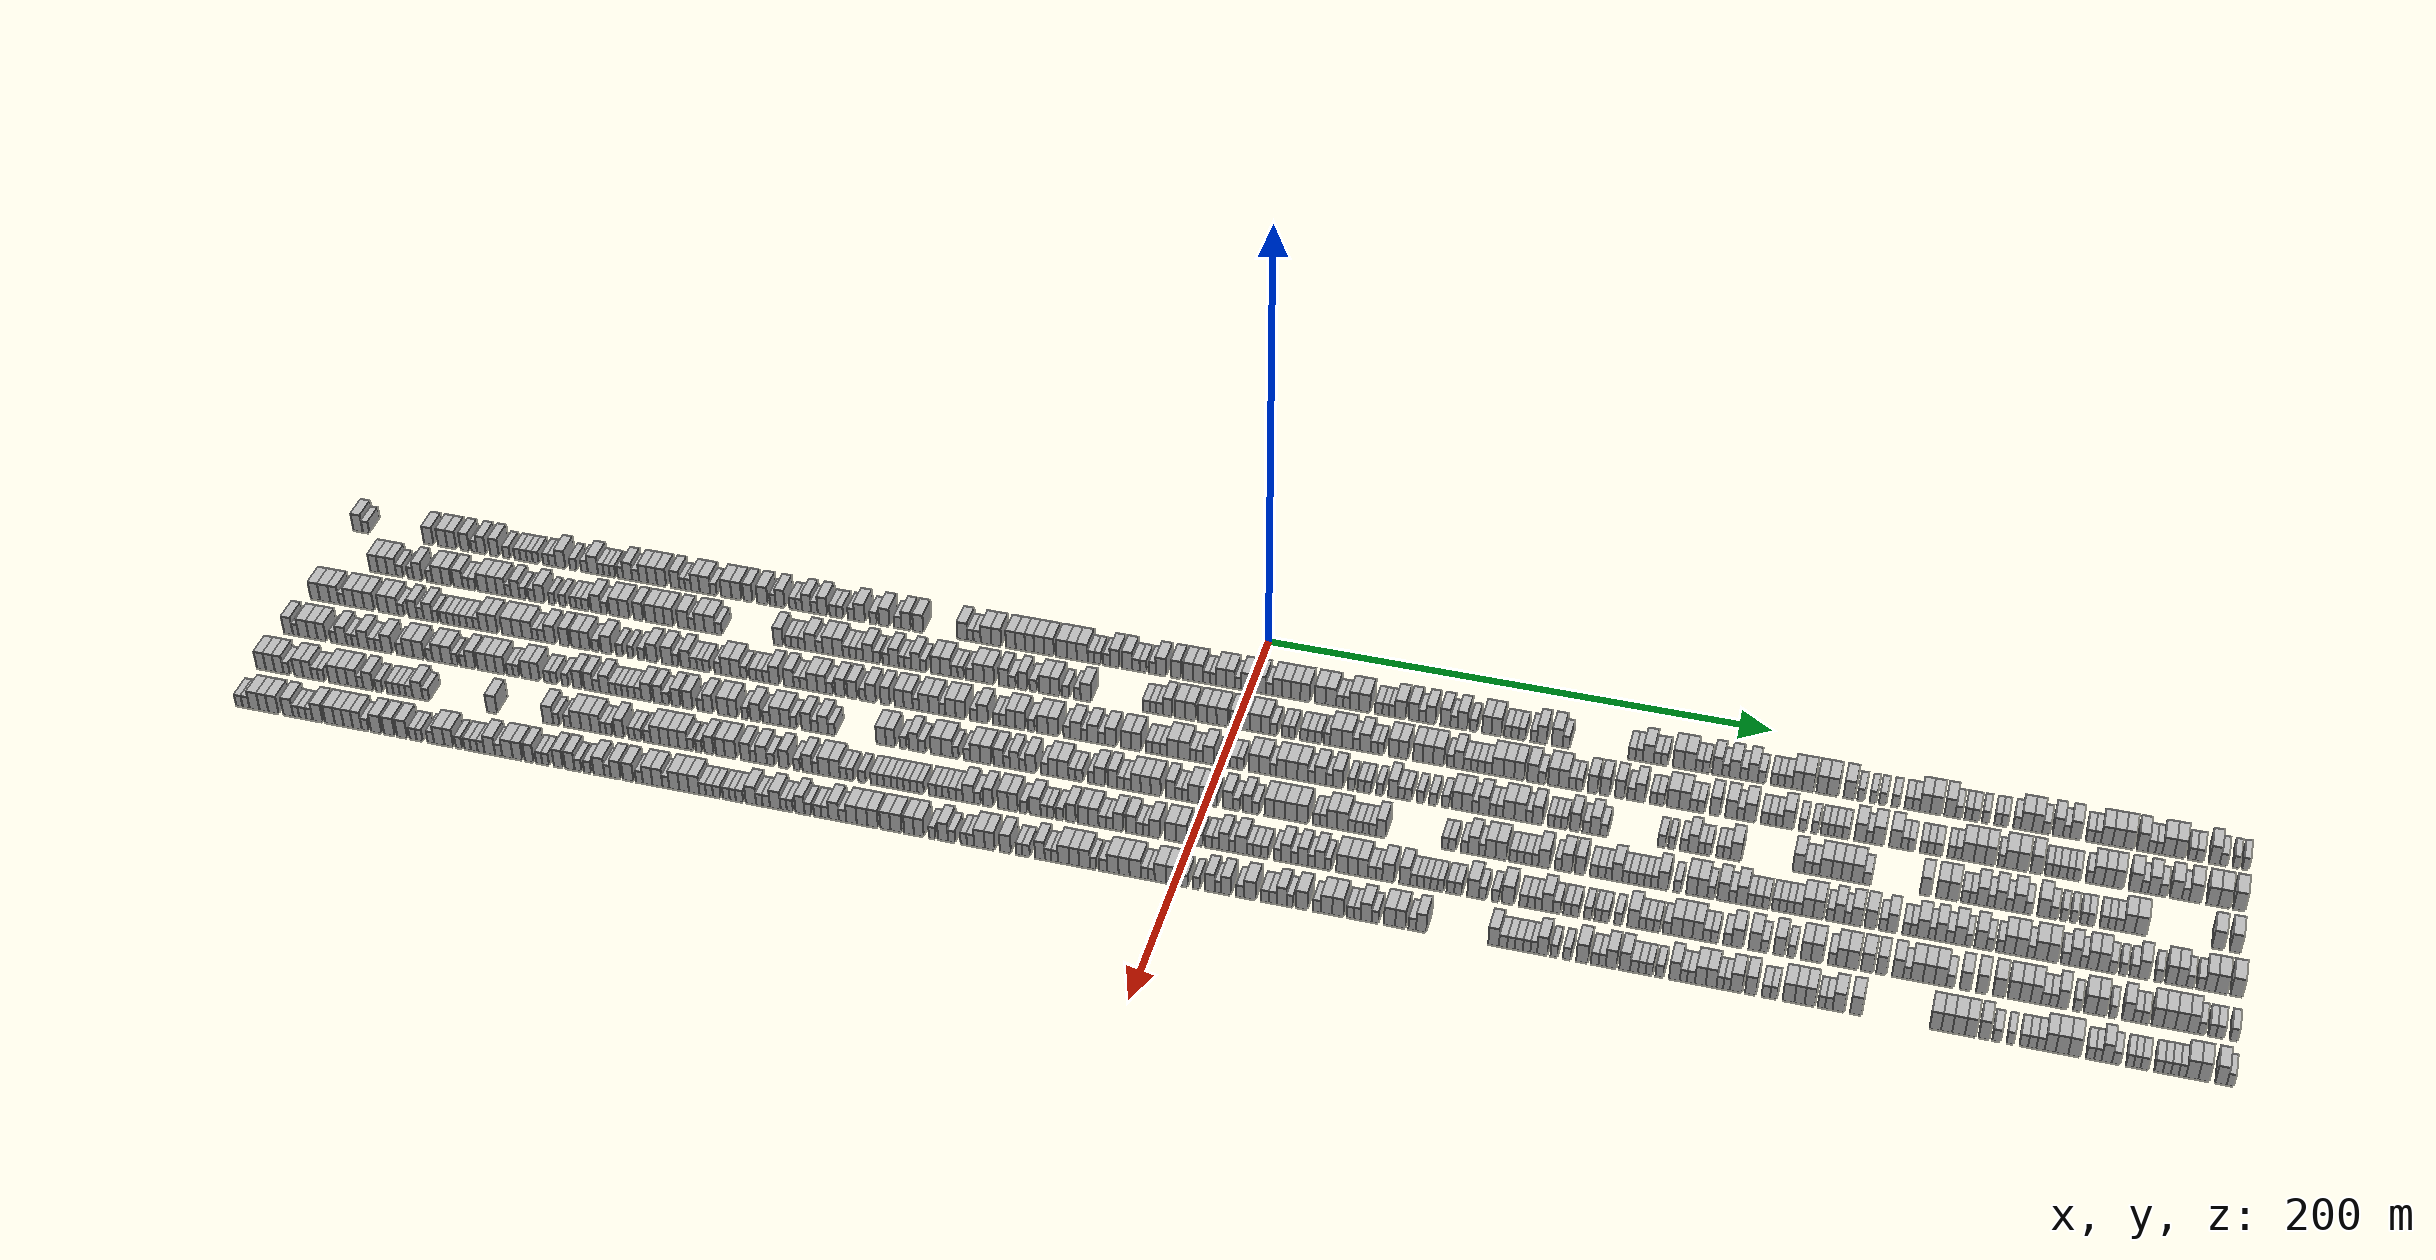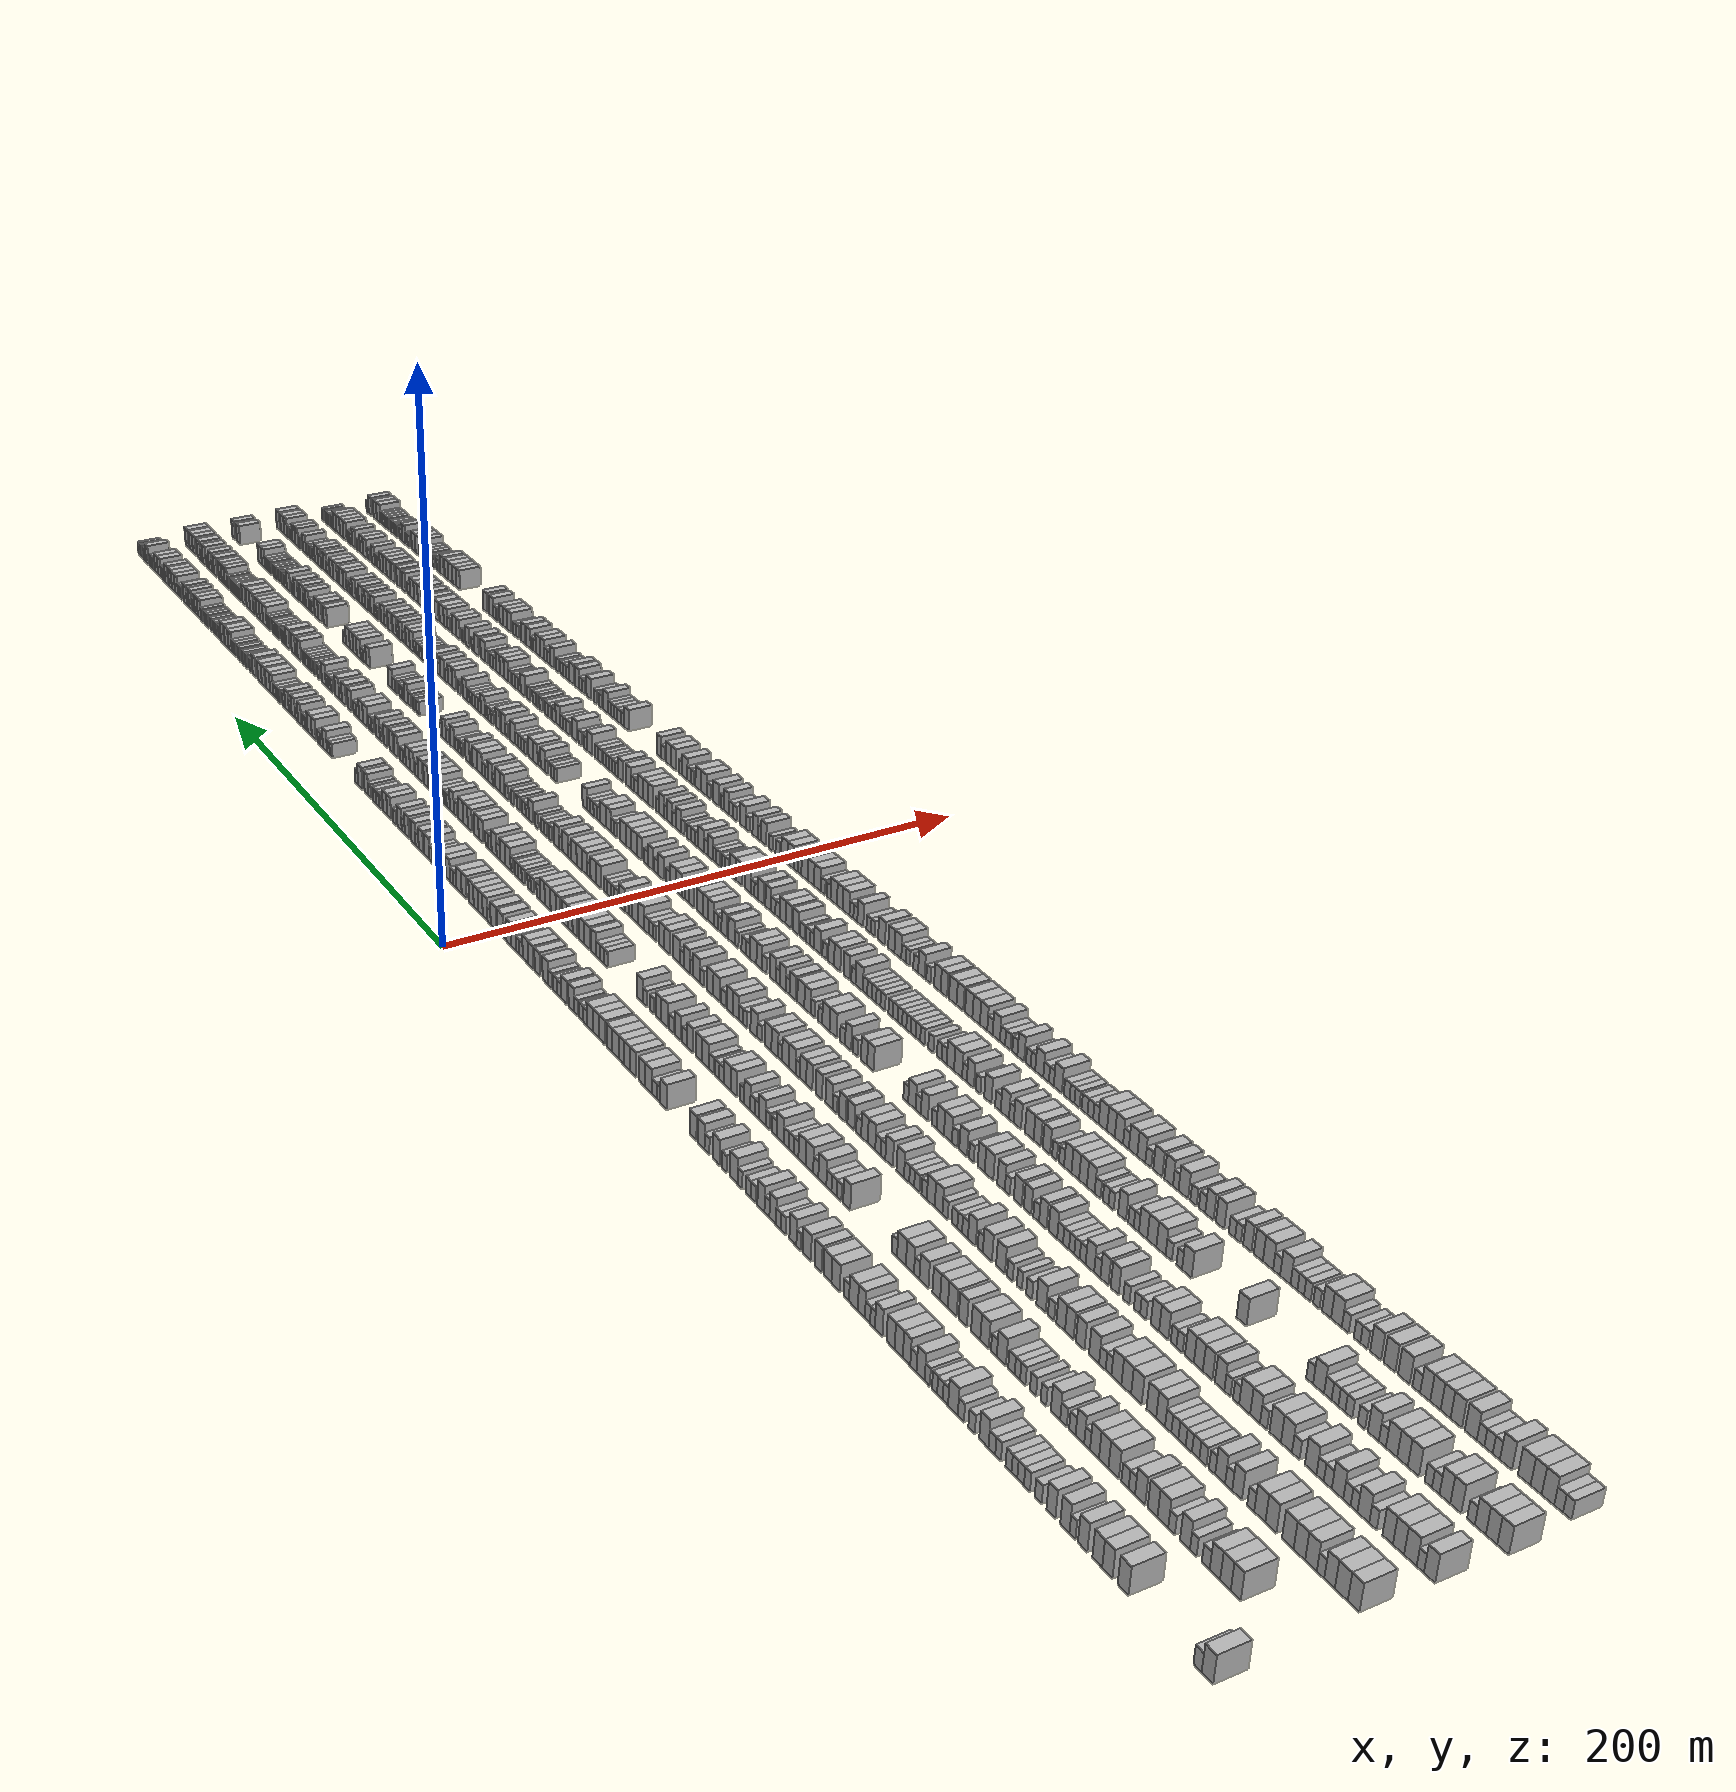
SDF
<sdf version="1.6">
 <world name="default">
  <scene>
   <sky><clouds><speed>12</speed></clouds></sky>
   <ambient>0.4 0.4 0.4 1</ambient>
   <background>0.7 0.7 0.7 1</background>
   <shadows>1</shadows>
  </scene>
  <gravity>0 0 -9.8066</gravity>
  <magnetic_field>6e-06 2.3e-05 -4.2e-05</magnetic_field>
  <physics default="0" name="default_physics" type="ode">
   <ode>
    <solver>
     <type>quick</type>
     <iters>10</iters>
     <sor>1.0</sor>
     <use_dynamic_moi_rescaling>0</use_dynamic_moi_rescaling>
    </solver>
    <constraints>
     <cfm>0</cfm>
     <erp>0.2</erp>
     <contact_max_correcting_vel>100</contact_max_correcting_vel>
     <contact_surface_layer>0.001</contact_surface_layer>
    </constraints>
   </ode>
   <max_step_size>0.004</max_step_size>
   <real_time_factor>1</real_time_factor>
   <real_time_update_rate>250</real_time_update_rate>
  </physics>
  <light name="sun" type="directional">
   <pose>0 0 10 0 0 0</pose>
   <diffuse>0.8 0.8 0.8 1</diffuse>
   <specular>0.2 0.2 0.2 1</specular>
   <attenuation>
    <range>1000</range>
    <constant>0.9</constant>
    <linear>0.01</linear>
    <quadratic>0.001</quadratic>
   </attenuation>
   <direction>-0.5 0.1 -0.9</direction>
  </light>
  <model name="building_1">
   <static>1</static>
   <pose>25.0000 -377.9382 0 0.000000 0.000000 0.000000</pose>
   <link name="link">
    <pose>0 0 4.50 0 0 0</pose>
    <collision name="collision"><geometry><box><size>10.0000 4.1236 9.0000</size></box></geometry></collision>
    <visual name="visual">
     <cast_shadows>0</cast_shadows>
     <geometry><box><size>10.0000 4.1236 9.0000</size></box></geometry>
     <material>
      <script>
       <uri>model://HANNAS_wall/materials/scripts</uri>
       <uri>model://HANNAS_wall/materials/textures</uri>
       <name>vrc/HANNAS_wall</name>
      </script>
     </material>
    </visual>
   </link>
  </model>
  <model name="building_2">
   <static>1</static>
   <pose>25.0000 -374.4038 0 0.000000 0.000000 0.000000</pose>
   <link name="link">
    <pose>0 0 3.00 0 0 0</pose>
    <collision name="collision"><geometry><box><size>10.0000 2.9452 6.0000</size></box></geometry></collision>
    <visual name="visual">
     <cast_shadows>0</cast_shadows>
     <geometry><box><size>10.0000 2.9452 6.0000</size></box></geometry>
     <material>
      <script>
       <uri>model://HANNAS_wall/materials/scripts</uri>
       <uri>model://HANNAS_wall/materials/textures</uri>
       <name>vrc/HANNAS_wall</name>
      </script>
     </material>
    </visual>
   </link>
  </model>
  <model name="building_3">
   <static>1</static>
   <pose>25.0000 -346.5828 0 0.000000 0.000000 0.000000</pose>
   <link name="link">
    <pose>0 0 4.50 0 0 0</pose>
    <collision name="collision"><geometry><box><size>10.0000 4.2323 9.0000</size></box></geometry></collision>
    <visual name="visual">
     <cast_shadows>0</cast_shadows>
     <geometry><box><size>10.0000 4.2323 9.0000</size></box></geometry>
     <material>
      <script>
       <uri>model://HANNAS_wall/materials/scripts</uri>
       <uri>model://HANNAS_wall/materials/textures</uri>
       <name>vrc/HANNAS_wall</name>
      </script>
     </material>
    </visual>
   </link>
  </model>
  <model name="building_4">
   <static>1</static>
   <pose>25.0000 -340.4268 0 0.000000 0.000000 0.000000</pose>
   <link name="link">
    <pose>0 0 4.50 0 0 0</pose>
    <collision name="collision"><geometry><box><size>10.0000 4.0796 9.0000</size></box></geometry></collision>
    <visual name="visual">
     <cast_shadows>0</cast_shadows>
     <geometry><box><size>10.0000 4.0796 9.0000</size></box></geometry>
     <material>
      <script>
       <uri>model://HANNAS_wall/materials/scripts</uri>
       <uri>model://HANNAS_wall/materials/textures</uri>
       <name>vrc/HANNAS_wall</name>
      </script>
     </material>
    </visual>
   </link>
  </model>
  <model name="building_5">
   <static>1</static>
   <pose>25.0000 -336.4371 0 0.000000 0.000000 0.000000</pose>
   <link name="link">
    <pose>0 0 4.50 0 0 0</pose>
    <collision name="collision"><geometry><box><size>10.0000 3.8998 9.0000</size></box></geometry></collision>
    <visual name="visual">
     <cast_shadows>0</cast_shadows>
     <geometry><box><size>10.0000 3.8998 9.0000</size></box></geometry>
     <material>
      <script>
       <uri>model://HANNAS_wall/materials/scripts</uri>
       <uri>model://HANNAS_wall/materials/textures</uri>
       <name>vrc/HANNAS_wall</name>
      </script>
     </material>
    </visual>
   </link>
  </model>
  <model name="building_6">
   <static>1</static>
   <pose>25.0000 -330.5840 0 0.000000 0.000000 0.000000</pose>
   <link name="link">
    <pose>0 0 4.50 0 0 0</pose>
    <collision name="collision"><geometry><box><size>10.0000 3.8064 9.0000</size></box></geometry></collision>
    <visual name="visual">
     <cast_shadows>0</cast_shadows>
     <geometry><box><size>10.0000 3.8064 9.0000</size></box></geometry>
     <material>
      <script>
       <uri>model://HANNAS_wall/materials/scripts</uri>
       <uri>model://HANNAS_wall/materials/textures</uri>
       <name>vrc/HANNAS_wall</name>
      </script>
     </material>
    </visual>
   </link>
  </model>
  <model name="building_7">
   <static>1</static>
   <pose>25.0000 -326.4665 0 0.000000 0.000000 0.000000</pose>
   <link name="link">
    <pose>0 0 3.00 0 0 0</pose>
    <collision name="collision"><geometry><box><size>10.0000 2.4286 6.0000</size></box></geometry></collision>
    <visual name="visual">
     <cast_shadows>0</cast_shadows>
     <geometry><box><size>10.0000 2.4286 6.0000</size></box></geometry>
     <material>
      <script>
       <uri>model://HANNAS_wall/materials/scripts</uri>
       <uri>model://HANNAS_wall/materials/textures</uri>
       <name>vrc/HANNAS_wall</name>
      </script>
     </material>
    </visual>
   </link>
  </model>
  <model name="building_8">
   <static>1</static>
   <pose>25.0000 -323.3611 0 0.000000 0.000000 0.000000</pose>
   <link name="link">
    <pose>0 0 4.50 0 0 0</pose>
    <collision name="collision"><geometry><box><size>10.0000 3.7822 9.0000</size></box></geometry></collision>
    <visual name="visual">
     <cast_shadows>0</cast_shadows>
     <geometry><box><size>10.0000 3.7822 9.0000</size></box></geometry>
     <material>
      <script>
       <uri>model://HANNAS_wall/materials/scripts</uri>
       <uri>model://HANNAS_wall/materials/textures</uri>
       <name>vrc/HANNAS_wall</name>
      </script>
     </material>
    </visual>
   </link>
  </model>
  <model name="building_9">
   <static>1</static>
   <pose>25.0000 -317.6096 0 0.000000 0.000000 0.000000</pose>
   <link name="link">
    <pose>0 0 4.50 0 0 0</pose>
    <collision name="collision"><geometry><box><size>10.0000 3.7208 9.0000</size></box></geometry></collision>
    <visual name="visual">
     <cast_shadows>0</cast_shadows>
     <geometry><box><size>10.0000 3.7208 9.0000</size></box></geometry>
     <material>
      <script>
       <uri>model://HANNAS_wall/materials/scripts</uri>
       <uri>model://HANNAS_wall/materials/textures</uri>
       <name>vrc/HANNAS_wall</name>
      </script>
     </material>
    </visual>
   </link>
  </model>
  <model name="building_10">
   <static>1</static>
   <pose>25.0000 -312.2862 0 0.000000 0.000000 0.000000</pose>
   <link name="link">
    <pose>0 0 3.00 0 0 0</pose>
    <collision name="collision"><geometry><box><size>10.0000 2.9260 6.0000</size></box></geometry></collision>
    <visual name="visual">
     <cast_shadows>0</cast_shadows>
     <geometry><box><size>10.0000 2.9260 6.0000</size></box></geometry>
     <material>
      <script>
       <uri>model://HANNAS_wall/materials/scripts</uri>
       <uri>model://HANNAS_wall/materials/textures</uri>
       <name>vrc/HANNAS_wall</name>
      </script>
     </material>
    </visual>
   </link>
  </model>
  <model name="building_11">
   <static>1</static>
   <pose>25.0000 -307.5249 0 0.000000 0.000000 0.000000</pose>
   <link name="link">
    <pose>0 0 3.00 0 0 0</pose>
    <collision name="collision"><geometry><box><size>10.0000 2.5965 6.0000</size></box></geometry></collision>
    <visual name="visual">
     <cast_shadows>0</cast_shadows>
     <geometry><box><size>10.0000 2.5965 6.0000</size></box></geometry>
     <material>
      <script>
       <uri>model://HANNAS_wall/materials/scripts</uri>
       <uri>model://HANNAS_wall/materials/textures</uri>
       <name>vrc/HANNAS_wall</name>
      </script>
     </material>
    </visual>
   </link>
  </model>
  <model name="building_12">
   <static>1</static>
   <pose>25.0000 -304.8029 0 0.000000 0.000000 0.000000</pose>
   <link name="link">
    <pose>0 0 3.00 0 0 0</pose>
    <collision name="collision"><geometry><box><size>10.0000 2.8476 6.0000</size></box></geometry></collision>
    <visual name="visual">
     <cast_shadows>0</cast_shadows>
     <geometry><box><size>10.0000 2.8476 6.0000</size></box></geometry>
     <material>
      <script>
       <uri>model://HANNAS_wall/materials/scripts</uri>
       <uri>model://HANNAS_wall/materials/textures</uri>
       <name>vrc/HANNAS_wall</name>
      </script>
     </material>
    </visual>
   </link>
  </model>
  <model name="building_13">
   <static>1</static>
   <pose>25.0000 -302.1215 0 0.000000 0.000000 0.000000</pose>
   <link name="link">
    <pose>0 0 3.00 0 0 0</pose>
    <collision name="collision"><geometry><box><size>10.0000 2.5152 6.0000</size></box></geometry></collision>
    <visual name="visual">
     <cast_shadows>0</cast_shadows>
     <geometry><box><size>10.0000 2.5152 6.0000</size></box></geometry>
     <material>
      <script>
       <uri>model://HANNAS_wall/materials/scripts</uri>
       <uri>model://HANNAS_wall/materials/textures</uri>
       <name>vrc/HANNAS_wall</name>
      </script>
     </material>
    </visual>
   </link>
  </model>
  <model name="building_14">
   <static>1</static>
   <pose>25.0000 -299.5712 0 0.000000 0.000000 0.000000</pose>
   <link name="link">
    <pose>0 0 3.00 0 0 0</pose>
    <collision name="collision"><geometry><box><size>10.0000 2.5855 6.0000</size></box></geometry></collision>
    <visual name="visual">
     <cast_shadows>0</cast_shadows>
     <geometry><box><size>10.0000 2.5855 6.0000</size></box></geometry>
     <material>
      <script>
       <uri>model://HANNAS_wall/materials/scripts</uri>
       <uri>model://HANNAS_wall/materials/textures</uri>
       <name>vrc/HANNAS_wall</name>
      </script>
     </material>
    </visual>
   </link>
  </model>
  <model name="building_15">
   <static>1</static>
   <pose>25.0000 -295.0338 0 0.000000 0.000000 0.000000</pose>
   <link name="link">
    <pose>0 0 3.00 0 0 0</pose>
    <collision name="collision"><geometry><box><size>10.0000 2.4892 6.0000</size></box></geometry></collision>
    <visual name="visual">
     <cast_shadows>0</cast_shadows>
     <geometry><box><size>10.0000 2.4892 6.0000</size></box></geometry>
     <material>
      <script>
       <uri>model://HANNAS_wall/materials/scripts</uri>
       <uri>model://HANNAS_wall/materials/textures</uri>
       <name>vrc/HANNAS_wall</name>
      </script>
     </material>
    </visual>
   </link>
  </model>
  <model name="building_16">
   <static>1</static>
   <pose>25.0000 -292.2960 0 0.000000 0.000000 0.000000</pose>
   <link name="link">
    <pose>0 0 3.00 0 0 0</pose>
    <collision name="collision"><geometry><box><size>10.0000 2.9864 6.0000</size></box></geometry></collision>
    <visual name="visual">
     <cast_shadows>0</cast_shadows>
     <geometry><box><size>10.0000 2.9864 6.0000</size></box></geometry>
     <material>
      <script>
       <uri>model://HANNAS_wall/materials/scripts</uri>
       <uri>model://HANNAS_wall/materials/textures</uri>
       <name>vrc/HANNAS_wall</name>
      </script>
     </material>
    </visual>
   </link>
  </model>
  <model name="building_17">
   <static>1</static>
   <pose>25.0000 -288.7439 0 0.000000 0.000000 0.000000</pose>
   <link name="link">
    <pose>0 0 4.50 0 0 0</pose>
    <collision name="collision"><geometry><box><size>10.0000 4.1179 9.0000</size></box></geometry></collision>
    <visual name="visual">
     <cast_shadows>0</cast_shadows>
     <geometry><box><size>10.0000 4.1179 9.0000</size></box></geometry>
     <material>
      <script>
       <uri>model://HANNAS_wall/materials/scripts</uri>
       <uri>model://HANNAS_wall/materials/textures</uri>
       <name>vrc/HANNAS_wall</name>
      </script>
     </material>
    </visual>
   </link>
  </model>
  <model name="building_18">
   <static>1</static>
   <pose>25.0000 -283.2338 0 0.000000 0.000000 0.000000</pose>
   <link name="link">
    <pose>0 0 3.00 0 0 0</pose>
    <collision name="collision"><geometry><box><size>10.0000 2.9022 6.0000</size></box></geometry></collision>
    <visual name="visual">
     <cast_shadows>0</cast_shadows>
     <geometry><box><size>10.0000 2.9022 6.0000</size></box></geometry>
     <material>
      <script>
       <uri>model://HANNAS_wall/materials/scripts</uri>
       <uri>model://HANNAS_wall/materials/textures</uri>
       <name>vrc/HANNAS_wall</name>
      </script>
     </material>
    </visual>
   </link>
  </model>
  <model name="building_19">
   <static>1</static>
   <pose>25.0000 -278.3784 0 0.000000 0.000000 0.000000</pose>
   <link name="link">
    <pose>0 0 3.00 0 0 0</pose>
    <collision name="collision"><geometry><box><size>10.0000 2.8085 6.0000</size></box></geometry></collision>
    <visual name="visual">
     <cast_shadows>0</cast_shadows>
     <geometry><box><size>10.0000 2.8085 6.0000</size></box></geometry>
     <material>
      <script>
       <uri>model://HANNAS_wall/materials/scripts</uri>
       <uri>model://HANNAS_wall/materials/textures</uri>
       <name>vrc/HANNAS_wall</name>
      </script>
     </material>
    </visual>
   </link>
  </model>
  <model name="building_20">
   <static>1</static>
   <pose>25.0000 -274.7363 0 0.000000 0.000000 0.000000</pose>
   <link name="link">
    <pose>0 0 4.50 0 0 0</pose>
    <collision name="collision"><geometry><box><size>10.0000 4.4758 9.0000</size></box></geometry></collision>
    <visual name="visual">
     <cast_shadows>0</cast_shadows>
     <geometry><box><size>10.0000 4.4758 9.0000</size></box></geometry>
     <material>
      <script>
       <uri>model://HANNAS_wall/materials/scripts</uri>
       <uri>model://HANNAS_wall/materials/textures</uri>
       <name>vrc/HANNAS_wall</name>
      </script>
     </material>
    </visual>
   </link>
  </model>
  <model name="building_21">
   <static>1</static>
   <pose>25.0000 -271.2488 0 0.000000 0.000000 0.000000</pose>
   <link name="link">
    <pose>0 0 3.00 0 0 0</pose>
    <collision name="collision"><geometry><box><size>10.0000 2.4991 6.0000</size></box></geometry></collision>
    <visual name="visual">
     <cast_shadows>0</cast_shadows>
     <geometry><box><size>10.0000 2.4991 6.0000</size></box></geometry>
     <material>
      <script>
       <uri>model://HANNAS_wall/materials/scripts</uri>
       <uri>model://HANNAS_wall/materials/textures</uri>
       <name>vrc/HANNAS_wall</name>
      </script>
     </material>
    </visual>
   </link>
  </model>
  <model name="building_22">
   <static>1</static>
   <pose>25.0000 -268.7155 0 0.000000 0.000000 0.000000</pose>
   <link name="link">
    <pose>0 0 3.00 0 0 0</pose>
    <collision name="collision"><geometry><box><size>10.0000 2.5675 6.0000</size></box></geometry></collision>
    <visual name="visual">
     <cast_shadows>0</cast_shadows>
     <geometry><box><size>10.0000 2.5675 6.0000</size></box></geometry>
     <material>
      <script>
       <uri>model://HANNAS_wall/materials/scripts</uri>
       <uri>model://HANNAS_wall/materials/textures</uri>
       <name>vrc/HANNAS_wall</name>
      </script>
     </material>
    </visual>
   </link>
  </model>
  <model name="building_23">
   <static>1</static>
   <pose>25.0000 -266.2116 0 0.000000 0.000000 0.000000</pose>
   <link name="link">
    <pose>0 0 3.00 0 0 0</pose>
    <collision name="collision"><geometry><box><size>10.0000 2.4403 6.0000</size></box></geometry></collision>
    <visual name="visual">
     <cast_shadows>0</cast_shadows>
     <geometry><box><size>10.0000 2.4403 6.0000</size></box></geometry>
     <material>
      <script>
       <uri>model://HANNAS_wall/materials/scripts</uri>
       <uri>model://HANNAS_wall/materials/textures</uri>
       <name>vrc/HANNAS_wall</name>
      </script>
     </material>
    </visual>
   </link>
  </model>
  <model name="building_24">
   <static>1</static>
   <pose>25.0000 -262.7773 0 0.000000 0.000000 0.000000</pose>
   <link name="link">
    <pose>0 0 3.00 0 0 0</pose>
    <collision name="collision"><geometry><box><size>10.0000 2.4283 6.0000</size></box></geometry></collision>
    <visual name="visual">
     <cast_shadows>0</cast_shadows>
     <geometry><box><size>10.0000 2.4283 6.0000</size></box></geometry>
     <material>
      <script>
       <uri>model://HANNAS_wall/materials/scripts</uri>
       <uri>model://HANNAS_wall/materials/textures</uri>
       <name>vrc/HANNAS_wall</name>
      </script>
     </material>
    </visual>
   </link>
  </model>
  <model name="building_25">
   <static>1</static>
   <pose>25.0000 -259.6138 0 0.000000 0.000000 0.000000</pose>
   <link name="link">
    <pose>0 0 4.50 0 0 0</pose>
    <collision name="collision"><geometry><box><size>10.0000 3.8987 9.0000</size></box></geometry></collision>
    <visual name="visual">
     <cast_shadows>0</cast_shadows>
     <geometry><box><size>10.0000 3.8987 9.0000</size></box></geometry>
     <material>
      <script>
       <uri>model://HANNAS_wall/materials/scripts</uri>
       <uri>model://HANNAS_wall/materials/textures</uri>
       <name>vrc/HANNAS_wall</name>
      </script>
     </material>
    </visual>
   </link>
  </model>
  <model name="building_26">
   <static>1</static>
   <pose>25.0000 -256.1735 0 0.000000 0.000000 0.000000</pose>
   <link name="link">
    <pose>0 0 3.00 0 0 0</pose>
    <collision name="collision"><geometry><box><size>10.0000 2.9818 6.0000</size></box></geometry></collision>
    <visual name="visual">
     <cast_shadows>0</cast_shadows>
     <geometry><box><size>10.0000 2.9818 6.0000</size></box></geometry>
     <material>
      <script>
       <uri>model://HANNAS_wall/materials/scripts</uri>
       <uri>model://HANNAS_wall/materials/textures</uri>
       <name>vrc/HANNAS_wall</name>
      </script>
     </material>
    </visual>
   </link>
  </model>
  <model name="building_27">
   <static>1</static>
   <pose>25.0000 -252.8727 0 0.000000 0.000000 0.000000</pose>
   <link name="link">
    <pose>0 0 4.50 0 0 0</pose>
    <collision name="collision"><geometry><box><size>10.0000 3.6199 9.0000</size></box></geometry></collision>
    <visual name="visual">
     <cast_shadows>0</cast_shadows>
     <geometry><box><size>10.0000 3.6199 9.0000</size></box></geometry>
     <material>
      <script>
       <uri>model://HANNAS_wall/materials/scripts</uri>
       <uri>model://HANNAS_wall/materials/textures</uri>
       <name>vrc/HANNAS_wall</name>
      </script>
     </material>
    </visual>
   </link>
  </model>
  <model name="building_28">
   <static>1</static>
   <pose>25.0000 -249.0801 0 0.000000 0.000000 0.000000</pose>
   <link name="link">
    <pose>0 0 4.50 0 0 0</pose>
    <collision name="collision"><geometry><box><size>10.0000 3.9652 9.0000</size></box></geometry></collision>
    <visual name="visual">
     <cast_shadows>0</cast_shadows>
     <geometry><box><size>10.0000 3.9652 9.0000</size></box></geometry>
     <material>
      <script>
       <uri>model://HANNAS_wall/materials/scripts</uri>
       <uri>model://HANNAS_wall/materials/textures</uri>
       <name>vrc/HANNAS_wall</name>
      </script>
     </material>
    </visual>
   </link>
  </model>
  <model name="building_29">
   <static>1</static>
   <pose>25.0000 -245.0985 0 0.000000 0.000000 0.000000</pose>
   <link name="link">
    <pose>0 0 4.50 0 0 0</pose>
    <collision name="collision"><geometry><box><size>10.0000 3.9980 9.0000</size></box></geometry></collision>
    <visual name="visual">
     <cast_shadows>0</cast_shadows>
     <geometry><box><size>10.0000 3.9980 9.0000</size></box></geometry>
     <material>
      <script>
       <uri>model://HANNAS_wall/materials/scripts</uri>
       <uri>model://HANNAS_wall/materials/textures</uri>
       <name>vrc/HANNAS_wall</name>
      </script>
     </material>
    </visual>
   </link>
  </model>
  <model name="building_30">
   <static>1</static>
   <pose>25.0000 -239.2274 0 0.000000 0.000000 0.000000</pose>
   <link name="link">
    <pose>0 0 4.50 0 0 0</pose>
    <collision name="collision"><geometry><box><size>10.0000 3.7443 9.0000</size></box></geometry></collision>
    <visual name="visual">
     <cast_shadows>0</cast_shadows>
     <geometry><box><size>10.0000 3.7443 9.0000</size></box></geometry>
     <material>
      <script>
       <uri>model://HANNAS_wall/materials/scripts</uri>
       <uri>model://HANNAS_wall/materials/textures</uri>
       <name>vrc/HANNAS_wall</name>
      </script>
     </material>
    </visual>
   </link>
  </model>
  <model name="building_31">
   <static>1</static>
   <pose>25.0000 -236.1387 0 0.000000 0.000000 0.000000</pose>
   <link name="link">
    <pose>0 0 3.00 0 0 0</pose>
    <collision name="collision"><geometry><box><size>10.0000 2.4332 6.0000</size></box></geometry></collision>
    <visual name="visual">
     <cast_shadows>0</cast_shadows>
     <geometry><box><size>10.0000 2.4332 6.0000</size></box></geometry>
     <material>
      <script>
       <uri>model://HANNAS_wall/materials/scripts</uri>
       <uri>model://HANNAS_wall/materials/textures</uri>
       <name>vrc/HANNAS_wall</name>
      </script>
     </material>
    </visual>
   </link>
  </model>
  <model name="building_32">
   <static>1</static>
   <pose>25.0000 -233.6231 0 0.000000 0.000000 0.000000</pose>
   <link name="link">
    <pose>0 0 3.00 0 0 0</pose>
    <collision name="collision"><geometry><box><size>10.0000 2.5980 6.0000</size></box></geometry></collision>
    <visual name="visual">
     <cast_shadows>0</cast_shadows>
     <geometry><box><size>10.0000 2.5980 6.0000</size></box></geometry>
     <material>
      <script>
       <uri>model://HANNAS_wall/materials/scripts</uri>
       <uri>model://HANNAS_wall/materials/textures</uri>
       <name>vrc/HANNAS_wall</name>
      </script>
     </material>
    </visual>
   </link>
  </model>
  <model name="building_33">
   <static>1</static>
   <pose>25.0000 -230.5094 0 0.000000 0.000000 0.000000</pose>
   <link name="link">
    <pose>0 0 4.50 0 0 0</pose>
    <collision name="collision"><geometry><box><size>10.0000 3.6295 9.0000</size></box></geometry></collision>
    <visual name="visual">
     <cast_shadows>0</cast_shadows>
     <geometry><box><size>10.0000 3.6295 9.0000</size></box></geometry>
     <material>
      <script>
       <uri>model://HANNAS_wall/materials/scripts</uri>
       <uri>model://HANNAS_wall/materials/textures</uri>
       <name>vrc/HANNAS_wall</name>
      </script>
     </material>
    </visual>
   </link>
  </model>
  <model name="building_34">
   <static>1</static>
   <pose>25.0000 -226.4478 0 0.000000 0.000000 0.000000</pose>
   <link name="link">
    <pose>0 0 4.50 0 0 0</pose>
    <collision name="collision"><geometry><box><size>10.0000 4.4936 9.0000</size></box></geometry></collision>
    <visual name="visual">
     <cast_shadows>0</cast_shadows>
     <geometry><box><size>10.0000 4.4936 9.0000</size></box></geometry>
     <material>
      <script>
       <uri>model://HANNAS_wall/materials/scripts</uri>
       <uri>model://HANNAS_wall/materials/textures</uri>
       <name>vrc/HANNAS_wall</name>
      </script>
     </material>
    </visual>
   </link>
  </model>
  <model name="building_35">
   <static>1</static>
   <pose>25.0000 -222.8182 0 0.000000 0.000000 0.000000</pose>
   <link name="link">
    <pose>0 0 3.00 0 0 0</pose>
    <collision name="collision"><geometry><box><size>10.0000 2.7655 6.0000</size></box></geometry></collision>
    <visual name="visual">
     <cast_shadows>0</cast_shadows>
     <geometry><box><size>10.0000 2.7655 6.0000</size></box></geometry>
     <material>
      <script>
       <uri>model://HANNAS_wall/materials/scripts</uri>
       <uri>model://HANNAS_wall/materials/textures</uri>
       <name>vrc/HANNAS_wall</name>
      </script>
     </material>
    </visual>
   </link>
  </model>
  <model name="building_36">
   <static>1</static>
   <pose>25.0000 -217.2489 0 0.000000 0.000000 0.000000</pose>
   <link name="link">
    <pose>0 0 4.50 0 0 0</pose>
    <collision name="collision"><geometry><box><size>10.0000 4.3732 9.0000</size></box></geometry></collision>
    <visual name="visual">
     <cast_shadows>0</cast_shadows>
     <geometry><box><size>10.0000 4.3732 9.0000</size></box></geometry>
     <material>
      <script>
       <uri>model://HANNAS_wall/materials/scripts</uri>
       <uri>model://HANNAS_wall/materials/textures</uri>
       <name>vrc/HANNAS_wall</name>
      </script>
     </material>
    </visual>
   </link>
  </model>
  <model name="building_37">
   <static>1</static>
   <pose>25.0000 -212.9820 0 0.000000 0.000000 0.000000</pose>
   <link name="link">
    <pose>0 0 4.50 0 0 0</pose>
    <collision name="collision"><geometry><box><size>10.0000 4.1607 9.0000</size></box></geometry></collision>
    <visual name="visual">
     <cast_shadows>0</cast_shadows>
     <geometry><box><size>10.0000 4.1607 9.0000</size></box></geometry>
     <material>
      <script>
       <uri>model://HANNAS_wall/materials/scripts</uri>
       <uri>model://HANNAS_wall/materials/textures</uri>
       <name>vrc/HANNAS_wall</name>
      </script>
     </material>
    </visual>
   </link>
  </model>
  <model name="building_38">
   <static>1</static>
   <pose>25.0000 -208.0290 0 0.000000 0.000000 0.000000</pose>
   <link name="link">
    <pose>0 0 4.50 0 0 0</pose>
    <collision name="collision"><geometry><box><size>10.0000 3.7453 9.0000</size></box></geometry></collision>
    <visual name="visual">
     <cast_shadows>0</cast_shadows>
     <geometry><box><size>10.0000 3.7453 9.0000</size></box></geometry>
     <material>
      <script>
       <uri>model://HANNAS_wall/materials/scripts</uri>
       <uri>model://HANNAS_wall/materials/textures</uri>
       <name>vrc/HANNAS_wall</name>
      </script>
     </material>
    </visual>
   </link>
  </model>
  <model name="building_39">
   <static>1</static>
   <pose>25.0000 -201.9263 0 0.000000 0.000000 0.000000</pose>
   <link name="link">
    <pose>0 0 4.50 0 0 0</pose>
    <collision name="collision"><geometry><box><size>10.0000 4.4602 9.0000</size></box></geometry></collision>
    <visual name="visual">
     <cast_shadows>0</cast_shadows>
     <geometry><box><size>10.0000 4.4602 9.0000</size></box></geometry>
     <material>
      <script>
       <uri>model://HANNAS_wall/materials/scripts</uri>
       <uri>model://HANNAS_wall/materials/textures</uri>
       <name>vrc/HANNAS_wall</name>
      </script>
     </material>
    </visual>
   </link>
  </model>
  <model name="building_40">
   <static>1</static>
   <pose>25.0000 -197.4932 0 0.000000 0.000000 0.000000</pose>
   <link name="link">
    <pose>0 0 3.00 0 0 0</pose>
    <collision name="collision"><geometry><box><size>10.0000 2.4059 6.0000</size></box></geometry></collision>
    <visual name="visual">
     <cast_shadows>0</cast_shadows>
     <geometry><box><size>10.0000 2.4059 6.0000</size></box></geometry>
     <material>
      <script>
       <uri>model://HANNAS_wall/materials/scripts</uri>
       <uri>model://HANNAS_wall/materials/textures</uri>
       <name>vrc/HANNAS_wall</name>
      </script>
     </material>
    </visual>
   </link>
  </model>
  <model name="building_41">
   <static>1</static>
   <pose>25.0000 -194.3835 0 0.000000 0.000000 0.000000</pose>
   <link name="link">
    <pose>0 0 4.50 0 0 0</pose>
    <collision name="collision"><geometry><box><size>10.0000 3.8135 9.0000</size></box></geometry></collision>
    <visual name="visual">
     <cast_shadows>0</cast_shadows>
     <geometry><box><size>10.0000 3.8135 9.0000</size></box></geometry>
     <material>
      <script>
       <uri>model://HANNAS_wall/materials/scripts</uri>
       <uri>model://HANNAS_wall/materials/textures</uri>
       <name>vrc/HANNAS_wall</name>
      </script>
     </material>
    </visual>
   </link>
  </model>
  <model name="building_42">
   <static>1</static>
   <pose>25.0000 -189.0873 0 0.000000 0.000000 0.000000</pose>
   <link name="link">
    <pose>0 0 3.00 0 0 0</pose>
    <collision name="collision"><geometry><box><size>10.0000 2.7790 6.0000</size></box></geometry></collision>
    <visual name="visual">
     <cast_shadows>0</cast_shadows>
     <geometry><box><size>10.0000 2.7790 6.0000</size></box></geometry>
     <material>
      <script>
       <uri>model://HANNAS_wall/materials/scripts</uri>
       <uri>model://HANNAS_wall/materials/textures</uri>
       <name>vrc/HANNAS_wall</name>
      </script>
     </material>
    </visual>
   </link>
  </model>
  <model name="building_43">
   <static>1</static>
   <pose>25.0000 -186.3803 0 0.000000 0.000000 0.000000</pose>
   <link name="link">
    <pose>0 0 3.00 0 0 0</pose>
    <collision name="collision"><geometry><box><size>10.0000 2.6351 6.0000</size></box></geometry></collision>
    <visual name="visual">
     <cast_shadows>0</cast_shadows>
     <geometry><box><size>10.0000 2.6351 6.0000</size></box></geometry>
     <material>
      <script>
       <uri>model://HANNAS_wall/materials/scripts</uri>
       <uri>model://HANNAS_wall/materials/textures</uri>
       <name>vrc/HANNAS_wall</name>
      </script>
     </material>
    </visual>
   </link>
  </model>
  <model name="building_44">
   <static>1</static>
   <pose>25.0000 -183.1998 0 0.000000 0.000000 0.000000</pose>
   <link name="link">
    <pose>0 0 4.50 0 0 0</pose>
    <collision name="collision"><geometry><box><size>10.0000 3.7259 9.0000</size></box></geometry></collision>
    <visual name="visual">
     <cast_shadows>0</cast_shadows>
     <geometry><box><size>10.0000 3.7259 9.0000</size></box></geometry>
     <material>
      <script>
       <uri>model://HANNAS_wall/materials/scripts</uri>
       <uri>model://HANNAS_wall/materials/textures</uri>
       <name>vrc/HANNAS_wall</name>
      </script>
     </material>
    </visual>
   </link>
  </model>
  <model name="building_45">
   <static>1</static>
   <pose>25.0000 -179.9310 0 0.000000 0.000000 0.000000</pose>
   <link name="link">
    <pose>0 0 3.00 0 0 0</pose>
    <collision name="collision"><geometry><box><size>10.0000 2.8118 6.0000</size></box></geometry></collision>
    <visual name="visual">
     <cast_shadows>0</cast_shadows>
     <geometry><box><size>10.0000 2.8118 6.0000</size></box></geometry>
     <material>
      <script>
       <uri>model://HANNAS_wall/materials/scripts</uri>
       <uri>model://HANNAS_wall/materials/textures</uri>
       <name>vrc/HANNAS_wall</name>
      </script>
     </material>
    </visual>
   </link>
  </model>
  <model name="building_46">
   <static>1</static>
   <pose>25.0000 -176.5166 0 0.000000 0.000000 0.000000</pose>
   <link name="link">
    <pose>0 0 4.50 0 0 0</pose>
    <collision name="collision"><geometry><box><size>10.0000 4.0171 9.0000</size></box></geometry></collision>
    <visual name="visual">
     <cast_shadows>0</cast_shadows>
     <geometry><box><size>10.0000 4.0171 9.0000</size></box></geometry>
     <material>
      <script>
       <uri>model://HANNAS_wall/materials/scripts</uri>
       <uri>model://HANNAS_wall/materials/textures</uri>
       <name>vrc/HANNAS_wall</name>
      </script>
     </material>
    </visual>
   </link>
  </model>
  <model name="building_47">
   <static>1</static>
   <pose>25.0000 -172.0832 0 0.000000 0.000000 0.000000</pose>
   <link name="link">
    <pose>0 0 3.00 0 0 0</pose>
    <collision name="collision"><geometry><box><size>10.0000 2.8497 6.0000</size></box></geometry></collision>
    <visual name="visual">
     <cast_shadows>0</cast_shadows>
     <geometry><box><size>10.0000 2.8497 6.0000</size></box></geometry>
     <material>
      <script>
       <uri>model://HANNAS_wall/materials/scripts</uri>
       <uri>model://HANNAS_wall/materials/textures</uri>
       <name>vrc/HANNAS_wall</name>
      </script>
     </material>
    </visual>
   </link>
  </model>
  <model name="building_48">
   <static>1</static>
   <pose>25.0000 -169.2199 0 0.000000 0.000000 0.000000</pose>
   <link name="link">
    <pose>0 0 3.00 0 0 0</pose>
    <collision name="collision"><geometry><box><size>10.0000 2.8769 6.0000</size></box></geometry></collision>
    <visual name="visual">
     <cast_shadows>0</cast_shadows>
     <geometry><box><size>10.0000 2.8769 6.0000</size></box></geometry>
     <material>
      <script>
       <uri>model://HANNAS_wall/materials/scripts</uri>
       <uri>model://HANNAS_wall/materials/textures</uri>
       <name>vrc/HANNAS_wall</name>
      </script>
     </material>
    </visual>
   </link>
  </model>
  <model name="building_49">
   <static>1</static>
   <pose>25.0000 -164.4067 0 0.000000 0.000000 0.000000</pose>
   <link name="link">
    <pose>0 0 3.00 0 0 0</pose>
    <collision name="collision"><geometry><box><size>10.0000 2.7496 6.0000</size></box></geometry></collision>
    <visual name="visual">
     <cast_shadows>0</cast_shadows>
     <geometry><box><size>10.0000 2.7496 6.0000</size></box></geometry>
     <material>
      <script>
       <uri>model://HANNAS_wall/materials/scripts</uri>
       <uri>model://HANNAS_wall/materials/textures</uri>
       <name>vrc/HANNAS_wall</name>
      </script>
     </material>
    </visual>
   </link>
  </model>
  <model name="building_50">
   <static>1</static>
   <pose>25.0000 -160.8104 0 0.000000 0.000000 0.000000</pose>
   <link name="link">
    <pose>0 0 4.50 0 0 0</pose>
    <collision name="collision"><geometry><box><size>10.0000 4.4430 9.0000</size></box></geometry></collision>
    <visual name="visual">
     <cast_shadows>0</cast_shadows>
     <geometry><box><size>10.0000 4.4430 9.0000</size></box></geometry>
     <material>
      <script>
       <uri>model://HANNAS_wall/materials/scripts</uri>
       <uri>model://HANNAS_wall/materials/textures</uri>
       <name>vrc/HANNAS_wall</name>
      </script>
     </material>
    </visual>
   </link>
  </model>
  <model name="building_51">
   <static>1</static>
   <pose>25.0000 -155.0964 0 0.000000 0.000000 0.000000</pose>
   <link name="link">
    <pose>0 0 3.00 0 0 0</pose>
    <collision name="collision"><geometry><box><size>10.0000 2.9850 6.0000</size></box></geometry></collision>
    <visual name="visual">
     <cast_shadows>0</cast_shadows>
     <geometry><box><size>10.0000 2.9850 6.0000</size></box></geometry>
     <material>
      <script>
       <uri>model://HANNAS_wall/materials/scripts</uri>
       <uri>model://HANNAS_wall/materials/textures</uri>
       <name>vrc/HANNAS_wall</name>
      </script>
     </material>
    </visual>
   </link>
  </model>
  <model name="building_52">
   <static>1</static>
   <pose>25.0000 -150.4398 0 0.000000 0.000000 0.000000</pose>
   <link name="link">
    <pose>0 0 4.50 0 0 0</pose>
    <collision name="collision"><geometry><box><size>10.0000 4.3282 9.0000</size></box></geometry></collision>
    <visual name="visual">
     <cast_shadows>0</cast_shadows>
     <geometry><box><size>10.0000 4.3282 9.0000</size></box></geometry>
     <material>
      <script>
       <uri>model://HANNAS_wall/materials/scripts</uri>
       <uri>model://HANNAS_wall/materials/textures</uri>
       <name>vrc/HANNAS_wall</name>
      </script>
     </material>
    </visual>
   </link>
  </model>
  <model name="building_53">
   <static>1</static>
   <pose>25.0000 -144.7872 0 0.000000 0.000000 0.000000</pose>
   <link name="link">
    <pose>0 0 3.00 0 0 0</pose>
    <collision name="collision"><geometry><box><size>10.0000 2.9771 6.0000</size></box></geometry></collision>
    <visual name="visual">
     <cast_shadows>0</cast_shadows>
     <geometry><box><size>10.0000 2.9771 6.0000</size></box></geometry>
     <material>
      <script>
       <uri>model://HANNAS_wall/materials/scripts</uri>
       <uri>model://HANNAS_wall/materials/textures</uri>
       <name>vrc/HANNAS_wall</name>
      </script>
     </material>
    </visual>
   </link>
  </model>
  <model name="building_54">
   <static>1</static>
   <pose>25.0000 -141.3297 0 0.000000 0.000000 0.000000</pose>
   <link name="link">
    <pose>0 0 4.50 0 0 0</pose>
    <collision name="collision"><geometry><box><size>10.0000 3.9380 9.0000</size></box></geometry></collision>
    <visual name="visual">
     <cast_shadows>0</cast_shadows>
     <geometry><box><size>10.0000 3.9380 9.0000</size></box></geometry>
     <material>
      <script>
       <uri>model://HANNAS_wall/materials/scripts</uri>
       <uri>model://HANNAS_wall/materials/textures</uri>
       <name>vrc/HANNAS_wall</name>
      </script>
     </material>
    </visual>
   </link>
  </model>
  <model name="building_55">
   <static>1</static>
   <pose>25.0000 -136.2366 0 0.000000 0.000000 0.000000</pose>
   <link name="link">
    <pose>0 0 4.50 0 0 0</pose>
    <collision name="collision"><geometry><box><size>10.0000 4.2481 9.0000</size></box></geometry></collision>
    <visual name="visual">
     <cast_shadows>0</cast_shadows>
     <geometry><box><size>10.0000 4.2481 9.0000</size></box></geometry>
     <material>
      <script>
       <uri>model://HANNAS_wall/materials/scripts</uri>
       <uri>model://HANNAS_wall/materials/textures</uri>
       <name>vrc/HANNAS_wall</name>
      </script>
     </material>
    </visual>
   </link>
  </model>
  <model name="building_56">
   <static>1</static>
   <pose>25.0000 -117.8487 0 0.000000 0.000000 0.000000</pose>
   <link name="link">
    <pose>0 0 4.50 0 0 0</pose>
    <collision name="collision"><geometry><box><size>10.0000 4.1759 9.0000</size></box></geometry></collision>
    <visual name="visual">
     <cast_shadows>0</cast_shadows>
     <geometry><box><size>10.0000 4.1759 9.0000</size></box></geometry>
     <material>
      <script>
       <uri>model://HANNAS_wall/materials/scripts</uri>
       <uri>model://HANNAS_wall/materials/textures</uri>
       <name>vrc/HANNAS_wall</name>
      </script>
     </material>
    </visual>
   </link>
  </model>
  <model name="building_57">
   <static>1</static>
   <pose>25.0000 -114.4972 0 0.000000 0.000000 0.000000</pose>
   <link name="link">
    <pose>0 0 3.00 0 0 0</pose>
    <collision name="collision"><geometry><box><size>10.0000 2.5272 6.0000</size></box></geometry></collision>
    <visual name="visual">
     <cast_shadows>0</cast_shadows>
     <geometry><box><size>10.0000 2.5272 6.0000</size></box></geometry>
     <material>
      <script>
       <uri>model://HANNAS_wall/materials/scripts</uri>
       <uri>model://HANNAS_wall/materials/textures</uri>
       <name>vrc/HANNAS_wall</name>
      </script>
     </material>
    </visual>
   </link>
  </model>
  <model name="building_58">
   <static>1</static>
   <pose>25.0000 -111.7395 0 0.000000 0.000000 0.000000</pose>
   <link name="link">
    <pose>0 0 3.00 0 0 0</pose>
    <collision name="collision"><geometry><box><size>10.0000 2.9881 6.0000</size></box></geometry></collision>
    <visual name="visual">
     <cast_shadows>0</cast_shadows>
     <geometry><box><size>10.0000 2.9881 6.0000</size></box></geometry>
     <material>
      <script>
       <uri>model://HANNAS_wall/materials/scripts</uri>
       <uri>model://HANNAS_wall/materials/textures</uri>
       <name>vrc/HANNAS_wall</name>
      </script>
     </material>
    </visual>
   </link>
  </model>
  <model name="building_59">
   <static>1</static>
   <pose>25.0000 -108.0608 0 0.000000 0.000000 0.000000</pose>
   <link name="link">
    <pose>0 0 4.50 0 0 0</pose>
    <collision name="collision"><geometry><box><size>10.0000 4.3694 9.0000</size></box></geometry></collision>
    <visual name="visual">
     <cast_shadows>0</cast_shadows>
     <geometry><box><size>10.0000 4.3694 9.0000</size></box></geometry>
     <material>
      <script>
       <uri>model://HANNAS_wall/materials/scripts</uri>
       <uri>model://HANNAS_wall/materials/textures</uri>
       <name>vrc/HANNAS_wall</name>
      </script>
     </material>
    </visual>
   </link>
  </model>
  <model name="building_60">
   <static>1</static>
   <pose>25.0000 -103.8270 0 0.000000 0.000000 0.000000</pose>
   <link name="link">
    <pose>0 0 4.50 0 0 0</pose>
    <collision name="collision"><geometry><box><size>10.0000 4.0984 9.0000</size></box></geometry></collision>
    <visual name="visual">
     <cast_shadows>0</cast_shadows>
     <geometry><box><size>10.0000 4.0984 9.0000</size></box></geometry>
     <material>
      <script>
       <uri>model://HANNAS_wall/materials/scripts</uri>
       <uri>model://HANNAS_wall/materials/textures</uri>
       <name>vrc/HANNAS_wall</name>
      </script>
     </material>
    </visual>
   </link>
  </model>
  <model name="building_61">
   <static>1</static>
   <pose>25.0000 -97.7860 0 0.000000 0.000000 0.000000</pose>
   <link name="link">
    <pose>0 0 4.50 0 0 0</pose>
    <collision name="collision"><geometry><box><size>10.0000 3.9835 9.0000</size></box></geometry></collision>
    <visual name="visual">
     <cast_shadows>0</cast_shadows>
     <geometry><box><size>10.0000 3.9835 9.0000</size></box></geometry>
     <material>
      <script>
       <uri>model://HANNAS_wall/materials/scripts</uri>
       <uri>model://HANNAS_wall/materials/textures</uri>
       <name>vrc/HANNAS_wall</name>
      </script>
     </material>
    </visual>
   </link>
  </model>
  <model name="building_62">
   <static>1</static>
   <pose>25.0000 -93.8536 0 0.000000 0.000000 0.000000</pose>
   <link name="link">
    <pose>0 0 4.50 0 0 0</pose>
    <collision name="collision"><geometry><box><size>10.0000 3.8813 9.0000</size></box></geometry></collision>
    <visual name="visual">
     <cast_shadows>0</cast_shadows>
     <geometry><box><size>10.0000 3.8813 9.0000</size></box></geometry>
     <material>
      <script>
       <uri>model://HANNAS_wall/materials/scripts</uri>
       <uri>model://HANNAS_wall/materials/textures</uri>
       <name>vrc/HANNAS_wall</name>
      </script>
     </material>
    </visual>
   </link>
  </model>
  <model name="building_63">
   <static>1</static>
   <pose>25.0000 -90.0538 0 0.000000 0.000000 0.000000</pose>
   <link name="link">
    <pose>0 0 4.50 0 0 0</pose>
    <collision name="collision"><geometry><box><size>10.0000 3.7184 9.0000</size></box></geometry></collision>
    <visual name="visual">
     <cast_shadows>0</cast_shadows>
     <geometry><box><size>10.0000 3.7184 9.0000</size></box></geometry>
     <material>
      <script>
       <uri>model://HANNAS_wall/materials/scripts</uri>
       <uri>model://HANNAS_wall/materials/textures</uri>
       <name>vrc/HANNAS_wall</name>
      </script>
     </material>
    </visual>
   </link>
  </model>
  <model name="building_64">
   <static>1</static>
   <pose>25.0000 -86.0671 0 0.000000 0.000000 0.000000</pose>
   <link name="link">
    <pose>0 0 4.50 0 0 0</pose>
    <collision name="collision"><geometry><box><size>10.0000 4.2550 9.0000</size></box></geometry></collision>
    <visual name="visual">
     <cast_shadows>0</cast_shadows>
     <geometry><box><size>10.0000 4.2550 9.0000</size></box></geometry>
     <material>
      <script>
       <uri>model://HANNAS_wall/materials/scripts</uri>
       <uri>model://HANNAS_wall/materials/textures</uri>
       <name>vrc/HANNAS_wall</name>
      </script>
     </material>
    </visual>
   </link>
  </model>
  <model name="building_65">
   <static>1</static>
   <pose>25.0000 -81.9779 0 0.000000 0.000000 0.000000</pose>
   <link name="link">
    <pose>0 0 4.50 0 0 0</pose>
    <collision name="collision"><geometry><box><size>10.0000 3.9235 9.0000</size></box></geometry></collision>
    <visual name="visual">
     <cast_shadows>0</cast_shadows>
     <geometry><box><size>10.0000 3.9235 9.0000</size></box></geometry>
     <material>
      <script>
       <uri>model://HANNAS_wall/materials/scripts</uri>
       <uri>model://HANNAS_wall/materials/textures</uri>
       <name>vrc/HANNAS_wall</name>
      </script>
     </material>
    </visual>
   </link>
  </model>
  <model name="building_66">
   <static>1</static>
   <pose>25.0000 -76.7819 0 0.000000 0.000000 0.000000</pose>
   <link name="link">
    <pose>0 0 4.50 0 0 0</pose>
    <collision name="collision"><geometry><box><size>10.0000 4.4684 9.0000</size></box></geometry></collision>
    <visual name="visual">
     <cast_shadows>0</cast_shadows>
     <geometry><box><size>10.0000 4.4684 9.0000</size></box></geometry>
     <material>
      <script>
       <uri>model://HANNAS_wall/materials/scripts</uri>
       <uri>model://HANNAS_wall/materials/textures</uri>
       <name>vrc/HANNAS_wall</name>
      </script>
     </material>
    </visual>
   </link>
  </model>
  <model name="building_67">
   <static>1</static>
   <pose>25.0000 -72.5863 0 0.000000 0.000000 0.000000</pose>
   <link name="link">
    <pose>0 0 4.50 0 0 0</pose>
    <collision name="collision"><geometry><box><size>10.0000 3.9229 9.0000</size></box></geometry></collision>
    <visual name="visual">
     <cast_shadows>0</cast_shadows>
     <geometry><box><size>10.0000 3.9229 9.0000</size></box></geometry>
     <material>
      <script>
       <uri>model://HANNAS_wall/materials/scripts</uri>
       <uri>model://HANNAS_wall/materials/textures</uri>
       <name>vrc/HANNAS_wall</name>
      </script>
     </material>
    </visual>
   </link>
  </model>
  <model name="building_68">
   <static>1</static>
   <pose>25.0000 -68.3762 0 0.000000 0.000000 0.000000</pose>
   <link name="link">
    <pose>0 0 4.50 0 0 0</pose>
    <collision name="collision"><geometry><box><size>10.0000 4.4973 9.0000</size></box></geometry></collision>
    <visual name="visual">
     <cast_shadows>0</cast_shadows>
     <geometry><box><size>10.0000 4.4973 9.0000</size></box></geometry>
     <material>
      <script>
       <uri>model://HANNAS_wall/materials/scripts</uri>
       <uri>model://HANNAS_wall/materials/textures</uri>
       <name>vrc/HANNAS_wall</name>
      </script>
     </material>
    </visual>
   </link>
  </model>
  <model name="building_69">
   <static>1</static>
   <pose>25.0000 -64.7457 0 0.000000 0.000000 0.000000</pose>
   <link name="link">
    <pose>0 0 3.00 0 0 0</pose>
    <collision name="collision"><geometry><box><size>10.0000 2.7636 6.0000</size></box></geometry></collision>
    <visual name="visual">
     <cast_shadows>0</cast_shadows>
     <geometry><box><size>10.0000 2.7636 6.0000</size></box></geometry>
     <material>
      <script>
       <uri>model://HANNAS_wall/materials/scripts</uri>
       <uri>model://HANNAS_wall/materials/textures</uri>
       <name>vrc/HANNAS_wall</name>
      </script>
     </material>
    </visual>
   </link>
  </model>
  <model name="building_70">
   <static>1</static>
   <pose>25.0000 -62.0378 0 0.000000 0.000000 0.000000</pose>
   <link name="link">
    <pose>0 0 3.00 0 0 0</pose>
    <collision name="collision"><geometry><box><size>10.0000 2.6523 6.0000</size></box></geometry></collision>
    <visual name="visual">
     <cast_shadows>0</cast_shadows>
     <geometry><box><size>10.0000 2.6523 6.0000</size></box></geometry>
     <material>
      <script>
       <uri>model://HANNAS_wall/materials/scripts</uri>
       <uri>model://HANNAS_wall/materials/textures</uri>
       <name>vrc/HANNAS_wall</name>
      </script>
     </material>
    </visual>
   </link>
  </model>
  <model name="building_71">
   <static>1</static>
   <pose>25.0000 -58.3904 0 0.000000 0.000000 0.000000</pose>
   <link name="link">
    <pose>0 0 3.00 0 0 0</pose>
    <collision name="collision"><geometry><box><size>10.0000 2.6423 6.0000</size></box></geometry></collision>
    <visual name="visual">
     <cast_shadows>0</cast_shadows>
     <geometry><box><size>10.0000 2.6423 6.0000</size></box></geometry>
     <material>
      <script>
       <uri>model://HANNAS_wall/materials/scripts</uri>
       <uri>model://HANNAS_wall/materials/textures</uri>
       <name>vrc/HANNAS_wall</name>
      </script>
     </material>
    </visual>
   </link>
  </model>
  <model name="building_72">
   <static>1</static>
   <pose>25.0000 -55.1116 0 0.000000 0.000000 0.000000</pose>
   <link name="link">
    <pose>0 0 4.50 0 0 0</pose>
    <collision name="collision"><geometry><box><size>10.0000 3.9153 9.0000</size></box></geometry></collision>
    <visual name="visual">
     <cast_shadows>0</cast_shadows>
     <geometry><box><size>10.0000 3.9153 9.0000</size></box></geometry>
     <material>
      <script>
       <uri>model://HANNAS_wall/materials/scripts</uri>
       <uri>model://HANNAS_wall/materials/textures</uri>
       <name>vrc/HANNAS_wall</name>
      </script>
     </material>
    </visual>
   </link>
  </model>
  <model name="building_73">
   <static>1</static>
   <pose>25.0000 -50.0067 0 0.000000 0.000000 0.000000</pose>
   <link name="link">
    <pose>0 0 4.50 0 0 0</pose>
    <collision name="collision"><geometry><box><size>10.0000 4.2946 9.0000</size></box></geometry></collision>
    <visual name="visual">
     <cast_shadows>0</cast_shadows>
     <geometry><box><size>10.0000 4.2946 9.0000</size></box></geometry>
     <material>
      <script>
       <uri>model://HANNAS_wall/materials/scripts</uri>
       <uri>model://HANNAS_wall/materials/textures</uri>
       <name>vrc/HANNAS_wall</name>
      </script>
     </material>
    </visual>
   </link>
  </model>
  <model name="building_74">
   <static>1</static>
   <pose>25.0000 -46.3844 0 0.000000 0.000000 0.000000</pose>
   <link name="link">
    <pose>0 0 3.00 0 0 0</pose>
    <collision name="collision"><geometry><box><size>10.0000 2.9500 6.0000</size></box></geometry></collision>
    <visual name="visual">
     <cast_shadows>0</cast_shadows>
     <geometry><box><size>10.0000 2.9500 6.0000</size></box></geometry>
     <material>
      <script>
       <uri>model://HANNAS_wall/materials/scripts</uri>
       <uri>model://HANNAS_wall/materials/textures</uri>
       <name>vrc/HANNAS_wall</name>
      </script>
     </material>
    </visual>
   </link>
  </model>
  <model name="building_75">
   <static>1</static>
   <pose>25.0000 -43.4953 0 0.000000 0.000000 0.000000</pose>
   <link name="link">
    <pose>0 0 3.00 0 0 0</pose>
    <collision name="collision"><geometry><box><size>10.0000 2.8283 6.0000</size></box></geometry></collision>
    <visual name="visual">
     <cast_shadows>0</cast_shadows>
     <geometry><box><size>10.0000 2.8283 6.0000</size></box></geometry>
     <material>
      <script>
       <uri>model://HANNAS_wall/materials/scripts</uri>
       <uri>model://HANNAS_wall/materials/textures</uri>
       <name>vrc/HANNAS_wall</name>
      </script>
     </material>
    </visual>
   </link>
  </model>
  <model name="building_76">
   <static>1</static>
   <pose>25.0000 -39.7241 0 0.000000 0.000000 0.000000</pose>
   <link name="link">
    <pose>0 0 3.00 0 0 0</pose>
    <collision name="collision"><geometry><box><size>10.0000 2.7141 6.0000</size></box></geometry></collision>
    <visual name="visual">
     <cast_shadows>0</cast_shadows>
     <geometry><box><size>10.0000 2.7141 6.0000</size></box></geometry>
     <material>
      <script>
       <uri>model://HANNAS_wall/materials/scripts</uri>
       <uri>model://HANNAS_wall/materials/textures</uri>
       <name>vrc/HANNAS_wall</name>
      </script>
     </material>
    </visual>
   </link>
  </model>
  <model name="building_77">
   <static>1</static>
   <pose>25.0000 -36.2111 0 0.000000 0.000000 0.000000</pose>
   <link name="link">
    <pose>0 0 4.50 0 0 0</pose>
    <collision name="collision"><geometry><box><size>10.0000 4.3118 9.0000</size></box></geometry></collision>
    <visual name="visual">
     <cast_shadows>0</cast_shadows>
     <geometry><box><size>10.0000 4.3118 9.0000</size></box></geometry>
     <material>
      <script>
       <uri>model://HANNAS_wall/materials/scripts</uri>
       <uri>model://HANNAS_wall/materials/textures</uri>
       <name>vrc/HANNAS_wall</name>
      </script>
     </material>
    </visual>
   </link>
  </model>
  <model name="building_78">
   <static>1</static>
   <pose>25.0000 -30.0892 0 0.000000 0.000000 0.000000</pose>
   <link name="link">
    <pose>0 0 4.50 0 0 0</pose>
    <collision name="collision"><geometry><box><size>10.0000 3.9320 9.0000</size></box></geometry></collision>
    <visual name="visual">
     <cast_shadows>0</cast_shadows>
     <geometry><box><size>10.0000 3.9320 9.0000</size></box></geometry>
     <material>
      <script>
       <uri>model://HANNAS_wall/materials/scripts</uri>
       <uri>model://HANNAS_wall/materials/textures</uri>
       <name>vrc/HANNAS_wall</name>
      </script>
     </material>
    </visual>
   </link>
  </model>
  <model name="building_79">
   <static>1</static>
   <pose>25.0000 -25.1634 0 0.000000 0.000000 0.000000</pose>
   <link name="link">
    <pose>0 0 4.50 0 0 0</pose>
    <collision name="collision"><geometry><box><size>10.0000 3.9196 9.0000</size></box></geometry></collision>
    <visual name="visual">
     <cast_shadows>0</cast_shadows>
     <geometry><box><size>10.0000 3.9196 9.0000</size></box></geometry>
     <material>
      <script>
       <uri>model://HANNAS_wall/materials/scripts</uri>
       <uri>model://HANNAS_wall/materials/textures</uri>
       <name>vrc/HANNAS_wall</name>
      </script>
     </material>
    </visual>
   </link>
  </model>
  <model name="building_80">
   <static>1</static>
   <pose>25.0000 -21.0916 0 0.000000 0.000000 0.000000</pose>
   <link name="link">
    <pose>0 0 4.50 0 0 0</pose>
    <collision name="collision"><geometry><box><size>10.0000 4.2241 9.0000</size></box></geometry></collision>
    <visual name="visual">
     <cast_shadows>0</cast_shadows>
     <geometry><box><size>10.0000 4.2241 9.0000</size></box></geometry>
     <material>
      <script>
       <uri>model://HANNAS_wall/materials/scripts</uri>
       <uri>model://HANNAS_wall/materials/textures</uri>
       <name>vrc/HANNAS_wall</name>
      </script>
     </material>
    </visual>
   </link>
  </model>
  <model name="building_81">
   <static>1</static>
   <pose>25.0000 -17.6948 0 0.000000 0.000000 0.000000</pose>
   <link name="link">
    <pose>0 0 3.00 0 0 0</pose>
    <collision name="collision"><geometry><box><size>10.0000 2.5695 6.0000</size></box></geometry></collision>
    <visual name="visual">
     <cast_shadows>0</cast_shadows>
     <geometry><box><size>10.0000 2.5695 6.0000</size></box></geometry>
     <material>
      <script>
       <uri>model://HANNAS_wall/materials/scripts</uri>
       <uri>model://HANNAS_wall/materials/textures</uri>
       <name>vrc/HANNAS_wall</name>
      </script>
     </material>
    </visual>
   </link>
  </model>
  <model name="building_82">
   <static>1</static>
   <pose>25.0000 -15.1681 0 0.000000 0.000000 0.000000</pose>
   <link name="link">
    <pose>0 0 3.00 0 0 0</pose>
    <collision name="collision"><geometry><box><size>10.0000 2.4840 6.0000</size></box></geometry></collision>
    <visual name="visual">
     <cast_shadows>0</cast_shadows>
     <geometry><box><size>10.0000 2.4840 6.0000</size></box></geometry>
     <material>
      <script>
       <uri>model://HANNAS_wall/materials/scripts</uri>
       <uri>model://HANNAS_wall/materials/textures</uri>
       <name>vrc/HANNAS_wall</name>
      </script>
     </material>
    </visual>
   </link>
  </model>
  <model name="building_83">
   <static>1</static>
   <pose>25.0000 -11.9271 0 0.000000 0.000000 0.000000</pose>
   <link name="link">
    <pose>0 0 4.50 0 0 0</pose>
    <collision name="collision"><geometry><box><size>10.0000 3.9980 9.0000</size></box></geometry></collision>
    <visual name="visual">
     <cast_shadows>0</cast_shadows>
     <geometry><box><size>10.0000 3.9980 9.0000</size></box></geometry>
     <material>
      <script>
       <uri>model://HANNAS_wall/materials/scripts</uri>
       <uri>model://HANNAS_wall/materials/textures</uri>
       <name>vrc/HANNAS_wall</name>
      </script>
     </material>
    </visual>
   </link>
  </model>
  <model name="building_84">
   <static>1</static>
   <pose>25.0000 -8.1058 0 0.000000 0.000000 0.000000</pose>
   <link name="link">
    <pose>0 0 4.50 0 0 0</pose>
    <collision name="collision"><geometry><box><size>10.0000 3.6445 9.0000</size></box></geometry></collision>
    <visual name="visual">
     <cast_shadows>0</cast_shadows>
     <geometry><box><size>10.0000 3.6445 9.0000</size></box></geometry>
     <material>
      <script>
       <uri>model://HANNAS_wall/materials/scripts</uri>
       <uri>model://HANNAS_wall/materials/textures</uri>
       <name>vrc/HANNAS_wall</name>
      </script>
     </material>
    </visual>
   </link>
  </model>
  <model name="building_85">
   <static>1</static>
   <pose>25.0000 -4.9752 0 0.000000 0.000000 0.000000</pose>
   <link name="link">
    <pose>0 0 3.00 0 0 0</pose>
    <collision name="collision"><geometry><box><size>10.0000 2.6166 6.0000</size></box></geometry></collision>
    <visual name="visual">
     <cast_shadows>0</cast_shadows>
     <geometry><box><size>10.0000 2.6166 6.0000</size></box></geometry>
     <material>
      <script>
       <uri>model://HANNAS_wall/materials/scripts</uri>
       <uri>model://HANNAS_wall/materials/textures</uri>
       <name>vrc/HANNAS_wall</name>
      </script>
     </material>
    </visual>
   </link>
  </model>
  <model name="building_86">
   <static>1</static>
   <pose>25.0000 -1.4535 0 0.000000 0.000000 0.000000</pose>
   <link name="link">
    <pose>0 0 4.50 0 0 0</pose>
    <collision name="collision"><geometry><box><size>10.0000 4.4270 9.0000</size></box></geometry></collision>
    <visual name="visual">
     <cast_shadows>0</cast_shadows>
     <geometry><box><size>10.0000 4.4270 9.0000</size></box></geometry>
     <material>
      <script>
       <uri>model://HANNAS_wall/materials/scripts</uri>
       <uri>model://HANNAS_wall/materials/textures</uri>
       <name>vrc/HANNAS_wall</name>
      </script>
     </material>
    </visual>
   </link>
  </model>
  <model name="building_87">
   <static>1</static>
   <pose>25.0000 3.9975 0 0.000000 0.000000 0.000000</pose>
   <link name="link">
    <pose>0 0 4.50 0 0 0</pose>
    <collision name="collision"><geometry><box><size>10.0000 4.4749 9.0000</size></box></geometry></collision>
    <visual name="visual">
     <cast_shadows>0</cast_shadows>
     <geometry><box><size>10.0000 4.4749 9.0000</size></box></geometry>
     <material>
      <script>
       <uri>model://HANNAS_wall/materials/scripts</uri>
       <uri>model://HANNAS_wall/materials/textures</uri>
       <name>vrc/HANNAS_wall</name>
      </script>
     </material>
    </visual>
   </link>
  </model>
  <model name="building_88">
   <static>1</static>
   <pose>25.0000 7.6096 0 0.000000 0.000000 0.000000</pose>
   <link name="link">
    <pose>0 0 3.00 0 0 0</pose>
    <collision name="collision"><geometry><box><size>10.0000 2.7493 6.0000</size></box></geometry></collision>
    <visual name="visual">
     <cast_shadows>0</cast_shadows>
     <geometry><box><size>10.0000 2.7493 6.0000</size></box></geometry>
     <material>
      <script>
       <uri>model://HANNAS_wall/materials/scripts</uri>
       <uri>model://HANNAS_wall/materials/textures</uri>
       <name>vrc/HANNAS_wall</name>
      </script>
     </material>
    </visual>
   </link>
  </model>
  <model name="building_89">
   <static>1</static>
   <pose>25.0000 10.8346 0 0.000000 0.000000 0.000000</pose>
   <link name="link">
    <pose>0 0 4.50 0 0 0</pose>
    <collision name="collision"><geometry><box><size>10.0000 3.7008 9.0000</size></box></geometry></collision>
    <visual name="visual">
     <cast_shadows>0</cast_shadows>
     <geometry><box><size>10.0000 3.7008 9.0000</size></box></geometry>
     <material>
      <script>
       <uri>model://HANNAS_wall/materials/scripts</uri>
       <uri>model://HANNAS_wall/materials/textures</uri>
       <name>vrc/HANNAS_wall</name>
      </script>
     </material>
    </visual>
   </link>
  </model>
  <model name="building_90">
   <static>1</static>
   <pose>25.0000 14.5220 0 0.000000 0.000000 0.000000</pose>
   <link name="link">
    <pose>0 0 4.50 0 0 0</pose>
    <collision name="collision"><geometry><box><size>10.0000 3.6740 9.0000</size></box></geometry></collision>
    <visual name="visual">
     <cast_shadows>0</cast_shadows>
     <geometry><box><size>10.0000 3.6740 9.0000</size></box></geometry>
     <material>
      <script>
       <uri>model://HANNAS_wall/materials/scripts</uri>
       <uri>model://HANNAS_wall/materials/textures</uri>
       <name>vrc/HANNAS_wall</name>
      </script>
     </material>
    </visual>
   </link>
  </model>
  <model name="building_91">
   <static>1</static>
   <pose>25.0000 18.2119 0 0.000000 0.000000 0.000000</pose>
   <link name="link">
    <pose>0 0 4.50 0 0 0</pose>
    <collision name="collision"><geometry><box><size>10.0000 3.7057 9.0000</size></box></geometry></collision>
    <visual name="visual">
     <cast_shadows>0</cast_shadows>
     <geometry><box><size>10.0000 3.7057 9.0000</size></box></geometry>
     <material>
      <script>
       <uri>model://HANNAS_wall/materials/scripts</uri>
       <uri>model://HANNAS_wall/materials/textures</uri>
       <name>vrc/HANNAS_wall</name>
      </script>
     </material>
    </visual>
   </link>
  </model>
  <model name="building_92">
   <static>1</static>
   <pose>25.0000 21.9844 0 0.000000 0.000000 0.000000</pose>
   <link name="link">
    <pose>0 0 4.50 0 0 0</pose>
    <collision name="collision"><geometry><box><size>10.0000 3.8393 9.0000</size></box></geometry></collision>
    <visual name="visual">
     <cast_shadows>0</cast_shadows>
     <geometry><box><size>10.0000 3.8393 9.0000</size></box></geometry>
     <material>
      <script>
       <uri>model://HANNAS_wall/materials/scripts</uri>
       <uri>model://HANNAS_wall/materials/textures</uri>
       <name>vrc/HANNAS_wall</name>
      </script>
     </material>
    </visual>
   </link>
  </model>
  <model name="building_93">
   <static>1</static>
   <pose>25.0000 28.0033 0 0.000000 0.000000 0.000000</pose>
   <link name="link">
    <pose>0 0 4.50 0 0 0</pose>
    <collision name="collision"><geometry><box><size>10.0000 4.1986 9.0000</size></box></geometry></collision>
    <visual name="visual">
     <cast_shadows>0</cast_shadows>
     <geometry><box><size>10.0000 4.1986 9.0000</size></box></geometry>
     <material>
      <script>
       <uri>model://HANNAS_wall/materials/scripts</uri>
       <uri>model://HANNAS_wall/materials/textures</uri>
       <name>vrc/HANNAS_wall</name>
      </script>
     </material>
    </visual>
   </link>
  </model>
  <model name="building_94">
   <static>1</static>
   <pose>25.0000 32.2684 0 0.000000 0.000000 0.000000</pose>
   <link name="link">
    <pose>0 0 4.50 0 0 0</pose>
    <collision name="collision"><geometry><box><size>10.0000 4.3316 9.0000</size></box></geometry></collision>
    <visual name="visual">
     <cast_shadows>0</cast_shadows>
     <geometry><box><size>10.0000 4.3316 9.0000</size></box></geometry>
     <material>
      <script>
       <uri>model://HANNAS_wall/materials/scripts</uri>
       <uri>model://HANNAS_wall/materials/textures</uri>
       <name>vrc/HANNAS_wall</name>
      </script>
     </material>
    </visual>
   </link>
  </model>
  <model name="building_95">
   <static>1</static>
   <pose>25.0000 35.8230 0 0.000000 0.000000 0.000000</pose>
   <link name="link">
    <pose>0 0 3.00 0 0 0</pose>
    <collision name="collision"><geometry><box><size>10.0000 2.7774 6.0000</size></box></geometry></collision>
    <visual name="visual">
     <cast_shadows>0</cast_shadows>
     <geometry><box><size>10.0000 2.7774 6.0000</size></box></geometry>
     <material>
      <script>
       <uri>model://HANNAS_wall/materials/scripts</uri>
       <uri>model://HANNAS_wall/materials/textures</uri>
       <name>vrc/HANNAS_wall</name>
      </script>
     </material>
    </visual>
   </link>
  </model>
  <model name="building_96">
   <static>1</static>
   <pose>25.0000 38.4920 0 0.000000 0.000000 0.000000</pose>
   <link name="link">
    <pose>0 0 3.00 0 0 0</pose>
    <collision name="collision"><geometry><box><size>10.0000 2.5607 6.0000</size></box></geometry></collision>
    <visual name="visual">
     <cast_shadows>0</cast_shadows>
     <geometry><box><size>10.0000 2.5607 6.0000</size></box></geometry>
     <material>
      <script>
       <uri>model://HANNAS_wall/materials/scripts</uri>
       <uri>model://HANNAS_wall/materials/textures</uri>
       <name>vrc/HANNAS_wall</name>
      </script>
     </material>
    </visual>
   </link>
  </model>
  <model name="building_97">
   <static>1</static>
   <pose>25.0000 41.6229 0 0.000000 0.000000 0.000000</pose>
   <link name="link">
    <pose>0 0 4.50 0 0 0</pose>
    <collision name="collision"><geometry><box><size>10.0000 3.7011 9.0000</size></box></geometry></collision>
    <visual name="visual">
     <cast_shadows>0</cast_shadows>
     <geometry><box><size>10.0000 3.7011 9.0000</size></box></geometry>
     <material>
      <script>
       <uri>model://HANNAS_wall/materials/scripts</uri>
       <uri>model://HANNAS_wall/materials/textures</uri>
       <name>vrc/HANNAS_wall</name>
      </script>
     </material>
    </visual>
   </link>
  </model>
  <model name="building_98">
   <static>1</static>
   <pose>25.0000 45.6919 0 0.000000 0.000000 0.000000</pose>
   <link name="link">
    <pose>0 0 4.50 0 0 0</pose>
    <collision name="collision"><geometry><box><size>10.0000 4.4369 9.0000</size></box></geometry></collision>
    <visual name="visual">
     <cast_shadows>0</cast_shadows>
     <geometry><box><size>10.0000 4.4369 9.0000</size></box></geometry>
     <material>
      <script>
       <uri>model://HANNAS_wall/materials/scripts</uri>
       <uri>model://HANNAS_wall/materials/textures</uri>
       <name>vrc/HANNAS_wall</name>
      </script>
     </material>
    </visual>
   </link>
  </model>
  <model name="building_99">
   <static>1</static>
   <pose>25.0000 51.3300 0 0.000000 0.000000 0.000000</pose>
   <link name="link">
    <pose>0 0 3.00 0 0 0</pose>
    <collision name="collision"><geometry><box><size>10.0000 2.8393 6.0000</size></box></geometry></collision>
    <visual name="visual">
     <cast_shadows>0</cast_shadows>
     <geometry><box><size>10.0000 2.8393 6.0000</size></box></geometry>
     <material>
      <script>
       <uri>model://HANNAS_wall/materials/scripts</uri>
       <uri>model://HANNAS_wall/materials/textures</uri>
       <name>vrc/HANNAS_wall</name>
      </script>
     </material>
    </visual>
   </link>
  </model>
  <model name="building_100">
   <static>1</static>
   <pose>25.0000 54.0143 0 0.000000 0.000000 0.000000</pose>
   <link name="link">
    <pose>0 0 3.00 0 0 0</pose>
    <collision name="collision"><geometry><box><size>10.0000 2.5292 6.0000</size></box></geometry></collision>
    <visual name="visual">
     <cast_shadows>0</cast_shadows>
     <geometry><box><size>10.0000 2.5292 6.0000</size></box></geometry>
     <material>
      <script>
       <uri>model://HANNAS_wall/materials/scripts</uri>
       <uri>model://HANNAS_wall/materials/textures</uri>
       <name>vrc/HANNAS_wall</name>
      </script>
     </material>
    </visual>
   </link>
  </model>
  <model name="building_101">
   <static>1</static>
   <pose>25.0000 56.5057 0 0.000000 0.000000 0.000000</pose>
   <link name="link">
    <pose>0 0 3.00 0 0 0</pose>
    <collision name="collision"><geometry><box><size>10.0000 2.4537 6.0000</size></box></geometry></collision>
    <visual name="visual">
     <cast_shadows>0</cast_shadows>
     <geometry><box><size>10.0000 2.4537 6.0000</size></box></geometry>
     <material>
      <script>
       <uri>model://HANNAS_wall/materials/scripts</uri>
       <uri>model://HANNAS_wall/materials/textures</uri>
       <name>vrc/HANNAS_wall</name>
      </script>
     </material>
    </visual>
   </link>
  </model>
  <model name="building_102">
   <static>1</static>
   <pose>25.0000 59.9404 0 0.000000 0.000000 0.000000</pose>
   <link name="link">
    <pose>0 0 4.50 0 0 0</pose>
    <collision name="collision"><geometry><box><size>10.0000 4.4157 9.0000</size></box></geometry></collision>
    <visual name="visual">
     <cast_shadows>0</cast_shadows>
     <geometry><box><size>10.0000 4.4157 9.0000</size></box></geometry>
     <material>
      <script>
       <uri>model://HANNAS_wall/materials/scripts</uri>
       <uri>model://HANNAS_wall/materials/textures</uri>
       <name>vrc/HANNAS_wall</name>
      </script>
     </material>
    </visual>
   </link>
  </model>
  <model name="building_103">
   <static>1</static>
   <pose>25.0000 65.1345 0 0.000000 0.000000 0.000000</pose>
   <link name="link">
    <pose>0 0 4.50 0 0 0</pose>
    <collision name="collision"><geometry><box><size>10.0000 3.9724 9.0000</size></box></geometry></collision>
    <visual name="visual">
     <cast_shadows>0</cast_shadows>
     <geometry><box><size>10.0000 3.9724 9.0000</size></box></geometry>
     <material>
      <script>
       <uri>model://HANNAS_wall/materials/scripts</uri>
       <uri>model://HANNAS_wall/materials/textures</uri>
       <name>vrc/HANNAS_wall</name>
      </script>
     </material>
    </visual>
   </link>
  </model>
  <model name="building_104">
   <static>1</static>
   <pose>25.0000 68.5688 0 0.000000 0.000000 0.000000</pose>
   <link name="link">
    <pose>0 0 3.00 0 0 0</pose>
    <collision name="collision"><geometry><box><size>10.0000 2.8962 6.0000</size></box></geometry></collision>
    <visual name="visual">
     <cast_shadows>0</cast_shadows>
     <geometry><box><size>10.0000 2.8962 6.0000</size></box></geometry>
     <material>
      <script>
       <uri>model://HANNAS_wall/materials/scripts</uri>
       <uri>model://HANNAS_wall/materials/textures</uri>
       <name>vrc/HANNAS_wall</name>
      </script>
     </material>
    </visual>
   </link>
  </model>
  <model name="building_105">
   <static>1</static>
   <pose>25.0000 71.8922 0 0.000000 0.000000 0.000000</pose>
   <link name="link">
    <pose>0 0 4.50 0 0 0</pose>
    <collision name="collision"><geometry><box><size>10.0000 3.7506 9.0000</size></box></geometry></collision>
    <visual name="visual">
     <cast_shadows>0</cast_shadows>
     <geometry><box><size>10.0000 3.7506 9.0000</size></box></geometry>
     <material>
      <script>
       <uri>model://HANNAS_wall/materials/scripts</uri>
       <uri>model://HANNAS_wall/materials/textures</uri>
       <name>vrc/HANNAS_wall</name>
      </script>
     </material>
    </visual>
   </link>
  </model>
  <model name="building_106">
   <static>1</static>
   <pose>25.0000 77.7003 0 0.000000 0.000000 0.000000</pose>
   <link name="link">
    <pose>0 0 4.50 0 0 0</pose>
    <collision name="collision"><geometry><box><size>10.0000 3.8656 9.0000</size></box></geometry></collision>
    <visual name="visual">
     <cast_shadows>0</cast_shadows>
     <geometry><box><size>10.0000 3.8656 9.0000</size></box></geometry>
     <material>
      <script>
       <uri>model://HANNAS_wall/materials/scripts</uri>
       <uri>model://HANNAS_wall/materials/textures</uri>
       <name>vrc/HANNAS_wall</name>
      </script>
     </material>
    </visual>
   </link>
  </model>
  <model name="building_107">
   <static>1</static>
   <pose>25.0000 81.0698 0 0.000000 0.000000 0.000000</pose>
   <link name="link">
    <pose>0 0 3.00 0 0 0</pose>
    <collision name="collision"><geometry><box><size>10.0000 2.8732 6.0000</size></box></geometry></collision>
    <visual name="visual">
     <cast_shadows>0</cast_shadows>
     <geometry><box><size>10.0000 2.8732 6.0000</size></box></geometry>
     <material>
      <script>
       <uri>model://HANNAS_wall/materials/scripts</uri>
       <uri>model://HANNAS_wall/materials/textures</uri>
       <name>vrc/HANNAS_wall</name>
      </script>
     </material>
    </visual>
   </link>
  </model>
  <model name="building_108">
   <static>1</static>
   <pose>25.0000 84.4289 0 0.000000 0.000000 0.000000</pose>
   <link name="link">
    <pose>0 0 4.50 0 0 0</pose>
    <collision name="collision"><geometry><box><size>10.0000 3.8451 9.0000</size></box></geometry></collision>
    <visual name="visual">
     <cast_shadows>0</cast_shadows>
     <geometry><box><size>10.0000 3.8451 9.0000</size></box></geometry>
     <material>
      <script>
       <uri>model://HANNAS_wall/materials/scripts</uri>
       <uri>model://HANNAS_wall/materials/textures</uri>
       <name>vrc/HANNAS_wall</name>
      </script>
     </material>
    </visual>
   </link>
  </model>
  <model name="building_109">
   <static>1</static>
   <pose>25.0000 88.7730 0 0.000000 0.000000 0.000000</pose>
   <link name="link">
    <pose>0 0 3.00 0 0 0</pose>
    <collision name="collision"><geometry><box><size>10.0000 2.8432 6.0000</size></box></geometry></collision>
    <visual name="visual">
     <cast_shadows>0</cast_shadows>
     <geometry><box><size>10.0000 2.8432 6.0000</size></box></geometry>
     <material>
      <script>
       <uri>model://HANNAS_wall/materials/scripts</uri>
       <uri>model://HANNAS_wall/materials/textures</uri>
       <name>vrc/HANNAS_wall</name>
      </script>
     </material>
    </visual>
   </link>
  </model>
  <model name="building_110">
   <static>1</static>
   <pose>25.0000 94.0052 0 0.000000 0.000000 0.000000</pose>
   <link name="link">
    <pose>0 0 4.50 0 0 0</pose>
    <collision name="collision"><geometry><box><size>10.0000 3.6212 9.0000</size></box></geometry></collision>
    <visual name="visual">
     <cast_shadows>0</cast_shadows>
     <geometry><box><size>10.0000 3.6212 9.0000</size></box></geometry>
     <material>
      <script>
       <uri>model://HANNAS_wall/materials/scripts</uri>
       <uri>model://HANNAS_wall/materials/textures</uri>
       <name>vrc/HANNAS_wall</name>
      </script>
     </material>
    </visual>
   </link>
  </model>
  <model name="building_111">
   <static>1</static>
   <pose>25.0000 97.8122 0 0.000000 0.000000 0.000000</pose>
   <link name="link">
    <pose>0 0 4.50 0 0 0</pose>
    <collision name="collision"><geometry><box><size>10.0000 3.9927 9.0000</size></box></geometry></collision>
    <visual name="visual">
     <cast_shadows>0</cast_shadows>
     <geometry><box><size>10.0000 3.9927 9.0000</size></box></geometry>
     <material>
      <script>
       <uri>model://HANNAS_wall/materials/scripts</uri>
       <uri>model://HANNAS_wall/materials/textures</uri>
       <name>vrc/HANNAS_wall</name>
      </script>
     </material>
    </visual>
   </link>
  </model>
  <model name="building_112">
   <static>1</static>
   <pose>25.0000 102.1803 0 0.000000 0.000000 0.000000</pose>
   <link name="link">
    <pose>0 0 3.00 0 0 0</pose>
    <collision name="collision"><geometry><box><size>10.0000 2.7434 6.0000</size></box></geometry></collision>
    <visual name="visual">
     <cast_shadows>0</cast_shadows>
     <geometry><box><size>10.0000 2.7434 6.0000</size></box></geometry>
     <material>
      <script>
       <uri>model://HANNAS_wall/materials/scripts</uri>
       <uri>model://HANNAS_wall/materials/textures</uri>
       <name>vrc/HANNAS_wall</name>
      </script>
     </material>
    </visual>
   </link>
  </model>
  <model name="building_113">
   <static>1</static>
   <pose>25.0000 104.9592 0 0.000000 0.000000 0.000000</pose>
   <link name="link">
    <pose>0 0 3.00 0 0 0</pose>
    <collision name="collision"><geometry><box><size>10.0000 2.8144 6.0000</size></box></geometry></collision>
    <visual name="visual">
     <cast_shadows>0</cast_shadows>
     <geometry><box><size>10.0000 2.8144 6.0000</size></box></geometry>
     <material>
      <script>
       <uri>model://HANNAS_wall/materials/scripts</uri>
       <uri>model://HANNAS_wall/materials/textures</uri>
       <name>vrc/HANNAS_wall</name>
      </script>
     </material>
    </visual>
   </link>
  </model>
  <model name="building_114">
   <static>1</static>
   <pose>25.0000 107.7493 0 0.000000 0.000000 0.000000</pose>
   <link name="link">
    <pose>0 0 3.00 0 0 0</pose>
    <collision name="collision"><geometry><box><size>10.0000 2.7658 6.0000</size></box></geometry></collision>
    <visual name="visual">
     <cast_shadows>0</cast_shadows>
     <geometry><box><size>10.0000 2.7658 6.0000</size></box></geometry>
     <material>
      <script>
       <uri>model://HANNAS_wall/materials/scripts</uri>
       <uri>model://HANNAS_wall/materials/textures</uri>
       <name>vrc/HANNAS_wall</name>
      </script>
     </material>
    </visual>
   </link>
  </model>
  <model name="building_115">
   <static>1</static>
   <pose>25.0000 112.4186 0 0.000000 0.000000 0.000000</pose>
   <link name="link">
    <pose>0 0 3.00 0 0 0</pose>
    <collision name="collision"><geometry><box><size>10.0000 2.5726 6.0000</size></box></geometry></collision>
    <visual name="visual">
     <cast_shadows>0</cast_shadows>
     <geometry><box><size>10.0000 2.5726 6.0000</size></box></geometry>
     <material>
      <script>
       <uri>model://HANNAS_wall/materials/scripts</uri>
       <uri>model://HANNAS_wall/materials/textures</uri>
       <name>vrc/HANNAS_wall</name>
      </script>
     </material>
    </visual>
   </link>
  </model>
  <model name="building_116">
   <static>1</static>
   <pose>25.0000 115.5573 0 0.000000 0.000000 0.000000</pose>
   <link name="link">
    <pose>0 0 4.50 0 0 0</pose>
    <collision name="collision"><geometry><box><size>10.0000 3.7048 9.0000</size></box></geometry></collision>
    <visual name="visual">
     <cast_shadows>0</cast_shadows>
     <geometry><box><size>10.0000 3.7048 9.0000</size></box></geometry>
     <material>
      <script>
       <uri>model://HANNAS_wall/materials/scripts</uri>
       <uri>model://HANNAS_wall/materials/textures</uri>
       <name>vrc/HANNAS_wall</name>
      </script>
     </material>
    </visual>
   </link>
  </model>
  <model name="building_117">
   <static>1</static>
   <pose>25.0000 121.5449 0 0.000000 0.000000 0.000000</pose>
   <link name="link">
    <pose>0 0 4.50 0 0 0</pose>
    <collision name="collision"><geometry><box><size>10.0000 4.2705 9.0000</size></box></geometry></collision>
    <visual name="visual">
     <cast_shadows>0</cast_shadows>
     <geometry><box><size>10.0000 4.2705 9.0000</size></box></geometry>
     <material>
      <script>
       <uri>model://HANNAS_wall/materials/scripts</uri>
       <uri>model://HANNAS_wall/materials/textures</uri>
       <name>vrc/HANNAS_wall</name>
      </script>
     </material>
    </visual>
   </link>
  </model>
  <model name="building_118">
   <static>1</static>
   <pose>25.0000 125.0437 0 0.000000 0.000000 0.000000</pose>
   <link name="link">
    <pose>0 0 3.00 0 0 0</pose>
    <collision name="collision"><geometry><box><size>10.0000 2.7271 6.0000</size></box></geometry></collision>
    <visual name="visual">
     <cast_shadows>0</cast_shadows>
     <geometry><box><size>10.0000 2.7271 6.0000</size></box></geometry>
     <material>
      <script>
       <uri>model://HANNAS_wall/materials/scripts</uri>
       <uri>model://HANNAS_wall/materials/textures</uri>
       <name>vrc/HANNAS_wall</name>
      </script>
     </material>
    </visual>
   </link>
  </model>
  <model name="building_119">
   <static>1</static>
   <pose>25.0000 150.4911 0 0.000000 0.000000 0.000000</pose>
   <link name="link">
    <pose>0 0 3.00 0 0 0</pose>
    <collision name="collision"><geometry><box><size>10.0000 2.7226 6.0000</size></box></geometry></collision>
    <visual name="visual">
     <cast_shadows>0</cast_shadows>
     <geometry><box><size>10.0000 2.7226 6.0000</size></box></geometry>
     <material>
      <script>
       <uri>model://HANNAS_wall/materials/scripts</uri>
       <uri>model://HANNAS_wall/materials/textures</uri>
       <name>vrc/HANNAS_wall</name>
      </script>
     </material>
    </visual>
   </link>
  </model>
  <model name="building_120">
   <static>1</static>
   <pose>25.0000 153.2624 0 0.000000 0.000000 0.000000</pose>
   <link name="link">
    <pose>0 0 3.00 0 0 0</pose>
    <collision name="collision"><geometry><box><size>10.0000 2.8200 6.0000</size></box></geometry></collision>
    <visual name="visual">
     <cast_shadows>0</cast_shadows>
     <geometry><box><size>10.0000 2.8200 6.0000</size></box></geometry>
     <material>
      <script>
       <uri>model://HANNAS_wall/materials/scripts</uri>
       <uri>model://HANNAS_wall/materials/textures</uri>
       <name>vrc/HANNAS_wall</name>
      </script>
     </material>
    </visual>
   </link>
  </model>
  <model name="building_121">
   <static>1</static>
   <pose>25.0000 156.7896 0 0.000000 0.000000 0.000000</pose>
   <link name="link">
    <pose>0 0 4.50 0 0 0</pose>
    <collision name="collision"><geometry><box><size>10.0000 4.2344 9.0000</size></box></geometry></collision>
    <visual name="visual">
     <cast_shadows>0</cast_shadows>
     <geometry><box><size>10.0000 4.2344 9.0000</size></box></geometry>
     <material>
      <script>
       <uri>model://HANNAS_wall/materials/scripts</uri>
       <uri>model://HANNAS_wall/materials/textures</uri>
       <name>vrc/HANNAS_wall</name>
      </script>
     </material>
    </visual>
   </link>
  </model>
  <model name="building_122">
   <static>1</static>
   <pose>25.0000 160.2867 0 0.000000 0.000000 0.000000</pose>
   <link name="link">
    <pose>0 0 3.00 0 0 0</pose>
    <collision name="collision"><geometry><box><size>10.0000 2.7598 6.0000</size></box></geometry></collision>
    <visual name="visual">
     <cast_shadows>0</cast_shadows>
     <geometry><box><size>10.0000 2.7598 6.0000</size></box></geometry>
     <material>
      <script>
       <uri>model://HANNAS_wall/materials/scripts</uri>
       <uri>model://HANNAS_wall/materials/textures</uri>
       <name>vrc/HANNAS_wall</name>
      </script>
     </material>
    </visual>
   </link>
  </model>
  <model name="building_123">
   <static>1</static>
   <pose>25.0000 162.9837 0 0.000000 0.000000 0.000000</pose>
   <link name="link">
    <pose>0 0 3.00 0 0 0</pose>
    <collision name="collision"><geometry><box><size>10.0000 2.6342 6.0000</size></box></geometry></collision>
    <visual name="visual">
     <cast_shadows>0</cast_shadows>
     <geometry><box><size>10.0000 2.6342 6.0000</size></box></geometry>
     <material>
      <script>
       <uri>model://HANNAS_wall/materials/scripts</uri>
       <uri>model://HANNAS_wall/materials/textures</uri>
       <name>vrc/HANNAS_wall</name>
      </script>
     </material>
    </visual>
   </link>
  </model>
  <model name="building_124">
   <static>1</static>
   <pose>25.0000 168.3999 0 0.000000 0.000000 0.000000</pose>
   <link name="link">
    <pose>0 0 4.50 0 0 0</pose>
    <collision name="collision"><geometry><box><size>10.0000 4.1983 9.0000</size></box></geometry></collision>
    <visual name="visual">
     <cast_shadows>0</cast_shadows>
     <geometry><box><size>10.0000 4.1983 9.0000</size></box></geometry>
     <material>
      <script>
       <uri>model://HANNAS_wall/materials/scripts</uri>
       <uri>model://HANNAS_wall/materials/textures</uri>
       <name>vrc/HANNAS_wall</name>
      </script>
     </material>
    </visual>
   </link>
  </model>
  <model name="building_125">
   <static>1</static>
   <pose>25.0000 172.7341 0 0.000000 0.000000 0.000000</pose>
   <link name="link">
    <pose>0 0 4.50 0 0 0</pose>
    <collision name="collision"><geometry><box><size>10.0000 4.4701 9.0000</size></box></geometry></collision>
    <visual name="visual">
     <cast_shadows>0</cast_shadows>
     <geometry><box><size>10.0000 4.4701 9.0000</size></box></geometry>
     <material>
      <script>
       <uri>model://HANNAS_wall/materials/scripts</uri>
       <uri>model://HANNAS_wall/materials/textures</uri>
       <name>vrc/HANNAS_wall</name>
      </script>
     </material>
    </visual>
   </link>
  </model>
  <model name="building_126">
   <static>1</static>
   <pose>25.0000 176.3176 0 0.000000 0.000000 0.000000</pose>
   <link name="link">
    <pose>0 0 3.00 0 0 0</pose>
    <collision name="collision"><geometry><box><size>10.0000 2.6971 6.0000</size></box></geometry></collision>
    <visual name="visual">
     <cast_shadows>0</cast_shadows>
     <geometry><box><size>10.0000 2.6971 6.0000</size></box></geometry>
     <material>
      <script>
       <uri>model://HANNAS_wall/materials/scripts</uri>
       <uri>model://HANNAS_wall/materials/textures</uri>
       <name>vrc/HANNAS_wall</name>
      </script>
     </material>
    </visual>
   </link>
  </model>
  <model name="building_127">
   <static>1</static>
   <pose>25.0000 179.0395 0 0.000000 0.000000 0.000000</pose>
   <link name="link">
    <pose>0 0 3.00 0 0 0</pose>
    <collision name="collision"><geometry><box><size>10.0000 2.7466 6.0000</size></box></geometry></collision>
    <visual name="visual">
     <cast_shadows>0</cast_shadows>
     <geometry><box><size>10.0000 2.7466 6.0000</size></box></geometry>
     <material>
      <script>
       <uri>model://HANNAS_wall/materials/scripts</uri>
       <uri>model://HANNAS_wall/materials/textures</uri>
       <name>vrc/HANNAS_wall</name>
      </script>
     </material>
    </visual>
   </link>
  </model>
  <model name="building_128">
   <static>1</static>
   <pose>25.0000 183.2825 0 0.000000 0.000000 0.000000</pose>
   <link name="link">
    <pose>0 0 4.50 0 0 0</pose>
    <collision name="collision"><geometry><box><size>10.0000 3.7394 9.0000</size></box></geometry></collision>
    <visual name="visual">
     <cast_shadows>0</cast_shadows>
     <geometry><box><size>10.0000 3.7394 9.0000</size></box></geometry>
     <material>
      <script>
       <uri>model://HANNAS_wall/materials/scripts</uri>
       <uri>model://HANNAS_wall/materials/textures</uri>
       <name>vrc/HANNAS_wall</name>
      </script>
     </material>
    </visual>
   </link>
  </model>
  <model name="building_129">
   <static>1</static>
   <pose>25.0000 186.5091 0 0.000000 0.000000 0.000000</pose>
   <link name="link">
    <pose>0 0 3.00 0 0 0</pose>
    <collision name="collision"><geometry><box><size>10.0000 2.7139 6.0000</size></box></geometry></collision>
    <visual name="visual">
     <cast_shadows>0</cast_shadows>
     <geometry><box><size>10.0000 2.7139 6.0000</size></box></geometry>
     <material>
      <script>
       <uri>model://HANNAS_wall/materials/scripts</uri>
       <uri>model://HANNAS_wall/materials/textures</uri>
       <name>vrc/HANNAS_wall</name>
      </script>
     </material>
    </visual>
   </link>
  </model>
  <model name="building_130">
   <static>1</static>
   <pose>25.0000 189.9469 0 0.000000 0.000000 0.000000</pose>
   <link name="link">
    <pose>0 0 4.50 0 0 0</pose>
    <collision name="collision"><geometry><box><size>10.0000 4.1617 9.0000</size></box></geometry></collision>
    <visual name="visual">
     <cast_shadows>0</cast_shadows>
     <geometry><box><size>10.0000 4.1617 9.0000</size></box></geometry>
     <material>
      <script>
       <uri>model://HANNAS_wall/materials/scripts</uri>
       <uri>model://HANNAS_wall/materials/textures</uri>
       <name>vrc/HANNAS_wall</name>
      </script>
     </material>
    </visual>
   </link>
  </model>
  <model name="building_131">
   <static>1</static>
   <pose>25.0000 193.4902 0 0.000000 0.000000 0.000000</pose>
   <link name="link">
    <pose>0 0 3.00 0 0 0</pose>
    <collision name="collision"><geometry><box><size>10.0000 2.9249 6.0000</size></box></geometry></collision>
    <visual name="visual">
     <cast_shadows>0</cast_shadows>
     <geometry><box><size>10.0000 2.9249 6.0000</size></box></geometry>
     <material>
      <script>
       <uri>model://HANNAS_wall/materials/scripts</uri>
       <uri>model://HANNAS_wall/materials/textures</uri>
       <name>vrc/HANNAS_wall</name>
      </script>
     </material>
    </visual>
   </link>
  </model>
  <model name="building_132">
   <static>1</static>
   <pose>25.0000 196.8936 0 0.000000 0.000000 0.000000</pose>
   <link name="link">
    <pose>0 0 4.50 0 0 0</pose>
    <collision name="collision"><geometry><box><size>10.0000 3.8820 9.0000</size></box></geometry></collision>
    <visual name="visual">
     <cast_shadows>0</cast_shadows>
     <geometry><box><size>10.0000 3.8820 9.0000</size></box></geometry>
     <material>
      <script>
       <uri>model://HANNAS_wall/materials/scripts</uri>
       <uri>model://HANNAS_wall/materials/textures</uri>
       <name>vrc/HANNAS_wall</name>
      </script>
     </material>
    </visual>
   </link>
  </model>
  <model name="building_133">
   <static>1</static>
   <pose>25.0000 200.3068 0 0.000000 0.000000 0.000000</pose>
   <link name="link">
    <pose>0 0 3.00 0 0 0</pose>
    <collision name="collision"><geometry><box><size>10.0000 2.9444 6.0000</size></box></geometry></collision>
    <visual name="visual">
     <cast_shadows>0</cast_shadows>
     <geometry><box><size>10.0000 2.9444 6.0000</size></box></geometry>
     <material>
      <script>
       <uri>model://HANNAS_wall/materials/scripts</uri>
       <uri>model://HANNAS_wall/materials/textures</uri>
       <name>vrc/HANNAS_wall</name>
      </script>
     </material>
    </visual>
   </link>
  </model>
  <model name="building_134">
   <static>1</static>
   <pose>25.0000 205.0683 0 0.000000 0.000000 0.000000</pose>
   <link name="link">
    <pose>0 0 3.00 0 0 0</pose>
    <collision name="collision"><geometry><box><size>10.0000 2.5786 6.0000</size></box></geometry></collision>
    <visual name="visual">
     <cast_shadows>0</cast_shadows>
     <geometry><box><size>10.0000 2.5786 6.0000</size></box></geometry>
     <material>
      <script>
       <uri>model://HANNAS_wall/materials/scripts</uri>
       <uri>model://HANNAS_wall/materials/textures</uri>
       <name>vrc/HANNAS_wall</name>
      </script>
     </material>
    </visual>
   </link>
  </model>
  <model name="building_135">
   <static>1</static>
   <pose>25.0000 207.6694 0 0.000000 0.000000 0.000000</pose>
   <link name="link">
    <pose>0 0 3.00 0 0 0</pose>
    <collision name="collision"><geometry><box><size>10.0000 2.6236 6.0000</size></box></geometry></collision>
    <visual name="visual">
     <cast_shadows>0</cast_shadows>
     <geometry><box><size>10.0000 2.6236 6.0000</size></box></geometry>
     <material>
      <script>
       <uri>model://HANNAS_wall/materials/scripts</uri>
       <uri>model://HANNAS_wall/materials/textures</uri>
       <name>vrc/HANNAS_wall</name>
      </script>
     </material>
    </visual>
   </link>
  </model>
  <model name="building_136">
   <static>1</static>
   <pose>25.0000 210.4731 0 0.000000 0.000000 0.000000</pose>
   <link name="link">
    <pose>0 0 3.00 0 0 0</pose>
    <collision name="collision"><geometry><box><size>10.0000 2.9838 6.0000</size></box></geometry></collision>
    <visual name="visual">
     <cast_shadows>0</cast_shadows>
     <geometry><box><size>10.0000 2.9838 6.0000</size></box></geometry>
     <material>
      <script>
       <uri>model://HANNAS_wall/materials/scripts</uri>
       <uri>model://HANNAS_wall/materials/textures</uri>
       <name>vrc/HANNAS_wall</name>
      </script>
     </material>
    </visual>
   </link>
  </model>
  <model name="building_137">
   <static>1</static>
   <pose>25.0000 213.8187 0 0.000000 0.000000 0.000000</pose>
   <link name="link">
    <pose>0 0 4.50 0 0 0</pose>
    <collision name="collision"><geometry><box><size>10.0000 3.7074 9.0000</size></box></geometry></collision>
    <visual name="visual">
     <cast_shadows>0</cast_shadows>
     <geometry><box><size>10.0000 3.7074 9.0000</size></box></geometry>
     <material>
      <script>
       <uri>model://HANNAS_wall/materials/scripts</uri>
       <uri>model://HANNAS_wall/materials/textures</uri>
       <name>vrc/HANNAS_wall</name>
      </script>
     </material>
    </visual>
   </link>
  </model>
  <model name="building_138">
   <static>1</static>
   <pose>25.0000 217.9218 0 0.000000 0.000000 0.000000</pose>
   <link name="link">
    <pose>0 0 4.50 0 0 0</pose>
    <collision name="collision"><geometry><box><size>10.0000 4.4986 9.0000</size></box></geometry></collision>
    <visual name="visual">
     <cast_shadows>0</cast_shadows>
     <geometry><box><size>10.0000 4.4986 9.0000</size></box></geometry>
     <material>
      <script>
       <uri>model://HANNAS_wall/materials/scripts</uri>
       <uri>model://HANNAS_wall/materials/textures</uri>
       <name>vrc/HANNAS_wall</name>
      </script>
     </material>
    </visual>
   </link>
  </model>
  <model name="building_139">
   <static>1</static>
   <pose>25.0000 223.1370 0 0.000000 0.000000 0.000000</pose>
   <link name="link">
    <pose>0 0 4.50 0 0 0</pose>
    <collision name="collision"><geometry><box><size>10.0000 3.9319 9.0000</size></box></geometry></collision>
    <visual name="visual">
     <cast_shadows>0</cast_shadows>
     <geometry><box><size>10.0000 3.9319 9.0000</size></box></geometry>
     <material>
      <script>
       <uri>model://HANNAS_wall/materials/scripts</uri>
       <uri>model://HANNAS_wall/materials/textures</uri>
       <name>vrc/HANNAS_wall</name>
      </script>
     </material>
    </visual>
   </link>
  </model>
  <model name="building_140">
   <static>1</static>
   <pose>25.0000 227.2607 0 0.000000 0.000000 0.000000</pose>
   <link name="link">
    <pose>0 0 4.50 0 0 0</pose>
    <collision name="collision"><geometry><box><size>10.0000 4.3155 9.0000</size></box></geometry></collision>
    <visual name="visual">
     <cast_shadows>0</cast_shadows>
     <geometry><box><size>10.0000 4.3155 9.0000</size></box></geometry>
     <material>
      <script>
       <uri>model://HANNAS_wall/materials/scripts</uri>
       <uri>model://HANNAS_wall/materials/textures</uri>
       <name>vrc/HANNAS_wall</name>
      </script>
     </material>
    </visual>
   </link>
  </model>
  <model name="building_141">
   <static>1</static>
   <pose>25.0000 233.5369 0 0.000000 0.000000 0.000000</pose>
   <link name="link">
    <pose>0 0 4.50 0 0 0</pose>
    <collision name="collision"><geometry><box><size>10.0000 4.2371 9.0000</size></box></geometry></collision>
    <visual name="visual">
     <cast_shadows>0</cast_shadows>
     <geometry><box><size>10.0000 4.2371 9.0000</size></box></geometry>
     <material>
      <script>
       <uri>model://HANNAS_wall/materials/scripts</uri>
       <uri>model://HANNAS_wall/materials/textures</uri>
       <name>vrc/HANNAS_wall</name>
      </script>
     </material>
    </visual>
   </link>
  </model>
  <model name="building_142">
   <static>1</static>
   <pose>25.0000 237.9733 0 0.000000 0.000000 0.000000</pose>
   <link name="link">
    <pose>0 0 3.00 0 0 0</pose>
    <collision name="collision"><geometry><box><size>10.0000 2.6358 6.0000</size></box></geometry></collision>
    <visual name="visual">
     <cast_shadows>0</cast_shadows>
     <geometry><box><size>10.0000 2.6358 6.0000</size></box></geometry>
     <material>
      <script>
       <uri>model://HANNAS_wall/materials/scripts</uri>
       <uri>model://HANNAS_wall/materials/textures</uri>
       <name>vrc/HANNAS_wall</name>
      </script>
     </material>
    </visual>
   </link>
  </model>
  <model name="building_143">
   <static>1</static>
   <pose>25.0000 242.5504 0 0.000000 0.000000 0.000000</pose>
   <link name="link">
    <pose>0 0 3.00 0 0 0</pose>
    <collision name="collision"><geometry><box><size>10.0000 2.5184 6.0000</size></box></geometry></collision>
    <visual name="visual">
     <cast_shadows>0</cast_shadows>
     <geometry><box><size>10.0000 2.5184 6.0000</size></box></geometry>
     <material>
      <script>
       <uri>model://HANNAS_wall/materials/scripts</uri>
       <uri>model://HANNAS_wall/materials/textures</uri>
       <name>vrc/HANNAS_wall</name>
      </script>
     </material>
    </visual>
   </link>
  </model>
  <model name="building_144">
   <static>1</static>
   <pose>25.0000 246.1789 0 0.000000 0.000000 0.000000</pose>
   <link name="link">
    <pose>0 0 3.00 0 0 0</pose>
    <collision name="collision"><geometry><box><size>10.0000 2.7385 6.0000</size></box></geometry></collision>
    <visual name="visual">
     <cast_shadows>0</cast_shadows>
     <geometry><box><size>10.0000 2.7385 6.0000</size></box></geometry>
     <material>
      <script>
       <uri>model://HANNAS_wall/materials/scripts</uri>
       <uri>model://HANNAS_wall/materials/textures</uri>
       <name>vrc/HANNAS_wall</name>
      </script>
     </material>
    </visual>
   </link>
  </model>
  <model name="building_145">
   <static>1</static>
   <pose>25.0000 250.9767 0 0.000000 0.000000 0.000000</pose>
   <link name="link">
    <pose>0 0 3.00 0 0 0</pose>
    <collision name="collision"><geometry><box><size>10.0000 2.8571 6.0000</size></box></geometry></collision>
    <visual name="visual">
     <cast_shadows>0</cast_shadows>
     <geometry><box><size>10.0000 2.8571 6.0000</size></box></geometry>
     <material>
      <script>
       <uri>model://HANNAS_wall/materials/scripts</uri>
       <uri>model://HANNAS_wall/materials/textures</uri>
       <name>vrc/HANNAS_wall</name>
      </script>
     </material>
    </visual>
   </link>
  </model>
  <model name="building_146">
   <static>1</static>
   <pose>25.0000 255.8603 0 0.000000 0.000000 0.000000</pose>
   <link name="link">
    <pose>0 0 3.00 0 0 0</pose>
    <collision name="collision"><geometry><box><size>10.0000 2.9100 6.0000</size></box></geometry></collision>
    <visual name="visual">
     <cast_shadows>0</cast_shadows>
     <geometry><box><size>10.0000 2.9100 6.0000</size></box></geometry>
     <material>
      <script>
       <uri>model://HANNAS_wall/materials/scripts</uri>
       <uri>model://HANNAS_wall/materials/textures</uri>
       <name>vrc/HANNAS_wall</name>
      </script>
     </material>
    </visual>
   </link>
  </model>
  <model name="building_147">
   <static>1</static>
   <pose>25.0000 258.6880 0 0.000000 0.000000 0.000000</pose>
   <link name="link">
    <pose>0 0 3.00 0 0 0</pose>
    <collision name="collision"><geometry><box><size>10.0000 2.7455 6.0000</size></box></geometry></collision>
    <visual name="visual">
     <cast_shadows>0</cast_shadows>
     <geometry><box><size>10.0000 2.7455 6.0000</size></box></geometry>
     <material>
      <script>
       <uri>model://HANNAS_wall/materials/scripts</uri>
       <uri>model://HANNAS_wall/materials/textures</uri>
       <name>vrc/HANNAS_wall</name>
      </script>
     </material>
    </visual>
   </link>
  </model>
  <model name="building_148">
   <static>1</static>
   <pose>25.0000 262.0502 0 0.000000 0.000000 0.000000</pose>
   <link name="link">
    <pose>0 0 4.50 0 0 0</pose>
    <collision name="collision"><geometry><box><size>10.0000 3.9789 9.0000</size></box></geometry></collision>
    <visual name="visual">
     <cast_shadows>0</cast_shadows>
     <geometry><box><size>10.0000 3.9789 9.0000</size></box></geometry>
     <material>
      <script>
       <uri>model://HANNAS_wall/materials/scripts</uri>
       <uri>model://HANNAS_wall/materials/textures</uri>
       <name>vrc/HANNAS_wall</name>
      </script>
     </material>
    </visual>
   </link>
  </model>
  <model name="building_149">
   <static>1</static>
   <pose>25.0000 266.1862 0 0.000000 0.000000 0.000000</pose>
   <link name="link">
    <pose>0 0 4.50 0 0 0</pose>
    <collision name="collision"><geometry><box><size>10.0000 4.2932 9.0000</size></box></geometry></collision>
    <visual name="visual">
     <cast_shadows>0</cast_shadows>
     <geometry><box><size>10.0000 4.2932 9.0000</size></box></geometry>
     <material>
      <script>
       <uri>model://HANNAS_wall/materials/scripts</uri>
       <uri>model://HANNAS_wall/materials/textures</uri>
       <name>vrc/HANNAS_wall</name>
      </script>
     </material>
    </visual>
   </link>
  </model>
  <model name="building_150">
   <static>1</static>
   <pose>25.0000 271.3061 0 0.000000 0.000000 0.000000</pose>
   <link name="link">
    <pose>0 0 4.50 0 0 0</pose>
    <collision name="collision"><geometry><box><size>10.0000 3.9465 9.0000</size></box></geometry></collision>
    <visual name="visual">
     <cast_shadows>0</cast_shadows>
     <geometry><box><size>10.0000 3.9465 9.0000</size></box></geometry>
     <material>
      <script>
       <uri>model://HANNAS_wall/materials/scripts</uri>
       <uri>model://HANNAS_wall/materials/textures</uri>
       <name>vrc/HANNAS_wall</name>
      </script>
     </material>
    </visual>
   </link>
  </model>
  <model name="building_151">
   <static>1</static>
   <pose>25.0000 274.5778 0 0.000000 0.000000 0.000000</pose>
   <link name="link">
    <pose>0 0 3.00 0 0 0</pose>
    <collision name="collision"><geometry><box><size>10.0000 2.5971 6.0000</size></box></geometry></collision>
    <visual name="visual">
     <cast_shadows>0</cast_shadows>
     <geometry><box><size>10.0000 2.5971 6.0000</size></box></geometry>
     <material>
      <script>
       <uri>model://HANNAS_wall/materials/scripts</uri>
       <uri>model://HANNAS_wall/materials/textures</uri>
       <name>vrc/HANNAS_wall</name>
      </script>
     </material>
    </visual>
   </link>
  </model>
  <model name="building_152">
   <static>1</static>
   <pose>25.0000 278.1920 0 0.000000 0.000000 0.000000</pose>
   <link name="link">
    <pose>0 0 3.00 0 0 0</pose>
    <collision name="collision"><geometry><box><size>10.0000 2.6313 6.0000</size></box></geometry></collision>
    <visual name="visual">
     <cast_shadows>0</cast_shadows>
     <geometry><box><size>10.0000 2.6313 6.0000</size></box></geometry>
     <material>
      <script>
       <uri>model://HANNAS_wall/materials/scripts</uri>
       <uri>model://HANNAS_wall/materials/textures</uri>
       <name>vrc/HANNAS_wall</name>
      </script>
     </material>
    </visual>
   </link>
  </model>
  <model name="building_153">
   <static>1</static>
   <pose>25.0000 280.9351 0 0.000000 0.000000 0.000000</pose>
   <link name="link">
    <pose>0 0 3.00 0 0 0</pose>
    <collision name="collision"><geometry><box><size>10.0000 2.8549 6.0000</size></box></geometry></collision>
    <visual name="visual">
     <cast_shadows>0</cast_shadows>
     <geometry><box><size>10.0000 2.8549 6.0000</size></box></geometry>
     <material>
      <script>
       <uri>model://HANNAS_wall/materials/scripts</uri>
       <uri>model://HANNAS_wall/materials/textures</uri>
       <name>vrc/HANNAS_wall</name>
      </script>
     </material>
    </visual>
   </link>
  </model>
  <model name="building_154">
   <static>1</static>
   <pose>25.0000 284.6553 0 0.000000 0.000000 0.000000</pose>
   <link name="link">
    <pose>0 0 3.00 0 0 0</pose>
    <collision name="collision"><geometry><box><size>10.0000 2.5857 6.0000</size></box></geometry></collision>
    <visual name="visual">
     <cast_shadows>0</cast_shadows>
     <geometry><box><size>10.0000 2.5857 6.0000</size></box></geometry>
     <material>
      <script>
       <uri>model://HANNAS_wall/materials/scripts</uri>
       <uri>model://HANNAS_wall/materials/textures</uri>
       <name>vrc/HANNAS_wall</name>
      </script>
     </material>
    </visual>
   </link>
  </model>
  <model name="building_155">
   <static>1</static>
   <pose>25.0000 289.2299 0 0.000000 0.000000 0.000000</pose>
   <link name="link">
    <pose>0 0 3.00 0 0 0</pose>
    <collision name="collision"><geometry><box><size>10.0000 2.5634 6.0000</size></box></geometry></collision>
    <visual name="visual">
     <cast_shadows>0</cast_shadows>
     <geometry><box><size>10.0000 2.5634 6.0000</size></box></geometry>
     <material>
      <script>
       <uri>model://HANNAS_wall/materials/scripts</uri>
       <uri>model://HANNAS_wall/materials/textures</uri>
       <name>vrc/HANNAS_wall</name>
      </script>
     </material>
    </visual>
   </link>
  </model>
  <model name="building_156">
   <static>1</static>
   <pose>25.0000 291.7491 0 0.000000 0.000000 0.000000</pose>
   <link name="link">
    <pose>0 0 3.00 0 0 0</pose>
    <collision name="collision"><geometry><box><size>10.0000 2.4751 6.0000</size></box></geometry></collision>
    <visual name="visual">
     <cast_shadows>0</cast_shadows>
     <geometry><box><size>10.0000 2.4751 6.0000</size></box></geometry>
     <material>
      <script>
       <uri>model://HANNAS_wall/materials/scripts</uri>
       <uri>model://HANNAS_wall/materials/textures</uri>
       <name>vrc/HANNAS_wall</name>
      </script>
     </material>
    </visual>
   </link>
  </model>
  <model name="building_157">
   <static>1</static>
   <pose>25.0000 296.3122 0 0.000000 0.000000 0.000000</pose>
   <link name="link">
    <pose>0 0 3.00 0 0 0</pose>
    <collision name="collision"><geometry><box><size>10.0000 2.6510 6.0000</size></box></geometry></collision>
    <visual name="visual">
     <cast_shadows>0</cast_shadows>
     <geometry><box><size>10.0000 2.6510 6.0000</size></box></geometry>
     <material>
      <script>
       <uri>model://HANNAS_wall/materials/scripts</uri>
       <uri>model://HANNAS_wall/materials/textures</uri>
       <name>vrc/HANNAS_wall</name>
      </script>
     </material>
    </visual>
   </link>
  </model>
  <model name="building_158">
   <static>1</static>
   <pose>25.0000 299.7902 0 0.000000 0.000000 0.000000</pose>
   <link name="link">
    <pose>0 0 4.50 0 0 0</pose>
    <collision name="collision"><geometry><box><size>10.0000 4.3050 9.0000</size></box></geometry></collision>
    <visual name="visual">
     <cast_shadows>0</cast_shadows>
     <geometry><box><size>10.0000 4.3050 9.0000</size></box></geometry>
     <material>
      <script>
       <uri>model://HANNAS_wall/materials/scripts</uri>
       <uri>model://HANNAS_wall/materials/textures</uri>
       <name>vrc/HANNAS_wall</name>
      </script>
     </material>
    </visual>
   </link>
  </model>
  <model name="building_159">
   <static>1</static>
   <pose>25.0000 303.8301 0 0.000000 0.000000 0.000000</pose>
   <link name="link">
    <pose>0 0 4.50 0 0 0</pose>
    <collision name="collision"><geometry><box><size>10.0000 3.7749 9.0000</size></box></geometry></collision>
    <visual name="visual">
     <cast_shadows>0</cast_shadows>
     <geometry><box><size>10.0000 3.7749 9.0000</size></box></geometry>
     <material>
      <script>
       <uri>model://HANNAS_wall/materials/scripts</uri>
       <uri>model://HANNAS_wall/materials/textures</uri>
       <name>vrc/HANNAS_wall</name>
      </script>
     </material>
    </visual>
   </link>
  </model>
  <model name="building_160">
   <static>1</static>
   <pose>25.0000 307.1390 0 0.000000 0.000000 0.000000</pose>
   <link name="link">
    <pose>0 0 3.00 0 0 0</pose>
    <collision name="collision"><geometry><box><size>10.0000 2.8428 6.0000</size></box></geometry></collision>
    <visual name="visual">
     <cast_shadows>0</cast_shadows>
     <geometry><box><size>10.0000 2.8428 6.0000</size></box></geometry>
     <material>
      <script>
       <uri>model://HANNAS_wall/materials/scripts</uri>
       <uri>model://HANNAS_wall/materials/textures</uri>
       <name>vrc/HANNAS_wall</name>
      </script>
     </material>
    </visual>
   </link>
  </model>
  <model name="building_161">
   <static>1</static>
   <pose>25.0000 311.4303 0 0.000000 0.000000 0.000000</pose>
   <link name="link">
    <pose>0 0 4.50 0 0 0</pose>
    <collision name="collision"><geometry><box><size>10.0000 3.7398 9.0000</size></box></geometry></collision>
    <visual name="visual">
     <cast_shadows>0</cast_shadows>
     <geometry><box><size>10.0000 3.7398 9.0000</size></box></geometry>
     <material>
      <script>
       <uri>model://HANNAS_wall/materials/scripts</uri>
       <uri>model://HANNAS_wall/materials/textures</uri>
       <name>vrc/HANNAS_wall</name>
      </script>
     </material>
    </visual>
   </link>
  </model>
  <model name="building_162">
   <static>1</static>
   <pose>25.0000 314.5998 0 0.000000 0.000000 0.000000</pose>
   <link name="link">
    <pose>0 0 3.00 0 0 0</pose>
    <collision name="collision"><geometry><box><size>10.0000 2.5992 6.0000</size></box></geometry></collision>
    <visual name="visual">
     <cast_shadows>0</cast_shadows>
     <geometry><box><size>10.0000 2.5992 6.0000</size></box></geometry>
     <material>
      <script>
       <uri>model://HANNAS_wall/materials/scripts</uri>
       <uri>model://HANNAS_wall/materials/textures</uri>
       <name>vrc/HANNAS_wall</name>
      </script>
     </material>
    </visual>
   </link>
  </model>
  <model name="building_163">
   <static>1</static>
   <pose>25.0000 317.8986 0 0.000000 0.000000 0.000000</pose>
   <link name="link">
    <pose>0 0 4.50 0 0 0</pose>
    <collision name="collision"><geometry><box><size>10.0000 3.9983 9.0000</size></box></geometry></collision>
    <visual name="visual">
     <cast_shadows>0</cast_shadows>
     <geometry><box><size>10.0000 3.9983 9.0000</size></box></geometry>
     <material>
      <script>
       <uri>model://HANNAS_wall/materials/scripts</uri>
       <uri>model://HANNAS_wall/materials/textures</uri>
       <name>vrc/HANNAS_wall</name>
      </script>
     </material>
    </visual>
   </link>
  </model>
  <model name="building_164">
   <static>1</static>
   <pose>25.0000 323.3163 0 0.000000 0.000000 0.000000</pose>
   <link name="link">
    <pose>0 0 3.00 0 0 0</pose>
    <collision name="collision"><geometry><box><size>10.0000 2.8372 6.0000</size></box></geometry></collision>
    <visual name="visual">
     <cast_shadows>0</cast_shadows>
     <geometry><box><size>10.0000 2.8372 6.0000</size></box></geometry>
     <material>
      <script>
       <uri>model://HANNAS_wall/materials/scripts</uri>
       <uri>model://HANNAS_wall/materials/textures</uri>
       <name>vrc/HANNAS_wall</name>
      </script>
     </material>
    </visual>
   </link>
  </model>
  <model name="building_165">
   <static>1</static>
   <pose>25.0000 326.0403 0 0.000000 0.000000 0.000000</pose>
   <link name="link">
    <pose>0 0 3.00 0 0 0</pose>
    <collision name="collision"><geometry><box><size>10.0000 2.6108 6.0000</size></box></geometry></collision>
    <visual name="visual">
     <cast_shadows>0</cast_shadows>
     <geometry><box><size>10.0000 2.6108 6.0000</size></box></geometry>
     <material>
      <script>
       <uri>model://HANNAS_wall/materials/scripts</uri>
       <uri>model://HANNAS_wall/materials/textures</uri>
       <name>vrc/HANNAS_wall</name>
      </script>
     </material>
    </visual>
   </link>
  </model>
  <model name="building_166">
   <static>1</static>
   <pose>25.0000 329.3801 0 0.000000 0.000000 0.000000</pose>
   <link name="link">
    <pose>0 0 4.50 0 0 0</pose>
    <collision name="collision"><geometry><box><size>10.0000 4.0687 9.0000</size></box></geometry></collision>
    <visual name="visual">
     <cast_shadows>0</cast_shadows>
     <geometry><box><size>10.0000 4.0687 9.0000</size></box></geometry>
     <material>
      <script>
       <uri>model://HANNAS_wall/materials/scripts</uri>
       <uri>model://HANNAS_wall/materials/textures</uri>
       <name>vrc/HANNAS_wall</name>
      </script>
     </material>
    </visual>
   </link>
  </model>
  <model name="building_167">
   <static>1</static>
   <pose>25.0000 333.5462 0 0.000000 0.000000 0.000000</pose>
   <link name="link">
    <pose>0 0 4.50 0 0 0</pose>
    <collision name="collision"><geometry><box><size>10.0000 4.2635 9.0000</size></box></geometry></collision>
    <visual name="visual">
     <cast_shadows>0</cast_shadows>
     <geometry><box><size>10.0000 4.2635 9.0000</size></box></geometry>
     <material>
      <script>
       <uri>model://HANNAS_wall/materials/scripts</uri>
       <uri>model://HANNAS_wall/materials/textures</uri>
       <name>vrc/HANNAS_wall</name>
      </script>
     </material>
    </visual>
   </link>
  </model>
  <model name="building_168">
   <static>1</static>
   <pose>25.0000 337.6343 0 0.000000 0.000000 0.000000</pose>
   <link name="link">
    <pose>0 0 4.50 0 0 0</pose>
    <collision name="collision"><geometry><box><size>10.0000 3.9127 9.0000</size></box></geometry></collision>
    <visual name="visual">
     <cast_shadows>0</cast_shadows>
     <geometry><box><size>10.0000 3.9127 9.0000</size></box></geometry>
     <material>
      <script>
       <uri>model://HANNAS_wall/materials/scripts</uri>
       <uri>model://HANNAS_wall/materials/textures</uri>
       <name>vrc/HANNAS_wall</name>
      </script>
     </material>
    </visual>
   </link>
  </model>
  <model name="building_169">
   <static>1</static>
   <pose>25.0000 342.5507 0 0.000000 0.000000 0.000000</pose>
   <link name="link">
    <pose>0 0 4.50 0 0 0</pose>
    <collision name="collision"><geometry><box><size>10.0000 3.9201 9.0000</size></box></geometry></collision>
    <visual name="visual">
     <cast_shadows>0</cast_shadows>
     <geometry><box><size>10.0000 3.9201 9.0000</size></box></geometry>
     <material>
      <script>
       <uri>model://HANNAS_wall/materials/scripts</uri>
       <uri>model://HANNAS_wall/materials/textures</uri>
       <name>vrc/HANNAS_wall</name>
      </script>
     </material>
    </visual>
   </link>
  </model>
  <model name="building_170">
   <static>1</static>
   <pose>25.0000 345.9380 0 0.000000 0.000000 0.000000</pose>
   <link name="link">
    <pose>0 0 3.00 0 0 0</pose>
    <collision name="collision"><geometry><box><size>10.0000 2.8544 6.0000</size></box></geometry></collision>
    <visual name="visual">
     <cast_shadows>0</cast_shadows>
     <geometry><box><size>10.0000 2.8544 6.0000</size></box></geometry>
     <material>
      <script>
       <uri>model://HANNAS_wall/materials/scripts</uri>
       <uri>model://HANNAS_wall/materials/textures</uri>
       <name>vrc/HANNAS_wall</name>
      </script>
     </material>
    </visual>
   </link>
  </model>
  <model name="building_171">
   <static>1</static>
   <pose>25.0000 348.5909 0 0.000000 0.000000 0.000000</pose>
   <link name="link">
    <pose>0 0 3.00 0 0 0</pose>
    <collision name="collision"><geometry><box><size>10.0000 2.4515 6.0000</size></box></geometry></collision>
    <visual name="visual">
     <cast_shadows>0</cast_shadows>
     <geometry><box><size>10.0000 2.4515 6.0000</size></box></geometry>
     <material>
      <script>
       <uri>model://HANNAS_wall/materials/scripts</uri>
       <uri>model://HANNAS_wall/materials/textures</uri>
       <name>vrc/HANNAS_wall</name>
      </script>
     </material>
    </visual>
   </link>
  </model>
  <model name="building_172">
   <static>1</static>
   <pose>25.0000 352.0134 0 0.000000 0.000000 0.000000</pose>
   <link name="link">
    <pose>0 0 4.50 0 0 0</pose>
    <collision name="collision"><geometry><box><size>10.0000 4.3933 9.0000</size></box></geometry></collision>
    <visual name="visual">
     <cast_shadows>0</cast_shadows>
     <geometry><box><size>10.0000 4.3933 9.0000</size></box></geometry>
     <material>
      <script>
       <uri>model://HANNAS_wall/materials/scripts</uri>
       <uri>model://HANNAS_wall/materials/textures</uri>
       <name>vrc/HANNAS_wall</name>
      </script>
     </material>
    </visual>
   </link>
  </model>
  <model name="building_173">
   <static>1</static>
   <pose>25.0000 356.2227 0 0.000000 0.000000 0.000000</pose>
   <link name="link">
    <pose>0 0 4.50 0 0 0</pose>
    <collision name="collision"><geometry><box><size>10.0000 4.0253 9.0000</size></box></geometry></collision>
    <visual name="visual">
     <cast_shadows>0</cast_shadows>
     <geometry><box><size>10.0000 4.0253 9.0000</size></box></geometry>
     <material>
      <script>
       <uri>model://HANNAS_wall/materials/scripts</uri>
       <uri>model://HANNAS_wall/materials/textures</uri>
       <name>vrc/HANNAS_wall</name>
      </script>
     </material>
    </visual>
   </link>
  </model>
  <model name="building_174">
   <static>1</static>
   <pose>25.0000 360.6323 0 0.000000 0.000000 0.000000</pose>
   <link name="link">
    <pose>0 0 3.00 0 0 0</pose>
    <collision name="collision"><geometry><box><size>10.0000 2.7940 6.0000</size></box></geometry></collision>
    <visual name="visual">
     <cast_shadows>0</cast_shadows>
     <geometry><box><size>10.0000 2.7940 6.0000</size></box></geometry>
     <material>
      <script>
       <uri>model://HANNAS_wall/materials/scripts</uri>
       <uri>model://HANNAS_wall/materials/textures</uri>
       <name>vrc/HANNAS_wall</name>
      </script>
     </material>
    </visual>
   </link>
  </model>
  <model name="building_175">
   <static>1</static>
   <pose>25.0000 363.4857 0 0.000000 0.000000 0.000000</pose>
   <link name="link">
    <pose>0 0 3.00 0 0 0</pose>
    <collision name="collision"><geometry><box><size>10.0000 2.9128 6.0000</size></box></geometry></collision>
    <visual name="visual">
     <cast_shadows>0</cast_shadows>
     <geometry><box><size>10.0000 2.9128 6.0000</size></box></geometry>
     <material>
      <script>
       <uri>model://HANNAS_wall/materials/scripts</uri>
       <uri>model://HANNAS_wall/materials/textures</uri>
       <name>vrc/HANNAS_wall</name>
      </script>
     </material>
    </visual>
   </link>
  </model>
  <model name="building_176">
   <static>1</static>
   <pose>25.0000 368.8803 0 0.000000 0.000000 0.000000</pose>
   <link name="link">
    <pose>0 0 4.50 0 0 0</pose>
    <collision name="collision"><geometry><box><size>10.0000 3.8764 9.0000</size></box></geometry></collision>
    <visual name="visual">
     <cast_shadows>0</cast_shadows>
     <geometry><box><size>10.0000 3.8764 9.0000</size></box></geometry>
     <material>
      <script>
       <uri>model://HANNAS_wall/materials/scripts</uri>
       <uri>model://HANNAS_wall/materials/textures</uri>
       <name>vrc/HANNAS_wall</name>
      </script>
     </material>
    </visual>
   </link>
  </model>
  <model name="building_177">
   <static>1</static>
   <pose>25.0000 372.2030 0 0.000000 0.000000 0.000000</pose>
   <link name="link">
    <pose>0 0 3.00 0 0 0</pose>
    <collision name="collision"><geometry><box><size>10.0000 2.7691 6.0000</size></box></geometry></collision>
    <visual name="visual">
     <cast_shadows>0</cast_shadows>
     <geometry><box><size>10.0000 2.7691 6.0000</size></box></geometry>
     <material>
      <script>
       <uri>model://HANNAS_wall/materials/scripts</uri>
       <uri>model://HANNAS_wall/materials/textures</uri>
       <name>vrc/HANNAS_wall</name>
      </script>
     </material>
    </visual>
   </link>
  </model>
  <model name="building_178">
   <static>1</static>
   <pose>25.0000 376.7989 0 0.000000 0.000000 0.000000</pose>
   <link name="link">
    <pose>0 0 3.00 0 0 0</pose>
    <collision name="collision"><geometry><box><size>10.0000 2.4228 6.0000</size></box></geometry></collision>
    <visual name="visual">
     <cast_shadows>0</cast_shadows>
     <geometry><box><size>10.0000 2.4228 6.0000</size></box></geometry>
     <material>
      <script>
       <uri>model://HANNAS_wall/materials/scripts</uri>
       <uri>model://HANNAS_wall/materials/textures</uri>
       <name>vrc/HANNAS_wall</name>
      </script>
     </material>
    </visual>
   </link>
  </model>
  <model name="building_179">
   <static>1</static>
   <pose>25.0000 380.2226 0 0.000000 0.000000 0.000000</pose>
   <link name="link">
    <pose>0 0 3.00 0 0 0</pose>
    <collision name="collision"><geometry><box><size>10.0000 2.4246 6.0000</size></box></geometry></collision>
    <visual name="visual">
     <cast_shadows>0</cast_shadows>
     <geometry><box><size>10.0000 2.4246 6.0000</size></box></geometry>
     <material>
      <script>
       <uri>model://HANNAS_wall/materials/scripts</uri>
       <uri>model://HANNAS_wall/materials/textures</uri>
       <name>vrc/HANNAS_wall</name>
      </script>
     </material>
    </visual>
   </link>
  </model>
  <model name="building_180">
   <static>1</static>
   <pose>47.0000 -360.4658 0 0.000000 0.000000 0.000000</pose>
   <link name="link">
    <pose>0 0 4.50 0 0 0</pose>
    <collision name="collision"><geometry><box><size>10.0000 3.6895 9.0000</size></box></geometry></collision>
    <visual name="visual">
     <cast_shadows>0</cast_shadows>
     <geometry><box><size>10.0000 3.6895 9.0000</size></box></geometry>
     <material>
      <script>
       <uri>model://HANNAS_wall/materials/scripts</uri>
       <uri>model://HANNAS_wall/materials/textures</uri>
       <name>vrc/HANNAS_wall</name>
      </script>
     </material>
    </visual>
   </link>
  </model>
  <model name="building_181">
   <static>1</static>
   <pose>47.0000 -356.6538 0 0.000000 0.000000 0.000000</pose>
   <link name="link">
    <pose>0 0 4.50 0 0 0</pose>
    <collision name="collision"><geometry><box><size>10.0000 3.9345 9.0000</size></box></geometry></collision>
    <visual name="visual">
     <cast_shadows>0</cast_shadows>
     <geometry><box><size>10.0000 3.9345 9.0000</size></box></geometry>
     <material>
      <script>
       <uri>model://HANNAS_wall/materials/scripts</uri>
       <uri>model://HANNAS_wall/materials/textures</uri>
       <name>vrc/HANNAS_wall</name>
      </script>
     </material>
    </visual>
   </link>
  </model>
  <model name="building_182">
   <static>1</static>
   <pose>47.0000 -352.7439 0 0.000000 0.000000 0.000000</pose>
   <link name="link">
    <pose>0 0 4.50 0 0 0</pose>
    <collision name="collision"><geometry><box><size>10.0000 3.8853 9.0000</size></box></geometry></collision>
    <visual name="visual">
     <cast_shadows>0</cast_shadows>
     <geometry><box><size>10.0000 3.8853 9.0000</size></box></geometry>
     <material>
      <script>
       <uri>model://HANNAS_wall/materials/scripts</uri>
       <uri>model://HANNAS_wall/materials/textures</uri>
       <name>vrc/HANNAS_wall</name>
      </script>
     </material>
    </visual>
   </link>
  </model>
  <model name="building_183">
   <static>1</static>
   <pose>47.0000 -349.3300 0 0.000000 0.000000 0.000000</pose>
   <link name="link">
    <pose>0 0 3.00 0 0 0</pose>
    <collision name="collision"><geometry><box><size>10.0000 2.9426 6.0000</size></box></geometry></collision>
    <visual name="visual">
     <cast_shadows>0</cast_shadows>
     <geometry><box><size>10.0000 2.9426 6.0000</size></box></geometry>
     <material>
      <script>
       <uri>model://HANNAS_wall/materials/scripts</uri>
       <uri>model://HANNAS_wall/materials/textures</uri>
       <name>vrc/HANNAS_wall</name>
      </script>
     </material>
    </visual>
   </link>
  </model>
  <model name="building_184">
   <static>1</static>
   <pose>47.0000 -344.5863 0 0.000000 0.000000 0.000000</pose>
   <link name="link">
    <pose>0 0 3.00 0 0 0</pose>
    <collision name="collision"><geometry><box><size>10.0000 2.5448 6.0000</size></box></geometry></collision>
    <visual name="visual">
     <cast_shadows>0</cast_shadows>
     <geometry><box><size>10.0000 2.5448 6.0000</size></box></geometry>
     <material>
      <script>
       <uri>model://HANNAS_wall/materials/scripts</uri>
       <uri>model://HANNAS_wall/materials/textures</uri>
       <name>vrc/HANNAS_wall</name>
      </script>
     </material>
    </visual>
   </link>
  </model>
  <model name="building_185">
   <static>1</static>
   <pose>47.0000 -341.4136 0 0.000000 0.000000 0.000000</pose>
   <link name="link">
    <pose>0 0 4.50 0 0 0</pose>
    <collision name="collision"><geometry><box><size>10.0000 3.8006 9.0000</size></box></geometry></collision>
    <visual name="visual">
     <cast_shadows>0</cast_shadows>
     <geometry><box><size>10.0000 3.8006 9.0000</size></box></geometry>
     <material>
      <script>
       <uri>model://HANNAS_wall/materials/scripts</uri>
       <uri>model://HANNAS_wall/materials/textures</uri>
       <name>vrc/HANNAS_wall</name>
      </script>
     </material>
    </visual>
   </link>
  </model>
  <model name="building_186">
   <static>1</static>
   <pose>47.0000 -336.2298 0 0.000000 0.000000 0.000000</pose>
   <link name="link">
    <pose>0 0 3.00 0 0 0</pose>
    <collision name="collision"><geometry><box><size>10.0000 2.5669 6.0000</size></box></geometry></collision>
    <visual name="visual">
     <cast_shadows>0</cast_shadows>
     <geometry><box><size>10.0000 2.5669 6.0000</size></box></geometry>
     <material>
      <script>
       <uri>model://HANNAS_wall/materials/scripts</uri>
       <uri>model://HANNAS_wall/materials/textures</uri>
       <name>vrc/HANNAS_wall</name>
      </script>
     </material>
    </visual>
   </link>
  </model>
  <model name="building_187">
   <static>1</static>
   <pose>47.0000 -332.8271 0 0.000000 0.000000 0.000000</pose>
   <link name="link">
    <pose>0 0 4.50 0 0 0</pose>
    <collision name="collision"><geometry><box><size>10.0000 4.2386 9.0000</size></box></geometry></collision>
    <visual name="visual">
     <cast_shadows>0</cast_shadows>
     <geometry><box><size>10.0000 4.2386 9.0000</size></box></geometry>
     <material>
      <script>
       <uri>model://HANNAS_wall/materials/scripts</uri>
       <uri>model://HANNAS_wall/materials/textures</uri>
       <name>vrc/HANNAS_wall</name>
      </script>
     </material>
    </visual>
   </link>
  </model>
  <model name="building_188">
   <static>1</static>
   <pose>47.0000 -328.7754 0 0.000000 0.000000 0.000000</pose>
   <link name="link">
    <pose>0 0 4.50 0 0 0</pose>
    <collision name="collision"><geometry><box><size>10.0000 3.8648 9.0000</size></box></geometry></collision>
    <visual name="visual">
     <cast_shadows>0</cast_shadows>
     <geometry><box><size>10.0000 3.8648 9.0000</size></box></geometry>
     <material>
      <script>
       <uri>model://HANNAS_wall/materials/scripts</uri>
       <uri>model://HANNAS_wall/materials/textures</uri>
       <name>vrc/HANNAS_wall</name>
      </script>
     </material>
    </visual>
   </link>
  </model>
  <model name="building_189">
   <static>1</static>
   <pose>47.0000 -323.8075 0 0.000000 0.000000 0.000000</pose>
   <link name="link">
    <pose>0 0 4.50 0 0 0</pose>
    <collision name="collision"><geometry><box><size>10.0000 4.0708 9.0000</size></box></geometry></collision>
    <visual name="visual">
     <cast_shadows>0</cast_shadows>
     <geometry><box><size>10.0000 4.0708 9.0000</size></box></geometry>
     <material>
      <script>
       <uri>model://HANNAS_wall/materials/scripts</uri>
       <uri>model://HANNAS_wall/materials/textures</uri>
       <name>vrc/HANNAS_wall</name>
      </script>
     </material>
    </visual>
   </link>
  </model>
  <model name="building_190">
   <static>1</static>
   <pose>47.0000 -320.4937 0 0.000000 0.000000 0.000000</pose>
   <link name="link">
    <pose>0 0 3.00 0 0 0</pose>
    <collision name="collision"><geometry><box><size>10.0000 2.5569 6.0000</size></box></geometry></collision>
    <visual name="visual">
     <cast_shadows>0</cast_shadows>
     <geometry><box><size>10.0000 2.5569 6.0000</size></box></geometry>
     <material>
      <script>
       <uri>model://HANNAS_wall/materials/scripts</uri>
       <uri>model://HANNAS_wall/materials/textures</uri>
       <name>vrc/HANNAS_wall</name>
      </script>
     </material>
    </visual>
   </link>
  </model>
  <model name="building_191">
   <static>1</static>
   <pose>47.0000 -317.7249 0 0.000000 0.000000 0.000000</pose>
   <link name="link">
    <pose>0 0 3.00 0 0 0</pose>
    <collision name="collision"><geometry><box><size>10.0000 2.9806 6.0000</size></box></geometry></collision>
    <visual name="visual">
     <cast_shadows>0</cast_shadows>
     <geometry><box><size>10.0000 2.9806 6.0000</size></box></geometry>
     <material>
      <script>
       <uri>model://HANNAS_wall/materials/scripts</uri>
       <uri>model://HANNAS_wall/materials/textures</uri>
       <name>vrc/HANNAS_wall</name>
      </script>
     </material>
    </visual>
   </link>
  </model>
  <model name="building_192">
   <static>1</static>
   <pose>47.0000 -313.0884 0 0.000000 0.000000 0.000000</pose>
   <link name="link">
    <pose>0 0 4.50 0 0 0</pose>
    <collision name="collision"><geometry><box><size>10.0000 4.2924 9.0000</size></box></geometry></collision>
    <visual name="visual">
     <cast_shadows>0</cast_shadows>
     <geometry><box><size>10.0000 4.2924 9.0000</size></box></geometry>
     <material>
      <script>
       <uri>model://HANNAS_wall/materials/scripts</uri>
       <uri>model://HANNAS_wall/materials/textures</uri>
       <name>vrc/HANNAS_wall</name>
      </script>
     </material>
    </visual>
   </link>
  </model>
  <model name="building_193">
   <static>1</static>
   <pose>47.0000 -308.9764 0 0.000000 0.000000 0.000000</pose>
   <link name="link">
    <pose>0 0 4.50 0 0 0</pose>
    <collision name="collision"><geometry><box><size>10.0000 3.9316 9.0000</size></box></geometry></collision>
    <visual name="visual">
     <cast_shadows>0</cast_shadows>
     <geometry><box><size>10.0000 3.9316 9.0000</size></box></geometry>
     <material>
      <script>
       <uri>model://HANNAS_wall/materials/scripts</uri>
       <uri>model://HANNAS_wall/materials/textures</uri>
       <name>vrc/HANNAS_wall</name>
      </script>
     </material>
    </visual>
   </link>
  </model>
  <model name="building_194">
   <static>1</static>
   <pose>47.0000 -305.1375 0 0.000000 0.000000 0.000000</pose>
   <link name="link">
    <pose>0 0 4.50 0 0 0</pose>
    <collision name="collision"><geometry><box><size>10.0000 3.7464 9.0000</size></box></geometry></collision>
    <visual name="visual">
     <cast_shadows>0</cast_shadows>
     <geometry><box><size>10.0000 3.7464 9.0000</size></box></geometry>
     <material>
      <script>
       <uri>model://HANNAS_wall/materials/scripts</uri>
       <uri>model://HANNAS_wall/materials/textures</uri>
       <name>vrc/HANNAS_wall</name>
      </script>
     </material>
    </visual>
   </link>
  </model>
  <model name="building_195">
   <static>1</static>
   <pose>47.0000 -302.0287 0 0.000000 0.000000 0.000000</pose>
   <link name="link">
    <pose>0 0 3.00 0 0 0</pose>
    <collision name="collision"><geometry><box><size>10.0000 2.4711 6.0000</size></box></geometry></collision>
    <visual name="visual">
     <cast_shadows>0</cast_shadows>
     <geometry><box><size>10.0000 2.4711 6.0000</size></box></geometry>
     <material>
      <script>
       <uri>model://HANNAS_wall/materials/scripts</uri>
       <uri>model://HANNAS_wall/materials/textures</uri>
       <name>vrc/HANNAS_wall</name>
      </script>
     </material>
    </visual>
   </link>
  </model>
  <model name="building_196">
   <static>1</static>
   <pose>47.0000 -298.9734 0 0.000000 0.000000 0.000000</pose>
   <link name="link">
    <pose>0 0 4.50 0 0 0</pose>
    <collision name="collision"><geometry><box><size>10.0000 3.6395 9.0000</size></box></geometry></collision>
    <visual name="visual">
     <cast_shadows>0</cast_shadows>
     <geometry><box><size>10.0000 3.6395 9.0000</size></box></geometry>
     <material>
      <script>
       <uri>model://HANNAS_wall/materials/scripts</uri>
       <uri>model://HANNAS_wall/materials/textures</uri>
       <name>vrc/HANNAS_wall</name>
      </script>
     </material>
    </visual>
   </link>
  </model>
  <model name="building_197">
   <static>1</static>
   <pose>47.0000 -295.7661 0 0.000000 0.000000 0.000000</pose>
   <link name="link">
    <pose>0 0 3.00 0 0 0</pose>
    <collision name="collision"><geometry><box><size>10.0000 2.7751 6.0000</size></box></geometry></collision>
    <visual name="visual">
     <cast_shadows>0</cast_shadows>
     <geometry><box><size>10.0000 2.7751 6.0000</size></box></geometry>
     <material>
      <script>
       <uri>model://HANNAS_wall/materials/scripts</uri>
       <uri>model://HANNAS_wall/materials/textures</uri>
       <name>vrc/HANNAS_wall</name>
      </script>
     </material>
    </visual>
   </link>
  </model>
  <model name="building_198">
   <static>1</static>
   <pose>47.0000 -291.9570 0 0.000000 0.000000 0.000000</pose>
   <link name="link">
    <pose>0 0 3.00 0 0 0</pose>
    <collision name="collision"><geometry><box><size>10.0000 2.8432 6.0000</size></box></geometry></collision>
    <visual name="visual">
     <cast_shadows>0</cast_shadows>
     <geometry><box><size>10.0000 2.8432 6.0000</size></box></geometry>
     <material>
      <script>
       <uri>model://HANNAS_wall/materials/scripts</uri>
       <uri>model://HANNAS_wall/materials/textures</uri>
       <name>vrc/HANNAS_wall</name>
      </script>
     </material>
    </visual>
   </link>
  </model>
  <model name="building_199">
   <static>1</static>
   <pose>47.0000 -288.4844 0 0.000000 0.000000 0.000000</pose>
   <link name="link">
    <pose>0 0 4.50 0 0 0</pose>
    <collision name="collision"><geometry><box><size>10.0000 4.1020 9.0000</size></box></geometry></collision>
    <visual name="visual">
     <cast_shadows>0</cast_shadows>
     <geometry><box><size>10.0000 4.1020 9.0000</size></box></geometry>
     <material>
      <script>
       <uri>model://HANNAS_wall/materials/scripts</uri>
       <uri>model://HANNAS_wall/materials/textures</uri>
       <name>vrc/HANNAS_wall</name>
      </script>
     </material>
    </visual>
   </link>
  </model>
  <model name="building_200">
   <static>1</static>
   <pose>47.0000 -283.2029 0 0.000000 0.000000 0.000000</pose>
   <link name="link">
    <pose>0 0 3.00 0 0 0</pose>
    <collision name="collision"><geometry><box><size>10.0000 2.4610 6.0000</size></box></geometry></collision>
    <visual name="visual">
     <cast_shadows>0</cast_shadows>
     <geometry><box><size>10.0000 2.4610 6.0000</size></box></geometry>
     <material>
      <script>
       <uri>model://HANNAS_wall/materials/scripts</uri>
       <uri>model://HANNAS_wall/materials/textures</uri>
       <name>vrc/HANNAS_wall</name>
      </script>
     </material>
    </visual>
   </link>
  </model>
  <model name="building_201">
   <static>1</static>
   <pose>47.0000 -278.5942 0 0.000000 0.000000 0.000000</pose>
   <link name="link">
    <pose>0 0 3.00 0 0 0</pose>
    <collision name="collision"><geometry><box><size>10.0000 2.7563 6.0000</size></box></geometry></collision>
    <visual name="visual">
     <cast_shadows>0</cast_shadows>
     <geometry><box><size>10.0000 2.7563 6.0000</size></box></geometry>
     <material>
      <script>
       <uri>model://HANNAS_wall/materials/scripts</uri>
       <uri>model://HANNAS_wall/materials/textures</uri>
       <name>vrc/HANNAS_wall</name>
      </script>
     </material>
    </visual>
   </link>
  </model>
  <model name="building_202">
   <static>1</static>
   <pose>47.0000 -274.0071 0 0.000000 0.000000 0.000000</pose>
   <link name="link">
    <pose>0 0 3.00 0 0 0</pose>
    <collision name="collision"><geometry><box><size>10.0000 2.4179 6.0000</size></box></geometry></collision>
    <visual name="visual">
     <cast_shadows>0</cast_shadows>
     <geometry><box><size>10.0000 2.4179 6.0000</size></box></geometry>
     <material>
      <script>
       <uri>model://HANNAS_wall/materials/scripts</uri>
       <uri>model://HANNAS_wall/materials/textures</uri>
       <name>vrc/HANNAS_wall</name>
      </script>
     </material>
    </visual>
   </link>
  </model>
  <model name="building_203">
   <static>1</static>
   <pose>47.0000 -271.5770 0 0.000000 0.000000 0.000000</pose>
   <link name="link">
    <pose>0 0 3.00 0 0 0</pose>
    <collision name="collision"><geometry><box><size>10.0000 2.4423 6.0000</size></box></geometry></collision>
    <visual name="visual">
     <cast_shadows>0</cast_shadows>
     <geometry><box><size>10.0000 2.4423 6.0000</size></box></geometry>
     <material>
      <script>
       <uri>model://HANNAS_wall/materials/scripts</uri>
       <uri>model://HANNAS_wall/materials/textures</uri>
       <name>vrc/HANNAS_wall</name>
      </script>
     </material>
    </visual>
   </link>
  </model>
  <model name="building_204">
   <static>1</static>
   <pose>47.0000 -268.8753 0 0.000000 0.000000 0.000000</pose>
   <link name="link">
    <pose>0 0 3.00 0 0 0</pose>
    <collision name="collision"><geometry><box><size>10.0000 2.9610 6.0000</size></box></geometry></collision>
    <visual name="visual">
     <cast_shadows>0</cast_shadows>
     <geometry><box><size>10.0000 2.9610 6.0000</size></box></geometry>
     <material>
      <script>
       <uri>model://HANNAS_wall/materials/scripts</uri>
       <uri>model://HANNAS_wall/materials/textures</uri>
       <name>vrc/HANNAS_wall</name>
      </script>
     </material>
    </visual>
   </link>
  </model>
  <model name="building_205">
   <static>1</static>
   <pose>47.0000 -264.2802 0 0.000000 0.000000 0.000000</pose>
   <link name="link">
    <pose>0 0 4.50 0 0 0</pose>
    <collision name="collision"><geometry><box><size>10.0000 4.2292 9.0000</size></box></geometry></collision>
    <visual name="visual">
     <cast_shadows>0</cast_shadows>
     <geometry><box><size>10.0000 4.2292 9.0000</size></box></geometry>
     <material>
      <script>
       <uri>model://HANNAS_wall/materials/scripts</uri>
       <uri>model://HANNAS_wall/materials/textures</uri>
       <name>vrc/HANNAS_wall</name>
      </script>
     </material>
    </visual>
   </link>
  </model>
  <model name="building_206">
   <static>1</static>
   <pose>47.0000 -260.8108 0 0.000000 0.000000 0.000000</pose>
   <link name="link">
    <pose>0 0 3.00 0 0 0</pose>
    <collision name="collision"><geometry><box><size>10.0000 2.7098 6.0000</size></box></geometry></collision>
    <visual name="visual">
     <cast_shadows>0</cast_shadows>
     <geometry><box><size>10.0000 2.7098 6.0000</size></box></geometry>
     <material>
      <script>
       <uri>model://HANNAS_wall/materials/scripts</uri>
       <uri>model://HANNAS_wall/materials/textures</uri>
       <name>vrc/HANNAS_wall</name>
      </script>
     </material>
    </visual>
   </link>
  </model>
  <model name="building_207">
   <static>1</static>
   <pose>47.0000 -256.4680 0 0.000000 0.000000 0.000000</pose>
   <link name="link">
    <pose>0 0 4.50 0 0 0</pose>
    <collision name="collision"><geometry><box><size>10.0000 3.9757 9.0000</size></box></geometry></collision>
    <visual name="visual">
     <cast_shadows>0</cast_shadows>
     <geometry><box><size>10.0000 3.9757 9.0000</size></box></geometry>
     <material>
      <script>
       <uri>model://HANNAS_wall/materials/scripts</uri>
       <uri>model://HANNAS_wall/materials/textures</uri>
       <name>vrc/HANNAS_wall</name>
      </script>
     </material>
    </visual>
   </link>
  </model>
  <model name="building_208">
   <static>1</static>
   <pose>47.0000 -252.3150 0 0.000000 0.000000 0.000000</pose>
   <link name="link">
    <pose>0 0 4.50 0 0 0</pose>
    <collision name="collision"><geometry><box><size>10.0000 4.3302 9.0000</size></box></geometry></collision>
    <visual name="visual">
     <cast_shadows>0</cast_shadows>
     <geometry><box><size>10.0000 4.3302 9.0000</size></box></geometry>
     <material>
      <script>
       <uri>model://HANNAS_wall/materials/scripts</uri>
       <uri>model://HANNAS_wall/materials/textures</uri>
       <name>vrc/HANNAS_wall</name>
      </script>
     </material>
    </visual>
   </link>
  </model>
  <model name="building_209">
   <static>1</static>
   <pose>47.0000 -246.1784 0 0.000000 0.000000 0.000000</pose>
   <link name="link">
    <pose>0 0 4.50 0 0 0</pose>
    <collision name="collision"><geometry><box><size>10.0000 3.9431 9.0000</size></box></geometry></collision>
    <visual name="visual">
     <cast_shadows>0</cast_shadows>
     <geometry><box><size>10.0000 3.9431 9.0000</size></box></geometry>
     <material>
      <script>
       <uri>model://HANNAS_wall/materials/scripts</uri>
       <uri>model://HANNAS_wall/materials/textures</uri>
       <name>vrc/HANNAS_wall</name>
      </script>
     </material>
    </visual>
   </link>
  </model>
  <model name="building_210">
   <static>1</static>
   <pose>47.0000 -241.0814 0 0.000000 0.000000 0.000000</pose>
   <link name="link">
    <pose>0 0 4.50 0 0 0</pose>
    <collision name="collision"><geometry><box><size>10.0000 4.2509 9.0000</size></box></geometry></collision>
    <visual name="visual">
     <cast_shadows>0</cast_shadows>
     <geometry><box><size>10.0000 4.2509 9.0000</size></box></geometry>
     <material>
      <script>
       <uri>model://HANNAS_wall/materials/scripts</uri>
       <uri>model://HANNAS_wall/materials/textures</uri>
       <name>vrc/HANNAS_wall</name>
      </script>
     </material>
    </visual>
   </link>
  </model>
  <model name="building_211">
   <static>1</static>
   <pose>47.0000 -237.0806 0 0.000000 0.000000 0.000000</pose>
   <link name="link">
    <pose>0 0 4.50 0 0 0</pose>
    <collision name="collision"><geometry><box><size>10.0000 3.7507 9.0000</size></box></geometry></collision>
    <visual name="visual">
     <cast_shadows>0</cast_shadows>
     <geometry><box><size>10.0000 3.7507 9.0000</size></box></geometry>
     <material>
      <script>
       <uri>model://HANNAS_wall/materials/scripts</uri>
       <uri>model://HANNAS_wall/materials/textures</uri>
       <name>vrc/HANNAS_wall</name>
      </script>
     </material>
    </visual>
   </link>
  </model>
  <model name="building_212">
   <static>1</static>
   <pose>47.0000 -233.3234 0 0.000000 0.000000 0.000000</pose>
   <link name="link">
    <pose>0 0 4.50 0 0 0</pose>
    <collision name="collision"><geometry><box><size>10.0000 3.7638 9.0000</size></box></geometry></collision>
    <visual name="visual">
     <cast_shadows>0</cast_shadows>
     <geometry><box><size>10.0000 3.7638 9.0000</size></box></geometry>
     <material>
      <script>
       <uri>model://HANNAS_wall/materials/scripts</uri>
       <uri>model://HANNAS_wall/materials/textures</uri>
       <name>vrc/HANNAS_wall</name>
      </script>
     </material>
    </visual>
   </link>
  </model>
  <model name="building_213">
   <static>1</static>
   <pose>47.0000 -227.1951 0 0.000000 0.000000 0.000000</pose>
   <link name="link">
    <pose>0 0 4.50 0 0 0</pose>
    <collision name="collision"><geometry><box><size>10.0000 4.4927 9.0000</size></box></geometry></collision>
    <visual name="visual">
     <cast_shadows>0</cast_shadows>
     <geometry><box><size>10.0000 4.4927 9.0000</size></box></geometry>
     <material>
      <script>
       <uri>model://HANNAS_wall/materials/scripts</uri>
       <uri>model://HANNAS_wall/materials/textures</uri>
       <name>vrc/HANNAS_wall</name>
      </script>
     </material>
    </visual>
   </link>
  </model>
  <model name="building_214">
   <static>1</static>
   <pose>47.0000 -223.5850 0 0.000000 0.000000 0.000000</pose>
   <link name="link">
    <pose>0 0 3.00 0 0 0</pose>
    <collision name="collision"><geometry><box><size>10.0000 2.7274 6.0000</size></box></geometry></collision>
    <visual name="visual">
     <cast_shadows>0</cast_shadows>
     <geometry><box><size>10.0000 2.7274 6.0000</size></box></geometry>
     <material>
      <script>
       <uri>model://HANNAS_wall/materials/scripts</uri>
       <uri>model://HANNAS_wall/materials/textures</uri>
       <name>vrc/HANNAS_wall</name>
      </script>
     </material>
    </visual>
   </link>
  </model>
  <model name="building_215">
   <static>1</static>
   <pose>47.0000 -220.1636 0 0.000000 0.000000 0.000000</pose>
   <link name="link">
    <pose>0 0 4.50 0 0 0</pose>
    <collision name="collision"><geometry><box><size>10.0000 4.1154 9.0000</size></box></geometry></collision>
    <visual name="visual">
     <cast_shadows>0</cast_shadows>
     <geometry><box><size>10.0000 4.1154 9.0000</size></box></geometry>
     <material>
      <script>
       <uri>model://HANNAS_wall/materials/scripts</uri>
       <uri>model://HANNAS_wall/materials/textures</uri>
       <name>vrc/HANNAS_wall</name>
      </script>
     </material>
    </visual>
   </link>
  </model>
  <model name="building_216">
   <static>1</static>
   <pose>47.0000 -215.8716 0 0.000000 0.000000 0.000000</pose>
   <link name="link">
    <pose>0 0 4.50 0 0 0</pose>
    <collision name="collision"><geometry><box><size>10.0000 4.4686 9.0000</size></box></geometry></collision>
    <visual name="visual">
     <cast_shadows>0</cast_shadows>
     <geometry><box><size>10.0000 4.4686 9.0000</size></box></geometry>
     <material>
      <script>
       <uri>model://HANNAS_wall/materials/scripts</uri>
       <uri>model://HANNAS_wall/materials/textures</uri>
       <name>vrc/HANNAS_wall</name>
      </script>
     </material>
    </visual>
   </link>
  </model>
  <model name="building_217">
   <static>1</static>
   <pose>47.0000 -212.2500 0 0.000000 0.000000 0.000000</pose>
   <link name="link">
    <pose>0 0 3.00 0 0 0</pose>
    <collision name="collision"><geometry><box><size>10.0000 2.7747 6.0000</size></box></geometry></collision>
    <visual name="visual">
     <cast_shadows>0</cast_shadows>
     <geometry><box><size>10.0000 2.7747 6.0000</size></box></geometry>
     <material>
      <script>
       <uri>model://HANNAS_wall/materials/scripts</uri>
       <uri>model://HANNAS_wall/materials/textures</uri>
       <name>vrc/HANNAS_wall</name>
      </script>
     </material>
    </visual>
   </link>
  </model>
  <model name="building_218">
   <static>1</static>
   <pose>47.0000 -187.0592 0 0.000000 0.000000 0.000000</pose>
   <link name="link">
    <pose>0 0 4.50 0 0 0</pose>
    <collision name="collision"><geometry><box><size>10.0000 3.8689 9.0000</size></box></geometry></collision>
    <visual name="visual">
     <cast_shadows>0</cast_shadows>
     <geometry><box><size>10.0000 3.8689 9.0000</size></box></geometry>
     <material>
      <script>
       <uri>model://HANNAS_wall/materials/scripts</uri>
       <uri>model://HANNAS_wall/materials/textures</uri>
       <name>vrc/HANNAS_wall</name>
      </script>
     </material>
    </visual>
   </link>
  </model>
  <model name="building_219">
   <static>1</static>
   <pose>47.0000 -182.8898 0 0.000000 0.000000 0.000000</pose>
   <link name="link">
    <pose>0 0 3.00 0 0 0</pose>
    <collision name="collision"><geometry><box><size>10.0000 2.4700 6.0000</size></box></geometry></collision>
    <visual name="visual">
     <cast_shadows>0</cast_shadows>
     <geometry><box><size>10.0000 2.4700 6.0000</size></box></geometry>
     <material>
      <script>
       <uri>model://HANNAS_wall/materials/scripts</uri>
       <uri>model://HANNAS_wall/materials/textures</uri>
       <name>vrc/HANNAS_wall</name>
      </script>
     </material>
    </visual>
   </link>
  </model>
  <model name="building_220">
   <static>1</static>
   <pose>47.0000 -180.1734 0 0.000000 0.000000 0.000000</pose>
   <link name="link">
    <pose>0 0 3.00 0 0 0</pose>
    <collision name="collision"><geometry><box><size>10.0000 2.9627 6.0000</size></box></geometry></collision>
    <visual name="visual">
     <cast_shadows>0</cast_shadows>
     <geometry><box><size>10.0000 2.9627 6.0000</size></box></geometry>
     <material>
      <script>
       <uri>model://HANNAS_wall/materials/scripts</uri>
       <uri>model://HANNAS_wall/materials/textures</uri>
       <name>vrc/HANNAS_wall</name>
      </script>
     </material>
    </visual>
   </link>
  </model>
  <model name="building_221">
   <static>1</static>
   <pose>47.0000 -177.2870 0 0.000000 0.000000 0.000000</pose>
   <link name="link">
    <pose>0 0 3.00 0 0 0</pose>
    <collision name="collision"><geometry><box><size>10.0000 2.8102 6.0000</size></box></geometry></collision>
    <visual name="visual">
     <cast_shadows>0</cast_shadows>
     <geometry><box><size>10.0000 2.8102 6.0000</size></box></geometry>
     <material>
      <script>
       <uri>model://HANNAS_wall/materials/scripts</uri>
       <uri>model://HANNAS_wall/materials/textures</uri>
       <name>vrc/HANNAS_wall</name>
      </script>
     </material>
    </visual>
   </link>
  </model>
  <model name="building_222">
   <static>1</static>
   <pose>47.0000 -173.6373 0 0.000000 0.000000 0.000000</pose>
   <link name="link">
    <pose>0 0 4.50 0 0 0</pose>
    <collision name="collision"><geometry><box><size>10.0000 4.4892 9.0000</size></box></geometry></collision>
    <visual name="visual">
     <cast_shadows>0</cast_shadows>
     <geometry><box><size>10.0000 4.4892 9.0000</size></box></geometry>
     <material>
      <script>
       <uri>model://HANNAS_wall/materials/scripts</uri>
       <uri>model://HANNAS_wall/materials/textures</uri>
       <name>vrc/HANNAS_wall</name>
      </script>
     </material>
    </visual>
   </link>
  </model>
  <model name="building_223">
   <static>1</static>
   <pose>47.0000 -169.9441 0 0.000000 0.000000 0.000000</pose>
   <link name="link">
    <pose>0 0 3.00 0 0 0</pose>
    <collision name="collision"><geometry><box><size>10.0000 2.8972 6.0000</size></box></geometry></collision>
    <visual name="visual">
     <cast_shadows>0</cast_shadows>
     <geometry><box><size>10.0000 2.8972 6.0000</size></box></geometry>
     <material>
      <script>
       <uri>model://HANNAS_wall/materials/scripts</uri>
       <uri>model://HANNAS_wall/materials/textures</uri>
       <name>vrc/HANNAS_wall</name>
      </script>
     </material>
    </visual>
   </link>
  </model>
  <model name="building_224">
   <static>1</static>
   <pose>47.0000 -166.3762 0 0.000000 0.000000 0.000000</pose>
   <link name="link">
    <pose>0 0 4.50 0 0 0</pose>
    <collision name="collision"><geometry><box><size>10.0000 4.2386 9.0000</size></box></geometry></collision>
    <visual name="visual">
     <cast_shadows>0</cast_shadows>
     <geometry><box><size>10.0000 4.2386 9.0000</size></box></geometry>
     <material>
      <script>
       <uri>model://HANNAS_wall/materials/scripts</uri>
       <uri>model://HANNAS_wall/materials/textures</uri>
       <name>vrc/HANNAS_wall</name>
      </script>
     </material>
    </visual>
   </link>
  </model>
  <model name="building_225">
   <static>1</static>
   <pose>47.0000 -162.1729 0 0.000000 0.000000 0.000000</pose>
   <link name="link">
    <pose>0 0 4.50 0 0 0</pose>
    <collision name="collision"><geometry><box><size>10.0000 4.1680 9.0000</size></box></geometry></collision>
    <visual name="visual">
     <cast_shadows>0</cast_shadows>
     <geometry><box><size>10.0000 4.1680 9.0000</size></box></geometry>
     <material>
      <script>
       <uri>model://HANNAS_wall/materials/scripts</uri>
       <uri>model://HANNAS_wall/materials/textures</uri>
       <name>vrc/HANNAS_wall</name>
      </script>
     </material>
    </visual>
   </link>
  </model>
  <model name="building_226">
   <static>1</static>
   <pose>47.0000 -158.7095 0 0.000000 0.000000 0.000000</pose>
   <link name="link">
    <pose>0 0 3.00 0 0 0</pose>
    <collision name="collision"><geometry><box><size>10.0000 2.7588 6.0000</size></box></geometry></collision>
    <visual name="visual">
     <cast_shadows>0</cast_shadows>
     <geometry><box><size>10.0000 2.7588 6.0000</size></box></geometry>
     <material>
      <script>
       <uri>model://HANNAS_wall/materials/scripts</uri>
       <uri>model://HANNAS_wall/materials/textures</uri>
       <name>vrc/HANNAS_wall</name>
      </script>
     </material>
    </visual>
   </link>
  </model>
  <model name="building_227">
   <static>1</static>
   <pose>47.0000 -155.9490 0 0.000000 0.000000 0.000000</pose>
   <link name="link">
    <pose>0 0 3.00 0 0 0</pose>
    <collision name="collision"><geometry><box><size>10.0000 2.7621 6.0000</size></box></geometry></collision>
    <visual name="visual">
     <cast_shadows>0</cast_shadows>
     <geometry><box><size>10.0000 2.7621 6.0000</size></box></geometry>
     <material>
      <script>
       <uri>model://HANNAS_wall/materials/scripts</uri>
       <uri>model://HANNAS_wall/materials/textures</uri>
       <name>vrc/HANNAS_wall</name>
      </script>
     </material>
    </visual>
   </link>
  </model>
  <model name="building_228">
   <static>1</static>
   <pose>47.0000 -153.1250 0 0.000000 0.000000 0.000000</pose>
   <link name="link">
    <pose>0 0 3.00 0 0 0</pose>
    <collision name="collision"><geometry><box><size>10.0000 2.8860 6.0000</size></box></geometry></collision>
    <visual name="visual">
     <cast_shadows>0</cast_shadows>
     <geometry><box><size>10.0000 2.8860 6.0000</size></box></geometry>
     <material>
      <script>
       <uri>model://HANNAS_wall/materials/scripts</uri>
       <uri>model://HANNAS_wall/materials/textures</uri>
       <name>vrc/HANNAS_wall</name>
      </script>
     </material>
    </visual>
   </link>
  </model>
  <model name="building_229">
   <static>1</static>
   <pose>47.0000 -149.5881 0 0.000000 0.000000 0.000000</pose>
   <link name="link">
    <pose>0 0 4.50 0 0 0</pose>
    <collision name="collision"><geometry><box><size>10.0000 4.1878 9.0000</size></box></geometry></collision>
    <visual name="visual">
     <cast_shadows>0</cast_shadows>
     <geometry><box><size>10.0000 4.1878 9.0000</size></box></geometry>
     <material>
      <script>
       <uri>model://HANNAS_wall/materials/scripts</uri>
       <uri>model://HANNAS_wall/materials/textures</uri>
       <name>vrc/HANNAS_wall</name>
      </script>
     </material>
    </visual>
   </link>
  </model>
  <model name="building_230">
   <static>1</static>
   <pose>47.0000 -146.0191 0 0.000000 0.000000 0.000000</pose>
   <link name="link">
    <pose>0 0 3.00 0 0 0</pose>
    <collision name="collision"><geometry><box><size>10.0000 2.9503 6.0000</size></box></geometry></collision>
    <visual name="visual">
     <cast_shadows>0</cast_shadows>
     <geometry><box><size>10.0000 2.9503 6.0000</size></box></geometry>
     <material>
      <script>
       <uri>model://HANNAS_wall/materials/scripts</uri>
       <uri>model://HANNAS_wall/materials/textures</uri>
       <name>vrc/HANNAS_wall</name>
      </script>
     </material>
    </visual>
   </link>
  </model>
  <model name="building_231">
   <static>1</static>
   <pose>47.0000 -142.2250 0 0.000000 0.000000 0.000000</pose>
   <link name="link">
    <pose>0 0 3.00 0 0 0</pose>
    <collision name="collision"><geometry><box><size>10.0000 2.6378 6.0000</size></box></geometry></collision>
    <visual name="visual">
     <cast_shadows>0</cast_shadows>
     <geometry><box><size>10.0000 2.6378 6.0000</size></box></geometry>
     <material>
      <script>
       <uri>model://HANNAS_wall/materials/scripts</uri>
       <uri>model://HANNAS_wall/materials/textures</uri>
       <name>vrc/HANNAS_wall</name>
      </script>
     </material>
    </visual>
   </link>
  </model>
  <model name="building_232">
   <static>1</static>
   <pose>47.0000 -138.9369 0 0.000000 0.000000 0.000000</pose>
   <link name="link">
    <pose>0 0 4.50 0 0 0</pose>
    <collision name="collision"><geometry><box><size>10.0000 3.9385 9.0000</size></box></geometry></collision>
    <visual name="visual">
     <cast_shadows>0</cast_shadows>
     <geometry><box><size>10.0000 3.9385 9.0000</size></box></geometry>
     <material>
      <script>
       <uri>model://HANNAS_wall/materials/scripts</uri>
       <uri>model://HANNAS_wall/materials/textures</uri>
       <name>vrc/HANNAS_wall</name>
      </script>
     </material>
    </visual>
   </link>
  </model>
  <model name="building_233">
   <static>1</static>
   <pose>47.0000 -135.7668 0 0.000000 0.000000 0.000000</pose>
   <link name="link">
    <pose>0 0 3.00 0 0 0</pose>
    <collision name="collision"><geometry><box><size>10.0000 2.4017 6.0000</size></box></geometry></collision>
    <visual name="visual">
     <cast_shadows>0</cast_shadows>
     <geometry><box><size>10.0000 2.4017 6.0000</size></box></geometry>
     <material>
      <script>
       <uri>model://HANNAS_wall/materials/scripts</uri>
       <uri>model://HANNAS_wall/materials/textures</uri>
       <name>vrc/HANNAS_wall</name>
      </script>
     </material>
    </visual>
   </link>
  </model>
  <model name="building_234">
   <static>1</static>
   <pose>47.0000 -133.1424 0 0.000000 0.000000 0.000000</pose>
   <link name="link">
    <pose>0 0 3.00 0 0 0</pose>
    <collision name="collision"><geometry><box><size>10.0000 2.8470 6.0000</size></box></geometry></collision>
    <visual name="visual">
     <cast_shadows>0</cast_shadows>
     <geometry><box><size>10.0000 2.8470 6.0000</size></box></geometry>
     <material>
      <script>
       <uri>model://HANNAS_wall/materials/scripts</uri>
       <uri>model://HANNAS_wall/materials/textures</uri>
       <name>vrc/HANNAS_wall</name>
      </script>
     </material>
    </visual>
   </link>
  </model>
  <model name="building_235">
   <static>1</static>
   <pose>47.0000 -129.8672 0 0.000000 0.000000 0.000000</pose>
   <link name="link">
    <pose>0 0 4.50 0 0 0</pose>
    <collision name="collision"><geometry><box><size>10.0000 3.7036 9.0000</size></box></geometry></collision>
    <visual name="visual">
     <cast_shadows>0</cast_shadows>
     <geometry><box><size>10.0000 3.7036 9.0000</size></box></geometry>
     <material>
      <script>
       <uri>model://HANNAS_wall/materials/scripts</uri>
       <uri>model://HANNAS_wall/materials/textures</uri>
       <name>vrc/HANNAS_wall</name>
      </script>
     </material>
    </visual>
   </link>
  </model>
  <model name="building_236">
   <static>1</static>
   <pose>47.0000 -126.7582 0 0.000000 0.000000 0.000000</pose>
   <link name="link">
    <pose>0 0 3.00 0 0 0</pose>
    <collision name="collision"><geometry><box><size>10.0000 2.5143 6.0000</size></box></geometry></collision>
    <visual name="visual">
     <cast_shadows>0</cast_shadows>
     <geometry><box><size>10.0000 2.5143 6.0000</size></box></geometry>
     <material>
      <script>
       <uri>model://HANNAS_wall/materials/scripts</uri>
       <uri>model://HANNAS_wall/materials/textures</uri>
       <name>vrc/HANNAS_wall</name>
      </script>
     </material>
    </visual>
   </link>
  </model>
  <model name="building_237">
   <static>1</static>
   <pose>47.0000 -121.6218 0 0.000000 0.000000 0.000000</pose>
   <link name="link">
    <pose>0 0 4.50 0 0 0</pose>
    <collision name="collision"><geometry><box><size>10.0000 3.7586 9.0000</size></box></geometry></collision>
    <visual name="visual">
     <cast_shadows>0</cast_shadows>
     <geometry><box><size>10.0000 3.7586 9.0000</size></box></geometry>
     <material>
      <script>
       <uri>model://HANNAS_wall/materials/scripts</uri>
       <uri>model://HANNAS_wall/materials/textures</uri>
       <name>vrc/HANNAS_wall</name>
      </script>
     </material>
    </visual>
   </link>
  </model>
  <model name="building_238">
   <static>1</static>
   <pose>47.0000 -117.5903 0 0.000000 0.000000 0.000000</pose>
   <link name="link">
    <pose>0 0 4.50 0 0 0</pose>
    <collision name="collision"><geometry><box><size>10.0000 4.3043 9.0000</size></box></geometry></collision>
    <visual name="visual">
     <cast_shadows>0</cast_shadows>
     <geometry><box><size>10.0000 4.3043 9.0000</size></box></geometry>
     <material>
      <script>
       <uri>model://HANNAS_wall/materials/scripts</uri>
       <uri>model://HANNAS_wall/materials/textures</uri>
       <name>vrc/HANNAS_wall</name>
      </script>
     </material>
    </visual>
   </link>
  </model>
  <model name="building_239">
   <static>1</static>
   <pose>47.0000 -114.0368 0 0.000000 0.000000 0.000000</pose>
   <link name="link">
    <pose>0 0 3.00 0 0 0</pose>
    <collision name="collision"><geometry><box><size>10.0000 2.8027 6.0000</size></box></geometry></collision>
    <visual name="visual">
     <cast_shadows>0</cast_shadows>
     <geometry><box><size>10.0000 2.8027 6.0000</size></box></geometry>
     <material>
      <script>
       <uri>model://HANNAS_wall/materials/scripts</uri>
       <uri>model://HANNAS_wall/materials/textures</uri>
       <name>vrc/HANNAS_wall</name>
      </script>
     </material>
    </visual>
   </link>
  </model>
  <model name="building_240">
   <static>1</static>
   <pose>47.0000 -111.3630 0 0.000000 0.000000 0.000000</pose>
   <link name="link">
    <pose>0 0 3.00 0 0 0</pose>
    <collision name="collision"><geometry><box><size>10.0000 2.5449 6.0000</size></box></geometry></collision>
    <visual name="visual">
     <cast_shadows>0</cast_shadows>
     <geometry><box><size>10.0000 2.5449 6.0000</size></box></geometry>
     <material>
      <script>
       <uri>model://HANNAS_wall/materials/scripts</uri>
       <uri>model://HANNAS_wall/materials/textures</uri>
       <name>vrc/HANNAS_wall</name>
      </script>
     </material>
    </visual>
   </link>
  </model>
  <model name="building_241">
   <static>1</static>
   <pose>47.0000 -107.6647 0 0.000000 0.000000 0.000000</pose>
   <link name="link">
    <pose>0 0 3.00 0 0 0</pose>
    <collision name="collision"><geometry><box><size>10.0000 2.8516 6.0000</size></box></geometry></collision>
    <visual name="visual">
     <cast_shadows>0</cast_shadows>
     <geometry><box><size>10.0000 2.8516 6.0000</size></box></geometry>
     <material>
      <script>
       <uri>model://HANNAS_wall/materials/scripts</uri>
       <uri>model://HANNAS_wall/materials/textures</uri>
       <name>vrc/HANNAS_wall</name>
      </script>
     </material>
    </visual>
   </link>
  </model>
  <model name="building_242">
   <static>1</static>
   <pose>47.0000 -104.0226 0 0.000000 0.000000 0.000000</pose>
   <link name="link">
    <pose>0 0 4.50 0 0 0</pose>
    <collision name="collision"><geometry><box><size>10.0000 4.4327 9.0000</size></box></geometry></collision>
    <visual name="visual">
     <cast_shadows>0</cast_shadows>
     <geometry><box><size>10.0000 4.4327 9.0000</size></box></geometry>
     <material>
      <script>
       <uri>model://HANNAS_wall/materials/scripts</uri>
       <uri>model://HANNAS_wall/materials/textures</uri>
       <name>vrc/HANNAS_wall</name>
      </script>
     </material>
    </visual>
   </link>
  </model>
  <model name="building_243">
   <static>1</static>
   <pose>47.0000 -99.7467 0 0.000000 0.000000 0.000000</pose>
   <link name="link">
    <pose>0 0 4.50 0 0 0</pose>
    <collision name="collision"><geometry><box><size>10.0000 4.1191 9.0000</size></box></geometry></collision>
    <visual name="visual">
     <cast_shadows>0</cast_shadows>
     <geometry><box><size>10.0000 4.1191 9.0000</size></box></geometry>
     <material>
      <script>
       <uri>model://HANNAS_wall/materials/scripts</uri>
       <uri>model://HANNAS_wall/materials/textures</uri>
       <name>vrc/HANNAS_wall</name>
      </script>
     </material>
    </visual>
   </link>
  </model>
  <model name="building_244">
   <static>1</static>
   <pose>47.0000 -93.7500 0 0.000000 0.000000 0.000000</pose>
   <link name="link">
    <pose>0 0 4.50 0 0 0</pose>
    <collision name="collision"><geometry><box><size>10.0000 3.8743 9.0000</size></box></geometry></collision>
    <visual name="visual">
     <cast_shadows>0</cast_shadows>
     <geometry><box><size>10.0000 3.8743 9.0000</size></box></geometry>
     <material>
      <script>
       <uri>model://HANNAS_wall/materials/scripts</uri>
       <uri>model://HANNAS_wall/materials/textures</uri>
       <name>vrc/HANNAS_wall</name>
      </script>
     </material>
    </visual>
   </link>
  </model>
  <model name="building_245">
   <static>1</static>
   <pose>47.0000 -90.3319 0 0.000000 0.000000 0.000000</pose>
   <link name="link">
    <pose>0 0 3.00 0 0 0</pose>
    <collision name="collision"><geometry><box><size>10.0000 2.9618 6.0000</size></box></geometry></collision>
    <visual name="visual">
     <cast_shadows>0</cast_shadows>
     <geometry><box><size>10.0000 2.9618 6.0000</size></box></geometry>
     <material>
      <script>
       <uri>model://HANNAS_wall/materials/scripts</uri>
       <uri>model://HANNAS_wall/materials/textures</uri>
       <name>vrc/HANNAS_wall</name>
      </script>
     </material>
    </visual>
   </link>
  </model>
  <model name="building_246">
   <static>1</static>
   <pose>47.0000 -86.0115 0 0.000000 0.000000 0.000000</pose>
   <link name="link">
    <pose>0 0 4.50 0 0 0</pose>
    <collision name="collision"><geometry><box><size>10.0000 3.6789 9.0000</size></box></geometry></collision>
    <visual name="visual">
     <cast_shadows>0</cast_shadows>
     <geometry><box><size>10.0000 3.6789 9.0000</size></box></geometry>
     <material>
      <script>
       <uri>model://HANNAS_wall/materials/scripts</uri>
       <uri>model://HANNAS_wall/materials/textures</uri>
       <name>vrc/HANNAS_wall</name>
      </script>
     </material>
    </visual>
   </link>
  </model>
  <model name="building_247">
   <static>1</static>
   <pose>47.0000 -81.7189 0 0.000000 0.000000 0.000000</pose>
   <link name="link">
    <pose>0 0 3.00 0 0 0</pose>
    <collision name="collision"><geometry><box><size>10.0000 2.9064 6.0000</size></box></geometry></collision>
    <visual name="visual">
     <cast_shadows>0</cast_shadows>
     <geometry><box><size>10.0000 2.9064 6.0000</size></box></geometry>
     <material>
      <script>
       <uri>model://HANNAS_wall/materials/scripts</uri>
       <uri>model://HANNAS_wall/materials/textures</uri>
       <name>vrc/HANNAS_wall</name>
      </script>
     </material>
    </visual>
   </link>
  </model>
  <model name="building_248">
   <static>1</static>
   <pose>47.0000 -77.0469 0 0.000000 0.000000 0.000000</pose>
   <link name="link">
    <pose>0 0 4.50 0 0 0</pose>
    <collision name="collision"><geometry><box><size>10.0000 4.4375 9.0000</size></box></geometry></collision>
    <visual name="visual">
     <cast_shadows>0</cast_shadows>
     <geometry><box><size>10.0000 4.4375 9.0000</size></box></geometry>
     <material>
      <script>
       <uri>model://HANNAS_wall/materials/scripts</uri>
       <uri>model://HANNAS_wall/materials/textures</uri>
       <name>vrc/HANNAS_wall</name>
      </script>
     </material>
    </visual>
   </link>
  </model>
  <model name="building_249">
   <static>1</static>
   <pose>47.0000 -72.8980 0 0.000000 0.000000 0.000000</pose>
   <link name="link">
    <pose>0 0 4.50 0 0 0</pose>
    <collision name="collision"><geometry><box><size>10.0000 3.8602 9.0000</size></box></geometry></collision>
    <visual name="visual">
     <cast_shadows>0</cast_shadows>
     <geometry><box><size>10.0000 3.8602 9.0000</size></box></geometry>
     <material>
      <script>
       <uri>model://HANNAS_wall/materials/scripts</uri>
       <uri>model://HANNAS_wall/materials/textures</uri>
       <name>vrc/HANNAS_wall</name>
      </script>
     </material>
    </visual>
   </link>
  </model>
  <model name="building_250">
   <static>1</static>
   <pose>47.0000 -68.5308 0 0.000000 0.000000 0.000000</pose>
   <link name="link">
    <pose>0 0 3.00 0 0 0</pose>
    <collision name="collision"><geometry><box><size>10.0000 2.8742 6.0000</size></box></geometry></collision>
    <visual name="visual">
     <cast_shadows>0</cast_shadows>
     <geometry><box><size>10.0000 2.8742 6.0000</size></box></geometry>
     <material>
      <script>
       <uri>model://HANNAS_wall/materials/scripts</uri>
       <uri>model://HANNAS_wall/materials/textures</uri>
       <name>vrc/HANNAS_wall</name>
      </script>
     </material>
    </visual>
   </link>
  </model>
  <model name="building_251">
   <static>1</static>
   <pose>47.0000 -63.7763 0 0.000000 0.000000 0.000000</pose>
   <link name="link">
    <pose>0 0 3.00 0 0 0</pose>
    <collision name="collision"><geometry><box><size>10.0000 2.6347 6.0000</size></box></geometry></collision>
    <visual name="visual">
     <cast_shadows>0</cast_shadows>
     <geometry><box><size>10.0000 2.6347 6.0000</size></box></geometry>
     <material>
      <script>
       <uri>model://HANNAS_wall/materials/scripts</uri>
       <uri>model://HANNAS_wall/materials/textures</uri>
       <name>vrc/HANNAS_wall</name>
      </script>
     </material>
    </visual>
   </link>
  </model>
  <model name="building_252">
   <static>1</static>
   <pose>47.0000 -60.3356 0 0.000000 0.000000 0.000000</pose>
   <link name="link">
    <pose>0 0 4.50 0 0 0</pose>
    <collision name="collision"><geometry><box><size>10.0000 4.2467 9.0000</size></box></geometry></collision>
    <visual name="visual">
     <cast_shadows>0</cast_shadows>
     <geometry><box><size>10.0000 4.2467 9.0000</size></box></geometry>
     <material>
      <script>
       <uri>model://HANNAS_wall/materials/scripts</uri>
       <uri>model://HANNAS_wall/materials/textures</uri>
       <name>vrc/HANNAS_wall</name>
      </script>
     </material>
    </visual>
   </link>
  </model>
  <model name="building_253">
   <static>1</static>
   <pose>47.0000 -35.9007 0 0.000000 0.000000 0.000000</pose>
   <link name="link">
    <pose>0 0 3.00 0 0 0</pose>
    <collision name="collision"><geometry><box><size>10.0000 2.8744 6.0000</size></box></geometry></collision>
    <visual name="visual">
     <cast_shadows>0</cast_shadows>
     <geometry><box><size>10.0000 2.8744 6.0000</size></box></geometry>
     <material>
      <script>
       <uri>model://HANNAS_wall/materials/scripts</uri>
       <uri>model://HANNAS_wall/materials/textures</uri>
       <name>vrc/HANNAS_wall</name>
      </script>
     </material>
    </visual>
   </link>
  </model>
  <model name="building_254">
   <static>1</static>
   <pose>47.0000 -33.1793 0 0.000000 0.000000 0.000000</pose>
   <link name="link">
    <pose>0 0 3.00 0 0 0</pose>
    <collision name="collision"><geometry><box><size>10.0000 2.5685 6.0000</size></box></geometry></collision>
    <visual name="visual">
     <cast_shadows>0</cast_shadows>
     <geometry><box><size>10.0000 2.5685 6.0000</size></box></geometry>
     <material>
      <script>
       <uri>model://HANNAS_wall/materials/scripts</uri>
       <uri>model://HANNAS_wall/materials/textures</uri>
       <name>vrc/HANNAS_wall</name>
      </script>
     </material>
    </visual>
   </link>
  </model>
  <model name="building_255">
   <static>1</static>
   <pose>47.0000 -30.4765 0 0.000000 0.000000 0.000000</pose>
   <link name="link">
    <pose>0 0 3.00 0 0 0</pose>
    <collision name="collision"><geometry><box><size>10.0000 2.8370 6.0000</size></box></geometry></collision>
    <visual name="visual">
     <cast_shadows>0</cast_shadows>
     <geometry><box><size>10.0000 2.8370 6.0000</size></box></geometry>
     <material>
      <script>
       <uri>model://HANNAS_wall/materials/scripts</uri>
       <uri>model://HANNAS_wall/materials/textures</uri>
       <name>vrc/HANNAS_wall</name>
      </script>
     </material>
    </visual>
   </link>
  </model>
  <model name="building_256">
   <static>1</static>
   <pose>47.0000 -27.2536 0 0.000000 0.000000 0.000000</pose>
   <link name="link">
    <pose>0 0 4.50 0 0 0</pose>
    <collision name="collision"><geometry><box><size>10.0000 3.6088 9.0000</size></box></geometry></collision>
    <visual name="visual">
     <cast_shadows>0</cast_shadows>
     <geometry><box><size>10.0000 3.6088 9.0000</size></box></geometry>
     <material>
      <script>
       <uri>model://HANNAS_wall/materials/scripts</uri>
       <uri>model://HANNAS_wall/materials/textures</uri>
       <name>vrc/HANNAS_wall</name>
      </script>
     </material>
    </visual>
   </link>
  </model>
  <model name="building_257">
   <static>1</static>
   <pose>47.0000 -22.3882 0 0.000000 0.000000 0.000000</pose>
   <link name="link">
    <pose>0 0 4.50 0 0 0</pose>
    <collision name="collision"><geometry><box><size>10.0000 4.1220 9.0000</size></box></geometry></collision>
    <visual name="visual">
     <cast_shadows>0</cast_shadows>
     <geometry><box><size>10.0000 4.1220 9.0000</size></box></geometry>
     <material>
      <script>
       <uri>model://HANNAS_wall/materials/scripts</uri>
       <uri>model://HANNAS_wall/materials/textures</uri>
       <name>vrc/HANNAS_wall</name>
      </script>
     </material>
    </visual>
   </link>
  </model>
  <model name="building_258">
   <static>1</static>
   <pose>47.0000 -18.2375 0 0.000000 0.000000 0.000000</pose>
   <link name="link">
    <pose>0 0 4.50 0 0 0</pose>
    <collision name="collision"><geometry><box><size>10.0000 4.1795 9.0000</size></box></geometry></collision>
    <visual name="visual">
     <cast_shadows>0</cast_shadows>
     <geometry><box><size>10.0000 4.1795 9.0000</size></box></geometry>
     <material>
      <script>
       <uri>model://HANNAS_wall/materials/scripts</uri>
       <uri>model://HANNAS_wall/materials/textures</uri>
       <name>vrc/HANNAS_wall</name>
      </script>
     </material>
    </visual>
   </link>
  </model>
  <model name="building_259">
   <static>1</static>
   <pose>47.0000 -13.2935 0 0.000000 0.000000 0.000000</pose>
   <link name="link">
    <pose>0 0 4.50 0 0 0</pose>
    <collision name="collision"><geometry><box><size>10.0000 3.7084 9.0000</size></box></geometry></collision>
    <visual name="visual">
     <cast_shadows>0</cast_shadows>
     <geometry><box><size>10.0000 3.7084 9.0000</size></box></geometry>
     <material>
      <script>
       <uri>model://HANNAS_wall/materials/scripts</uri>
       <uri>model://HANNAS_wall/materials/textures</uri>
       <name>vrc/HANNAS_wall</name>
      </script>
     </material>
    </visual>
   </link>
  </model>
  <model name="building_260">
   <static>1</static>
   <pose>47.0000 -9.6096 0 0.000000 0.000000 0.000000</pose>
   <link name="link">
    <pose>0 0 4.50 0 0 0</pose>
    <collision name="collision"><geometry><box><size>10.0000 3.6594 9.0000</size></box></geometry></collision>
    <visual name="visual">
     <cast_shadows>0</cast_shadows>
     <geometry><box><size>10.0000 3.6594 9.0000</size></box></geometry>
     <material>
      <script>
       <uri>model://HANNAS_wall/materials/scripts</uri>
       <uri>model://HANNAS_wall/materials/textures</uri>
       <name>vrc/HANNAS_wall</name>
      </script>
     </material>
    </visual>
   </link>
  </model>
  <model name="building_261">
   <static>1</static>
   <pose>47.0000 -5.5520 0 0.000000 0.000000 0.000000</pose>
   <link name="link">
    <pose>0 0 4.50 0 0 0</pose>
    <collision name="collision"><geometry><box><size>10.0000 4.4558 9.0000</size></box></geometry></collision>
    <visual name="visual">
     <cast_shadows>0</cast_shadows>
     <geometry><box><size>10.0000 4.4558 9.0000</size></box></geometry>
     <material>
      <script>
       <uri>model://HANNAS_wall/materials/scripts</uri>
       <uri>model://HANNAS_wall/materials/textures</uri>
       <name>vrc/HANNAS_wall</name>
      </script>
     </material>
    </visual>
   </link>
  </model>
  <model name="building_262">
   <static>1</static>
   <pose>47.0000 -0.5047 0 0.000000 0.000000 0.000000</pose>
   <link name="link">
    <pose>0 0 4.50 0 0 0</pose>
    <collision name="collision"><geometry><box><size>10.0000 3.6387 9.0000</size></box></geometry></collision>
    <visual name="visual">
     <cast_shadows>0</cast_shadows>
     <geometry><box><size>10.0000 3.6387 9.0000</size></box></geometry>
     <material>
      <script>
       <uri>model://HANNAS_wall/materials/scripts</uri>
       <uri>model://HANNAS_wall/materials/textures</uri>
       <name>vrc/HANNAS_wall</name>
      </script>
     </material>
    </visual>
   </link>
  </model>
  <model name="building_263">
   <static>1</static>
   <pose>47.0000 3.3815 0 0.000000 0.000000 0.000000</pose>
   <link name="link">
    <pose>0 0 4.50 0 0 0</pose>
    <collision name="collision"><geometry><box><size>10.0000 4.1338 9.0000</size></box></geometry></collision>
    <visual name="visual">
     <cast_shadows>0</cast_shadows>
     <geometry><box><size>10.0000 4.1338 9.0000</size></box></geometry>
     <material>
      <script>
       <uri>model://HANNAS_wall/materials/scripts</uri>
       <uri>model://HANNAS_wall/materials/textures</uri>
       <name>vrc/HANNAS_wall</name>
      </script>
     </material>
    </visual>
   </link>
  </model>
  <model name="building_264">
   <static>1</static>
   <pose>47.0000 7.6974 0 0.000000 0.000000 0.000000</pose>
   <link name="link">
    <pose>0 0 4.50 0 0 0</pose>
    <collision name="collision"><geometry><box><size>10.0000 4.4980 9.0000</size></box></geometry></collision>
    <visual name="visual">
     <cast_shadows>0</cast_shadows>
     <geometry><box><size>10.0000 4.4980 9.0000</size></box></geometry>
     <material>
      <script>
       <uri>model://HANNAS_wall/materials/scripts</uri>
       <uri>model://HANNAS_wall/materials/textures</uri>
       <name>vrc/HANNAS_wall</name>
      </script>
     </material>
    </visual>
   </link>
  </model>
  <model name="building_265">
   <static>1</static>
   <pose>47.0000 11.7715 0 0.000000 0.000000 0.000000</pose>
   <link name="link">
    <pose>0 0 4.50 0 0 0</pose>
    <collision name="collision"><geometry><box><size>10.0000 3.6501 9.0000</size></box></geometry></collision>
    <visual name="visual">
     <cast_shadows>0</cast_shadows>
     <geometry><box><size>10.0000 3.6501 9.0000</size></box></geometry>
     <material>
      <script>
       <uri>model://HANNAS_wall/materials/scripts</uri>
       <uri>model://HANNAS_wall/materials/textures</uri>
       <name>vrc/HANNAS_wall</name>
      </script>
     </material>
    </visual>
   </link>
  </model>
  <model name="building_266">
   <static>1</static>
   <pose>47.0000 15.0014 0 0.000000 0.000000 0.000000</pose>
   <link name="link">
    <pose>0 0 3.00 0 0 0</pose>
    <collision name="collision"><geometry><box><size>10.0000 2.8097 6.0000</size></box></geometry></collision>
    <visual name="visual">
     <cast_shadows>0</cast_shadows>
     <geometry><box><size>10.0000 2.8097 6.0000</size></box></geometry>
     <material>
      <script>
       <uri>model://HANNAS_wall/materials/scripts</uri>
       <uri>model://HANNAS_wall/materials/textures</uri>
       <name>vrc/HANNAS_wall</name>
      </script>
     </material>
    </visual>
   </link>
  </model>
  <model name="building_267">
   <static>1</static>
   <pose>47.0000 19.7721 0 0.000000 0.000000 0.000000</pose>
   <link name="link">
    <pose>0 0 3.00 0 0 0</pose>
    <collision name="collision"><geometry><box><size>10.0000 2.7318 6.0000</size></box></geometry></collision>
    <visual name="visual">
     <cast_shadows>0</cast_shadows>
     <geometry><box><size>10.0000 2.7318 6.0000</size></box></geometry>
     <material>
      <script>
       <uri>model://HANNAS_wall/materials/scripts</uri>
       <uri>model://HANNAS_wall/materials/textures</uri>
       <name>vrc/HANNAS_wall</name>
      </script>
     </material>
    </visual>
   </link>
  </model>
  <model name="building_268">
   <static>1</static>
   <pose>47.0000 22.3528 0 0.000000 0.000000 0.000000</pose>
   <link name="link">
    <pose>0 0 3.00 0 0 0</pose>
    <collision name="collision"><geometry><box><size>10.0000 2.4296 6.0000</size></box></geometry></collision>
    <visual name="visual">
     <cast_shadows>0</cast_shadows>
     <geometry><box><size>10.0000 2.4296 6.0000</size></box></geometry>
     <material>
      <script>
       <uri>model://HANNAS_wall/materials/scripts</uri>
       <uri>model://HANNAS_wall/materials/textures</uri>
       <name>vrc/HANNAS_wall</name>
      </script>
     </material>
    </visual>
   </link>
  </model>
  <model name="building_269">
   <static>1</static>
   <pose>47.0000 26.9706 0 0.000000 0.000000 0.000000</pose>
   <link name="link">
    <pose>0 0 3.00 0 0 0</pose>
    <collision name="collision"><geometry><box><size>10.0000 2.8060 6.0000</size></box></geometry></collision>
    <visual name="visual">
     <cast_shadows>0</cast_shadows>
     <geometry><box><size>10.0000 2.8060 6.0000</size></box></geometry>
     <material>
      <script>
       <uri>model://HANNAS_wall/materials/scripts</uri>
       <uri>model://HANNAS_wall/materials/textures</uri>
       <name>vrc/HANNAS_wall</name>
      </script>
     </material>
    </visual>
   </link>
  </model>
  <model name="building_270">
   <static>1</static>
   <pose>47.0000 29.8652 0 0.000000 0.000000 0.000000</pose>
   <link name="link">
    <pose>0 0 3.00 0 0 0</pose>
    <collision name="collision"><geometry><box><size>10.0000 2.9833 6.0000</size></box></geometry></collision>
    <visual name="visual">
     <cast_shadows>0</cast_shadows>
     <geometry><box><size>10.0000 2.9833 6.0000</size></box></geometry>
     <material>
      <script>
       <uri>model://HANNAS_wall/materials/scripts</uri>
       <uri>model://HANNAS_wall/materials/textures</uri>
       <name>vrc/HANNAS_wall</name>
      </script>
     </material>
    </visual>
   </link>
  </model>
  <model name="building_271">
   <static>1</static>
   <pose>47.0000 32.6630 0 0.000000 0.000000 0.000000</pose>
   <link name="link">
    <pose>0 0 3.00 0 0 0</pose>
    <collision name="collision"><geometry><box><size>10.0000 2.6123 6.0000</size></box></geometry></collision>
    <visual name="visual">
     <cast_shadows>0</cast_shadows>
     <geometry><box><size>10.0000 2.6123 6.0000</size></box></geometry>
     <material>
      <script>
       <uri>model://HANNAS_wall/materials/scripts</uri>
       <uri>model://HANNAS_wall/materials/textures</uri>
       <name>vrc/HANNAS_wall</name>
      </script>
     </material>
    </visual>
   </link>
  </model>
  <model name="building_272">
   <static>1</static>
   <pose>47.0000 36.1849 0 0.000000 0.000000 0.000000</pose>
   <link name="link">
    <pose>0 0 3.00 0 0 0</pose>
    <collision name="collision"><geometry><box><size>10.0000 2.4316 6.0000</size></box></geometry></collision>
    <visual name="visual">
     <cast_shadows>0</cast_shadows>
     <geometry><box><size>10.0000 2.4316 6.0000</size></box></geometry>
     <material>
      <script>
       <uri>model://HANNAS_wall/materials/scripts</uri>
       <uri>model://HANNAS_wall/materials/textures</uri>
       <name>vrc/HANNAS_wall</name>
      </script>
     </material>
    </visual>
   </link>
  </model>
  <model name="building_273">
   <static>1</static>
   <pose>47.0000 39.6280 0 0.000000 0.000000 0.000000</pose>
   <link name="link">
    <pose>0 0 4.50 0 0 0</pose>
    <collision name="collision"><geometry><box><size>10.0000 4.4545 9.0000</size></box></geometry></collision>
    <visual name="visual">
     <cast_shadows>0</cast_shadows>
     <geometry><box><size>10.0000 4.4545 9.0000</size></box></geometry>
     <material>
      <script>
       <uri>model://HANNAS_wall/materials/scripts</uri>
       <uri>model://HANNAS_wall/materials/textures</uri>
       <name>vrc/HANNAS_wall</name>
      </script>
     </material>
    </visual>
   </link>
  </model>
  <model name="building_274">
   <static>1</static>
   <pose>47.0000 44.0167 0 0.000000 0.000000 0.000000</pose>
   <link name="link">
    <pose>0 0 4.50 0 0 0</pose>
    <collision name="collision"><geometry><box><size>10.0000 4.3230 9.0000</size></box></geometry></collision>
    <visual name="visual">
     <cast_shadows>0</cast_shadows>
     <geometry><box><size>10.0000 4.3230 9.0000</size></box></geometry>
     <material>
      <script>
       <uri>model://HANNAS_wall/materials/scripts</uri>
       <uri>model://HANNAS_wall/materials/textures</uri>
       <name>vrc/HANNAS_wall</name>
      </script>
     </material>
    </visual>
   </link>
  </model>
  <model name="building_275">
   <static>1</static>
   <pose>47.0000 47.6026 0 0.000000 0.000000 0.000000</pose>
   <link name="link">
    <pose>0 0 3.00 0 0 0</pose>
    <collision name="collision"><geometry><box><size>10.0000 2.8487 6.0000</size></box></geometry></collision>
    <visual name="visual">
     <cast_shadows>0</cast_shadows>
     <geometry><box><size>10.0000 2.8487 6.0000</size></box></geometry>
     <material>
      <script>
       <uri>model://HANNAS_wall/materials/scripts</uri>
       <uri>model://HANNAS_wall/materials/textures</uri>
       <name>vrc/HANNAS_wall</name>
      </script>
     </material>
    </visual>
   </link>
  </model>
  <model name="building_276">
   <static>1</static>
   <pose>47.0000 51.1401 0 0.000000 0.000000 0.000000</pose>
   <link name="link">
    <pose>0 0 4.50 0 0 0</pose>
    <collision name="collision"><geometry><box><size>10.0000 4.2263 9.0000</size></box></geometry></collision>
    <visual name="visual">
     <cast_shadows>0</cast_shadows>
     <geometry><box><size>10.0000 4.2263 9.0000</size></box></geometry>
     <material>
      <script>
       <uri>model://HANNAS_wall/materials/scripts</uri>
       <uri>model://HANNAS_wall/materials/textures</uri>
       <name>vrc/HANNAS_wall</name>
      </script>
     </material>
    </visual>
   </link>
  </model>
  <model name="building_277">
   <static>1</static>
   <pose>47.0000 54.6216 0 0.000000 0.000000 0.000000</pose>
   <link name="link">
    <pose>0 0 3.00 0 0 0</pose>
    <collision name="collision"><geometry><box><size>10.0000 2.7366 6.0000</size></box></geometry></collision>
    <visual name="visual">
     <cast_shadows>0</cast_shadows>
     <geometry><box><size>10.0000 2.7366 6.0000</size></box></geometry>
     <material>
      <script>
       <uri>model://HANNAS_wall/materials/scripts</uri>
       <uri>model://HANNAS_wall/materials/textures</uri>
       <name>vrc/HANNAS_wall</name>
      </script>
     </material>
    </visual>
   </link>
  </model>
  <model name="building_278">
   <static>1</static>
   <pose>47.0000 57.2012 0 0.000000 0.000000 0.000000</pose>
   <link name="link">
    <pose>0 0 3.00 0 0 0</pose>
    <collision name="collision"><geometry><box><size>10.0000 2.4226 6.0000</size></box></geometry></collision>
    <visual name="visual">
     <cast_shadows>0</cast_shadows>
     <geometry><box><size>10.0000 2.4226 6.0000</size></box></geometry>
     <material>
      <script>
       <uri>model://HANNAS_wall/materials/scripts</uri>
       <uri>model://HANNAS_wall/materials/textures</uri>
       <name>vrc/HANNAS_wall</name>
      </script>
     </material>
    </visual>
   </link>
  </model>
  <model name="building_279">
   <static>1</static>
   <pose>47.0000 62.2863 0 0.000000 0.000000 0.000000</pose>
   <link name="link">
    <pose>0 0 4.50 0 0 0</pose>
    <collision name="collision"><geometry><box><size>10.0000 3.7474 9.0000</size></box></geometry></collision>
    <visual name="visual">
     <cast_shadows>0</cast_shadows>
     <geometry><box><size>10.0000 3.7474 9.0000</size></box></geometry>
     <material>
      <script>
       <uri>model://HANNAS_wall/materials/scripts</uri>
       <uri>model://HANNAS_wall/materials/textures</uri>
       <name>vrc/HANNAS_wall</name>
      </script>
     </material>
    </visual>
   </link>
  </model>
  <model name="building_280">
   <static>1</static>
   <pose>47.0000 66.0606 0 0.000000 0.000000 0.000000</pose>
   <link name="link">
    <pose>0 0 4.50 0 0 0</pose>
    <collision name="collision"><geometry><box><size>10.0000 3.8013 9.0000</size></box></geometry></collision>
    <visual name="visual">
     <cast_shadows>0</cast_shadows>
     <geometry><box><size>10.0000 3.8013 9.0000</size></box></geometry>
     <material>
      <script>
       <uri>model://HANNAS_wall/materials/scripts</uri>
       <uri>model://HANNAS_wall/materials/textures</uri>
       <name>vrc/HANNAS_wall</name>
      </script>
     </material>
    </visual>
   </link>
  </model>
  <model name="building_281">
   <static>1</static>
   <pose>47.0000 71.7974 0 0.000000 0.000000 0.000000</pose>
   <link name="link">
    <pose>0 0 4.50 0 0 0</pose>
    <collision name="collision"><geometry><box><size>10.0000 3.6723 9.0000</size></box></geometry></collision>
    <visual name="visual">
     <cast_shadows>0</cast_shadows>
     <geometry><box><size>10.0000 3.6723 9.0000</size></box></geometry>
     <material>
      <script>
       <uri>model://HANNAS_wall/materials/scripts</uri>
       <uri>model://HANNAS_wall/materials/textures</uri>
       <name>vrc/HANNAS_wall</name>
      </script>
     </material>
    </visual>
   </link>
  </model>
  <model name="building_282">
   <static>1</static>
   <pose>47.0000 75.6641 0 0.000000 0.000000 0.000000</pose>
   <link name="link">
    <pose>0 0 4.50 0 0 0</pose>
    <collision name="collision"><geometry><box><size>10.0000 4.0611 9.0000</size></box></geometry></collision>
    <visual name="visual">
     <cast_shadows>0</cast_shadows>
     <geometry><box><size>10.0000 4.0611 9.0000</size></box></geometry>
     <material>
      <script>
       <uri>model://HANNAS_wall/materials/scripts</uri>
       <uri>model://HANNAS_wall/materials/textures</uri>
       <name>vrc/HANNAS_wall</name>
      </script>
     </material>
    </visual>
   </link>
  </model>
  <model name="building_283">
   <static>1</static>
   <pose>47.0000 79.8396 0 0.000000 0.000000 0.000000</pose>
   <link name="link">
    <pose>0 0 4.50 0 0 0</pose>
    <collision name="collision"><geometry><box><size>10.0000 4.2898 9.0000</size></box></geometry></collision>
    <visual name="visual">
     <cast_shadows>0</cast_shadows>
     <geometry><box><size>10.0000 4.2898 9.0000</size></box></geometry>
     <material>
      <script>
       <uri>model://HANNAS_wall/materials/scripts</uri>
       <uri>model://HANNAS_wall/materials/textures</uri>
       <name>vrc/HANNAS_wall</name>
      </script>
     </material>
    </visual>
   </link>
  </model>
  <model name="building_284">
   <static>1</static>
   <pose>47.0000 84.4039 0 0.000000 0.000000 0.000000</pose>
   <link name="link">
    <pose>0 0 3.00 0 0 0</pose>
    <collision name="collision"><geometry><box><size>10.0000 2.8387 6.0000</size></box></geometry></collision>
    <visual name="visual">
     <cast_shadows>0</cast_shadows>
     <geometry><box><size>10.0000 2.8387 6.0000</size></box></geometry>
     <material>
      <script>
       <uri>model://HANNAS_wall/materials/scripts</uri>
       <uri>model://HANNAS_wall/materials/textures</uri>
       <name>vrc/HANNAS_wall</name>
      </script>
     </material>
    </visual>
   </link>
  </model>
  <model name="building_285">
   <static>1</static>
   <pose>47.0000 87.6744 0 0.000000 0.000000 0.000000</pose>
   <link name="link">
    <pose>0 0 4.50 0 0 0</pose>
    <collision name="collision"><geometry><box><size>10.0000 3.7023 9.0000</size></box></geometry></collision>
    <visual name="visual">
     <cast_shadows>0</cast_shadows>
     <geometry><box><size>10.0000 3.7023 9.0000</size></box></geometry>
     <material>
      <script>
       <uri>model://HANNAS_wall/materials/scripts</uri>
       <uri>model://HANNAS_wall/materials/textures</uri>
       <name>vrc/HANNAS_wall</name>
      </script>
     </material>
    </visual>
   </link>
  </model>
  <model name="building_286">
   <static>1</static>
   <pose>47.0000 91.0065 0 0.000000 0.000000 0.000000</pose>
   <link name="link">
    <pose>0 0 3.00 0 0 0</pose>
    <collision name="collision"><geometry><box><size>10.0000 2.9619 6.0000</size></box></geometry></collision>
    <visual name="visual">
     <cast_shadows>0</cast_shadows>
     <geometry><box><size>10.0000 2.9619 6.0000</size></box></geometry>
     <material>
      <script>
       <uri>model://HANNAS_wall/materials/scripts</uri>
       <uri>model://HANNAS_wall/materials/textures</uri>
       <name>vrc/HANNAS_wall</name>
      </script>
     </material>
    </visual>
   </link>
  </model>
  <model name="building_287">
   <static>1</static>
   <pose>47.0000 93.7170 0 0.000000 0.000000 0.000000</pose>
   <link name="link">
    <pose>0 0 3.00 0 0 0</pose>
    <collision name="collision"><geometry><box><size>10.0000 2.4591 6.0000</size></box></geometry></collision>
    <visual name="visual">
     <cast_shadows>0</cast_shadows>
     <geometry><box><size>10.0000 2.4591 6.0000</size></box></geometry>
     <material>
      <script>
       <uri>model://HANNAS_wall/materials/scripts</uri>
       <uri>model://HANNAS_wall/materials/textures</uri>
       <name>vrc/HANNAS_wall</name>
      </script>
     </material>
    </visual>
   </link>
  </model>
  <model name="building_288">
   <static>1</static>
   <pose>47.0000 96.3422 0 0.000000 0.000000 0.000000</pose>
   <link name="link">
    <pose>0 0 3.00 0 0 0</pose>
    <collision name="collision"><geometry><box><size>10.0000 2.7913 6.0000</size></box></geometry></collision>
    <visual name="visual">
     <cast_shadows>0</cast_shadows>
     <geometry><box><size>10.0000 2.7913 6.0000</size></box></geometry>
     <material>
      <script>
       <uri>model://HANNAS_wall/materials/scripts</uri>
       <uri>model://HANNAS_wall/materials/textures</uri>
       <name>vrc/HANNAS_wall</name>
      </script>
     </material>
    </visual>
   </link>
  </model>
  <model name="building_289">
   <static>1</static>
   <pose>47.0000 99.1752 0 0.000000 0.000000 0.000000</pose>
   <link name="link">
    <pose>0 0 3.00 0 0 0</pose>
    <collision name="collision"><geometry><box><size>10.0000 2.8747 6.0000</size></box></geometry></collision>
    <visual name="visual">
     <cast_shadows>0</cast_shadows>
     <geometry><box><size>10.0000 2.8747 6.0000</size></box></geometry>
     <material>
      <script>
       <uri>model://HANNAS_wall/materials/scripts</uri>
       <uri>model://HANNAS_wall/materials/textures</uri>
       <name>vrc/HANNAS_wall</name>
      </script>
     </material>
    </visual>
   </link>
  </model>
  <model name="building_290">
   <static>1</static>
   <pose>47.0000 102.8562 0 0.000000 0.000000 0.000000</pose>
   <link name="link">
    <pose>0 0 4.50 0 0 0</pose>
    <collision name="collision"><geometry><box><size>10.0000 4.4873 9.0000</size></box></geometry></collision>
    <visual name="visual">
     <cast_shadows>0</cast_shadows>
     <geometry><box><size>10.0000 4.4873 9.0000</size></box></geometry>
     <material>
      <script>
       <uri>model://HANNAS_wall/materials/scripts</uri>
       <uri>model://HANNAS_wall/materials/textures</uri>
       <name>vrc/HANNAS_wall</name>
      </script>
     </material>
    </visual>
   </link>
  </model>
  <model name="building_291">
   <static>1</static>
   <pose>47.0000 107.1776 0 0.000000 0.000000 0.000000</pose>
   <link name="link">
    <pose>0 0 4.50 0 0 0</pose>
    <collision name="collision"><geometry><box><size>10.0000 4.1555 9.0000</size></box></geometry></collision>
    <visual name="visual">
     <cast_shadows>0</cast_shadows>
     <geometry><box><size>10.0000 4.1555 9.0000</size></box></geometry>
     <material>
      <script>
       <uri>model://HANNAS_wall/materials/scripts</uri>
       <uri>model://HANNAS_wall/materials/textures</uri>
       <name>vrc/HANNAS_wall</name>
      </script>
     </material>
    </visual>
   </link>
  </model>
  <model name="building_292">
   <static>1</static>
   <pose>47.0000 111.2121 0 0.000000 0.000000 0.000000</pose>
   <link name="link">
    <pose>0 0 4.50 0 0 0</pose>
    <collision name="collision"><geometry><box><size>10.0000 3.9135 9.0000</size></box></geometry></collision>
    <visual name="visual">
     <cast_shadows>0</cast_shadows>
     <geometry><box><size>10.0000 3.9135 9.0000</size></box></geometry>
     <material>
      <script>
       <uri>model://HANNAS_wall/materials/scripts</uri>
       <uri>model://HANNAS_wall/materials/textures</uri>
       <name>vrc/HANNAS_wall</name>
      </script>
     </material>
    </visual>
   </link>
  </model>
  <model name="building_293">
   <static>1</static>
   <pose>47.0000 116.2859 0 0.000000 0.000000 0.000000</pose>
   <link name="link">
    <pose>0 0 4.50 0 0 0</pose>
    <collision name="collision"><geometry><box><size>10.0000 4.2340 9.0000</size></box></geometry></collision>
    <visual name="visual">
     <cast_shadows>0</cast_shadows>
     <geometry><box><size>10.0000 4.2340 9.0000</size></box></geometry>
     <material>
      <script>
       <uri>model://HANNAS_wall/materials/scripts</uri>
       <uri>model://HANNAS_wall/materials/textures</uri>
       <name>vrc/HANNAS_wall</name>
      </script>
     </material>
    </visual>
   </link>
  </model>
  <model name="building_294">
   <static>1</static>
   <pose>47.0000 119.8621 0 0.000000 0.000000 0.000000</pose>
   <link name="link">
    <pose>0 0 3.00 0 0 0</pose>
    <collision name="collision"><geometry><box><size>10.0000 2.9184 6.0000</size></box></geometry></collision>
    <visual name="visual">
     <cast_shadows>0</cast_shadows>
     <geometry><box><size>10.0000 2.9184 6.0000</size></box></geometry>
     <material>
      <script>
       <uri>model://HANNAS_wall/materials/scripts</uri>
       <uri>model://HANNAS_wall/materials/textures</uri>
       <name>vrc/HANNAS_wall</name>
      </script>
     </material>
    </visual>
   </link>
  </model>
  <model name="building_295">
   <static>1</static>
   <pose>47.0000 124.3207 0 0.000000 0.000000 0.000000</pose>
   <link name="link">
    <pose>0 0 4.50 0 0 0</pose>
    <collision name="collision"><geometry><box><size>10.0000 3.9989 9.0000</size></box></geometry></collision>
    <visual name="visual">
     <cast_shadows>0</cast_shadows>
     <geometry><box><size>10.0000 3.9989 9.0000</size></box></geometry>
     <material>
      <script>
       <uri>model://HANNAS_wall/materials/scripts</uri>
       <uri>model://HANNAS_wall/materials/textures</uri>
       <name>vrc/HANNAS_wall</name>
      </script>
     </material>
    </visual>
   </link>
  </model>
  <model name="building_296">
   <static>1</static>
   <pose>47.0000 128.2807 0 0.000000 0.000000 0.000000</pose>
   <link name="link">
    <pose>0 0 4.50 0 0 0</pose>
    <collision name="collision"><geometry><box><size>10.0000 3.9210 9.0000</size></box></geometry></collision>
    <visual name="visual">
     <cast_shadows>0</cast_shadows>
     <geometry><box><size>10.0000 3.9210 9.0000</size></box></geometry>
     <material>
      <script>
       <uri>model://HANNAS_wall/materials/scripts</uri>
       <uri>model://HANNAS_wall/materials/textures</uri>
       <name>vrc/HANNAS_wall</name>
      </script>
     </material>
    </visual>
   </link>
  </model>
  <model name="building_297">
   <static>1</static>
   <pose>47.0000 131.5737 0 0.000000 0.000000 0.000000</pose>
   <link name="link">
    <pose>0 0 3.00 0 0 0</pose>
    <collision name="collision"><geometry><box><size>10.0000 2.6651 6.0000</size></box></geometry></collision>
    <visual name="visual">
     <cast_shadows>0</cast_shadows>
     <geometry><box><size>10.0000 2.6651 6.0000</size></box></geometry>
     <material>
      <script>
       <uri>model://HANNAS_wall/materials/scripts</uri>
       <uri>model://HANNAS_wall/materials/textures</uri>
       <name>vrc/HANNAS_wall</name>
      </script>
     </material>
    </visual>
   </link>
  </model>
  <model name="building_298">
   <static>1</static>
   <pose>47.0000 134.2347 0 0.000000 0.000000 0.000000</pose>
   <link name="link">
    <pose>0 0 3.00 0 0 0</pose>
    <collision name="collision"><geometry><box><size>10.0000 2.6568 6.0000</size></box></geometry></collision>
    <visual name="visual">
     <cast_shadows>0</cast_shadows>
     <geometry><box><size>10.0000 2.6568 6.0000</size></box></geometry>
     <material>
      <script>
       <uri>model://HANNAS_wall/materials/scripts</uri>
       <uri>model://HANNAS_wall/materials/textures</uri>
       <name>vrc/HANNAS_wall</name>
      </script>
     </material>
    </visual>
   </link>
  </model>
  <model name="building_299">
   <static>1</static>
   <pose>47.0000 139.4149 0 0.000000 0.000000 0.000000</pose>
   <link name="link">
    <pose>0 0 4.50 0 0 0</pose>
    <collision name="collision"><geometry><box><size>10.0000 3.7036 9.0000</size></box></geometry></collision>
    <visual name="visual">
     <cast_shadows>0</cast_shadows>
     <geometry><box><size>10.0000 3.7036 9.0000</size></box></geometry>
     <material>
      <script>
       <uri>model://HANNAS_wall/materials/scripts</uri>
       <uri>model://HANNAS_wall/materials/textures</uri>
       <name>vrc/HANNAS_wall</name>
      </script>
     </material>
    </visual>
   </link>
  </model>
  <model name="building_300">
   <static>1</static>
   <pose>47.0000 144.1381 0 0.000000 0.000000 0.000000</pose>
   <link name="link">
    <pose>0 0 4.50 0 0 0</pose>
    <collision name="collision"><geometry><box><size>10.0000 3.7428 9.0000</size></box></geometry></collision>
    <visual name="visual">
     <cast_shadows>0</cast_shadows>
     <geometry><box><size>10.0000 3.7428 9.0000</size></box></geometry>
     <material>
      <script>
       <uri>model://HANNAS_wall/materials/scripts</uri>
       <uri>model://HANNAS_wall/materials/textures</uri>
       <name>vrc/HANNAS_wall</name>
      </script>
     </material>
    </visual>
   </link>
  </model>
  <model name="building_301">
   <static>1</static>
   <pose>47.0000 149.8198 0 0.000000 0.000000 0.000000</pose>
   <link name="link">
    <pose>0 0 4.50 0 0 0</pose>
    <collision name="collision"><geometry><box><size>10.0000 3.6206 9.0000</size></box></geometry></collision>
    <visual name="visual">
     <cast_shadows>0</cast_shadows>
     <geometry><box><size>10.0000 3.6206 9.0000</size></box></geometry>
     <material>
      <script>
       <uri>model://HANNAS_wall/materials/scripts</uri>
       <uri>model://HANNAS_wall/materials/textures</uri>
       <name>vrc/HANNAS_wall</name>
      </script>
     </material>
    </visual>
   </link>
  </model>
  <model name="building_302">
   <static>1</static>
   <pose>47.0000 154.1036 0 0.000000 0.000000 0.000000</pose>
   <link name="link">
    <pose>0 0 3.00 0 0 0</pose>
    <collision name="collision"><geometry><box><size>10.0000 2.9469 6.0000</size></box></geometry></collision>
    <visual name="visual">
     <cast_shadows>0</cast_shadows>
     <geometry><box><size>10.0000 2.9469 6.0000</size></box></geometry>
     <material>
      <script>
       <uri>model://HANNAS_wall/materials/scripts</uri>
       <uri>model://HANNAS_wall/materials/textures</uri>
       <name>vrc/HANNAS_wall</name>
      </script>
     </material>
    </visual>
   </link>
  </model>
  <model name="building_303">
   <static>1</static>
   <pose>47.0000 157.4701 0 0.000000 0.000000 0.000000</pose>
   <link name="link">
    <pose>0 0 4.50 0 0 0</pose>
    <collision name="collision"><geometry><box><size>10.0000 3.7861 9.0000</size></box></geometry></collision>
    <visual name="visual">
     <cast_shadows>0</cast_shadows>
     <geometry><box><size>10.0000 3.7861 9.0000</size></box></geometry>
     <material>
      <script>
       <uri>model://HANNAS_wall/materials/scripts</uri>
       <uri>model://HANNAS_wall/materials/textures</uri>
       <name>vrc/HANNAS_wall</name>
      </script>
     </material>
    </visual>
   </link>
  </model>
  <model name="building_304">
   <static>1</static>
   <pose>47.0000 162.6105 0 0.000000 0.000000 0.000000</pose>
   <link name="link">
    <pose>0 0 3.00 0 0 0</pose>
    <collision name="collision"><geometry><box><size>10.0000 2.4948 6.0000</size></box></geometry></collision>
    <visual name="visual">
     <cast_shadows>0</cast_shadows>
     <geometry><box><size>10.0000 2.4948 6.0000</size></box></geometry>
     <material>
      <script>
       <uri>model://HANNAS_wall/materials/scripts</uri>
       <uri>model://HANNAS_wall/materials/textures</uri>
       <name>vrc/HANNAS_wall</name>
      </script>
     </material>
    </visual>
   </link>
  </model>
  <model name="building_305">
   <static>1</static>
   <pose>47.0000 165.3369 0 0.000000 0.000000 0.000000</pose>
   <link name="link">
    <pose>0 0 3.00 0 0 0</pose>
    <collision name="collision"><geometry><box><size>10.0000 2.9578 6.0000</size></box></geometry></collision>
    <visual name="visual">
     <cast_shadows>0</cast_shadows>
     <geometry><box><size>10.0000 2.9578 6.0000</size></box></geometry>
     <material>
      <script>
       <uri>model://HANNAS_wall/materials/scripts</uri>
       <uri>model://HANNAS_wall/materials/textures</uri>
       <name>vrc/HANNAS_wall</name>
      </script>
     </material>
    </visual>
   </link>
  </model>
  <model name="building_306">
   <static>1</static>
   <pose>47.0000 170.0636 0 0.000000 0.000000 0.000000</pose>
   <link name="link">
    <pose>0 0 4.50 0 0 0</pose>
    <collision name="collision"><geometry><box><size>10.0000 4.4955 9.0000</size></box></geometry></collision>
    <visual name="visual">
     <cast_shadows>0</cast_shadows>
     <geometry><box><size>10.0000 4.4955 9.0000</size></box></geometry>
     <material>
      <script>
       <uri>model://HANNAS_wall/materials/scripts</uri>
       <uri>model://HANNAS_wall/materials/textures</uri>
       <name>vrc/HANNAS_wall</name>
      </script>
     </material>
    </visual>
   </link>
  </model>
  <model name="building_307">
   <static>1</static>
   <pose>47.0000 174.3546 0 0.000000 0.000000 0.000000</pose>
   <link name="link">
    <pose>0 0 4.50 0 0 0</pose>
    <collision name="collision"><geometry><box><size>10.0000 4.0865 9.0000</size></box></geometry></collision>
    <visual name="visual">
     <cast_shadows>0</cast_shadows>
     <geometry><box><size>10.0000 4.0865 9.0000</size></box></geometry>
     <material>
      <script>
       <uri>model://HANNAS_wall/materials/scripts</uri>
       <uri>model://HANNAS_wall/materials/textures</uri>
       <name>vrc/HANNAS_wall</name>
      </script>
     </material>
    </visual>
   </link>
  </model>
  <model name="building_308">
   <static>1</static>
   <pose>47.0000 177.8245 0 0.000000 0.000000 0.000000</pose>
   <link name="link">
    <pose>0 0 3.00 0 0 0</pose>
    <collision name="collision"><geometry><box><size>10.0000 2.8535 6.0000</size></box></geometry></collision>
    <visual name="visual">
     <cast_shadows>0</cast_shadows>
     <geometry><box><size>10.0000 2.8535 6.0000</size></box></geometry>
     <material>
      <script>
       <uri>model://HANNAS_wall/materials/scripts</uri>
       <uri>model://HANNAS_wall/materials/textures</uri>
       <name>vrc/HANNAS_wall</name>
      </script>
     </material>
    </visual>
   </link>
  </model>
  <model name="building_309">
   <static>1</static>
   <pose>47.0000 180.6752 0 0.000000 0.000000 0.000000</pose>
   <link name="link">
    <pose>0 0 3.00 0 0 0</pose>
    <collision name="collision"><geometry><box><size>10.0000 2.8479 6.0000</size></box></geometry></collision>
    <visual name="visual">
     <cast_shadows>0</cast_shadows>
     <geometry><box><size>10.0000 2.8479 6.0000</size></box></geometry>
     <material>
      <script>
       <uri>model://HANNAS_wall/materials/scripts</uri>
       <uri>model://HANNAS_wall/materials/textures</uri>
       <name>vrc/HANNAS_wall</name>
      </script>
     </material>
    </visual>
   </link>
  </model>
  <model name="building_310">
   <static>1</static>
   <pose>47.0000 186.0303 0 0.000000 0.000000 0.000000</pose>
   <link name="link">
    <pose>0 0 4.50 0 0 0</pose>
    <collision name="collision"><geometry><box><size>10.0000 3.8623 9.0000</size></box></geometry></collision>
    <visual name="visual">
     <cast_shadows>0</cast_shadows>
     <geometry><box><size>10.0000 3.8623 9.0000</size></box></geometry>
     <material>
      <script>
       <uri>model://HANNAS_wall/materials/scripts</uri>
       <uri>model://HANNAS_wall/materials/textures</uri>
       <name>vrc/HANNAS_wall</name>
      </script>
     </material>
    </visual>
   </link>
  </model>
  <model name="building_311">
   <static>1</static>
   <pose>47.0000 192.1035 0 0.000000 0.000000 0.000000</pose>
   <link name="link">
    <pose>0 0 4.50 0 0 0</pose>
    <collision name="collision"><geometry><box><size>10.0000 4.2842 9.0000</size></box></geometry></collision>
    <visual name="visual">
     <cast_shadows>0</cast_shadows>
     <geometry><box><size>10.0000 4.2842 9.0000</size></box></geometry>
     <material>
      <script>
       <uri>model://HANNAS_wall/materials/scripts</uri>
       <uri>model://HANNAS_wall/materials/textures</uri>
       <name>vrc/HANNAS_wall</name>
      </script>
     </material>
    </visual>
   </link>
  </model>
  <model name="building_312">
   <static>1</static>
   <pose>47.0000 195.6092 0 0.000000 0.000000 0.000000</pose>
   <link name="link">
    <pose>0 0 3.00 0 0 0</pose>
    <collision name="collision"><geometry><box><size>10.0000 2.7272 6.0000</size></box></geometry></collision>
    <visual name="visual">
     <cast_shadows>0</cast_shadows>
     <geometry><box><size>10.0000 2.7272 6.0000</size></box></geometry>
     <material>
      <script>
       <uri>model://HANNAS_wall/materials/scripts</uri>
       <uri>model://HANNAS_wall/materials/textures</uri>
       <name>vrc/HANNAS_wall</name>
      </script>
     </material>
    </visual>
   </link>
  </model>
  <model name="building_313">
   <static>1</static>
   <pose>47.0000 199.1508 0 0.000000 0.000000 0.000000</pose>
   <link name="link">
    <pose>0 0 4.50 0 0 0</pose>
    <collision name="collision"><geometry><box><size>10.0000 4.3560 9.0000</size></box></geometry></collision>
    <visual name="visual">
     <cast_shadows>0</cast_shadows>
     <geometry><box><size>10.0000 4.3560 9.0000</size></box></geometry>
     <material>
      <script>
       <uri>model://HANNAS_wall/materials/scripts</uri>
       <uri>model://HANNAS_wall/materials/textures</uri>
       <name>vrc/HANNAS_wall</name>
      </script>
     </material>
    </visual>
   </link>
  </model>
  <model name="building_314">
   <static>1</static>
   <pose>47.0000 204.7359 0 0.000000 0.000000 0.000000</pose>
   <link name="link">
    <pose>0 0 3.00 0 0 0</pose>
    <collision name="collision"><geometry><box><size>10.0000 2.8141 6.0000</size></box></geometry></collision>
    <visual name="visual">
     <cast_shadows>0</cast_shadows>
     <geometry><box><size>10.0000 2.8141 6.0000</size></box></geometry>
     <material>
      <script>
       <uri>model://HANNAS_wall/materials/scripts</uri>
       <uri>model://HANNAS_wall/materials/textures</uri>
       <name>vrc/HANNAS_wall</name>
      </script>
     </material>
    </visual>
   </link>
  </model>
  <model name="building_315">
   <static>1</static>
   <pose>47.0000 207.5289 0 0.000000 0.000000 0.000000</pose>
   <link name="link">
    <pose>0 0 3.00 0 0 0</pose>
    <collision name="collision"><geometry><box><size>10.0000 2.7719 6.0000</size></box></geometry></collision>
    <visual name="visual">
     <cast_shadows>0</cast_shadows>
     <geometry><box><size>10.0000 2.7719 6.0000</size></box></geometry>
     <material>
      <script>
       <uri>model://HANNAS_wall/materials/scripts</uri>
       <uri>model://HANNAS_wall/materials/textures</uri>
       <name>vrc/HANNAS_wall</name>
      </script>
     </material>
    </visual>
   </link>
  </model>
  <model name="building_316">
   <static>1</static>
   <pose>47.0000 210.1991 0 0.000000 0.000000 0.000000</pose>
   <link name="link">
    <pose>0 0 3.00 0 0 0</pose>
    <collision name="collision"><geometry><box><size>10.0000 2.5685 6.0000</size></box></geometry></collision>
    <visual name="visual">
     <cast_shadows>0</cast_shadows>
     <geometry><box><size>10.0000 2.5685 6.0000</size></box></geometry>
     <material>
      <script>
       <uri>model://HANNAS_wall/materials/scripts</uri>
       <uri>model://HANNAS_wall/materials/textures</uri>
       <name>vrc/HANNAS_wall</name>
      </script>
     </material>
    </visual>
   </link>
  </model>
  <model name="building_317">
   <static>1</static>
   <pose>47.0000 213.5788 0 0.000000 0.000000 0.000000</pose>
   <link name="link">
    <pose>0 0 4.50 0 0 0</pose>
    <collision name="collision"><geometry><box><size>10.0000 4.1910 9.0000</size></box></geometry></collision>
    <visual name="visual">
     <cast_shadows>0</cast_shadows>
     <geometry><box><size>10.0000 4.1910 9.0000</size></box></geometry>
     <material>
      <script>
       <uri>model://HANNAS_wall/materials/scripts</uri>
       <uri>model://HANNAS_wall/materials/textures</uri>
       <name>vrc/HANNAS_wall</name>
      </script>
     </material>
    </visual>
   </link>
  </model>
  <model name="building_318">
   <static>1</static>
   <pose>47.0000 219.0466 0 0.000000 0.000000 0.000000</pose>
   <link name="link">
    <pose>0 0 3.00 0 0 0</pose>
    <collision name="collision"><geometry><box><size>10.0000 2.7446 6.0000</size></box></geometry></collision>
    <visual name="visual">
     <cast_shadows>0</cast_shadows>
     <geometry><box><size>10.0000 2.7446 6.0000</size></box></geometry>
     <material>
      <script>
       <uri>model://HANNAS_wall/materials/scripts</uri>
       <uri>model://HANNAS_wall/materials/textures</uri>
       <name>vrc/HANNAS_wall</name>
      </script>
     </material>
    </visual>
   </link>
  </model>
  <model name="building_319">
   <static>1</static>
   <pose>47.0000 223.6427 0 0.000000 0.000000 0.000000</pose>
   <link name="link">
    <pose>0 0 3.00 0 0 0</pose>
    <collision name="collision"><geometry><box><size>10.0000 2.4476 6.0000</size></box></geometry></collision>
    <visual name="visual">
     <cast_shadows>0</cast_shadows>
     <geometry><box><size>10.0000 2.4476 6.0000</size></box></geometry>
     <material>
      <script>
       <uri>model://HANNAS_wall/materials/scripts</uri>
       <uri>model://HANNAS_wall/materials/textures</uri>
       <name>vrc/HANNAS_wall</name>
      </script>
     </material>
    </visual>
   </link>
  </model>
  <model name="building_320">
   <static>1</static>
   <pose>47.0000 227.1590 0 0.000000 0.000000 0.000000</pose>
   <link name="link">
    <pose>0 0 3.00 0 0 0</pose>
    <collision name="collision"><geometry><box><size>10.0000 2.5849 6.0000</size></box></geometry></collision>
    <visual name="visual">
     <cast_shadows>0</cast_shadows>
     <geometry><box><size>10.0000 2.5849 6.0000</size></box></geometry>
     <material>
      <script>
       <uri>model://HANNAS_wall/materials/scripts</uri>
       <uri>model://HANNAS_wall/materials/textures</uri>
       <name>vrc/HANNAS_wall</name>
      </script>
     </material>
    </visual>
   </link>
  </model>
  <model name="building_321">
   <static>1</static>
   <pose>47.0000 229.6746 0 0.000000 0.000000 0.000000</pose>
   <link name="link">
    <pose>0 0 3.00 0 0 0</pose>
    <collision name="collision"><geometry><box><size>10.0000 2.4464 6.0000</size></box></geometry></collision>
    <visual name="visual">
     <cast_shadows>0</cast_shadows>
     <geometry><box><size>10.0000 2.4464 6.0000</size></box></geometry>
     <material>
      <script>
       <uri>model://HANNAS_wall/materials/scripts</uri>
       <uri>model://HANNAS_wall/materials/textures</uri>
       <name>vrc/HANNAS_wall</name>
      </script>
     </material>
    </visual>
   </link>
  </model>
  <model name="building_322">
   <static>1</static>
   <pose>47.0000 232.3969 0 0.000000 0.000000 0.000000</pose>
   <link name="link">
    <pose>0 0 3.00 0 0 0</pose>
    <collision name="collision"><geometry><box><size>10.0000 2.9982 6.0000</size></box></geometry></collision>
    <visual name="visual">
     <cast_shadows>0</cast_shadows>
     <geometry><box><size>10.0000 2.9982 6.0000</size></box></geometry>
     <material>
      <script>
       <uri>model://HANNAS_wall/materials/scripts</uri>
       <uri>model://HANNAS_wall/materials/textures</uri>
       <name>vrc/HANNAS_wall</name>
      </script>
     </material>
    </visual>
   </link>
  </model>
  <model name="building_323">
   <static>1</static>
   <pose>47.0000 235.1556 0 0.000000 0.000000 0.000000</pose>
   <link name="link">
    <pose>0 0 3.00 0 0 0</pose>
    <collision name="collision"><geometry><box><size>10.0000 2.5191 6.0000</size></box></geometry></collision>
    <visual name="visual">
     <cast_shadows>0</cast_shadows>
     <geometry><box><size>10.0000 2.5191 6.0000</size></box></geometry>
     <material>
      <script>
       <uri>model://HANNAS_wall/materials/scripts</uri>
       <uri>model://HANNAS_wall/materials/textures</uri>
       <name>vrc/HANNAS_wall</name>
      </script>
     </material>
    </visual>
   </link>
  </model>
  <model name="building_324">
   <static>1</static>
   <pose>47.0000 240.5168 0 0.000000 0.000000 0.000000</pose>
   <link name="link">
    <pose>0 0 4.50 0 0 0</pose>
    <collision name="collision"><geometry><box><size>10.0000 4.2034 9.0000</size></box></geometry></collision>
    <visual name="visual">
     <cast_shadows>0</cast_shadows>
     <geometry><box><size>10.0000 4.2034 9.0000</size></box></geometry>
     <material>
      <script>
       <uri>model://HANNAS_wall/materials/scripts</uri>
       <uri>model://HANNAS_wall/materials/textures</uri>
       <name>vrc/HANNAS_wall</name>
      </script>
     </material>
    </visual>
   </link>
  </model>
  <model name="building_325">
   <static>1</static>
   <pose>47.0000 243.8509 0 0.000000 0.000000 0.000000</pose>
   <link name="link">
    <pose>0 0 3.00 0 0 0</pose>
    <collision name="collision"><geometry><box><size>10.0000 2.4648 6.0000</size></box></geometry></collision>
    <visual name="visual">
     <cast_shadows>0</cast_shadows>
     <geometry><box><size>10.0000 2.4648 6.0000</size></box></geometry>
     <material>
      <script>
       <uri>model://HANNAS_wall/materials/scripts</uri>
       <uri>model://HANNAS_wall/materials/textures</uri>
       <name>vrc/HANNAS_wall</name>
      </script>
     </material>
    </visual>
   </link>
  </model>
  <model name="building_326">
   <static>1</static>
   <pose>47.0000 247.2424 0 0.000000 0.000000 0.000000</pose>
   <link name="link">
    <pose>0 0 4.50 0 0 0</pose>
    <collision name="collision"><geometry><box><size>10.0000 4.3182 9.0000</size></box></geometry></collision>
    <visual name="visual">
     <cast_shadows>0</cast_shadows>
     <geometry><box><size>10.0000 4.3182 9.0000</size></box></geometry>
     <material>
      <script>
       <uri>model://HANNAS_wall/materials/scripts</uri>
       <uri>model://HANNAS_wall/materials/textures</uri>
       <name>vrc/HANNAS_wall</name>
      </script>
     </material>
    </visual>
   </link>
  </model>
  <model name="building_327">
   <static>1</static>
   <pose>47.0000 253.5640 0 0.000000 0.000000 0.000000</pose>
   <link name="link">
    <pose>0 0 4.50 0 0 0</pose>
    <collision name="collision"><geometry><box><size>10.0000 4.3251 9.0000</size></box></geometry></collision>
    <visual name="visual">
     <cast_shadows>0</cast_shadows>
     <geometry><box><size>10.0000 4.3251 9.0000</size></box></geometry>
     <material>
      <script>
       <uri>model://HANNAS_wall/materials/scripts</uri>
       <uri>model://HANNAS_wall/materials/textures</uri>
       <name>vrc/HANNAS_wall</name>
      </script>
     </material>
    </visual>
   </link>
  </model>
  <model name="building_328">
   <static>1</static>
   <pose>47.0000 256.9777 0 0.000000 0.000000 0.000000</pose>
   <link name="link">
    <pose>0 0 3.00 0 0 0</pose>
    <collision name="collision"><geometry><box><size>10.0000 2.5022 6.0000</size></box></geometry></collision>
    <visual name="visual">
     <cast_shadows>0</cast_shadows>
     <geometry><box><size>10.0000 2.5022 6.0000</size></box></geometry>
     <material>
      <script>
       <uri>model://HANNAS_wall/materials/scripts</uri>
       <uri>model://HANNAS_wall/materials/textures</uri>
       <name>vrc/HANNAS_wall</name>
      </script>
     </material>
    </visual>
   </link>
  </model>
  <model name="building_329">
   <static>1</static>
   <pose>47.0000 259.5141 0 0.000000 0.000000 0.000000</pose>
   <link name="link">
    <pose>0 0 3.00 0 0 0</pose>
    <collision name="collision"><geometry><box><size>10.0000 2.5706 6.0000</size></box></geometry></collision>
    <visual name="visual">
     <cast_shadows>0</cast_shadows>
     <geometry><box><size>10.0000 2.5706 6.0000</size></box></geometry>
     <material>
      <script>
       <uri>model://HANNAS_wall/materials/scripts</uri>
       <uri>model://HANNAS_wall/materials/textures</uri>
       <name>vrc/HANNAS_wall</name>
      </script>
     </material>
    </visual>
   </link>
  </model>
  <model name="building_330">
   <static>1</static>
   <pose>47.0000 264.0508 0 0.000000 0.000000 0.000000</pose>
   <link name="link">
    <pose>0 0 3.00 0 0 0</pose>
    <collision name="collision"><geometry><box><size>10.0000 2.5027 6.0000</size></box></geometry></collision>
    <visual name="visual">
     <cast_shadows>0</cast_shadows>
     <geometry><box><size>10.0000 2.5027 6.0000</size></box></geometry>
     <material>
      <script>
       <uri>model://HANNAS_wall/materials/scripts</uri>
       <uri>model://HANNAS_wall/materials/textures</uri>
       <name>vrc/HANNAS_wall</name>
      </script>
     </material>
    </visual>
   </link>
  </model>
  <model name="building_331">
   <static>1</static>
   <pose>47.0000 266.6658 0 0.000000 0.000000 0.000000</pose>
   <link name="link">
    <pose>0 0 3.00 0 0 0</pose>
    <collision name="collision"><geometry><box><size>10.0000 2.7274 6.0000</size></box></geometry></collision>
    <visual name="visual">
     <cast_shadows>0</cast_shadows>
     <geometry><box><size>10.0000 2.7274 6.0000</size></box></geometry>
     <material>
      <script>
       <uri>model://HANNAS_wall/materials/scripts</uri>
       <uri>model://HANNAS_wall/materials/textures</uri>
       <name>vrc/HANNAS_wall</name>
      </script>
     </material>
    </visual>
   </link>
  </model>
  <model name="building_332">
   <static>1</static>
   <pose>47.0000 269.4970 0 0.000000 0.000000 0.000000</pose>
   <link name="link">
    <pose>0 0 3.00 0 0 0</pose>
    <collision name="collision"><geometry><box><size>10.0000 2.9349 6.0000</size></box></geometry></collision>
    <visual name="visual">
     <cast_shadows>0</cast_shadows>
     <geometry><box><size>10.0000 2.9349 6.0000</size></box></geometry>
     <material>
      <script>
       <uri>model://HANNAS_wall/materials/scripts</uri>
       <uri>model://HANNAS_wall/materials/textures</uri>
       <name>vrc/HANNAS_wall</name>
      </script>
     </material>
    </visual>
   </link>
  </model>
  <model name="building_333">
   <static>1</static>
   <pose>47.0000 274.2527 0 0.000000 0.000000 0.000000</pose>
   <link name="link">
    <pose>0 0 3.00 0 0 0</pose>
    <collision name="collision"><geometry><box><size>10.0000 2.5766 6.0000</size></box></geometry></collision>
    <visual name="visual">
     <cast_shadows>0</cast_shadows>
     <geometry><box><size>10.0000 2.5766 6.0000</size></box></geometry>
     <material>
      <script>
       <uri>model://HANNAS_wall/materials/scripts</uri>
       <uri>model://HANNAS_wall/materials/textures</uri>
       <name>vrc/HANNAS_wall</name>
      </script>
     </material>
    </visual>
   </link>
  </model>
  <model name="building_334">
   <static>1</static>
   <pose>47.0000 276.8312 0 0.000000 0.000000 0.000000</pose>
   <link name="link">
    <pose>0 0 3.00 0 0 0</pose>
    <collision name="collision"><geometry><box><size>10.0000 2.5804 6.0000</size></box></geometry></collision>
    <visual name="visual">
     <cast_shadows>0</cast_shadows>
     <geometry><box><size>10.0000 2.5804 6.0000</size></box></geometry>
     <material>
      <script>
       <uri>model://HANNAS_wall/materials/scripts</uri>
       <uri>model://HANNAS_wall/materials/textures</uri>
       <name>vrc/HANNAS_wall</name>
      </script>
     </material>
    </visual>
   </link>
  </model>
  <model name="building_335">
   <static>1</static>
   <pose>47.0000 280.3709 0 0.000000 0.000000 0.000000</pose>
   <link name="link">
    <pose>0 0 4.50 0 0 0</pose>
    <collision name="collision"><geometry><box><size>10.0000 4.4990 9.0000</size></box></geometry></collision>
    <visual name="visual">
     <cast_shadows>0</cast_shadows>
     <geometry><box><size>10.0000 4.4990 9.0000</size></box></geometry>
     <material>
      <script>
       <uri>model://HANNAS_wall/materials/scripts</uri>
       <uri>model://HANNAS_wall/materials/textures</uri>
       <name>vrc/HANNAS_wall</name>
      </script>
     </material>
    </visual>
   </link>
  </model>
  <model name="building_336">
   <static>1</static>
   <pose>47.0000 284.6167 0 0.000000 0.000000 0.000000</pose>
   <link name="link">
    <pose>0 0 4.50 0 0 0</pose>
    <collision name="collision"><geometry><box><size>10.0000 3.9926 9.0000</size></box></geometry></collision>
    <visual name="visual">
     <cast_shadows>0</cast_shadows>
     <geometry><box><size>10.0000 3.9926 9.0000</size></box></geometry>
     <material>
      <script>
       <uri>model://HANNAS_wall/materials/scripts</uri>
       <uri>model://HANNAS_wall/materials/textures</uri>
       <name>vrc/HANNAS_wall</name>
      </script>
     </material>
    </visual>
   </link>
  </model>
  <model name="building_337">
   <static>1</static>
   <pose>47.0000 288.5398 0 0.000000 0.000000 0.000000</pose>
   <link name="link">
    <pose>0 0 4.50 0 0 0</pose>
    <collision name="collision"><geometry><box><size>10.0000 3.8535 9.0000</size></box></geometry></collision>
    <visual name="visual">
     <cast_shadows>0</cast_shadows>
     <geometry><box><size>10.0000 3.8535 9.0000</size></box></geometry>
     <material>
      <script>
       <uri>model://HANNAS_wall/materials/scripts</uri>
       <uri>model://HANNAS_wall/materials/textures</uri>
       <name>vrc/HANNAS_wall</name>
      </script>
     </material>
    </visual>
   </link>
  </model>
  <model name="building_338">
   <static>1</static>
   <pose>47.0000 292.6702 0 0.000000 0.000000 0.000000</pose>
   <link name="link">
    <pose>0 0 3.00 0 0 0</pose>
    <collision name="collision"><geometry><box><size>10.0000 2.4073 6.0000</size></box></geometry></collision>
    <visual name="visual">
     <cast_shadows>0</cast_shadows>
     <geometry><box><size>10.0000 2.4073 6.0000</size></box></geometry>
     <material>
      <script>
       <uri>model://HANNAS_wall/materials/scripts</uri>
       <uri>model://HANNAS_wall/materials/textures</uri>
       <name>vrc/HANNAS_wall</name>
      </script>
     </material>
    </visual>
   </link>
  </model>
  <model name="building_339">
   <static>1</static>
   <pose>47.0000 296.1190 0 0.000000 0.000000 0.000000</pose>
   <link name="link">
    <pose>0 0 4.50 0 0 0</pose>
    <collision name="collision"><geometry><box><size>10.0000 4.4903 9.0000</size></box></geometry></collision>
    <visual name="visual">
     <cast_shadows>0</cast_shadows>
     <geometry><box><size>10.0000 4.4903 9.0000</size></box></geometry>
     <material>
      <script>
       <uri>model://HANNAS_wall/materials/scripts</uri>
       <uri>model://HANNAS_wall/materials/textures</uri>
       <name>vrc/HANNAS_wall</name>
      </script>
     </material>
    </visual>
   </link>
  </model>
  <model name="building_340">
   <static>1</static>
   <pose>47.0000 300.4693 0 0.000000 0.000000 0.000000</pose>
   <link name="link">
    <pose>0 0 4.50 0 0 0</pose>
    <collision name="collision"><geometry><box><size>10.0000 4.2103 9.0000</size></box></geometry></collision>
    <visual name="visual">
     <cast_shadows>0</cast_shadows>
     <geometry><box><size>10.0000 4.2103 9.0000</size></box></geometry>
     <material>
      <script>
       <uri>model://HANNAS_wall/materials/scripts</uri>
       <uri>model://HANNAS_wall/materials/textures</uri>
       <name>vrc/HANNAS_wall</name>
      </script>
     </material>
    </visual>
   </link>
  </model>
  <model name="building_341">
   <static>1</static>
   <pose>47.0000 305.6730 0 0.000000 0.000000 0.000000</pose>
   <link name="link">
    <pose>0 0 4.50 0 0 0</pose>
    <collision name="collision"><geometry><box><size>10.0000 4.1970 9.0000</size></box></geometry></collision>
    <visual name="visual">
     <cast_shadows>0</cast_shadows>
     <geometry><box><size>10.0000 4.1970 9.0000</size></box></geometry>
     <material>
      <script>
       <uri>model://HANNAS_wall/materials/scripts</uri>
       <uri>model://HANNAS_wall/materials/textures</uri>
       <name>vrc/HANNAS_wall</name>
      </script>
     </material>
    </visual>
   </link>
  </model>
  <model name="building_342">
   <static>1</static>
   <pose>47.0000 310.0267 0 0.000000 0.000000 0.000000</pose>
   <link name="link">
    <pose>0 0 3.00 0 0 0</pose>
    <collision name="collision"><geometry><box><size>10.0000 2.5104 6.0000</size></box></geometry></collision>
    <visual name="visual">
     <cast_shadows>0</cast_shadows>
     <geometry><box><size>10.0000 2.5104 6.0000</size></box></geometry>
     <material>
      <script>
       <uri>model://HANNAS_wall/materials/scripts</uri>
       <uri>model://HANNAS_wall/materials/textures</uri>
       <name>vrc/HANNAS_wall</name>
      </script>
     </material>
    </visual>
   </link>
  </model>
  <model name="building_343">
   <static>1</static>
   <pose>47.0000 312.5092 0 0.000000 0.000000 0.000000</pose>
   <link name="link">
    <pose>0 0 3.00 0 0 0</pose>
    <collision name="collision"><geometry><box><size>10.0000 2.4545 6.0000</size></box></geometry></collision>
    <visual name="visual">
     <cast_shadows>0</cast_shadows>
     <geometry><box><size>10.0000 2.4545 6.0000</size></box></geometry>
     <material>
      <script>
       <uri>model://HANNAS_wall/materials/scripts</uri>
       <uri>model://HANNAS_wall/materials/textures</uri>
       <name>vrc/HANNAS_wall</name>
      </script>
     </material>
    </visual>
   </link>
  </model>
  <model name="building_344">
   <static>1</static>
   <pose>47.0000 315.2274 0 0.000000 0.000000 0.000000</pose>
   <link name="link">
    <pose>0 0 3.00 0 0 0</pose>
    <collision name="collision"><geometry><box><size>10.0000 2.9819 6.0000</size></box></geometry></collision>
    <visual name="visual">
     <cast_shadows>0</cast_shadows>
     <geometry><box><size>10.0000 2.9819 6.0000</size></box></geometry>
     <material>
      <script>
       <uri>model://HANNAS_wall/materials/scripts</uri>
       <uri>model://HANNAS_wall/materials/textures</uri>
       <name>vrc/HANNAS_wall</name>
      </script>
     </material>
    </visual>
   </link>
  </model>
  <model name="building_345">
   <static>1</static>
   <pose>47.0000 317.9204 0 0.000000 0.000000 0.000000</pose>
   <link name="link">
    <pose>0 0 3.00 0 0 0</pose>
    <collision name="collision"><geometry><box><size>10.0000 2.4041 6.0000</size></box></geometry></collision>
    <visual name="visual">
     <cast_shadows>0</cast_shadows>
     <geometry><box><size>10.0000 2.4041 6.0000</size></box></geometry>
     <material>
      <script>
       <uri>model://HANNAS_wall/materials/scripts</uri>
       <uri>model://HANNAS_wall/materials/textures</uri>
       <name>vrc/HANNAS_wall</name>
      </script>
     </material>
    </visual>
   </link>
  </model>
  <model name="building_346">
   <static>1</static>
   <pose>47.0000 320.4099 0 0.000000 0.000000 0.000000</pose>
   <link name="link">
    <pose>0 0 3.00 0 0 0</pose>
    <collision name="collision"><geometry><box><size>10.0000 2.5749 6.0000</size></box></geometry></collision>
    <visual name="visual">
     <cast_shadows>0</cast_shadows>
     <geometry><box><size>10.0000 2.5749 6.0000</size></box></geometry>
     <material>
      <script>
       <uri>model://HANNAS_wall/materials/scripts</uri>
       <uri>model://HANNAS_wall/materials/textures</uri>
       <name>vrc/HANNAS_wall</name>
      </script>
     </material>
    </visual>
   </link>
  </model>
  <model name="building_347">
   <static>1</static>
   <pose>47.0000 324.9579 0 0.000000 0.000000 0.000000</pose>
   <link name="link">
    <pose>0 0 3.00 0 0 0</pose>
    <collision name="collision"><geometry><box><size>10.0000 2.5209 6.0000</size></box></geometry></collision>
    <visual name="visual">
     <cast_shadows>0</cast_shadows>
     <geometry><box><size>10.0000 2.5209 6.0000</size></box></geometry>
     <material>
      <script>
       <uri>model://HANNAS_wall/materials/scripts</uri>
       <uri>model://HANNAS_wall/materials/textures</uri>
       <name>vrc/HANNAS_wall</name>
      </script>
     </material>
    </visual>
   </link>
  </model>
  <model name="building_348">
   <static>1</static>
   <pose>47.0000 328.1282 0 0.000000 0.000000 0.000000</pose>
   <link name="link">
    <pose>0 0 4.50 0 0 0</pose>
    <collision name="collision"><geometry><box><size>10.0000 3.8198 9.0000</size></box></geometry></collision>
    <visual name="visual">
     <cast_shadows>0</cast_shadows>
     <geometry><box><size>10.0000 3.8198 9.0000</size></box></geometry>
     <material>
      <script>
       <uri>model://HANNAS_wall/materials/scripts</uri>
       <uri>model://HANNAS_wall/materials/textures</uri>
       <name>vrc/HANNAS_wall</name>
      </script>
     </material>
    </visual>
   </link>
  </model>
  <model name="building_349">
   <static>1</static>
   <pose>47.0000 331.9031 0 0.000000 0.000000 0.000000</pose>
   <link name="link">
    <pose>0 0 4.50 0 0 0</pose>
    <collision name="collision"><geometry><box><size>10.0000 3.7299 9.0000</size></box></geometry></collision>
    <visual name="visual">
     <cast_shadows>0</cast_shadows>
     <geometry><box><size>10.0000 3.7299 9.0000</size></box></geometry>
     <material>
      <script>
       <uri>model://HANNAS_wall/materials/scripts</uri>
       <uri>model://HANNAS_wall/materials/textures</uri>
       <name>vrc/HANNAS_wall</name>
      </script>
     </material>
    </visual>
   </link>
  </model>
  <model name="building_350">
   <static>1</static>
   <pose>47.0000 335.5714 0 0.000000 0.000000 0.000000</pose>
   <link name="link">
    <pose>0 0 4.50 0 0 0</pose>
    <collision name="collision"><geometry><box><size>10.0000 3.6066 9.0000</size></box></geometry></collision>
    <visual name="visual">
     <cast_shadows>0</cast_shadows>
     <geometry><box><size>10.0000 3.6066 9.0000</size></box></geometry>
     <material>
      <script>
       <uri>model://HANNAS_wall/materials/scripts</uri>
       <uri>model://HANNAS_wall/materials/textures</uri>
       <name>vrc/HANNAS_wall</name>
      </script>
     </material>
    </visual>
   </link>
  </model>
  <model name="building_351">
   <static>1</static>
   <pose>47.0000 341.5369 0 0.000000 0.000000 0.000000</pose>
   <link name="link">
    <pose>0 0 4.50 0 0 0</pose>
    <collision name="collision"><geometry><box><size>10.0000 4.3245 9.0000</size></box></geometry></collision>
    <visual name="visual">
     <cast_shadows>0</cast_shadows>
     <geometry><box><size>10.0000 4.3245 9.0000</size></box></geometry>
     <material>
      <script>
       <uri>model://HANNAS_wall/materials/scripts</uri>
       <uri>model://HANNAS_wall/materials/textures</uri>
       <name>vrc/HANNAS_wall</name>
      </script>
     </material>
    </visual>
   </link>
  </model>
  <model name="building_352">
   <static>1</static>
   <pose>47.0000 344.9947 0 0.000000 0.000000 0.000000</pose>
   <link name="link">
    <pose>0 0 3.00 0 0 0</pose>
    <collision name="collision"><geometry><box><size>10.0000 2.5911 6.0000</size></box></geometry></collision>
    <visual name="visual">
     <cast_shadows>0</cast_shadows>
     <geometry><box><size>10.0000 2.5911 6.0000</size></box></geometry>
     <material>
      <script>
       <uri>model://HANNAS_wall/materials/scripts</uri>
       <uri>model://HANNAS_wall/materials/textures</uri>
       <name>vrc/HANNAS_wall</name>
      </script>
     </material>
    </visual>
   </link>
  </model>
  <model name="building_353">
   <static>1</static>
   <pose>47.0000 348.3053 0 0.000000 0.000000 0.000000</pose>
   <link name="link">
    <pose>0 0 4.50 0 0 0</pose>
    <collision name="collision"><geometry><box><size>10.0000 4.0300 9.0000</size></box></geometry></collision>
    <visual name="visual">
     <cast_shadows>0</cast_shadows>
     <geometry><box><size>10.0000 4.0300 9.0000</size></box></geometry>
     <material>
      <script>
       <uri>model://HANNAS_wall/materials/scripts</uri>
       <uri>model://HANNAS_wall/materials/textures</uri>
       <name>vrc/HANNAS_wall</name>
      </script>
     </material>
    </visual>
   </link>
  </model>
  <model name="building_354">
   <static>1</static>
   <pose>47.0000 351.7628 0 0.000000 0.000000 0.000000</pose>
   <link name="link">
    <pose>0 0 3.00 0 0 0</pose>
    <collision name="collision"><geometry><box><size>10.0000 2.8851 6.0000</size></box></geometry></collision>
    <visual name="visual">
     <cast_shadows>0</cast_shadows>
     <geometry><box><size>10.0000 2.8851 6.0000</size></box></geometry>
     <material>
      <script>
       <uri>model://HANNAS_wall/materials/scripts</uri>
       <uri>model://HANNAS_wall/materials/textures</uri>
       <name>vrc/HANNAS_wall</name>
      </script>
     </material>
    </visual>
   </link>
  </model>
  <model name="building_355">
   <static>1</static>
   <pose>47.0000 356.3292 0 0.000000 0.000000 0.000000</pose>
   <link name="link">
    <pose>0 0 4.50 0 0 0</pose>
    <collision name="collision"><geometry><box><size>10.0000 4.2476 9.0000</size></box></geometry></collision>
    <visual name="visual">
     <cast_shadows>0</cast_shadows>
     <geometry><box><size>10.0000 4.2476 9.0000</size></box></geometry>
     <material>
      <script>
       <uri>model://HANNAS_wall/materials/scripts</uri>
       <uri>model://HANNAS_wall/materials/textures</uri>
       <name>vrc/HANNAS_wall</name>
      </script>
     </material>
    </visual>
   </link>
  </model>
  <model name="building_356">
   <static>1</static>
   <pose>47.0000 359.7439 0 0.000000 0.000000 0.000000</pose>
   <link name="link">
    <pose>0 0 3.00 0 0 0</pose>
    <collision name="collision"><geometry><box><size>10.0000 2.5819 6.0000</size></box></geometry></collision>
    <visual name="visual">
     <cast_shadows>0</cast_shadows>
     <geometry><box><size>10.0000 2.5819 6.0000</size></box></geometry>
     <material>
      <script>
       <uri>model://HANNAS_wall/materials/scripts</uri>
       <uri>model://HANNAS_wall/materials/textures</uri>
       <name>vrc/HANNAS_wall</name>
      </script>
     </material>
    </visual>
   </link>
  </model>
  <model name="building_357">
   <static>1</static>
   <pose>47.0000 363.2291 0 0.000000 0.000000 0.000000</pose>
   <link name="link">
    <pose>0 0 4.50 0 0 0</pose>
    <collision name="collision"><geometry><box><size>10.0000 4.3886 9.0000</size></box></geometry></collision>
    <visual name="visual">
     <cast_shadows>0</cast_shadows>
     <geometry><box><size>10.0000 4.3886 9.0000</size></box></geometry>
     <material>
      <script>
       <uri>model://HANNAS_wall/materials/scripts</uri>
       <uri>model://HANNAS_wall/materials/textures</uri>
       <name>vrc/HANNAS_wall</name>
      </script>
     </material>
    </visual>
   </link>
  </model>
  <model name="building_358">
   <static>1</static>
   <pose>47.0000 369.5216 0 0.000000 0.000000 0.000000</pose>
   <link name="link">
    <pose>0 0 4.50 0 0 0</pose>
    <collision name="collision"><geometry><box><size>10.0000 4.1963 9.0000</size></box></geometry></collision>
    <visual name="visual">
     <cast_shadows>0</cast_shadows>
     <geometry><box><size>10.0000 4.1963 9.0000</size></box></geometry>
     <material>
      <script>
       <uri>model://HANNAS_wall/materials/scripts</uri>
       <uri>model://HANNAS_wall/materials/textures</uri>
       <name>vrc/HANNAS_wall</name>
      </script>
     </material>
    </visual>
   </link>
  </model>
  <model name="building_359">
   <static>1</static>
   <pose>47.0000 373.8211 0 0.000000 0.000000 0.000000</pose>
   <link name="link">
    <pose>0 0 4.50 0 0 0</pose>
    <collision name="collision"><geometry><box><size>10.0000 4.4028 9.0000</size></box></geometry></collision>
    <visual name="visual">
     <cast_shadows>0</cast_shadows>
     <geometry><box><size>10.0000 4.4028 9.0000</size></box></geometry>
     <material>
      <script>
       <uri>model://HANNAS_wall/materials/scripts</uri>
       <uri>model://HANNAS_wall/materials/textures</uri>
       <name>vrc/HANNAS_wall</name>
      </script>
     </material>
    </visual>
   </link>
  </model>
  <model name="building_360">
   <static>1</static>
   <pose>47.0000 379.1908 0 0.000000 0.000000 0.000000</pose>
   <link name="link">
    <pose>0 0 4.50 0 0 0</pose>
    <collision name="collision"><geometry><box><size>10.0000 4.3367 9.0000</size></box></geometry></collision>
    <visual name="visual">
     <cast_shadows>0</cast_shadows>
     <geometry><box><size>10.0000 4.3367 9.0000</size></box></geometry>
     <material>
      <script>
       <uri>model://HANNAS_wall/materials/scripts</uri>
       <uri>model://HANNAS_wall/materials/textures</uri>
       <name>vrc/HANNAS_wall</name>
      </script>
     </material>
    </visual>
   </link>
  </model>
  <model name="building_361">
   <static>1</static>
   <pose>69.0000 -375.9639 0 0.000000 0.000000 0.000000</pose>
   <link name="link">
    <pose>0 0 4.50 0 0 0</pose>
    <collision name="collision"><geometry><box><size>10.0000 4.0722 9.0000</size></box></geometry></collision>
    <visual name="visual">
     <cast_shadows>0</cast_shadows>
     <geometry><box><size>10.0000 4.0722 9.0000</size></box></geometry>
     <material>
      <script>
       <uri>model://HANNAS_wall/materials/scripts</uri>
       <uri>model://HANNAS_wall/materials/textures</uri>
       <name>vrc/HANNAS_wall</name>
      </script>
     </material>
    </visual>
   </link>
  </model>
  <model name="building_362">
   <static>1</static>
   <pose>69.0000 -371.6778 0 0.000000 0.000000 0.000000</pose>
   <link name="link">
    <pose>0 0 4.50 0 0 0</pose>
    <collision name="collision"><geometry><box><size>10.0000 4.4999 9.0000</size></box></geometry></collision>
    <visual name="visual">
     <cast_shadows>0</cast_shadows>
     <geometry><box><size>10.0000 4.4999 9.0000</size></box></geometry>
     <material>
      <script>
       <uri>model://HANNAS_wall/materials/scripts</uri>
       <uri>model://HANNAS_wall/materials/textures</uri>
       <name>vrc/HANNAS_wall</name>
      </script>
     </material>
    </visual>
   </link>
  </model>
  <model name="building_363">
   <static>1</static>
   <pose>69.0000 -367.5434 0 0.000000 0.000000 0.000000</pose>
   <link name="link">
    <pose>0 0 4.50 0 0 0</pose>
    <collision name="collision"><geometry><box><size>10.0000 3.7690 9.0000</size></box></geometry></collision>
    <visual name="visual">
     <cast_shadows>0</cast_shadows>
     <geometry><box><size>10.0000 3.7690 9.0000</size></box></geometry>
     <material>
      <script>
       <uri>model://HANNAS_wall/materials/scripts</uri>
       <uri>model://HANNAS_wall/materials/textures</uri>
       <name>vrc/HANNAS_wall</name>
      </script>
     </material>
    </visual>
   </link>
  </model>
  <model name="building_364">
   <static>1</static>
   <pose>69.0000 -364.3459 0 0.000000 0.000000 0.000000</pose>
   <link name="link">
    <pose>0 0 3.00 0 0 0</pose>
    <collision name="collision"><geometry><box><size>10.0000 2.6259 6.0000</size></box></geometry></collision>
    <visual name="visual">
     <cast_shadows>0</cast_shadows>
     <geometry><box><size>10.0000 2.6259 6.0000</size></box></geometry>
     <material>
      <script>
       <uri>model://HANNAS_wall/materials/scripts</uri>
       <uri>model://HANNAS_wall/materials/textures</uri>
       <name>vrc/HANNAS_wall</name>
      </script>
     </material>
    </visual>
   </link>
  </model>
  <model name="building_365">
   <static>1</static>
   <pose>69.0000 -360.9381 0 0.000000 0.000000 0.000000</pose>
   <link name="link">
    <pose>0 0 4.50 0 0 0</pose>
    <collision name="collision"><geometry><box><size>10.0000 4.1897 9.0000</size></box></geometry></collision>
    <visual name="visual">
     <cast_shadows>0</cast_shadows>
     <geometry><box><size>10.0000 4.1897 9.0000</size></box></geometry>
     <material>
      <script>
       <uri>model://HANNAS_wall/materials/scripts</uri>
       <uri>model://HANNAS_wall/materials/textures</uri>
       <name>vrc/HANNAS_wall</name>
      </script>
     </material>
    </visual>
   </link>
  </model>
  <model name="building_366">
   <static>1</static>
   <pose>69.0000 -356.7503 0 0.000000 0.000000 0.000000</pose>
   <link name="link">
    <pose>0 0 4.50 0 0 0</pose>
    <collision name="collision"><geometry><box><size>10.0000 4.1860 9.0000</size></box></geometry></collision>
    <visual name="visual">
     <cast_shadows>0</cast_shadows>
     <geometry><box><size>10.0000 4.1860 9.0000</size></box></geometry>
     <material>
      <script>
       <uri>model://HANNAS_wall/materials/scripts</uri>
       <uri>model://HANNAS_wall/materials/textures</uri>
       <name>vrc/HANNAS_wall</name>
      </script>
     </material>
    </visual>
   </link>
  </model>
  <model name="building_367">
   <static>1</static>
   <pose>69.0000 -352.5211 0 0.000000 0.000000 0.000000</pose>
   <link name="link">
    <pose>0 0 4.50 0 0 0</pose>
    <collision name="collision"><geometry><box><size>10.0000 4.2724 9.0000</size></box></geometry></collision>
    <visual name="visual">
     <cast_shadows>0</cast_shadows>
     <geometry><box><size>10.0000 4.2724 9.0000</size></box></geometry>
     <material>
      <script>
       <uri>model://HANNAS_wall/materials/scripts</uri>
       <uri>model://HANNAS_wall/materials/textures</uri>
       <name>vrc/HANNAS_wall</name>
      </script>
     </material>
    </visual>
   </link>
  </model>
  <model name="building_368">
   <static>1</static>
   <pose>69.0000 -346.3063 0 0.000000 0.000000 0.000000</pose>
   <link name="link">
    <pose>0 0 4.50 0 0 0</pose>
    <collision name="collision"><geometry><box><size>10.0000 4.1572 9.0000</size></box></geometry></collision>
    <visual name="visual">
     <cast_shadows>0</cast_shadows>
     <geometry><box><size>10.0000 4.1572 9.0000</size></box></geometry>
     <material>
      <script>
       <uri>model://HANNAS_wall/materials/scripts</uri>
       <uri>model://HANNAS_wall/materials/textures</uri>
       <name>vrc/HANNAS_wall</name>
      </script>
     </material>
    </visual>
   </link>
  </model>
  <model name="building_369">
   <static>1</static>
   <pose>69.0000 -342.1264 0 0.000000 0.000000 0.000000</pose>
   <link name="link">
    <pose>0 0 4.50 0 0 0</pose>
    <collision name="collision"><geometry><box><size>10.0000 4.2025 9.0000</size></box></geometry></collision>
    <visual name="visual">
     <cast_shadows>0</cast_shadows>
     <geometry><box><size>10.0000 4.2025 9.0000</size></box></geometry>
     <material>
      <script>
       <uri>model://HANNAS_wall/materials/scripts</uri>
       <uri>model://HANNAS_wall/materials/textures</uri>
       <name>vrc/HANNAS_wall</name>
      </script>
     </material>
    </visual>
   </link>
  </model>
  <model name="building_370">
   <static>1</static>
   <pose>69.0000 -338.7003 0 0.000000 0.000000 0.000000</pose>
   <link name="link">
    <pose>0 0 3.00 0 0 0</pose>
    <collision name="collision"><geometry><box><size>10.0000 2.6498 6.0000</size></box></geometry></collision>
    <visual name="visual">
     <cast_shadows>0</cast_shadows>
     <geometry><box><size>10.0000 2.6498 6.0000</size></box></geometry>
     <material>
      <script>
       <uri>model://HANNAS_wall/materials/scripts</uri>
       <uri>model://HANNAS_wall/materials/textures</uri>
       <name>vrc/HANNAS_wall</name>
      </script>
     </material>
    </visual>
   </link>
  </model>
  <model name="building_371">
   <static>1</static>
   <pose>69.0000 -333.5044 0 0.000000 0.000000 0.000000</pose>
   <link name="link">
    <pose>0 0 4.50 0 0 0</pose>
    <collision name="collision"><geometry><box><size>10.0000 3.7419 9.0000</size></box></geometry></collision>
    <visual name="visual">
     <cast_shadows>0</cast_shadows>
     <geometry><box><size>10.0000 3.7419 9.0000</size></box></geometry>
     <material>
      <script>
       <uri>model://HANNAS_wall/materials/scripts</uri>
       <uri>model://HANNAS_wall/materials/textures</uri>
       <name>vrc/HANNAS_wall</name>
      </script>
     </material>
    </visual>
   </link>
  </model>
  <model name="building_372">
   <static>1</static>
   <pose>69.0000 -330.2562 0 0.000000 0.000000 0.000000</pose>
   <link name="link">
    <pose>0 0 3.00 0 0 0</pose>
    <collision name="collision"><geometry><box><size>10.0000 2.7547 6.0000</size></box></geometry></collision>
    <visual name="visual">
     <cast_shadows>0</cast_shadows>
     <geometry><box><size>10.0000 2.7547 6.0000</size></box></geometry>
     <material>
      <script>
       <uri>model://HANNAS_wall/materials/scripts</uri>
       <uri>model://HANNAS_wall/materials/textures</uri>
       <name>vrc/HANNAS_wall</name>
      </script>
     </material>
    </visual>
   </link>
  </model>
  <model name="building_373">
   <static>1</static>
   <pose>69.0000 -326.9495 0 0.000000 0.000000 0.000000</pose>
   <link name="link">
    <pose>0 0 4.50 0 0 0</pose>
    <collision name="collision"><geometry><box><size>10.0000 3.8586 9.0000</size></box></geometry></collision>
    <visual name="visual">
     <cast_shadows>0</cast_shadows>
     <geometry><box><size>10.0000 3.8586 9.0000</size></box></geometry>
     <material>
      <script>
       <uri>model://HANNAS_wall/materials/scripts</uri>
       <uri>model://HANNAS_wall/materials/textures</uri>
       <name>vrc/HANNAS_wall</name>
      </script>
     </material>
    </visual>
   </link>
  </model>
  <model name="building_374">
   <static>1</static>
   <pose>69.0000 -323.7936 0 0.000000 0.000000 0.000000</pose>
   <link name="link">
    <pose>0 0 3.00 0 0 0</pose>
    <collision name="collision"><geometry><box><size>10.0000 2.4531 6.0000</size></box></geometry></collision>
    <visual name="visual">
     <cast_shadows>0</cast_shadows>
     <geometry><box><size>10.0000 2.4531 6.0000</size></box></geometry>
     <material>
      <script>
       <uri>model://HANNAS_wall/materials/scripts</uri>
       <uri>model://HANNAS_wall/materials/textures</uri>
       <name>vrc/HANNAS_wall</name>
      </script>
     </material>
    </visual>
   </link>
  </model>
  <model name="building_375">
   <static>1</static>
   <pose>69.0000 -320.1553 0 0.000000 0.000000 0.000000</pose>
   <link name="link">
    <pose>0 0 3.00 0 0 0</pose>
    <collision name="collision"><geometry><box><size>10.0000 2.8236 6.0000</size></box></geometry></collision>
    <visual name="visual">
     <cast_shadows>0</cast_shadows>
     <geometry><box><size>10.0000 2.8236 6.0000</size></box></geometry>
     <material>
      <script>
       <uri>model://HANNAS_wall/materials/scripts</uri>
       <uri>model://HANNAS_wall/materials/textures</uri>
       <name>vrc/HANNAS_wall</name>
      </script>
     </material>
    </visual>
   </link>
  </model>
  <model name="building_376">
   <static>1</static>
   <pose>69.0000 -317.2899 0 0.000000 0.000000 0.000000</pose>
   <link name="link">
    <pose>0 0 3.00 0 0 0</pose>
    <collision name="collision"><geometry><box><size>10.0000 2.9072 6.0000</size></box></geometry></collision>
    <visual name="visual">
     <cast_shadows>0</cast_shadows>
     <geometry><box><size>10.0000 2.9072 6.0000</size></box></geometry>
     <material>
      <script>
       <uri>model://HANNAS_wall/materials/scripts</uri>
       <uri>model://HANNAS_wall/materials/textures</uri>
       <name>vrc/HANNAS_wall</name>
      </script>
     </material>
    </visual>
   </link>
  </model>
  <model name="building_377">
   <static>1</static>
   <pose>69.0000 -314.5703 0 0.000000 0.000000 0.000000</pose>
   <link name="link">
    <pose>0 0 3.00 0 0 0</pose>
    <collision name="collision"><geometry><box><size>10.0000 2.5318 6.0000</size></box></geometry></collision>
    <visual name="visual">
     <cast_shadows>0</cast_shadows>
     <geometry><box><size>10.0000 2.5318 6.0000</size></box></geometry>
     <material>
      <script>
       <uri>model://HANNAS_wall/materials/scripts</uri>
       <uri>model://HANNAS_wall/materials/textures</uri>
       <name>vrc/HANNAS_wall</name>
      </script>
     </material>
    </visual>
   </link>
  </model>
  <model name="building_378">
   <static>1</static>
   <pose>69.0000 -311.8193 0 0.000000 0.000000 0.000000</pose>
   <link name="link">
    <pose>0 0 3.00 0 0 0</pose>
    <collision name="collision"><geometry><box><size>10.0000 2.9702 6.0000</size></box></geometry></collision>
    <visual name="visual">
     <cast_shadows>0</cast_shadows>
     <geometry><box><size>10.0000 2.9702 6.0000</size></box></geometry>
     <material>
      <script>
       <uri>model://HANNAS_wall/materials/scripts</uri>
       <uri>model://HANNAS_wall/materials/textures</uri>
       <name>vrc/HANNAS_wall</name>
      </script>
     </material>
    </visual>
   </link>
  </model>
  <model name="building_379">
   <static>1</static>
   <pose>69.0000 -308.9057 0 0.000000 0.000000 0.000000</pose>
   <link name="link">
    <pose>0 0 3.00 0 0 0</pose>
    <collision name="collision"><geometry><box><size>10.0000 2.8569 6.0000</size></box></geometry></collision>
    <visual name="visual">
     <cast_shadows>0</cast_shadows>
     <geometry><box><size>10.0000 2.8569 6.0000</size></box></geometry>
     <material>
      <script>
       <uri>model://HANNAS_wall/materials/scripts</uri>
       <uri>model://HANNAS_wall/materials/textures</uri>
       <name>vrc/HANNAS_wall</name>
      </script>
     </material>
    </visual>
   </link>
  </model>
  <model name="building_380">
   <static>1</static>
   <pose>69.0000 -306.2109 0 0.000000 0.000000 0.000000</pose>
   <link name="link">
    <pose>0 0 3.00 0 0 0</pose>
    <collision name="collision"><geometry><box><size>10.0000 2.5328 6.0000</size></box></geometry></collision>
    <visual name="visual">
     <cast_shadows>0</cast_shadows>
     <geometry><box><size>10.0000 2.5328 6.0000</size></box></geometry>
     <material>
      <script>
       <uri>model://HANNAS_wall/materials/scripts</uri>
       <uri>model://HANNAS_wall/materials/textures</uri>
       <name>vrc/HANNAS_wall</name>
      </script>
     </material>
    </visual>
   </link>
  </model>
  <model name="building_381">
   <static>1</static>
   <pose>69.0000 -303.1090 0 0.000000 0.000000 0.000000</pose>
   <link name="link">
    <pose>0 0 4.50 0 0 0</pose>
    <collision name="collision"><geometry><box><size>10.0000 3.6709 9.0000</size></box></geometry></collision>
    <visual name="visual">
     <cast_shadows>0</cast_shadows>
     <geometry><box><size>10.0000 3.6709 9.0000</size></box></geometry>
     <material>
      <script>
       <uri>model://HANNAS_wall/materials/scripts</uri>
       <uri>model://HANNAS_wall/materials/textures</uri>
       <name>vrc/HANNAS_wall</name>
      </script>
     </material>
    </visual>
   </link>
  </model>
  <model name="building_382">
   <static>1</static>
   <pose>69.0000 -299.2582 0 0.000000 0.000000 0.000000</pose>
   <link name="link">
    <pose>0 0 4.50 0 0 0</pose>
    <collision name="collision"><geometry><box><size>10.0000 4.0306 9.0000</size></box></geometry></collision>
    <visual name="visual">
     <cast_shadows>0</cast_shadows>
     <geometry><box><size>10.0000 4.0306 9.0000</size></box></geometry>
     <material>
      <script>
       <uri>model://HANNAS_wall/materials/scripts</uri>
       <uri>model://HANNAS_wall/materials/textures</uri>
       <name>vrc/HANNAS_wall</name>
      </script>
     </material>
    </visual>
   </link>
  </model>
  <model name="building_383">
   <static>1</static>
   <pose>69.0000 -293.0047 0 0.000000 0.000000 0.000000</pose>
   <link name="link">
    <pose>0 0 4.50 0 0 0</pose>
    <collision name="collision"><geometry><box><size>10.0000 4.4765 9.0000</size></box></geometry></collision>
    <visual name="visual">
     <cast_shadows>0</cast_shadows>
     <geometry><box><size>10.0000 4.4765 9.0000</size></box></geometry>
     <material>
      <script>
       <uri>model://HANNAS_wall/materials/scripts</uri>
       <uri>model://HANNAS_wall/materials/textures</uri>
       <name>vrc/HANNAS_wall</name>
      </script>
     </material>
    </visual>
   </link>
  </model>
  <model name="building_384">
   <static>1</static>
   <pose>69.0000 -288.6971 0 0.000000 0.000000 0.000000</pose>
   <link name="link">
    <pose>0 0 4.50 0 0 0</pose>
    <collision name="collision"><geometry><box><size>10.0000 4.1387 9.0000</size></box></geometry></collision>
    <visual name="visual">
     <cast_shadows>0</cast_shadows>
     <geometry><box><size>10.0000 4.1387 9.0000</size></box></geometry>
     <material>
      <script>
       <uri>model://HANNAS_wall/materials/scripts</uri>
       <uri>model://HANNAS_wall/materials/textures</uri>
       <name>vrc/HANNAS_wall</name>
      </script>
     </material>
    </visual>
   </link>
  </model>
  <model name="building_385">
   <static>1</static>
   <pose>69.0000 -284.4859 0 0.000000 0.000000 0.000000</pose>
   <link name="link">
    <pose>0 0 4.50 0 0 0</pose>
    <collision name="collision"><geometry><box><size>10.0000 4.2837 9.0000</size></box></geometry></collision>
    <visual name="visual">
     <cast_shadows>0</cast_shadows>
     <geometry><box><size>10.0000 4.2837 9.0000</size></box></geometry>
     <material>
      <script>
       <uri>model://HANNAS_wall/materials/scripts</uri>
       <uri>model://HANNAS_wall/materials/textures</uri>
       <name>vrc/HANNAS_wall</name>
      </script>
     </material>
    </visual>
   </link>
  </model>
  <model name="building_386">
   <static>1</static>
   <pose>69.0000 -281.1047 0 0.000000 0.000000 0.000000</pose>
   <link name="link">
    <pose>0 0 3.00 0 0 0</pose>
    <collision name="collision"><geometry><box><size>10.0000 2.4787 6.0000</size></box></geometry></collision>
    <visual name="visual">
     <cast_shadows>0</cast_shadows>
     <geometry><box><size>10.0000 2.4787 6.0000</size></box></geometry>
     <material>
      <script>
       <uri>model://HANNAS_wall/materials/scripts</uri>
       <uri>model://HANNAS_wall/materials/textures</uri>
       <name>vrc/HANNAS_wall</name>
      </script>
     </material>
    </visual>
   </link>
  </model>
  <model name="building_387">
   <static>1</static>
   <pose>69.0000 -278.4294 0 0.000000 0.000000 0.000000</pose>
   <link name="link">
    <pose>0 0 3.00 0 0 0</pose>
    <collision name="collision"><geometry><box><size>10.0000 2.8720 6.0000</size></box></geometry></collision>
    <visual name="visual">
     <cast_shadows>0</cast_shadows>
     <geometry><box><size>10.0000 2.8720 6.0000</size></box></geometry>
     <material>
      <script>
       <uri>model://HANNAS_wall/materials/scripts</uri>
       <uri>model://HANNAS_wall/materials/textures</uri>
       <name>vrc/HANNAS_wall</name>
      </script>
     </material>
    </visual>
   </link>
  </model>
  <model name="building_388">
   <static>1</static>
   <pose>69.0000 -274.7796 0 0.000000 0.000000 0.000000</pose>
   <link name="link">
    <pose>0 0 4.50 0 0 0</pose>
    <collision name="collision"><geometry><box><size>10.0000 4.4275 9.0000</size></box></geometry></collision>
    <visual name="visual">
     <cast_shadows>0</cast_shadows>
     <geometry><box><size>10.0000 4.4275 9.0000</size></box></geometry>
     <material>
      <script>
       <uri>model://HANNAS_wall/materials/scripts</uri>
       <uri>model://HANNAS_wall/materials/textures</uri>
       <name>vrc/HANNAS_wall</name>
      </script>
     </material>
    </visual>
   </link>
  </model>
  <model name="building_389">
   <static>1</static>
   <pose>69.0000 -268.6392 0 0.000000 0.000000 0.000000</pose>
   <link name="link">
    <pose>0 0 4.50 0 0 0</pose>
    <collision name="collision"><geometry><box><size>10.0000 3.8532 9.0000</size></box></geometry></collision>
    <visual name="visual">
     <cast_shadows>0</cast_shadows>
     <geometry><box><size>10.0000 3.8532 9.0000</size></box></geometry>
     <material>
      <script>
       <uri>model://HANNAS_wall/materials/scripts</uri>
       <uri>model://HANNAS_wall/materials/textures</uri>
       <name>vrc/HANNAS_wall</name>
      </script>
     </material>
    </visual>
   </link>
  </model>
  <model name="building_390">
   <static>1</static>
   <pose>69.0000 -263.7725 0 0.000000 0.000000 0.000000</pose>
   <link name="link">
    <pose>0 0 4.50 0 0 0</pose>
    <collision name="collision"><geometry><box><size>10.0000 3.8802 9.0000</size></box></geometry></collision>
    <visual name="visual">
     <cast_shadows>0</cast_shadows>
     <geometry><box><size>10.0000 3.8802 9.0000</size></box></geometry>
     <material>
      <script>
       <uri>model://HANNAS_wall/materials/scripts</uri>
       <uri>model://HANNAS_wall/materials/textures</uri>
       <name>vrc/HANNAS_wall</name>
      </script>
     </material>
    </visual>
   </link>
  </model>
  <model name="building_391">
   <static>1</static>
   <pose>69.0000 -259.8614 0 0.000000 0.000000 0.000000</pose>
   <link name="link">
    <pose>0 0 4.50 0 0 0</pose>
    <collision name="collision"><geometry><box><size>10.0000 3.9419 9.0000</size></box></geometry></collision>
    <visual name="visual">
     <cast_shadows>0</cast_shadows>
     <geometry><box><size>10.0000 3.9419 9.0000</size></box></geometry>
     <material>
      <script>
       <uri>model://HANNAS_wall/materials/scripts</uri>
       <uri>model://HANNAS_wall/materials/textures</uri>
       <name>vrc/HANNAS_wall</name>
      </script>
     </material>
    </visual>
   </link>
  </model>
  <model name="building_392">
   <static>1</static>
   <pose>69.0000 -255.4599 0 0.000000 0.000000 0.000000</pose>
   <link name="link">
    <pose>0 0 3.00 0 0 0</pose>
    <collision name="collision"><geometry><box><size>10.0000 2.8612 6.0000</size></box></geometry></collision>
    <visual name="visual">
     <cast_shadows>0</cast_shadows>
     <geometry><box><size>10.0000 2.8612 6.0000</size></box></geometry>
     <material>
      <script>
       <uri>model://HANNAS_wall/materials/scripts</uri>
       <uri>model://HANNAS_wall/materials/textures</uri>
       <name>vrc/HANNAS_wall</name>
      </script>
     </material>
    </visual>
   </link>
  </model>
  <model name="building_393">
   <static>1</static>
   <pose>69.0000 -250.8627 0 0.000000 0.000000 0.000000</pose>
   <link name="link">
    <pose>0 0 4.50 0 0 0</pose>
    <collision name="collision"><geometry><box><size>10.0000 4.3331 9.0000</size></box></geometry></collision>
    <visual name="visual">
     <cast_shadows>0</cast_shadows>
     <geometry><box><size>10.0000 4.3331 9.0000</size></box></geometry>
     <material>
      <script>
       <uri>model://HANNAS_wall/materials/scripts</uri>
       <uri>model://HANNAS_wall/materials/textures</uri>
       <name>vrc/HANNAS_wall</name>
      </script>
     </material>
    </visual>
   </link>
  </model>
  <model name="building_394">
   <static>1</static>
   <pose>69.0000 -245.3121 0 0.000000 0.000000 0.000000</pose>
   <link name="link">
    <pose>0 0 3.00 0 0 0</pose>
    <collision name="collision"><geometry><box><size>10.0000 2.7682 6.0000</size></box></geometry></collision>
    <visual name="visual">
     <cast_shadows>0</cast_shadows>
     <geometry><box><size>10.0000 2.7682 6.0000</size></box></geometry>
     <material>
      <script>
       <uri>model://HANNAS_wall/materials/scripts</uri>
       <uri>model://HANNAS_wall/materials/textures</uri>
       <name>vrc/HANNAS_wall</name>
      </script>
     </material>
    </visual>
   </link>
  </model>
  <model name="building_395">
   <static>1</static>
   <pose>69.0000 -240.7276 0 0.000000 0.000000 0.000000</pose>
   <link name="link">
    <pose>0 0 3.00 0 0 0</pose>
    <collision name="collision"><geometry><box><size>10.0000 2.4008 6.0000</size></box></geometry></collision>
    <visual name="visual">
     <cast_shadows>0</cast_shadows>
     <geometry><box><size>10.0000 2.4008 6.0000</size></box></geometry>
     <material>
      <script>
       <uri>model://HANNAS_wall/materials/scripts</uri>
       <uri>model://HANNAS_wall/materials/textures</uri>
       <name>vrc/HANNAS_wall</name>
      </script>
     </material>
    </visual>
   </link>
  </model>
  <model name="building_396">
   <static>1</static>
   <pose>69.0000 -236.1862 0 0.000000 0.000000 0.000000</pose>
   <link name="link">
    <pose>0 0 3.00 0 0 0</pose>
    <collision name="collision"><geometry><box><size>10.0000 2.6819 6.0000</size></box></geometry></collision>
    <visual name="visual">
     <cast_shadows>0</cast_shadows>
     <geometry><box><size>10.0000 2.6819 6.0000</size></box></geometry>
     <material>
      <script>
       <uri>model://HANNAS_wall/materials/scripts</uri>
       <uri>model://HANNAS_wall/materials/textures</uri>
       <name>vrc/HANNAS_wall</name>
      </script>
     </material>
    </visual>
   </link>
  </model>
  <model name="building_397">
   <static>1</static>
   <pose>69.0000 -231.6980 0 0.000000 0.000000 0.000000</pose>
   <link name="link">
    <pose>0 0 4.50 0 0 0</pose>
    <collision name="collision"><geometry><box><size>10.0000 4.2945 9.0000</size></box></geometry></collision>
    <visual name="visual">
     <cast_shadows>0</cast_shadows>
     <geometry><box><size>10.0000 4.2945 9.0000</size></box></geometry>
     <material>
      <script>
       <uri>model://HANNAS_wall/materials/scripts</uri>
       <uri>model://HANNAS_wall/materials/textures</uri>
       <name>vrc/HANNAS_wall</name>
      </script>
     </material>
    </visual>
   </link>
  </model>
  <model name="building_398">
   <static>1</static>
   <pose>69.0000 -225.3103 0 0.000000 0.000000 0.000000</pose>
   <link name="link">
    <pose>0 0 4.50 0 0 0</pose>
    <collision name="collision"><geometry><box><size>10.0000 4.4809 9.0000</size></box></geometry></collision>
    <visual name="visual">
     <cast_shadows>0</cast_shadows>
     <geometry><box><size>10.0000 4.4809 9.0000</size></box></geometry>
     <material>
      <script>
       <uri>model://HANNAS_wall/materials/scripts</uri>
       <uri>model://HANNAS_wall/materials/textures</uri>
       <name>vrc/HANNAS_wall</name>
      </script>
     </material>
    </visual>
   </link>
  </model>
  <model name="building_399">
   <static>1</static>
   <pose>69.0000 -221.8254 0 0.000000 0.000000 0.000000</pose>
   <link name="link">
    <pose>0 0 3.00 0 0 0</pose>
    <collision name="collision"><geometry><box><size>10.0000 2.4889 6.0000</size></box></geometry></collision>
    <visual name="visual">
     <cast_shadows>0</cast_shadows>
     <geometry><box><size>10.0000 2.4889 6.0000</size></box></geometry>
     <material>
      <script>
       <uri>model://HANNAS_wall/materials/scripts</uri>
       <uri>model://HANNAS_wall/materials/textures</uri>
       <name>vrc/HANNAS_wall</name>
      </script>
     </material>
    </visual>
   </link>
  </model>
  <model name="building_400">
   <static>1</static>
   <pose>69.0000 -217.6435 0 0.000000 0.000000 0.000000</pose>
   <link name="link">
    <pose>0 0 4.50 0 0 0</pose>
    <collision name="collision"><geometry><box><size>10.0000 3.8749 9.0000</size></box></geometry></collision>
    <visual name="visual">
     <cast_shadows>0</cast_shadows>
     <geometry><box><size>10.0000 3.8749 9.0000</size></box></geometry>
     <material>
      <script>
       <uri>model://HANNAS_wall/materials/scripts</uri>
       <uri>model://HANNAS_wall/materials/textures</uri>
       <name>vrc/HANNAS_wall</name>
      </script>
     </material>
    </visual>
   </link>
  </model>
  <model name="building_401">
   <static>1</static>
   <pose>69.0000 -214.2305 0 0.000000 0.000000 0.000000</pose>
   <link name="link">
    <pose>0 0 3.00 0 0 0</pose>
    <collision name="collision"><geometry><box><size>10.0000 2.9513 6.0000</size></box></geometry></collision>
    <visual name="visual">
     <cast_shadows>0</cast_shadows>
     <geometry><box><size>10.0000 2.9513 6.0000</size></box></geometry>
     <material>
      <script>
       <uri>model://HANNAS_wall/materials/scripts</uri>
       <uri>model://HANNAS_wall/materials/textures</uri>
       <name>vrc/HANNAS_wall</name>
      </script>
     </material>
    </visual>
   </link>
  </model>
  <model name="building_402">
   <static>1</static>
   <pose>69.0000 -211.5485 0 0.000000 0.000000 0.000000</pose>
   <link name="link">
    <pose>0 0 3.00 0 0 0</pose>
    <collision name="collision"><geometry><box><size>10.0000 2.4127 6.0000</size></box></geometry></collision>
    <visual name="visual">
     <cast_shadows>0</cast_shadows>
     <geometry><box><size>10.0000 2.4127 6.0000</size></box></geometry>
     <material>
      <script>
       <uri>model://HANNAS_wall/materials/scripts</uri>
       <uri>model://HANNAS_wall/materials/textures</uri>
       <name>vrc/HANNAS_wall</name>
      </script>
     </material>
    </visual>
   </link>
  </model>
  <model name="building_403">
   <static>1</static>
   <pose>69.0000 -208.9193 0 0.000000 0.000000 0.000000</pose>
   <link name="link">
    <pose>0 0 3.00 0 0 0</pose>
    <collision name="collision"><geometry><box><size>10.0000 2.8455 6.0000</size></box></geometry></collision>
    <visual name="visual">
     <cast_shadows>0</cast_shadows>
     <geometry><box><size>10.0000 2.8455 6.0000</size></box></geometry>
     <material>
      <script>
       <uri>model://HANNAS_wall/materials/scripts</uri>
       <uri>model://HANNAS_wall/materials/textures</uri>
       <name>vrc/HANNAS_wall</name>
      </script>
     </material>
    </visual>
   </link>
  </model>
  <model name="building_404">
   <static>1</static>
   <pose>69.0000 -204.1469 0 0.000000 0.000000 0.000000</pose>
   <link name="link">
    <pose>0 0 3.00 0 0 0</pose>
    <collision name="collision"><geometry><box><size>10.0000 2.6992 6.0000</size></box></geometry></collision>
    <visual name="visual">
     <cast_shadows>0</cast_shadows>
     <geometry><box><size>10.0000 2.6992 6.0000</size></box></geometry>
     <material>
      <script>
       <uri>model://HANNAS_wall/materials/scripts</uri>
       <uri>model://HANNAS_wall/materials/textures</uri>
       <name>vrc/HANNAS_wall</name>
      </script>
     </material>
    </visual>
   </link>
  </model>
  <model name="building_405">
   <static>1</static>
   <pose>69.0000 -200.8086 0 0.000000 0.000000 0.000000</pose>
   <link name="link">
    <pose>0 0 4.50 0 0 0</pose>
    <collision name="collision"><geometry><box><size>10.0000 3.9775 9.0000</size></box></geometry></collision>
    <visual name="visual">
     <cast_shadows>0</cast_shadows>
     <geometry><box><size>10.0000 3.9775 9.0000</size></box></geometry>
     <material>
      <script>
       <uri>model://HANNAS_wall/materials/scripts</uri>
       <uri>model://HANNAS_wall/materials/textures</uri>
       <name>vrc/HANNAS_wall</name>
      </script>
     </material>
    </visual>
   </link>
  </model>
  <model name="building_406">
   <static>1</static>
   <pose>69.0000 -196.7591 0 0.000000 0.000000 0.000000</pose>
   <link name="link">
    <pose>0 0 4.50 0 0 0</pose>
    <collision name="collision"><geometry><box><size>10.0000 4.1215 9.0000</size></box></geometry></collision>
    <visual name="visual">
     <cast_shadows>0</cast_shadows>
     <geometry><box><size>10.0000 4.1215 9.0000</size></box></geometry>
     <material>
      <script>
       <uri>model://HANNAS_wall/materials/scripts</uri>
       <uri>model://HANNAS_wall/materials/textures</uri>
       <name>vrc/HANNAS_wall</name>
      </script>
     </material>
    </visual>
   </link>
  </model>
  <model name="building_407">
   <static>1</static>
   <pose>69.0000 -193.3235 0 0.000000 0.000000 0.000000</pose>
   <link name="link">
    <pose>0 0 3.00 0 0 0</pose>
    <collision name="collision"><geometry><box><size>10.0000 2.7496 6.0000</size></box></geometry></collision>
    <visual name="visual">
     <cast_shadows>0</cast_shadows>
     <geometry><box><size>10.0000 2.7496 6.0000</size></box></geometry>
     <material>
      <script>
       <uri>model://HANNAS_wall/materials/scripts</uri>
       <uri>model://HANNAS_wall/materials/textures</uri>
       <name>vrc/HANNAS_wall</name>
      </script>
     </material>
    </visual>
   </link>
  </model>
  <model name="building_408">
   <static>1</static>
   <pose>69.0000 -189.5194 0 0.000000 0.000000 0.000000</pose>
   <link name="link">
    <pose>0 0 3.00 0 0 0</pose>
    <collision name="collision"><geometry><box><size>10.0000 2.8585 6.0000</size></box></geometry></collision>
    <visual name="visual">
     <cast_shadows>0</cast_shadows>
     <geometry><box><size>10.0000 2.8585 6.0000</size></box></geometry>
     <material>
      <script>
       <uri>model://HANNAS_wall/materials/scripts</uri>
       <uri>model://HANNAS_wall/materials/textures</uri>
       <name>vrc/HANNAS_wall</name>
      </script>
     </material>
    </visual>
   </link>
  </model>
  <model name="building_409">
   <static>1</static>
   <pose>69.0000 -186.7771 0 0.000000 0.000000 0.000000</pose>
   <link name="link">
    <pose>0 0 3.00 0 0 0</pose>
    <collision name="collision"><geometry><box><size>10.0000 2.6262 6.0000</size></box></geometry></collision>
    <visual name="visual">
     <cast_shadows>0</cast_shadows>
     <geometry><box><size>10.0000 2.6262 6.0000</size></box></geometry>
     <material>
      <script>
       <uri>model://HANNAS_wall/materials/scripts</uri>
       <uri>model://HANNAS_wall/materials/textures</uri>
       <name>vrc/HANNAS_wall</name>
      </script>
     </material>
    </visual>
   </link>
  </model>
  <model name="building_410">
   <static>1</static>
   <pose>69.0000 -184.0694 0 0.000000 0.000000 0.000000</pose>
   <link name="link">
    <pose>0 0 3.00 0 0 0</pose>
    <collision name="collision"><geometry><box><size>10.0000 2.7893 6.0000</size></box></geometry></collision>
    <visual name="visual">
     <cast_shadows>0</cast_shadows>
     <geometry><box><size>10.0000 2.7893 6.0000</size></box></geometry>
     <material>
      <script>
       <uri>model://HANNAS_wall/materials/scripts</uri>
       <uri>model://HANNAS_wall/materials/textures</uri>
       <name>vrc/HANNAS_wall</name>
      </script>
     </material>
    </visual>
   </link>
  </model>
  <model name="building_411">
   <static>1</static>
   <pose>69.0000 -180.6640 0 0.000000 0.000000 0.000000</pose>
   <link name="link">
    <pose>0 0 4.50 0 0 0</pose>
    <collision name="collision"><geometry><box><size>10.0000 4.0214 9.0000</size></box></geometry></collision>
    <visual name="visual">
     <cast_shadows>0</cast_shadows>
     <geometry><box><size>10.0000 4.0214 9.0000</size></box></geometry>
     <material>
      <script>
       <uri>model://HANNAS_wall/materials/scripts</uri>
       <uri>model://HANNAS_wall/materials/textures</uri>
       <name>vrc/HANNAS_wall</name>
      </script>
     </material>
    </visual>
   </link>
  </model>
  <model name="building_412">
   <static>1</static>
   <pose>69.0000 -174.6191 0 0.000000 0.000000 0.000000</pose>
   <link name="link">
    <pose>0 0 4.50 0 0 0</pose>
    <collision name="collision"><geometry><box><size>10.0000 4.0683 9.0000</size></box></geometry></collision>
    <visual name="visual">
     <cast_shadows>0</cast_shadows>
     <geometry><box><size>10.0000 4.0683 9.0000</size></box></geometry>
     <material>
      <script>
       <uri>model://HANNAS_wall/materials/scripts</uri>
       <uri>model://HANNAS_wall/materials/textures</uri>
       <name>vrc/HANNAS_wall</name>
      </script>
     </material>
    </visual>
   </link>
  </model>
  <model name="building_413">
   <static>1</static>
   <pose>69.0000 -171.2927 0 0.000000 0.000000 0.000000</pose>
   <link name="link">
    <pose>0 0 3.00 0 0 0</pose>
    <collision name="collision"><geometry><box><size>10.0000 2.5846 6.0000</size></box></geometry></collision>
    <visual name="visual">
     <cast_shadows>0</cast_shadows>
     <geometry><box><size>10.0000 2.5846 6.0000</size></box></geometry>
     <material>
      <script>
       <uri>model://HANNAS_wall/materials/scripts</uri>
       <uri>model://HANNAS_wall/materials/textures</uri>
       <name>vrc/HANNAS_wall</name>
      </script>
     </material>
    </visual>
   </link>
  </model>
  <model name="building_414">
   <static>1</static>
   <pose>69.0000 -168.5231 0 0.000000 0.000000 0.000000</pose>
   <link name="link">
    <pose>0 0 3.00 0 0 0</pose>
    <collision name="collision"><geometry><box><size>10.0000 2.9545 6.0000</size></box></geometry></collision>
    <visual name="visual">
     <cast_shadows>0</cast_shadows>
     <geometry><box><size>10.0000 2.9545 6.0000</size></box></geometry>
     <material>
      <script>
       <uri>model://HANNAS_wall/materials/scripts</uri>
       <uri>model://HANNAS_wall/materials/textures</uri>
       <name>vrc/HANNAS_wall</name>
      </script>
     </material>
    </visual>
   </link>
  </model>
  <model name="building_415">
   <static>1</static>
   <pose>69.0000 -164.9601 0 0.000000 0.000000 0.000000</pose>
   <link name="link">
    <pose>0 0 4.50 0 0 0</pose>
    <collision name="collision"><geometry><box><size>10.0000 4.1716 9.0000</size></box></geometry></collision>
    <visual name="visual">
     <cast_shadows>0</cast_shadows>
     <geometry><box><size>10.0000 4.1716 9.0000</size></box></geometry>
     <material>
      <script>
       <uri>model://HANNAS_wall/materials/scripts</uri>
       <uri>model://HANNAS_wall/materials/textures</uri>
       <name>vrc/HANNAS_wall</name>
      </script>
     </material>
    </visual>
   </link>
  </model>
  <model name="building_416">
   <static>1</static>
   <pose>69.0000 -161.0488 0 0.000000 0.000000 0.000000</pose>
   <link name="link">
    <pose>0 0 4.50 0 0 0</pose>
    <collision name="collision"><geometry><box><size>10.0000 3.6509 9.0000</size></box></geometry></collision>
    <visual name="visual">
     <cast_shadows>0</cast_shadows>
     <geometry><box><size>10.0000 3.6509 9.0000</size></box></geometry>
     <material>
      <script>
       <uri>model://HANNAS_wall/materials/scripts</uri>
       <uri>model://HANNAS_wall/materials/textures</uri>
       <name>vrc/HANNAS_wall</name>
      </script>
     </material>
    </visual>
   </link>
  </model>
  <model name="building_417">
   <static>1</static>
   <pose>69.0000 -157.8221 0 0.000000 0.000000 0.000000</pose>
   <link name="link">
    <pose>0 0 3.00 0 0 0</pose>
    <collision name="collision"><geometry><box><size>10.0000 2.8025 6.0000</size></box></geometry></collision>
    <visual name="visual">
     <cast_shadows>0</cast_shadows>
     <geometry><box><size>10.0000 2.8025 6.0000</size></box></geometry>
     <material>
      <script>
       <uri>model://HANNAS_wall/materials/scripts</uri>
       <uri>model://HANNAS_wall/materials/textures</uri>
       <name>vrc/HANNAS_wall</name>
      </script>
     </material>
    </visual>
   </link>
  </model>
  <model name="building_418">
   <static>1</static>
   <pose>69.0000 -153.4515 0 0.000000 0.000000 0.000000</pose>
   <link name="link">
    <pose>0 0 4.50 0 0 0</pose>
    <collision name="collision"><geometry><box><size>10.0000 3.9387 9.0000</size></box></geometry></collision>
    <visual name="visual">
     <cast_shadows>0</cast_shadows>
     <geometry><box><size>10.0000 3.9387 9.0000</size></box></geometry>
     <material>
      <script>
       <uri>model://HANNAS_wall/materials/scripts</uri>
       <uri>model://HANNAS_wall/materials/textures</uri>
       <name>vrc/HANNAS_wall</name>
      </script>
     </material>
    </visual>
   </link>
  </model>
  <model name="building_419">
   <static>1</static>
   <pose>69.0000 -148.5227 0 0.000000 0.000000 0.000000</pose>
   <link name="link">
    <pose>0 0 4.50 0 0 0</pose>
    <collision name="collision"><geometry><box><size>10.0000 3.9189 9.0000</size></box></geometry></collision>
    <visual name="visual">
     <cast_shadows>0</cast_shadows>
     <geometry><box><size>10.0000 3.9189 9.0000</size></box></geometry>
     <material>
      <script>
       <uri>model://HANNAS_wall/materials/scripts</uri>
       <uri>model://HANNAS_wall/materials/textures</uri>
       <name>vrc/HANNAS_wall</name>
      </script>
     </material>
    </visual>
   </link>
  </model>
  <model name="building_420">
   <static>1</static>
   <pose>69.0000 -144.2747 0 0.000000 0.000000 0.000000</pose>
   <link name="link">
    <pose>0 0 3.00 0 0 0</pose>
    <collision name="collision"><geometry><box><size>10.0000 2.5771 6.0000</size></box></geometry></collision>
    <visual name="visual">
     <cast_shadows>0</cast_shadows>
     <geometry><box><size>10.0000 2.5771 6.0000</size></box></geometry>
     <material>
      <script>
       <uri>model://HANNAS_wall/materials/scripts</uri>
       <uri>model://HANNAS_wall/materials/textures</uri>
       <name>vrc/HANNAS_wall</name>
      </script>
     </material>
    </visual>
   </link>
  </model>
  <model name="building_421">
   <static>1</static>
   <pose>69.0000 -140.9117 0 0.000000 0.000000 0.000000</pose>
   <link name="link">
    <pose>0 0 4.50 0 0 0</pose>
    <collision name="collision"><geometry><box><size>10.0000 4.1488 9.0000</size></box></geometry></collision>
    <visual name="visual">
     <cast_shadows>0</cast_shadows>
     <geometry><box><size>10.0000 4.1488 9.0000</size></box></geometry>
     <material>
      <script>
       <uri>model://HANNAS_wall/materials/scripts</uri>
       <uri>model://HANNAS_wall/materials/textures</uri>
       <name>vrc/HANNAS_wall</name>
      </script>
     </material>
    </visual>
   </link>
  </model>
  <model name="building_422">
   <static>1</static>
   <pose>69.0000 -134.9769 0 0.000000 0.000000 0.000000</pose>
   <link name="link">
    <pose>0 0 4.50 0 0 0</pose>
    <collision name="collision"><geometry><box><size>10.0000 3.7207 9.0000</size></box></geometry></collision>
    <visual name="visual">
     <cast_shadows>0</cast_shadows>
     <geometry><box><size>10.0000 3.7207 9.0000</size></box></geometry>
     <material>
      <script>
       <uri>model://HANNAS_wall/materials/scripts</uri>
       <uri>model://HANNAS_wall/materials/textures</uri>
       <name>vrc/HANNAS_wall</name>
      </script>
     </material>
    </visual>
   </link>
  </model>
  <model name="building_423">
   <static>1</static>
   <pose>69.0000 -129.2672 0 0.000000 0.000000 0.000000</pose>
   <link name="link">
    <pose>0 0 4.50 0 0 0</pose>
    <collision name="collision"><geometry><box><size>10.0000 3.6987 9.0000</size></box></geometry></collision>
    <visual name="visual">
     <cast_shadows>0</cast_shadows>
     <geometry><box><size>10.0000 3.6987 9.0000</size></box></geometry>
     <material>
      <script>
       <uri>model://HANNAS_wall/materials/scripts</uri>
       <uri>model://HANNAS_wall/materials/textures</uri>
       <name>vrc/HANNAS_wall</name>
      </script>
     </material>
    </visual>
   </link>
  </model>
  <model name="building_424">
   <static>1</static>
   <pose>69.0000 -125.5692 0 0.000000 0.000000 0.000000</pose>
   <link name="link">
    <pose>0 0 4.50 0 0 0</pose>
    <collision name="collision"><geometry><box><size>10.0000 3.6973 9.0000</size></box></geometry></collision>
    <visual name="visual">
     <cast_shadows>0</cast_shadows>
     <geometry><box><size>10.0000 3.6973 9.0000</size></box></geometry>
     <material>
      <script>
       <uri>model://HANNAS_wall/materials/scripts</uri>
       <uri>model://HANNAS_wall/materials/textures</uri>
       <name>vrc/HANNAS_wall</name>
      </script>
     </material>
    </visual>
   </link>
  </model>
  <model name="building_425">
   <static>1</static>
   <pose>69.0000 -122.4369 0 0.000000 0.000000 0.000000</pose>
   <link name="link">
    <pose>0 0 3.00 0 0 0</pose>
    <collision name="collision"><geometry><box><size>10.0000 2.5673 6.0000</size></box></geometry></collision>
    <visual name="visual">
     <cast_shadows>0</cast_shadows>
     <geometry><box><size>10.0000 2.5673 6.0000</size></box></geometry>
     <material>
      <script>
       <uri>model://HANNAS_wall/materials/scripts</uri>
       <uri>model://HANNAS_wall/materials/textures</uri>
       <name>vrc/HANNAS_wall</name>
      </script>
     </material>
    </visual>
   </link>
  </model>
  <model name="building_426">
   <static>1</static>
   <pose>69.0000 -119.1141 0 0.000000 0.000000 0.000000</pose>
   <link name="link">
    <pose>0 0 4.50 0 0 0</pose>
    <collision name="collision"><geometry><box><size>10.0000 4.0782 9.0000</size></box></geometry></collision>
    <visual name="visual">
     <cast_shadows>0</cast_shadows>
     <geometry><box><size>10.0000 4.0782 9.0000</size></box></geometry>
     <material>
      <script>
       <uri>model://HANNAS_wall/materials/scripts</uri>
       <uri>model://HANNAS_wall/materials/textures</uri>
       <name>vrc/HANNAS_wall</name>
      </script>
     </material>
    </visual>
   </link>
  </model>
  <model name="building_427">
   <static>1</static>
   <pose>69.0000 -114.9938 0 0.000000 0.000000 0.000000</pose>
   <link name="link">
    <pose>0 0 4.50 0 0 0</pose>
    <collision name="collision"><geometry><box><size>10.0000 4.1623 9.0000</size></box></geometry></collision>
    <visual name="visual">
     <cast_shadows>0</cast_shadows>
     <geometry><box><size>10.0000 4.1623 9.0000</size></box></geometry>
     <material>
      <script>
       <uri>model://HANNAS_wall/materials/scripts</uri>
       <uri>model://HANNAS_wall/materials/textures</uri>
       <name>vrc/HANNAS_wall</name>
      </script>
     </material>
    </visual>
   </link>
  </model>
  <model name="building_428">
   <static>1</static>
   <pose>69.0000 -111.6530 0 0.000000 0.000000 0.000000</pose>
   <link name="link">
    <pose>0 0 3.00 0 0 0</pose>
    <collision name="collision"><geometry><box><size>10.0000 2.5192 6.0000</size></box></geometry></collision>
    <visual name="visual">
     <cast_shadows>0</cast_shadows>
     <geometry><box><size>10.0000 2.5192 6.0000</size></box></geometry>
     <material>
      <script>
       <uri>model://HANNAS_wall/materials/scripts</uri>
       <uri>model://HANNAS_wall/materials/textures</uri>
       <name>vrc/HANNAS_wall</name>
      </script>
     </material>
    </visual>
   </link>
  </model>
  <model name="building_429">
   <static>1</static>
   <pose>69.0000 -108.3375 0 0.000000 0.000000 0.000000</pose>
   <link name="link">
    <pose>0 0 4.50 0 0 0</pose>
    <collision name="collision"><geometry><box><size>10.0000 4.1119 9.0000</size></box></geometry></collision>
    <visual name="visual">
     <cast_shadows>0</cast_shadows>
     <geometry><box><size>10.0000 4.1119 9.0000</size></box></geometry>
     <material>
      <script>
       <uri>model://HANNAS_wall/materials/scripts</uri>
       <uri>model://HANNAS_wall/materials/textures</uri>
       <name>vrc/HANNAS_wall</name>
      </script>
     </material>
    </visual>
   </link>
  </model>
  <model name="building_430">
   <static>1</static>
   <pose>69.0000 -104.2997 0 0.000000 0.000000 0.000000</pose>
   <link name="link">
    <pose>0 0 4.50 0 0 0</pose>
    <collision name="collision"><geometry><box><size>10.0000 3.9636 9.0000</size></box></geometry></collision>
    <visual name="visual">
     <cast_shadows>0</cast_shadows>
     <geometry><box><size>10.0000 3.9636 9.0000</size></box></geometry>
     <material>
      <script>
       <uri>model://HANNAS_wall/materials/scripts</uri>
       <uri>model://HANNAS_wall/materials/textures</uri>
       <name>vrc/HANNAS_wall</name>
      </script>
     </material>
    </visual>
   </link>
  </model>
  <model name="building_431">
   <static>1</static>
   <pose>69.0000 -98.9158 0 0.000000 0.000000 0.000000</pose>
   <link name="link">
    <pose>0 0 3.00 0 0 0</pose>
    <collision name="collision"><geometry><box><size>10.0000 2.8044 6.0000</size></box></geometry></collision>
    <visual name="visual">
     <cast_shadows>0</cast_shadows>
     <geometry><box><size>10.0000 2.8044 6.0000</size></box></geometry>
     <material>
      <script>
       <uri>model://HANNAS_wall/materials/scripts</uri>
       <uri>model://HANNAS_wall/materials/textures</uri>
       <name>vrc/HANNAS_wall</name>
      </script>
     </material>
    </visual>
   </link>
  </model>
  <model name="building_432">
   <static>1</static>
   <pose>69.0000 -95.3265 0 0.000000 0.000000 0.000000</pose>
   <link name="link">
    <pose>0 0 4.50 0 0 0</pose>
    <collision name="collision"><geometry><box><size>10.0000 4.3743 9.0000</size></box></geometry></collision>
    <visual name="visual">
     <cast_shadows>0</cast_shadows>
     <geometry><box><size>10.0000 4.3743 9.0000</size></box></geometry>
     <material>
      <script>
       <uri>model://HANNAS_wall/materials/scripts</uri>
       <uri>model://HANNAS_wall/materials/textures</uri>
       <name>vrc/HANNAS_wall</name>
      </script>
     </material>
    </visual>
   </link>
  </model>
  <model name="building_433">
   <static>1</static>
   <pose>69.0000 -89.8105 0 0.000000 0.000000 0.000000</pose>
   <link name="link">
    <pose>0 0 3.00 0 0 0</pose>
    <collision name="collision"><geometry><box><size>10.0000 2.6577 6.0000</size></box></geometry></collision>
    <visual name="visual">
     <cast_shadows>0</cast_shadows>
     <geometry><box><size>10.0000 2.6577 6.0000</size></box></geometry>
     <material>
      <script>
       <uri>model://HANNAS_wall/materials/scripts</uri>
       <uri>model://HANNAS_wall/materials/textures</uri>
       <name>vrc/HANNAS_wall</name>
      </script>
     </material>
    </visual>
   </link>
  </model>
  <model name="building_434">
   <static>1</static>
   <pose>69.0000 -87.1051 0 0.000000 0.000000 0.000000</pose>
   <link name="link">
    <pose>0 0 3.00 0 0 0</pose>
    <collision name="collision"><geometry><box><size>10.0000 2.7531 6.0000</size></box></geometry></collision>
    <visual name="visual">
     <cast_shadows>0</cast_shadows>
     <geometry><box><size>10.0000 2.7531 6.0000</size></box></geometry>
     <material>
      <script>
       <uri>model://HANNAS_wall/materials/scripts</uri>
       <uri>model://HANNAS_wall/materials/textures</uri>
       <name>vrc/HANNAS_wall</name>
      </script>
     </material>
    </visual>
   </link>
  </model>
  <model name="building_435">
   <static>1</static>
   <pose>69.0000 -83.8964 0 0.000000 0.000000 0.000000</pose>
   <link name="link">
    <pose>0 0 4.50 0 0 0</pose>
    <collision name="collision"><geometry><box><size>10.0000 3.6643 9.0000</size></box></geometry></collision>
    <visual name="visual">
     <cast_shadows>0</cast_shadows>
     <geometry><box><size>10.0000 3.6643 9.0000</size></box></geometry>
     <material>
      <script>
       <uri>model://HANNAS_wall/materials/scripts</uri>
       <uri>model://HANNAS_wall/materials/textures</uri>
       <name>vrc/HANNAS_wall</name>
      </script>
     </material>
    </visual>
   </link>
  </model>
  <model name="building_436">
   <static>1</static>
   <pose>69.0000 -80.0698 0 0.000000 0.000000 0.000000</pose>
   <link name="link">
    <pose>0 0 4.50 0 0 0</pose>
    <collision name="collision"><geometry><box><size>10.0000 3.9888 9.0000</size></box></geometry></collision>
    <visual name="visual">
     <cast_shadows>0</cast_shadows>
     <geometry><box><size>10.0000 3.9888 9.0000</size></box></geometry>
     <material>
      <script>
       <uri>model://HANNAS_wall/materials/scripts</uri>
       <uri>model://HANNAS_wall/materials/textures</uri>
       <name>vrc/HANNAS_wall</name>
      </script>
     </material>
    </visual>
   </link>
  </model>
  <model name="building_437">
   <static>1</static>
   <pose>69.0000 -75.7055 0 0.000000 0.000000 0.000000</pose>
   <link name="link">
    <pose>0 0 3.00 0 0 0</pose>
    <collision name="collision"><geometry><box><size>10.0000 2.7397 6.0000</size></box></geometry></collision>
    <visual name="visual">
     <cast_shadows>0</cast_shadows>
     <geometry><box><size>10.0000 2.7397 6.0000</size></box></geometry>
     <material>
      <script>
       <uri>model://HANNAS_wall/materials/scripts</uri>
       <uri>model://HANNAS_wall/materials/textures</uri>
       <name>vrc/HANNAS_wall</name>
      </script>
     </material>
    </visual>
   </link>
  </model>
  <model name="building_438">
   <static>1</static>
   <pose>69.0000 -71.1767 0 0.000000 0.000000 0.000000</pose>
   <link name="link">
    <pose>0 0 4.50 0 0 0</pose>
    <collision name="collision"><geometry><box><size>10.0000 4.3180 9.0000</size></box></geometry></collision>
    <visual name="visual">
     <cast_shadows>0</cast_shadows>
     <geometry><box><size>10.0000 4.3180 9.0000</size></box></geometry>
     <material>
      <script>
       <uri>model://HANNAS_wall/materials/scripts</uri>
       <uri>model://HANNAS_wall/materials/textures</uri>
       <name>vrc/HANNAS_wall</name>
      </script>
     </material>
    </visual>
   </link>
  </model>
  <model name="building_439">
   <static>1</static>
   <pose>69.0000 -66.8743 0 0.000000 0.000000 0.000000</pose>
   <link name="link">
    <pose>0 0 4.50 0 0 0</pose>
    <collision name="collision"><geometry><box><size>10.0000 4.2867 9.0000</size></box></geometry></collision>
    <visual name="visual">
     <cast_shadows>0</cast_shadows>
     <geometry><box><size>10.0000 4.2867 9.0000</size></box></geometry>
     <material>
      <script>
       <uri>model://HANNAS_wall/materials/scripts</uri>
       <uri>model://HANNAS_wall/materials/textures</uri>
       <name>vrc/HANNAS_wall</name>
      </script>
     </material>
    </visual>
   </link>
  </model>
  <model name="building_440">
   <static>1</static>
   <pose>69.0000 -61.3905 0 0.000000 0.000000 0.000000</pose>
   <link name="link">
    <pose>0 0 3.00 0 0 0</pose>
    <collision name="collision"><geometry><box><size>10.0000 2.6811 6.0000</size></box></geometry></collision>
    <visual name="visual">
     <cast_shadows>0</cast_shadows>
     <geometry><box><size>10.0000 2.6811 6.0000</size></box></geometry>
     <material>
      <script>
       <uri>model://HANNAS_wall/materials/scripts</uri>
       <uri>model://HANNAS_wall/materials/textures</uri>
       <name>vrc/HANNAS_wall</name>
      </script>
     </material>
    </visual>
   </link>
  </model>
  <model name="building_441">
   <static>1</static>
   <pose>69.0000 -57.8252 0 0.000000 0.000000 0.000000</pose>
   <link name="link">
    <pose>0 0 4.50 0 0 0</pose>
    <collision name="collision"><geometry><box><size>10.0000 4.4494 9.0000</size></box></geometry></collision>
    <visual name="visual">
     <cast_shadows>0</cast_shadows>
     <geometry><box><size>10.0000 4.4494 9.0000</size></box></geometry>
     <material>
      <script>
       <uri>model://HANNAS_wall/materials/scripts</uri>
       <uri>model://HANNAS_wall/materials/textures</uri>
       <name>vrc/HANNAS_wall</name>
      </script>
     </material>
    </visual>
   </link>
  </model>
  <model name="building_442">
   <static>1</static>
   <pose>69.0000 -54.3804 0 0.000000 0.000000 0.000000</pose>
   <link name="link">
    <pose>0 0 3.00 0 0 0</pose>
    <collision name="collision"><geometry><box><size>10.0000 2.4402 6.0000</size></box></geometry></collision>
    <visual name="visual">
     <cast_shadows>0</cast_shadows>
     <geometry><box><size>10.0000 2.4402 6.0000</size></box></geometry>
     <material>
      <script>
       <uri>model://HANNAS_wall/materials/scripts</uri>
       <uri>model://HANNAS_wall/materials/textures</uri>
       <name>vrc/HANNAS_wall</name>
      </script>
     </material>
    </visual>
   </link>
  </model>
  <model name="building_443">
   <static>1</static>
   <pose>69.0000 -51.0480 0 0.000000 0.000000 0.000000</pose>
   <link name="link">
    <pose>0 0 4.50 0 0 0</pose>
    <collision name="collision"><geometry><box><size>10.0000 4.2245 9.0000</size></box></geometry></collision>
    <visual name="visual">
     <cast_shadows>0</cast_shadows>
     <geometry><box><size>10.0000 4.2245 9.0000</size></box></geometry>
     <material>
      <script>
       <uri>model://HANNAS_wall/materials/scripts</uri>
       <uri>model://HANNAS_wall/materials/textures</uri>
       <name>vrc/HANNAS_wall</name>
      </script>
     </material>
    </visual>
   </link>
  </model>
  <model name="building_444">
   <static>1</static>
   <pose>69.0000 -47.5284 0 0.000000 0.000000 0.000000</pose>
   <link name="link">
    <pose>0 0 3.00 0 0 0</pose>
    <collision name="collision"><geometry><box><size>10.0000 2.8148 6.0000</size></box></geometry></collision>
    <visual name="visual">
     <cast_shadows>0</cast_shadows>
     <geometry><box><size>10.0000 2.8148 6.0000</size></box></geometry>
     <material>
      <script>
       <uri>model://HANNAS_wall/materials/scripts</uri>
       <uri>model://HANNAS_wall/materials/textures</uri>
       <name>vrc/HANNAS_wall</name>
      </script>
     </material>
    </visual>
   </link>
  </model>
  <model name="building_445">
   <static>1</static>
   <pose>69.0000 -43.9135 0 0.000000 0.000000 0.000000</pose>
   <link name="link">
    <pose>0 0 4.50 0 0 0</pose>
    <collision name="collision"><geometry><box><size>10.0000 4.4149 9.0000</size></box></geometry></collision>
    <visual name="visual">
     <cast_shadows>0</cast_shadows>
     <geometry><box><size>10.0000 4.4149 9.0000</size></box></geometry>
     <material>
      <script>
       <uri>model://HANNAS_wall/materials/scripts</uri>
       <uri>model://HANNAS_wall/materials/textures</uri>
       <name>vrc/HANNAS_wall</name>
      </script>
     </material>
    </visual>
   </link>
  </model>
  <model name="building_446">
   <static>1</static>
   <pose>69.0000 -37.6572 0 0.000000 0.000000 0.000000</pose>
   <link name="link">
    <pose>0 0 4.50 0 0 0</pose>
    <collision name="collision"><geometry><box><size>10.0000 4.0977 9.0000</size></box></geometry></collision>
    <visual name="visual">
     <cast_shadows>0</cast_shadows>
     <geometry><box><size>10.0000 4.0977 9.0000</size></box></geometry>
     <material>
      <script>
       <uri>model://HANNAS_wall/materials/scripts</uri>
       <uri>model://HANNAS_wall/materials/textures</uri>
       <name>vrc/HANNAS_wall</name>
      </script>
     </material>
    </visual>
   </link>
  </model>
  <model name="building_447">
   <static>1</static>
   <pose>69.0000 -33.7288 0 0.000000 0.000000 0.000000</pose>
   <link name="link">
    <pose>0 0 4.50 0 0 0</pose>
    <collision name="collision"><geometry><box><size>10.0000 3.7591 9.0000</size></box></geometry></collision>
    <visual name="visual">
     <cast_shadows>0</cast_shadows>
     <geometry><box><size>10.0000 3.7591 9.0000</size></box></geometry>
     <material>
      <script>
       <uri>model://HANNAS_wall/materials/scripts</uri>
       <uri>model://HANNAS_wall/materials/textures</uri>
       <name>vrc/HANNAS_wall</name>
      </script>
     </material>
    </visual>
   </link>
  </model>
  <model name="building_448">
   <static>1</static>
   <pose>69.0000 -28.5362 0 0.000000 0.000000 0.000000</pose>
   <link name="link">
    <pose>0 0 3.00 0 0 0</pose>
    <collision name="collision"><geometry><box><size>10.0000 2.6260 6.0000</size></box></geometry></collision>
    <visual name="visual">
     <cast_shadows>0</cast_shadows>
     <geometry><box><size>10.0000 2.6260 6.0000</size></box></geometry>
     <material>
      <script>
       <uri>model://HANNAS_wall/materials/scripts</uri>
       <uri>model://HANNAS_wall/materials/textures</uri>
       <name>vrc/HANNAS_wall</name>
      </script>
     </material>
    </visual>
   </link>
  </model>
  <model name="building_449">
   <static>1</static>
   <pose>69.0000 -25.7481 0 0.000000 0.000000 0.000000</pose>
   <link name="link">
    <pose>0 0 3.00 0 0 0</pose>
    <collision name="collision"><geometry><box><size>10.0000 2.9502 6.0000</size></box></geometry></collision>
    <visual name="visual">
     <cast_shadows>0</cast_shadows>
     <geometry><box><size>10.0000 2.9502 6.0000</size></box></geometry>
     <material>
      <script>
       <uri>model://HANNAS_wall/materials/scripts</uri>
       <uri>model://HANNAS_wall/materials/textures</uri>
       <name>vrc/HANNAS_wall</name>
      </script>
     </material>
    </visual>
   </link>
  </model>
  <model name="building_450">
   <static>1</static>
   <pose>69.0000 -22.8032 0 0.000000 0.000000 0.000000</pose>
   <link name="link">
    <pose>0 0 3.00 0 0 0</pose>
    <collision name="collision"><geometry><box><size>10.0000 2.9397 6.0000</size></box></geometry></collision>
    <visual name="visual">
     <cast_shadows>0</cast_shadows>
     <geometry><box><size>10.0000 2.9397 6.0000</size></box></geometry>
     <material>
      <script>
       <uri>model://HANNAS_wall/materials/scripts</uri>
       <uri>model://HANNAS_wall/materials/textures</uri>
       <name>vrc/HANNAS_wall</name>
      </script>
     </material>
    </visual>
   </link>
  </model>
  <model name="building_451">
   <static>1</static>
   <pose>69.0000 -19.1168 0 0.000000 0.000000 0.000000</pose>
   <link name="link">
    <pose>0 0 4.50 0 0 0</pose>
    <collision name="collision"><geometry><box><size>10.0000 4.4330 9.0000</size></box></geometry></collision>
    <visual name="visual">
     <cast_shadows>0</cast_shadows>
     <geometry><box><size>10.0000 4.4330 9.0000</size></box></geometry>
     <material>
      <script>
       <uri>model://HANNAS_wall/materials/scripts</uri>
       <uri>model://HANNAS_wall/materials/textures</uri>
       <name>vrc/HANNAS_wall</name>
      </script>
     </material>
    </visual>
   </link>
  </model>
  <model name="building_452">
   <static>1</static>
   <pose>69.0000 -14.6964 0 0.000000 0.000000 0.000000</pose>
   <link name="link">
    <pose>0 0 4.50 0 0 0</pose>
    <collision name="collision"><geometry><box><size>10.0000 4.4078 9.0000</size></box></geometry></collision>
    <visual name="visual">
     <cast_shadows>0</cast_shadows>
     <geometry><box><size>10.0000 4.4078 9.0000</size></box></geometry>
     <material>
      <script>
       <uri>model://HANNAS_wall/materials/scripts</uri>
       <uri>model://HANNAS_wall/materials/textures</uri>
       <name>vrc/HANNAS_wall</name>
      </script>
     </material>
    </visual>
   </link>
  </model>
  <model name="building_453">
   <static>1</static>
   <pose>69.0000 -11.1977 0 0.000000 0.000000 0.000000</pose>
   <link name="link">
    <pose>0 0 3.00 0 0 0</pose>
    <collision name="collision"><geometry><box><size>10.0000 2.5894 6.0000</size></box></geometry></collision>
    <visual name="visual">
     <cast_shadows>0</cast_shadows>
     <geometry><box><size>10.0000 2.5894 6.0000</size></box></geometry>
     <material>
      <script>
       <uri>model://HANNAS_wall/materials/scripts</uri>
       <uri>model://HANNAS_wall/materials/textures</uri>
       <name>vrc/HANNAS_wall</name>
      </script>
     </material>
    </visual>
   </link>
  </model>
  <model name="building_454">
   <static>1</static>
   <pose>69.0000 -8.4968 0 0.000000 0.000000 0.000000</pose>
   <link name="link">
    <pose>0 0 3.00 0 0 0</pose>
    <collision name="collision"><geometry><box><size>10.0000 2.8125 6.0000</size></box></geometry></collision>
    <visual name="visual">
     <cast_shadows>0</cast_shadows>
     <geometry><box><size>10.0000 2.8125 6.0000</size></box></geometry>
     <material>
      <script>
       <uri>model://HANNAS_wall/materials/scripts</uri>
       <uri>model://HANNAS_wall/materials/textures</uri>
       <name>vrc/HANNAS_wall</name>
      </script>
     </material>
    </visual>
   </link>
  </model>
  <model name="building_455">
   <static>1</static>
   <pose>69.0000 -4.9099 0 0.000000 0.000000 0.000000</pose>
   <link name="link">
    <pose>0 0 4.50 0 0 0</pose>
    <collision name="collision"><geometry><box><size>10.0000 4.3611 9.0000</size></box></geometry></collision>
    <visual name="visual">
     <cast_shadows>0</cast_shadows>
     <geometry><box><size>10.0000 4.3611 9.0000</size></box></geometry>
     <material>
      <script>
       <uri>model://HANNAS_wall/materials/scripts</uri>
       <uri>model://HANNAS_wall/materials/textures</uri>
       <name>vrc/HANNAS_wall</name>
      </script>
     </material>
    </visual>
   </link>
  </model>
  <model name="building_456">
   <static>1</static>
   <pose>69.0000 -0.4588 0 0.000000 0.000000 0.000000</pose>
   <link name="link">
    <pose>0 0 3.00 0 0 0</pose>
    <collision name="collision"><geometry><box><size>10.0000 2.5413 6.0000</size></box></geometry></collision>
    <visual name="visual">
     <cast_shadows>0</cast_shadows>
     <geometry><box><size>10.0000 2.5413 6.0000</size></box></geometry>
     <material>
      <script>
       <uri>model://HANNAS_wall/materials/scripts</uri>
       <uri>model://HANNAS_wall/materials/textures</uri>
       <name>vrc/HANNAS_wall</name>
      </script>
     </material>
    </visual>
   </link>
  </model>
  <model name="building_457">
   <static>1</static>
   <pose>69.0000 2.1286 0 0.000000 0.000000 0.000000</pose>
   <link name="link">
    <pose>0 0 3.00 0 0 0</pose>
    <collision name="collision"><geometry><box><size>10.0000 2.6334 6.0000</size></box></geometry></collision>
    <visual name="visual">
     <cast_shadows>0</cast_shadows>
     <geometry><box><size>10.0000 2.6334 6.0000</size></box></geometry>
     <material>
      <script>
       <uri>model://HANNAS_wall/materials/scripts</uri>
       <uri>model://HANNAS_wall/materials/textures</uri>
       <name>vrc/HANNAS_wall</name>
      </script>
     </material>
    </visual>
   </link>
  </model>
  <model name="building_458">
   <static>1</static>
   <pose>69.0000 4.8919 0 0.000000 0.000000 0.000000</pose>
   <link name="link">
    <pose>0 0 3.00 0 0 0</pose>
    <collision name="collision"><geometry><box><size>10.0000 2.8932 6.0000</size></box></geometry></collision>
    <visual name="visual">
     <cast_shadows>0</cast_shadows>
     <geometry><box><size>10.0000 2.8932 6.0000</size></box></geometry>
     <material>
      <script>
       <uri>model://HANNAS_wall/materials/scripts</uri>
       <uri>model://HANNAS_wall/materials/textures</uri>
       <name>vrc/HANNAS_wall</name>
      </script>
     </material>
    </visual>
   </link>
  </model>
  <model name="building_459">
   <static>1</static>
   <pose>69.0000 7.6012 0 0.000000 0.000000 0.000000</pose>
   <link name="link">
    <pose>0 0 3.00 0 0 0</pose>
    <collision name="collision"><geometry><box><size>10.0000 2.5254 6.0000</size></box></geometry></collision>
    <visual name="visual">
     <cast_shadows>0</cast_shadows>
     <geometry><box><size>10.0000 2.5254 6.0000</size></box></geometry>
     <material>
      <script>
       <uri>model://HANNAS_wall/materials/scripts</uri>
       <uri>model://HANNAS_wall/materials/textures</uri>
       <name>vrc/HANNAS_wall</name>
      </script>
     </material>
    </visual>
   </link>
  </model>
  <model name="building_460">
   <static>1</static>
   <pose>69.0000 12.8084 0 0.000000 0.000000 0.000000</pose>
   <link name="link">
    <pose>0 0 4.50 0 0 0</pose>
    <collision name="collision"><geometry><box><size>10.0000 3.8890 9.0000</size></box></geometry></collision>
    <visual name="visual">
     <cast_shadows>0</cast_shadows>
     <geometry><box><size>10.0000 3.8890 9.0000</size></box></geometry>
     <material>
      <script>
       <uri>model://HANNAS_wall/materials/scripts</uri>
       <uri>model://HANNAS_wall/materials/textures</uri>
       <name>vrc/HANNAS_wall</name>
      </script>
     </material>
    </visual>
   </link>
  </model>
  <model name="building_461">
   <static>1</static>
   <pose>69.0000 16.9078 0 0.000000 0.000000 0.000000</pose>
   <link name="link">
    <pose>0 0 4.50 0 0 0</pose>
    <collision name="collision"><geometry><box><size>10.0000 4.3099 9.0000</size></box></geometry></collision>
    <visual name="visual">
     <cast_shadows>0</cast_shadows>
     <geometry><box><size>10.0000 4.3099 9.0000</size></box></geometry>
     <material>
      <script>
       <uri>model://HANNAS_wall/materials/scripts</uri>
       <uri>model://HANNAS_wall/materials/textures</uri>
       <name>vrc/HANNAS_wall</name>
      </script>
     </material>
    </visual>
   </link>
  </model>
  <model name="building_462">
   <static>1</static>
   <pose>69.0000 20.3775 0 0.000000 0.000000 0.000000</pose>
   <link name="link">
    <pose>0 0 3.00 0 0 0</pose>
    <collision name="collision"><geometry><box><size>10.0000 2.6297 6.0000</size></box></geometry></collision>
    <visual name="visual">
     <cast_shadows>0</cast_shadows>
     <geometry><box><size>10.0000 2.6297 6.0000</size></box></geometry>
     <material>
      <script>
       <uri>model://HANNAS_wall/materials/scripts</uri>
       <uri>model://HANNAS_wall/materials/textures</uri>
       <name>vrc/HANNAS_wall</name>
      </script>
     </material>
    </visual>
   </link>
  </model>
  <model name="building_463">
   <static>1</static>
   <pose>69.0000 23.5503 0 0.000000 0.000000 0.000000</pose>
   <link name="link">
    <pose>0 0 4.50 0 0 0</pose>
    <collision name="collision"><geometry><box><size>10.0000 3.7158 9.0000</size></box></geometry></collision>
    <visual name="visual">
     <cast_shadows>0</cast_shadows>
     <geometry><box><size>10.0000 3.7158 9.0000</size></box></geometry>
     <material>
      <script>
       <uri>model://HANNAS_wall/materials/scripts</uri>
       <uri>model://HANNAS_wall/materials/textures</uri>
       <name>vrc/HANNAS_wall</name>
      </script>
     </material>
    </visual>
   </link>
  </model>
  <model name="building_464">
   <static>1</static>
   <pose>69.0000 27.6532 0 0.000000 0.000000 0.000000</pose>
   <link name="link">
    <pose>0 0 4.50 0 0 0</pose>
    <collision name="collision"><geometry><box><size>10.0000 4.4900 9.0000</size></box></geometry></collision>
    <visual name="visual">
     <cast_shadows>0</cast_shadows>
     <geometry><box><size>10.0000 4.4900 9.0000</size></box></geometry>
     <material>
      <script>
       <uri>model://HANNAS_wall/materials/scripts</uri>
       <uri>model://HANNAS_wall/materials/textures</uri>
       <name>vrc/HANNAS_wall</name>
      </script>
     </material>
    </visual>
   </link>
  </model>
  <model name="building_465">
   <static>1</static>
   <pose>69.0000 32.0138 0 0.000000 0.000000 0.000000</pose>
   <link name="link">
    <pose>0 0 4.50 0 0 0</pose>
    <collision name="collision"><geometry><box><size>10.0000 4.2312 9.0000</size></box></geometry></collision>
    <visual name="visual">
     <cast_shadows>0</cast_shadows>
     <geometry><box><size>10.0000 4.2312 9.0000</size></box></geometry>
     <material>
      <script>
       <uri>model://HANNAS_wall/materials/scripts</uri>
       <uri>model://HANNAS_wall/materials/textures</uri>
       <name>vrc/HANNAS_wall</name>
      </script>
     </material>
    </visual>
   </link>
  </model>
  <model name="building_466">
   <static>1</static>
   <pose>69.0000 35.4167 0 0.000000 0.000000 0.000000</pose>
   <link name="link">
    <pose>0 0 3.00 0 0 0</pose>
    <collision name="collision"><geometry><box><size>10.0000 2.5746 6.0000</size></box></geometry></collision>
    <visual name="visual">
     <cast_shadows>0</cast_shadows>
     <geometry><box><size>10.0000 2.5746 6.0000</size></box></geometry>
     <material>
      <script>
       <uri>model://HANNAS_wall/materials/scripts</uri>
       <uri>model://HANNAS_wall/materials/textures</uri>
       <name>vrc/HANNAS_wall</name>
      </script>
     </material>
    </visual>
   </link>
  </model>
  <model name="building_467">
   <static>1</static>
   <pose>69.0000 38.9363 0 0.000000 0.000000 0.000000</pose>
   <link name="link">
    <pose>0 0 4.50 0 0 0</pose>
    <collision name="collision"><geometry><box><size>10.0000 4.4646 9.0000</size></box></geometry></collision>
    <visual name="visual">
     <cast_shadows>0</cast_shadows>
     <geometry><box><size>10.0000 4.4646 9.0000</size></box></geometry>
     <material>
      <script>
       <uri>model://HANNAS_wall/materials/scripts</uri>
       <uri>model://HANNAS_wall/materials/textures</uri>
       <name>vrc/HANNAS_wall</name>
      </script>
     </material>
    </visual>
   </link>
  </model>
  <model name="building_468">
   <static>1</static>
   <pose>69.0000 42.4201 0 0.000000 0.000000 0.000000</pose>
   <link name="link">
    <pose>0 0 3.00 0 0 0</pose>
    <collision name="collision"><geometry><box><size>10.0000 2.5029 6.0000</size></box></geometry></collision>
    <visual name="visual">
     <cast_shadows>0</cast_shadows>
     <geometry><box><size>10.0000 2.5029 6.0000</size></box></geometry>
     <material>
      <script>
       <uri>model://HANNAS_wall/materials/scripts</uri>
       <uri>model://HANNAS_wall/materials/textures</uri>
       <name>vrc/HANNAS_wall</name>
      </script>
     </material>
    </visual>
   </link>
  </model>
  <model name="building_469">
   <static>1</static>
   <pose>69.0000 45.7003 0 0.000000 0.000000 0.000000</pose>
   <link name="link">
    <pose>0 0 4.50 0 0 0</pose>
    <collision name="collision"><geometry><box><size>10.0000 4.0576 9.0000</size></box></geometry></collision>
    <visual name="visual">
     <cast_shadows>0</cast_shadows>
     <geometry><box><size>10.0000 4.0576 9.0000</size></box></geometry>
     <material>
      <script>
       <uri>model://HANNAS_wall/materials/scripts</uri>
       <uri>model://HANNAS_wall/materials/textures</uri>
       <name>vrc/HANNAS_wall</name>
      </script>
     </material>
    </visual>
   </link>
  </model>
  <model name="building_470">
   <static>1</static>
   <pose>69.0000 51.0347 0 0.000000 0.000000 0.000000</pose>
   <link name="link">
    <pose>0 0 3.00 0 0 0</pose>
    <collision name="collision"><geometry><box><size>10.0000 2.6113 6.0000</size></box></geometry></collision>
    <visual name="visual">
     <cast_shadows>0</cast_shadows>
     <geometry><box><size>10.0000 2.6113 6.0000</size></box></geometry>
     <material>
      <script>
       <uri>model://HANNAS_wall/materials/scripts</uri>
       <uri>model://HANNAS_wall/materials/textures</uri>
       <name>vrc/HANNAS_wall</name>
      </script>
     </material>
    </visual>
   </link>
  </model>
  <model name="building_471">
   <static>1</static>
   <pose>69.0000 54.6679 0 0.000000 0.000000 0.000000</pose>
   <link name="link">
    <pose>0 0 3.00 0 0 0</pose>
    <collision name="collision"><geometry><box><size>10.0000 2.6551 6.0000</size></box></geometry></collision>
    <visual name="visual">
     <cast_shadows>0</cast_shadows>
     <geometry><box><size>10.0000 2.6551 6.0000</size></box></geometry>
     <material>
      <script>
       <uri>model://HANNAS_wall/materials/scripts</uri>
       <uri>model://HANNAS_wall/materials/textures</uri>
       <name>vrc/HANNAS_wall</name>
      </script>
     </material>
    </visual>
   </link>
  </model>
  <model name="building_472">
   <static>1</static>
   <pose>69.0000 57.3397 0 0.000000 0.000000 0.000000</pose>
   <link name="link">
    <pose>0 0 3.00 0 0 0</pose>
    <collision name="collision"><geometry><box><size>10.0000 2.6884 6.0000</size></box></geometry></collision>
    <visual name="visual">
     <cast_shadows>0</cast_shadows>
     <geometry><box><size>10.0000 2.6884 6.0000</size></box></geometry>
     <material>
      <script>
       <uri>model://HANNAS_wall/materials/scripts</uri>
       <uri>model://HANNAS_wall/materials/textures</uri>
       <name>vrc/HANNAS_wall</name>
      </script>
     </material>
    </visual>
   </link>
  </model>
  <model name="building_473">
   <static>1</static>
   <pose>69.0000 61.9940 0 0.000000 0.000000 0.000000</pose>
   <link name="link">
    <pose>0 0 3.00 0 0 0</pose>
    <collision name="collision"><geometry><box><size>10.0000 2.6203 6.0000</size></box></geometry></collision>
    <visual name="visual">
     <cast_shadows>0</cast_shadows>
     <geometry><box><size>10.0000 2.6203 6.0000</size></box></geometry>
     <material>
      <script>
       <uri>model://HANNAS_wall/materials/scripts</uri>
       <uri>model://HANNAS_wall/materials/textures</uri>
       <name>vrc/HANNAS_wall</name>
      </script>
     </material>
    </visual>
   </link>
  </model>
  <model name="building_474">
   <static>1</static>
   <pose>69.0000 67.1101 0 0.000000 0.000000 0.000000</pose>
   <link name="link">
    <pose>0 0 4.50 0 0 0</pose>
    <collision name="collision"><geometry><box><size>10.0000 3.6118 9.0000</size></box></geometry></collision>
    <visual name="visual">
     <cast_shadows>0</cast_shadows>
     <geometry><box><size>10.0000 3.6118 9.0000</size></box></geometry>
     <material>
      <script>
       <uri>model://HANNAS_wall/materials/scripts</uri>
       <uri>model://HANNAS_wall/materials/textures</uri>
       <name>vrc/HANNAS_wall</name>
      </script>
     </material>
    </visual>
   </link>
  </model>
  <model name="building_475">
   <static>1</static>
   <pose>69.0000 70.2195 0 0.000000 0.000000 0.000000</pose>
   <link name="link">
    <pose>0 0 3.00 0 0 0</pose>
    <collision name="collision"><geometry><box><size>10.0000 2.6070 6.0000</size></box></geometry></collision>
    <visual name="visual">
     <cast_shadows>0</cast_shadows>
     <geometry><box><size>10.0000 2.6070 6.0000</size></box></geometry>
     <material>
      <script>
       <uri>model://HANNAS_wall/materials/scripts</uri>
       <uri>model://HANNAS_wall/materials/textures</uri>
       <name>vrc/HANNAS_wall</name>
      </script>
     </material>
    </visual>
   </link>
  </model>
  <model name="building_476">
   <static>1</static>
   <pose>69.0000 72.9082 0 0.000000 0.000000 0.000000</pose>
   <link name="link">
    <pose>0 0 3.00 0 0 0</pose>
    <collision name="collision"><geometry><box><size>10.0000 2.7704 6.0000</size></box></geometry></collision>
    <visual name="visual">
     <cast_shadows>0</cast_shadows>
     <geometry><box><size>10.0000 2.7704 6.0000</size></box></geometry>
     <material>
      <script>
       <uri>model://HANNAS_wall/materials/scripts</uri>
       <uri>model://HANNAS_wall/materials/textures</uri>
       <name>vrc/HANNAS_wall</name>
      </script>
     </material>
    </visual>
   </link>
  </model>
  <model name="building_477">
   <static>1</static>
   <pose>69.0000 77.7079 0 0.000000 0.000000 0.000000</pose>
   <link name="link">
    <pose>0 0 3.00 0 0 0</pose>
    <collision name="collision"><geometry><box><size>10.0000 2.8288 6.0000</size></box></geometry></collision>
    <visual name="visual">
     <cast_shadows>0</cast_shadows>
     <geometry><box><size>10.0000 2.8288 6.0000</size></box></geometry>
     <material>
      <script>
       <uri>model://HANNAS_wall/materials/scripts</uri>
       <uri>model://HANNAS_wall/materials/textures</uri>
       <name>vrc/HANNAS_wall</name>
      </script>
     </material>
    </visual>
   </link>
  </model>
  <model name="building_478">
   <static>1</static>
   <pose>69.0000 82.5819 0 0.000000 0.000000 0.000000</pose>
   <link name="link">
    <pose>0 0 3.00 0 0 0</pose>
    <collision name="collision"><geometry><box><size>10.0000 2.9193 6.0000</size></box></geometry></collision>
    <visual name="visual">
     <cast_shadows>0</cast_shadows>
     <geometry><box><size>10.0000 2.9193 6.0000</size></box></geometry>
     <material>
      <script>
       <uri>model://HANNAS_wall/materials/scripts</uri>
       <uri>model://HANNAS_wall/materials/textures</uri>
       <name>vrc/HANNAS_wall</name>
      </script>
     </material>
    </visual>
   </link>
  </model>
  <model name="building_479">
   <static>1</static>
   <pose>69.0000 87.4578 0 0.000000 0.000000 0.000000</pose>
   <link name="link">
    <pose>0 0 3.00 0 0 0</pose>
    <collision name="collision"><geometry><box><size>10.0000 2.8324 6.0000</size></box></geometry></collision>
    <visual name="visual">
     <cast_shadows>0</cast_shadows>
     <geometry><box><size>10.0000 2.8324 6.0000</size></box></geometry>
     <material>
      <script>
       <uri>model://HANNAS_wall/materials/scripts</uri>
       <uri>model://HANNAS_wall/materials/textures</uri>
       <name>vrc/HANNAS_wall</name>
      </script>
     </material>
    </visual>
   </link>
  </model>
  <model name="building_480">
   <static>1</static>
   <pose>69.0000 91.6921 0 0.000000 0.000000 0.000000</pose>
   <link name="link">
    <pose>0 0 4.50 0 0 0</pose>
    <collision name="collision"><geometry><box><size>10.0000 3.6362 9.0000</size></box></geometry></collision>
    <visual name="visual">
     <cast_shadows>0</cast_shadows>
     <geometry><box><size>10.0000 3.6362 9.0000</size></box></geometry>
     <material>
      <script>
       <uri>model://HANNAS_wall/materials/scripts</uri>
       <uri>model://HANNAS_wall/materials/textures</uri>
       <name>vrc/HANNAS_wall</name>
      </script>
     </material>
    </visual>
   </link>
  </model>
  <model name="building_481">
   <static>1</static>
   <pose>69.0000 95.5326 0 0.000000 0.000000 0.000000</pose>
   <link name="link">
    <pose>0 0 4.50 0 0 0</pose>
    <collision name="collision"><geometry><box><size>10.0000 4.0450 9.0000</size></box></geometry></collision>
    <visual name="visual">
     <cast_shadows>0</cast_shadows>
     <geometry><box><size>10.0000 4.0450 9.0000</size></box></geometry>
     <material>
      <script>
       <uri>model://HANNAS_wall/materials/scripts</uri>
       <uri>model://HANNAS_wall/materials/textures</uri>
       <name>vrc/HANNAS_wall</name>
      </script>
     </material>
    </visual>
   </link>
  </model>
  <model name="building_482">
   <static>1</static>
   <pose>69.0000 98.8135 0 0.000000 0.000000 0.000000</pose>
   <link name="link">
    <pose>0 0 3.00 0 0 0</pose>
    <collision name="collision"><geometry><box><size>10.0000 2.5167 6.0000</size></box></geometry></collision>
    <visual name="visual">
     <cast_shadows>0</cast_shadows>
     <geometry><box><size>10.0000 2.5167 6.0000</size></box></geometry>
     <material>
      <script>
       <uri>model://HANNAS_wall/materials/scripts</uri>
       <uri>model://HANNAS_wall/materials/textures</uri>
       <name>vrc/HANNAS_wall</name>
      </script>
     </material>
    </visual>
   </link>
  </model>
  <model name="building_483">
   <static>1</static>
   <pose>69.0000 102.1199 0 0.000000 0.000000 0.000000</pose>
   <link name="link">
    <pose>0 0 4.50 0 0 0</pose>
    <collision name="collision"><geometry><box><size>10.0000 4.0962 9.0000</size></box></geometry></collision>
    <visual name="visual">
     <cast_shadows>0</cast_shadows>
     <geometry><box><size>10.0000 4.0962 9.0000</size></box></geometry>
     <material>
      <script>
       <uri>model://HANNAS_wall/materials/scripts</uri>
       <uri>model://HANNAS_wall/materials/textures</uri>
       <name>vrc/HANNAS_wall</name>
      </script>
     </material>
    </visual>
   </link>
  </model>
  <model name="building_484">
   <static>1</static>
   <pose>69.0000 105.4418 0 0.000000 0.000000 0.000000</pose>
   <link name="link">
    <pose>0 0 3.00 0 0 0</pose>
    <collision name="collision"><geometry><box><size>10.0000 2.5477 6.0000</size></box></geometry></collision>
    <visual name="visual">
     <cast_shadows>0</cast_shadows>
     <geometry><box><size>10.0000 2.5477 6.0000</size></box></geometry>
     <material>
      <script>
       <uri>model://HANNAS_wall/materials/scripts</uri>
       <uri>model://HANNAS_wall/materials/textures</uri>
       <name>vrc/HANNAS_wall</name>
      </script>
     </material>
    </visual>
   </link>
  </model>
  <model name="building_485">
   <static>1</static>
   <pose>69.0000 108.0973 0 0.000000 0.000000 0.000000</pose>
   <link name="link">
    <pose>0 0 3.00 0 0 0</pose>
    <collision name="collision"><geometry><box><size>10.0000 2.7632 6.0000</size></box></geometry></collision>
    <visual name="visual">
     <cast_shadows>0</cast_shadows>
     <geometry><box><size>10.0000 2.7632 6.0000</size></box></geometry>
     <material>
      <script>
       <uri>model://HANNAS_wall/materials/scripts</uri>
       <uri>model://HANNAS_wall/materials/textures</uri>
       <name>vrc/HANNAS_wall</name>
      </script>
     </material>
    </visual>
   </link>
  </model>
  <model name="building_486">
   <static>1</static>
   <pose>69.0000 111.6259 0 0.000000 0.000000 0.000000</pose>
   <link name="link">
    <pose>0 0 4.50 0 0 0</pose>
    <collision name="collision"><geometry><box><size>10.0000 4.2941 9.0000</size></box></geometry></collision>
    <visual name="visual">
     <cast_shadows>0</cast_shadows>
     <geometry><box><size>10.0000 4.2941 9.0000</size></box></geometry>
     <material>
      <script>
       <uri>model://HANNAS_wall/materials/scripts</uri>
       <uri>model://HANNAS_wall/materials/textures</uri>
       <name>vrc/HANNAS_wall</name>
      </script>
     </material>
    </visual>
   </link>
  </model>
  <model name="building_487">
   <static>1</static>
   <pose>69.0000 115.9509 0 0.000000 0.000000 0.000000</pose>
   <link name="link">
    <pose>0 0 4.50 0 0 0</pose>
    <collision name="collision"><geometry><box><size>10.0000 4.3560 9.0000</size></box></geometry></collision>
    <visual name="visual">
     <cast_shadows>0</cast_shadows>
     <geometry><box><size>10.0000 4.3560 9.0000</size></box></geometry>
     <material>
      <script>
       <uri>model://HANNAS_wall/materials/scripts</uri>
       <uri>model://HANNAS_wall/materials/textures</uri>
       <name>vrc/HANNAS_wall</name>
      </script>
     </material>
    </visual>
   </link>
  </model>
  <model name="building_488">
   <static>1</static>
   <pose>69.0000 119.3606 0 0.000000 0.000000 0.000000</pose>
   <link name="link">
    <pose>0 0 3.00 0 0 0</pose>
    <collision name="collision"><geometry><box><size>10.0000 2.4634 6.0000</size></box></geometry></collision>
    <visual name="visual">
     <cast_shadows>0</cast_shadows>
     <geometry><box><size>10.0000 2.4634 6.0000</size></box></geometry>
     <material>
      <script>
       <uri>model://HANNAS_wall/materials/scripts</uri>
       <uri>model://HANNAS_wall/materials/textures</uri>
       <name>vrc/HANNAS_wall</name>
      </script>
     </material>
    </visual>
   </link>
  </model>
  <model name="building_489">
   <static>1</static>
   <pose>69.0000 122.5477 0 0.000000 0.000000 0.000000</pose>
   <link name="link">
    <pose>0 0 4.50 0 0 0</pose>
    <collision name="collision"><geometry><box><size>10.0000 3.9108 9.0000</size></box></geometry></collision>
    <visual name="visual">
     <cast_shadows>0</cast_shadows>
     <geometry><box><size>10.0000 3.9108 9.0000</size></box></geometry>
     <material>
      <script>
       <uri>model://HANNAS_wall/materials/scripts</uri>
       <uri>model://HANNAS_wall/materials/textures</uri>
       <name>vrc/HANNAS_wall</name>
      </script>
     </material>
    </visual>
   </link>
  </model>
  <model name="building_490">
   <static>1</static>
   <pose>69.0000 127.7232 0 0.000000 0.000000 0.000000</pose>
   <link name="link">
    <pose>0 0 3.00 0 0 0</pose>
    <collision name="collision"><geometry><box><size>10.0000 2.4402 6.0000</size></box></geometry></collision>
    <visual name="visual">
     <cast_shadows>0</cast_shadows>
     <geometry><box><size>10.0000 2.4402 6.0000</size></box></geometry>
     <material>
      <script>
       <uri>model://HANNAS_wall/materials/scripts</uri>
       <uri>model://HANNAS_wall/materials/textures</uri>
       <name>vrc/HANNAS_wall</name>
      </script>
     </material>
    </visual>
   </link>
  </model>
  <model name="building_491">
   <static>1</static>
   <pose>69.0000 130.2403 0 0.000000 0.000000 0.000000</pose>
   <link name="link">
    <pose>0 0 3.00 0 0 0</pose>
    <collision name="collision"><geometry><box><size>10.0000 2.5940 6.0000</size></box></geometry></collision>
    <visual name="visual">
     <cast_shadows>0</cast_shadows>
     <geometry><box><size>10.0000 2.5940 6.0000</size></box></geometry>
     <material>
      <script>
       <uri>model://HANNAS_wall/materials/scripts</uri>
       <uri>model://HANNAS_wall/materials/textures</uri>
       <name>vrc/HANNAS_wall</name>
      </script>
     </material>
    </visual>
   </link>
  </model>
  <model name="building_492">
   <static>1</static>
   <pose>69.0000 132.7669 0 0.000000 0.000000 0.000000</pose>
   <link name="link">
    <pose>0 0 3.00 0 0 0</pose>
    <collision name="collision"><geometry><box><size>10.0000 2.4592 6.0000</size></box></geometry></collision>
    <visual name="visual">
     <cast_shadows>0</cast_shadows>
     <geometry><box><size>10.0000 2.4592 6.0000</size></box></geometry>
     <material>
      <script>
       <uri>model://HANNAS_wall/materials/scripts</uri>
       <uri>model://HANNAS_wall/materials/textures</uri>
       <name>vrc/HANNAS_wall</name>
      </script>
     </material>
    </visual>
   </link>
  </model>
  <model name="building_493">
   <static>1</static>
   <pose>69.0000 136.8639 0 0.000000 0.000000 0.000000</pose>
   <link name="link">
    <pose>0 0 4.50 0 0 0</pose>
    <collision name="collision"><geometry><box><size>10.0000 3.7349 9.0000</size></box></geometry></collision>
    <visual name="visual">
     <cast_shadows>0</cast_shadows>
     <geometry><box><size>10.0000 3.7349 9.0000</size></box></geometry>
     <material>
      <script>
       <uri>model://HANNAS_wall/materials/scripts</uri>
       <uri>model://HANNAS_wall/materials/textures</uri>
       <name>vrc/HANNAS_wall</name>
      </script>
     </material>
    </visual>
   </link>
  </model>
  <model name="building_494">
   <static>1</static>
   <pose>69.0000 141.1772 0 0.000000 0.000000 0.000000</pose>
   <link name="link">
    <pose>0 0 3.00 0 0 0</pose>
    <collision name="collision"><geometry><box><size>10.0000 2.8916 6.0000</size></box></geometry></collision>
    <visual name="visual">
     <cast_shadows>0</cast_shadows>
     <geometry><box><size>10.0000 2.8916 6.0000</size></box></geometry>
     <material>
      <script>
       <uri>model://HANNAS_wall/materials/scripts</uri>
       <uri>model://HANNAS_wall/materials/textures</uri>
       <name>vrc/HANNAS_wall</name>
      </script>
     </material>
    </visual>
   </link>
  </model>
  <model name="building_495">
   <static>1</static>
   <pose>69.0000 144.5143 0 0.000000 0.000000 0.000000</pose>
   <link name="link">
    <pose>0 0 4.50 0 0 0</pose>
    <collision name="collision"><geometry><box><size>10.0000 3.7826 9.0000</size></box></geometry></collision>
    <visual name="visual">
     <cast_shadows>0</cast_shadows>
     <geometry><box><size>10.0000 3.7826 9.0000</size></box></geometry>
     <material>
      <script>
       <uri>model://HANNAS_wall/materials/scripts</uri>
       <uri>model://HANNAS_wall/materials/textures</uri>
       <name>vrc/HANNAS_wall</name>
      </script>
     </material>
    </visual>
   </link>
  </model>
  <model name="building_496">
   <static>1</static>
   <pose>69.0000 147.8153 0 0.000000 0.000000 0.000000</pose>
   <link name="link">
    <pose>0 0 3.00 0 0 0</pose>
    <collision name="collision"><geometry><box><size>10.0000 2.8195 6.0000</size></box></geometry></collision>
    <visual name="visual">
     <cast_shadows>0</cast_shadows>
     <geometry><box><size>10.0000 2.8195 6.0000</size></box></geometry>
     <material>
      <script>
       <uri>model://HANNAS_wall/materials/scripts</uri>
       <uri>model://HANNAS_wall/materials/textures</uri>
       <name>vrc/HANNAS_wall</name>
      </script>
     </material>
    </visual>
   </link>
  </model>
  <model name="building_497">
   <static>1</static>
   <pose>69.0000 169.6525 0 0.000000 0.000000 0.000000</pose>
   <link name="link">
    <pose>0 0 3.00 0 0 0</pose>
    <collision name="collision"><geometry><box><size>10.0000 2.9516 6.0000</size></box></geometry></collision>
    <visual name="visual">
     <cast_shadows>0</cast_shadows>
     <geometry><box><size>10.0000 2.9516 6.0000</size></box></geometry>
     <material>
      <script>
       <uri>model://HANNAS_wall/materials/scripts</uri>
       <uri>model://HANNAS_wall/materials/textures</uri>
       <name>vrc/HANNAS_wall</name>
      </script>
     </material>
    </visual>
   </link>
  </model>
  <model name="building_498">
   <static>1</static>
   <pose>69.0000 173.3353 0 0.000000 0.000000 0.000000</pose>
   <link name="link">
    <pose>0 0 3.00 0 0 0</pose>
    <collision name="collision"><geometry><box><size>10.0000 2.4140 6.0000</size></box></geometry></collision>
    <visual name="visual">
     <cast_shadows>0</cast_shadows>
     <geometry><box><size>10.0000 2.4140 6.0000</size></box></geometry>
     <material>
      <script>
       <uri>model://HANNAS_wall/materials/scripts</uri>
       <uri>model://HANNAS_wall/materials/textures</uri>
       <name>vrc/HANNAS_wall</name>
      </script>
     </material>
    </visual>
   </link>
  </model>
  <model name="building_499">
   <static>1</static>
   <pose>69.0000 178.0042 0 0.000000 0.000000 0.000000</pose>
   <link name="link">
    <pose>0 0 3.00 0 0 0</pose>
    <collision name="collision"><geometry><box><size>10.0000 2.9238 6.0000</size></box></geometry></collision>
    <visual name="visual">
     <cast_shadows>0</cast_shadows>
     <geometry><box><size>10.0000 2.9238 6.0000</size></box></geometry>
     <material>
      <script>
       <uri>model://HANNAS_wall/materials/scripts</uri>
       <uri>model://HANNAS_wall/materials/textures</uri>
       <name>vrc/HANNAS_wall</name>
      </script>
     </material>
    </visual>
   </link>
  </model>
  <model name="building_500">
   <static>1</static>
   <pose>69.0000 181.3356 0 0.000000 0.000000 0.000000</pose>
   <link name="link">
    <pose>0 0 4.50 0 0 0</pose>
    <collision name="collision"><geometry><box><size>10.0000 3.7391 9.0000</size></box></geometry></collision>
    <visual name="visual">
     <cast_shadows>0</cast_shadows>
     <geometry><box><size>10.0000 3.7391 9.0000</size></box></geometry>
     <material>
      <script>
       <uri>model://HANNAS_wall/materials/scripts</uri>
       <uri>model://HANNAS_wall/materials/textures</uri>
       <name>vrc/HANNAS_wall</name>
      </script>
     </material>
    </visual>
   </link>
  </model>
  <model name="building_501">
   <static>1</static>
   <pose>69.0000 184.4578 0 0.000000 0.000000 0.000000</pose>
   <link name="link">
    <pose>0 0 3.00 0 0 0</pose>
    <collision name="collision"><geometry><box><size>10.0000 2.5055 6.0000</size></box></geometry></collision>
    <visual name="visual">
     <cast_shadows>0</cast_shadows>
     <geometry><box><size>10.0000 2.5055 6.0000</size></box></geometry>
     <material>
      <script>
       <uri>model://HANNAS_wall/materials/scripts</uri>
       <uri>model://HANNAS_wall/materials/textures</uri>
       <name>vrc/HANNAS_wall</name>
      </script>
     </material>
    </visual>
   </link>
  </model>
  <model name="building_502">
   <static>1</static>
   <pose>69.0000 186.9289 0 0.000000 0.000000 0.000000</pose>
   <link name="link">
    <pose>0 0 3.00 0 0 0</pose>
    <collision name="collision"><geometry><box><size>10.0000 2.4366 6.0000</size></box></geometry></collision>
    <visual name="visual">
     <cast_shadows>0</cast_shadows>
     <geometry><box><size>10.0000 2.4366 6.0000</size></box></geometry>
     <material>
      <script>
       <uri>model://HANNAS_wall/materials/scripts</uri>
       <uri>model://HANNAS_wall/materials/textures</uri>
       <name>vrc/HANNAS_wall</name>
      </script>
     </material>
    </visual>
   </link>
  </model>
  <model name="building_503">
   <static>1</static>
   <pose>69.0000 191.3771 0 0.000000 0.000000 0.000000</pose>
   <link name="link">
    <pose>0 0 3.00 0 0 0</pose>
    <collision name="collision"><geometry><box><size>10.0000 2.4599 6.0000</size></box></geometry></collision>
    <visual name="visual">
     <cast_shadows>0</cast_shadows>
     <geometry><box><size>10.0000 2.4599 6.0000</size></box></geometry>
     <material>
      <script>
       <uri>model://HANNAS_wall/materials/scripts</uri>
       <uri>model://HANNAS_wall/materials/textures</uri>
       <name>vrc/HANNAS_wall</name>
      </script>
     </material>
    </visual>
   </link>
  </model>
  <model name="building_504">
   <static>1</static>
   <pose>69.0000 193.9618 0 0.000000 0.000000 0.000000</pose>
   <link name="link">
    <pose>0 0 3.00 0 0 0</pose>
    <collision name="collision"><geometry><box><size>10.0000 2.7095 6.0000</size></box></geometry></collision>
    <visual name="visual">
     <cast_shadows>0</cast_shadows>
     <geometry><box><size>10.0000 2.7095 6.0000</size></box></geometry>
     <material>
      <script>
       <uri>model://HANNAS_wall/materials/scripts</uri>
       <uri>model://HANNAS_wall/materials/textures</uri>
       <name>vrc/HANNAS_wall</name>
      </script>
     </material>
    </visual>
   </link>
  </model>
  <model name="building_505">
   <static>1</static>
   <pose>69.0000 197.3755 0 0.000000 0.000000 0.000000</pose>
   <link name="link">
    <pose>0 0 4.50 0 0 0</pose>
    <collision name="collision"><geometry><box><size>10.0000 4.1179 9.0000</size></box></geometry></collision>
    <visual name="visual">
     <cast_shadows>0</cast_shadows>
     <geometry><box><size>10.0000 4.1179 9.0000</size></box></geometry>
     <material>
      <script>
       <uri>model://HANNAS_wall/materials/scripts</uri>
       <uri>model://HANNAS_wall/materials/textures</uri>
       <name>vrc/HANNAS_wall</name>
      </script>
     </material>
    </visual>
   </link>
  </model>
  <model name="building_506">
   <static>1</static>
   <pose>69.0000 220.6399 0 0.000000 0.000000 0.000000</pose>
   <link name="link">
    <pose>0 0 4.50 0 0 0</pose>
    <collision name="collision"><geometry><box><size>10.0000 4.1369 9.0000</size></box></geometry></collision>
    <visual name="visual">
     <cast_shadows>0</cast_shadows>
     <geometry><box><size>10.0000 4.1369 9.0000</size></box></geometry>
     <material>
      <script>
       <uri>model://HANNAS_wall/materials/scripts</uri>
       <uri>model://HANNAS_wall/materials/textures</uri>
       <name>vrc/HANNAS_wall</name>
      </script>
     </material>
    </visual>
   </link>
  </model>
  <model name="building_507">
   <static>1</static>
   <pose>69.0000 224.1257 0 0.000000 0.000000 0.000000</pose>
   <link name="link">
    <pose>0 0 3.00 0 0 0</pose>
    <collision name="collision"><geometry><box><size>10.0000 2.8346 6.0000</size></box></geometry></collision>
    <visual name="visual">
     <cast_shadows>0</cast_shadows>
     <geometry><box><size>10.0000 2.8346 6.0000</size></box></geometry>
     <material>
      <script>
       <uri>model://HANNAS_wall/materials/scripts</uri>
       <uri>model://HANNAS_wall/materials/textures</uri>
       <name>vrc/HANNAS_wall</name>
      </script>
     </material>
    </visual>
   </link>
  </model>
  <model name="building_508">
   <static>1</static>
   <pose>69.0000 226.9864 0 0.000000 0.000000 0.000000</pose>
   <link name="link">
    <pose>0 0 3.00 0 0 0</pose>
    <collision name="collision"><geometry><box><size>10.0000 2.8868 6.0000</size></box></geometry></collision>
    <visual name="visual">
     <cast_shadows>0</cast_shadows>
     <geometry><box><size>10.0000 2.8868 6.0000</size></box></geometry>
     <material>
      <script>
       <uri>model://HANNAS_wall/materials/scripts</uri>
       <uri>model://HANNAS_wall/materials/textures</uri>
       <name>vrc/HANNAS_wall</name>
      </script>
     </material>
    </visual>
   </link>
  </model>
  <model name="building_509">
   <static>1</static>
   <pose>69.0000 230.6119 0 0.000000 0.000000 0.000000</pose>
   <link name="link">
    <pose>0 0 4.50 0 0 0</pose>
    <collision name="collision"><geometry><box><size>10.0000 4.3642 9.0000</size></box></geometry></collision>
    <visual name="visual">
     <cast_shadows>0</cast_shadows>
     <geometry><box><size>10.0000 4.3642 9.0000</size></box></geometry>
     <material>
      <script>
       <uri>model://HANNAS_wall/materials/scripts</uri>
       <uri>model://HANNAS_wall/materials/textures</uri>
       <name>vrc/HANNAS_wall</name>
      </script>
     </material>
    </visual>
   </link>
  </model>
  <model name="building_510">
   <static>1</static>
   <pose>69.0000 234.6242 0 0.000000 0.000000 0.000000</pose>
   <link name="link">
    <pose>0 0 4.50 0 0 0</pose>
    <collision name="collision"><geometry><box><size>10.0000 3.6603 9.0000</size></box></geometry></collision>
    <visual name="visual">
     <cast_shadows>0</cast_shadows>
     <geometry><box><size>10.0000 3.6603 9.0000</size></box></geometry>
     <material>
      <script>
       <uri>model://HANNAS_wall/materials/scripts</uri>
       <uri>model://HANNAS_wall/materials/textures</uri>
       <name>vrc/HANNAS_wall</name>
      </script>
     </material>
    </visual>
   </link>
  </model>
  <model name="building_511">
   <static>1</static>
   <pose>69.0000 238.3078 0 0.000000 0.000000 0.000000</pose>
   <link name="link">
    <pose>0 0 4.50 0 0 0</pose>
    <collision name="collision"><geometry><box><size>10.0000 3.7069 9.0000</size></box></geometry></collision>
    <visual name="visual">
     <cast_shadows>0</cast_shadows>
     <geometry><box><size>10.0000 3.7069 9.0000</size></box></geometry>
     <material>
      <script>
       <uri>model://HANNAS_wall/materials/scripts</uri>
       <uri>model://HANNAS_wall/materials/textures</uri>
       <name>vrc/HANNAS_wall</name>
      </script>
     </material>
    </visual>
   </link>
  </model>
  <model name="building_512">
   <static>1</static>
   <pose>69.0000 242.3122 0 0.000000 0.000000 0.000000</pose>
   <link name="link">
    <pose>0 0 4.50 0 0 0</pose>
    <collision name="collision"><geometry><box><size>10.0000 4.3018 9.0000</size></box></geometry></collision>
    <visual name="visual">
     <cast_shadows>0</cast_shadows>
     <geometry><box><size>10.0000 4.3018 9.0000</size></box></geometry>
     <material>
      <script>
       <uri>model://HANNAS_wall/materials/scripts</uri>
       <uri>model://HANNAS_wall/materials/textures</uri>
       <name>vrc/HANNAS_wall</name>
      </script>
     </material>
    </visual>
   </link>
  </model>
  <model name="building_513">
   <static>1</static>
   <pose>69.0000 245.9474 0 0.000000 0.000000 0.000000</pose>
   <link name="link">
    <pose>0 0 3.00 0 0 0</pose>
    <collision name="collision"><geometry><box><size>10.0000 2.9685 6.0000</size></box></geometry></collision>
    <visual name="visual">
     <cast_shadows>0</cast_shadows>
     <geometry><box><size>10.0000 2.9685 6.0000</size></box></geometry>
     <material>
      <script>
       <uri>model://HANNAS_wall/materials/scripts</uri>
       <uri>model://HANNAS_wall/materials/textures</uri>
       <name>vrc/HANNAS_wall</name>
      </script>
     </material>
    </visual>
   </link>
  </model>
  <model name="building_514">
   <static>1</static>
   <pose>69.0000 267.3774 0 0.000000 0.000000 0.000000</pose>
   <link name="link">
    <pose>0 0 4.50 0 0 0</pose>
    <collision name="collision"><geometry><box><size>10.0000 3.9638 9.0000</size></box></geometry></collision>
    <visual name="visual">
     <cast_shadows>0</cast_shadows>
     <geometry><box><size>10.0000 3.9638 9.0000</size></box></geometry>
     <material>
      <script>
       <uri>model://HANNAS_wall/materials/scripts</uri>
       <uri>model://HANNAS_wall/materials/textures</uri>
       <name>vrc/HANNAS_wall</name>
      </script>
     </material>
    </visual>
   </link>
  </model>
  <model name="building_515">
   <static>1</static>
   <pose>69.0000 273.4274 0 0.000000 0.000000 0.000000</pose>
   <link name="link">
    <pose>0 0 4.50 0 0 0</pose>
    <collision name="collision"><geometry><box><size>10.0000 4.1363 9.0000</size></box></geometry></collision>
    <visual name="visual">
     <cast_shadows>0</cast_shadows>
     <geometry><box><size>10.0000 4.1363 9.0000</size></box></geometry>
     <material>
      <script>
       <uri>model://HANNAS_wall/materials/scripts</uri>
       <uri>model://HANNAS_wall/materials/textures</uri>
       <name>vrc/HANNAS_wall</name>
      </script>
     </material>
    </visual>
   </link>
  </model>
  <model name="building_516">
   <static>1</static>
   <pose>69.0000 277.4876 0 0.000000 0.000000 0.000000</pose>
   <link name="link">
    <pose>0 0 4.50 0 0 0</pose>
    <collision name="collision"><geometry><box><size>10.0000 3.9841 9.0000</size></box></geometry></collision>
    <visual name="visual">
     <cast_shadows>0</cast_shadows>
     <geometry><box><size>10.0000 3.9841 9.0000</size></box></geometry>
     <material>
      <script>
       <uri>model://HANNAS_wall/materials/scripts</uri>
       <uri>model://HANNAS_wall/materials/textures</uri>
       <name>vrc/HANNAS_wall</name>
      </script>
     </material>
    </visual>
   </link>
  </model>
  <model name="building_517">
   <static>1</static>
   <pose>69.0000 281.9264 0 0.000000 0.000000 0.000000</pose>
   <link name="link">
    <pose>0 0 3.00 0 0 0</pose>
    <collision name="collision"><geometry><box><size>10.0000 2.8933 6.0000</size></box></geometry></collision>
    <visual name="visual">
     <cast_shadows>0</cast_shadows>
     <geometry><box><size>10.0000 2.8933 6.0000</size></box></geometry>
     <material>
      <script>
       <uri>model://HANNAS_wall/materials/scripts</uri>
       <uri>model://HANNAS_wall/materials/textures</uri>
       <name>vrc/HANNAS_wall</name>
      </script>
     </material>
    </visual>
   </link>
  </model>
  <model name="building_518">
   <static>1</static>
   <pose>69.0000 284.6319 0 0.000000 0.000000 0.000000</pose>
   <link name="link">
    <pose>0 0 3.00 0 0 0</pose>
    <collision name="collision"><geometry><box><size>10.0000 2.5177 6.0000</size></box></geometry></collision>
    <visual name="visual">
     <cast_shadows>0</cast_shadows>
     <geometry><box><size>10.0000 2.5177 6.0000</size></box></geometry>
     <material>
      <script>
       <uri>model://HANNAS_wall/materials/scripts</uri>
       <uri>model://HANNAS_wall/materials/textures</uri>
       <name>vrc/HANNAS_wall</name>
      </script>
     </material>
    </visual>
   </link>
  </model>
  <model name="building_519">
   <static>1</static>
   <pose>69.0000 287.8826 0 0.000000 0.000000 0.000000</pose>
   <link name="link">
    <pose>0 0 4.50 0 0 0</pose>
    <collision name="collision"><geometry><box><size>10.0000 3.9838 9.0000</size></box></geometry></collision>
    <visual name="visual">
     <cast_shadows>0</cast_shadows>
     <geometry><box><size>10.0000 3.9838 9.0000</size></box></geometry>
     <material>
      <script>
       <uri>model://HANNAS_wall/materials/scripts</uri>
       <uri>model://HANNAS_wall/materials/textures</uri>
       <name>vrc/HANNAS_wall</name>
      </script>
     </material>
    </visual>
   </link>
  </model>
  <model name="building_520">
   <static>1</static>
   <pose>69.0000 291.2044 0 0.000000 0.000000 0.000000</pose>
   <link name="link">
    <pose>0 0 3.00 0 0 0</pose>
    <collision name="collision"><geometry><box><size>10.0000 2.6596 6.0000</size></box></geometry></collision>
    <visual name="visual">
     <cast_shadows>0</cast_shadows>
     <geometry><box><size>10.0000 2.6596 6.0000</size></box></geometry>
     <material>
      <script>
       <uri>model://HANNAS_wall/materials/scripts</uri>
       <uri>model://HANNAS_wall/materials/textures</uri>
       <name>vrc/HANNAS_wall</name>
      </script>
     </material>
    </visual>
   </link>
  </model>
  <model name="building_521">
   <static>1</static>
   <pose>69.0000 294.4997 0 0.000000 0.000000 0.000000</pose>
   <link name="link">
    <pose>0 0 4.50 0 0 0</pose>
    <collision name="collision"><geometry><box><size>10.0000 3.9310 9.0000</size></box></geometry></collision>
    <visual name="visual">
     <cast_shadows>0</cast_shadows>
     <geometry><box><size>10.0000 3.9310 9.0000</size></box></geometry>
     <material>
      <script>
       <uri>model://HANNAS_wall/materials/scripts</uri>
       <uri>model://HANNAS_wall/materials/textures</uri>
       <name>vrc/HANNAS_wall</name>
      </script>
     </material>
    </visual>
   </link>
  </model>
  <model name="building_522">
   <static>1</static>
   <pose>69.0000 297.8015 0 0.000000 0.000000 0.000000</pose>
   <link name="link">
    <pose>0 0 3.00 0 0 0</pose>
    <collision name="collision"><geometry><box><size>10.0000 2.6726 6.0000</size></box></geometry></collision>
    <visual name="visual">
     <cast_shadows>0</cast_shadows>
     <geometry><box><size>10.0000 2.6726 6.0000</size></box></geometry>
     <material>
      <script>
       <uri>model://HANNAS_wall/materials/scripts</uri>
       <uri>model://HANNAS_wall/materials/textures</uri>
       <name>vrc/HANNAS_wall</name>
      </script>
     </material>
    </visual>
   </link>
  </model>
  <model name="building_523">
   <static>1</static>
   <pose>69.0000 301.3047 0 0.000000 0.000000 0.000000</pose>
   <link name="link">
    <pose>0 0 4.50 0 0 0</pose>
    <collision name="collision"><geometry><box><size>10.0000 4.3339 9.0000</size></box></geometry></collision>
    <visual name="visual">
     <cast_shadows>0</cast_shadows>
     <geometry><box><size>10.0000 4.3339 9.0000</size></box></geometry>
     <material>
      <script>
       <uri>model://HANNAS_wall/materials/scripts</uri>
       <uri>model://HANNAS_wall/materials/textures</uri>
       <name>vrc/HANNAS_wall</name>
      </script>
     </material>
    </visual>
   </link>
  </model>
  <model name="building_524">
   <static>1</static>
   <pose>69.0000 304.7970 0 0.000000 0.000000 0.000000</pose>
   <link name="link">
    <pose>0 0 3.00 0 0 0</pose>
    <collision name="collision"><geometry><box><size>10.0000 2.6506 6.0000</size></box></geometry></collision>
    <visual name="visual">
     <cast_shadows>0</cast_shadows>
     <geometry><box><size>10.0000 2.6506 6.0000</size></box></geometry>
     <material>
      <script>
       <uri>model://HANNAS_wall/materials/scripts</uri>
       <uri>model://HANNAS_wall/materials/textures</uri>
       <name>vrc/HANNAS_wall</name>
      </script>
     </material>
    </visual>
   </link>
  </model>
  <model name="building_525">
   <static>1</static>
   <pose>69.0000 310.3169 0 0.000000 0.000000 0.000000</pose>
   <link name="link">
    <pose>0 0 4.50 0 0 0</pose>
    <collision name="collision"><geometry><box><size>10.0000 4.3893 9.0000</size></box></geometry></collision>
    <visual name="visual">
     <cast_shadows>0</cast_shadows>
     <geometry><box><size>10.0000 4.3893 9.0000</size></box></geometry>
     <material>
      <script>
       <uri>model://HANNAS_wall/materials/scripts</uri>
       <uri>model://HANNAS_wall/materials/textures</uri>
       <name>vrc/HANNAS_wall</name>
      </script>
     </material>
    </visual>
   </link>
  </model>
  <model name="building_526">
   <static>1</static>
   <pose>69.0000 313.9909 0 0.000000 0.000000 0.000000</pose>
   <link name="link">
    <pose>0 0 3.00 0 0 0</pose>
    <collision name="collision"><geometry><box><size>10.0000 2.9587 6.0000</size></box></geometry></collision>
    <visual name="visual">
     <cast_shadows>0</cast_shadows>
     <geometry><box><size>10.0000 2.9587 6.0000</size></box></geometry>
     <material>
      <script>
       <uri>model://HANNAS_wall/materials/scripts</uri>
       <uri>model://HANNAS_wall/materials/textures</uri>
       <name>vrc/HANNAS_wall</name>
      </script>
     </material>
    </visual>
   </link>
  </model>
  <model name="building_527">
   <static>1</static>
   <pose>69.0000 317.7399 0 0.000000 0.000000 0.000000</pose>
   <link name="link">
    <pose>0 0 3.00 0 0 0</pose>
    <collision name="collision"><geometry><box><size>10.0000 2.5393 6.0000</size></box></geometry></collision>
    <visual name="visual">
     <cast_shadows>0</cast_shadows>
     <geometry><box><size>10.0000 2.5393 6.0000</size></box></geometry>
     <material>
      <script>
       <uri>model://HANNAS_wall/materials/scripts</uri>
       <uri>model://HANNAS_wall/materials/textures</uri>
       <name>vrc/HANNAS_wall</name>
      </script>
     </material>
    </visual>
   </link>
  </model>
  <model name="building_528">
   <static>1</static>
   <pose>69.0000 321.2751 0 0.000000 0.000000 0.000000</pose>
   <link name="link">
    <pose>0 0 3.00 0 0 0</pose>
    <collision name="collision"><geometry><box><size>10.0000 2.5312 6.0000</size></box></geometry></collision>
    <visual name="visual">
     <cast_shadows>0</cast_shadows>
     <geometry><box><size>10.0000 2.5312 6.0000</size></box></geometry>
     <material>
      <script>
       <uri>model://HANNAS_wall/materials/scripts</uri>
       <uri>model://HANNAS_wall/materials/textures</uri>
       <name>vrc/HANNAS_wall</name>
      </script>
     </material>
    </visual>
   </link>
  </model>
  <model name="building_529">
   <static>1</static>
   <pose>69.0000 324.8076 0 0.000000 0.000000 0.000000</pose>
   <link name="link">
    <pose>0 0 3.00 0 0 0</pose>
    <collision name="collision"><geometry><box><size>10.0000 2.5338 6.0000</size></box></geometry></collision>
    <visual name="visual">
     <cast_shadows>0</cast_shadows>
     <geometry><box><size>10.0000 2.5338 6.0000</size></box></geometry>
     <material>
      <script>
       <uri>model://HANNAS_wall/materials/scripts</uri>
       <uri>model://HANNAS_wall/materials/textures</uri>
       <name>vrc/HANNAS_wall</name>
      </script>
     </material>
    </visual>
   </link>
  </model>
  <model name="building_530">
   <static>1</static>
   <pose>69.0000 327.3609 0 0.000000 0.000000 0.000000</pose>
   <link name="link">
    <pose>0 0 3.00 0 0 0</pose>
    <collision name="collision"><geometry><box><size>10.0000 2.5728 6.0000</size></box></geometry></collision>
    <visual name="visual">
     <cast_shadows>0</cast_shadows>
     <geometry><box><size>10.0000 2.5728 6.0000</size></box></geometry>
     <material>
      <script>
       <uri>model://HANNAS_wall/materials/scripts</uri>
       <uri>model://HANNAS_wall/materials/textures</uri>
       <name>vrc/HANNAS_wall</name>
      </script>
     </material>
    </visual>
   </link>
  </model>
  <model name="building_531">
   <static>1</static>
   <pose>69.0000 332.0577 0 0.000000 0.000000 0.000000</pose>
   <link name="link">
    <pose>0 0 3.00 0 0 0</pose>
    <collision name="collision"><geometry><box><size>10.0000 2.8208 6.0000</size></box></geometry></collision>
    <visual name="visual">
     <cast_shadows>0</cast_shadows>
     <geometry><box><size>10.0000 2.8208 6.0000</size></box></geometry>
     <material>
      <script>
       <uri>model://HANNAS_wall/materials/scripts</uri>
       <uri>model://HANNAS_wall/materials/textures</uri>
       <name>vrc/HANNAS_wall</name>
      </script>
     </material>
    </visual>
   </link>
  </model>
  <model name="building_532">
   <static>1</static>
   <pose>69.0000 334.7744 0 0.000000 0.000000 0.000000</pose>
   <link name="link">
    <pose>0 0 3.00 0 0 0</pose>
    <collision name="collision"><geometry><box><size>10.0000 2.6126 6.0000</size></box></geometry></collision>
    <visual name="visual">
     <cast_shadows>0</cast_shadows>
     <geometry><box><size>10.0000 2.6126 6.0000</size></box></geometry>
     <material>
      <script>
       <uri>model://HANNAS_wall/materials/scripts</uri>
       <uri>model://HANNAS_wall/materials/textures</uri>
       <name>vrc/HANNAS_wall</name>
      </script>
     </material>
    </visual>
   </link>
  </model>
  <model name="building_533">
   <static>1</static>
   <pose>69.0000 337.5608 0 0.000000 0.000000 0.000000</pose>
   <link name="link">
    <pose>0 0 3.00 0 0 0</pose>
    <collision name="collision"><geometry><box><size>10.0000 2.9600 6.0000</size></box></geometry></collision>
    <visual name="visual">
     <cast_shadows>0</cast_shadows>
     <geometry><box><size>10.0000 2.9600 6.0000</size></box></geometry>
     <material>
      <script>
       <uri>model://HANNAS_wall/materials/scripts</uri>
       <uri>model://HANNAS_wall/materials/textures</uri>
       <name>vrc/HANNAS_wall</name>
      </script>
     </material>
    </visual>
   </link>
  </model>
  <model name="building_534">
   <static>1</static>
   <pose>69.0000 341.0470 0 0.000000 0.000000 0.000000</pose>
   <link name="link">
    <pose>0 0 4.50 0 0 0</pose>
    <collision name="collision"><geometry><box><size>10.0000 4.0124 9.0000</size></box></geometry></collision>
    <visual name="visual">
     <cast_shadows>0</cast_shadows>
     <geometry><box><size>10.0000 4.0124 9.0000</size></box></geometry>
     <material>
      <script>
       <uri>model://HANNAS_wall/materials/scripts</uri>
       <uri>model://HANNAS_wall/materials/textures</uri>
       <name>vrc/HANNAS_wall</name>
      </script>
     </material>
    </visual>
   </link>
  </model>
  <model name="building_535">
   <static>1</static>
   <pose>69.0000 345.2437 0 0.000000 0.000000 0.000000</pose>
   <link name="link">
    <pose>0 0 4.50 0 0 0</pose>
    <collision name="collision"><geometry><box><size>10.0000 4.3810 9.0000</size></box></geometry></collision>
    <visual name="visual">
     <cast_shadows>0</cast_shadows>
     <geometry><box><size>10.0000 4.3810 9.0000</size></box></geometry>
     <material>
      <script>
       <uri>model://HANNAS_wall/materials/scripts</uri>
       <uri>model://HANNAS_wall/materials/textures</uri>
       <name>vrc/HANNAS_wall</name>
      </script>
     </material>
    </visual>
   </link>
  </model>
  <model name="building_536">
   <static>1</static>
   <pose>69.0000 372.8520 0 0.000000 0.000000 0.000000</pose>
   <link name="link">
    <pose>0 0 4.50 0 0 0</pose>
    <collision name="collision"><geometry><box><size>10.0000 4.2786 9.0000</size></box></geometry></collision>
    <visual name="visual">
     <cast_shadows>0</cast_shadows>
     <geometry><box><size>10.0000 4.2786 9.0000</size></box></geometry>
     <material>
      <script>
       <uri>model://HANNAS_wall/materials/scripts</uri>
       <uri>model://HANNAS_wall/materials/textures</uri>
       <name>vrc/HANNAS_wall</name>
      </script>
     </material>
    </visual>
   </link>
  </model>
  <model name="building_537">
   <static>1</static>
   <pose>69.0000 378.9741 0 0.000000 0.000000 0.000000</pose>
   <link name="link">
    <pose>0 0 4.50 0 0 0</pose>
    <collision name="collision"><geometry><box><size>10.0000 3.9655 9.0000</size></box></geometry></collision>
    <visual name="visual">
     <cast_shadows>0</cast_shadows>
     <geometry><box><size>10.0000 3.9655 9.0000</size></box></geometry>
     <material>
      <script>
       <uri>model://HANNAS_wall/materials/scripts</uri>
       <uri>model://HANNAS_wall/materials/textures</uri>
       <name>vrc/HANNAS_wall</name>
      </script>
     </material>
    </visual>
   </link>
  </model>
  <model name="building_538">
   <static>1</static>
   <pose>91.0000 -377.0740 0 0.000000 0.000000 0.000000</pose>
   <link name="link">
    <pose>0 0 4.50 0 0 0</pose>
    <collision name="collision"><geometry><box><size>10.0000 3.8519 9.0000</size></box></geometry></collision>
    <visual name="visual">
     <cast_shadows>0</cast_shadows>
     <geometry><box><size>10.0000 3.8519 9.0000</size></box></geometry>
     <material>
      <script>
       <uri>model://HANNAS_wall/materials/scripts</uri>
       <uri>model://HANNAS_wall/materials/textures</uri>
       <name>vrc/HANNAS_wall</name>
      </script>
     </material>
    </visual>
   </link>
  </model>
  <model name="building_539">
   <static>1</static>
   <pose>91.0000 -373.9220 0 0.000000 0.000000 0.000000</pose>
   <link name="link">
    <pose>0 0 3.00 0 0 0</pose>
    <collision name="collision"><geometry><box><size>10.0000 2.4522 6.0000</size></box></geometry></collision>
    <visual name="visual">
     <cast_shadows>0</cast_shadows>
     <geometry><box><size>10.0000 2.4522 6.0000</size></box></geometry>
     <material>
      <script>
       <uri>model://HANNAS_wall/materials/scripts</uri>
       <uri>model://HANNAS_wall/materials/textures</uri>
       <name>vrc/HANNAS_wall</name>
      </script>
     </material>
    </visual>
   </link>
  </model>
  <model name="building_540">
   <static>1</static>
   <pose>91.0000 -370.5287 0 0.000000 0.000000 0.000000</pose>
   <link name="link">
    <pose>0 0 4.50 0 0 0</pose>
    <collision name="collision"><geometry><box><size>10.0000 4.3343 9.0000</size></box></geometry></collision>
    <visual name="visual">
     <cast_shadows>0</cast_shadows>
     <geometry><box><size>10.0000 4.3343 9.0000</size></box></geometry>
     <material>
      <script>
       <uri>model://HANNAS_wall/materials/scripts</uri>
       <uri>model://HANNAS_wall/materials/textures</uri>
       <name>vrc/HANNAS_wall</name>
      </script>
     </material>
    </visual>
   </link>
  </model>
  <model name="building_541">
   <static>1</static>
   <pose>91.0000 -366.4172 0 0.000000 0.000000 0.000000</pose>
   <link name="link">
    <pose>0 0 4.50 0 0 0</pose>
    <collision name="collision"><geometry><box><size>10.0000 3.8886 9.0000</size></box></geometry></collision>
    <visual name="visual">
     <cast_shadows>0</cast_shadows>
     <geometry><box><size>10.0000 3.8886 9.0000</size></box></geometry>
     <material>
      <script>
       <uri>model://HANNAS_wall/materials/scripts</uri>
       <uri>model://HANNAS_wall/materials/textures</uri>
       <name>vrc/HANNAS_wall</name>
      </script>
     </material>
    </visual>
   </link>
  </model>
  <model name="building_542">
   <static>1</static>
   <pose>91.0000 -362.6300 0 0.000000 0.000000 0.000000</pose>
   <link name="link">
    <pose>0 0 4.50 0 0 0</pose>
    <collision name="collision"><geometry><box><size>10.0000 3.6859 9.0000</size></box></geometry></collision>
    <visual name="visual">
     <cast_shadows>0</cast_shadows>
     <geometry><box><size>10.0000 3.6859 9.0000</size></box></geometry>
     <material>
      <script>
       <uri>model://HANNAS_wall/materials/scripts</uri>
       <uri>model://HANNAS_wall/materials/textures</uri>
       <name>vrc/HANNAS_wall</name>
      </script>
     </material>
    </visual>
   </link>
  </model>
  <model name="building_543">
   <static>1</static>
   <pose>91.0000 -357.4492 0 0.000000 0.000000 0.000000</pose>
   <link name="link">
    <pose>0 0 3.00 0 0 0</pose>
    <collision name="collision"><geometry><box><size>10.0000 2.6755 6.0000</size></box></geometry></collision>
    <visual name="visual">
     <cast_shadows>0</cast_shadows>
     <geometry><box><size>10.0000 2.6755 6.0000</size></box></geometry>
     <material>
      <script>
       <uri>model://HANNAS_wall/materials/scripts</uri>
       <uri>model://HANNAS_wall/materials/textures</uri>
       <name>vrc/HANNAS_wall</name>
      </script>
     </material>
    </visual>
   </link>
  </model>
  <model name="building_544">
   <static>1</static>
   <pose>91.0000 -353.9932 0 0.000000 0.000000 0.000000</pose>
   <link name="link">
    <pose>0 0 4.50 0 0 0</pose>
    <collision name="collision"><geometry><box><size>10.0000 4.2366 9.0000</size></box></geometry></collision>
    <visual name="visual">
     <cast_shadows>0</cast_shadows>
     <geometry><box><size>10.0000 4.2366 9.0000</size></box></geometry>
     <material>
      <script>
       <uri>model://HANNAS_wall/materials/scripts</uri>
       <uri>model://HANNAS_wall/materials/textures</uri>
       <name>vrc/HANNAS_wall</name>
      </script>
     </material>
    </visual>
   </link>
  </model>
  <model name="building_545">
   <static>1</static>
   <pose>91.0000 -350.6344 0 0.000000 0.000000 0.000000</pose>
   <link name="link">
    <pose>0 0 3.00 0 0 0</pose>
    <collision name="collision"><geometry><box><size>10.0000 2.4809 6.0000</size></box></geometry></collision>
    <visual name="visual">
     <cast_shadows>0</cast_shadows>
     <geometry><box><size>10.0000 2.4809 6.0000</size></box></geometry>
     <material>
      <script>
       <uri>model://HANNAS_wall/materials/scripts</uri>
       <uri>model://HANNAS_wall/materials/textures</uri>
       <name>vrc/HANNAS_wall</name>
      </script>
     </material>
    </visual>
   </link>
  </model>
  <model name="building_546">
   <static>1</static>
   <pose>91.0000 -348.0631 0 0.000000 0.000000 0.000000</pose>
   <link name="link">
    <pose>0 0 3.00 0 0 0</pose>
    <collision name="collision"><geometry><box><size>10.0000 2.6618 6.0000</size></box></geometry></collision>
    <visual name="visual">
     <cast_shadows>0</cast_shadows>
     <geometry><box><size>10.0000 2.6618 6.0000</size></box></geometry>
     <material>
      <script>
       <uri>model://HANNAS_wall/materials/scripts</uri>
       <uri>model://HANNAS_wall/materials/textures</uri>
       <name>vrc/HANNAS_wall</name>
      </script>
     </material>
    </visual>
   </link>
  </model>
  <model name="building_547">
   <static>1</static>
   <pose>91.0000 -344.6281 0 0.000000 0.000000 0.000000</pose>
   <link name="link">
    <pose>0 0 4.50 0 0 0</pose>
    <collision name="collision"><geometry><box><size>10.0000 4.2082 9.0000</size></box></geometry></collision>
    <visual name="visual">
     <cast_shadows>0</cast_shadows>
     <geometry><box><size>10.0000 4.2082 9.0000</size></box></geometry>
     <material>
      <script>
       <uri>model://HANNAS_wall/materials/scripts</uri>
       <uri>model://HANNAS_wall/materials/textures</uri>
       <name>vrc/HANNAS_wall</name>
      </script>
     </material>
    </visual>
   </link>
  </model>
  <model name="building_548">
   <static>1</static>
   <pose>91.0000 -341.0363 0 0.000000 0.000000 0.000000</pose>
   <link name="link">
    <pose>0 0 3.00 0 0 0</pose>
    <collision name="collision"><geometry><box><size>10.0000 2.9754 6.0000</size></box></geometry></collision>
    <visual name="visual">
     <cast_shadows>0</cast_shadows>
     <geometry><box><size>10.0000 2.9754 6.0000</size></box></geometry>
     <material>
      <script>
       <uri>model://HANNAS_wall/materials/scripts</uri>
       <uri>model://HANNAS_wall/materials/textures</uri>
       <name>vrc/HANNAS_wall</name>
      </script>
     </material>
    </visual>
   </link>
  </model>
  <model name="building_549">
   <static>1</static>
   <pose>91.0000 -338.1836 0 0.000000 0.000000 0.000000</pose>
   <link name="link">
    <pose>0 0 3.00 0 0 0</pose>
    <collision name="collision"><geometry><box><size>10.0000 2.7298 6.0000</size></box></geometry></collision>
    <visual name="visual">
     <cast_shadows>0</cast_shadows>
     <geometry><box><size>10.0000 2.7298 6.0000</size></box></geometry>
     <material>
      <script>
       <uri>model://HANNAS_wall/materials/scripts</uri>
       <uri>model://HANNAS_wall/materials/textures</uri>
       <name>vrc/HANNAS_wall</name>
      </script>
     </material>
    </visual>
   </link>
  </model>
  <model name="building_550">
   <static>1</static>
   <pose>91.0000 -334.6475 0 0.000000 0.000000 0.000000</pose>
   <link name="link">
    <pose>0 0 4.50 0 0 0</pose>
    <collision name="collision"><geometry><box><size>10.0000 4.3425 9.0000</size></box></geometry></collision>
    <visual name="visual">
     <cast_shadows>0</cast_shadows>
     <geometry><box><size>10.0000 4.3425 9.0000</size></box></geometry>
     <material>
      <script>
       <uri>model://HANNAS_wall/materials/scripts</uri>
       <uri>model://HANNAS_wall/materials/textures</uri>
       <name>vrc/HANNAS_wall</name>
      </script>
     </material>
    </visual>
   </link>
  </model>
  <model name="building_551">
   <static>1</static>
   <pose>91.0000 -329.0214 0 0.000000 0.000000 0.000000</pose>
   <link name="link">
    <pose>0 0 3.00 0 0 0</pose>
    <collision name="collision"><geometry><box><size>10.0000 2.9096 6.0000</size></box></geometry></collision>
    <visual name="visual">
     <cast_shadows>0</cast_shadows>
     <geometry><box><size>10.0000 2.9096 6.0000</size></box></geometry>
     <material>
      <script>
       <uri>model://HANNAS_wall/materials/scripts</uri>
       <uri>model://HANNAS_wall/materials/textures</uri>
       <name>vrc/HANNAS_wall</name>
      </script>
     </material>
    </visual>
   </link>
  </model>
  <model name="building_552">
   <static>1</static>
   <pose>91.0000 -325.4475 0 0.000000 0.000000 0.000000</pose>
   <link name="link">
    <pose>0 0 4.50 0 0 0</pose>
    <collision name="collision"><geometry><box><size>10.0000 4.2382 9.0000</size></box></geometry></collision>
    <visual name="visual">
     <cast_shadows>0</cast_shadows>
     <geometry><box><size>10.0000 4.2382 9.0000</size></box></geometry>
     <material>
      <script>
       <uri>model://HANNAS_wall/materials/scripts</uri>
       <uri>model://HANNAS_wall/materials/textures</uri>
       <name>vrc/HANNAS_wall</name>
      </script>
     </material>
    </visual>
   </link>
  </model>
  <model name="building_553">
   <static>1</static>
   <pose>91.0000 -321.1045 0 0.000000 0.000000 0.000000</pose>
   <link name="link">
    <pose>0 0 4.50 0 0 0</pose>
    <collision name="collision"><geometry><box><size>10.0000 4.4478 9.0000</size></box></geometry></collision>
    <visual name="visual">
     <cast_shadows>0</cast_shadows>
     <geometry><box><size>10.0000 4.4478 9.0000</size></box></geometry>
     <material>
      <script>
       <uri>model://HANNAS_wall/materials/scripts</uri>
       <uri>model://HANNAS_wall/materials/textures</uri>
       <name>vrc/HANNAS_wall</name>
      </script>
     </material>
    </visual>
   </link>
  </model>
  <model name="building_554">
   <static>1</static>
   <pose>91.0000 -316.5286 0 0.000000 0.000000 0.000000</pose>
   <link name="link">
    <pose>0 0 3.00 0 0 0</pose>
    <collision name="collision"><geometry><box><size>10.0000 2.7039 6.0000</size></box></geometry></collision>
    <visual name="visual">
     <cast_shadows>0</cast_shadows>
     <geometry><box><size>10.0000 2.7039 6.0000</size></box></geometry>
     <material>
      <script>
       <uri>model://HANNAS_wall/materials/scripts</uri>
       <uri>model://HANNAS_wall/materials/textures</uri>
       <name>vrc/HANNAS_wall</name>
      </script>
     </material>
    </visual>
   </link>
  </model>
  <model name="building_555">
   <static>1</static>
   <pose>91.0000 -313.2276 0 0.000000 0.000000 0.000000</pose>
   <link name="link">
    <pose>0 0 4.50 0 0 0</pose>
    <collision name="collision"><geometry><box><size>10.0000 3.8981 9.0000</size></box></geometry></collision>
    <visual name="visual">
     <cast_shadows>0</cast_shadows>
     <geometry><box><size>10.0000 3.8981 9.0000</size></box></geometry>
     <material>
      <script>
       <uri>model://HANNAS_wall/materials/scripts</uri>
       <uri>model://HANNAS_wall/materials/textures</uri>
       <name>vrc/HANNAS_wall</name>
      </script>
     </material>
    </visual>
   </link>
  </model>
  <model name="building_556">
   <static>1</static>
   <pose>91.0000 -309.0797 0 0.000000 0.000000 0.000000</pose>
   <link name="link">
    <pose>0 0 4.50 0 0 0</pose>
    <collision name="collision"><geometry><box><size>10.0000 4.3976 9.0000</size></box></geometry></collision>
    <visual name="visual">
     <cast_shadows>0</cast_shadows>
     <geometry><box><size>10.0000 4.3976 9.0000</size></box></geometry>
     <material>
      <script>
       <uri>model://HANNAS_wall/materials/scripts</uri>
       <uri>model://HANNAS_wall/materials/textures</uri>
       <name>vrc/HANNAS_wall</name>
      </script>
     </material>
    </visual>
   </link>
  </model>
  <model name="building_557">
   <static>1</static>
   <pose>91.0000 -305.6493 0 0.000000 0.000000 0.000000</pose>
   <link name="link">
    <pose>0 0 3.00 0 0 0</pose>
    <collision name="collision"><geometry><box><size>10.0000 2.4632 6.0000</size></box></geometry></collision>
    <visual name="visual">
     <cast_shadows>0</cast_shadows>
     <geometry><box><size>10.0000 2.4632 6.0000</size></box></geometry>
     <material>
      <script>
       <uri>model://HANNAS_wall/materials/scripts</uri>
       <uri>model://HANNAS_wall/materials/textures</uri>
       <name>vrc/HANNAS_wall</name>
      </script>
     </material>
    </visual>
   </link>
  </model>
  <model name="building_558">
   <static>1</static>
   <pose>91.0000 -302.1671 0 0.000000 0.000000 0.000000</pose>
   <link name="link">
    <pose>0 0 3.00 0 0 0</pose>
    <collision name="collision"><geometry><box><size>10.0000 2.5014 6.0000</size></box></geometry></collision>
    <visual name="visual">
     <cast_shadows>0</cast_shadows>
     <geometry><box><size>10.0000 2.5014 6.0000</size></box></geometry>
     <material>
      <script>
       <uri>model://HANNAS_wall/materials/scripts</uri>
       <uri>model://HANNAS_wall/materials/textures</uri>
       <name>vrc/HANNAS_wall</name>
      </script>
     </material>
    </visual>
   </link>
  </model>
  <model name="building_559">
   <static>1</static>
   <pose>91.0000 -298.9748 0 0.000000 0.000000 0.000000</pose>
   <link name="link">
    <pose>0 0 4.50 0 0 0</pose>
    <collision name="collision"><geometry><box><size>10.0000 3.8832 9.0000</size></box></geometry></collision>
    <visual name="visual">
     <cast_shadows>0</cast_shadows>
     <geometry><box><size>10.0000 3.8832 9.0000</size></box></geometry>
     <material>
      <script>
       <uri>model://HANNAS_wall/materials/scripts</uri>
       <uri>model://HANNAS_wall/materials/textures</uri>
       <name>vrc/HANNAS_wall</name>
      </script>
     </material>
    </visual>
   </link>
  </model>
  <model name="building_560">
   <static>1</static>
   <pose>91.0000 -294.0656 0 0.000000 0.000000 0.000000</pose>
   <link name="link">
    <pose>0 0 4.50 0 0 0</pose>
    <collision name="collision"><geometry><box><size>10.0000 3.9353 9.0000</size></box></geometry></collision>
    <visual name="visual">
     <cast_shadows>0</cast_shadows>
     <geometry><box><size>10.0000 3.9353 9.0000</size></box></geometry>
     <material>
      <script>
       <uri>model://HANNAS_wall/materials/scripts</uri>
       <uri>model://HANNAS_wall/materials/textures</uri>
       <name>vrc/HANNAS_wall</name>
      </script>
     </material>
    </visual>
   </link>
  </model>
  <model name="building_561">
   <static>1</static>
   <pose>91.0000 -290.2150 0 0.000000 0.000000 0.000000</pose>
   <link name="link">
    <pose>0 0 4.50 0 0 0</pose>
    <collision name="collision"><geometry><box><size>10.0000 3.7659 9.0000</size></box></geometry></collision>
    <visual name="visual">
     <cast_shadows>0</cast_shadows>
     <geometry><box><size>10.0000 3.7659 9.0000</size></box></geometry>
     <material>
      <script>
       <uri>model://HANNAS_wall/materials/scripts</uri>
       <uri>model://HANNAS_wall/materials/textures</uri>
       <name>vrc/HANNAS_wall</name>
      </script>
     </material>
    </visual>
   </link>
  </model>
  <model name="building_562">
   <static>1</static>
   <pose>91.0000 -286.4882 0 0.000000 0.000000 0.000000</pose>
   <link name="link">
    <pose>0 0 4.50 0 0 0</pose>
    <collision name="collision"><geometry><box><size>10.0000 3.6876 9.0000</size></box></geometry></collision>
    <visual name="visual">
     <cast_shadows>0</cast_shadows>
     <geometry><box><size>10.0000 3.6876 9.0000</size></box></geometry>
     <material>
      <script>
       <uri>model://HANNAS_wall/materials/scripts</uri>
       <uri>model://HANNAS_wall/materials/textures</uri>
       <name>vrc/HANNAS_wall</name>
      </script>
     </material>
    </visual>
   </link>
  </model>
  <model name="building_563">
   <static>1</static>
   <pose>91.0000 -282.3115 0 0.000000 0.000000 0.000000</pose>
   <link name="link">
    <pose>0 0 3.00 0 0 0</pose>
    <collision name="collision"><geometry><box><size>10.0000 2.6657 6.0000</size></box></geometry></collision>
    <visual name="visual">
     <cast_shadows>0</cast_shadows>
     <geometry><box><size>10.0000 2.6657 6.0000</size></box></geometry>
     <material>
      <script>
       <uri>model://HANNAS_wall/materials/scripts</uri>
       <uri>model://HANNAS_wall/materials/textures</uri>
       <name>vrc/HANNAS_wall</name>
      </script>
     </material>
    </visual>
   </link>
  </model>
  <model name="building_564">
   <static>1</static>
   <pose>91.0000 -279.7541 0 0.000000 0.000000 0.000000</pose>
   <link name="link">
    <pose>0 0 3.00 0 0 0</pose>
    <collision name="collision"><geometry><box><size>10.0000 2.4491 6.0000</size></box></geometry></collision>
    <visual name="visual">
     <cast_shadows>0</cast_shadows>
     <geometry><box><size>10.0000 2.4491 6.0000</size></box></geometry>
     <material>
      <script>
       <uri>model://HANNAS_wall/materials/scripts</uri>
       <uri>model://HANNAS_wall/materials/textures</uri>
       <name>vrc/HANNAS_wall</name>
      </script>
     </material>
    </visual>
   </link>
  </model>
  <model name="building_565">
   <static>1</static>
   <pose>91.0000 -275.5521 0 0.000000 0.000000 0.000000</pose>
   <link name="link">
    <pose>0 0 4.50 0 0 0</pose>
    <collision name="collision"><geometry><box><size>10.0000 3.9550 9.0000</size></box></geometry></collision>
    <visual name="visual">
     <cast_shadows>0</cast_shadows>
     <geometry><box><size>10.0000 3.9550 9.0000</size></box></geometry>
     <material>
      <script>
       <uri>model://HANNAS_wall/materials/scripts</uri>
       <uri>model://HANNAS_wall/materials/textures</uri>
       <name>vrc/HANNAS_wall</name>
      </script>
     </material>
    </visual>
   </link>
  </model>
  <model name="building_566">
   <static>1</static>
   <pose>91.0000 -271.7664 0 0.000000 0.000000 0.000000</pose>
   <link name="link">
    <pose>0 0 4.50 0 0 0</pose>
    <collision name="collision"><geometry><box><size>10.0000 3.6163 9.0000</size></box></geometry></collision>
    <visual name="visual">
     <cast_shadows>0</cast_shadows>
     <geometry><box><size>10.0000 3.6163 9.0000</size></box></geometry>
     <material>
      <script>
       <uri>model://HANNAS_wall/materials/scripts</uri>
       <uri>model://HANNAS_wall/materials/textures</uri>
       <name>vrc/HANNAS_wall</name>
      </script>
     </material>
    </visual>
   </link>
  </model>
  <model name="building_567">
   <static>1</static>
   <pose>91.0000 -266.6282 0 0.000000 0.000000 0.000000</pose>
   <link name="link">
    <pose>0 0 3.00 0 0 0</pose>
    <collision name="collision"><geometry><box><size>10.0000 2.6601 6.0000</size></box></geometry></collision>
    <visual name="visual">
     <cast_shadows>0</cast_shadows>
     <geometry><box><size>10.0000 2.6601 6.0000</size></box></geometry>
     <material>
      <script>
       <uri>model://HANNAS_wall/materials/scripts</uri>
       <uri>model://HANNAS_wall/materials/textures</uri>
       <name>vrc/HANNAS_wall</name>
      </script>
     </material>
    </visual>
   </link>
  </model>
  <model name="building_568">
   <static>1</static>
   <pose>91.0000 -263.9202 0 0.000000 0.000000 0.000000</pose>
   <link name="link">
    <pose>0 0 3.00 0 0 0</pose>
    <collision name="collision"><geometry><box><size>10.0000 2.7560 6.0000</size></box></geometry></collision>
    <visual name="visual">
     <cast_shadows>0</cast_shadows>
     <geometry><box><size>10.0000 2.7560 6.0000</size></box></geometry>
     <material>
      <script>
       <uri>model://HANNAS_wall/materials/scripts</uri>
       <uri>model://HANNAS_wall/materials/textures</uri>
       <name>vrc/HANNAS_wall</name>
      </script>
     </material>
    </visual>
   </link>
  </model>
  <model name="building_569">
   <static>1</static>
   <pose>91.0000 -259.1785 0 0.000000 0.000000 0.000000</pose>
   <link name="link">
    <pose>0 0 3.00 0 0 0</pose>
    <collision name="collision"><geometry><box><size>10.0000 2.7274 6.0000</size></box></geometry></collision>
    <visual name="visual">
     <cast_shadows>0</cast_shadows>
     <geometry><box><size>10.0000 2.7274 6.0000</size></box></geometry>
     <material>
      <script>
       <uri>model://HANNAS_wall/materials/scripts</uri>
       <uri>model://HANNAS_wall/materials/textures</uri>
       <name>vrc/HANNAS_wall</name>
      </script>
     </material>
    </visual>
   </link>
  </model>
  <model name="building_570">
   <static>1</static>
   <pose>91.0000 -253.9969 0 0.000000 0.000000 0.000000</pose>
   <link name="link">
    <pose>0 0 4.50 0 0 0</pose>
    <collision name="collision"><geometry><box><size>10.0000 3.6359 9.0000</size></box></geometry></collision>
    <visual name="visual">
     <cast_shadows>0</cast_shadows>
     <geometry><box><size>10.0000 3.6359 9.0000</size></box></geometry>
     <material>
      <script>
       <uri>model://HANNAS_wall/materials/scripts</uri>
       <uri>model://HANNAS_wall/materials/textures</uri>
       <name>vrc/HANNAS_wall</name>
      </script>
     </material>
    </visual>
   </link>
  </model>
  <model name="building_571">
   <static>1</static>
   <pose>91.0000 -249.3434 0 0.000000 0.000000 0.000000</pose>
   <link name="link">
    <pose>0 0 4.50 0 0 0</pose>
    <collision name="collision"><geometry><box><size>10.0000 3.6710 9.0000</size></box></geometry></collision>
    <visual name="visual">
     <cast_shadows>0</cast_shadows>
     <geometry><box><size>10.0000 3.6710 9.0000</size></box></geometry>
     <material>
      <script>
       <uri>model://HANNAS_wall/materials/scripts</uri>
       <uri>model://HANNAS_wall/materials/textures</uri>
       <name>vrc/HANNAS_wall</name>
      </script>
     </material>
    </visual>
   </link>
  </model>
  <model name="building_572">
   <static>1</static>
   <pose>91.0000 -246.0819 0 0.000000 0.000000 0.000000</pose>
   <link name="link">
    <pose>0 0 3.00 0 0 0</pose>
    <collision name="collision"><geometry><box><size>10.0000 2.8520 6.0000</size></box></geometry></collision>
    <visual name="visual">
     <cast_shadows>0</cast_shadows>
     <geometry><box><size>10.0000 2.8520 6.0000</size></box></geometry>
     <material>
      <script>
       <uri>model://HANNAS_wall/materials/scripts</uri>
       <uri>model://HANNAS_wall/materials/textures</uri>
       <name>vrc/HANNAS_wall</name>
      </script>
     </material>
    </visual>
   </link>
  </model>
  <model name="building_573">
   <static>1</static>
   <pose>91.0000 -242.6725 0 0.000000 0.000000 0.000000</pose>
   <link name="link">
    <pose>0 0 4.50 0 0 0</pose>
    <collision name="collision"><geometry><box><size>10.0000 3.9669 9.0000</size></box></geometry></collision>
    <visual name="visual">
     <cast_shadows>0</cast_shadows>
     <geometry><box><size>10.0000 3.9669 9.0000</size></box></geometry>
     <material>
      <script>
       <uri>model://HANNAS_wall/materials/scripts</uri>
       <uri>model://HANNAS_wall/materials/textures</uri>
       <name>vrc/HANNAS_wall</name>
      </script>
     </material>
    </visual>
   </link>
  </model>
  <model name="building_574">
   <static>1</static>
   <pose>91.0000 -239.3024 0 0.000000 0.000000 0.000000</pose>
   <link name="link">
    <pose>0 0 3.00 0 0 0</pose>
    <collision name="collision"><geometry><box><size>10.0000 2.7734 6.0000</size></box></geometry></collision>
    <visual name="visual">
     <cast_shadows>0</cast_shadows>
     <geometry><box><size>10.0000 2.7734 6.0000</size></box></geometry>
     <material>
      <script>
       <uri>model://HANNAS_wall/materials/scripts</uri>
       <uri>model://HANNAS_wall/materials/textures</uri>
       <name>vrc/HANNAS_wall</name>
      </script>
     </material>
    </visual>
   </link>
  </model>
  <model name="building_575">
   <static>1</static>
   <pose>91.0000 -236.6583 0 0.000000 0.000000 0.000000</pose>
   <link name="link">
    <pose>0 0 3.00 0 0 0</pose>
    <collision name="collision"><geometry><box><size>10.0000 2.5148 6.0000</size></box></geometry></collision>
    <visual name="visual">
     <cast_shadows>0</cast_shadows>
     <geometry><box><size>10.0000 2.5148 6.0000</size></box></geometry>
     <material>
      <script>
       <uri>model://HANNAS_wall/materials/scripts</uri>
       <uri>model://HANNAS_wall/materials/textures</uri>
       <name>vrc/HANNAS_wall</name>
      </script>
     </material>
    </visual>
   </link>
  </model>
  <model name="building_576">
   <static>1</static>
   <pose>91.0000 -234.1624 0 0.000000 0.000000 0.000000</pose>
   <link name="link">
    <pose>0 0 3.00 0 0 0</pose>
    <collision name="collision"><geometry><box><size>10.0000 2.4770 6.0000</size></box></geometry></collision>
    <visual name="visual">
     <cast_shadows>0</cast_shadows>
     <geometry><box><size>10.0000 2.4770 6.0000</size></box></geometry>
     <material>
      <script>
       <uri>model://HANNAS_wall/materials/scripts</uri>
       <uri>model://HANNAS_wall/materials/textures</uri>
       <name>vrc/HANNAS_wall</name>
      </script>
     </material>
    </visual>
   </link>
  </model>
  <model name="building_577">
   <static>1</static>
   <pose>91.0000 -231.4938 0 0.000000 0.000000 0.000000</pose>
   <link name="link">
    <pose>0 0 3.00 0 0 0</pose>
    <collision name="collision"><geometry><box><size>10.0000 2.8602 6.0000</size></box></geometry></collision>
    <visual name="visual">
     <cast_shadows>0</cast_shadows>
     <geometry><box><size>10.0000 2.8602 6.0000</size></box></geometry>
     <material>
      <script>
       <uri>model://HANNAS_wall/materials/scripts</uri>
       <uri>model://HANNAS_wall/materials/textures</uri>
       <name>vrc/HANNAS_wall</name>
      </script>
     </material>
    </visual>
   </link>
  </model>
  <model name="building_578">
   <static>1</static>
   <pose>91.0000 -228.6935 0 0.000000 0.000000 0.000000</pose>
   <link name="link">
    <pose>0 0 3.00 0 0 0</pose>
    <collision name="collision"><geometry><box><size>10.0000 2.7405 6.0000</size></box></geometry></collision>
    <visual name="visual">
     <cast_shadows>0</cast_shadows>
     <geometry><box><size>10.0000 2.7405 6.0000</size></box></geometry>
     <material>
      <script>
       <uri>model://HANNAS_wall/materials/scripts</uri>
       <uri>model://HANNAS_wall/materials/textures</uri>
       <name>vrc/HANNAS_wall</name>
      </script>
     </material>
    </visual>
   </link>
  </model>
  <model name="building_579">
   <static>1</static>
   <pose>91.0000 -225.2813 0 0.000000 0.000000 0.000000</pose>
   <link name="link">
    <pose>0 0 4.50 0 0 0</pose>
    <collision name="collision"><geometry><box><size>10.0000 4.0839 9.0000</size></box></geometry></collision>
    <visual name="visual">
     <cast_shadows>0</cast_shadows>
     <geometry><box><size>10.0000 4.0839 9.0000</size></box></geometry>
     <material>
      <script>
       <uri>model://HANNAS_wall/materials/scripts</uri>
       <uri>model://HANNAS_wall/materials/textures</uri>
       <name>vrc/HANNAS_wall</name>
      </script>
     </material>
    </visual>
   </link>
  </model>
  <model name="building_580">
   <static>1</static>
   <pose>91.0000 -220.4215 0 0.000000 0.000000 0.000000</pose>
   <link name="link">
    <pose>0 0 4.50 0 0 0</pose>
    <collision name="collision"><geometry><box><size>10.0000 3.6356 9.0000</size></box></geometry></collision>
    <visual name="visual">
     <cast_shadows>0</cast_shadows>
     <geometry><box><size>10.0000 3.6356 9.0000</size></box></geometry>
     <material>
      <script>
       <uri>model://HANNAS_wall/materials/scripts</uri>
       <uri>model://HANNAS_wall/materials/textures</uri>
       <name>vrc/HANNAS_wall</name>
      </script>
     </material>
    </visual>
   </link>
  </model>
  <model name="building_581">
   <static>1</static>
   <pose>91.0000 -217.1845 0 0.000000 0.000000 0.000000</pose>
   <link name="link">
    <pose>0 0 3.00 0 0 0</pose>
    <collision name="collision"><geometry><box><size>10.0000 2.8384 6.0000</size></box></geometry></collision>
    <visual name="visual">
     <cast_shadows>0</cast_shadows>
     <geometry><box><size>10.0000 2.8384 6.0000</size></box></geometry>
     <material>
      <script>
       <uri>model://HANNAS_wall/materials/scripts</uri>
       <uri>model://HANNAS_wall/materials/textures</uri>
       <name>vrc/HANNAS_wall</name>
      </script>
     </material>
    </visual>
   </link>
  </model>
  <model name="building_582">
   <static>1</static>
   <pose>91.0000 -212.9459 0 0.000000 0.000000 0.000000</pose>
   <link name="link">
    <pose>0 0 4.50 0 0 0</pose>
    <collision name="collision"><geometry><box><size>10.0000 3.6386 9.0000</size></box></geometry></collision>
    <visual name="visual">
     <cast_shadows>0</cast_shadows>
     <geometry><box><size>10.0000 3.6386 9.0000</size></box></geometry>
     <material>
      <script>
       <uri>model://HANNAS_wall/materials/scripts</uri>
       <uri>model://HANNAS_wall/materials/textures</uri>
       <name>vrc/HANNAS_wall</name>
      </script>
     </material>
    </visual>
   </link>
  </model>
  <model name="building_583">
   <static>1</static>
   <pose>91.0000 -208.1461 0 0.000000 0.000000 0.000000</pose>
   <link name="link">
    <pose>0 0 4.50 0 0 0</pose>
    <collision name="collision"><geometry><box><size>10.0000 3.9610 9.0000</size></box></geometry></collision>
    <visual name="visual">
     <cast_shadows>0</cast_shadows>
     <geometry><box><size>10.0000 3.9610 9.0000</size></box></geometry>
     <material>
      <script>
       <uri>model://HANNAS_wall/materials/scripts</uri>
       <uri>model://HANNAS_wall/materials/textures</uri>
       <name>vrc/HANNAS_wall</name>
      </script>
     </material>
    </visual>
   </link>
  </model>
  <model name="building_584">
   <static>1</static>
   <pose>91.0000 -202.9026 0 0.000000 0.000000 0.000000</pose>
   <link name="link">
    <pose>0 0 3.00 0 0 0</pose>
    <collision name="collision"><geometry><box><size>10.0000 2.5260 6.0000</size></box></geometry></collision>
    <visual name="visual">
     <cast_shadows>0</cast_shadows>
     <geometry><box><size>10.0000 2.5260 6.0000</size></box></geometry>
     <material>
      <script>
       <uri>model://HANNAS_wall/materials/scripts</uri>
       <uri>model://HANNAS_wall/materials/textures</uri>
       <name>vrc/HANNAS_wall</name>
      </script>
     </material>
    </visual>
   </link>
  </model>
  <model name="building_585">
   <static>1</static>
   <pose>91.0000 -199.7312 0 0.000000 0.000000 0.000000</pose>
   <link name="link">
    <pose>0 0 4.50 0 0 0</pose>
    <collision name="collision"><geometry><box><size>10.0000 3.8168 9.0000</size></box></geometry></collision>
    <visual name="visual">
     <cast_shadows>0</cast_shadows>
     <geometry><box><size>10.0000 3.8168 9.0000</size></box></geometry>
     <material>
      <script>
       <uri>model://HANNAS_wall/materials/scripts</uri>
       <uri>model://HANNAS_wall/materials/textures</uri>
       <name>vrc/HANNAS_wall</name>
      </script>
     </material>
    </visual>
   </link>
  </model>
  <model name="building_586">
   <static>1</static>
   <pose>91.0000 -193.6123 0 0.000000 0.000000 0.000000</pose>
   <link name="link">
    <pose>0 0 4.50 0 0 0</pose>
    <collision name="collision"><geometry><box><size>10.0000 4.4212 9.0000</size></box></geometry></collision>
    <visual name="visual">
     <cast_shadows>0</cast_shadows>
     <geometry><box><size>10.0000 4.4212 9.0000</size></box></geometry>
     <material>
      <script>
       <uri>model://HANNAS_wall/materials/scripts</uri>
       <uri>model://HANNAS_wall/materials/textures</uri>
       <name>vrc/HANNAS_wall</name>
      </script>
     </material>
    </visual>
   </link>
  </model>
  <model name="building_587">
   <static>1</static>
   <pose>91.0000 -189.5889 0 0.000000 0.000000 0.000000</pose>
   <link name="link">
    <pose>0 0 4.50 0 0 0</pose>
    <collision name="collision"><geometry><box><size>10.0000 3.6256 9.0000</size></box></geometry></collision>
    <visual name="visual">
     <cast_shadows>0</cast_shadows>
     <geometry><box><size>10.0000 3.6256 9.0000</size></box></geometry>
     <material>
      <script>
       <uri>model://HANNAS_wall/materials/scripts</uri>
       <uri>model://HANNAS_wall/materials/textures</uri>
       <name>vrc/HANNAS_wall</name>
      </script>
     </material>
    </visual>
   </link>
  </model>
  <model name="building_588">
   <static>1</static>
   <pose>91.0000 -184.5486 0 0.000000 0.000000 0.000000</pose>
   <link name="link">
    <pose>0 0 3.00 0 0 0</pose>
    <collision name="collision"><geometry><box><size>10.0000 2.4551 6.0000</size></box></geometry></collision>
    <visual name="visual">
     <cast_shadows>0</cast_shadows>
     <geometry><box><size>10.0000 2.4551 6.0000</size></box></geometry>
     <material>
      <script>
       <uri>model://HANNAS_wall/materials/scripts</uri>
       <uri>model://HANNAS_wall/materials/textures</uri>
       <name>vrc/HANNAS_wall</name>
      </script>
     </material>
    </visual>
   </link>
  </model>
  <model name="building_589">
   <static>1</static>
   <pose>91.0000 -180.2605 0 0.000000 0.000000 0.000000</pose>
   <link name="link">
    <pose>0 0 4.50 0 0 0</pose>
    <collision name="collision"><geometry><box><size>10.0000 4.1210 9.0000</size></box></geometry></collision>
    <visual name="visual">
     <cast_shadows>0</cast_shadows>
     <geometry><box><size>10.0000 4.1210 9.0000</size></box></geometry>
     <material>
      <script>
       <uri>model://HANNAS_wall/materials/scripts</uri>
       <uri>model://HANNAS_wall/materials/textures</uri>
       <name>vrc/HANNAS_wall</name>
      </script>
     </material>
    </visual>
   </link>
  </model>
  <model name="building_590">
   <static>1</static>
   <pose>91.0000 -175.7351 0 0.000000 0.000000 0.000000</pose>
   <link name="link">
    <pose>0 0 3.00 0 0 0</pose>
    <collision name="collision"><geometry><box><size>10.0000 2.9299 6.0000</size></box></geometry></collision>
    <visual name="visual">
     <cast_shadows>0</cast_shadows>
     <geometry><box><size>10.0000 2.9299 6.0000</size></box></geometry>
     <material>
      <script>
       <uri>model://HANNAS_wall/materials/scripts</uri>
       <uri>model://HANNAS_wall/materials/textures</uri>
       <name>vrc/HANNAS_wall</name>
      </script>
     </material>
    </visual>
   </link>
  </model>
  <model name="building_591">
   <static>1</static>
   <pose>91.0000 -172.1573 0 0.000000 0.000000 0.000000</pose>
   <link name="link">
    <pose>0 0 4.50 0 0 0</pose>
    <collision name="collision"><geometry><box><size>10.0000 4.2256 9.0000</size></box></geometry></collision>
    <visual name="visual">
     <cast_shadows>0</cast_shadows>
     <geometry><box><size>10.0000 4.2256 9.0000</size></box></geometry>
     <material>
      <script>
       <uri>model://HANNAS_wall/materials/scripts</uri>
       <uri>model://HANNAS_wall/materials/textures</uri>
       <name>vrc/HANNAS_wall</name>
      </script>
     </material>
    </visual>
   </link>
  </model>
  <model name="building_592">
   <static>1</static>
   <pose>91.0000 -168.0705 0 0.000000 0.000000 0.000000</pose>
   <link name="link">
    <pose>0 0 4.50 0 0 0</pose>
    <collision name="collision"><geometry><box><size>10.0000 3.9478 9.0000</size></box></geometry></collision>
    <visual name="visual">
     <cast_shadows>0</cast_shadows>
     <geometry><box><size>10.0000 3.9478 9.0000</size></box></geometry>
     <material>
      <script>
       <uri>model://HANNAS_wall/materials/scripts</uri>
       <uri>model://HANNAS_wall/materials/textures</uri>
       <name>vrc/HANNAS_wall</name>
      </script>
     </material>
    </visual>
   </link>
  </model>
  <model name="building_593">
   <static>1</static>
   <pose>91.0000 -164.7455 0 0.000000 0.000000 0.000000</pose>
   <link name="link">
    <pose>0 0 3.00 0 0 0</pose>
    <collision name="collision"><geometry><box><size>10.0000 2.7022 6.0000</size></box></geometry></collision>
    <visual name="visual">
     <cast_shadows>0</cast_shadows>
     <geometry><box><size>10.0000 2.7022 6.0000</size></box></geometry>
     <material>
      <script>
       <uri>model://HANNAS_wall/materials/scripts</uri>
       <uri>model://HANNAS_wall/materials/textures</uri>
       <name>vrc/HANNAS_wall</name>
      </script>
     </material>
    </visual>
   </link>
  </model>
  <model name="building_594">
   <static>1</static>
   <pose>91.0000 -159.4563 0 0.000000 0.000000 0.000000</pose>
   <link name="link">
    <pose>0 0 4.50 0 0 0</pose>
    <collision name="collision"><geometry><box><size>10.0000 3.8762 9.0000</size></box></geometry></collision>
    <visual name="visual">
     <cast_shadows>0</cast_shadows>
     <geometry><box><size>10.0000 3.8762 9.0000</size></box></geometry>
     <material>
      <script>
       <uri>model://HANNAS_wall/materials/scripts</uri>
       <uri>model://HANNAS_wall/materials/textures</uri>
       <name>vrc/HANNAS_wall</name>
      </script>
     </material>
    </visual>
   </link>
  </model>
  <model name="building_595">
   <static>1</static>
   <pose>91.0000 -156.0876 0 0.000000 0.000000 0.000000</pose>
   <link name="link">
    <pose>0 0 3.00 0 0 0</pose>
    <collision name="collision"><geometry><box><size>10.0000 2.8612 6.0000</size></box></geometry></collision>
    <visual name="visual">
     <cast_shadows>0</cast_shadows>
     <geometry><box><size>10.0000 2.8612 6.0000</size></box></geometry>
     <material>
      <script>
       <uri>model://HANNAS_wall/materials/scripts</uri>
       <uri>model://HANNAS_wall/materials/textures</uri>
       <name>vrc/HANNAS_wall</name>
      </script>
     </material>
    </visual>
   </link>
  </model>
  <model name="building_596">
   <static>1</static>
   <pose>91.0000 -152.5955 0 0.000000 0.000000 0.000000</pose>
   <link name="link">
    <pose>0 0 4.50 0 0 0</pose>
    <collision name="collision"><geometry><box><size>10.0000 4.1229 9.0000</size></box></geometry></collision>
    <visual name="visual">
     <cast_shadows>0</cast_shadows>
     <geometry><box><size>10.0000 4.1229 9.0000</size></box></geometry>
     <material>
      <script>
       <uri>model://HANNAS_wall/materials/scripts</uri>
       <uri>model://HANNAS_wall/materials/textures</uri>
       <name>vrc/HANNAS_wall</name>
      </script>
     </material>
    </visual>
   </link>
  </model>
  <model name="building_597">
   <static>1</static>
   <pose>91.0000 -149.1707 0 0.000000 0.000000 0.000000</pose>
   <link name="link">
    <pose>0 0 3.00 0 0 0</pose>
    <collision name="collision"><geometry><box><size>10.0000 2.7266 6.0000</size></box></geometry></collision>
    <visual name="visual">
     <cast_shadows>0</cast_shadows>
     <geometry><box><size>10.0000 2.7266 6.0000</size></box></geometry>
     <material>
      <script>
       <uri>model://HANNAS_wall/materials/scripts</uri>
       <uri>model://HANNAS_wall/materials/textures</uri>
       <name>vrc/HANNAS_wall</name>
      </script>
     </material>
    </visual>
   </link>
  </model>
  <model name="building_598">
   <static>1</static>
   <pose>91.0000 -129.0493 0 0.000000 0.000000 0.000000</pose>
   <link name="link">
    <pose>0 0 4.50 0 0 0</pose>
    <collision name="collision"><geometry><box><size>10.0000 3.8388 9.0000</size></box></geometry></collision>
    <visual name="visual">
     <cast_shadows>0</cast_shadows>
     <geometry><box><size>10.0000 3.8388 9.0000</size></box></geometry>
     <material>
      <script>
       <uri>model://HANNAS_wall/materials/scripts</uri>
       <uri>model://HANNAS_wall/materials/textures</uri>
       <name>vrc/HANNAS_wall</name>
      </script>
     </material>
    </visual>
   </link>
  </model>
  <model name="building_599">
   <static>1</static>
   <pose>91.0000 -125.3104 0 0.000000 0.000000 0.000000</pose>
   <link name="link">
    <pose>0 0 4.50 0 0 0</pose>
    <collision name="collision"><geometry><box><size>10.0000 3.6390 9.0000</size></box></geometry></collision>
    <visual name="visual">
     <cast_shadows>0</cast_shadows>
     <geometry><box><size>10.0000 3.6390 9.0000</size></box></geometry>
     <material>
      <script>
       <uri>model://HANNAS_wall/materials/scripts</uri>
       <uri>model://HANNAS_wall/materials/textures</uri>
       <name>vrc/HANNAS_wall</name>
      </script>
     </material>
    </visual>
   </link>
  </model>
  <model name="building_600">
   <static>1</static>
   <pose>91.0000 -120.1404 0 0.000000 0.000000 0.000000</pose>
   <link name="link">
    <pose>0 0 3.00 0 0 0</pose>
    <collision name="collision"><geometry><box><size>10.0000 2.7010 6.0000</size></box></geometry></collision>
    <visual name="visual">
     <cast_shadows>0</cast_shadows>
     <geometry><box><size>10.0000 2.7010 6.0000</size></box></geometry>
     <material>
      <script>
       <uri>model://HANNAS_wall/materials/scripts</uri>
       <uri>model://HANNAS_wall/materials/textures</uri>
       <name>vrc/HANNAS_wall</name>
      </script>
     </material>
    </visual>
   </link>
  </model>
  <model name="building_601">
   <static>1</static>
   <pose>91.0000 -115.9500 0 0.000000 0.000000 0.000000</pose>
   <link name="link">
    <pose>0 0 4.50 0 0 0</pose>
    <collision name="collision"><geometry><box><size>10.0000 3.6798 9.0000</size></box></geometry></collision>
    <visual name="visual">
     <cast_shadows>0</cast_shadows>
     <geometry><box><size>10.0000 3.6798 9.0000</size></box></geometry>
     <material>
      <script>
       <uri>model://HANNAS_wall/materials/scripts</uri>
       <uri>model://HANNAS_wall/materials/textures</uri>
       <name>vrc/HANNAS_wall</name>
      </script>
     </material>
    </visual>
   </link>
  </model>
  <model name="building_602">
   <static>1</static>
   <pose>91.0000 -112.6209 0 0.000000 0.000000 0.000000</pose>
   <link name="link">
    <pose>0 0 3.00 0 0 0</pose>
    <collision name="collision"><geometry><box><size>10.0000 2.9783 6.0000</size></box></geometry></collision>
    <visual name="visual">
     <cast_shadows>0</cast_shadows>
     <geometry><box><size>10.0000 2.9783 6.0000</size></box></geometry>
     <material>
      <script>
       <uri>model://HANNAS_wall/materials/scripts</uri>
       <uri>model://HANNAS_wall/materials/textures</uri>
       <name>vrc/HANNAS_wall</name>
      </script>
     </material>
    </visual>
   </link>
  </model>
  <model name="building_603">
   <static>1</static>
   <pose>91.0000 -106.9534 0 0.000000 0.000000 0.000000</pose>
   <link name="link">
    <pose>0 0 4.50 0 0 0</pose>
    <collision name="collision"><geometry><box><size>10.0000 4.3568 9.0000</size></box></geometry></collision>
    <visual name="visual">
     <cast_shadows>0</cast_shadows>
     <geometry><box><size>10.0000 4.3568 9.0000</size></box></geometry>
     <material>
      <script>
       <uri>model://HANNAS_wall/materials/scripts</uri>
       <uri>model://HANNAS_wall/materials/textures</uri>
       <name>vrc/HANNAS_wall</name>
      </script>
     </material>
    </visual>
   </link>
  </model>
  <model name="building_604">
   <static>1</static>
   <pose>91.0000 -102.5323 0 0.000000 0.000000 0.000000</pose>
   <link name="link">
    <pose>0 0 4.50 0 0 0</pose>
    <collision name="collision"><geometry><box><size>10.0000 4.4854 9.0000</size></box></geometry></collision>
    <visual name="visual">
     <cast_shadows>0</cast_shadows>
     <geometry><box><size>10.0000 4.4854 9.0000</size></box></geometry>
     <material>
      <script>
       <uri>model://HANNAS_wall/materials/scripts</uri>
       <uri>model://HANNAS_wall/materials/textures</uri>
       <name>vrc/HANNAS_wall</name>
      </script>
     </material>
    </visual>
   </link>
  </model>
  <model name="building_605">
   <static>1</static>
   <pose>91.0000 -99.0695 0 0.000000 0.000000 0.000000</pose>
   <link name="link">
    <pose>0 0 3.00 0 0 0</pose>
    <collision name="collision"><geometry><box><size>10.0000 2.4402 6.0000</size></box></geometry></collision>
    <visual name="visual">
     <cast_shadows>0</cast_shadows>
     <geometry><box><size>10.0000 2.4402 6.0000</size></box></geometry>
     <material>
      <script>
       <uri>model://HANNAS_wall/materials/scripts</uri>
       <uri>model://HANNAS_wall/materials/textures</uri>
       <name>vrc/HANNAS_wall</name>
      </script>
     </material>
    </visual>
   </link>
  </model>
  <model name="building_606">
   <static>1</static>
   <pose>91.0000 -94.5255 0 0.000000 0.000000 0.000000</pose>
   <link name="link">
    <pose>0 0 3.00 0 0 0</pose>
    <collision name="collision"><geometry><box><size>10.0000 2.6477 6.0000</size></box></geometry></collision>
    <visual name="visual">
     <cast_shadows>0</cast_shadows>
     <geometry><box><size>10.0000 2.6477 6.0000</size></box></geometry>
     <material>
      <script>
       <uri>model://HANNAS_wall/materials/scripts</uri>
       <uri>model://HANNAS_wall/materials/textures</uri>
       <name>vrc/HANNAS_wall</name>
      </script>
     </material>
    </visual>
   </link>
  </model>
  <model name="building_607">
   <static>1</static>
   <pose>91.0000 -91.2226 0 0.000000 0.000000 0.000000</pose>
   <link name="link">
    <pose>0 0 4.50 0 0 0</pose>
    <collision name="collision"><geometry><box><size>10.0000 3.9582 9.0000</size></box></geometry></collision>
    <visual name="visual">
     <cast_shadows>0</cast_shadows>
     <geometry><box><size>10.0000 3.9582 9.0000</size></box></geometry>
     <material>
      <script>
       <uri>model://HANNAS_wall/materials/scripts</uri>
       <uri>model://HANNAS_wall/materials/textures</uri>
       <name>vrc/HANNAS_wall</name>
      </script>
     </material>
    </visual>
   </link>
  </model>
  <model name="building_608">
   <static>1</static>
   <pose>91.0000 -87.0188 0 0.000000 0.000000 0.000000</pose>
   <link name="link">
    <pose>0 0 4.50 0 0 0</pose>
    <collision name="collision"><geometry><box><size>10.0000 4.4495 9.0000</size></box></geometry></collision>
    <visual name="visual">
     <cast_shadows>0</cast_shadows>
     <geometry><box><size>10.0000 4.4495 9.0000</size></box></geometry>
     <material>
      <script>
       <uri>model://HANNAS_wall/materials/scripts</uri>
       <uri>model://HANNAS_wall/materials/textures</uri>
       <name>vrc/HANNAS_wall</name>
      </script>
     </material>
    </visual>
   </link>
  </model>
  <model name="building_609">
   <static>1</static>
   <pose>91.0000 -81.8530 0 0.000000 0.000000 0.000000</pose>
   <link name="link">
    <pose>0 0 4.50 0 0 0</pose>
    <collision name="collision"><geometry><box><size>10.0000 3.8821 9.0000</size></box></geometry></collision>
    <visual name="visual">
     <cast_shadows>0</cast_shadows>
     <geometry><box><size>10.0000 3.8821 9.0000</size></box></geometry>
     <material>
      <script>
       <uri>model://HANNAS_wall/materials/scripts</uri>
       <uri>model://HANNAS_wall/materials/textures</uri>
       <name>vrc/HANNAS_wall</name>
      </script>
     </material>
    </visual>
   </link>
  </model>
  <model name="building_610">
   <static>1</static>
   <pose>91.0000 -78.6472 0 0.000000 0.000000 0.000000</pose>
   <link name="link">
    <pose>0 0 3.00 0 0 0</pose>
    <collision name="collision"><geometry><box><size>10.0000 2.5294 6.0000</size></box></geometry></collision>
    <visual name="visual">
     <cast_shadows>0</cast_shadows>
     <geometry><box><size>10.0000 2.5294 6.0000</size></box></geometry>
     <material>
      <script>
       <uri>model://HANNAS_wall/materials/scripts</uri>
       <uri>model://HANNAS_wall/materials/textures</uri>
       <name>vrc/HANNAS_wall</name>
      </script>
     </material>
    </visual>
   </link>
  </model>
  <model name="building_611">
   <static>1</static>
   <pose>91.0000 -75.5657 0 0.000000 0.000000 0.000000</pose>
   <link name="link">
    <pose>0 0 4.50 0 0 0</pose>
    <collision name="collision"><geometry><box><size>10.0000 3.6338 9.0000</size></box></geometry></collision>
    <visual name="visual">
     <cast_shadows>0</cast_shadows>
     <geometry><box><size>10.0000 3.6338 9.0000</size></box></geometry>
     <material>
      <script>
       <uri>model://HANNAS_wall/materials/scripts</uri>
       <uri>model://HANNAS_wall/materials/textures</uri>
       <name>vrc/HANNAS_wall</name>
      </script>
     </material>
    </visual>
   </link>
  </model>
  <model name="building_612">
   <static>1</static>
   <pose>91.0000 -72.4222 0 0.000000 0.000000 0.000000</pose>
   <link name="link">
    <pose>0 0 3.00 0 0 0</pose>
    <collision name="collision"><geometry><box><size>10.0000 2.6531 6.0000</size></box></geometry></collision>
    <visual name="visual">
     <cast_shadows>0</cast_shadows>
     <geometry><box><size>10.0000 2.6531 6.0000</size></box></geometry>
     <material>
      <script>
       <uri>model://HANNAS_wall/materials/scripts</uri>
       <uri>model://HANNAS_wall/materials/textures</uri>
       <name>vrc/HANNAS_wall</name>
      </script>
     </material>
    </visual>
   </link>
  </model>
  <model name="building_613">
   <static>1</static>
   <pose>91.0000 -69.0780 0 0.000000 0.000000 0.000000</pose>
   <link name="link">
    <pose>0 0 4.50 0 0 0</pose>
    <collision name="collision"><geometry><box><size>10.0000 4.0353 9.0000</size></box></geometry></collision>
    <visual name="visual">
     <cast_shadows>0</cast_shadows>
     <geometry><box><size>10.0000 4.0353 9.0000</size></box></geometry>
     <material>
      <script>
       <uri>model://HANNAS_wall/materials/scripts</uri>
       <uri>model://HANNAS_wall/materials/textures</uri>
       <name>vrc/HANNAS_wall</name>
      </script>
     </material>
    </visual>
   </link>
  </model>
  <model name="building_614">
   <static>1</static>
   <pose>91.0000 -63.5770 0 0.000000 0.000000 0.000000</pose>
   <link name="link">
    <pose>0 0 3.00 0 0 0</pose>
    <collision name="collision"><geometry><box><size>10.0000 2.9668 6.0000</size></box></geometry></collision>
    <visual name="visual">
     <cast_shadows>0</cast_shadows>
     <geometry><box><size>10.0000 2.9668 6.0000</size></box></geometry>
     <material>
      <script>
       <uri>model://HANNAS_wall/materials/scripts</uri>
       <uri>model://HANNAS_wall/materials/textures</uri>
       <name>vrc/HANNAS_wall</name>
      </script>
     </material>
    </visual>
   </link>
  </model>
  <model name="building_615">
   <static>1</static>
   <pose>91.0000 -60.2850 0 0.000000 0.000000 0.000000</pose>
   <link name="link">
    <pose>0 0 4.50 0 0 0</pose>
    <collision name="collision"><geometry><box><size>10.0000 3.6172 9.0000</size></box></geometry></collision>
    <visual name="visual">
     <cast_shadows>0</cast_shadows>
     <geometry><box><size>10.0000 3.6172 9.0000</size></box></geometry>
     <material>
      <script>
       <uri>model://HANNAS_wall/materials/scripts</uri>
       <uri>model://HANNAS_wall/materials/textures</uri>
       <name>vrc/HANNAS_wall</name>
      </script>
     </material>
    </visual>
   </link>
  </model>
  <model name="building_616">
   <static>1</static>
   <pose>91.0000 -56.2791 0 0.000000 0.000000 0.000000</pose>
   <link name="link">
    <pose>0 0 4.50 0 0 0</pose>
    <collision name="collision"><geometry><box><size>10.0000 4.3946 9.0000</size></box></geometry></collision>
    <visual name="visual">
     <cast_shadows>0</cast_shadows>
     <geometry><box><size>10.0000 4.3946 9.0000</size></box></geometry>
     <material>
      <script>
       <uri>model://HANNAS_wall/materials/scripts</uri>
       <uri>model://HANNAS_wall/materials/textures</uri>
       <name>vrc/HANNAS_wall</name>
      </script>
     </material>
    </visual>
   </link>
  </model>
  <model name="building_617">
   <static>1</static>
   <pose>91.0000 -52.6992 0 0.000000 0.000000 0.000000</pose>
   <link name="link">
    <pose>0 0 3.00 0 0 0</pose>
    <collision name="collision"><geometry><box><size>10.0000 2.7652 6.0000</size></box></geometry></collision>
    <visual name="visual">
     <cast_shadows>0</cast_shadows>
     <geometry><box><size>10.0000 2.7652 6.0000</size></box></geometry>
     <material>
      <script>
       <uri>model://HANNAS_wall/materials/scripts</uri>
       <uri>model://HANNAS_wall/materials/textures</uri>
       <name>vrc/HANNAS_wall</name>
      </script>
     </material>
    </visual>
   </link>
  </model>
  <model name="building_618">
   <static>1</static>
   <pose>91.0000 -49.8951 0 0.000000 0.000000 0.000000</pose>
   <link name="link">
    <pose>0 0 3.00 0 0 0</pose>
    <collision name="collision"><geometry><box><size>10.0000 2.8431 6.0000</size></box></geometry></collision>
    <visual name="visual">
     <cast_shadows>0</cast_shadows>
     <geometry><box><size>10.0000 2.8431 6.0000</size></box></geometry>
     <material>
      <script>
       <uri>model://HANNAS_wall/materials/scripts</uri>
       <uri>model://HANNAS_wall/materials/textures</uri>
       <name>vrc/HANNAS_wall</name>
      </script>
     </material>
    </visual>
   </link>
  </model>
  <model name="building_619">
   <static>1</static>
   <pose>91.0000 -45.1907 0 0.000000 0.000000 0.000000</pose>
   <link name="link">
    <pose>0 0 3.00 0 0 0</pose>
    <collision name="collision"><geometry><box><size>10.0000 2.5656 6.0000</size></box></geometry></collision>
    <visual name="visual">
     <cast_shadows>0</cast_shadows>
     <geometry><box><size>10.0000 2.5656 6.0000</size></box></geometry>
     <material>
      <script>
       <uri>model://HANNAS_wall/materials/scripts</uri>
       <uri>model://HANNAS_wall/materials/textures</uri>
       <name>vrc/HANNAS_wall</name>
      </script>
     </material>
    </visual>
   </link>
  </model>
  <model name="building_620">
   <static>1</static>
   <pose>91.0000 -41.7335 0 0.000000 0.000000 0.000000</pose>
   <link name="link">
    <pose>0 0 4.50 0 0 0</pose>
    <collision name="collision"><geometry><box><size>10.0000 4.3489 9.0000</size></box></geometry></collision>
    <visual name="visual">
     <cast_shadows>0</cast_shadows>
     <geometry><box><size>10.0000 4.3489 9.0000</size></box></geometry>
     <material>
      <script>
       <uri>model://HANNAS_wall/materials/scripts</uri>
       <uri>model://HANNAS_wall/materials/textures</uri>
       <name>vrc/HANNAS_wall</name>
      </script>
     </material>
    </visual>
   </link>
  </model>
  <model name="building_621">
   <static>1</static>
   <pose>91.0000 -36.6968 0 0.000000 0.000000 0.000000</pose>
   <link name="link">
    <pose>0 0 4.50 0 0 0</pose>
    <collision name="collision"><geometry><box><size>10.0000 3.7246 9.0000</size></box></geometry></collision>
    <visual name="visual">
     <cast_shadows>0</cast_shadows>
     <geometry><box><size>10.0000 3.7246 9.0000</size></box></geometry>
     <material>
      <script>
       <uri>model://HANNAS_wall/materials/scripts</uri>
       <uri>model://HANNAS_wall/materials/textures</uri>
       <name>vrc/HANNAS_wall</name>
      </script>
     </material>
    </visual>
   </link>
  </model>
  <model name="building_622">
   <static>1</static>
   <pose>91.0000 -33.5340 0 0.000000 0.000000 0.000000</pose>
   <link name="link">
    <pose>0 0 3.00 0 0 0</pose>
    <collision name="collision"><geometry><box><size>10.0000 2.6009 6.0000</size></box></geometry></collision>
    <visual name="visual">
     <cast_shadows>0</cast_shadows>
     <geometry><box><size>10.0000 2.6009 6.0000</size></box></geometry>
     <material>
      <script>
       <uri>model://HANNAS_wall/materials/scripts</uri>
       <uri>model://HANNAS_wall/materials/textures</uri>
       <name>vrc/HANNAS_wall</name>
      </script>
     </material>
    </visual>
   </link>
  </model>
  <model name="building_623">
   <static>1</static>
   <pose>91.0000 -30.8501 0 0.000000 0.000000 0.000000</pose>
   <link name="link">
    <pose>0 0 3.00 0 0 0</pose>
    <collision name="collision"><geometry><box><size>10.0000 2.7669 6.0000</size></box></geometry></collision>
    <visual name="visual">
     <cast_shadows>0</cast_shadows>
     <geometry><box><size>10.0000 2.7669 6.0000</size></box></geometry>
     <material>
      <script>
       <uri>model://HANNAS_wall/materials/scripts</uri>
       <uri>model://HANNAS_wall/materials/textures</uri>
       <name>vrc/HANNAS_wall</name>
      </script>
     </material>
    </visual>
   </link>
  </model>
  <model name="building_624">
   <static>1</static>
   <pose>91.0000 -27.5535 0 0.000000 0.000000 0.000000</pose>
   <link name="link">
    <pose>0 0 4.50 0 0 0</pose>
    <collision name="collision"><geometry><box><size>10.0000 3.8263 9.0000</size></box></geometry></collision>
    <visual name="visual">
     <cast_shadows>0</cast_shadows>
     <geometry><box><size>10.0000 3.8263 9.0000</size></box></geometry>
     <material>
      <script>
       <uri>model://HANNAS_wall/materials/scripts</uri>
       <uri>model://HANNAS_wall/materials/textures</uri>
       <name>vrc/HANNAS_wall</name>
      </script>
     </material>
    </visual>
   </link>
  </model>
  <model name="building_625">
   <static>1</static>
   <pose>91.0000 -23.6787 0 0.000000 0.000000 0.000000</pose>
   <link name="link">
    <pose>0 0 4.50 0 0 0</pose>
    <collision name="collision"><geometry><box><size>10.0000 3.9233 9.0000</size></box></geometry></collision>
    <visual name="visual">
     <cast_shadows>0</cast_shadows>
     <geometry><box><size>10.0000 3.9233 9.0000</size></box></geometry>
     <material>
      <script>
       <uri>model://HANNAS_wall/materials/scripts</uri>
       <uri>model://HANNAS_wall/materials/textures</uri>
       <name>vrc/HANNAS_wall</name>
      </script>
     </material>
    </visual>
   </link>
  </model>
  <model name="building_626">
   <static>1</static>
   <pose>91.0000 -19.7520 0 0.000000 0.000000 0.000000</pose>
   <link name="link">
    <pose>0 0 4.50 0 0 0</pose>
    <collision name="collision"><geometry><box><size>10.0000 3.9300 9.0000</size></box></geometry></collision>
    <visual name="visual">
     <cast_shadows>0</cast_shadows>
     <geometry><box><size>10.0000 3.9300 9.0000</size></box></geometry>
     <material>
      <script>
       <uri>model://HANNAS_wall/materials/scripts</uri>
       <uri>model://HANNAS_wall/materials/textures</uri>
       <name>vrc/HANNAS_wall</name>
      </script>
     </material>
    </visual>
   </link>
  </model>
  <model name="building_627">
   <static>1</static>
   <pose>91.0000 -13.8945 0 0.000000 0.000000 0.000000</pose>
   <link name="link">
    <pose>0 0 4.50 0 0 0</pose>
    <collision name="collision"><geometry><box><size>10.0000 3.7850 9.0000</size></box></geometry></collision>
    <visual name="visual">
     <cast_shadows>0</cast_shadows>
     <geometry><box><size>10.0000 3.7850 9.0000</size></box></geometry>
     <material>
      <script>
       <uri>model://HANNAS_wall/materials/scripts</uri>
       <uri>model://HANNAS_wall/materials/textures</uri>
       <name>vrc/HANNAS_wall</name>
      </script>
     </material>
    </visual>
   </link>
  </model>
  <model name="building_628">
   <static>1</static>
   <pose>91.0000 -10.7650 0 0.000000 0.000000 0.000000</pose>
   <link name="link">
    <pose>0 0 3.00 0 0 0</pose>
    <collision name="collision"><geometry><box><size>10.0000 2.4740 6.0000</size></box></geometry></collision>
    <visual name="visual">
     <cast_shadows>0</cast_shadows>
     <geometry><box><size>10.0000 2.4740 6.0000</size></box></geometry>
     <material>
      <script>
       <uri>model://HANNAS_wall/materials/scripts</uri>
       <uri>model://HANNAS_wall/materials/textures</uri>
       <name>vrc/HANNAS_wall</name>
      </script>
     </material>
    </visual>
   </link>
  </model>
  <model name="building_629">
   <static>1</static>
   <pose>91.0000 -8.2067 0 0.000000 0.000000 0.000000</pose>
   <link name="link">
    <pose>0 0 3.00 0 0 0</pose>
    <collision name="collision"><geometry><box><size>10.0000 2.6427 6.0000</size></box></geometry></collision>
    <visual name="visual">
     <cast_shadows>0</cast_shadows>
     <geometry><box><size>10.0000 2.6427 6.0000</size></box></geometry>
     <material>
      <script>
       <uri>model://HANNAS_wall/materials/scripts</uri>
       <uri>model://HANNAS_wall/materials/textures</uri>
       <name>vrc/HANNAS_wall</name>
      </script>
     </material>
    </visual>
   </link>
  </model>
  <model name="building_630">
   <static>1</static>
   <pose>91.0000 -4.7748 0 0.000000 0.000000 0.000000</pose>
   <link name="link">
    <pose>0 0 4.50 0 0 0</pose>
    <collision name="collision"><geometry><box><size>10.0000 4.2210 9.0000</size></box></geometry></collision>
    <visual name="visual">
     <cast_shadows>0</cast_shadows>
     <geometry><box><size>10.0000 4.2210 9.0000</size></box></geometry>
     <material>
      <script>
       <uri>model://HANNAS_wall/materials/scripts</uri>
       <uri>model://HANNAS_wall/materials/textures</uri>
       <name>vrc/HANNAS_wall</name>
      </script>
     </material>
    </visual>
   </link>
  </model>
  <model name="building_631">
   <static>1</static>
   <pose>91.0000 -0.4696 0 0.000000 0.000000 0.000000</pose>
   <link name="link">
    <pose>0 0 4.50 0 0 0</pose>
    <collision name="collision"><geometry><box><size>10.0000 4.3893 9.0000</size></box></geometry></collision>
    <visual name="visual">
     <cast_shadows>0</cast_shadows>
     <geometry><box><size>10.0000 4.3893 9.0000</size></box></geometry>
     <material>
      <script>
       <uri>model://HANNAS_wall/materials/scripts</uri>
       <uri>model://HANNAS_wall/materials/textures</uri>
       <name>vrc/HANNAS_wall</name>
      </script>
     </material>
    </visual>
   </link>
  </model>
  <model name="building_632">
   <static>1</static>
   <pose>91.0000 3.0725 0 0.000000 0.000000 0.000000</pose>
   <link name="link">
    <pose>0 0 3.00 0 0 0</pose>
    <collision name="collision"><geometry><box><size>10.0000 2.6950 6.0000</size></box></geometry></collision>
    <visual name="visual">
     <cast_shadows>0</cast_shadows>
     <geometry><box><size>10.0000 2.6950 6.0000</size></box></geometry>
     <material>
      <script>
       <uri>model://HANNAS_wall/materials/scripts</uri>
       <uri>model://HANNAS_wall/materials/textures</uri>
       <name>vrc/HANNAS_wall</name>
      </script>
     </material>
    </visual>
   </link>
  </model>
  <model name="building_633">
   <static>1</static>
   <pose>91.0000 8.4111 0 0.000000 0.000000 0.000000</pose>
   <link name="link">
    <pose>0 0 4.50 0 0 0</pose>
    <collision name="collision"><geometry><box><size>10.0000 3.9822 9.0000</size></box></geometry></collision>
    <visual name="visual">
     <cast_shadows>0</cast_shadows>
     <geometry><box><size>10.0000 3.9822 9.0000</size></box></geometry>
     <material>
      <script>
       <uri>model://HANNAS_wall/materials/scripts</uri>
       <uri>model://HANNAS_wall/materials/textures</uri>
       <name>vrc/HANNAS_wall</name>
      </script>
     </material>
    </visual>
   </link>
  </model>
  <model name="building_634">
   <static>1</static>
   <pose>91.0000 11.7870 0 0.000000 0.000000 0.000000</pose>
   <link name="link">
    <pose>0 0 3.00 0 0 0</pose>
    <collision name="collision"><geometry><box><size>10.0000 2.7695 6.0000</size></box></geometry></collision>
    <visual name="visual">
     <cast_shadows>0</cast_shadows>
     <geometry><box><size>10.0000 2.7695 6.0000</size></box></geometry>
     <material>
      <script>
       <uri>model://HANNAS_wall/materials/scripts</uri>
       <uri>model://HANNAS_wall/materials/textures</uri>
       <name>vrc/HANNAS_wall</name>
      </script>
     </material>
    </visual>
   </link>
  </model>
  <model name="building_635">
   <static>1</static>
   <pose>91.0000 16.0039 0 0.000000 0.000000 0.000000</pose>
   <link name="link">
    <pose>0 0 4.50 0 0 0</pose>
    <collision name="collision"><geometry><box><size>10.0000 3.6644 9.0000</size></box></geometry></collision>
    <visual name="visual">
     <cast_shadows>0</cast_shadows>
     <geometry><box><size>10.0000 3.6644 9.0000</size></box></geometry>
     <material>
      <script>
       <uri>model://HANNAS_wall/materials/scripts</uri>
       <uri>model://HANNAS_wall/materials/textures</uri>
       <name>vrc/HANNAS_wall</name>
      </script>
     </material>
    </visual>
   </link>
  </model>
  <model name="building_636">
   <static>1</static>
   <pose>91.0000 19.2733 0 0.000000 0.000000 0.000000</pose>
   <link name="link">
    <pose>0 0 3.00 0 0 0</pose>
    <collision name="collision"><geometry><box><size>10.0000 2.8745 6.0000</size></box></geometry></collision>
    <visual name="visual">
     <cast_shadows>0</cast_shadows>
     <geometry><box><size>10.0000 2.8745 6.0000</size></box></geometry>
     <material>
      <script>
       <uri>model://HANNAS_wall/materials/scripts</uri>
       <uri>model://HANNAS_wall/materials/textures</uri>
       <name>vrc/HANNAS_wall</name>
      </script>
     </material>
    </visual>
   </link>
  </model>
  <model name="building_637">
   <static>1</static>
   <pose>91.0000 24.6001 0 0.000000 0.000000 0.000000</pose>
   <link name="link">
    <pose>0 0 4.50 0 0 0</pose>
    <collision name="collision"><geometry><box><size>10.0000 3.7789 9.0000</size></box></geometry></collision>
    <visual name="visual">
     <cast_shadows>0</cast_shadows>
     <geometry><box><size>10.0000 3.7789 9.0000</size></box></geometry>
     <material>
      <script>
       <uri>model://HANNAS_wall/materials/scripts</uri>
       <uri>model://HANNAS_wall/materials/textures</uri>
       <name>vrc/HANNAS_wall</name>
      </script>
     </material>
    </visual>
   </link>
  </model>
  <model name="building_638">
   <static>1</static>
   <pose>91.0000 28.6218 0 0.000000 0.000000 0.000000</pose>
   <link name="link">
    <pose>0 0 4.50 0 0 0</pose>
    <collision name="collision"><geometry><box><size>10.0000 4.2646 9.0000</size></box></geometry></collision>
    <visual name="visual">
     <cast_shadows>0</cast_shadows>
     <geometry><box><size>10.0000 4.2646 9.0000</size></box></geometry>
     <material>
      <script>
       <uri>model://HANNAS_wall/materials/scripts</uri>
       <uri>model://HANNAS_wall/materials/textures</uri>
       <name>vrc/HANNAS_wall</name>
      </script>
     </material>
    </visual>
   </link>
  </model>
  <model name="building_639">
   <static>1</static>
   <pose>91.0000 32.9350 0 0.000000 0.000000 0.000000</pose>
   <link name="link">
    <pose>0 0 4.50 0 0 0</pose>
    <collision name="collision"><geometry><box><size>10.0000 4.3617 9.0000</size></box></geometry></collision>
    <visual name="visual">
     <cast_shadows>0</cast_shadows>
     <geometry><box><size>10.0000 4.3617 9.0000</size></box></geometry>
     <material>
      <script>
       <uri>model://HANNAS_wall/materials/scripts</uri>
       <uri>model://HANNAS_wall/materials/textures</uri>
       <name>vrc/HANNAS_wall</name>
      </script>
     </material>
    </visual>
   </link>
  </model>
  <model name="building_640">
   <static>1</static>
   <pose>91.0000 37.3389 0 0.000000 0.000000 0.000000</pose>
   <link name="link">
    <pose>0 0 4.50 0 0 0</pose>
    <collision name="collision"><geometry><box><size>10.0000 4.4461 9.0000</size></box></geometry></collision>
    <visual name="visual">
     <cast_shadows>0</cast_shadows>
     <geometry><box><size>10.0000 4.4461 9.0000</size></box></geometry>
     <material>
      <script>
       <uri>model://HANNAS_wall/materials/scripts</uri>
       <uri>model://HANNAS_wall/materials/textures</uri>
       <name>vrc/HANNAS_wall</name>
      </script>
     </material>
    </visual>
   </link>
  </model>
  <model name="building_641">
   <static>1</static>
   <pose>91.0000 42.7816 0 0.000000 0.000000 0.000000</pose>
   <link name="link">
    <pose>0 0 3.00 0 0 0</pose>
    <collision name="collision"><geometry><box><size>10.0000 2.4393 6.0000</size></box></geometry></collision>
    <visual name="visual">
     <cast_shadows>0</cast_shadows>
     <geometry><box><size>10.0000 2.4393 6.0000</size></box></geometry>
     <material>
      <script>
       <uri>model://HANNAS_wall/materials/scripts</uri>
       <uri>model://HANNAS_wall/materials/textures</uri>
       <name>vrc/HANNAS_wall</name>
      </script>
     </material>
    </visual>
   </link>
  </model>
  <model name="building_642">
   <static>1</static>
   <pose>91.0000 45.4196 0 0.000000 0.000000 0.000000</pose>
   <link name="link">
    <pose>0 0 3.00 0 0 0</pose>
    <collision name="collision"><geometry><box><size>10.0000 2.8368 6.0000</size></box></geometry></collision>
    <visual name="visual">
     <cast_shadows>0</cast_shadows>
     <geometry><box><size>10.0000 2.8368 6.0000</size></box></geometry>
     <material>
      <script>
       <uri>model://HANNAS_wall/materials/scripts</uri>
       <uri>model://HANNAS_wall/materials/textures</uri>
       <name>vrc/HANNAS_wall</name>
      </script>
     </material>
    </visual>
   </link>
  </model>
  <model name="building_643">
   <static>1</static>
   <pose>91.0000 48.6858 0 0.000000 0.000000 0.000000</pose>
   <link name="link">
    <pose>0 0 4.50 0 0 0</pose>
    <collision name="collision"><geometry><box><size>10.0000 3.6956 9.0000</size></box></geometry></collision>
    <visual name="visual">
     <cast_shadows>0</cast_shadows>
     <geometry><box><size>10.0000 3.6956 9.0000</size></box></geometry>
     <material>
      <script>
       <uri>model://HANNAS_wall/materials/scripts</uri>
       <uri>model://HANNAS_wall/materials/textures</uri>
       <name>vrc/HANNAS_wall</name>
      </script>
     </material>
    </visual>
   </link>
  </model>
  <model name="building_644">
   <static>1</static>
   <pose>91.0000 52.7779 0 0.000000 0.000000 0.000000</pose>
   <link name="link">
    <pose>0 0 4.50 0 0 0</pose>
    <collision name="collision"><geometry><box><size>10.0000 4.4885 9.0000</size></box></geometry></collision>
    <visual name="visual">
     <cast_shadows>0</cast_shadows>
     <geometry><box><size>10.0000 4.4885 9.0000</size></box></geometry>
     <material>
      <script>
       <uri>model://HANNAS_wall/materials/scripts</uri>
       <uri>model://HANNAS_wall/materials/textures</uri>
       <name>vrc/HANNAS_wall</name>
      </script>
     </material>
    </visual>
   </link>
  </model>
  <model name="building_645">
   <static>1</static>
   <pose>91.0000 56.3801 0 0.000000 0.000000 0.000000</pose>
   <link name="link">
    <pose>0 0 3.00 0 0 0</pose>
    <collision name="collision"><geometry><box><size>10.0000 2.7161 6.0000</size></box></geometry></collision>
    <visual name="visual">
     <cast_shadows>0</cast_shadows>
     <geometry><box><size>10.0000 2.7161 6.0000</size></box></geometry>
     <material>
      <script>
       <uri>model://HANNAS_wall/materials/scripts</uri>
       <uri>model://HANNAS_wall/materials/textures</uri>
       <name>vrc/HANNAS_wall</name>
      </script>
     </material>
    </visual>
   </link>
  </model>
  <model name="building_646">
   <static>1</static>
   <pose>91.0000 59.1178 0 0.000000 0.000000 0.000000</pose>
   <link name="link">
    <pose>0 0 3.00 0 0 0</pose>
    <collision name="collision"><geometry><box><size>10.0000 2.7592 6.0000</size></box></geometry></collision>
    <visual name="visual">
     <cast_shadows>0</cast_shadows>
     <geometry><box><size>10.0000 2.7592 6.0000</size></box></geometry>
     <material>
      <script>
       <uri>model://HANNAS_wall/materials/scripts</uri>
       <uri>model://HANNAS_wall/materials/textures</uri>
       <name>vrc/HANNAS_wall</name>
      </script>
     </material>
    </visual>
   </link>
  </model>
  <model name="building_647">
   <static>1</static>
   <pose>91.0000 61.7543 0 0.000000 0.000000 0.000000</pose>
   <link name="link">
    <pose>0 0 3.00 0 0 0</pose>
    <collision name="collision"><geometry><box><size>10.0000 2.5138 6.0000</size></box></geometry></collision>
    <visual name="visual">
     <cast_shadows>0</cast_shadows>
     <geometry><box><size>10.0000 2.5138 6.0000</size></box></geometry>
     <material>
      <script>
       <uri>model://HANNAS_wall/materials/scripts</uri>
       <uri>model://HANNAS_wall/materials/textures</uri>
       <name>vrc/HANNAS_wall</name>
      </script>
     </material>
    </visual>
   </link>
  </model>
  <model name="building_648">
   <static>1</static>
   <pose>91.0000 64.4069 0 0.000000 0.000000 0.000000</pose>
   <link name="link">
    <pose>0 0 3.00 0 0 0</pose>
    <collision name="collision"><geometry><box><size>10.0000 2.7914 6.0000</size></box></geometry></collision>
    <visual name="visual">
     <cast_shadows>0</cast_shadows>
     <geometry><box><size>10.0000 2.7914 6.0000</size></box></geometry>
     <material>
      <script>
       <uri>model://HANNAS_wall/materials/scripts</uri>
       <uri>model://HANNAS_wall/materials/textures</uri>
       <name>vrc/HANNAS_wall</name>
      </script>
     </material>
    </visual>
   </link>
  </model>
  <model name="building_649">
   <static>1</static>
   <pose>91.0000 67.6287 0 0.000000 0.000000 0.000000</pose>
   <link name="link">
    <pose>0 0 4.50 0 0 0</pose>
    <collision name="collision"><geometry><box><size>10.0000 3.6523 9.0000</size></box></geometry></collision>
    <visual name="visual">
     <cast_shadows>0</cast_shadows>
     <geometry><box><size>10.0000 3.6523 9.0000</size></box></geometry>
     <material>
      <script>
       <uri>model://HANNAS_wall/materials/scripts</uri>
       <uri>model://HANNAS_wall/materials/textures</uri>
       <name>vrc/HANNAS_wall</name>
      </script>
     </material>
    </visual>
   </link>
  </model>
  <model name="building_650">
   <static>1</static>
   <pose>91.0000 92.0567 0 0.000000 0.000000 0.000000</pose>
   <link name="link">
    <pose>0 0 3.00 0 0 0</pose>
    <collision name="collision"><geometry><box><size>10.0000 2.4012 6.0000</size></box></geometry></collision>
    <visual name="visual">
     <cast_shadows>0</cast_shadows>
     <geometry><box><size>10.0000 2.4012 6.0000</size></box></geometry>
     <material>
      <script>
       <uri>model://HANNAS_wall/materials/scripts</uri>
       <uri>model://HANNAS_wall/materials/textures</uri>
       <name>vrc/HANNAS_wall</name>
      </script>
     </material>
    </visual>
   </link>
  </model>
  <model name="building_651">
   <static>1</static>
   <pose>91.0000 94.6889 0 0.000000 0.000000 0.000000</pose>
   <link name="link">
    <pose>0 0 3.00 0 0 0</pose>
    <collision name="collision"><geometry><box><size>10.0000 2.8633 6.0000</size></box></geometry></collision>
    <visual name="visual">
     <cast_shadows>0</cast_shadows>
     <geometry><box><size>10.0000 2.8633 6.0000</size></box></geometry>
     <material>
      <script>
       <uri>model://HANNAS_wall/materials/scripts</uri>
       <uri>model://HANNAS_wall/materials/textures</uri>
       <name>vrc/HANNAS_wall</name>
      </script>
     </material>
    </visual>
   </link>
  </model>
  <model name="building_652">
   <static>1</static>
   <pose>91.0000 99.4392 0 0.000000 0.000000 0.000000</pose>
   <link name="link">
    <pose>0 0 3.00 0 0 0</pose>
    <collision name="collision"><geometry><box><size>10.0000 2.6373 6.0000</size></box></geometry></collision>
    <visual name="visual">
     <cast_shadows>0</cast_shadows>
     <geometry><box><size>10.0000 2.6373 6.0000</size></box></geometry>
     <material>
      <script>
       <uri>model://HANNAS_wall/materials/scripts</uri>
       <uri>model://HANNAS_wall/materials/textures</uri>
       <name>vrc/HANNAS_wall</name>
      </script>
     </material>
    </visual>
   </link>
  </model>
  <model name="building_653">
   <static>1</static>
   <pose>91.0000 102.7821 0 0.000000 0.000000 0.000000</pose>
   <link name="link">
    <pose>0 0 4.50 0 0 0</pose>
    <collision name="collision"><geometry><box><size>10.0000 4.0487 9.0000</size></box></geometry></collision>
    <visual name="visual">
     <cast_shadows>0</cast_shadows>
     <geometry><box><size>10.0000 4.0487 9.0000</size></box></geometry>
     <material>
      <script>
       <uri>model://HANNAS_wall/materials/scripts</uri>
       <uri>model://HANNAS_wall/materials/textures</uri>
       <name>vrc/HANNAS_wall</name>
      </script>
     </material>
    </visual>
   </link>
  </model>
  <model name="building_654">
   <static>1</static>
   <pose>91.0000 106.0450 0 0.000000 0.000000 0.000000</pose>
   <link name="link">
    <pose>0 0 3.00 0 0 0</pose>
    <collision name="collision"><geometry><box><size>10.0000 2.4771 6.0000</size></box></geometry></collision>
    <visual name="visual">
     <cast_shadows>0</cast_shadows>
     <geometry><box><size>10.0000 2.4771 6.0000</size></box></geometry>
     <material>
      <script>
       <uri>model://HANNAS_wall/materials/scripts</uri>
       <uri>model://HANNAS_wall/materials/textures</uri>
       <name>vrc/HANNAS_wall</name>
      </script>
     </material>
    </visual>
   </link>
  </model>
  <model name="building_655">
   <static>1</static>
   <pose>91.0000 109.2227 0 0.000000 0.000000 0.000000</pose>
   <link name="link">
    <pose>0 0 4.50 0 0 0</pose>
    <collision name="collision"><geometry><box><size>10.0000 3.8782 9.0000</size></box></geometry></collision>
    <visual name="visual">
     <cast_shadows>0</cast_shadows>
     <geometry><box><size>10.0000 3.8782 9.0000</size></box></geometry>
     <material>
      <script>
       <uri>model://HANNAS_wall/materials/scripts</uri>
       <uri>model://HANNAS_wall/materials/textures</uri>
       <name>vrc/HANNAS_wall</name>
      </script>
     </material>
    </visual>
   </link>
  </model>
  <model name="building_656">
   <static>1</static>
   <pose>91.0000 113.2672 0 0.000000 0.000000 0.000000</pose>
   <link name="link">
    <pose>0 0 4.50 0 0 0</pose>
    <collision name="collision"><geometry><box><size>10.0000 4.2109 9.0000</size></box></geometry></collision>
    <visual name="visual">
     <cast_shadows>0</cast_shadows>
     <geometry><box><size>10.0000 4.2109 9.0000</size></box></geometry>
     <material>
      <script>
       <uri>model://HANNAS_wall/materials/scripts</uri>
       <uri>model://HANNAS_wall/materials/textures</uri>
       <name>vrc/HANNAS_wall</name>
      </script>
     </material>
    </visual>
   </link>
  </model>
  <model name="building_657">
   <static>1</static>
   <pose>91.0000 117.7472 0 0.000000 0.000000 0.000000</pose>
   <link name="link">
    <pose>0 0 3.00 0 0 0</pose>
    <collision name="collision"><geometry><box><size>10.0000 2.7491 6.0000</size></box></geometry></collision>
    <visual name="visual">
     <cast_shadows>0</cast_shadows>
     <geometry><box><size>10.0000 2.7491 6.0000</size></box></geometry>
     <material>
      <script>
       <uri>model://HANNAS_wall/materials/scripts</uri>
       <uri>model://HANNAS_wall/materials/textures</uri>
       <name>vrc/HANNAS_wall</name>
      </script>
     </material>
    </visual>
   </link>
  </model>
  <model name="building_658">
   <static>1</static>
   <pose>91.0000 120.5256 0 0.000000 0.000000 0.000000</pose>
   <link name="link">
    <pose>0 0 3.00 0 0 0</pose>
    <collision name="collision"><geometry><box><size>10.0000 2.8076 6.0000</size></box></geometry></collision>
    <visual name="visual">
     <cast_shadows>0</cast_shadows>
     <geometry><box><size>10.0000 2.8076 6.0000</size></box></geometry>
     <material>
      <script>
       <uri>model://HANNAS_wall/materials/scripts</uri>
       <uri>model://HANNAS_wall/materials/textures</uri>
       <name>vrc/HANNAS_wall</name>
      </script>
     </material>
    </visual>
   </link>
  </model>
  <model name="building_659">
   <static>1</static>
   <pose>91.0000 123.3632 0 0.000000 0.000000 0.000000</pose>
   <link name="link">
    <pose>0 0 3.00 0 0 0</pose>
    <collision name="collision"><geometry><box><size>10.0000 2.8677 6.0000</size></box></geometry></collision>
    <visual name="visual">
     <cast_shadows>0</cast_shadows>
     <geometry><box><size>10.0000 2.8677 6.0000</size></box></geometry>
     <material>
      <script>
       <uri>model://HANNAS_wall/materials/scripts</uri>
       <uri>model://HANNAS_wall/materials/textures</uri>
       <name>vrc/HANNAS_wall</name>
      </script>
     </material>
    </visual>
   </link>
  </model>
  <model name="building_660">
   <static>1</static>
   <pose>91.0000 126.0717 0 0.000000 0.000000 0.000000</pose>
   <link name="link">
    <pose>0 0 3.00 0 0 0</pose>
    <collision name="collision"><geometry><box><size>10.0000 2.5494 6.0000</size></box></geometry></collision>
    <visual name="visual">
     <cast_shadows>0</cast_shadows>
     <geometry><box><size>10.0000 2.5494 6.0000</size></box></geometry>
     <material>
      <script>
       <uri>model://HANNAS_wall/materials/scripts</uri>
       <uri>model://HANNAS_wall/materials/textures</uri>
       <name>vrc/HANNAS_wall</name>
      </script>
     </material>
    </visual>
   </link>
  </model>
  <model name="building_661">
   <static>1</static>
   <pose>91.0000 129.4480 0 0.000000 0.000000 0.000000</pose>
   <link name="link">
    <pose>0 0 4.50 0 0 0</pose>
    <collision name="collision"><geometry><box><size>10.0000 4.2032 9.0000</size></box></geometry></collision>
    <visual name="visual">
     <cast_shadows>0</cast_shadows>
     <geometry><box><size>10.0000 4.2032 9.0000</size></box></geometry>
     <material>
      <script>
       <uri>model://HANNAS_wall/materials/scripts</uri>
       <uri>model://HANNAS_wall/materials/textures</uri>
       <name>vrc/HANNAS_wall</name>
      </script>
     </material>
    </visual>
   </link>
  </model>
  <model name="building_662">
   <static>1</static>
   <pose>91.0000 134.7610 0 0.000000 0.000000 0.000000</pose>
   <link name="link">
    <pose>0 0 3.00 0 0 0</pose>
    <collision name="collision"><geometry><box><size>10.0000 2.4228 6.0000</size></box></geometry></collision>
    <visual name="visual">
     <cast_shadows>0</cast_shadows>
     <geometry><box><size>10.0000 2.4228 6.0000</size></box></geometry>
     <material>
      <script>
       <uri>model://HANNAS_wall/materials/scripts</uri>
       <uri>model://HANNAS_wall/materials/textures</uri>
       <name>vrc/HANNAS_wall</name>
      </script>
     </material>
    </visual>
   </link>
  </model>
  <model name="building_663">
   <static>1</static>
   <pose>91.0000 138.0165 0 0.000000 0.000000 0.000000</pose>
   <link name="link">
    <pose>0 0 4.50 0 0 0</pose>
    <collision name="collision"><geometry><box><size>10.0000 4.0880 9.0000</size></box></geometry></collision>
    <visual name="visual">
     <cast_shadows>0</cast_shadows>
     <geometry><box><size>10.0000 4.0880 9.0000</size></box></geometry>
     <material>
      <script>
       <uri>model://HANNAS_wall/materials/scripts</uri>
       <uri>model://HANNAS_wall/materials/textures</uri>
       <name>vrc/HANNAS_wall</name>
      </script>
     </material>
    </visual>
   </link>
  </model>
  <model name="building_664">
   <static>1</static>
   <pose>91.0000 142.8928 0 0.000000 0.000000 0.000000</pose>
   <link name="link">
    <pose>0 0 4.50 0 0 0</pose>
    <collision name="collision"><geometry><box><size>10.0000 3.6647 9.0000</size></box></geometry></collision>
    <visual name="visual">
     <cast_shadows>0</cast_shadows>
     <geometry><box><size>10.0000 3.6647 9.0000</size></box></geometry>
     <material>
      <script>
       <uri>model://HANNAS_wall/materials/scripts</uri>
       <uri>model://HANNAS_wall/materials/textures</uri>
       <name>vrc/HANNAS_wall</name>
      </script>
     </material>
    </visual>
   </link>
  </model>
  <model name="building_665">
   <static>1</static>
   <pose>91.0000 148.1327 0 0.000000 0.000000 0.000000</pose>
   <link name="link">
    <pose>0 0 3.00 0 0 0</pose>
    <collision name="collision"><geometry><box><size>10.0000 2.8150 6.0000</size></box></geometry></collision>
    <visual name="visual">
     <cast_shadows>0</cast_shadows>
     <geometry><box><size>10.0000 2.8150 6.0000</size></box></geometry>
     <material>
      <script>
       <uri>model://HANNAS_wall/materials/scripts</uri>
       <uri>model://HANNAS_wall/materials/textures</uri>
       <name>vrc/HANNAS_wall</name>
      </script>
     </material>
    </visual>
   </link>
  </model>
  <model name="building_666">
   <static>1</static>
   <pose>91.0000 150.9837 0 0.000000 0.000000 0.000000</pose>
   <link name="link">
    <pose>0 0 3.00 0 0 0</pose>
    <collision name="collision"><geometry><box><size>10.0000 2.8870 6.0000</size></box></geometry></collision>
    <visual name="visual">
     <cast_shadows>0</cast_shadows>
     <geometry><box><size>10.0000 2.8870 6.0000</size></box></geometry>
     <material>
      <script>
       <uri>model://HANNAS_wall/materials/scripts</uri>
       <uri>model://HANNAS_wall/materials/textures</uri>
       <name>vrc/HANNAS_wall</name>
      </script>
     </material>
    </visual>
   </link>
  </model>
  <model name="building_667">
   <static>1</static>
   <pose>91.0000 153.6281 0 0.000000 0.000000 0.000000</pose>
   <link name="link">
    <pose>0 0 3.00 0 0 0</pose>
    <collision name="collision"><geometry><box><size>10.0000 2.4017 6.0000</size></box></geometry></collision>
    <visual name="visual">
     <cast_shadows>0</cast_shadows>
     <geometry><box><size>10.0000 2.4017 6.0000</size></box></geometry>
     <material>
      <script>
       <uri>model://HANNAS_wall/materials/scripts</uri>
       <uri>model://HANNAS_wall/materials/textures</uri>
       <name>vrc/HANNAS_wall</name>
      </script>
     </material>
    </visual>
   </link>
  </model>
  <model name="building_668">
   <static>1</static>
   <pose>91.0000 156.7849 0 0.000000 0.000000 0.000000</pose>
   <link name="link">
    <pose>0 0 4.50 0 0 0</pose>
    <collision name="collision"><geometry><box><size>10.0000 3.9121 9.0000</size></box></geometry></collision>
    <visual name="visual">
     <cast_shadows>0</cast_shadows>
     <geometry><box><size>10.0000 3.9121 9.0000</size></box></geometry>
     <material>
      <script>
       <uri>model://HANNAS_wall/materials/scripts</uri>
       <uri>model://HANNAS_wall/materials/textures</uri>
       <name>vrc/HANNAS_wall</name>
      </script>
     </material>
    </visual>
   </link>
  </model>
  <model name="building_669">
   <static>1</static>
   <pose>91.0000 159.9666 0 0.000000 0.000000 0.000000</pose>
   <link name="link">
    <pose>0 0 3.00 0 0 0</pose>
    <collision name="collision"><geometry><box><size>10.0000 2.4512 6.0000</size></box></geometry></collision>
    <visual name="visual">
     <cast_shadows>0</cast_shadows>
     <geometry><box><size>10.0000 2.4512 6.0000</size></box></geometry>
     <material>
      <script>
       <uri>model://HANNAS_wall/materials/scripts</uri>
       <uri>model://HANNAS_wall/materials/textures</uri>
       <name>vrc/HANNAS_wall</name>
      </script>
     </material>
    </visual>
   </link>
  </model>
  <model name="building_670">
   <static>1</static>
   <pose>91.0000 162.6496 0 0.000000 0.000000 0.000000</pose>
   <link name="link">
    <pose>0 0 3.00 0 0 0</pose>
    <collision name="collision"><geometry><box><size>10.0000 2.9149 6.0000</size></box></geometry></collision>
    <visual name="visual">
     <cast_shadows>0</cast_shadows>
     <geometry><box><size>10.0000 2.9149 6.0000</size></box></geometry>
     <material>
      <script>
       <uri>model://HANNAS_wall/materials/scripts</uri>
       <uri>model://HANNAS_wall/materials/textures</uri>
       <name>vrc/HANNAS_wall</name>
      </script>
     </material>
    </visual>
   </link>
  </model>
  <model name="building_671">
   <static>1</static>
   <pose>91.0000 165.4971 0 0.000000 0.000000 0.000000</pose>
   <link name="link">
    <pose>0 0 3.00 0 0 0</pose>
    <collision name="collision"><geometry><box><size>10.0000 2.7802 6.0000</size></box></geometry></collision>
    <visual name="visual">
     <cast_shadows>0</cast_shadows>
     <geometry><box><size>10.0000 2.7802 6.0000</size></box></geometry>
     <material>
      <script>
       <uri>model://HANNAS_wall/materials/scripts</uri>
       <uri>model://HANNAS_wall/materials/textures</uri>
       <name>vrc/HANNAS_wall</name>
      </script>
     </material>
    </visual>
   </link>
  </model>
  <model name="building_672">
   <static>1</static>
   <pose>91.0000 168.1265 0 0.000000 0.000000 0.000000</pose>
   <link name="link">
    <pose>0 0 3.00 0 0 0</pose>
    <collision name="collision"><geometry><box><size>10.0000 2.4786 6.0000</size></box></geometry></collision>
    <visual name="visual">
     <cast_shadows>0</cast_shadows>
     <geometry><box><size>10.0000 2.4786 6.0000</size></box></geometry>
     <material>
      <script>
       <uri>model://HANNAS_wall/materials/scripts</uri>
       <uri>model://HANNAS_wall/materials/textures</uri>
       <name>vrc/HANNAS_wall</name>
      </script>
     </material>
    </visual>
   </link>
  </model>
  <model name="building_673">
   <static>1</static>
   <pose>91.0000 170.6686 0 0.000000 0.000000 0.000000</pose>
   <link name="link">
    <pose>0 0 3.00 0 0 0</pose>
    <collision name="collision"><geometry><box><size>10.0000 2.6056 6.0000</size></box></geometry></collision>
    <visual name="visual">
     <cast_shadows>0</cast_shadows>
     <geometry><box><size>10.0000 2.6056 6.0000</size></box></geometry>
     <material>
      <script>
       <uri>model://HANNAS_wall/materials/scripts</uri>
       <uri>model://HANNAS_wall/materials/textures</uri>
       <name>vrc/HANNAS_wall</name>
      </script>
     </material>
    </visual>
   </link>
  </model>
  <model name="building_674">
   <static>1</static>
   <pose>91.0000 173.9106 0 0.000000 0.000000 0.000000</pose>
   <link name="link">
    <pose>0 0 4.50 0 0 0</pose>
    <collision name="collision"><geometry><box><size>10.0000 3.8783 9.0000</size></box></geometry></collision>
    <visual name="visual">
     <cast_shadows>0</cast_shadows>
     <geometry><box><size>10.0000 3.8783 9.0000</size></box></geometry>
     <material>
      <script>
       <uri>model://HANNAS_wall/materials/scripts</uri>
       <uri>model://HANNAS_wall/materials/textures</uri>
       <name>vrc/HANNAS_wall</name>
      </script>
     </material>
    </visual>
   </link>
  </model>
  <model name="building_675">
   <static>1</static>
   <pose>91.0000 179.2166 0 0.000000 0.000000 0.000000</pose>
   <link name="link">
    <pose>0 0 3.00 0 0 0</pose>
    <collision name="collision"><geometry><box><size>10.0000 2.7337 6.0000</size></box></geometry></collision>
    <visual name="visual">
     <cast_shadows>0</cast_shadows>
     <geometry><box><size>10.0000 2.7337 6.0000</size></box></geometry>
     <material>
      <script>
       <uri>model://HANNAS_wall/materials/scripts</uri>
       <uri>model://HANNAS_wall/materials/textures</uri>
       <name>vrc/HANNAS_wall</name>
      </script>
     </material>
    </visual>
   </link>
  </model>
  <model name="building_676">
   <static>1</static>
   <pose>91.0000 184.4807 0 0.000000 0.000000 0.000000</pose>
   <link name="link">
    <pose>0 0 4.50 0 0 0</pose>
    <collision name="collision"><geometry><box><size>10.0000 3.7944 9.0000</size></box></geometry></collision>
    <visual name="visual">
     <cast_shadows>0</cast_shadows>
     <geometry><box><size>10.0000 3.7944 9.0000</size></box></geometry>
     <material>
      <script>
       <uri>model://HANNAS_wall/materials/scripts</uri>
       <uri>model://HANNAS_wall/materials/textures</uri>
       <name>vrc/HANNAS_wall</name>
      </script>
     </material>
    </visual>
   </link>
  </model>
  <model name="building_677">
   <static>1</static>
   <pose>91.0000 188.3707 0 0.000000 0.000000 0.000000</pose>
   <link name="link">
    <pose>0 0 4.50 0 0 0</pose>
    <collision name="collision"><geometry><box><size>10.0000 3.9856 9.0000</size></box></geometry></collision>
    <visual name="visual">
     <cast_shadows>0</cast_shadows>
     <geometry><box><size>10.0000 3.9856 9.0000</size></box></geometry>
     <material>
      <script>
       <uri>model://HANNAS_wall/materials/scripts</uri>
       <uri>model://HANNAS_wall/materials/textures</uri>
       <name>vrc/HANNAS_wall</name>
      </script>
     </material>
    </visual>
   </link>
  </model>
  <model name="building_678">
   <static>1</static>
   <pose>91.0000 191.7139 0 0.000000 0.000000 0.000000</pose>
   <link name="link">
    <pose>0 0 3.00 0 0 0</pose>
    <collision name="collision"><geometry><box><size>10.0000 2.7009 6.0000</size></box></geometry></collision>
    <visual name="visual">
     <cast_shadows>0</cast_shadows>
     <geometry><box><size>10.0000 2.7009 6.0000</size></box></geometry>
     <material>
      <script>
       <uri>model://HANNAS_wall/materials/scripts</uri>
       <uri>model://HANNAS_wall/materials/textures</uri>
       <name>vrc/HANNAS_wall</name>
      </script>
     </material>
    </visual>
   </link>
  </model>
  <model name="building_679">
   <static>1</static>
   <pose>91.0000 196.1281 0 0.000000 0.000000 0.000000</pose>
   <link name="link">
    <pose>0 0 4.50 0 0 0</pose>
    <collision name="collision"><geometry><box><size>10.0000 4.1275 9.0000</size></box></geometry></collision>
    <visual name="visual">
     <cast_shadows>0</cast_shadows>
     <geometry><box><size>10.0000 4.1275 9.0000</size></box></geometry>
     <material>
      <script>
       <uri>model://HANNAS_wall/materials/scripts</uri>
       <uri>model://HANNAS_wall/materials/textures</uri>
       <name>vrc/HANNAS_wall</name>
      </script>
     </material>
    </visual>
   </link>
  </model>
  <model name="building_680">
   <static>1</static>
   <pose>91.0000 199.5762 0 0.000000 0.000000 0.000000</pose>
   <link name="link">
    <pose>0 0 3.00 0 0 0</pose>
    <collision name="collision"><geometry><box><size>10.0000 2.7685 6.0000</size></box></geometry></collision>
    <visual name="visual">
     <cast_shadows>0</cast_shadows>
     <geometry><box><size>10.0000 2.7685 6.0000</size></box></geometry>
     <material>
      <script>
       <uri>model://HANNAS_wall/materials/scripts</uri>
       <uri>model://HANNAS_wall/materials/textures</uri>
       <name>vrc/HANNAS_wall</name>
      </script>
     </material>
    </visual>
   </link>
  </model>
  <model name="building_681">
   <static>1</static>
   <pose>91.0000 202.9793 0 0.000000 0.000000 0.000000</pose>
   <link name="link">
    <pose>0 0 4.50 0 0 0</pose>
    <collision name="collision"><geometry><box><size>10.0000 4.0378 9.0000</size></box></geometry></collision>
    <visual name="visual">
     <cast_shadows>0</cast_shadows>
     <geometry><box><size>10.0000 4.0378 9.0000</size></box></geometry>
     <material>
      <script>
       <uri>model://HANNAS_wall/materials/scripts</uri>
       <uri>model://HANNAS_wall/materials/textures</uri>
       <name>vrc/HANNAS_wall</name>
      </script>
     </material>
    </visual>
   </link>
  </model>
  <model name="building_682">
   <static>1</static>
   <pose>91.0000 206.3023 0 0.000000 0.000000 0.000000</pose>
   <link name="link">
    <pose>0 0 3.00 0 0 0</pose>
    <collision name="collision"><geometry><box><size>10.0000 2.6081 6.0000</size></box></geometry></collision>
    <visual name="visual">
     <cast_shadows>0</cast_shadows>
     <geometry><box><size>10.0000 2.6081 6.0000</size></box></geometry>
     <material>
      <script>
       <uri>model://HANNAS_wall/materials/scripts</uri>
       <uri>model://HANNAS_wall/materials/textures</uri>
       <name>vrc/HANNAS_wall</name>
      </script>
     </material>
    </visual>
   </link>
  </model>
  <model name="building_683">
   <static>1</static>
   <pose>91.0000 209.0766 0 0.000000 0.000000 0.000000</pose>
   <link name="link">
    <pose>0 0 3.00 0 0 0</pose>
    <collision name="collision"><geometry><box><size>10.0000 2.9406 6.0000</size></box></geometry></collision>
    <visual name="visual">
     <cast_shadows>0</cast_shadows>
     <geometry><box><size>10.0000 2.9406 6.0000</size></box></geometry>
     <material>
      <script>
       <uri>model://HANNAS_wall/materials/scripts</uri>
       <uri>model://HANNAS_wall/materials/textures</uri>
       <name>vrc/HANNAS_wall</name>
      </script>
     </material>
    </visual>
   </link>
  </model>
  <model name="building_684">
   <static>1</static>
   <pose>91.0000 211.8414 0 0.000000 0.000000 0.000000</pose>
   <link name="link">
    <pose>0 0 3.00 0 0 0</pose>
    <collision name="collision"><geometry><box><size>10.0000 2.5890 6.0000</size></box></geometry></collision>
    <visual name="visual">
     <cast_shadows>0</cast_shadows>
     <geometry><box><size>10.0000 2.5890 6.0000</size></box></geometry>
     <material>
      <script>
       <uri>model://HANNAS_wall/materials/scripts</uri>
       <uri>model://HANNAS_wall/materials/textures</uri>
       <name>vrc/HANNAS_wall</name>
      </script>
     </material>
    </visual>
   </link>
  </model>
  <model name="building_685">
   <static>1</static>
   <pose>91.0000 215.4160 0 0.000000 0.000000 0.000000</pose>
   <link name="link">
    <pose>0 0 3.00 0 0 0</pose>
    <collision name="collision"><geometry><box><size>10.0000 2.5601 6.0000</size></box></geometry></collision>
    <visual name="visual">
     <cast_shadows>0</cast_shadows>
     <geometry><box><size>10.0000 2.5601 6.0000</size></box></geometry>
     <material>
      <script>
       <uri>model://HANNAS_wall/materials/scripts</uri>
       <uri>model://HANNAS_wall/materials/textures</uri>
       <name>vrc/HANNAS_wall</name>
      </script>
     </material>
    </visual>
   </link>
  </model>
  <model name="building_686">
   <static>1</static>
   <pose>91.0000 218.0968 0 0.000000 0.000000 0.000000</pose>
   <link name="link">
    <pose>0 0 3.00 0 0 0</pose>
    <collision name="collision"><geometry><box><size>10.0000 2.8015 6.0000</size></box></geometry></collision>
    <visual name="visual">
     <cast_shadows>0</cast_shadows>
     <geometry><box><size>10.0000 2.8015 6.0000</size></box></geometry>
     <material>
      <script>
       <uri>model://HANNAS_wall/materials/scripts</uri>
       <uri>model://HANNAS_wall/materials/textures</uri>
       <name>vrc/HANNAS_wall</name>
      </script>
     </material>
    </visual>
   </link>
  </model>
  <model name="building_687">
   <static>1</static>
   <pose>91.0000 220.7923 0 0.000000 0.000000 0.000000</pose>
   <link name="link">
    <pose>0 0 3.00 0 0 0</pose>
    <collision name="collision"><geometry><box><size>10.0000 2.5897 6.0000</size></box></geometry></collision>
    <visual name="visual">
     <cast_shadows>0</cast_shadows>
     <geometry><box><size>10.0000 2.5897 6.0000</size></box></geometry>
     <material>
      <script>
       <uri>model://HANNAS_wall/materials/scripts</uri>
       <uri>model://HANNAS_wall/materials/textures</uri>
       <name>vrc/HANNAS_wall</name>
      </script>
     </material>
    </visual>
   </link>
  </model>
  <model name="building_688">
   <static>1</static>
   <pose>91.0000 223.5781 0 0.000000 0.000000 0.000000</pose>
   <link name="link">
    <pose>0 0 3.00 0 0 0</pose>
    <collision name="collision"><geometry><box><size>10.0000 2.9819 6.0000</size></box></geometry></collision>
    <visual name="visual">
     <cast_shadows>0</cast_shadows>
     <geometry><box><size>10.0000 2.9819 6.0000</size></box></geometry>
     <material>
      <script>
       <uri>model://HANNAS_wall/materials/scripts</uri>
       <uri>model://HANNAS_wall/materials/textures</uri>
       <name>vrc/HANNAS_wall</name>
      </script>
     </material>
    </visual>
   </link>
  </model>
  <model name="building_689">
   <static>1</static>
   <pose>91.0000 227.1036 0 0.000000 0.000000 0.000000</pose>
   <link name="link">
    <pose>0 0 4.50 0 0 0</pose>
    <collision name="collision"><geometry><box><size>10.0000 4.0691 9.0000</size></box></geometry></collision>
    <visual name="visual">
     <cast_shadows>0</cast_shadows>
     <geometry><box><size>10.0000 4.0691 9.0000</size></box></geometry>
     <material>
      <script>
       <uri>model://HANNAS_wall/materials/scripts</uri>
       <uri>model://HANNAS_wall/materials/textures</uri>
       <name>vrc/HANNAS_wall</name>
      </script>
     </material>
    </visual>
   </link>
  </model>
  <model name="building_690">
   <static>1</static>
   <pose>91.0000 231.0882 0 0.000000 0.000000 0.000000</pose>
   <link name="link">
    <pose>0 0 4.50 0 0 0</pose>
    <collision name="collision"><geometry><box><size>10.0000 3.9003 9.0000</size></box></geometry></collision>
    <visual name="visual">
     <cast_shadows>0</cast_shadows>
     <geometry><box><size>10.0000 3.9003 9.0000</size></box></geometry>
     <material>
      <script>
       <uri>model://HANNAS_wall/materials/scripts</uri>
       <uri>model://HANNAS_wall/materials/textures</uri>
       <name>vrc/HANNAS_wall</name>
      </script>
     </material>
    </visual>
   </link>
  </model>
  <model name="building_691">
   <static>1</static>
   <pose>91.0000 235.3992 0 0.000000 0.000000 0.000000</pose>
   <link name="link">
    <pose>0 0 3.00 0 0 0</pose>
    <collision name="collision"><geometry><box><size>10.0000 2.7217 6.0000</size></box></geometry></collision>
    <visual name="visual">
     <cast_shadows>0</cast_shadows>
     <geometry><box><size>10.0000 2.7217 6.0000</size></box></geometry>
     <material>
      <script>
       <uri>model://HANNAS_wall/materials/scripts</uri>
       <uri>model://HANNAS_wall/materials/textures</uri>
       <name>vrc/HANNAS_wall</name>
      </script>
     </material>
    </visual>
   </link>
  </model>
  <model name="building_692">
   <static>1</static>
   <pose>91.0000 238.6087 0 0.000000 0.000000 0.000000</pose>
   <link name="link">
    <pose>0 0 4.50 0 0 0</pose>
    <collision name="collision"><geometry><box><size>10.0000 3.6974 9.0000</size></box></geometry></collision>
    <visual name="visual">
     <cast_shadows>0</cast_shadows>
     <geometry><box><size>10.0000 3.6974 9.0000</size></box></geometry>
     <material>
      <script>
       <uri>model://HANNAS_wall/materials/scripts</uri>
       <uri>model://HANNAS_wall/materials/textures</uri>
       <name>vrc/HANNAS_wall</name>
      </script>
     </material>
    </visual>
   </link>
  </model>
  <model name="building_693">
   <static>1</static>
   <pose>91.0000 241.6729 0 0.000000 0.000000 0.000000</pose>
   <link name="link">
    <pose>0 0 3.00 0 0 0</pose>
    <collision name="collision"><geometry><box><size>10.0000 2.4309 6.0000</size></box></geometry></collision>
    <visual name="visual">
     <cast_shadows>0</cast_shadows>
     <geometry><box><size>10.0000 2.4309 6.0000</size></box></geometry>
     <material>
      <script>
       <uri>model://HANNAS_wall/materials/scripts</uri>
       <uri>model://HANNAS_wall/materials/textures</uri>
       <name>vrc/HANNAS_wall</name>
      </script>
     </material>
    </visual>
   </link>
  </model>
  <model name="building_694">
   <static>1</static>
   <pose>91.0000 244.9547 0 0.000000 0.000000 0.000000</pose>
   <link name="link">
    <pose>0 0 4.50 0 0 0</pose>
    <collision name="collision"><geometry><box><size>10.0000 4.1327 9.0000</size></box></geometry></collision>
    <visual name="visual">
     <cast_shadows>0</cast_shadows>
     <geometry><box><size>10.0000 4.1327 9.0000</size></box></geometry>
     <material>
      <script>
       <uri>model://HANNAS_wall/materials/scripts</uri>
       <uri>model://HANNAS_wall/materials/textures</uri>
       <name>vrc/HANNAS_wall</name>
      </script>
     </material>
    </visual>
   </link>
  </model>
  <model name="building_695">
   <static>1</static>
   <pose>91.0000 250.1242 0 0.000000 0.000000 0.000000</pose>
   <link name="link">
    <pose>0 0 4.50 0 0 0</pose>
    <collision name="collision"><geometry><box><size>10.0000 4.2064 9.0000</size></box></geometry></collision>
    <visual name="visual">
     <cast_shadows>0</cast_shadows>
     <geometry><box><size>10.0000 4.2064 9.0000</size></box></geometry>
     <material>
      <script>
       <uri>model://HANNAS_wall/materials/scripts</uri>
       <uri>model://HANNAS_wall/materials/textures</uri>
       <name>vrc/HANNAS_wall</name>
      </script>
     </material>
    </visual>
   </link>
  </model>
  <model name="building_696">
   <static>1</static>
   <pose>91.0000 254.6271 0 0.000000 0.000000 0.000000</pose>
   <link name="link">
    <pose>0 0 3.00 0 0 0</pose>
    <collision name="collision"><geometry><box><size>10.0000 2.7995 6.0000</size></box></geometry></collision>
    <visual name="visual">
     <cast_shadows>0</cast_shadows>
     <geometry><box><size>10.0000 2.7995 6.0000</size></box></geometry>
     <material>
      <script>
       <uri>model://HANNAS_wall/materials/scripts</uri>
       <uri>model://HANNAS_wall/materials/textures</uri>
       <name>vrc/HANNAS_wall</name>
      </script>
     </material>
    </visual>
   </link>
  </model>
  <model name="building_697">
   <static>1</static>
   <pose>91.0000 257.8611 0 0.000000 0.000000 0.000000</pose>
   <link name="link">
    <pose>0 0 4.50 0 0 0</pose>
    <collision name="collision"><geometry><box><size>10.0000 3.6685 9.0000</size></box></geometry></collision>
    <visual name="visual">
     <cast_shadows>0</cast_shadows>
     <geometry><box><size>10.0000 3.6685 9.0000</size></box></geometry>
     <material>
      <script>
       <uri>model://HANNAS_wall/materials/scripts</uri>
       <uri>model://HANNAS_wall/materials/textures</uri>
       <name>vrc/HANNAS_wall</name>
      </script>
     </material>
    </visual>
   </link>
  </model>
  <model name="building_698">
   <static>1</static>
   <pose>91.0000 263.0228 0 0.000000 0.000000 0.000000</pose>
   <link name="link">
    <pose>0 0 3.00 0 0 0</pose>
    <collision name="collision"><geometry><box><size>10.0000 2.6548 6.0000</size></box></geometry></collision>
    <visual name="visual">
     <cast_shadows>0</cast_shadows>
     <geometry><box><size>10.0000 2.6548 6.0000</size></box></geometry>
     <material>
      <script>
       <uri>model://HANNAS_wall/materials/scripts</uri>
       <uri>model://HANNAS_wall/materials/textures</uri>
       <name>vrc/HANNAS_wall</name>
      </script>
     </material>
    </visual>
   </link>
  </model>
  <model name="building_699">
   <static>1</static>
   <pose>91.0000 265.5856 0 0.000000 0.000000 0.000000</pose>
   <link name="link">
    <pose>0 0 3.00 0 0 0</pose>
    <collision name="collision"><geometry><box><size>10.0000 2.4708 6.0000</size></box></geometry></collision>
    <visual name="visual">
     <cast_shadows>0</cast_shadows>
     <geometry><box><size>10.0000 2.4708 6.0000</size></box></geometry>
     <material>
      <script>
       <uri>model://HANNAS_wall/materials/scripts</uri>
       <uri>model://HANNAS_wall/materials/textures</uri>
       <name>vrc/HANNAS_wall</name>
      </script>
     </material>
    </visual>
   </link>
  </model>
  <model name="building_700">
   <static>1</static>
   <pose>91.0000 268.9508 0 0.000000 0.000000 0.000000</pose>
   <link name="link">
    <pose>0 0 4.50 0 0 0</pose>
    <collision name="collision"><geometry><box><size>10.0000 4.2597 9.0000</size></box></geometry></collision>
    <visual name="visual">
     <cast_shadows>0</cast_shadows>
     <geometry><box><size>10.0000 4.2597 9.0000</size></box></geometry>
     <material>
      <script>
       <uri>model://HANNAS_wall/materials/scripts</uri>
       <uri>model://HANNAS_wall/materials/textures</uri>
       <name>vrc/HANNAS_wall</name>
      </script>
     </material>
    </visual>
   </link>
  </model>
  <model name="building_701">
   <static>1</static>
   <pose>91.0000 272.2850 0 0.000000 0.000000 0.000000</pose>
   <link name="link">
    <pose>0 0 3.00 0 0 0</pose>
    <collision name="collision"><geometry><box><size>10.0000 2.4087 6.0000</size></box></geometry></collision>
    <visual name="visual">
     <cast_shadows>0</cast_shadows>
     <geometry><box><size>10.0000 2.4087 6.0000</size></box></geometry>
     <material>
      <script>
       <uri>model://HANNAS_wall/materials/scripts</uri>
       <uri>model://HANNAS_wall/materials/textures</uri>
       <name>vrc/HANNAS_wall</name>
      </script>
     </material>
    </visual>
   </link>
  </model>
  <model name="building_702">
   <static>1</static>
   <pose>91.0000 275.3910 0 0.000000 0.000000 0.000000</pose>
   <link name="link">
    <pose>0 0 4.50 0 0 0</pose>
    <collision name="collision"><geometry><box><size>10.0000 3.8033 9.0000</size></box></geometry></collision>
    <visual name="visual">
     <cast_shadows>0</cast_shadows>
     <geometry><box><size>10.0000 3.8033 9.0000</size></box></geometry>
     <material>
      <script>
       <uri>model://HANNAS_wall/materials/scripts</uri>
       <uri>model://HANNAS_wall/materials/textures</uri>
       <name>vrc/HANNAS_wall</name>
      </script>
     </material>
    </visual>
   </link>
  </model>
  <model name="building_703">
   <static>1</static>
   <pose>91.0000 278.7537 0 0.000000 0.000000 0.000000</pose>
   <link name="link">
    <pose>0 0 3.00 0 0 0</pose>
    <collision name="collision"><geometry><box><size>10.0000 2.9221 6.0000</size></box></geometry></collision>
    <visual name="visual">
     <cast_shadows>0</cast_shadows>
     <geometry><box><size>10.0000 2.9221 6.0000</size></box></geometry>
     <material>
      <script>
       <uri>model://HANNAS_wall/materials/scripts</uri>
       <uri>model://HANNAS_wall/materials/textures</uri>
       <name>vrc/HANNAS_wall</name>
      </script>
     </material>
    </visual>
   </link>
  </model>
  <model name="building_704">
   <static>1</static>
   <pose>91.0000 282.2822 0 0.000000 0.000000 0.000000</pose>
   <link name="link">
    <pose>0 0 4.50 0 0 0</pose>
    <collision name="collision"><geometry><box><size>10.0000 4.1350 9.0000</size></box></geometry></collision>
    <visual name="visual">
     <cast_shadows>0</cast_shadows>
     <geometry><box><size>10.0000 4.1350 9.0000</size></box></geometry>
     <material>
      <script>
       <uri>model://HANNAS_wall/materials/scripts</uri>
       <uri>model://HANNAS_wall/materials/textures</uri>
       <name>vrc/HANNAS_wall</name>
      </script>
     </material>
    </visual>
   </link>
  </model>
  <model name="building_705">
   <static>1</static>
   <pose>91.0000 285.5534 0 0.000000 0.000000 0.000000</pose>
   <link name="link">
    <pose>0 0 3.00 0 0 0</pose>
    <collision name="collision"><geometry><box><size>10.0000 2.4073 6.0000</size></box></geometry></collision>
    <visual name="visual">
     <cast_shadows>0</cast_shadows>
     <geometry><box><size>10.0000 2.4073 6.0000</size></box></geometry>
     <material>
      <script>
       <uri>model://HANNAS_wall/materials/scripts</uri>
       <uri>model://HANNAS_wall/materials/textures</uri>
       <name>vrc/HANNAS_wall</name>
      </script>
     </material>
    </visual>
   </link>
  </model>
  <model name="building_706">
   <static>1</static>
   <pose>91.0000 289.8044 0 0.000000 0.000000 0.000000</pose>
   <link name="link">
    <pose>0 0 4.50 0 0 0</pose>
    <collision name="collision"><geometry><box><size>10.0000 4.0947 9.0000</size></box></geometry></collision>
    <visual name="visual">
     <cast_shadows>0</cast_shadows>
     <geometry><box><size>10.0000 4.0947 9.0000</size></box></geometry>
     <material>
      <script>
       <uri>model://HANNAS_wall/materials/scripts</uri>
       <uri>model://HANNAS_wall/materials/textures</uri>
       <name>vrc/HANNAS_wall</name>
      </script>
     </material>
    </visual>
   </link>
  </model>
  <model name="building_707">
   <static>1</static>
   <pose>91.0000 293.2114 0 0.000000 0.000000 0.000000</pose>
   <link name="link">
    <pose>0 0 3.00 0 0 0</pose>
    <collision name="collision"><geometry><box><size>10.0000 2.7192 6.0000</size></box></geometry></collision>
    <visual name="visual">
     <cast_shadows>0</cast_shadows>
     <geometry><box><size>10.0000 2.7192 6.0000</size></box></geometry>
     <material>
      <script>
       <uri>model://HANNAS_wall/materials/scripts</uri>
       <uri>model://HANNAS_wall/materials/textures</uri>
       <name>vrc/HANNAS_wall</name>
      </script>
     </material>
    </visual>
   </link>
  </model>
  <model name="building_708">
   <static>1</static>
   <pose>91.0000 296.8521 0 0.000000 0.000000 0.000000</pose>
   <link name="link">
    <pose>0 0 3.00 0 0 0</pose>
    <collision name="collision"><geometry><box><size>10.0000 2.5621 6.0000</size></box></geometry></collision>
    <visual name="visual">
     <cast_shadows>0</cast_shadows>
     <geometry><box><size>10.0000 2.5621 6.0000</size></box></geometry>
     <material>
      <script>
       <uri>model://HANNAS_wall/materials/scripts</uri>
       <uri>model://HANNAS_wall/materials/textures</uri>
       <name>vrc/HANNAS_wall</name>
      </script>
     </material>
    </visual>
   </link>
  </model>
  <model name="building_709">
   <static>1</static>
   <pose>91.0000 300.0665 0 0.000000 0.000000 0.000000</pose>
   <link name="link">
    <pose>0 0 4.50 0 0 0</pose>
    <collision name="collision"><geometry><box><size>10.0000 3.8667 9.0000</size></box></geometry></collision>
    <visual name="visual">
     <cast_shadows>0</cast_shadows>
     <geometry><box><size>10.0000 3.8667 9.0000</size></box></geometry>
     <material>
      <script>
       <uri>model://HANNAS_wall/materials/scripts</uri>
       <uri>model://HANNAS_wall/materials/textures</uri>
       <name>vrc/HANNAS_wall</name>
      </script>
     </material>
    </visual>
   </link>
  </model>
  <model name="building_710">
   <static>1</static>
   <pose>91.0000 304.2477 0 0.000000 0.000000 0.000000</pose>
   <link name="link">
    <pose>0 0 4.50 0 0 0</pose>
    <collision name="collision"><geometry><box><size>10.0000 4.4958 9.0000</size></box></geometry></collision>
    <visual name="visual">
     <cast_shadows>0</cast_shadows>
     <geometry><box><size>10.0000 4.4958 9.0000</size></box></geometry>
     <material>
      <script>
       <uri>model://HANNAS_wall/materials/scripts</uri>
       <uri>model://HANNAS_wall/materials/textures</uri>
       <name>vrc/HANNAS_wall</name>
      </script>
     </material>
    </visual>
   </link>
  </model>
  <model name="building_711">
   <static>1</static>
   <pose>91.0000 307.8393 0 0.000000 0.000000 0.000000</pose>
   <link name="link">
    <pose>0 0 3.00 0 0 0</pose>
    <collision name="collision"><geometry><box><size>10.0000 2.6875 6.0000</size></box></geometry></collision>
    <visual name="visual">
     <cast_shadows>0</cast_shadows>
     <geometry><box><size>10.0000 2.6875 6.0000</size></box></geometry>
     <material>
      <script>
       <uri>model://HANNAS_wall/materials/scripts</uri>
       <uri>model://HANNAS_wall/materials/textures</uri>
       <name>vrc/HANNAS_wall</name>
      </script>
     </material>
    </visual>
   </link>
  </model>
  <model name="building_712">
   <static>1</static>
   <pose>91.0000 311.4304 0 0.000000 0.000000 0.000000</pose>
   <link name="link">
    <pose>0 0 4.50 0 0 0</pose>
    <collision name="collision"><geometry><box><size>10.0000 4.4946 9.0000</size></box></geometry></collision>
    <visual name="visual">
     <cast_shadows>0</cast_shadows>
     <geometry><box><size>10.0000 4.4946 9.0000</size></box></geometry>
     <material>
      <script>
       <uri>model://HANNAS_wall/materials/scripts</uri>
       <uri>model://HANNAS_wall/materials/textures</uri>
       <name>vrc/HANNAS_wall</name>
      </script>
     </material>
    </visual>
   </link>
  </model>
  <model name="building_713">
   <static>1</static>
   <pose>91.0000 315.6574 0 0.000000 0.000000 0.000000</pose>
   <link name="link">
    <pose>0 0 4.50 0 0 0</pose>
    <collision name="collision"><geometry><box><size>10.0000 3.9595 9.0000</size></box></geometry></collision>
    <visual name="visual">
     <cast_shadows>0</cast_shadows>
     <geometry><box><size>10.0000 3.9595 9.0000</size></box></geometry>
     <material>
      <script>
       <uri>model://HANNAS_wall/materials/scripts</uri>
       <uri>model://HANNAS_wall/materials/textures</uri>
       <name>vrc/HANNAS_wall</name>
      </script>
     </material>
    </visual>
   </link>
  </model>
  <model name="building_714">
   <static>1</static>
   <pose>91.0000 320.1092 0 0.000000 0.000000 0.000000</pose>
   <link name="link">
    <pose>0 0 3.00 0 0 0</pose>
    <collision name="collision"><geometry><box><size>10.0000 2.9441 6.0000</size></box></geometry></collision>
    <visual name="visual">
     <cast_shadows>0</cast_shadows>
     <geometry><box><size>10.0000 2.9441 6.0000</size></box></geometry>
     <material>
      <script>
       <uri>model://HANNAS_wall/materials/scripts</uri>
       <uri>model://HANNAS_wall/materials/textures</uri>
       <name>vrc/HANNAS_wall</name>
      </script>
     </material>
    </visual>
   </link>
  </model>
  <model name="building_715">
   <static>1</static>
   <pose>91.0000 323.4557 0 0.000000 0.000000 0.000000</pose>
   <link name="link">
    <pose>0 0 4.50 0 0 0</pose>
    <collision name="collision"><geometry><box><size>10.0000 3.7491 9.0000</size></box></geometry></collision>
    <visual name="visual">
     <cast_shadows>0</cast_shadows>
     <geometry><box><size>10.0000 3.7491 9.0000</size></box></geometry>
     <material>
      <script>
       <uri>model://HANNAS_wall/materials/scripts</uri>
       <uri>model://HANNAS_wall/materials/textures</uri>
       <name>vrc/HANNAS_wall</name>
      </script>
     </material>
    </visual>
   </link>
  </model>
  <model name="building_716">
   <static>1</static>
   <pose>91.0000 326.6415 0 0.000000 0.000000 0.000000</pose>
   <link name="link">
    <pose>0 0 3.00 0 0 0</pose>
    <collision name="collision"><geometry><box><size>10.0000 2.6225 6.0000</size></box></geometry></collision>
    <visual name="visual">
     <cast_shadows>0</cast_shadows>
     <geometry><box><size>10.0000 2.6225 6.0000</size></box></geometry>
     <material>
      <script>
       <uri>model://HANNAS_wall/materials/scripts</uri>
       <uri>model://HANNAS_wall/materials/textures</uri>
       <name>vrc/HANNAS_wall</name>
      </script>
     </material>
    </visual>
   </link>
  </model>
  <model name="building_717">
   <static>1</static>
   <pose>91.0000 329.7681 0 0.000000 0.000000 0.000000</pose>
   <link name="link">
    <pose>0 0 4.50 0 0 0</pose>
    <collision name="collision"><geometry><box><size>10.0000 3.6307 9.0000</size></box></geometry></collision>
    <visual name="visual">
     <cast_shadows>0</cast_shadows>
     <geometry><box><size>10.0000 3.6307 9.0000</size></box></geometry>
     <material>
      <script>
       <uri>model://HANNAS_wall/materials/scripts</uri>
       <uri>model://HANNAS_wall/materials/textures</uri>
       <name>vrc/HANNAS_wall</name>
      </script>
     </material>
    </visual>
   </link>
  </model>
  <model name="building_718">
   <static>1</static>
   <pose>91.0000 333.5781 0 0.000000 0.000000 0.000000</pose>
   <link name="link">
    <pose>0 0 4.50 0 0 0</pose>
    <collision name="collision"><geometry><box><size>10.0000 3.9893 9.0000</size></box></geometry></collision>
    <visual name="visual">
     <cast_shadows>0</cast_shadows>
     <geometry><box><size>10.0000 3.9893 9.0000</size></box></geometry>
     <material>
      <script>
       <uri>model://HANNAS_wall/materials/scripts</uri>
       <uri>model://HANNAS_wall/materials/textures</uri>
       <name>vrc/HANNAS_wall</name>
      </script>
     </material>
    </visual>
   </link>
  </model>
  <model name="building_719">
   <static>1</static>
   <pose>91.0000 337.0053 0 0.000000 0.000000 0.000000</pose>
   <link name="link">
    <pose>0 0 3.00 0 0 0</pose>
    <collision name="collision"><geometry><box><size>10.0000 2.8651 6.0000</size></box></geometry></collision>
    <visual name="visual">
     <cast_shadows>0</cast_shadows>
     <geometry><box><size>10.0000 2.8651 6.0000</size></box></geometry>
     <material>
      <script>
       <uri>model://HANNAS_wall/materials/scripts</uri>
       <uri>model://HANNAS_wall/materials/textures</uri>
       <name>vrc/HANNAS_wall</name>
      </script>
     </material>
    </visual>
   </link>
  </model>
  <model name="building_720">
   <static>1</static>
   <pose>91.0000 340.7299 0 0.000000 0.000000 0.000000</pose>
   <link name="link">
    <pose>0 0 3.00 0 0 0</pose>
    <collision name="collision"><geometry><box><size>10.0000 2.5840 6.0000</size></box></geometry></collision>
    <visual name="visual">
     <cast_shadows>0</cast_shadows>
     <geometry><box><size>10.0000 2.5840 6.0000</size></box></geometry>
     <material>
      <script>
       <uri>model://HANNAS_wall/materials/scripts</uri>
       <uri>model://HANNAS_wall/materials/textures</uri>
       <name>vrc/HANNAS_wall</name>
      </script>
     </material>
    </visual>
   </link>
  </model>
  <model name="building_721">
   <static>1</static>
   <pose>91.0000 344.5193 0 0.000000 0.000000 0.000000</pose>
   <link name="link">
    <pose>0 0 3.00 0 0 0</pose>
    <collision name="collision"><geometry><box><size>10.0000 2.9948 6.0000</size></box></geometry></collision>
    <visual name="visual">
     <cast_shadows>0</cast_shadows>
     <geometry><box><size>10.0000 2.9948 6.0000</size></box></geometry>
     <material>
      <script>
       <uri>model://HANNAS_wall/materials/scripts</uri>
       <uri>model://HANNAS_wall/materials/textures</uri>
       <name>vrc/HANNAS_wall</name>
      </script>
     </material>
    </visual>
   </link>
  </model>
  <model name="building_722">
   <static>1</static>
   <pose>91.0000 347.9449 0 0.000000 0.000000 0.000000</pose>
   <link name="link">
    <pose>0 0 4.50 0 0 0</pose>
    <collision name="collision"><geometry><box><size>10.0000 3.8563 9.0000</size></box></geometry></collision>
    <visual name="visual">
     <cast_shadows>0</cast_shadows>
     <geometry><box><size>10.0000 3.8563 9.0000</size></box></geometry>
     <material>
      <script>
       <uri>model://HANNAS_wall/materials/scripts</uri>
       <uri>model://HANNAS_wall/materials/textures</uri>
       <name>vrc/HANNAS_wall</name>
      </script>
     </material>
    </visual>
   </link>
  </model>
  <model name="building_723">
   <static>1</static>
   <pose>91.0000 353.2836 0 0.000000 0.000000 0.000000</pose>
   <link name="link">
    <pose>0 0 3.00 0 0 0</pose>
    <collision name="collision"><geometry><box><size>10.0000 2.8212 6.0000</size></box></geometry></collision>
    <visual name="visual">
     <cast_shadows>0</cast_shadows>
     <geometry><box><size>10.0000 2.8212 6.0000</size></box></geometry>
     <material>
      <script>
       <uri>model://HANNAS_wall/materials/scripts</uri>
       <uri>model://HANNAS_wall/materials/textures</uri>
       <name>vrc/HANNAS_wall</name>
      </script>
     </material>
    </visual>
   </link>
  </model>
  <model name="building_724">
   <static>1</static>
   <pose>91.0000 357.5374 0 0.000000 0.000000 0.000000</pose>
   <link name="link">
    <pose>0 0 4.50 0 0 0</pose>
    <collision name="collision"><geometry><box><size>10.0000 3.6864 9.0000</size></box></geometry></collision>
    <visual name="visual">
     <cast_shadows>0</cast_shadows>
     <geometry><box><size>10.0000 3.6864 9.0000</size></box></geometry>
     <material>
      <script>
       <uri>model://HANNAS_wall/materials/scripts</uri>
       <uri>model://HANNAS_wall/materials/textures</uri>
       <name>vrc/HANNAS_wall</name>
      </script>
     </material>
    </visual>
   </link>
  </model>
  <model name="building_725">
   <static>1</static>
   <pose>91.0000 361.1887 0 0.000000 0.000000 0.000000</pose>
   <link name="link">
    <pose>0 0 4.50 0 0 0</pose>
    <collision name="collision"><geometry><box><size>10.0000 3.6162 9.0000</size></box></geometry></collision>
    <visual name="visual">
     <cast_shadows>0</cast_shadows>
     <geometry><box><size>10.0000 3.6162 9.0000</size></box></geometry>
     <material>
      <script>
       <uri>model://HANNAS_wall/materials/scripts</uri>
       <uri>model://HANNAS_wall/materials/textures</uri>
       <name>vrc/HANNAS_wall</name>
      </script>
     </material>
    </visual>
   </link>
  </model>
  <model name="building_726">
   <static>1</static>
   <pose>91.0000 364.3347 0 0.000000 0.000000 0.000000</pose>
   <link name="link">
    <pose>0 0 3.00 0 0 0</pose>
    <collision name="collision"><geometry><box><size>10.0000 2.6757 6.0000</size></box></geometry></collision>
    <visual name="visual">
     <cast_shadows>0</cast_shadows>
     <geometry><box><size>10.0000 2.6757 6.0000</size></box></geometry>
     <material>
      <script>
       <uri>model://HANNAS_wall/materials/scripts</uri>
       <uri>model://HANNAS_wall/materials/textures</uri>
       <name>vrc/HANNAS_wall</name>
      </script>
     </material>
    </visual>
   </link>
  </model>
  <model name="building_727">
   <static>1</static>
   <pose>91.0000 368.0712 0 0.000000 0.000000 0.000000</pose>
   <link name="link">
    <pose>0 0 3.00 0 0 0</pose>
    <collision name="collision"><geometry><box><size>10.0000 2.7973 6.0000</size></box></geometry></collision>
    <visual name="visual">
     <cast_shadows>0</cast_shadows>
     <geometry><box><size>10.0000 2.7973 6.0000</size></box></geometry>
     <material>
      <script>
       <uri>model://HANNAS_wall/materials/scripts</uri>
       <uri>model://HANNAS_wall/materials/textures</uri>
       <name>vrc/HANNAS_wall</name>
      </script>
     </material>
    </visual>
   </link>
  </model>
  <model name="building_728">
   <static>1</static>
   <pose>91.0000 371.3558 0 0.000000 0.000000 0.000000</pose>
   <link name="link">
    <pose>0 0 4.50 0 0 0</pose>
    <collision name="collision"><geometry><box><size>10.0000 3.7719 9.0000</size></box></geometry></collision>
    <visual name="visual">
     <cast_shadows>0</cast_shadows>
     <geometry><box><size>10.0000 3.7719 9.0000</size></box></geometry>
     <material>
      <script>
       <uri>model://HANNAS_wall/materials/scripts</uri>
       <uri>model://HANNAS_wall/materials/textures</uri>
       <name>vrc/HANNAS_wall</name>
      </script>
     </material>
    </visual>
   </link>
  </model>
  <model name="building_729">
   <static>1</static>
   <pose>91.0000 375.4161 0 0.000000 0.000000 0.000000</pose>
   <link name="link">
    <pose>0 0 4.50 0 0 0</pose>
    <collision name="collision"><geometry><box><size>10.0000 4.3486 9.0000</size></box></geometry></collision>
    <visual name="visual">
     <cast_shadows>0</cast_shadows>
     <geometry><box><size>10.0000 4.3486 9.0000</size></box></geometry>
     <material>
      <script>
       <uri>model://HANNAS_wall/materials/scripts</uri>
       <uri>model://HANNAS_wall/materials/textures</uri>
       <name>vrc/HANNAS_wall</name>
      </script>
     </material>
    </visual>
   </link>
  </model>
  <model name="building_730">
   <static>1</static>
   <pose>91.0000 380.7305 0 0.000000 0.000000 0.000000</pose>
   <link name="link">
    <pose>0 0 4.50 0 0 0</pose>
    <collision name="collision"><geometry><box><size>10.0000 4.2802 9.0000</size></box></geometry></collision>
    <visual name="visual">
     <cast_shadows>0</cast_shadows>
     <geometry><box><size>10.0000 4.2802 9.0000</size></box></geometry>
     <material>
      <script>
       <uri>model://HANNAS_wall/materials/scripts</uri>
       <uri>model://HANNAS_wall/materials/textures</uri>
       <name>vrc/HANNAS_wall</name>
      </script>
     </material>
    </visual>
   </link>
  </model>
  <model name="building_731">
   <static>1</static>
   <pose>113.0000 -378.0620 0 0.000000 0.000000 0.000000</pose>
   <link name="link">
    <pose>0 0 4.50 0 0 0</pose>
    <collision name="collision"><geometry><box><size>10.0000 3.8760 9.0000</size></box></geometry></collision>
    <visual name="visual">
     <cast_shadows>0</cast_shadows>
     <geometry><box><size>10.0000 3.8760 9.0000</size></box></geometry>
     <material>
      <script>
       <uri>model://HANNAS_wall/materials/scripts</uri>
       <uri>model://HANNAS_wall/materials/textures</uri>
       <name>vrc/HANNAS_wall</name>
      </script>
     </material>
    </visual>
   </link>
  </model>
  <model name="building_732">
   <static>1</static>
   <pose>113.0000 -374.1967 0 0.000000 0.000000 0.000000</pose>
   <link name="link">
    <pose>0 0 4.50 0 0 0</pose>
    <collision name="collision"><geometry><box><size>10.0000 3.8546 9.0000</size></box></geometry></collision>
    <visual name="visual">
     <cast_shadows>0</cast_shadows>
     <geometry><box><size>10.0000 3.8546 9.0000</size></box></geometry>
     <material>
      <script>
       <uri>model://HANNAS_wall/materials/scripts</uri>
       <uri>model://HANNAS_wall/materials/textures</uri>
       <name>vrc/HANNAS_wall</name>
      </script>
     </material>
    </visual>
   </link>
  </model>
  <model name="building_733">
   <static>1</static>
   <pose>113.0000 -370.3931 0 0.000000 0.000000 0.000000</pose>
   <link name="link">
    <pose>0 0 4.50 0 0 0</pose>
    <collision name="collision"><geometry><box><size>10.0000 3.7527 9.0000</size></box></geometry></collision>
    <visual name="visual">
     <cast_shadows>0</cast_shadows>
     <geometry><box><size>10.0000 3.7527 9.0000</size></box></geometry>
     <material>
      <script>
       <uri>model://HANNAS_wall/materials/scripts</uri>
       <uri>model://HANNAS_wall/materials/textures</uri>
       <name>vrc/HANNAS_wall</name>
      </script>
     </material>
    </visual>
   </link>
  </model>
  <model name="building_734">
   <static>1</static>
   <pose>113.0000 -367.2032 0 0.000000 0.000000 0.000000</pose>
   <link name="link">
    <pose>0 0 3.00 0 0 0</pose>
    <collision name="collision"><geometry><box><size>10.0000 2.6270 6.0000</size></box></geometry></collision>
    <visual name="visual">
     <cast_shadows>0</cast_shadows>
     <geometry><box><size>10.0000 2.6270 6.0000</size></box></geometry>
     <material>
      <script>
       <uri>model://HANNAS_wall/materials/scripts</uri>
       <uri>model://HANNAS_wall/materials/textures</uri>
       <name>vrc/HANNAS_wall</name>
      </script>
     </material>
    </visual>
   </link>
  </model>
  <model name="building_735">
   <static>1</static>
   <pose>113.0000 -361.9835 0 0.000000 0.000000 0.000000</pose>
   <link name="link">
    <pose>0 0 4.50 0 0 0</pose>
    <collision name="collision"><geometry><box><size>10.0000 3.8124 9.0000</size></box></geometry></collision>
    <visual name="visual">
     <cast_shadows>0</cast_shadows>
     <geometry><box><size>10.0000 3.8124 9.0000</size></box></geometry>
     <material>
      <script>
       <uri>model://HANNAS_wall/materials/scripts</uri>
       <uri>model://HANNAS_wall/materials/textures</uri>
       <name>vrc/HANNAS_wall</name>
      </script>
     </material>
    </visual>
   </link>
  </model>
  <model name="building_736">
   <static>1</static>
   <pose>113.0000 -358.1991 0 0.000000 0.000000 0.000000</pose>
   <link name="link">
    <pose>0 0 4.50 0 0 0</pose>
    <collision name="collision"><geometry><box><size>10.0000 3.7563 9.0000</size></box></geometry></collision>
    <visual name="visual">
     <cast_shadows>0</cast_shadows>
     <geometry><box><size>10.0000 3.7563 9.0000</size></box></geometry>
     <material>
      <script>
       <uri>model://HANNAS_wall/materials/scripts</uri>
       <uri>model://HANNAS_wall/materials/textures</uri>
       <name>vrc/HANNAS_wall</name>
      </script>
     </material>
    </visual>
   </link>
  </model>
  <model name="building_737">
   <static>1</static>
   <pose>113.0000 -354.9842 0 0.000000 0.000000 0.000000</pose>
   <link name="link">
    <pose>0 0 3.00 0 0 0</pose>
    <collision name="collision"><geometry><box><size>10.0000 2.6735 6.0000</size></box></geometry></collision>
    <visual name="visual">
     <cast_shadows>0</cast_shadows>
     <geometry><box><size>10.0000 2.6735 6.0000</size></box></geometry>
     <material>
      <script>
       <uri>model://HANNAS_wall/materials/scripts</uri>
       <uri>model://HANNAS_wall/materials/textures</uri>
       <name>vrc/HANNAS_wall</name>
      </script>
     </material>
    </visual>
   </link>
  </model>
  <model name="building_738">
   <static>1</static>
   <pose>113.0000 -352.3428 0 0.000000 0.000000 0.000000</pose>
   <link name="link">
    <pose>0 0 3.00 0 0 0</pose>
    <collision name="collision"><geometry><box><size>10.0000 2.6093 6.0000</size></box></geometry></collision>
    <visual name="visual">
     <cast_shadows>0</cast_shadows>
     <geometry><box><size>10.0000 2.6093 6.0000</size></box></geometry>
     <material>
      <script>
       <uri>model://HANNAS_wall/materials/scripts</uri>
       <uri>model://HANNAS_wall/materials/textures</uri>
       <name>vrc/HANNAS_wall</name>
      </script>
     </material>
    </visual>
   </link>
  </model>
  <model name="building_739">
   <static>1</static>
   <pose>113.0000 -347.0358 0 0.000000 0.000000 0.000000</pose>
   <link name="link">
    <pose>0 0 4.50 0 0 0</pose>
    <collision name="collision"><geometry><box><size>10.0000 4.0048 9.0000</size></box></geometry></collision>
    <visual name="visual">
     <cast_shadows>0</cast_shadows>
     <geometry><box><size>10.0000 4.0048 9.0000</size></box></geometry>
     <material>
      <script>
       <uri>model://HANNAS_wall/materials/scripts</uri>
       <uri>model://HANNAS_wall/materials/textures</uri>
       <name>vrc/HANNAS_wall</name>
      </script>
     </material>
    </visual>
   </link>
  </model>
  <model name="building_740">
   <static>1</static>
   <pose>113.0000 -343.1080 0 0.000000 0.000000 0.000000</pose>
   <link name="link">
    <pose>0 0 4.50 0 0 0</pose>
    <collision name="collision"><geometry><box><size>10.0000 3.8507 9.0000</size></box></geometry></collision>
    <visual name="visual">
     <cast_shadows>0</cast_shadows>
     <geometry><box><size>10.0000 3.8507 9.0000</size></box></geometry>
     <material>
      <script>
       <uri>model://HANNAS_wall/materials/scripts</uri>
       <uri>model://HANNAS_wall/materials/textures</uri>
       <name>vrc/HANNAS_wall</name>
      </script>
     </material>
    </visual>
   </link>
  </model>
  <model name="building_741">
   <static>1</static>
   <pose>113.0000 -339.1200 0 0.000000 0.000000 0.000000</pose>
   <link name="link">
    <pose>0 0 4.50 0 0 0</pose>
    <collision name="collision"><geometry><box><size>10.0000 4.1252 9.0000</size></box></geometry></collision>
    <visual name="visual">
     <cast_shadows>0</cast_shadows>
     <geometry><box><size>10.0000 4.1252 9.0000</size></box></geometry>
     <material>
      <script>
       <uri>model://HANNAS_wall/materials/scripts</uri>
       <uri>model://HANNAS_wall/materials/textures</uri>
       <name>vrc/HANNAS_wall</name>
      </script>
     </material>
    </visual>
   </link>
  </model>
  <model name="building_742">
   <static>1</static>
   <pose>113.0000 -335.7617 0 0.000000 0.000000 0.000000</pose>
   <link name="link">
    <pose>0 0 3.00 0 0 0</pose>
    <collision name="collision"><geometry><box><size>10.0000 2.5914 6.0000</size></box></geometry></collision>
    <visual name="visual">
     <cast_shadows>0</cast_shadows>
     <geometry><box><size>10.0000 2.5914 6.0000</size></box></geometry>
     <material>
      <script>
       <uri>model://HANNAS_wall/materials/scripts</uri>
       <uri>model://HANNAS_wall/materials/textures</uri>
       <name>vrc/HANNAS_wall</name>
      </script>
     </material>
    </visual>
   </link>
  </model>
  <model name="building_743">
   <static>1</static>
   <pose>113.0000 -332.4013 0 0.000000 0.000000 0.000000</pose>
   <link name="link">
    <pose>0 0 4.50 0 0 0</pose>
    <collision name="collision"><geometry><box><size>10.0000 4.1295 9.0000</size></box></geometry></collision>
    <visual name="visual">
     <cast_shadows>0</cast_shadows>
     <geometry><box><size>10.0000 4.1295 9.0000</size></box></geometry>
     <material>
      <script>
       <uri>model://HANNAS_wall/materials/scripts</uri>
       <uri>model://HANNAS_wall/materials/textures</uri>
       <name>vrc/HANNAS_wall</name>
      </script>
     </material>
    </visual>
   </link>
  </model>
  <model name="building_744">
   <static>1</static>
   <pose>113.0000 -327.9326 0 0.000000 0.000000 0.000000</pose>
   <link name="link">
    <pose>0 0 3.00 0 0 0</pose>
    <collision name="collision"><geometry><box><size>10.0000 2.8078 6.0000</size></box></geometry></collision>
    <visual name="visual">
     <cast_shadows>0</cast_shadows>
     <geometry><box><size>10.0000 2.8078 6.0000</size></box></geometry>
     <material>
      <script>
       <uri>model://HANNAS_wall/materials/scripts</uri>
       <uri>model://HANNAS_wall/materials/textures</uri>
       <name>vrc/HANNAS_wall</name>
      </script>
     </material>
    </visual>
   </link>
  </model>
  <model name="building_745">
   <static>1</static>
   <pose>113.0000 -323.1824 0 0.000000 0.000000 0.000000</pose>
   <link name="link">
    <pose>0 0 3.00 0 0 0</pose>
    <collision name="collision"><geometry><box><size>10.0000 2.6926 6.0000</size></box></geometry></collision>
    <visual name="visual">
     <cast_shadows>0</cast_shadows>
     <geometry><box><size>10.0000 2.6926 6.0000</size></box></geometry>
     <material>
      <script>
       <uri>model://HANNAS_wall/materials/scripts</uri>
       <uri>model://HANNAS_wall/materials/textures</uri>
       <name>vrc/HANNAS_wall</name>
      </script>
     </material>
    </visual>
   </link>
  </model>
  <model name="building_746">
   <static>1</static>
   <pose>113.0000 -320.5082 0 0.000000 0.000000 0.000000</pose>
   <link name="link">
    <pose>0 0 3.00 0 0 0</pose>
    <collision name="collision"><geometry><box><size>10.0000 2.6559 6.0000</size></box></geometry></collision>
    <visual name="visual">
     <cast_shadows>0</cast_shadows>
     <geometry><box><size>10.0000 2.6559 6.0000</size></box></geometry>
     <material>
      <script>
       <uri>model://HANNAS_wall/materials/scripts</uri>
       <uri>model://HANNAS_wall/materials/textures</uri>
       <name>vrc/HANNAS_wall</name>
      </script>
     </material>
    </visual>
   </link>
  </model>
  <model name="building_747">
   <static>1</static>
   <pose>113.0000 -317.8884 0 0.000000 0.000000 0.000000</pose>
   <link name="link">
    <pose>0 0 3.00 0 0 0</pose>
    <collision name="collision"><geometry><box><size>10.0000 2.5836 6.0000</size></box></geometry></collision>
    <visual name="visual">
     <cast_shadows>0</cast_shadows>
     <geometry><box><size>10.0000 2.5836 6.0000</size></box></geometry>
     <material>
      <script>
       <uri>model://HANNAS_wall/materials/scripts</uri>
       <uri>model://HANNAS_wall/materials/textures</uri>
       <name>vrc/HANNAS_wall</name>
      </script>
     </material>
    </visual>
   </link>
  </model>
  <model name="building_748">
   <static>1</static>
   <pose>113.0000 -315.1580 0 0.000000 0.000000 0.000000</pose>
   <link name="link">
    <pose>0 0 3.00 0 0 0</pose>
    <collision name="collision"><geometry><box><size>10.0000 2.8773 6.0000</size></box></geometry></collision>
    <visual name="visual">
     <cast_shadows>0</cast_shadows>
     <geometry><box><size>10.0000 2.8773 6.0000</size></box></geometry>
     <material>
      <script>
       <uri>model://HANNAS_wall/materials/scripts</uri>
       <uri>model://HANNAS_wall/materials/textures</uri>
       <name>vrc/HANNAS_wall</name>
      </script>
     </material>
    </visual>
   </link>
  </model>
  <model name="building_749">
   <static>1</static>
   <pose>113.0000 -311.5731 0 0.000000 0.000000 0.000000</pose>
   <link name="link">
    <pose>0 0 4.50 0 0 0</pose>
    <collision name="collision"><geometry><box><size>10.0000 4.2927 9.0000</size></box></geometry></collision>
    <visual name="visual">
     <cast_shadows>0</cast_shadows>
     <geometry><box><size>10.0000 4.2927 9.0000</size></box></geometry>
     <material>
      <script>
       <uri>model://HANNAS_wall/materials/scripts</uri>
       <uri>model://HANNAS_wall/materials/textures</uri>
       <name>vrc/HANNAS_wall</name>
      </script>
     </material>
    </visual>
   </link>
  </model>
  <model name="building_750">
   <static>1</static>
   <pose>113.0000 -308.0757 0 0.000000 0.000000 0.000000</pose>
   <link name="link">
    <pose>0 0 3.00 0 0 0</pose>
    <collision name="collision"><geometry><box><size>10.0000 2.7019 6.0000</size></box></geometry></collision>
    <visual name="visual">
     <cast_shadows>0</cast_shadows>
     <geometry><box><size>10.0000 2.7019 6.0000</size></box></geometry>
     <material>
      <script>
       <uri>model://HANNAS_wall/materials/scripts</uri>
       <uri>model://HANNAS_wall/materials/textures</uri>
       <name>vrc/HANNAS_wall</name>
      </script>
     </material>
    </visual>
   </link>
  </model>
  <model name="building_751">
   <static>1</static>
   <pose>113.0000 -280.4572 0 0.000000 0.000000 0.000000</pose>
   <link name="link">
    <pose>0 0 4.50 0 0 0</pose>
    <collision name="collision"><geometry><box><size>10.0000 4.1784 9.0000</size></box></geometry></collision>
    <visual name="visual">
     <cast_shadows>0</cast_shadows>
     <geometry><box><size>10.0000 4.1784 9.0000</size></box></geometry>
     <material>
      <script>
       <uri>model://HANNAS_wall/materials/scripts</uri>
       <uri>model://HANNAS_wall/materials/textures</uri>
       <name>vrc/HANNAS_wall</name>
      </script>
     </material>
    </visual>
   </link>
  </model>
  <model name="building_752">
   <static>1</static>
   <pose>113.0000 -257.0394 0 0.000000 0.000000 0.000000</pose>
   <link name="link">
    <pose>0 0 4.50 0 0 0</pose>
    <collision name="collision"><geometry><box><size>10.0000 4.2191 9.0000</size></box></geometry></collision>
    <visual name="visual">
     <cast_shadows>0</cast_shadows>
     <geometry><box><size>10.0000 4.2191 9.0000</size></box></geometry>
     <material>
      <script>
       <uri>model://HANNAS_wall/materials/scripts</uri>
       <uri>model://HANNAS_wall/materials/textures</uri>
       <name>vrc/HANNAS_wall</name>
      </script>
     </material>
    </visual>
   </link>
  </model>
  <model name="building_753">
   <static>1</static>
   <pose>113.0000 -253.6898 0 0.000000 0.000000 0.000000</pose>
   <link name="link">
    <pose>0 0 3.00 0 0 0</pose>
    <collision name="collision"><geometry><box><size>10.0000 2.4802 6.0000</size></box></geometry></collision>
    <visual name="visual">
     <cast_shadows>0</cast_shadows>
     <geometry><box><size>10.0000 2.4802 6.0000</size></box></geometry>
     <material>
      <script>
       <uri>model://HANNAS_wall/materials/scripts</uri>
       <uri>model://HANNAS_wall/materials/textures</uri>
       <name>vrc/HANNAS_wall</name>
      </script>
     </material>
    </visual>
   </link>
  </model>
  <model name="building_754">
   <static>1</static>
   <pose>113.0000 -249.0412 0 0.000000 0.000000 0.000000</pose>
   <link name="link">
    <pose>0 0 3.00 0 0 0</pose>
    <collision name="collision"><geometry><box><size>10.0000 2.8171 6.0000</size></box></geometry></collision>
    <visual name="visual">
     <cast_shadows>0</cast_shadows>
     <geometry><box><size>10.0000 2.8171 6.0000</size></box></geometry>
     <material>
      <script>
       <uri>model://HANNAS_wall/materials/scripts</uri>
       <uri>model://HANNAS_wall/materials/textures</uri>
       <name>vrc/HANNAS_wall</name>
      </script>
     </material>
    </visual>
   </link>
  </model>
  <model name="building_755">
   <static>1</static>
   <pose>113.0000 -245.5284 0 0.000000 0.000000 0.000000</pose>
   <link name="link">
    <pose>0 0 4.50 0 0 0</pose>
    <collision name="collision"><geometry><box><size>10.0000 4.2085 9.0000</size></box></geometry></collision>
    <visual name="visual">
     <cast_shadows>0</cast_shadows>
     <geometry><box><size>10.0000 4.2085 9.0000</size></box></geometry>
     <material>
      <script>
       <uri>model://HANNAS_wall/materials/scripts</uri>
       <uri>model://HANNAS_wall/materials/textures</uri>
       <name>vrc/HANNAS_wall</name>
      </script>
     </material>
    </visual>
   </link>
  </model>
  <model name="building_756">
   <static>1</static>
   <pose>113.0000 -241.3600 0 0.000000 0.000000 0.000000</pose>
   <link name="link">
    <pose>0 0 4.50 0 0 0</pose>
    <collision name="collision"><geometry><box><size>10.0000 4.1283 9.0000</size></box></geometry></collision>
    <visual name="visual">
     <cast_shadows>0</cast_shadows>
     <geometry><box><size>10.0000 4.1283 9.0000</size></box></geometry>
     <material>
      <script>
       <uri>model://HANNAS_wall/materials/scripts</uri>
       <uri>model://HANNAS_wall/materials/textures</uri>
       <name>vrc/HANNAS_wall</name>
      </script>
     </material>
    </visual>
   </link>
  </model>
  <model name="building_757">
   <static>1</static>
   <pose>113.0000 -237.3916 0 0.000000 0.000000 0.000000</pose>
   <link name="link">
    <pose>0 0 4.50 0 0 0</pose>
    <collision name="collision"><geometry><box><size>10.0000 3.8085 9.0000</size></box></geometry></collision>
    <visual name="visual">
     <cast_shadows>0</cast_shadows>
     <geometry><box><size>10.0000 3.8085 9.0000</size></box></geometry>
     <material>
      <script>
       <uri>model://HANNAS_wall/materials/scripts</uri>
       <uri>model://HANNAS_wall/materials/textures</uri>
       <name>vrc/HANNAS_wall</name>
      </script>
     </material>
    </visual>
   </link>
  </model>
  <model name="building_758">
   <static>1</static>
   <pose>113.0000 -234.2842 0 0.000000 0.000000 0.000000</pose>
   <link name="link">
    <pose>0 0 3.00 0 0 0</pose>
    <collision name="collision"><geometry><box><size>10.0000 2.4064 6.0000</size></box></geometry></collision>
    <visual name="visual">
     <cast_shadows>0</cast_shadows>
     <geometry><box><size>10.0000 2.4064 6.0000</size></box></geometry>
     <material>
      <script>
       <uri>model://HANNAS_wall/materials/scripts</uri>
       <uri>model://HANNAS_wall/materials/textures</uri>
       <name>vrc/HANNAS_wall</name>
      </script>
     </material>
    </visual>
   </link>
  </model>
  <model name="building_759">
   <static>1</static>
   <pose>113.0000 -231.8033 0 0.000000 0.000000 0.000000</pose>
   <link name="link">
    <pose>0 0 3.00 0 0 0</pose>
    <collision name="collision"><geometry><box><size>10.0000 2.5555 6.0000</size></box></geometry></collision>
    <visual name="visual">
     <cast_shadows>0</cast_shadows>
     <geometry><box><size>10.0000 2.5555 6.0000</size></box></geometry>
     <material>
      <script>
       <uri>model://HANNAS_wall/materials/scripts</uri>
       <uri>model://HANNAS_wall/materials/textures</uri>
       <name>vrc/HANNAS_wall</name>
      </script>
     </material>
    </visual>
   </link>
  </model>
  <model name="building_760">
   <static>1</static>
   <pose>113.0000 -227.6621 0 0.000000 0.000000 0.000000</pose>
   <link name="link">
    <pose>0 0 4.50 0 0 0</pose>
    <collision name="collision"><geometry><box><size>10.0000 3.7268 9.0000</size></box></geometry></collision>
    <visual name="visual">
     <cast_shadows>0</cast_shadows>
     <geometry><box><size>10.0000 3.7268 9.0000</size></box></geometry>
     <material>
      <script>
       <uri>model://HANNAS_wall/materials/scripts</uri>
       <uri>model://HANNAS_wall/materials/textures</uri>
       <name>vrc/HANNAS_wall</name>
      </script>
     </material>
    </visual>
   </link>
  </model>
  <model name="building_761">
   <static>1</static>
   <pose>113.0000 -222.5280 0 0.000000 0.000000 0.000000</pose>
   <link name="link">
    <pose>0 0 3.00 0 0 0</pose>
    <collision name="collision"><geometry><box><size>10.0000 2.5413 6.0000</size></box></geometry></collision>
    <visual name="visual">
     <cast_shadows>0</cast_shadows>
     <geometry><box><size>10.0000 2.5413 6.0000</size></box></geometry>
     <material>
      <script>
       <uri>model://HANNAS_wall/materials/scripts</uri>
       <uri>model://HANNAS_wall/materials/textures</uri>
       <name>vrc/HANNAS_wall</name>
      </script>
     </material>
    </visual>
   </link>
  </model>
  <model name="building_762">
   <static>1</static>
   <pose>113.0000 -219.8826 0 0.000000 0.000000 0.000000</pose>
   <link name="link">
    <pose>0 0 3.00 0 0 0</pose>
    <collision name="collision"><geometry><box><size>10.0000 2.7496 6.0000</size></box></geometry></collision>
    <visual name="visual">
     <cast_shadows>0</cast_shadows>
     <geometry><box><size>10.0000 2.7496 6.0000</size></box></geometry>
     <material>
      <script>
       <uri>model://HANNAS_wall/materials/scripts</uri>
       <uri>model://HANNAS_wall/materials/textures</uri>
       <name>vrc/HANNAS_wall</name>
      </script>
     </material>
    </visual>
   </link>
  </model>
  <model name="building_763">
   <static>1</static>
   <pose>113.0000 -216.0858 0 0.000000 0.000000 0.000000</pose>
   <link name="link">
    <pose>0 0 3.00 0 0 0</pose>
    <collision name="collision"><geometry><box><size>10.0000 2.8440 6.0000</size></box></geometry></collision>
    <visual name="visual">
     <cast_shadows>0</cast_shadows>
     <geometry><box><size>10.0000 2.8440 6.0000</size></box></geometry>
     <material>
      <script>
       <uri>model://HANNAS_wall/materials/scripts</uri>
       <uri>model://HANNAS_wall/materials/textures</uri>
       <name>vrc/HANNAS_wall</name>
      </script>
     </material>
    </visual>
   </link>
  </model>
  <model name="building_764">
   <static>1</static>
   <pose>113.0000 -212.7943 0 0.000000 0.000000 0.000000</pose>
   <link name="link">
    <pose>0 0 4.50 0 0 0</pose>
    <collision name="collision"><geometry><box><size>10.0000 3.7390 9.0000</size></box></geometry></collision>
    <visual name="visual">
     <cast_shadows>0</cast_shadows>
     <geometry><box><size>10.0000 3.7390 9.0000</size></box></geometry>
     <material>
      <script>
       <uri>model://HANNAS_wall/materials/scripts</uri>
       <uri>model://HANNAS_wall/materials/textures</uri>
       <name>vrc/HANNAS_wall</name>
      </script>
     </material>
    </visual>
   </link>
  </model>
  <model name="building_765">
   <static>1</static>
   <pose>113.0000 -209.0377 0 0.000000 0.000000 0.000000</pose>
   <link name="link">
    <pose>0 0 4.50 0 0 0</pose>
    <collision name="collision"><geometry><box><size>10.0000 3.7743 9.0000</size></box></geometry></collision>
    <visual name="visual">
     <cast_shadows>0</cast_shadows>
     <geometry><box><size>10.0000 3.7743 9.0000</size></box></geometry>
     <material>
      <script>
       <uri>model://HANNAS_wall/materials/scripts</uri>
       <uri>model://HANNAS_wall/materials/textures</uri>
       <name>vrc/HANNAS_wall</name>
      </script>
     </material>
    </visual>
   </link>
  </model>
  <model name="building_766">
   <static>1</static>
   <pose>113.0000 -205.2724 0 0.000000 0.000000 0.000000</pose>
   <link name="link">
    <pose>0 0 4.50 0 0 0</pose>
    <collision name="collision"><geometry><box><size>10.0000 3.7562 9.0000</size></box></geometry></collision>
    <visual name="visual">
     <cast_shadows>0</cast_shadows>
     <geometry><box><size>10.0000 3.7562 9.0000</size></box></geometry>
     <material>
      <script>
       <uri>model://HANNAS_wall/materials/scripts</uri>
       <uri>model://HANNAS_wall/materials/textures</uri>
       <name>vrc/HANNAS_wall</name>
      </script>
     </material>
    </visual>
   </link>
  </model>
  <model name="building_767">
   <static>1</static>
   <pose>113.0000 -201.5636 0 0.000000 0.000000 0.000000</pose>
   <link name="link">
    <pose>0 0 4.50 0 0 0</pose>
    <collision name="collision"><geometry><box><size>10.0000 3.6614 9.0000</size></box></geometry></collision>
    <visual name="visual">
     <cast_shadows>0</cast_shadows>
     <geometry><box><size>10.0000 3.6614 9.0000</size></box></geometry>
     <material>
      <script>
       <uri>model://HANNAS_wall/materials/scripts</uri>
       <uri>model://HANNAS_wall/materials/textures</uri>
       <name>vrc/HANNAS_wall</name>
      </script>
     </material>
    </visual>
   </link>
  </model>
  <model name="building_768">
   <static>1</static>
   <pose>113.0000 -198.4670 0 0.000000 0.000000 0.000000</pose>
   <link name="link">
    <pose>0 0 3.00 0 0 0</pose>
    <collision name="collision"><geometry><box><size>10.0000 2.5318 6.0000</size></box></geometry></collision>
    <visual name="visual">
     <cast_shadows>0</cast_shadows>
     <geometry><box><size>10.0000 2.5318 6.0000</size></box></geometry>
     <material>
      <script>
       <uri>model://HANNAS_wall/materials/scripts</uri>
       <uri>model://HANNAS_wall/materials/textures</uri>
       <name>vrc/HANNAS_wall</name>
      </script>
     </material>
    </visual>
   </link>
  </model>
  <model name="building_769">
   <static>1</static>
   <pose>113.0000 -194.9916 0 0.000000 0.000000 0.000000</pose>
   <link name="link">
    <pose>0 0 3.00 0 0 0</pose>
    <collision name="collision"><geometry><box><size>10.0000 2.4190 6.0000</size></box></geometry></collision>
    <visual name="visual">
     <cast_shadows>0</cast_shadows>
     <geometry><box><size>10.0000 2.4190 6.0000</size></box></geometry>
     <material>
      <script>
       <uri>model://HANNAS_wall/materials/scripts</uri>
       <uri>model://HANNAS_wall/materials/textures</uri>
       <name>vrc/HANNAS_wall</name>
      </script>
     </material>
    </visual>
   </link>
  </model>
  <model name="building_770">
   <static>1</static>
   <pose>113.0000 -190.9341 0 0.000000 0.000000 0.000000</pose>
   <link name="link">
    <pose>0 0 4.50 0 0 0</pose>
    <collision name="collision"><geometry><box><size>10.0000 3.6961 9.0000</size></box></geometry></collision>
    <visual name="visual">
     <cast_shadows>0</cast_shadows>
     <geometry><box><size>10.0000 3.6961 9.0000</size></box></geometry>
     <material>
      <script>
       <uri>model://HANNAS_wall/materials/scripts</uri>
       <uri>model://HANNAS_wall/materials/textures</uri>
       <name>vrc/HANNAS_wall</name>
      </script>
     </material>
    </visual>
   </link>
  </model>
  <model name="building_771">
   <static>1</static>
   <pose>113.0000 -186.2801 0 0.000000 0.000000 0.000000</pose>
   <link name="link">
    <pose>0 0 4.50 0 0 0</pose>
    <collision name="collision"><geometry><box><size>10.0000 3.6117 9.0000</size></box></geometry></collision>
    <visual name="visual">
     <cast_shadows>0</cast_shadows>
     <geometry><box><size>10.0000 3.6117 9.0000</size></box></geometry>
     <material>
      <script>
       <uri>model://HANNAS_wall/materials/scripts</uri>
       <uri>model://HANNAS_wall/materials/textures</uri>
       <name>vrc/HANNAS_wall</name>
      </script>
     </material>
    </visual>
   </link>
  </model>
  <model name="building_772">
   <static>1</static>
   <pose>113.0000 -182.2433 0 0.000000 0.000000 0.000000</pose>
   <link name="link">
    <pose>0 0 4.50 0 0 0</pose>
    <collision name="collision"><geometry><box><size>10.0000 4.4620 9.0000</size></box></geometry></collision>
    <visual name="visual">
     <cast_shadows>0</cast_shadows>
     <geometry><box><size>10.0000 4.4620 9.0000</size></box></geometry>
     <material>
      <script>
       <uri>model://HANNAS_wall/materials/scripts</uri>
       <uri>model://HANNAS_wall/materials/textures</uri>
       <name>vrc/HANNAS_wall</name>
      </script>
     </material>
    </visual>
   </link>
  </model>
  <model name="building_773">
   <static>1</static>
   <pose>113.0000 -176.1246 0 0.000000 0.000000 0.000000</pose>
   <link name="link">
    <pose>0 0 4.50 0 0 0</pose>
    <collision name="collision"><geometry><box><size>10.0000 3.7753 9.0000</size></box></geometry></collision>
    <visual name="visual">
     <cast_shadows>0</cast_shadows>
     <geometry><box><size>10.0000 3.7753 9.0000</size></box></geometry>
     <material>
      <script>
       <uri>model://HANNAS_wall/materials/scripts</uri>
       <uri>model://HANNAS_wall/materials/textures</uri>
       <name>vrc/HANNAS_wall</name>
      </script>
     </material>
    </visual>
   </link>
  </model>
  <model name="building_774">
   <static>1</static>
   <pose>113.0000 -173.0062 0 0.000000 0.000000 0.000000</pose>
   <link name="link">
    <pose>0 0 3.00 0 0 0</pose>
    <collision name="collision"><geometry><box><size>10.0000 2.4615 6.0000</size></box></geometry></collision>
    <visual name="visual">
     <cast_shadows>0</cast_shadows>
     <geometry><box><size>10.0000 2.4615 6.0000</size></box></geometry>
     <material>
      <script>
       <uri>model://HANNAS_wall/materials/scripts</uri>
       <uri>model://HANNAS_wall/materials/textures</uri>
       <name>vrc/HANNAS_wall</name>
      </script>
     </material>
    </visual>
   </link>
  </model>
  <model name="building_775">
   <static>1</static>
   <pose>113.0000 -169.5960 0 0.000000 0.000000 0.000000</pose>
   <link name="link">
    <pose>0 0 4.50 0 0 0</pose>
    <collision name="collision"><geometry><box><size>10.0000 4.3589 9.0000</size></box></geometry></collision>
    <visual name="visual">
     <cast_shadows>0</cast_shadows>
     <geometry><box><size>10.0000 4.3589 9.0000</size></box></geometry>
     <material>
      <script>
       <uri>model://HANNAS_wall/materials/scripts</uri>
       <uri>model://HANNAS_wall/materials/textures</uri>
       <name>vrc/HANNAS_wall</name>
      </script>
     </material>
    </visual>
   </link>
  </model>
  <model name="building_776">
   <static>1</static>
   <pose>113.0000 -165.9330 0 0.000000 0.000000 0.000000</pose>
   <link name="link">
    <pose>0 0 3.00 0 0 0</pose>
    <collision name="collision"><geometry><box><size>10.0000 2.9671 6.0000</size></box></geometry></collision>
    <visual name="visual">
     <cast_shadows>0</cast_shadows>
     <geometry><box><size>10.0000 2.9671 6.0000</size></box></geometry>
     <material>
      <script>
       <uri>model://HANNAS_wall/materials/scripts</uri>
       <uri>model://HANNAS_wall/materials/textures</uri>
       <name>vrc/HANNAS_wall</name>
      </script>
     </material>
    </visual>
   </link>
  </model>
  <model name="building_777">
   <static>1</static>
   <pose>113.0000 -160.5317 0 0.000000 0.000000 0.000000</pose>
   <link name="link">
    <pose>0 0 4.50 0 0 0</pose>
    <collision name="collision"><geometry><box><size>10.0000 3.8354 9.0000</size></box></geometry></collision>
    <visual name="visual">
     <cast_shadows>0</cast_shadows>
     <geometry><box><size>10.0000 3.8354 9.0000</size></box></geometry>
     <material>
      <script>
       <uri>model://HANNAS_wall/materials/scripts</uri>
       <uri>model://HANNAS_wall/materials/textures</uri>
       <name>vrc/HANNAS_wall</name>
      </script>
     </material>
    </visual>
   </link>
  </model>
  <model name="building_778">
   <static>1</static>
   <pose>113.0000 -155.3377 0 0.000000 0.000000 0.000000</pose>
   <link name="link">
    <pose>0 0 3.00 0 0 0</pose>
    <collision name="collision"><geometry><box><size>10.0000 2.5526 6.0000</size></box></geometry></collision>
    <visual name="visual">
     <cast_shadows>0</cast_shadows>
     <geometry><box><size>10.0000 2.5526 6.0000</size></box></geometry>
     <material>
      <script>
       <uri>model://HANNAS_wall/materials/scripts</uri>
       <uri>model://HANNAS_wall/materials/textures</uri>
       <name>vrc/HANNAS_wall</name>
      </script>
     </material>
    </visual>
   </link>
  </model>
  <model name="building_779">
   <static>1</static>
   <pose>113.0000 -151.1146 0 0.000000 0.000000 0.000000</pose>
   <link name="link">
    <pose>0 0 4.50 0 0 0</pose>
    <collision name="collision"><geometry><box><size>10.0000 3.8935 9.0000</size></box></geometry></collision>
    <visual name="visual">
     <cast_shadows>0</cast_shadows>
     <geometry><box><size>10.0000 3.8935 9.0000</size></box></geometry>
     <material>
      <script>
       <uri>model://HANNAS_wall/materials/scripts</uri>
       <uri>model://HANNAS_wall/materials/textures</uri>
       <name>vrc/HANNAS_wall</name>
      </script>
     </material>
    </visual>
   </link>
  </model>
  <model name="building_780">
   <static>1</static>
   <pose>113.0000 -147.8894 0 0.000000 0.000000 0.000000</pose>
   <link name="link">
    <pose>0 0 3.00 0 0 0</pose>
    <collision name="collision"><geometry><box><size>10.0000 2.5570 6.0000</size></box></geometry></collision>
    <visual name="visual">
     <cast_shadows>0</cast_shadows>
     <geometry><box><size>10.0000 2.5570 6.0000</size></box></geometry>
     <material>
      <script>
       <uri>model://HANNAS_wall/materials/scripts</uri>
       <uri>model://HANNAS_wall/materials/textures</uri>
       <name>vrc/HANNAS_wall</name>
      </script>
     </material>
    </visual>
   </link>
  </model>
  <model name="building_781">
   <static>1</static>
   <pose>113.0000 -144.3837 0 0.000000 0.000000 0.000000</pose>
   <link name="link">
    <pose>0 0 4.50 0 0 0</pose>
    <collision name="collision"><geometry><box><size>10.0000 4.4543 9.0000</size></box></geometry></collision>
    <visual name="visual">
     <cast_shadows>0</cast_shadows>
     <geometry><box><size>10.0000 4.4543 9.0000</size></box></geometry>
     <material>
      <script>
       <uri>model://HANNAS_wall/materials/scripts</uri>
       <uri>model://HANNAS_wall/materials/textures</uri>
       <name>vrc/HANNAS_wall</name>
      </script>
     </material>
    </visual>
   </link>
  </model>
  <model name="building_782">
   <static>1</static>
   <pose>113.0000 -140.1055 0 0.000000 0.000000 0.000000</pose>
   <link name="link">
    <pose>0 0 4.50 0 0 0</pose>
    <collision name="collision"><geometry><box><size>10.0000 4.1021 9.0000</size></box></geometry></collision>
    <visual name="visual">
     <cast_shadows>0</cast_shadows>
     <geometry><box><size>10.0000 4.1021 9.0000</size></box></geometry>
     <material>
      <script>
       <uri>model://HANNAS_wall/materials/scripts</uri>
       <uri>model://HANNAS_wall/materials/textures</uri>
       <name>vrc/HANNAS_wall</name>
      </script>
     </material>
    </visual>
   </link>
  </model>
  <model name="building_783">
   <static>1</static>
   <pose>113.0000 -136.6662 0 0.000000 0.000000 0.000000</pose>
   <link name="link">
    <pose>0 0 3.00 0 0 0</pose>
    <collision name="collision"><geometry><box><size>10.0000 2.7765 6.0000</size></box></geometry></collision>
    <visual name="visual">
     <cast_shadows>0</cast_shadows>
     <geometry><box><size>10.0000 2.7765 6.0000</size></box></geometry>
     <material>
      <script>
       <uri>model://HANNAS_wall/materials/scripts</uri>
       <uri>model://HANNAS_wall/materials/textures</uri>
       <name>vrc/HANNAS_wall</name>
      </script>
     </material>
    </visual>
   </link>
  </model>
  <model name="building_784">
   <static>1</static>
   <pose>113.0000 -133.9412 0 0.000000 0.000000 0.000000</pose>
   <link name="link">
    <pose>0 0 3.00 0 0 0</pose>
    <collision name="collision"><geometry><box><size>10.0000 2.6736 6.0000</size></box></geometry></collision>
    <visual name="visual">
     <cast_shadows>0</cast_shadows>
     <geometry><box><size>10.0000 2.6736 6.0000</size></box></geometry>
     <material>
      <script>
       <uri>model://HANNAS_wall/materials/scripts</uri>
       <uri>model://HANNAS_wall/materials/textures</uri>
       <name>vrc/HANNAS_wall</name>
      </script>
     </material>
    </visual>
   </link>
  </model>
  <model name="building_785">
   <static>1</static>
   <pose>113.0000 -129.1426 0 0.000000 0.000000 0.000000</pose>
   <link name="link">
    <pose>0 0 3.00 0 0 0</pose>
    <collision name="collision"><geometry><box><size>10.0000 2.9236 6.0000</size></box></geometry></collision>
    <visual name="visual">
     <cast_shadows>0</cast_shadows>
     <geometry><box><size>10.0000 2.9236 6.0000</size></box></geometry>
     <material>
      <script>
       <uri>model://HANNAS_wall/materials/scripts</uri>
       <uri>model://HANNAS_wall/materials/textures</uri>
       <name>vrc/HANNAS_wall</name>
      </script>
     </material>
    </visual>
   </link>
  </model>
  <model name="building_786">
   <static>1</static>
   <pose>113.0000 -124.3687 0 0.000000 0.000000 0.000000</pose>
   <link name="link">
    <pose>0 0 3.00 0 0 0</pose>
    <collision name="collision"><geometry><box><size>10.0000 2.6242 6.0000</size></box></geometry></collision>
    <visual name="visual">
     <cast_shadows>0</cast_shadows>
     <geometry><box><size>10.0000 2.6242 6.0000</size></box></geometry>
     <material>
      <script>
       <uri>model://HANNAS_wall/materials/scripts</uri>
       <uri>model://HANNAS_wall/materials/textures</uri>
       <name>vrc/HANNAS_wall</name>
      </script>
     </material>
    </visual>
   </link>
  </model>
  <model name="building_787">
   <static>1</static>
   <pose>113.0000 -121.7307 0 0.000000 0.000000 0.000000</pose>
   <link name="link">
    <pose>0 0 3.00 0 0 0</pose>
    <collision name="collision"><geometry><box><size>10.0000 2.6518 6.0000</size></box></geometry></collision>
    <visual name="visual">
     <cast_shadows>0</cast_shadows>
     <geometry><box><size>10.0000 2.6518 6.0000</size></box></geometry>
     <material>
      <script>
       <uri>model://HANNAS_wall/materials/scripts</uri>
       <uri>model://HANNAS_wall/materials/textures</uri>
       <name>vrc/HANNAS_wall</name>
      </script>
     </material>
    </visual>
   </link>
  </model>
  <model name="building_788">
   <static>1</static>
   <pose>113.0000 -118.9623 0 0.000000 0.000000 0.000000</pose>
   <link name="link">
    <pose>0 0 3.00 0 0 0</pose>
    <collision name="collision"><geometry><box><size>10.0000 2.8851 6.0000</size></box></geometry></collision>
    <visual name="visual">
     <cast_shadows>0</cast_shadows>
     <geometry><box><size>10.0000 2.8851 6.0000</size></box></geometry>
     <material>
      <script>
       <uri>model://HANNAS_wall/materials/scripts</uri>
       <uri>model://HANNAS_wall/materials/textures</uri>
       <name>vrc/HANNAS_wall</name>
      </script>
     </material>
    </visual>
   </link>
  </model>
  <model name="building_789">
   <static>1</static>
   <pose>113.0000 -116.2864 0 0.000000 0.000000 0.000000</pose>
   <link name="link">
    <pose>0 0 3.00 0 0 0</pose>
    <collision name="collision"><geometry><box><size>10.0000 2.4666 6.0000</size></box></geometry></collision>
    <visual name="visual">
     <cast_shadows>0</cast_shadows>
     <geometry><box><size>10.0000 2.4666 6.0000</size></box></geometry>
     <material>
      <script>
       <uri>model://HANNAS_wall/materials/scripts</uri>
       <uri>model://HANNAS_wall/materials/textures</uri>
       <name>vrc/HANNAS_wall</name>
      </script>
     </material>
    </visual>
   </link>
  </model>
  <model name="building_790">
   <static>1</static>
   <pose>113.0000 -113.7931 0 0.000000 0.000000 0.000000</pose>
   <link name="link">
    <pose>0 0 3.00 0 0 0</pose>
    <collision name="collision"><geometry><box><size>10.0000 2.5202 6.0000</size></box></geometry></collision>
    <visual name="visual">
     <cast_shadows>0</cast_shadows>
     <geometry><box><size>10.0000 2.5202 6.0000</size></box></geometry>
     <material>
      <script>
       <uri>model://HANNAS_wall/materials/scripts</uri>
       <uri>model://HANNAS_wall/materials/textures</uri>
       <name>vrc/HANNAS_wall</name>
      </script>
     </material>
    </visual>
   </link>
  </model>
  <model name="building_791">
   <static>1</static>
   <pose>113.0000 -111.2642 0 0.000000 0.000000 0.000000</pose>
   <link name="link">
    <pose>0 0 3.00 0 0 0</pose>
    <collision name="collision"><geometry><box><size>10.0000 2.5375 6.0000</size></box></geometry></collision>
    <visual name="visual">
     <cast_shadows>0</cast_shadows>
     <geometry><box><size>10.0000 2.5375 6.0000</size></box></geometry>
     <material>
      <script>
       <uri>model://HANNAS_wall/materials/scripts</uri>
       <uri>model://HANNAS_wall/materials/textures</uri>
       <name>vrc/HANNAS_wall</name>
      </script>
     </material>
    </visual>
   </link>
  </model>
  <model name="building_792">
   <static>1</static>
   <pose>113.0000 -108.5388 0 0.000000 0.000000 0.000000</pose>
   <link name="link">
    <pose>0 0 3.00 0 0 0</pose>
    <collision name="collision"><geometry><box><size>10.0000 2.9134 6.0000</size></box></geometry></collision>
    <visual name="visual">
     <cast_shadows>0</cast_shadows>
     <geometry><box><size>10.0000 2.9134 6.0000</size></box></geometry>
     <material>
      <script>
       <uri>model://HANNAS_wall/materials/scripts</uri>
       <uri>model://HANNAS_wall/materials/textures</uri>
       <name>vrc/HANNAS_wall</name>
      </script>
     </material>
    </visual>
   </link>
  </model>
  <model name="building_793">
   <static>1</static>
   <pose>113.0000 -105.7980 0 0.000000 0.000000 0.000000</pose>
   <link name="link">
    <pose>0 0 3.00 0 0 0</pose>
    <collision name="collision"><geometry><box><size>10.0000 2.5682 6.0000</size></box></geometry></collision>
    <visual name="visual">
     <cast_shadows>0</cast_shadows>
     <geometry><box><size>10.0000 2.5682 6.0000</size></box></geometry>
     <material>
      <script>
       <uri>model://HANNAS_wall/materials/scripts</uri>
       <uri>model://HANNAS_wall/materials/textures</uri>
       <name>vrc/HANNAS_wall</name>
      </script>
     </material>
    </visual>
   </link>
  </model>
  <model name="building_794">
   <static>1</static>
   <pose>113.0000 -101.1173 0 0.000000 0.000000 0.000000</pose>
   <link name="link">
    <pose>0 0 3.00 0 0 0</pose>
    <collision name="collision"><geometry><box><size>10.0000 2.7931 6.0000</size></box></geometry></collision>
    <visual name="visual">
     <cast_shadows>0</cast_shadows>
     <geometry><box><size>10.0000 2.7931 6.0000</size></box></geometry>
     <material>
      <script>
       <uri>model://HANNAS_wall/materials/scripts</uri>
       <uri>model://HANNAS_wall/materials/textures</uri>
       <name>vrc/HANNAS_wall</name>
      </script>
     </material>
    </visual>
   </link>
  </model>
  <model name="building_795">
   <static>1</static>
   <pose>113.0000 -98.4233 0 0.000000 0.000000 0.000000</pose>
   <link name="link">
    <pose>0 0 3.00 0 0 0</pose>
    <collision name="collision"><geometry><box><size>10.0000 2.5950 6.0000</size></box></geometry></collision>
    <visual name="visual">
     <cast_shadows>0</cast_shadows>
     <geometry><box><size>10.0000 2.5950 6.0000</size></box></geometry>
     <material>
      <script>
       <uri>model://HANNAS_wall/materials/scripts</uri>
       <uri>model://HANNAS_wall/materials/textures</uri>
       <name>vrc/HANNAS_wall</name>
      </script>
     </material>
    </visual>
   </link>
  </model>
  <model name="building_796">
   <static>1</static>
   <pose>113.0000 -95.8600 0 0.000000 0.000000 0.000000</pose>
   <link name="link">
    <pose>0 0 3.00 0 0 0</pose>
    <collision name="collision"><geometry><box><size>10.0000 2.5314 6.0000</size></box></geometry></collision>
    <visual name="visual">
     <cast_shadows>0</cast_shadows>
     <geometry><box><size>10.0000 2.5314 6.0000</size></box></geometry>
     <material>
      <script>
       <uri>model://HANNAS_wall/materials/scripts</uri>
       <uri>model://HANNAS_wall/materials/textures</uri>
       <name>vrc/HANNAS_wall</name>
      </script>
     </material>
    </visual>
   </link>
  </model>
  <model name="building_797">
   <static>1</static>
   <pose>113.0000 -93.1674 0 0.000000 0.000000 0.000000</pose>
   <link name="link">
    <pose>0 0 3.00 0 0 0</pose>
    <collision name="collision"><geometry><box><size>10.0000 2.8538 6.0000</size></box></geometry></collision>
    <visual name="visual">
     <cast_shadows>0</cast_shadows>
     <geometry><box><size>10.0000 2.8538 6.0000</size></box></geometry>
     <material>
      <script>
       <uri>model://HANNAS_wall/materials/scripts</uri>
       <uri>model://HANNAS_wall/materials/textures</uri>
       <name>vrc/HANNAS_wall</name>
      </script>
     </material>
    </visual>
   </link>
  </model>
  <model name="building_798">
   <static>1</static>
   <pose>113.0000 -90.3992 0 0.000000 0.000000 0.000000</pose>
   <link name="link">
    <pose>0 0 3.00 0 0 0</pose>
    <collision name="collision"><geometry><box><size>10.0000 2.6827 6.0000</size></box></geometry></collision>
    <visual name="visual">
     <cast_shadows>0</cast_shadows>
     <geometry><box><size>10.0000 2.6827 6.0000</size></box></geometry>
     <material>
      <script>
       <uri>model://HANNAS_wall/materials/scripts</uri>
       <uri>model://HANNAS_wall/materials/textures</uri>
       <name>vrc/HANNAS_wall</name>
      </script>
     </material>
    </visual>
   </link>
  </model>
  <model name="building_799">
   <static>1</static>
   <pose>113.0000 -86.8268 0 0.000000 0.000000 0.000000</pose>
   <link name="link">
    <pose>0 0 4.50 0 0 0</pose>
    <collision name="collision"><geometry><box><size>10.0000 4.4621 9.0000</size></box></geometry></collision>
    <visual name="visual">
     <cast_shadows>0</cast_shadows>
     <geometry><box><size>10.0000 4.4621 9.0000</size></box></geometry>
     <material>
      <script>
       <uri>model://HANNAS_wall/materials/scripts</uri>
       <uri>model://HANNAS_wall/materials/textures</uri>
       <name>vrc/HANNAS_wall</name>
      </script>
     </material>
    </visual>
   </link>
  </model>
  <model name="building_800">
   <static>1</static>
   <pose>113.0000 -83.2820 0 0.000000 0.000000 0.000000</pose>
   <link name="link">
    <pose>0 0 3.00 0 0 0</pose>
    <collision name="collision"><geometry><box><size>10.0000 2.6275 6.0000</size></box></geometry></collision>
    <visual name="visual">
     <cast_shadows>0</cast_shadows>
     <geometry><box><size>10.0000 2.6275 6.0000</size></box></geometry>
     <material>
      <script>
       <uri>model://HANNAS_wall/materials/scripts</uri>
       <uri>model://HANNAS_wall/materials/textures</uri>
       <name>vrc/HANNAS_wall</name>
      </script>
     </material>
    </visual>
   </link>
  </model>
  <model name="building_801">
   <static>1</static>
   <pose>113.0000 -79.0742 0 0.000000 0.000000 0.000000</pose>
   <link name="link">
    <pose>0 0 4.50 0 0 0</pose>
    <collision name="collision"><geometry><box><size>10.0000 3.7881 9.0000</size></box></geometry></collision>
    <visual name="visual">
     <cast_shadows>0</cast_shadows>
     <geometry><box><size>10.0000 3.7881 9.0000</size></box></geometry>
     <material>
      <script>
       <uri>model://HANNAS_wall/materials/scripts</uri>
       <uri>model://HANNAS_wall/materials/textures</uri>
       <name>vrc/HANNAS_wall</name>
      </script>
     </material>
    </visual>
   </link>
  </model>
  <model name="building_802">
   <static>1</static>
   <pose>113.0000 -73.1853 0 0.000000 0.000000 0.000000</pose>
   <link name="link">
    <pose>0 0 4.50 0 0 0</pose>
    <collision name="collision"><geometry><box><size>10.0000 3.9899 9.0000</size></box></geometry></collision>
    <visual name="visual">
     <cast_shadows>0</cast_shadows>
     <geometry><box><size>10.0000 3.9899 9.0000</size></box></geometry>
     <material>
      <script>
       <uri>model://HANNAS_wall/materials/scripts</uri>
       <uri>model://HANNAS_wall/materials/textures</uri>
       <name>vrc/HANNAS_wall</name>
      </script>
     </material>
    </visual>
   </link>
  </model>
  <model name="building_803">
   <static>1</static>
   <pose>113.0000 -69.2932 0 0.000000 0.000000 0.000000</pose>
   <link name="link">
    <pose>0 0 4.50 0 0 0</pose>
    <collision name="collision"><geometry><box><size>10.0000 3.7943 9.0000</size></box></geometry></collision>
    <visual name="visual">
     <cast_shadows>0</cast_shadows>
     <geometry><box><size>10.0000 3.7943 9.0000</size></box></geometry>
     <material>
      <script>
       <uri>model://HANNAS_wall/materials/scripts</uri>
       <uri>model://HANNAS_wall/materials/textures</uri>
       <name>vrc/HANNAS_wall</name>
      </script>
     </material>
    </visual>
   </link>
  </model>
  <model name="building_804">
   <static>1</static>
   <pose>113.0000 -65.0753 0 0.000000 0.000000 0.000000</pose>
   <link name="link">
    <pose>0 0 3.00 0 0 0</pose>
    <collision name="collision"><geometry><box><size>10.0000 2.6413 6.0000</size></box></geometry></collision>
    <visual name="visual">
     <cast_shadows>0</cast_shadows>
     <geometry><box><size>10.0000 2.6413 6.0000</size></box></geometry>
     <material>
      <script>
       <uri>model://HANNAS_wall/materials/scripts</uri>
       <uri>model://HANNAS_wall/materials/textures</uri>
       <name>vrc/HANNAS_wall</name>
      </script>
     </material>
    </visual>
   </link>
  </model>
  <model name="building_805">
   <static>1</static>
   <pose>113.0000 -60.5578 0 0.000000 0.000000 0.000000</pose>
   <link name="link">
    <pose>0 0 4.50 0 0 0</pose>
    <collision name="collision"><geometry><box><size>10.0000 4.3938 9.0000</size></box></geometry></collision>
    <visual name="visual">
     <cast_shadows>0</cast_shadows>
     <geometry><box><size>10.0000 4.3938 9.0000</size></box></geometry>
     <material>
      <script>
       <uri>model://HANNAS_wall/materials/scripts</uri>
       <uri>model://HANNAS_wall/materials/textures</uri>
       <name>vrc/HANNAS_wall</name>
      </script>
     </material>
    </visual>
   </link>
  </model>
  <model name="building_806">
   <static>1</static>
   <pose>113.0000 -57.1397 0 0.000000 0.000000 0.000000</pose>
   <link name="link">
    <pose>0 0 3.00 0 0 0</pose>
    <collision name="collision"><geometry><box><size>10.0000 2.4423 6.0000</size></box></geometry></collision>
    <visual name="visual">
     <cast_shadows>0</cast_shadows>
     <geometry><box><size>10.0000 2.4423 6.0000</size></box></geometry>
     <material>
      <script>
       <uri>model://HANNAS_wall/materials/scripts</uri>
       <uri>model://HANNAS_wall/materials/textures</uri>
       <name>vrc/HANNAS_wall</name>
      </script>
     </material>
    </visual>
   </link>
  </model>
  <model name="building_807">
   <static>1</static>
   <pose>113.0000 -54.5702 0 0.000000 0.000000 0.000000</pose>
   <link name="link">
    <pose>0 0 3.00 0 0 0</pose>
    <collision name="collision"><geometry><box><size>10.0000 2.6968 6.0000</size></box></geometry></collision>
    <visual name="visual">
     <cast_shadows>0</cast_shadows>
     <geometry><box><size>10.0000 2.6968 6.0000</size></box></geometry>
     <material>
      <script>
       <uri>model://HANNAS_wall/materials/scripts</uri>
       <uri>model://HANNAS_wall/materials/textures</uri>
       <name>vrc/HANNAS_wall</name>
      </script>
     </material>
    </visual>
   </link>
  </model>
  <model name="building_808">
   <static>1</static>
   <pose>113.0000 -50.8086 0 0.000000 0.000000 0.000000</pose>
   <link name="link">
    <pose>0 0 3.00 0 0 0</pose>
    <collision name="collision"><geometry><box><size>10.0000 2.8263 6.0000</size></box></geometry></collision>
    <visual name="visual">
     <cast_shadows>0</cast_shadows>
     <geometry><box><size>10.0000 2.8263 6.0000</size></box></geometry>
     <material>
      <script>
       <uri>model://HANNAS_wall/materials/scripts</uri>
       <uri>model://HANNAS_wall/materials/textures</uri>
       <name>vrc/HANNAS_wall</name>
      </script>
     </material>
    </visual>
   </link>
  </model>
  <model name="building_809">
   <static>1</static>
   <pose>113.0000 -46.5277 0 0.000000 0.000000 0.000000</pose>
   <link name="link">
    <pose>0 0 4.50 0 0 0</pose>
    <collision name="collision"><geometry><box><size>10.0000 3.7356 9.0000</size></box></geometry></collision>
    <visual name="visual">
     <cast_shadows>0</cast_shadows>
     <geometry><box><size>10.0000 3.7356 9.0000</size></box></geometry>
     <material>
      <script>
       <uri>model://HANNAS_wall/materials/scripts</uri>
       <uri>model://HANNAS_wall/materials/textures</uri>
       <name>vrc/HANNAS_wall</name>
      </script>
     </material>
    </visual>
   </link>
  </model>
  <model name="building_810">
   <static>1</static>
   <pose>113.0000 -41.6770 0 0.000000 0.000000 0.000000</pose>
   <link name="link">
    <pose>0 0 4.50 0 0 0</pose>
    <collision name="collision"><geometry><box><size>10.0000 3.9657 9.0000</size></box></geometry></collision>
    <visual name="visual">
     <cast_shadows>0</cast_shadows>
     <geometry><box><size>10.0000 3.9657 9.0000</size></box></geometry>
     <material>
      <script>
       <uri>model://HANNAS_wall/materials/scripts</uri>
       <uri>model://HANNAS_wall/materials/textures</uri>
       <name>vrc/HANNAS_wall</name>
      </script>
     </material>
    </visual>
   </link>
  </model>
  <model name="building_811">
   <static>1</static>
   <pose>113.0000 -37.7129 0 0.000000 0.000000 0.000000</pose>
   <link name="link">
    <pose>0 0 4.50 0 0 0</pose>
    <collision name="collision"><geometry><box><size>10.0000 3.9626 9.0000</size></box></geometry></collision>
    <visual name="visual">
     <cast_shadows>0</cast_shadows>
     <geometry><box><size>10.0000 3.9626 9.0000</size></box></geometry>
     <material>
      <script>
       <uri>model://HANNAS_wall/materials/scripts</uri>
       <uri>model://HANNAS_wall/materials/textures</uri>
       <name>vrc/HANNAS_wall</name>
      </script>
     </material>
    </visual>
   </link>
  </model>
  <model name="building_812">
   <static>1</static>
   <pose>113.0000 -34.3070 0 0.000000 0.000000 0.000000</pose>
   <link name="link">
    <pose>0 0 3.00 0 0 0</pose>
    <collision name="collision"><geometry><box><size>10.0000 2.8492 6.0000</size></box></geometry></collision>
    <visual name="visual">
     <cast_shadows>0</cast_shadows>
     <geometry><box><size>10.0000 2.8492 6.0000</size></box></geometry>
     <material>
      <script>
       <uri>model://HANNAS_wall/materials/scripts</uri>
       <uri>model://HANNAS_wall/materials/textures</uri>
       <name>vrc/HANNAS_wall</name>
      </script>
     </material>
    </visual>
   </link>
  </model>
  <model name="building_813">
   <static>1</static>
   <pose>113.0000 -31.4080 0 0.000000 0.000000 0.000000</pose>
   <link name="link">
    <pose>0 0 3.00 0 0 0</pose>
    <collision name="collision"><geometry><box><size>10.0000 2.9486 6.0000</size></box></geometry></collision>
    <visual name="visual">
     <cast_shadows>0</cast_shadows>
     <geometry><box><size>10.0000 2.9486 6.0000</size></box></geometry>
     <material>
      <script>
       <uri>model://HANNAS_wall/materials/scripts</uri>
       <uri>model://HANNAS_wall/materials/textures</uri>
       <name>vrc/HANNAS_wall</name>
      </script>
     </material>
    </visual>
   </link>
  </model>
  <model name="building_814">
   <static>1</static>
   <pose>113.0000 -28.0285 0 0.000000 0.000000 0.000000</pose>
   <link name="link">
    <pose>0 0 4.50 0 0 0</pose>
    <collision name="collision"><geometry><box><size>10.0000 3.8104 9.0000</size></box></geometry></collision>
    <visual name="visual">
     <cast_shadows>0</cast_shadows>
     <geometry><box><size>10.0000 3.8104 9.0000</size></box></geometry>
     <material>
      <script>
       <uri>model://HANNAS_wall/materials/scripts</uri>
       <uri>model://HANNAS_wall/materials/textures</uri>
       <name>vrc/HANNAS_wall</name>
      </script>
     </material>
    </visual>
   </link>
  </model>
  <model name="building_815">
   <static>1</static>
   <pose>113.0000 -23.0786 0 0.000000 0.000000 0.000000</pose>
   <link name="link">
    <pose>0 0 4.50 0 0 0</pose>
    <collision name="collision"><geometry><box><size>10.0000 4.0895 9.0000</size></box></geometry></collision>
    <visual name="visual">
     <cast_shadows>0</cast_shadows>
     <geometry><box><size>10.0000 4.0895 9.0000</size></box></geometry>
     <material>
      <script>
       <uri>model://HANNAS_wall/materials/scripts</uri>
       <uri>model://HANNAS_wall/materials/textures</uri>
       <name>vrc/HANNAS_wall</name>
      </script>
     </material>
    </visual>
   </link>
  </model>
  <model name="building_816">
   <static>1</static>
   <pose>113.0000 -19.7819 0 0.000000 0.000000 0.000000</pose>
   <link name="link">
    <pose>0 0 3.00 0 0 0</pose>
    <collision name="collision"><geometry><box><size>10.0000 2.5038 6.0000</size></box></geometry></collision>
    <visual name="visual">
     <cast_shadows>0</cast_shadows>
     <geometry><box><size>10.0000 2.5038 6.0000</size></box></geometry>
     <material>
      <script>
       <uri>model://HANNAS_wall/materials/scripts</uri>
       <uri>model://HANNAS_wall/materials/textures</uri>
       <name>vrc/HANNAS_wall</name>
      </script>
     </material>
    </visual>
   </link>
  </model>
  <model name="building_817">
   <static>1</static>
   <pose>113.0000 -17.2399 0 0.000000 0.000000 0.000000</pose>
   <link name="link">
    <pose>0 0 3.00 0 0 0</pose>
    <collision name="collision"><geometry><box><size>10.0000 2.5802 6.0000</size></box></geometry></collision>
    <visual name="visual">
     <cast_shadows>0</cast_shadows>
     <geometry><box><size>10.0000 2.5802 6.0000</size></box></geometry>
     <material>
      <script>
       <uri>model://HANNAS_wall/materials/scripts</uri>
       <uri>model://HANNAS_wall/materials/textures</uri>
       <name>vrc/HANNAS_wall</name>
      </script>
     </material>
    </visual>
   </link>
  </model>
  <model name="building_818">
   <static>1</static>
   <pose>113.0000 -13.9362 0 0.000000 0.000000 0.000000</pose>
   <link name="link">
    <pose>0 0 4.50 0 0 0</pose>
    <collision name="collision"><geometry><box><size>10.0000 4.0271 9.0000</size></box></geometry></collision>
    <visual name="visual">
     <cast_shadows>0</cast_shadows>
     <geometry><box><size>10.0000 4.0271 9.0000</size></box></geometry>
     <material>
      <script>
       <uri>model://HANNAS_wall/materials/scripts</uri>
       <uri>model://HANNAS_wall/materials/textures</uri>
       <name>vrc/HANNAS_wall</name>
      </script>
     </material>
    </visual>
   </link>
  </model>
  <model name="building_819">
   <static>1</static>
   <pose>113.0000 -7.7436 0 0.000000 0.000000 0.000000</pose>
   <link name="link">
    <pose>0 0 4.50 0 0 0</pose>
    <collision name="collision"><geometry><box><size>10.0000 4.3582 9.0000</size></box></geometry></collision>
    <visual name="visual">
     <cast_shadows>0</cast_shadows>
     <geometry><box><size>10.0000 4.3582 9.0000</size></box></geometry>
     <material>
      <script>
       <uri>model://HANNAS_wall/materials/scripts</uri>
       <uri>model://HANNAS_wall/materials/textures</uri>
       <name>vrc/HANNAS_wall</name>
      </script>
     </material>
    </visual>
   </link>
  </model>
  <model name="building_820">
   <static>1</static>
   <pose>113.0000 -3.5494 0 0.000000 0.000000 0.000000</pose>
   <link name="link">
    <pose>0 0 4.50 0 0 0</pose>
    <collision name="collision"><geometry><box><size>10.0000 4.0301 9.0000</size></box></geometry></collision>
    <visual name="visual">
     <cast_shadows>0</cast_shadows>
     <geometry><box><size>10.0000 4.0301 9.0000</size></box></geometry>
     <material>
      <script>
       <uri>model://HANNAS_wall/materials/scripts</uri>
       <uri>model://HANNAS_wall/materials/textures</uri>
       <name>vrc/HANNAS_wall</name>
      </script>
     </material>
    </visual>
   </link>
  </model>
  <model name="building_821">
   <static>1</static>
   <pose>113.0000 0.8319 0 0.000000 0.000000 0.000000</pose>
   <link name="link">
    <pose>0 0 3.00 0 0 0</pose>
    <collision name="collision"><geometry><box><size>10.0000 2.7326 6.0000</size></box></geometry></collision>
    <visual name="visual">
     <cast_shadows>0</cast_shadows>
     <geometry><box><size>10.0000 2.7326 6.0000</size></box></geometry>
     <material>
      <script>
       <uri>model://HANNAS_wall/materials/scripts</uri>
       <uri>model://HANNAS_wall/materials/textures</uri>
       <name>vrc/HANNAS_wall</name>
      </script>
     </material>
    </visual>
   </link>
  </model>
  <model name="building_822">
   <static>1</static>
   <pose>113.0000 3.4112 0 0.000000 0.000000 0.000000</pose>
   <link name="link">
    <pose>0 0 3.00 0 0 0</pose>
    <collision name="collision"><geometry><box><size>10.0000 2.4259 6.0000</size></box></geometry></collision>
    <visual name="visual">
     <cast_shadows>0</cast_shadows>
     <geometry><box><size>10.0000 2.4259 6.0000</size></box></geometry>
     <material>
      <script>
       <uri>model://HANNAS_wall/materials/scripts</uri>
       <uri>model://HANNAS_wall/materials/textures</uri>
       <name>vrc/HANNAS_wall</name>
      </script>
     </material>
    </visual>
   </link>
  </model>
  <model name="building_823">
   <static>1</static>
   <pose>113.0000 7.0108 0 0.000000 0.000000 0.000000</pose>
   <link name="link">
    <pose>0 0 3.00 0 0 0</pose>
    <collision name="collision"><geometry><box><size>10.0000 2.7734 6.0000</size></box></geometry></collision>
    <visual name="visual">
     <cast_shadows>0</cast_shadows>
     <geometry><box><size>10.0000 2.7734 6.0000</size></box></geometry>
     <material>
      <script>
       <uri>model://HANNAS_wall/materials/scripts</uri>
       <uri>model://HANNAS_wall/materials/textures</uri>
       <name>vrc/HANNAS_wall</name>
      </script>
     </material>
    </visual>
   </link>
  </model>
  <model name="building_824">
   <static>1</static>
   <pose>113.0000 9.6197 0 0.000000 0.000000 0.000000</pose>
   <link name="link">
    <pose>0 0 3.00 0 0 0</pose>
    <collision name="collision"><geometry><box><size>10.0000 2.4445 6.0000</size></box></geometry></collision>
    <visual name="visual">
     <cast_shadows>0</cast_shadows>
     <geometry><box><size>10.0000 2.4445 6.0000</size></box></geometry>
     <material>
      <script>
       <uri>model://HANNAS_wall/materials/scripts</uri>
       <uri>model://HANNAS_wall/materials/textures</uri>
       <name>vrc/HANNAS_wall</name>
      </script>
     </material>
    </visual>
   </link>
  </model>
  <model name="building_825">
   <static>1</static>
   <pose>113.0000 12.7508 0 0.000000 0.000000 0.000000</pose>
   <link name="link">
    <pose>0 0 4.50 0 0 0</pose>
    <collision name="collision"><geometry><box><size>10.0000 3.8176 9.0000</size></box></geometry></collision>
    <visual name="visual">
     <cast_shadows>0</cast_shadows>
     <geometry><box><size>10.0000 3.8176 9.0000</size></box></geometry>
     <material>
      <script>
       <uri>model://HANNAS_wall/materials/scripts</uri>
       <uri>model://HANNAS_wall/materials/textures</uri>
       <name>vrc/HANNAS_wall</name>
      </script>
     </material>
    </visual>
   </link>
  </model>
  <model name="building_826">
   <static>1</static>
   <pose>113.0000 15.9467 0 0.000000 0.000000 0.000000</pose>
   <link name="link">
    <pose>0 0 3.00 0 0 0</pose>
    <collision name="collision"><geometry><box><size>10.0000 2.5741 6.0000</size></box></geometry></collision>
    <visual name="visual">
     <cast_shadows>0</cast_shadows>
     <geometry><box><size>10.0000 2.5741 6.0000</size></box></geometry>
     <material>
      <script>
       <uri>model://HANNAS_wall/materials/scripts</uri>
       <uri>model://HANNAS_wall/materials/textures</uri>
       <name>vrc/HANNAS_wall</name>
      </script>
     </material>
    </visual>
   </link>
  </model>
  <model name="building_827">
   <static>1</static>
   <pose>113.0000 19.3842 0 0.000000 0.000000 0.000000</pose>
   <link name="link">
    <pose>0 0 4.50 0 0 0</pose>
    <collision name="collision"><geometry><box><size>10.0000 4.3009 9.0000</size></box></geometry></collision>
    <visual name="visual">
     <cast_shadows>0</cast_shadows>
     <geometry><box><size>10.0000 4.3009 9.0000</size></box></geometry>
     <material>
      <script>
       <uri>model://HANNAS_wall/materials/scripts</uri>
       <uri>model://HANNAS_wall/materials/textures</uri>
       <name>vrc/HANNAS_wall</name>
      </script>
     </material>
    </visual>
   </link>
  </model>
  <model name="building_828">
   <static>1</static>
   <pose>113.0000 22.7429 0 0.000000 0.000000 0.000000</pose>
   <link name="link">
    <pose>0 0 3.00 0 0 0</pose>
    <collision name="collision"><geometry><box><size>10.0000 2.4165 6.0000</size></box></geometry></collision>
    <visual name="visual">
     <cast_shadows>0</cast_shadows>
     <geometry><box><size>10.0000 2.4165 6.0000</size></box></geometry>
     <material>
      <script>
       <uri>model://HANNAS_wall/materials/scripts</uri>
       <uri>model://HANNAS_wall/materials/textures</uri>
       <name>vrc/HANNAS_wall</name>
      </script>
     </material>
    </visual>
   </link>
  </model>
  <model name="building_829">
   <static>1</static>
   <pose>113.0000 25.4057 0 0.000000 0.000000 0.000000</pose>
   <link name="link">
    <pose>0 0 3.00 0 0 0</pose>
    <collision name="collision"><geometry><box><size>10.0000 2.9091 6.0000</size></box></geometry></collision>
    <visual name="visual">
     <cast_shadows>0</cast_shadows>
     <geometry><box><size>10.0000 2.9091 6.0000</size></box></geometry>
     <material>
      <script>
       <uri>model://HANNAS_wall/materials/scripts</uri>
       <uri>model://HANNAS_wall/materials/textures</uri>
       <name>vrc/HANNAS_wall</name>
      </script>
     </material>
    </visual>
   </link>
  </model>
  <model name="building_830">
   <static>1</static>
   <pose>113.0000 28.3546 0 0.000000 0.000000 0.000000</pose>
   <link name="link">
    <pose>0 0 3.00 0 0 0</pose>
    <collision name="collision"><geometry><box><size>10.0000 2.9888 6.0000</size></box></geometry></collision>
    <visual name="visual">
     <cast_shadows>0</cast_shadows>
     <geometry><box><size>10.0000 2.9888 6.0000</size></box></geometry>
     <material>
      <script>
       <uri>model://HANNAS_wall/materials/scripts</uri>
       <uri>model://HANNAS_wall/materials/textures</uri>
       <name>vrc/HANNAS_wall</name>
      </script>
     </material>
    </visual>
   </link>
  </model>
  <model name="building_831">
   <static>1</static>
   <pose>113.0000 33.2009 0 0.000000 0.000000 0.000000</pose>
   <link name="link">
    <pose>0 0 3.00 0 0 0</pose>
    <collision name="collision"><geometry><box><size>10.0000 2.7037 6.0000</size></box></geometry></collision>
    <visual name="visual">
     <cast_shadows>0</cast_shadows>
     <geometry><box><size>10.0000 2.7037 6.0000</size></box></geometry>
     <material>
      <script>
       <uri>model://HANNAS_wall/materials/scripts</uri>
       <uri>model://HANNAS_wall/materials/textures</uri>
       <name>vrc/HANNAS_wall</name>
      </script>
     </material>
    </visual>
   </link>
  </model>
  <model name="building_832">
   <static>1</static>
   <pose>113.0000 36.4939 0 0.000000 0.000000 0.000000</pose>
   <link name="link">
    <pose>0 0 4.50 0 0 0</pose>
    <collision name="collision"><geometry><box><size>10.0000 3.8823 9.0000</size></box></geometry></collision>
    <visual name="visual">
     <cast_shadows>0</cast_shadows>
     <geometry><box><size>10.0000 3.8823 9.0000</size></box></geometry>
     <material>
      <script>
       <uri>model://HANNAS_wall/materials/scripts</uri>
       <uri>model://HANNAS_wall/materials/textures</uri>
       <name>vrc/HANNAS_wall</name>
      </script>
     </material>
    </visual>
   </link>
  </model>
  <model name="building_833">
   <static>1</static>
   <pose>113.0000 39.8468 0 0.000000 0.000000 0.000000</pose>
   <link name="link">
    <pose>0 0 3.00 0 0 0</pose>
    <collision name="collision"><geometry><box><size>10.0000 2.8234 6.0000</size></box></geometry></collision>
    <visual name="visual">
     <cast_shadows>0</cast_shadows>
     <geometry><box><size>10.0000 2.8234 6.0000</size></box></geometry>
     <material>
      <script>
       <uri>model://HANNAS_wall/materials/scripts</uri>
       <uri>model://HANNAS_wall/materials/textures</uri>
       <name>vrc/HANNAS_wall</name>
      </script>
     </material>
    </visual>
   </link>
  </model>
  <model name="building_834">
   <static>1</static>
   <pose>113.0000 43.1338 0 0.000000 0.000000 0.000000</pose>
   <link name="link">
    <pose>0 0 4.50 0 0 0</pose>
    <collision name="collision"><geometry><box><size>10.0000 3.7506 9.0000</size></box></geometry></collision>
    <visual name="visual">
     <cast_shadows>0</cast_shadows>
     <geometry><box><size>10.0000 3.7506 9.0000</size></box></geometry>
     <material>
      <script>
       <uri>model://HANNAS_wall/materials/scripts</uri>
       <uri>model://HANNAS_wall/materials/textures</uri>
       <name>vrc/HANNAS_wall</name>
      </script>
     </material>
    </visual>
   </link>
  </model>
  <model name="building_835">
   <static>1</static>
   <pose>113.0000 46.3488 0 0.000000 0.000000 0.000000</pose>
   <link name="link">
    <pose>0 0 3.00 0 0 0</pose>
    <collision name="collision"><geometry><box><size>10.0000 2.6794 6.0000</size></box></geometry></collision>
    <visual name="visual">
     <cast_shadows>0</cast_shadows>
     <geometry><box><size>10.0000 2.6794 6.0000</size></box></geometry>
     <material>
      <script>
       <uri>model://HANNAS_wall/materials/scripts</uri>
       <uri>model://HANNAS_wall/materials/textures</uri>
       <name>vrc/HANNAS_wall</name>
      </script>
     </material>
    </visual>
   </link>
  </model>
  <model name="building_836">
   <static>1</static>
   <pose>113.0000 49.5323 0 0.000000 0.000000 0.000000</pose>
   <link name="link">
    <pose>0 0 4.50 0 0 0</pose>
    <collision name="collision"><geometry><box><size>10.0000 3.6877 9.0000</size></box></geometry></collision>
    <visual name="visual">
     <cast_shadows>0</cast_shadows>
     <geometry><box><size>10.0000 3.6877 9.0000</size></box></geometry>
     <material>
      <script>
       <uri>model://HANNAS_wall/materials/scripts</uri>
       <uri>model://HANNAS_wall/materials/textures</uri>
       <name>vrc/HANNAS_wall</name>
      </script>
     </material>
    </visual>
   </link>
  </model>
  <model name="building_837">
   <static>1</static>
   <pose>113.0000 52.5916 0 0.000000 0.000000 0.000000</pose>
   <link name="link">
    <pose>0 0 3.00 0 0 0</pose>
    <collision name="collision"><geometry><box><size>10.0000 2.4307 6.0000</size></box></geometry></collision>
    <visual name="visual">
     <cast_shadows>0</cast_shadows>
     <geometry><box><size>10.0000 2.4307 6.0000</size></box></geometry>
     <material>
      <script>
       <uri>model://HANNAS_wall/materials/scripts</uri>
       <uri>model://HANNAS_wall/materials/textures</uri>
       <name>vrc/HANNAS_wall</name>
      </script>
     </material>
    </visual>
   </link>
  </model>
  <model name="building_838">
   <static>1</static>
   <pose>113.0000 57.9562 0 0.000000 0.000000 0.000000</pose>
   <link name="link">
    <pose>0 0 4.50 0 0 0</pose>
    <collision name="collision"><geometry><box><size>10.0000 4.2986 9.0000</size></box></geometry></collision>
    <visual name="visual">
     <cast_shadows>0</cast_shadows>
     <geometry><box><size>10.0000 4.2986 9.0000</size></box></geometry>
     <material>
      <script>
       <uri>model://HANNAS_wall/materials/scripts</uri>
       <uri>model://HANNAS_wall/materials/textures</uri>
       <name>vrc/HANNAS_wall</name>
      </script>
     </material>
    </visual>
   </link>
  </model>
  <model name="building_839">
   <static>1</static>
   <pose>113.0000 61.9804 0 0.000000 0.000000 0.000000</pose>
   <link name="link">
    <pose>0 0 4.50 0 0 0</pose>
    <collision name="collision"><geometry><box><size>10.0000 3.7497 9.0000</size></box></geometry></collision>
    <visual name="visual">
     <cast_shadows>0</cast_shadows>
     <geometry><box><size>10.0000 3.7497 9.0000</size></box></geometry>
     <material>
      <script>
       <uri>model://HANNAS_wall/materials/scripts</uri>
       <uri>model://HANNAS_wall/materials/textures</uri>
       <name>vrc/HANNAS_wall</name>
      </script>
     </material>
    </visual>
   </link>
  </model>
  <model name="building_840">
   <static>1</static>
   <pose>113.0000 65.8432 0 0.000000 0.000000 0.000000</pose>
   <link name="link">
    <pose>0 0 4.50 0 0 0</pose>
    <collision name="collision"><geometry><box><size>10.0000 3.9759 9.0000</size></box></geometry></collision>
    <visual name="visual">
     <cast_shadows>0</cast_shadows>
     <geometry><box><size>10.0000 3.9759 9.0000</size></box></geometry>
     <material>
      <script>
       <uri>model://HANNAS_wall/materials/scripts</uri>
       <uri>model://HANNAS_wall/materials/textures</uri>
       <name>vrc/HANNAS_wall</name>
      </script>
     </material>
    </visual>
   </link>
  </model>
  <model name="building_841">
   <static>1</static>
   <pose>113.0000 69.3154 0 0.000000 0.000000 0.000000</pose>
   <link name="link">
    <pose>0 0 3.00 0 0 0</pose>
    <collision name="collision"><geometry><box><size>10.0000 2.9684 6.0000</size></box></geometry></collision>
    <visual name="visual">
     <cast_shadows>0</cast_shadows>
     <geometry><box><size>10.0000 2.9684 6.0000</size></box></geometry>
     <material>
      <script>
       <uri>model://HANNAS_wall/materials/scripts</uri>
       <uri>model://HANNAS_wall/materials/textures</uri>
       <name>vrc/HANNAS_wall</name>
      </script>
     </material>
    </visual>
   </link>
  </model>
  <model name="building_842">
   <static>1</static>
   <pose>113.0000 72.0156 0 0.000000 0.000000 0.000000</pose>
   <link name="link">
    <pose>0 0 3.00 0 0 0</pose>
    <collision name="collision"><geometry><box><size>10.0000 2.4321 6.0000</size></box></geometry></collision>
    <visual name="visual">
     <cast_shadows>0</cast_shadows>
     <geometry><box><size>10.0000 2.4321 6.0000</size></box></geometry>
     <material>
      <script>
       <uri>model://HANNAS_wall/materials/scripts</uri>
       <uri>model://HANNAS_wall/materials/textures</uri>
       <name>vrc/HANNAS_wall</name>
      </script>
     </material>
    </visual>
   </link>
  </model>
  <model name="building_843">
   <static>1</static>
   <pose>113.0000 75.4598 0 0.000000 0.000000 0.000000</pose>
   <link name="link">
    <pose>0 0 4.50 0 0 0</pose>
    <collision name="collision"><geometry><box><size>10.0000 4.4562 9.0000</size></box></geometry></collision>
    <visual name="visual">
     <cast_shadows>0</cast_shadows>
     <geometry><box><size>10.0000 4.4562 9.0000</size></box></geometry>
     <material>
      <script>
       <uri>model://HANNAS_wall/materials/scripts</uri>
       <uri>model://HANNAS_wall/materials/textures</uri>
       <name>vrc/HANNAS_wall</name>
      </script>
     </material>
    </visual>
   </link>
  </model>
  <model name="building_844">
   <static>1</static>
   <pose>113.0000 81.7307 0 0.000000 0.000000 0.000000</pose>
   <link name="link">
    <pose>0 0 4.50 0 0 0</pose>
    <collision name="collision"><geometry><box><size>10.0000 4.0855 9.0000</size></box></geometry></collision>
    <visual name="visual">
     <cast_shadows>0</cast_shadows>
     <geometry><box><size>10.0000 4.0855 9.0000</size></box></geometry>
     <material>
      <script>
       <uri>model://HANNAS_wall/materials/scripts</uri>
       <uri>model://HANNAS_wall/materials/textures</uri>
       <name>vrc/HANNAS_wall</name>
      </script>
     </material>
    </visual>
   </link>
  </model>
  <model name="building_845">
   <static>1</static>
   <pose>113.0000 85.0183 0 0.000000 0.000000 0.000000</pose>
   <link name="link">
    <pose>0 0 3.00 0 0 0</pose>
    <collision name="collision"><geometry><box><size>10.0000 2.4897 6.0000</size></box></geometry></collision>
    <visual name="visual">
     <cast_shadows>0</cast_shadows>
     <geometry><box><size>10.0000 2.4897 6.0000</size></box></geometry>
     <material>
      <script>
       <uri>model://HANNAS_wall/materials/scripts</uri>
       <uri>model://HANNAS_wall/materials/textures</uri>
       <name>vrc/HANNAS_wall</name>
      </script>
     </material>
    </visual>
   </link>
  </model>
  <model name="building_846">
   <static>1</static>
   <pose>113.0000 87.5647 0 0.000000 0.000000 0.000000</pose>
   <link name="link">
    <pose>0 0 3.00 0 0 0</pose>
    <collision name="collision"><geometry><box><size>10.0000 2.6031 6.0000</size></box></geometry></collision>
    <visual name="visual">
     <cast_shadows>0</cast_shadows>
     <geometry><box><size>10.0000 2.6031 6.0000</size></box></geometry>
     <material>
      <script>
       <uri>model://HANNAS_wall/materials/scripts</uri>
       <uri>model://HANNAS_wall/materials/textures</uri>
       <name>vrc/HANNAS_wall</name>
      </script>
     </material>
    </visual>
   </link>
  </model>
  <model name="building_847">
   <static>1</static>
   <pose>113.0000 90.0932 0 0.000000 0.000000 0.000000</pose>
   <link name="link">
    <pose>0 0 3.00 0 0 0</pose>
    <collision name="collision"><geometry><box><size>10.0000 2.4539 6.0000</size></box></geometry></collision>
    <visual name="visual">
     <cast_shadows>0</cast_shadows>
     <geometry><box><size>10.0000 2.4539 6.0000</size></box></geometry>
     <material>
      <script>
       <uri>model://HANNAS_wall/materials/scripts</uri>
       <uri>model://HANNAS_wall/materials/textures</uri>
       <name>vrc/HANNAS_wall</name>
      </script>
     </material>
    </visual>
   </link>
  </model>
  <model name="building_848">
   <static>1</static>
   <pose>113.0000 92.6363 0 0.000000 0.000000 0.000000</pose>
   <link name="link">
    <pose>0 0 3.00 0 0 0</pose>
    <collision name="collision"><geometry><box><size>10.0000 2.6322 6.0000</size></box></geometry></collision>
    <visual name="visual">
     <cast_shadows>0</cast_shadows>
     <geometry><box><size>10.0000 2.6322 6.0000</size></box></geometry>
     <material>
      <script>
       <uri>model://HANNAS_wall/materials/scripts</uri>
       <uri>model://HANNAS_wall/materials/textures</uri>
       <name>vrc/HANNAS_wall</name>
      </script>
     </material>
    </visual>
   </link>
  </model>
  <model name="building_849">
   <static>1</static>
   <pose>113.0000 95.1824 0 0.000000 0.000000 0.000000</pose>
   <link name="link">
    <pose>0 0 3.00 0 0 0</pose>
    <collision name="collision"><geometry><box><size>10.0000 2.4601 6.0000</size></box></geometry></collision>
    <visual name="visual">
     <cast_shadows>0</cast_shadows>
     <geometry><box><size>10.0000 2.4601 6.0000</size></box></geometry>
     <material>
      <script>
       <uri>model://HANNAS_wall/materials/scripts</uri>
       <uri>model://HANNAS_wall/materials/textures</uri>
       <name>vrc/HANNAS_wall</name>
      </script>
     </material>
    </visual>
   </link>
  </model>
  <model name="building_850">
   <static>1</static>
   <pose>113.0000 98.8683 0 0.000000 0.000000 0.000000</pose>
   <link name="link">
    <pose>0 0 3.00 0 0 0</pose>
    <collision name="collision"><geometry><box><size>10.0000 2.9115 6.0000</size></box></geometry></collision>
    <visual name="visual">
     <cast_shadows>0</cast_shadows>
     <geometry><box><size>10.0000 2.9115 6.0000</size></box></geometry>
     <material>
      <script>
       <uri>model://HANNAS_wall/materials/scripts</uri>
       <uri>model://HANNAS_wall/materials/textures</uri>
       <name>vrc/HANNAS_wall</name>
      </script>
     </material>
    </visual>
   </link>
  </model>
  <model name="building_851">
   <static>1</static>
   <pose>113.0000 101.7708 0 0.000000 0.000000 0.000000</pose>
   <link name="link">
    <pose>0 0 3.00 0 0 0</pose>
    <collision name="collision"><geometry><box><size>10.0000 2.8936 6.0000</size></box></geometry></collision>
    <visual name="visual">
     <cast_shadows>0</cast_shadows>
     <geometry><box><size>10.0000 2.8936 6.0000</size></box></geometry>
     <material>
      <script>
       <uri>model://HANNAS_wall/materials/scripts</uri>
       <uri>model://HANNAS_wall/materials/textures</uri>
       <name>vrc/HANNAS_wall</name>
      </script>
     </material>
    </visual>
   </link>
  </model>
  <model name="building_852">
   <static>1</static>
   <pose>113.0000 107.4073 0 0.000000 0.000000 0.000000</pose>
   <link name="link">
    <pose>0 0 4.50 0 0 0</pose>
    <collision name="collision"><geometry><box><size>10.0000 4.3793 9.0000</size></box></geometry></collision>
    <visual name="visual">
     <cast_shadows>0</cast_shadows>
     <geometry><box><size>10.0000 4.3793 9.0000</size></box></geometry>
     <material>
      <script>
       <uri>model://HANNAS_wall/materials/scripts</uri>
       <uri>model://HANNAS_wall/materials/textures</uri>
       <name>vrc/HANNAS_wall</name>
      </script>
     </material>
    </visual>
   </link>
  </model>
  <model name="building_853">
   <static>1</static>
   <pose>113.0000 110.9484 0 0.000000 0.000000 0.000000</pose>
   <link name="link">
    <pose>0 0 3.00 0 0 0</pose>
    <collision name="collision"><geometry><box><size>10.0000 2.7028 6.0000</size></box></geometry></collision>
    <visual name="visual">
     <cast_shadows>0</cast_shadows>
     <geometry><box><size>10.0000 2.7028 6.0000</size></box></geometry>
     <material>
      <script>
       <uri>model://HANNAS_wall/materials/scripts</uri>
       <uri>model://HANNAS_wall/materials/textures</uri>
       <name>vrc/HANNAS_wall</name>
      </script>
     </material>
    </visual>
   </link>
  </model>
  <model name="building_854">
   <static>1</static>
   <pose>113.0000 115.7126 0 0.000000 0.000000 0.000000</pose>
   <link name="link">
    <pose>0 0 3.00 0 0 0</pose>
    <collision name="collision"><geometry><box><size>10.0000 2.8256 6.0000</size></box></geometry></collision>
    <visual name="visual">
     <cast_shadows>0</cast_shadows>
     <geometry><box><size>10.0000 2.8256 6.0000</size></box></geometry>
     <material>
      <script>
       <uri>model://HANNAS_wall/materials/scripts</uri>
       <uri>model://HANNAS_wall/materials/textures</uri>
       <name>vrc/HANNAS_wall</name>
      </script>
     </material>
    </visual>
   </link>
  </model>
  <model name="building_855">
   <static>1</static>
   <pose>113.0000 120.3729 0 0.000000 0.000000 0.000000</pose>
   <link name="link">
    <pose>0 0 4.50 0 0 0</pose>
    <collision name="collision"><geometry><box><size>10.0000 4.4949 9.0000</size></box></geometry></collision>
    <visual name="visual">
     <cast_shadows>0</cast_shadows>
     <geometry><box><size>10.0000 4.4949 9.0000</size></box></geometry>
     <material>
      <script>
       <uri>model://HANNAS_wall/materials/scripts</uri>
       <uri>model://HANNAS_wall/materials/textures</uri>
       <name>vrc/HANNAS_wall</name>
      </script>
     </material>
    </visual>
   </link>
  </model>
  <model name="building_856">
   <static>1</static>
   <pose>113.0000 126.1124 0 0.000000 0.000000 0.000000</pose>
   <link name="link">
    <pose>0 0 3.00 0 0 0</pose>
    <collision name="collision"><geometry><box><size>10.0000 2.9841 6.0000</size></box></geometry></collision>
    <visual name="visual">
     <cast_shadows>0</cast_shadows>
     <geometry><box><size>10.0000 2.9841 6.0000</size></box></geometry>
     <material>
      <script>
       <uri>model://HANNAS_wall/materials/scripts</uri>
       <uri>model://HANNAS_wall/materials/textures</uri>
       <name>vrc/HANNAS_wall</name>
      </script>
     </material>
    </visual>
   </link>
  </model>
  <model name="building_857">
   <static>1</static>
   <pose>113.0000 128.9899 0 0.000000 0.000000 0.000000</pose>
   <link name="link">
    <pose>0 0 3.00 0 0 0</pose>
    <collision name="collision"><geometry><box><size>10.0000 2.7709 6.0000</size></box></geometry></collision>
    <visual name="visual">
     <cast_shadows>0</cast_shadows>
     <geometry><box><size>10.0000 2.7709 6.0000</size></box></geometry>
     <material>
      <script>
       <uri>model://HANNAS_wall/materials/scripts</uri>
       <uri>model://HANNAS_wall/materials/textures</uri>
       <name>vrc/HANNAS_wall</name>
      </script>
     </material>
    </visual>
   </link>
  </model>
  <model name="building_858">
   <static>1</static>
   <pose>113.0000 131.6604 0 0.000000 0.000000 0.000000</pose>
   <link name="link">
    <pose>0 0 3.00 0 0 0</pose>
    <collision name="collision"><geometry><box><size>10.0000 2.5701 6.0000</size></box></geometry></collision>
    <visual name="visual">
     <cast_shadows>0</cast_shadows>
     <geometry><box><size>10.0000 2.5701 6.0000</size></box></geometry>
     <material>
      <script>
       <uri>model://HANNAS_wall/materials/scripts</uri>
       <uri>model://HANNAS_wall/materials/textures</uri>
       <name>vrc/HANNAS_wall</name>
      </script>
     </material>
    </visual>
   </link>
  </model>
  <model name="building_859">
   <static>1</static>
   <pose>113.0000 134.9958 0 0.000000 0.000000 0.000000</pose>
   <link name="link">
    <pose>0 0 4.50 0 0 0</pose>
    <collision name="collision"><geometry><box><size>10.0000 4.1009 9.0000</size></box></geometry></collision>
    <visual name="visual">
     <cast_shadows>0</cast_shadows>
     <geometry><box><size>10.0000 4.1009 9.0000</size></box></geometry>
     <material>
      <script>
       <uri>model://HANNAS_wall/materials/scripts</uri>
       <uri>model://HANNAS_wall/materials/textures</uri>
       <name>vrc/HANNAS_wall</name>
      </script>
     </material>
    </visual>
   </link>
  </model>
  <model name="building_860">
   <static>1</static>
   <pose>113.0000 138.5392 0 0.000000 0.000000 0.000000</pose>
   <link name="link">
    <pose>0 0 3.00 0 0 0</pose>
    <collision name="collision"><geometry><box><size>10.0000 2.9859 6.0000</size></box></geometry></collision>
    <visual name="visual">
     <cast_shadows>0</cast_shadows>
     <geometry><box><size>10.0000 2.9859 6.0000</size></box></geometry>
     <material>
      <script>
       <uri>model://HANNAS_wall/materials/scripts</uri>
       <uri>model://HANNAS_wall/materials/textures</uri>
       <name>vrc/HANNAS_wall</name>
      </script>
     </material>
    </visual>
   </link>
  </model>
  <model name="building_861">
   <static>1</static>
   <pose>113.0000 142.4158 0 0.000000 0.000000 0.000000</pose>
   <link name="link">
    <pose>0 0 3.00 0 0 0</pose>
    <collision name="collision"><geometry><box><size>10.0000 2.7672 6.0000</size></box></geometry></collision>
    <visual name="visual">
     <cast_shadows>0</cast_shadows>
     <geometry><box><size>10.0000 2.7672 6.0000</size></box></geometry>
     <material>
      <script>
       <uri>model://HANNAS_wall/materials/scripts</uri>
       <uri>model://HANNAS_wall/materials/textures</uri>
       <name>vrc/HANNAS_wall</name>
      </script>
     </material>
    </visual>
   </link>
  </model>
  <model name="building_862">
   <static>1</static>
   <pose>113.0000 145.2352 0 0.000000 0.000000 0.000000</pose>
   <link name="link">
    <pose>0 0 3.00 0 0 0</pose>
    <collision name="collision"><geometry><box><size>10.0000 2.8716 6.0000</size></box></geometry></collision>
    <visual name="visual">
     <cast_shadows>0</cast_shadows>
     <geometry><box><size>10.0000 2.8716 6.0000</size></box></geometry>
     <material>
      <script>
       <uri>model://HANNAS_wall/materials/scripts</uri>
       <uri>model://HANNAS_wall/materials/textures</uri>
       <name>vrc/HANNAS_wall</name>
      </script>
     </material>
    </visual>
   </link>
  </model>
  <model name="building_863">
   <static>1</static>
   <pose>113.0000 150.0985 0 0.000000 0.000000 0.000000</pose>
   <link name="link">
    <pose>0 0 3.00 0 0 0</pose>
    <collision name="collision"><geometry><box><size>10.0000 2.8550 6.0000</size></box></geometry></collision>
    <visual name="visual">
     <cast_shadows>0</cast_shadows>
     <geometry><box><size>10.0000 2.8550 6.0000</size></box></geometry>
     <material>
      <script>
       <uri>model://HANNAS_wall/materials/scripts</uri>
       <uri>model://HANNAS_wall/materials/textures</uri>
       <name>vrc/HANNAS_wall</name>
      </script>
     </material>
    </visual>
   </link>
  </model>
  <model name="building_864">
   <static>1</static>
   <pose>113.0000 153.7465 0 0.000000 0.000000 0.000000</pose>
   <link name="link">
    <pose>0 0 3.00 0 0 0</pose>
    <collision name="collision"><geometry><box><size>10.0000 2.4410 6.0000</size></box></geometry></collision>
    <visual name="visual">
     <cast_shadows>0</cast_shadows>
     <geometry><box><size>10.0000 2.4410 6.0000</size></box></geometry>
     <material>
      <script>
       <uri>model://HANNAS_wall/materials/scripts</uri>
       <uri>model://HANNAS_wall/materials/textures</uri>
       <name>vrc/HANNAS_wall</name>
      </script>
     </material>
    </visual>
   </link>
  </model>
  <model name="building_865">
   <static>1</static>
   <pose>113.0000 156.4029 0 0.000000 0.000000 0.000000</pose>
   <link name="link">
    <pose>0 0 3.00 0 0 0</pose>
    <collision name="collision"><geometry><box><size>10.0000 2.8719 6.0000</size></box></geometry></collision>
    <visual name="visual">
     <cast_shadows>0</cast_shadows>
     <geometry><box><size>10.0000 2.8719 6.0000</size></box></geometry>
     <material>
      <script>
       <uri>model://HANNAS_wall/materials/scripts</uri>
       <uri>model://HANNAS_wall/materials/textures</uri>
       <name>vrc/HANNAS_wall</name>
      </script>
     </material>
    </visual>
   </link>
  </model>
  <model name="building_866">
   <static>1</static>
   <pose>113.0000 161.2537 0 0.000000 0.000000 0.000000</pose>
   <link name="link">
    <pose>0 0 3.00 0 0 0</pose>
    <collision name="collision"><geometry><box><size>10.0000 2.8298 6.0000</size></box></geometry></collision>
    <visual name="visual">
     <cast_shadows>0</cast_shadows>
     <geometry><box><size>10.0000 2.8298 6.0000</size></box></geometry>
     <material>
      <script>
       <uri>model://HANNAS_wall/materials/scripts</uri>
       <uri>model://HANNAS_wall/materials/textures</uri>
       <name>vrc/HANNAS_wall</name>
      </script>
     </material>
    </visual>
   </link>
  </model>
  <model name="building_867">
   <static>1</static>
   <pose>113.0000 166.7772 0 0.000000 0.000000 0.000000</pose>
   <link name="link">
    <pose>0 0 4.50 0 0 0</pose>
    <collision name="collision"><geometry><box><size>10.0000 4.2172 9.0000</size></box></geometry></collision>
    <visual name="visual">
     <cast_shadows>0</cast_shadows>
     <geometry><box><size>10.0000 4.2172 9.0000</size></box></geometry>
     <material>
      <script>
       <uri>model://HANNAS_wall/materials/scripts</uri>
       <uri>model://HANNAS_wall/materials/textures</uri>
       <name>vrc/HANNAS_wall</name>
      </script>
     </material>
    </visual>
   </link>
  </model>
  <model name="building_868">
   <static>1</static>
   <pose>113.0000 170.1034 0 0.000000 0.000000 0.000000</pose>
   <link name="link">
    <pose>0 0 3.00 0 0 0</pose>
    <collision name="collision"><geometry><box><size>10.0000 2.4352 6.0000</size></box></geometry></collision>
    <visual name="visual">
     <cast_shadows>0</cast_shadows>
     <geometry><box><size>10.0000 2.4352 6.0000</size></box></geometry>
     <material>
      <script>
       <uri>model://HANNAS_wall/materials/scripts</uri>
       <uri>model://HANNAS_wall/materials/textures</uri>
       <name>vrc/HANNAS_wall</name>
      </script>
     </material>
    </visual>
   </link>
  </model>
  <model name="building_869">
   <static>1</static>
   <pose>113.0000 172.7571 0 0.000000 0.000000 0.000000</pose>
   <link name="link">
    <pose>0 0 3.00 0 0 0</pose>
    <collision name="collision"><geometry><box><size>10.0000 2.8723 6.0000</size></box></geometry></collision>
    <visual name="visual">
     <cast_shadows>0</cast_shadows>
     <geometry><box><size>10.0000 2.8723 6.0000</size></box></geometry>
     <material>
      <script>
       <uri>model://HANNAS_wall/materials/scripts</uri>
       <uri>model://HANNAS_wall/materials/textures</uri>
       <name>vrc/HANNAS_wall</name>
      </script>
     </material>
    </visual>
   </link>
  </model>
  <model name="building_870">
   <static>1</static>
   <pose>113.0000 175.4131 0 0.000000 0.000000 0.000000</pose>
   <link name="link">
    <pose>0 0 3.00 0 0 0</pose>
    <collision name="collision"><geometry><box><size>10.0000 2.4396 6.0000</size></box></geometry></collision>
    <visual name="visual">
     <cast_shadows>0</cast_shadows>
     <geometry><box><size>10.0000 2.4396 6.0000</size></box></geometry>
     <material>
      <script>
       <uri>model://HANNAS_wall/materials/scripts</uri>
       <uri>model://HANNAS_wall/materials/textures</uri>
       <name>vrc/HANNAS_wall</name>
      </script>
     </material>
    </visual>
   </link>
  </model>
  <model name="building_871">
   <static>1</static>
   <pose>113.0000 179.1065 0 0.000000 0.000000 0.000000</pose>
   <link name="link">
    <pose>0 0 3.00 0 0 0</pose>
    <collision name="collision"><geometry><box><size>10.0000 2.9471 6.0000</size></box></geometry></collision>
    <visual name="visual">
     <cast_shadows>0</cast_shadows>
     <geometry><box><size>10.0000 2.9471 6.0000</size></box></geometry>
     <material>
      <script>
       <uri>model://HANNAS_wall/materials/scripts</uri>
       <uri>model://HANNAS_wall/materials/textures</uri>
       <name>vrc/HANNAS_wall</name>
      </script>
     </material>
    </visual>
   </link>
  </model>
  <model name="building_872">
   <static>1</static>
   <pose>113.0000 182.5959 0 0.000000 0.000000 0.000000</pose>
   <link name="link">
    <pose>0 0 4.50 0 0 0</pose>
    <collision name="collision"><geometry><box><size>10.0000 4.0319 9.0000</size></box></geometry></collision>
    <visual name="visual">
     <cast_shadows>0</cast_shadows>
     <geometry><box><size>10.0000 4.0319 9.0000</size></box></geometry>
     <material>
      <script>
       <uri>model://HANNAS_wall/materials/scripts</uri>
       <uri>model://HANNAS_wall/materials/textures</uri>
       <name>vrc/HANNAS_wall</name>
      </script>
     </material>
    </visual>
   </link>
  </model>
  <model name="building_873">
   <static>1</static>
   <pose>113.0000 186.5552 0 0.000000 0.000000 0.000000</pose>
   <link name="link">
    <pose>0 0 4.50 0 0 0</pose>
    <collision name="collision"><geometry><box><size>10.0000 3.8867 9.0000</size></box></geometry></collision>
    <visual name="visual">
     <cast_shadows>0</cast_shadows>
     <geometry><box><size>10.0000 3.8867 9.0000</size></box></geometry>
     <material>
      <script>
       <uri>model://HANNAS_wall/materials/scripts</uri>
       <uri>model://HANNAS_wall/materials/textures</uri>
       <name>vrc/HANNAS_wall</name>
      </script>
     </material>
    </visual>
   </link>
  </model>
  <model name="building_874">
   <static>1</static>
   <pose>113.0000 190.3626 0 0.000000 0.000000 0.000000</pose>
   <link name="link">
    <pose>0 0 4.50 0 0 0</pose>
    <collision name="collision"><geometry><box><size>10.0000 3.7280 9.0000</size></box></geometry></collision>
    <visual name="visual">
     <cast_shadows>0</cast_shadows>
     <geometry><box><size>10.0000 3.7280 9.0000</size></box></geometry>
     <material>
      <script>
       <uri>model://HANNAS_wall/materials/scripts</uri>
       <uri>model://HANNAS_wall/materials/textures</uri>
       <name>vrc/HANNAS_wall</name>
      </script>
     </material>
    </visual>
   </link>
  </model>
  <model name="building_875">
   <static>1</static>
   <pose>113.0000 193.6493 0 0.000000 0.000000 0.000000</pose>
   <link name="link">
    <pose>0 0 3.00 0 0 0</pose>
    <collision name="collision"><geometry><box><size>10.0000 2.8453 6.0000</size></box></geometry></collision>
    <visual name="visual">
     <cast_shadows>0</cast_shadows>
     <geometry><box><size>10.0000 2.8453 6.0000</size></box></geometry>
     <material>
      <script>
       <uri>model://HANNAS_wall/materials/scripts</uri>
       <uri>model://HANNAS_wall/materials/textures</uri>
       <name>vrc/HANNAS_wall</name>
      </script>
     </material>
    </visual>
   </link>
  </model>
  <model name="building_876">
   <static>1</static>
   <pose>113.0000 196.4271 0 0.000000 0.000000 0.000000</pose>
   <link name="link">
    <pose>0 0 3.00 0 0 0</pose>
    <collision name="collision"><geometry><box><size>10.0000 2.7103 6.0000</size></box></geometry></collision>
    <visual name="visual">
     <cast_shadows>0</cast_shadows>
     <geometry><box><size>10.0000 2.7103 6.0000</size></box></geometry>
     <material>
      <script>
       <uri>model://HANNAS_wall/materials/scripts</uri>
       <uri>model://HANNAS_wall/materials/textures</uri>
       <name>vrc/HANNAS_wall</name>
      </script>
     </material>
    </visual>
   </link>
  </model>
  <model name="building_877">
   <static>1</static>
   <pose>113.0000 201.2703 0 0.000000 0.000000 0.000000</pose>
   <link name="link">
    <pose>0 0 3.00 0 0 0</pose>
    <collision name="collision"><geometry><box><size>10.0000 2.9761 6.0000</size></box></geometry></collision>
    <visual name="visual">
     <cast_shadows>0</cast_shadows>
     <geometry><box><size>10.0000 2.9761 6.0000</size></box></geometry>
     <material>
      <script>
       <uri>model://HANNAS_wall/materials/scripts</uri>
       <uri>model://HANNAS_wall/materials/textures</uri>
       <name>vrc/HANNAS_wall</name>
      </script>
     </material>
    </visual>
   </link>
  </model>
  <model name="building_878">
   <static>1</static>
   <pose>113.0000 204.8846 0 0.000000 0.000000 0.000000</pose>
   <link name="link">
    <pose>0 0 4.50 0 0 0</pose>
    <collision name="collision"><geometry><box><size>10.0000 4.2526 9.0000</size></box></geometry></collision>
    <visual name="visual">
     <cast_shadows>0</cast_shadows>
     <geometry><box><size>10.0000 4.2526 9.0000</size></box></geometry>
     <material>
      <script>
       <uri>model://HANNAS_wall/materials/scripts</uri>
       <uri>model://HANNAS_wall/materials/textures</uri>
       <name>vrc/HANNAS_wall</name>
      </script>
     </material>
    </visual>
   </link>
  </model>
  <model name="building_879">
   <static>1</static>
   <pose>113.0000 211.1680 0 0.000000 0.000000 0.000000</pose>
   <link name="link">
    <pose>0 0 4.50 0 0 0</pose>
    <collision name="collision"><geometry><box><size>10.0000 4.3141 9.0000</size></box></geometry></collision>
    <visual name="visual">
     <cast_shadows>0</cast_shadows>
     <geometry><box><size>10.0000 4.3141 9.0000</size></box></geometry>
     <material>
      <script>
       <uri>model://HANNAS_wall/materials/scripts</uri>
       <uri>model://HANNAS_wall/materials/textures</uri>
       <name>vrc/HANNAS_wall</name>
      </script>
     </material>
    </visual>
   </link>
  </model>
  <model name="building_880">
   <static>1</static>
   <pose>113.0000 214.6909 0 0.000000 0.000000 0.000000</pose>
   <link name="link">
    <pose>0 0 3.00 0 0 0</pose>
    <collision name="collision"><geometry><box><size>10.0000 2.7316 6.0000</size></box></geometry></collision>
    <visual name="visual">
     <cast_shadows>0</cast_shadows>
     <geometry><box><size>10.0000 2.7316 6.0000</size></box></geometry>
     <material>
      <script>
       <uri>model://HANNAS_wall/materials/scripts</uri>
       <uri>model://HANNAS_wall/materials/textures</uri>
       <name>vrc/HANNAS_wall</name>
      </script>
     </material>
    </visual>
   </link>
  </model>
  <model name="building_881">
   <static>1</static>
   <pose>113.0000 220.1013 0 0.000000 0.000000 0.000000</pose>
   <link name="link">
    <pose>0 0 4.50 0 0 0</pose>
    <collision name="collision"><geometry><box><size>10.0000 4.0893 9.0000</size></box></geometry></collision>
    <visual name="visual">
     <cast_shadows>0</cast_shadows>
     <geometry><box><size>10.0000 4.0893 9.0000</size></box></geometry>
     <material>
      <script>
       <uri>model://HANNAS_wall/materials/scripts</uri>
       <uri>model://HANNAS_wall/materials/textures</uri>
       <name>vrc/HANNAS_wall</name>
      </script>
     </material>
    </visual>
   </link>
  </model>
  <model name="building_882">
   <static>1</static>
   <pose>113.0000 224.5045 0 0.000000 0.000000 0.000000</pose>
   <link name="link">
    <pose>0 0 3.00 0 0 0</pose>
    <collision name="collision"><geometry><box><size>10.0000 2.7170 6.0000</size></box></geometry></collision>
    <visual name="visual">
     <cast_shadows>0</cast_shadows>
     <geometry><box><size>10.0000 2.7170 6.0000</size></box></geometry>
     <material>
      <script>
       <uri>model://HANNAS_wall/materials/scripts</uri>
       <uri>model://HANNAS_wall/materials/textures</uri>
       <name>vrc/HANNAS_wall</name>
      </script>
     </material>
    </visual>
   </link>
  </model>
  <model name="building_883">
   <static>1</static>
   <pose>113.0000 229.6908 0 0.000000 0.000000 0.000000</pose>
   <link name="link">
    <pose>0 0 4.50 0 0 0</pose>
    <collision name="collision"><geometry><box><size>10.0000 3.6558 9.0000</size></box></geometry></collision>
    <visual name="visual">
     <cast_shadows>0</cast_shadows>
     <geometry><box><size>10.0000 3.6558 9.0000</size></box></geometry>
     <material>
      <script>
       <uri>model://HANNAS_wall/materials/scripts</uri>
       <uri>model://HANNAS_wall/materials/textures</uri>
       <name>vrc/HANNAS_wall</name>
      </script>
     </material>
    </visual>
   </link>
  </model>
  <model name="building_884">
   <static>1</static>
   <pose>113.0000 233.6344 0 0.000000 0.000000 0.000000</pose>
   <link name="link">
    <pose>0 0 4.50 0 0 0</pose>
    <collision name="collision"><geometry><box><size>10.0000 4.2313 9.0000</size></box></geometry></collision>
    <visual name="visual">
     <cast_shadows>0</cast_shadows>
     <geometry><box><size>10.0000 4.2313 9.0000</size></box></geometry>
     <material>
      <script>
       <uri>model://HANNAS_wall/materials/scripts</uri>
       <uri>model://HANNAS_wall/materials/textures</uri>
       <name>vrc/HANNAS_wall</name>
      </script>
     </material>
    </visual>
   </link>
  </model>
  <model name="building_885">
   <static>1</static>
   <pose>113.0000 239.1325 0 0.000000 0.000000 0.000000</pose>
   <link name="link">
    <pose>0 0 3.00 0 0 0</pose>
    <collision name="collision"><geometry><box><size>10.0000 2.7649 6.0000</size></box></geometry></collision>
    <visual name="visual">
     <cast_shadows>0</cast_shadows>
     <geometry><box><size>10.0000 2.7649 6.0000</size></box></geometry>
     <material>
      <script>
       <uri>model://HANNAS_wall/materials/scripts</uri>
       <uri>model://HANNAS_wall/materials/textures</uri>
       <name>vrc/HANNAS_wall</name>
      </script>
     </material>
    </visual>
   </link>
  </model>
  <model name="building_886">
   <static>1</static>
   <pose>113.0000 242.3705 0 0.000000 0.000000 0.000000</pose>
   <link name="link">
    <pose>0 0 4.50 0 0 0</pose>
    <collision name="collision"><geometry><box><size>10.0000 3.7111 9.0000</size></box></geometry></collision>
    <visual name="visual">
     <cast_shadows>0</cast_shadows>
     <geometry><box><size>10.0000 3.7111 9.0000</size></box></geometry>
     <material>
      <script>
       <uri>model://HANNAS_wall/materials/scripts</uri>
       <uri>model://HANNAS_wall/materials/textures</uri>
       <name>vrc/HANNAS_wall</name>
      </script>
     </material>
    </visual>
   </link>
  </model>
  <model name="building_887">
   <static>1</static>
   <pose>113.0000 246.4187 0 0.000000 0.000000 0.000000</pose>
   <link name="link">
    <pose>0 0 4.50 0 0 0</pose>
    <collision name="collision"><geometry><box><size>10.0000 4.3854 9.0000</size></box></geometry></collision>
    <visual name="visual">
     <cast_shadows>0</cast_shadows>
     <geometry><box><size>10.0000 4.3854 9.0000</size></box></geometry>
     <material>
      <script>
       <uri>model://HANNAS_wall/materials/scripts</uri>
       <uri>model://HANNAS_wall/materials/textures</uri>
       <name>vrc/HANNAS_wall</name>
      </script>
     </material>
    </visual>
   </link>
  </model>
  <model name="building_888">
   <static>1</static>
   <pose>113.0000 251.8531 0 0.000000 0.000000 0.000000</pose>
   <link name="link">
    <pose>0 0 4.50 0 0 0</pose>
    <collision name="collision"><geometry><box><size>10.0000 4.4834 9.0000</size></box></geometry></collision>
    <visual name="visual">
     <cast_shadows>0</cast_shadows>
     <geometry><box><size>10.0000 4.4834 9.0000</size></box></geometry>
     <material>
      <script>
       <uri>model://HANNAS_wall/materials/scripts</uri>
       <uri>model://HANNAS_wall/materials/textures</uri>
       <name>vrc/HANNAS_wall</name>
      </script>
     </material>
    </visual>
   </link>
  </model>
  <model name="building_889">
   <static>1</static>
   <pose>113.0000 256.9342 0 0.000000 0.000000 0.000000</pose>
   <link name="link">
    <pose>0 0 4.50 0 0 0</pose>
    <collision name="collision"><geometry><box><size>10.0000 3.6788 9.0000</size></box></geometry></collision>
    <visual name="visual">
     <cast_shadows>0</cast_shadows>
     <geometry><box><size>10.0000 3.6788 9.0000</size></box></geometry>
     <material>
      <script>
       <uri>model://HANNAS_wall/materials/scripts</uri>
       <uri>model://HANNAS_wall/materials/textures</uri>
       <name>vrc/HANNAS_wall</name>
      </script>
     </material>
    </visual>
   </link>
  </model>
  <model name="building_890">
   <static>1</static>
   <pose>113.0000 262.7464 0 0.000000 0.000000 0.000000</pose>
   <link name="link">
    <pose>0 0 4.50 0 0 0</pose>
    <collision name="collision"><geometry><box><size>10.0000 3.9455 9.0000</size></box></geometry></collision>
    <visual name="visual">
     <cast_shadows>0</cast_shadows>
     <geometry><box><size>10.0000 3.9455 9.0000</size></box></geometry>
     <material>
      <script>
       <uri>model://HANNAS_wall/materials/scripts</uri>
       <uri>model://HANNAS_wall/materials/textures</uri>
       <name>vrc/HANNAS_wall</name>
      </script>
     </material>
    </visual>
   </link>
  </model>
  <model name="building_891">
   <static>1</static>
   <pose>113.0000 266.0357 0 0.000000 0.000000 0.000000</pose>
   <link name="link">
    <pose>0 0 3.00 0 0 0</pose>
    <collision name="collision"><geometry><box><size>10.0000 2.6331 6.0000</size></box></geometry></collision>
    <visual name="visual">
     <cast_shadows>0</cast_shadows>
     <geometry><box><size>10.0000 2.6331 6.0000</size></box></geometry>
     <material>
      <script>
       <uri>model://HANNAS_wall/materials/scripts</uri>
       <uri>model://HANNAS_wall/materials/textures</uri>
       <name>vrc/HANNAS_wall</name>
      </script>
     </material>
    </visual>
   </link>
  </model>
  <model name="building_892">
   <static>1</static>
   <pose>113.0000 269.5297 0 0.000000 0.000000 0.000000</pose>
   <link name="link">
    <pose>0 0 4.50 0 0 0</pose>
    <collision name="collision"><geometry><box><size>10.0000 4.3549 9.0000</size></box></geometry></collision>
    <visual name="visual">
     <cast_shadows>0</cast_shadows>
     <geometry><box><size>10.0000 4.3549 9.0000</size></box></geometry>
     <material>
      <script>
       <uri>model://HANNAS_wall/materials/scripts</uri>
       <uri>model://HANNAS_wall/materials/textures</uri>
       <name>vrc/HANNAS_wall</name>
      </script>
     </material>
    </visual>
   </link>
  </model>
  <model name="building_893">
   <static>1</static>
   <pose>113.0000 273.7430 0 0.000000 0.000000 0.000000</pose>
   <link name="link">
    <pose>0 0 4.50 0 0 0</pose>
    <collision name="collision"><geometry><box><size>10.0000 4.0717 9.0000</size></box></geometry></collision>
    <visual name="visual">
     <cast_shadows>0</cast_shadows>
     <geometry><box><size>10.0000 4.0717 9.0000</size></box></geometry>
     <material>
      <script>
       <uri>model://HANNAS_wall/materials/scripts</uri>
       <uri>model://HANNAS_wall/materials/textures</uri>
       <name>vrc/HANNAS_wall</name>
      </script>
     </material>
    </visual>
   </link>
  </model>
  <model name="building_894">
   <static>1</static>
   <pose>113.0000 277.9280 0 0.000000 0.000000 0.000000</pose>
   <link name="link">
    <pose>0 0 4.50 0 0 0</pose>
    <collision name="collision"><geometry><box><size>10.0000 4.2982 9.0000</size></box></geometry></collision>
    <visual name="visual">
     <cast_shadows>0</cast_shadows>
     <geometry><box><size>10.0000 4.2982 9.0000</size></box></geometry>
     <material>
      <script>
       <uri>model://HANNAS_wall/materials/scripts</uri>
       <uri>model://HANNAS_wall/materials/textures</uri>
       <name>vrc/HANNAS_wall</name>
      </script>
     </material>
    </visual>
   </link>
  </model>
  <model name="building_895">
   <static>1</static>
   <pose>113.0000 281.4927 0 0.000000 0.000000 0.000000</pose>
   <link name="link">
    <pose>0 0 3.00 0 0 0</pose>
    <collision name="collision"><geometry><box><size>10.0000 2.8313 6.0000</size></box></geometry></collision>
    <visual name="visual">
     <cast_shadows>0</cast_shadows>
     <geometry><box><size>10.0000 2.8313 6.0000</size></box></geometry>
     <material>
      <script>
       <uri>model://HANNAS_wall/materials/scripts</uri>
       <uri>model://HANNAS_wall/materials/textures</uri>
       <name>vrc/HANNAS_wall</name>
      </script>
     </material>
    </visual>
   </link>
  </model>
  <model name="building_896">
   <static>1</static>
   <pose>113.0000 286.8358 0 0.000000 0.000000 0.000000</pose>
   <link name="link">
    <pose>0 0 4.50 0 0 0</pose>
    <collision name="collision"><geometry><box><size>10.0000 3.8549 9.0000</size></box></geometry></collision>
    <visual name="visual">
     <cast_shadows>0</cast_shadows>
     <geometry><box><size>10.0000 3.8549 9.0000</size></box></geometry>
     <material>
      <script>
       <uri>model://HANNAS_wall/materials/scripts</uri>
       <uri>model://HANNAS_wall/materials/textures</uri>
       <name>vrc/HANNAS_wall</name>
      </script>
     </material>
    </visual>
   </link>
  </model>
  <model name="building_897">
   <static>1</static>
   <pose>113.0000 292.7214 0 0.000000 0.000000 0.000000</pose>
   <link name="link">
    <pose>0 0 4.50 0 0 0</pose>
    <collision name="collision"><geometry><box><size>10.0000 3.9163 9.0000</size></box></geometry></collision>
    <visual name="visual">
     <cast_shadows>0</cast_shadows>
     <geometry><box><size>10.0000 3.9163 9.0000</size></box></geometry>
     <material>
      <script>
       <uri>model://HANNAS_wall/materials/scripts</uri>
       <uri>model://HANNAS_wall/materials/textures</uri>
       <name>vrc/HANNAS_wall</name>
      </script>
     </material>
    </visual>
   </link>
  </model>
  <model name="building_898">
   <static>1</static>
   <pose>113.0000 298.8167 0 0.000000 0.000000 0.000000</pose>
   <link name="link">
    <pose>0 0 4.50 0 0 0</pose>
    <collision name="collision"><geometry><box><size>10.0000 4.2744 9.0000</size></box></geometry></collision>
    <visual name="visual">
     <cast_shadows>0</cast_shadows>
     <geometry><box><size>10.0000 4.2744 9.0000</size></box></geometry>
     <material>
      <script>
       <uri>model://HANNAS_wall/materials/scripts</uri>
       <uri>model://HANNAS_wall/materials/textures</uri>
       <name>vrc/HANNAS_wall</name>
      </script>
     </material>
    </visual>
   </link>
  </model>
  <model name="building_899">
   <static>1</static>
   <pose>113.0000 304.0137 0 0.000000 0.000000 0.000000</pose>
   <link name="link">
    <pose>0 0 4.50 0 0 0</pose>
    <collision name="collision"><geometry><box><size>10.0000 4.1195 9.0000</size></box></geometry></collision>
    <visual name="visual">
     <cast_shadows>0</cast_shadows>
     <geometry><box><size>10.0000 4.1195 9.0000</size></box></geometry>
     <material>
      <script>
       <uri>model://HANNAS_wall/materials/scripts</uri>
       <uri>model://HANNAS_wall/materials/textures</uri>
       <name>vrc/HANNAS_wall</name>
      </script>
     </material>
    </visual>
   </link>
  </model>
  <model name="building_900">
   <static>1</static>
   <pose>113.0000 307.9884 0 0.000000 0.000000 0.000000</pose>
   <link name="link">
    <pose>0 0 4.50 0 0 0</pose>
    <collision name="collision"><geometry><box><size>10.0000 3.8298 9.0000</size></box></geometry></collision>
    <visual name="visual">
     <cast_shadows>0</cast_shadows>
     <geometry><box><size>10.0000 3.8298 9.0000</size></box></geometry>
     <material>
      <script>
       <uri>model://HANNAS_wall/materials/scripts</uri>
       <uri>model://HANNAS_wall/materials/textures</uri>
       <name>vrc/HANNAS_wall</name>
      </script>
     </material>
    </visual>
   </link>
  </model>
  <model name="building_901">
   <static>1</static>
   <pose>113.0000 311.7919 0 0.000000 0.000000 0.000000</pose>
   <link name="link">
    <pose>0 0 4.50 0 0 0</pose>
    <collision name="collision"><geometry><box><size>10.0000 3.7772 9.0000</size></box></geometry></collision>
    <visual name="visual">
     <cast_shadows>0</cast_shadows>
     <geometry><box><size>10.0000 3.7772 9.0000</size></box></geometry>
     <material>
      <script>
       <uri>model://HANNAS_wall/materials/scripts</uri>
       <uri>model://HANNAS_wall/materials/textures</uri>
       <name>vrc/HANNAS_wall</name>
      </script>
     </material>
    </visual>
   </link>
  </model>
  <model name="building_902">
   <static>1</static>
   <pose>113.0000 315.1520 0 0.000000 0.000000 0.000000</pose>
   <link name="link">
    <pose>0 0 3.00 0 0 0</pose>
    <collision name="collision"><geometry><box><size>10.0000 2.9431 6.0000</size></box></geometry></collision>
    <visual name="visual">
     <cast_shadows>0</cast_shadows>
     <geometry><box><size>10.0000 2.9431 6.0000</size></box></geometry>
     <material>
      <script>
       <uri>model://HANNAS_wall/materials/scripts</uri>
       <uri>model://HANNAS_wall/materials/textures</uri>
       <name>vrc/HANNAS_wall</name>
      </script>
     </material>
    </visual>
   </link>
  </model>
  <model name="building_903">
   <static>1</static>
   <pose>113.0000 318.0092 0 0.000000 0.000000 0.000000</pose>
   <link name="link">
    <pose>0 0 3.00 0 0 0</pose>
    <collision name="collision"><geometry><box><size>10.0000 2.7714 6.0000</size></box></geometry></collision>
    <visual name="visual">
     <cast_shadows>0</cast_shadows>
     <geometry><box><size>10.0000 2.7714 6.0000</size></box></geometry>
     <material>
      <script>
       <uri>model://HANNAS_wall/materials/scripts</uri>
       <uri>model://HANNAS_wall/materials/textures</uri>
       <name>vrc/HANNAS_wall</name>
      </script>
     </material>
    </visual>
   </link>
  </model>
  <model name="building_904">
   <static>1</static>
   <pose>113.0000 321.2205 0 0.000000 0.000000 0.000000</pose>
   <link name="link">
    <pose>0 0 4.50 0 0 0</pose>
    <collision name="collision"><geometry><box><size>10.0000 3.6511 9.0000</size></box></geometry></collision>
    <visual name="visual">
     <cast_shadows>0</cast_shadows>
     <geometry><box><size>10.0000 3.6511 9.0000</size></box></geometry>
     <material>
      <script>
       <uri>model://HANNAS_wall/materials/scripts</uri>
       <uri>model://HANNAS_wall/materials/textures</uri>
       <name>vrc/HANNAS_wall</name>
      </script>
     </material>
    </visual>
   </link>
  </model>
  <model name="building_905">
   <static>1</static>
   <pose>113.0000 326.4089 0 0.000000 0.000000 0.000000</pose>
   <link name="link">
    <pose>0 0 3.00 0 0 0</pose>
    <collision name="collision"><geometry><box><size>10.0000 2.7259 6.0000</size></box></geometry></collision>
    <visual name="visual">
     <cast_shadows>0</cast_shadows>
     <geometry><box><size>10.0000 2.7259 6.0000</size></box></geometry>
     <material>
      <script>
       <uri>model://HANNAS_wall/materials/scripts</uri>
       <uri>model://HANNAS_wall/materials/textures</uri>
       <name>vrc/HANNAS_wall</name>
      </script>
     </material>
    </visual>
   </link>
  </model>
  <model name="building_906">
   <static>1</static>
   <pose>113.0000 330.8879 0 0.000000 0.000000 0.000000</pose>
   <link name="link">
    <pose>0 0 4.50 0 0 0</pose>
    <collision name="collision"><geometry><box><size>10.0000 4.2319 9.0000</size></box></geometry></collision>
    <visual name="visual">
     <cast_shadows>0</cast_shadows>
     <geometry><box><size>10.0000 4.2319 9.0000</size></box></geometry>
     <material>
      <script>
       <uri>model://HANNAS_wall/materials/scripts</uri>
       <uri>model://HANNAS_wall/materials/textures</uri>
       <name>vrc/HANNAS_wall</name>
      </script>
     </material>
    </visual>
   </link>
  </model>
  <model name="building_907">
   <static>1</static>
   <pose>113.0000 334.8253 0 0.000000 0.000000 0.000000</pose>
   <link name="link">
    <pose>0 0 4.50 0 0 0</pose>
    <collision name="collision"><geometry><box><size>10.0000 3.6429 9.0000</size></box></geometry></collision>
    <visual name="visual">
     <cast_shadows>0</cast_shadows>
     <geometry><box><size>10.0000 3.6429 9.0000</size></box></geometry>
     <material>
      <script>
       <uri>model://HANNAS_wall/materials/scripts</uri>
       <uri>model://HANNAS_wall/materials/textures</uri>
       <name>vrc/HANNAS_wall</name>
      </script>
     </material>
    </visual>
   </link>
  </model>
  <model name="building_908">
   <static>1</static>
   <pose>113.0000 338.8871 0 0.000000 0.000000 0.000000</pose>
   <link name="link">
    <pose>0 0 3.00 0 0 0</pose>
    <collision name="collision"><geometry><box><size>10.0000 2.4807 6.0000</size></box></geometry></collision>
    <visual name="visual">
     <cast_shadows>0</cast_shadows>
     <geometry><box><size>10.0000 2.4807 6.0000</size></box></geometry>
     <material>
      <script>
       <uri>model://HANNAS_wall/materials/scripts</uri>
       <uri>model://HANNAS_wall/materials/textures</uri>
       <name>vrc/HANNAS_wall</name>
      </script>
     </material>
    </visual>
   </link>
  </model>
  <model name="building_909">
   <static>1</static>
   <pose>113.0000 344.0310 0 0.000000 0.000000 0.000000</pose>
   <link name="link">
    <pose>0 0 4.50 0 0 0</pose>
    <collision name="collision"><geometry><box><size>10.0000 3.8071 9.0000</size></box></geometry></collision>
    <visual name="visual">
     <cast_shadows>0</cast_shadows>
     <geometry><box><size>10.0000 3.8071 9.0000</size></box></geometry>
     <material>
      <script>
       <uri>model://HANNAS_wall/materials/scripts</uri>
       <uri>model://HANNAS_wall/materials/textures</uri>
       <name>vrc/HANNAS_wall</name>
      </script>
     </material>
    </visual>
   </link>
  </model>
  <model name="building_910">
   <static>1</static>
   <pose>113.0000 347.3745 0 0.000000 0.000000 0.000000</pose>
   <link name="link">
    <pose>0 0 3.00 0 0 0</pose>
    <collision name="collision"><geometry><box><size>10.0000 2.8799 6.0000</size></box></geometry></collision>
    <visual name="visual">
     <cast_shadows>0</cast_shadows>
     <geometry><box><size>10.0000 2.8799 6.0000</size></box></geometry>
     <material>
      <script>
       <uri>model://HANNAS_wall/materials/scripts</uri>
       <uri>model://HANNAS_wall/materials/textures</uri>
       <name>vrc/HANNAS_wall</name>
      </script>
     </material>
    </visual>
   </link>
  </model>
  <model name="building_911">
   <static>1</static>
   <pose>113.0000 350.1322 0 0.000000 0.000000 0.000000</pose>
   <link name="link">
    <pose>0 0 3.00 0 0 0</pose>
    <collision name="collision"><geometry><box><size>10.0000 2.6356 6.0000</size></box></geometry></collision>
    <visual name="visual">
     <cast_shadows>0</cast_shadows>
     <geometry><box><size>10.0000 2.6356 6.0000</size></box></geometry>
     <material>
      <script>
       <uri>model://HANNAS_wall/materials/scripts</uri>
       <uri>model://HANNAS_wall/materials/textures</uri>
       <name>vrc/HANNAS_wall</name>
      </script>
     </material>
    </visual>
   </link>
  </model>
  <model name="building_912">
   <static>1</static>
   <pose>113.0000 354.4297 0 0.000000 0.000000 0.000000</pose>
   <link name="link">
    <pose>0 0 4.50 0 0 0</pose>
    <collision name="collision"><geometry><box><size>10.0000 3.9593 9.0000</size></box></geometry></collision>
    <visual name="visual">
     <cast_shadows>0</cast_shadows>
     <geometry><box><size>10.0000 3.9593 9.0000</size></box></geometry>
     <material>
      <script>
       <uri>model://HANNAS_wall/materials/scripts</uri>
       <uri>model://HANNAS_wall/materials/textures</uri>
       <name>vrc/HANNAS_wall</name>
      </script>
     </material>
    </visual>
   </link>
  </model>
  <model name="building_913">
   <static>1</static>
   <pose>113.0000 358.4834 0 0.000000 0.000000 0.000000</pose>
   <link name="link">
    <pose>0 0 4.50 0 0 0</pose>
    <collision name="collision"><geometry><box><size>10.0000 4.1481 9.0000</size></box></geometry></collision>
    <visual name="visual">
     <cast_shadows>0</cast_shadows>
     <geometry><box><size>10.0000 4.1481 9.0000</size></box></geometry>
     <material>
      <script>
       <uri>model://HANNAS_wall/materials/scripts</uri>
       <uri>model://HANNAS_wall/materials/textures</uri>
       <name>vrc/HANNAS_wall</name>
      </script>
     </material>
    </visual>
   </link>
  </model>
  <model name="building_914">
   <static>1</static>
   <pose>113.0000 362.7015 0 0.000000 0.000000 0.000000</pose>
   <link name="link">
    <pose>0 0 4.50 0 0 0</pose>
    <collision name="collision"><geometry><box><size>10.0000 4.2881 9.0000</size></box></geometry></collision>
    <visual name="visual">
     <cast_shadows>0</cast_shadows>
     <geometry><box><size>10.0000 4.2881 9.0000</size></box></geometry>
     <material>
      <script>
       <uri>model://HANNAS_wall/materials/scripts</uri>
       <uri>model://HANNAS_wall/materials/textures</uri>
       <name>vrc/HANNAS_wall</name>
      </script>
     </material>
    </visual>
   </link>
  </model>
  <model name="building_915">
   <static>1</static>
   <pose>113.0000 366.7026 0 0.000000 0.000000 0.000000</pose>
   <link name="link">
    <pose>0 0 4.50 0 0 0</pose>
    <collision name="collision"><geometry><box><size>10.0000 3.7140 9.0000</size></box></geometry></collision>
    <visual name="visual">
     <cast_shadows>0</cast_shadows>
     <geometry><box><size>10.0000 3.7140 9.0000</size></box></geometry>
     <material>
      <script>
       <uri>model://HANNAS_wall/materials/scripts</uri>
       <uri>model://HANNAS_wall/materials/textures</uri>
       <name>vrc/HANNAS_wall</name>
      </script>
     </material>
    </visual>
   </link>
  </model>
  <model name="building_916">
   <static>1</static>
   <pose>113.0000 369.8541 0 0.000000 0.000000 0.000000</pose>
   <link name="link">
    <pose>0 0 3.00 0 0 0</pose>
    <collision name="collision"><geometry><box><size>10.0000 2.5890 6.0000</size></box></geometry></collision>
    <visual name="visual">
     <cast_shadows>0</cast_shadows>
     <geometry><box><size>10.0000 2.5890 6.0000</size></box></geometry>
     <material>
      <script>
       <uri>model://HANNAS_wall/materials/scripts</uri>
       <uri>model://HANNAS_wall/materials/textures</uri>
       <name>vrc/HANNAS_wall</name>
      </script>
     </material>
    </visual>
   </link>
  </model>
  <model name="building_917">
   <static>1</static>
   <pose>113.0000 373.4628 0 0.000000 0.000000 0.000000</pose>
   <link name="link">
    <pose>0 0 3.00 0 0 0</pose>
    <collision name="collision"><geometry><box><size>10.0000 2.6285 6.0000</size></box></geometry></collision>
    <visual name="visual">
     <cast_shadows>0</cast_shadows>
     <geometry><box><size>10.0000 2.6285 6.0000</size></box></geometry>
     <material>
      <script>
       <uri>model://HANNAS_wall/materials/scripts</uri>
       <uri>model://HANNAS_wall/materials/textures</uri>
       <name>vrc/HANNAS_wall</name>
      </script>
     </material>
    </visual>
   </link>
  </model>
  <model name="building_918">
   <static>1</static>
   <pose>113.0000 376.2227 0 0.000000 0.000000 0.000000</pose>
   <link name="link">
    <pose>0 0 3.00 0 0 0</pose>
    <collision name="collision"><geometry><box><size>10.0000 2.8913 6.0000</size></box></geometry></collision>
    <visual name="visual">
     <cast_shadows>0</cast_shadows>
     <geometry><box><size>10.0000 2.8913 6.0000</size></box></geometry>
     <material>
      <script>
       <uri>model://HANNAS_wall/materials/scripts</uri>
       <uri>model://HANNAS_wall/materials/textures</uri>
       <name>vrc/HANNAS_wall</name>
      </script>
     </material>
    </visual>
   </link>
  </model>
  <model name="building_919">
   <static>1</static>
   <pose>113.0000 381.0392 0 0.000000 0.000000 0.000000</pose>
   <link name="link">
    <pose>0 0 3.00 0 0 0</pose>
    <collision name="collision"><geometry><box><size>10.0000 2.7417 6.0000</size></box></geometry></collision>
    <visual name="visual">
     <cast_shadows>0</cast_shadows>
     <geometry><box><size>10.0000 2.7417 6.0000</size></box></geometry>
     <material>
      <script>
       <uri>model://HANNAS_wall/materials/scripts</uri>
       <uri>model://HANNAS_wall/materials/textures</uri>
       <name>vrc/HANNAS_wall</name>
      </script>
     </material>
    </visual>
   </link>
  </model>
  <model name="building_920">
   <static>1</static>
   <pose>135.0000 -376.6002 0 0.000000 0.000000 0.000000</pose>
   <link name="link">
    <pose>0 0 3.00 0 0 0</pose>
    <collision name="collision"><geometry><box><size>10.0000 2.7995 6.0000</size></box></geometry></collision>
    <visual name="visual">
     <cast_shadows>0</cast_shadows>
     <geometry><box><size>10.0000 2.7995 6.0000</size></box></geometry>
     <material>
      <script>
       <uri>model://HANNAS_wall/materials/scripts</uri>
       <uri>model://HANNAS_wall/materials/textures</uri>
       <name>vrc/HANNAS_wall</name>
      </script>
     </material>
    </visual>
   </link>
  </model>
  <model name="building_921">
   <static>1</static>
   <pose>135.0000 -373.7418 0 0.000000 0.000000 0.000000</pose>
   <link name="link">
    <pose>0 0 3.00 0 0 0</pose>
    <collision name="collision"><geometry><box><size>10.0000 2.9174 6.0000</size></box></geometry></collision>
    <visual name="visual">
     <cast_shadows>0</cast_shadows>
     <geometry><box><size>10.0000 2.9174 6.0000</size></box></geometry>
     <material>
      <script>
       <uri>model://HANNAS_wall/materials/scripts</uri>
       <uri>model://HANNAS_wall/materials/textures</uri>
       <name>vrc/HANNAS_wall</name>
      </script>
     </material>
    </visual>
   </link>
  </model>
  <model name="building_922">
   <static>1</static>
   <pose>135.0000 -370.1723 0 0.000000 0.000000 0.000000</pose>
   <link name="link">
    <pose>0 0 4.50 0 0 0</pose>
    <collision name="collision"><geometry><box><size>10.0000 4.2216 9.0000</size></box></geometry></collision>
    <visual name="visual">
     <cast_shadows>0</cast_shadows>
     <geometry><box><size>10.0000 4.2216 9.0000</size></box></geometry>
     <material>
      <script>
       <uri>model://HANNAS_wall/materials/scripts</uri>
       <uri>model://HANNAS_wall/materials/textures</uri>
       <name>vrc/HANNAS_wall</name>
      </script>
     </material>
    </visual>
   </link>
  </model>
  <model name="building_923">
   <static>1</static>
   <pose>135.0000 -366.1918 0 0.000000 0.000000 0.000000</pose>
   <link name="link">
    <pose>0 0 4.50 0 0 0</pose>
    <collision name="collision"><geometry><box><size>10.0000 3.7395 9.0000</size></box></geometry></collision>
    <visual name="visual">
     <cast_shadows>0</cast_shadows>
     <geometry><box><size>10.0000 3.7395 9.0000</size></box></geometry>
     <material>
      <script>
       <uri>model://HANNAS_wall/materials/scripts</uri>
       <uri>model://HANNAS_wall/materials/textures</uri>
       <name>vrc/HANNAS_wall</name>
      </script>
     </material>
    </visual>
   </link>
  </model>
  <model name="building_924">
   <static>1</static>
   <pose>135.0000 -362.1504 0 0.000000 0.000000 0.000000</pose>
   <link name="link">
    <pose>0 0 4.50 0 0 0</pose>
    <collision name="collision"><geometry><box><size>10.0000 4.3433 9.0000</size></box></geometry></collision>
    <visual name="visual">
     <cast_shadows>0</cast_shadows>
     <geometry><box><size>10.0000 4.3433 9.0000</size></box></geometry>
     <material>
      <script>
       <uri>model://HANNAS_wall/materials/scripts</uri>
       <uri>model://HANNAS_wall/materials/textures</uri>
       <name>vrc/HANNAS_wall</name>
      </script>
     </material>
    </visual>
   </link>
  </model>
  <model name="building_925">
   <static>1</static>
   <pose>135.0000 -355.8726 0 0.000000 0.000000 0.000000</pose>
   <link name="link">
    <pose>0 0 4.50 0 0 0</pose>
    <collision name="collision"><geometry><box><size>10.0000 4.2122 9.0000</size></box></geometry></collision>
    <visual name="visual">
     <cast_shadows>0</cast_shadows>
     <geometry><box><size>10.0000 4.2122 9.0000</size></box></geometry>
     <material>
      <script>
       <uri>model://HANNAS_wall/materials/scripts</uri>
       <uri>model://HANNAS_wall/materials/textures</uri>
       <name>vrc/HANNAS_wall</name>
      </script>
     </material>
    </visual>
   </link>
  </model>
  <model name="building_926">
   <static>1</static>
   <pose>135.0000 -352.5043 0 0.000000 0.000000 0.000000</pose>
   <link name="link">
    <pose>0 0 3.00 0 0 0</pose>
    <collision name="collision"><geometry><box><size>10.0000 2.5245 6.0000</size></box></geometry></collision>
    <visual name="visual">
     <cast_shadows>0</cast_shadows>
     <geometry><box><size>10.0000 2.5245 6.0000</size></box></geometry>
     <material>
      <script>
       <uri>model://HANNAS_wall/materials/scripts</uri>
       <uri>model://HANNAS_wall/materials/textures</uri>
       <name>vrc/HANNAS_wall</name>
      </script>
     </material>
    </visual>
   </link>
  </model>
  <model name="building_927">
   <static>1</static>
   <pose>135.0000 -349.7588 0 0.000000 0.000000 0.000000</pose>
   <link name="link">
    <pose>0 0 3.00 0 0 0</pose>
    <collision name="collision"><geometry><box><size>10.0000 2.9665 6.0000</size></box></geometry></collision>
    <visual name="visual">
     <cast_shadows>0</cast_shadows>
     <geometry><box><size>10.0000 2.9665 6.0000</size></box></geometry>
     <material>
      <script>
       <uri>model://HANNAS_wall/materials/scripts</uri>
       <uri>model://HANNAS_wall/materials/textures</uri>
       <name>vrc/HANNAS_wall</name>
      </script>
     </material>
    </visual>
   </link>
  </model>
  <model name="building_928">
   <static>1</static>
   <pose>135.0000 -346.9531 0 0.000000 0.000000 0.000000</pose>
   <link name="link">
    <pose>0 0 3.00 0 0 0</pose>
    <collision name="collision"><geometry><box><size>10.0000 2.6448 6.0000</size></box></geometry></collision>
    <visual name="visual">
     <cast_shadows>0</cast_shadows>
     <geometry><box><size>10.0000 2.6448 6.0000</size></box></geometry>
     <material>
      <script>
       <uri>model://HANNAS_wall/materials/scripts</uri>
       <uri>model://HANNAS_wall/materials/textures</uri>
       <name>vrc/HANNAS_wall</name>
      </script>
     </material>
    </visual>
   </link>
  </model>
  <model name="building_929">
   <static>1</static>
   <pose>135.0000 -343.4844 0 0.000000 0.000000 0.000000</pose>
   <link name="link">
    <pose>0 0 4.50 0 0 0</pose>
    <collision name="collision"><geometry><box><size>10.0000 4.2928 9.0000</size></box></geometry></collision>
    <visual name="visual">
     <cast_shadows>0</cast_shadows>
     <geometry><box><size>10.0000 4.2928 9.0000</size></box></geometry>
     <material>
      <script>
       <uri>model://HANNAS_wall/materials/scripts</uri>
       <uri>model://HANNAS_wall/materials/textures</uri>
       <name>vrc/HANNAS_wall</name>
      </script>
     </material>
    </visual>
   </link>
  </model>
  <model name="building_930">
   <static>1</static>
   <pose>135.0000 -338.2759 0 0.000000 0.000000 0.000000</pose>
   <link name="link">
    <pose>0 0 4.50 0 0 0</pose>
    <collision name="collision"><geometry><box><size>10.0000 4.1241 9.0000</size></box></geometry></collision>
    <visual name="visual">
     <cast_shadows>0</cast_shadows>
     <geometry><box><size>10.0000 4.1241 9.0000</size></box></geometry>
     <material>
      <script>
       <uri>model://HANNAS_wall/materials/scripts</uri>
       <uri>model://HANNAS_wall/materials/textures</uri>
       <name>vrc/HANNAS_wall</name>
      </script>
     </material>
    </visual>
   </link>
  </model>
  <model name="building_931">
   <static>1</static>
   <pose>135.0000 -334.4040 0 0.000000 0.000000 0.000000</pose>
   <link name="link">
    <pose>0 0 4.50 0 0 0</pose>
    <collision name="collision"><geometry><box><size>10.0000 3.6197 9.0000</size></box></geometry></collision>
    <visual name="visual">
     <cast_shadows>0</cast_shadows>
     <geometry><box><size>10.0000 3.6197 9.0000</size></box></geometry>
     <material>
      <script>
       <uri>model://HANNAS_wall/materials/scripts</uri>
       <uri>model://HANNAS_wall/materials/textures</uri>
       <name>vrc/HANNAS_wall</name>
      </script>
     </material>
    </visual>
   </link>
  </model>
  <model name="building_932">
   <static>1</static>
   <pose>135.0000 -330.6720 0 0.000000 0.000000 0.000000</pose>
   <link name="link">
    <pose>0 0 4.50 0 0 0</pose>
    <collision name="collision"><geometry><box><size>10.0000 3.8442 9.0000</size></box></geometry></collision>
    <visual name="visual">
     <cast_shadows>0</cast_shadows>
     <geometry><box><size>10.0000 3.8442 9.0000</size></box></geometry>
     <material>
      <script>
       <uri>model://HANNAS_wall/materials/scripts</uri>
       <uri>model://HANNAS_wall/materials/textures</uri>
       <name>vrc/HANNAS_wall</name>
      </script>
     </material>
    </visual>
   </link>
  </model>
  <model name="building_933">
   <static>1</static>
   <pose>135.0000 -326.8884 0 0.000000 0.000000 0.000000</pose>
   <link name="link">
    <pose>0 0 4.50 0 0 0</pose>
    <collision name="collision"><geometry><box><size>10.0000 3.7231 9.0000</size></box></geometry></collision>
    <visual name="visual">
     <cast_shadows>0</cast_shadows>
     <geometry><box><size>10.0000 3.7231 9.0000</size></box></geometry>
     <material>
      <script>
       <uri>model://HANNAS_wall/materials/scripts</uri>
       <uri>model://HANNAS_wall/materials/textures</uri>
       <name>vrc/HANNAS_wall</name>
      </script>
     </material>
    </visual>
   </link>
  </model>
  <model name="building_934">
   <static>1</static>
   <pose>135.0000 -323.5894 0 0.000000 0.000000 0.000000</pose>
   <link name="link">
    <pose>0 0 3.00 0 0 0</pose>
    <collision name="collision"><geometry><box><size>10.0000 2.8747 6.0000</size></box></geometry></collision>
    <visual name="visual">
     <cast_shadows>0</cast_shadows>
     <geometry><box><size>10.0000 2.8747 6.0000</size></box></geometry>
     <material>
      <script>
       <uri>model://HANNAS_wall/materials/scripts</uri>
       <uri>model://HANNAS_wall/materials/textures</uri>
       <name>vrc/HANNAS_wall</name>
      </script>
     </material>
    </visual>
   </link>
  </model>
  <model name="building_935">
   <static>1</static>
   <pose>135.0000 -318.9397 0 0.000000 0.000000 0.000000</pose>
   <link name="link">
    <pose>0 0 4.50 0 0 0</pose>
    <collision name="collision"><geometry><box><size>10.0000 4.4247 9.0000</size></box></geometry></collision>
    <visual name="visual">
     <cast_shadows>0</cast_shadows>
     <geometry><box><size>10.0000 4.4247 9.0000</size></box></geometry>
     <material>
      <script>
       <uri>model://HANNAS_wall/materials/scripts</uri>
       <uri>model://HANNAS_wall/materials/textures</uri>
       <name>vrc/HANNAS_wall</name>
      </script>
     </material>
    </visual>
   </link>
  </model>
  <model name="building_936">
   <static>1</static>
   <pose>135.0000 -313.4860 0 0.000000 0.000000 0.000000</pose>
   <link name="link">
    <pose>0 0 4.50 0 0 0</pose>
    <collision name="collision"><geometry><box><size>10.0000 4.4829 9.0000</size></box></geometry></collision>
    <visual name="visual">
     <cast_shadows>0</cast_shadows>
     <geometry><box><size>10.0000 4.4829 9.0000</size></box></geometry>
     <material>
      <script>
       <uri>model://HANNAS_wall/materials/scripts</uri>
       <uri>model://HANNAS_wall/materials/textures</uri>
       <name>vrc/HANNAS_wall</name>
      </script>
     </material>
    </visual>
   </link>
  </model>
  <model name="building_937">
   <static>1</static>
   <pose>135.0000 -308.1405 0 0.000000 0.000000 0.000000</pose>
   <link name="link">
    <pose>0 0 4.50 0 0 0</pose>
    <collision name="collision"><geometry><box><size>10.0000 4.2081 9.0000</size></box></geometry></collision>
    <visual name="visual">
     <cast_shadows>0</cast_shadows>
     <geometry><box><size>10.0000 4.2081 9.0000</size></box></geometry>
     <material>
      <script>
       <uri>model://HANNAS_wall/materials/scripts</uri>
       <uri>model://HANNAS_wall/materials/textures</uri>
       <name>vrc/HANNAS_wall</name>
      </script>
     </material>
    </visual>
   </link>
  </model>
  <model name="building_938">
   <static>1</static>
   <pose>135.0000 -303.6091 0 0.000000 0.000000 0.000000</pose>
   <link name="link">
    <pose>0 0 3.00 0 0 0</pose>
    <collision name="collision"><geometry><box><size>10.0000 2.8547 6.0000</size></box></geometry></collision>
    <visual name="visual">
     <cast_shadows>0</cast_shadows>
     <geometry><box><size>10.0000 2.8547 6.0000</size></box></geometry>
     <material>
      <script>
       <uri>model://HANNAS_wall/materials/scripts</uri>
       <uri>model://HANNAS_wall/materials/textures</uri>
       <name>vrc/HANNAS_wall</name>
      </script>
     </material>
    </visual>
   </link>
  </model>
  <model name="building_939">
   <static>1</static>
   <pose>135.0000 -300.8909 0 0.000000 0.000000 0.000000</pose>
   <link name="link">
    <pose>0 0 3.00 0 0 0</pose>
    <collision name="collision"><geometry><box><size>10.0000 2.5818 6.0000</size></box></geometry></collision>
    <visual name="visual">
     <cast_shadows>0</cast_shadows>
     <geometry><box><size>10.0000 2.5818 6.0000</size></box></geometry>
     <material>
      <script>
       <uri>model://HANNAS_wall/materials/scripts</uri>
       <uri>model://HANNAS_wall/materials/textures</uri>
       <name>vrc/HANNAS_wall</name>
      </script>
     </material>
    </visual>
   </link>
  </model>
  <model name="building_940">
   <static>1</static>
   <pose>135.0000 -296.2398 0 0.000000 0.000000 0.000000</pose>
   <link name="link">
    <pose>0 0 3.00 0 0 0</pose>
    <collision name="collision"><geometry><box><size>10.0000 2.7203 6.0000</size></box></geometry></collision>
    <visual name="visual">
     <cast_shadows>0</cast_shadows>
     <geometry><box><size>10.0000 2.7203 6.0000</size></box></geometry>
     <material>
      <script>
       <uri>model://HANNAS_wall/materials/scripts</uri>
       <uri>model://HANNAS_wall/materials/textures</uri>
       <name>vrc/HANNAS_wall</name>
      </script>
     </material>
    </visual>
   </link>
  </model>
  <model name="building_941">
   <static>1</static>
   <pose>135.0000 -292.7283 0 0.000000 0.000000 0.000000</pose>
   <link name="link">
    <pose>0 0 4.50 0 0 0</pose>
    <collision name="collision"><geometry><box><size>10.0000 4.3026 9.0000</size></box></geometry></collision>
    <visual name="visual">
     <cast_shadows>0</cast_shadows>
     <geometry><box><size>10.0000 4.3026 9.0000</size></box></geometry>
     <material>
      <script>
       <uri>model://HANNAS_wall/materials/scripts</uri>
       <uri>model://HANNAS_wall/materials/textures</uri>
       <name>vrc/HANNAS_wall</name>
      </script>
     </material>
    </visual>
   </link>
  </model>
  <model name="building_942">
   <static>1</static>
   <pose>135.0000 -288.7439 0 0.000000 0.000000 0.000000</pose>
   <link name="link">
    <pose>0 0 4.50 0 0 0</pose>
    <collision name="collision"><geometry><box><size>10.0000 3.6663 9.0000</size></box></geometry></collision>
    <visual name="visual">
     <cast_shadows>0</cast_shadows>
     <geometry><box><size>10.0000 3.6663 9.0000</size></box></geometry>
     <material>
      <script>
       <uri>model://HANNAS_wall/materials/scripts</uri>
       <uri>model://HANNAS_wall/materials/textures</uri>
       <name>vrc/HANNAS_wall</name>
      </script>
     </material>
    </visual>
   </link>
  </model>
  <model name="building_943">
   <static>1</static>
   <pose>135.0000 -284.5948 0 0.000000 0.000000 0.000000</pose>
   <link name="link">
    <pose>0 0 3.00 0 0 0</pose>
    <collision name="collision"><geometry><box><size>10.0000 2.6319 6.0000</size></box></geometry></collision>
    <visual name="visual">
     <cast_shadows>0</cast_shadows>
     <geometry><box><size>10.0000 2.6319 6.0000</size></box></geometry>
     <material>
      <script>
       <uri>model://HANNAS_wall/materials/scripts</uri>
       <uri>model://HANNAS_wall/materials/textures</uri>
       <name>vrc/HANNAS_wall</name>
      </script>
     </material>
    </visual>
   </link>
  </model>
  <model name="building_944">
   <static>1</static>
   <pose>135.0000 -280.9404 0 0.000000 0.000000 0.000000</pose>
   <link name="link">
    <pose>0 0 3.00 0 0 0</pose>
    <collision name="collision"><geometry><box><size>10.0000 2.6769 6.0000</size></box></geometry></collision>
    <visual name="visual">
     <cast_shadows>0</cast_shadows>
     <geometry><box><size>10.0000 2.6769 6.0000</size></box></geometry>
     <material>
      <script>
       <uri>model://HANNAS_wall/materials/scripts</uri>
       <uri>model://HANNAS_wall/materials/textures</uri>
       <name>vrc/HANNAS_wall</name>
      </script>
     </material>
    </visual>
   </link>
  </model>
  <model name="building_945">
   <static>1</static>
   <pose>135.0000 -278.2242 0 0.000000 0.000000 0.000000</pose>
   <link name="link">
    <pose>0 0 3.00 0 0 0</pose>
    <collision name="collision"><geometry><box><size>10.0000 2.7554 6.0000</size></box></geometry></collision>
    <visual name="visual">
     <cast_shadows>0</cast_shadows>
     <geometry><box><size>10.0000 2.7554 6.0000</size></box></geometry>
     <material>
      <script>
       <uri>model://HANNAS_wall/materials/scripts</uri>
       <uri>model://HANNAS_wall/materials/textures</uri>
       <name>vrc/HANNAS_wall</name>
      </script>
     </material>
    </visual>
   </link>
  </model>
  <model name="building_946">
   <static>1</static>
   <pose>135.0000 -275.4208 0 0.000000 0.000000 0.000000</pose>
   <link name="link">
    <pose>0 0 3.00 0 0 0</pose>
    <collision name="collision"><geometry><box><size>10.0000 2.8514 6.0000</size></box></geometry></collision>
    <visual name="visual">
     <cast_shadows>0</cast_shadows>
     <geometry><box><size>10.0000 2.8514 6.0000</size></box></geometry>
     <material>
      <script>
       <uri>model://HANNAS_wall/materials/scripts</uri>
       <uri>model://HANNAS_wall/materials/textures</uri>
       <name>vrc/HANNAS_wall</name>
      </script>
     </material>
    </visual>
   </link>
  </model>
  <model name="building_947">
   <static>1</static>
   <pose>135.0000 -271.8165 0 0.000000 0.000000 0.000000</pose>
   <link name="link">
    <pose>0 0 4.50 0 0 0</pose>
    <collision name="collision"><geometry><box><size>10.0000 4.3572 9.0000</size></box></geometry></collision>
    <visual name="visual">
     <cast_shadows>0</cast_shadows>
     <geometry><box><size>10.0000 4.3572 9.0000</size></box></geometry>
     <material>
      <script>
       <uri>model://HANNAS_wall/materials/scripts</uri>
       <uri>model://HANNAS_wall/materials/textures</uri>
       <name>vrc/HANNAS_wall</name>
      </script>
     </material>
    </visual>
   </link>
  </model>
  <model name="building_948">
   <static>1</static>
   <pose>135.0000 -268.1596 0 0.000000 0.000000 0.000000</pose>
   <link name="link">
    <pose>0 0 3.00 0 0 0</pose>
    <collision name="collision"><geometry><box><size>10.0000 2.9565 6.0000</size></box></geometry></collision>
    <visual name="visual">
     <cast_shadows>0</cast_shadows>
     <geometry><box><size>10.0000 2.9565 6.0000</size></box></geometry>
     <material>
      <script>
       <uri>model://HANNAS_wall/materials/scripts</uri>
       <uri>model://HANNAS_wall/materials/textures</uri>
       <name>vrc/HANNAS_wall</name>
      </script>
     </material>
    </visual>
   </link>
  </model>
  <model name="building_949">
   <static>1</static>
   <pose>135.0000 -264.4903 0 0.000000 0.000000 0.000000</pose>
   <link name="link">
    <pose>0 0 4.50 0 0 0</pose>
    <collision name="collision"><geometry><box><size>10.0000 4.3822 9.0000</size></box></geometry></collision>
    <visual name="visual">
     <cast_shadows>0</cast_shadows>
     <geometry><box><size>10.0000 4.3822 9.0000</size></box></geometry>
     <material>
      <script>
       <uri>model://HANNAS_wall/materials/scripts</uri>
       <uri>model://HANNAS_wall/materials/textures</uri>
       <name>vrc/HANNAS_wall</name>
      </script>
     </material>
    </visual>
   </link>
  </model>
  <model name="building_950">
   <static>1</static>
   <pose>135.0000 -260.3595 0 0.000000 0.000000 0.000000</pose>
   <link name="link">
    <pose>0 0 4.50 0 0 0</pose>
    <collision name="collision"><geometry><box><size>10.0000 3.8792 9.0000</size></box></geometry></collision>
    <visual name="visual">
     <cast_shadows>0</cast_shadows>
     <geometry><box><size>10.0000 3.8792 9.0000</size></box></geometry>
     <material>
      <script>
       <uri>model://HANNAS_wall/materials/scripts</uri>
       <uri>model://HANNAS_wall/materials/textures</uri>
       <name>vrc/HANNAS_wall</name>
      </script>
     </material>
    </visual>
   </link>
  </model>
  <model name="building_951">
   <static>1</static>
   <pose>135.0000 -255.6062 0 0.000000 0.000000 0.000000</pose>
   <link name="link">
    <pose>0 0 4.50 0 0 0</pose>
    <collision name="collision"><geometry><box><size>10.0000 3.6274 9.0000</size></box></geometry></collision>
    <visual name="visual">
     <cast_shadows>0</cast_shadows>
     <geometry><box><size>10.0000 3.6274 9.0000</size></box></geometry>
     <material>
      <script>
       <uri>model://HANNAS_wall/materials/scripts</uri>
       <uri>model://HANNAS_wall/materials/textures</uri>
       <name>vrc/HANNAS_wall</name>
      </script>
     </material>
    </visual>
   </link>
  </model>
  <model name="building_952">
   <static>1</static>
   <pose>135.0000 -251.5337 0 0.000000 0.000000 0.000000</pose>
   <link name="link">
    <pose>0 0 3.00 0 0 0</pose>
    <collision name="collision"><geometry><box><size>10.0000 2.5178 6.0000</size></box></geometry></collision>
    <visual name="visual">
     <cast_shadows>0</cast_shadows>
     <geometry><box><size>10.0000 2.5178 6.0000</size></box></geometry>
     <material>
      <script>
       <uri>model://HANNAS_wall/materials/scripts</uri>
       <uri>model://HANNAS_wall/materials/textures</uri>
       <name>vrc/HANNAS_wall</name>
      </script>
     </material>
    </visual>
   </link>
  </model>
  <model name="building_953">
   <static>1</static>
   <pose>135.0000 -248.8845 0 0.000000 0.000000 0.000000</pose>
   <link name="link">
    <pose>0 0 3.00 0 0 0</pose>
    <collision name="collision"><geometry><box><size>10.0000 2.7805 6.0000</size></box></geometry></collision>
    <visual name="visual">
     <cast_shadows>0</cast_shadows>
     <geometry><box><size>10.0000 2.7805 6.0000</size></box></geometry>
     <material>
      <script>
       <uri>model://HANNAS_wall/materials/scripts</uri>
       <uri>model://HANNAS_wall/materials/textures</uri>
       <name>vrc/HANNAS_wall</name>
      </script>
     </material>
    </visual>
   </link>
  </model>
  <model name="building_954">
   <static>1</static>
   <pose>135.0000 -243.6512 0 0.000000 0.000000 0.000000</pose>
   <link name="link">
    <pose>0 0 4.50 0 0 0</pose>
    <collision name="collision"><geometry><box><size>10.0000 3.6861 9.0000</size></box></geometry></collision>
    <visual name="visual">
     <cast_shadows>0</cast_shadows>
     <geometry><box><size>10.0000 3.6861 9.0000</size></box></geometry>
     <material>
      <script>
       <uri>model://HANNAS_wall/materials/scripts</uri>
       <uri>model://HANNAS_wall/materials/textures</uri>
       <name>vrc/HANNAS_wall</name>
      </script>
     </material>
    </visual>
   </link>
  </model>
  <model name="building_955">
   <static>1</static>
   <pose>135.0000 -238.9125 0 0.000000 0.000000 0.000000</pose>
   <link name="link">
    <pose>0 0 4.50 0 0 0</pose>
    <collision name="collision"><geometry><box><size>10.0000 3.7914 9.0000</size></box></geometry></collision>
    <visual name="visual">
     <cast_shadows>0</cast_shadows>
     <geometry><box><size>10.0000 3.7914 9.0000</size></box></geometry>
     <material>
      <script>
       <uri>model://HANNAS_wall/materials/scripts</uri>
       <uri>model://HANNAS_wall/materials/textures</uri>
       <name>vrc/HANNAS_wall</name>
      </script>
     </material>
    </visual>
   </link>
  </model>
  <model name="building_956">
   <static>1</static>
   <pose>135.0000 -235.5820 0 0.000000 0.000000 0.000000</pose>
   <link name="link">
    <pose>0 0 3.00 0 0 0</pose>
    <collision name="collision"><geometry><box><size>10.0000 2.8696 6.0000</size></box></geometry></collision>
    <visual name="visual">
     <cast_shadows>0</cast_shadows>
     <geometry><box><size>10.0000 2.8696 6.0000</size></box></geometry>
     <material>
      <script>
       <uri>model://HANNAS_wall/materials/scripts</uri>
       <uri>model://HANNAS_wall/materials/textures</uri>
       <name>vrc/HANNAS_wall</name>
      </script>
     </material>
    </visual>
   </link>
  </model>
  <model name="building_957">
   <static>1</static>
   <pose>135.0000 -231.7064 0 0.000000 0.000000 0.000000</pose>
   <link name="link">
    <pose>0 0 3.00 0 0 0</pose>
    <collision name="collision"><geometry><box><size>10.0000 2.8817 6.0000</size></box></geometry></collision>
    <visual name="visual">
     <cast_shadows>0</cast_shadows>
     <geometry><box><size>10.0000 2.8817 6.0000</size></box></geometry>
     <material>
      <script>
       <uri>model://HANNAS_wall/materials/scripts</uri>
       <uri>model://HANNAS_wall/materials/textures</uri>
       <name>vrc/HANNAS_wall</name>
      </script>
     </material>
    </visual>
   </link>
  </model>
  <model name="building_958">
   <static>1</static>
   <pose>135.0000 -227.0492 0 0.000000 0.000000 0.000000</pose>
   <link name="link">
    <pose>0 0 4.50 0 0 0</pose>
    <collision name="collision"><geometry><box><size>10.0000 4.4328 9.0000</size></box></geometry></collision>
    <visual name="visual">
     <cast_shadows>0</cast_shadows>
     <geometry><box><size>10.0000 4.4328 9.0000</size></box></geometry>
     <material>
      <script>
       <uri>model://HANNAS_wall/materials/scripts</uri>
       <uri>model://HANNAS_wall/materials/textures</uri>
       <name>vrc/HANNAS_wall</name>
      </script>
     </material>
    </visual>
   </link>
  </model>
  <model name="building_959">
   <static>1</static>
   <pose>135.0000 -223.5568 0 0.000000 0.000000 0.000000</pose>
   <link name="link">
    <pose>0 0 3.00 0 0 0</pose>
    <collision name="collision"><geometry><box><size>10.0000 2.5520 6.0000</size></box></geometry></collision>
    <visual name="visual">
     <cast_shadows>0</cast_shadows>
     <geometry><box><size>10.0000 2.5520 6.0000</size></box></geometry>
     <material>
      <script>
       <uri>model://HANNAS_wall/materials/scripts</uri>
       <uri>model://HANNAS_wall/materials/textures</uri>
       <name>vrc/HANNAS_wall</name>
      </script>
     </material>
    </visual>
   </link>
  </model>
  <model name="building_960">
   <static>1</static>
   <pose>135.0000 -220.2658 0 0.000000 0.000000 0.000000</pose>
   <link name="link">
    <pose>0 0 4.50 0 0 0</pose>
    <collision name="collision"><geometry><box><size>10.0000 4.0299 9.0000</size></box></geometry></collision>
    <visual name="visual">
     <cast_shadows>0</cast_shadows>
     <geometry><box><size>10.0000 4.0299 9.0000</size></box></geometry>
     <material>
      <script>
       <uri>model://HANNAS_wall/materials/scripts</uri>
       <uri>model://HANNAS_wall/materials/textures</uri>
       <name>vrc/HANNAS_wall</name>
      </script>
     </material>
    </visual>
   </link>
  </model>
  <model name="building_961">
   <static>1</static>
   <pose>135.0000 -215.1464 0 0.000000 0.000000 0.000000</pose>
   <link name="link">
    <pose>0 0 4.50 0 0 0</pose>
    <collision name="collision"><geometry><box><size>10.0000 4.2090 9.0000</size></box></geometry></collision>
    <visual name="visual">
     <cast_shadows>0</cast_shadows>
     <geometry><box><size>10.0000 4.2090 9.0000</size></box></geometry>
     <material>
      <script>
       <uri>model://HANNAS_wall/materials/scripts</uri>
       <uri>model://HANNAS_wall/materials/textures</uri>
       <name>vrc/HANNAS_wall</name>
      </script>
     </material>
    </visual>
   </link>
  </model>
  <model name="building_962">
   <static>1</static>
   <pose>135.0000 -210.6425 0 0.000000 0.000000 0.000000</pose>
   <link name="link">
    <pose>0 0 3.00 0 0 0</pose>
    <collision name="collision"><geometry><box><size>10.0000 2.7986 6.0000</size></box></geometry></collision>
    <visual name="visual">
     <cast_shadows>0</cast_shadows>
     <geometry><box><size>10.0000 2.7986 6.0000</size></box></geometry>
     <material>
      <script>
       <uri>model://HANNAS_wall/materials/scripts</uri>
       <uri>model://HANNAS_wall/materials/textures</uri>
       <name>vrc/HANNAS_wall</name>
      </script>
     </material>
    </visual>
   </link>
  </model>
  <model name="building_963">
   <static>1</static>
   <pose>135.0000 -207.3220 0 0.000000 0.000000 0.000000</pose>
   <link name="link">
    <pose>0 0 4.50 0 0 0</pose>
    <collision name="collision"><geometry><box><size>10.0000 3.8425 9.0000</size></box></geometry></collision>
    <visual name="visual">
     <cast_shadows>0</cast_shadows>
     <geometry><box><size>10.0000 3.8425 9.0000</size></box></geometry>
     <material>
      <script>
       <uri>model://HANNAS_wall/materials/scripts</uri>
       <uri>model://HANNAS_wall/materials/textures</uri>
       <name>vrc/HANNAS_wall</name>
      </script>
     </material>
    </visual>
   </link>
  </model>
  <model name="building_964">
   <static>1</static>
   <pose>135.0000 -203.3552 0 0.000000 0.000000 0.000000</pose>
   <link name="link">
    <pose>0 0 4.50 0 0 0</pose>
    <collision name="collision"><geometry><box><size>10.0000 4.0910 9.0000</size></box></geometry></collision>
    <visual name="visual">
     <cast_shadows>0</cast_shadows>
     <geometry><box><size>10.0000 4.0910 9.0000</size></box></geometry>
     <material>
      <script>
       <uri>model://HANNAS_wall/materials/scripts</uri>
       <uri>model://HANNAS_wall/materials/textures</uri>
       <name>vrc/HANNAS_wall</name>
      </script>
     </material>
    </visual>
   </link>
  </model>
  <model name="building_965">
   <static>1</static>
   <pose>135.0000 -199.9238 0 0.000000 0.000000 0.000000</pose>
   <link name="link">
    <pose>0 0 3.00 0 0 0</pose>
    <collision name="collision"><geometry><box><size>10.0000 2.7718 6.0000</size></box></geometry></collision>
    <visual name="visual">
     <cast_shadows>0</cast_shadows>
     <geometry><box><size>10.0000 2.7718 6.0000</size></box></geometry>
     <material>
      <script>
       <uri>model://HANNAS_wall/materials/scripts</uri>
       <uri>model://HANNAS_wall/materials/textures</uri>
       <name>vrc/HANNAS_wall</name>
      </script>
     </material>
    </visual>
   </link>
  </model>
  <model name="building_966">
   <static>1</static>
   <pose>135.0000 -196.5141 0 0.000000 0.000000 0.000000</pose>
   <link name="link">
    <pose>0 0 4.50 0 0 0</pose>
    <collision name="collision"><geometry><box><size>10.0000 4.0476 9.0000</size></box></geometry></collision>
    <visual name="visual">
     <cast_shadows>0</cast_shadows>
     <geometry><box><size>10.0000 4.0476 9.0000</size></box></geometry>
     <material>
      <script>
       <uri>model://HANNAS_wall/materials/scripts</uri>
       <uri>model://HANNAS_wall/materials/textures</uri>
       <name>vrc/HANNAS_wall</name>
      </script>
     </material>
    </visual>
   </link>
  </model>
  <model name="building_967">
   <static>1</static>
   <pose>135.0000 -192.5563 0 0.000000 0.000000 0.000000</pose>
   <link name="link">
    <pose>0 0 4.50 0 0 0</pose>
    <collision name="collision"><geometry><box><size>10.0000 3.8681 9.0000</size></box></geometry></collision>
    <visual name="visual">
     <cast_shadows>0</cast_shadows>
     <geometry><box><size>10.0000 3.8681 9.0000</size></box></geometry>
     <material>
      <script>
       <uri>model://HANNAS_wall/materials/scripts</uri>
       <uri>model://HANNAS_wall/materials/textures</uri>
       <name>vrc/HANNAS_wall</name>
      </script>
     </material>
    </visual>
   </link>
  </model>
  <model name="building_968">
   <static>1</static>
   <pose>135.0000 -188.5361 0 0.000000 0.000000 0.000000</pose>
   <link name="link">
    <pose>0 0 4.50 0 0 0</pose>
    <collision name="collision"><geometry><box><size>10.0000 4.1724 9.0000</size></box></geometry></collision>
    <visual name="visual">
     <cast_shadows>0</cast_shadows>
     <geometry><box><size>10.0000 4.1724 9.0000</size></box></geometry>
     <material>
      <script>
       <uri>model://HANNAS_wall/materials/scripts</uri>
       <uri>model://HANNAS_wall/materials/textures</uri>
       <name>vrc/HANNAS_wall</name>
      </script>
     </material>
    </visual>
   </link>
  </model>
  <model name="building_969">
   <static>1</static>
   <pose>135.0000 -185.0982 0 0.000000 0.000000 0.000000</pose>
   <link name="link">
    <pose>0 0 3.00 0 0 0</pose>
    <collision name="collision"><geometry><box><size>10.0000 2.7032 6.0000</size></box></geometry></collision>
    <visual name="visual">
     <cast_shadows>0</cast_shadows>
     <geometry><box><size>10.0000 2.7032 6.0000</size></box></geometry>
     <material>
      <script>
       <uri>model://HANNAS_wall/materials/scripts</uri>
       <uri>model://HANNAS_wall/materials/textures</uri>
       <name>vrc/HANNAS_wall</name>
      </script>
     </material>
    </visual>
   </link>
  </model>
  <model name="building_970">
   <static>1</static>
   <pose>135.0000 -182.3100 0 0.000000 0.000000 0.000000</pose>
   <link name="link">
    <pose>0 0 3.00 0 0 0</pose>
    <collision name="collision"><geometry><box><size>10.0000 2.8731 6.0000</size></box></geometry></collision>
    <visual name="visual">
     <cast_shadows>0</cast_shadows>
     <geometry><box><size>10.0000 2.8731 6.0000</size></box></geometry>
     <material>
      <script>
       <uri>model://HANNAS_wall/materials/scripts</uri>
       <uri>model://HANNAS_wall/materials/textures</uri>
       <name>vrc/HANNAS_wall</name>
      </script>
     </material>
    </visual>
   </link>
  </model>
  <model name="building_971">
   <static>1</static>
   <pose>135.0000 -179.3762 0 0.000000 0.000000 0.000000</pose>
   <link name="link">
    <pose>0 0 3.00 0 0 0</pose>
    <collision name="collision"><geometry><box><size>10.0000 2.9945 6.0000</size></box></geometry></collision>
    <visual name="visual">
     <cast_shadows>0</cast_shadows>
     <geometry><box><size>10.0000 2.9945 6.0000</size></box></geometry>
     <material>
      <script>
       <uri>model://HANNAS_wall/materials/scripts</uri>
       <uri>model://HANNAS_wall/materials/textures</uri>
       <name>vrc/HANNAS_wall</name>
      </script>
     </material>
    </visual>
   </link>
  </model>
  <model name="building_972">
   <static>1</static>
   <pose>135.0000 -175.5730 0 0.000000 0.000000 0.000000</pose>
   <link name="link">
    <pose>0 0 3.00 0 0 0</pose>
    <collision name="collision"><geometry><box><size>10.0000 2.6119 6.0000</size></box></geometry></collision>
    <visual name="visual">
     <cast_shadows>0</cast_shadows>
     <geometry><box><size>10.0000 2.6119 6.0000</size></box></geometry>
     <material>
      <script>
       <uri>model://HANNAS_wall/materials/scripts</uri>
       <uri>model://HANNAS_wall/materials/textures</uri>
       <name>vrc/HANNAS_wall</name>
      </script>
     </material>
    </visual>
   </link>
  </model>
  <model name="building_973">
   <static>1</static>
   <pose>135.0000 -173.0243 0 0.000000 0.000000 0.000000</pose>
   <link name="link">
    <pose>0 0 3.00 0 0 0</pose>
    <collision name="collision"><geometry><box><size>10.0000 2.4856 6.0000</size></box></geometry></collision>
    <visual name="visual">
     <cast_shadows>0</cast_shadows>
     <geometry><box><size>10.0000 2.4856 6.0000</size></box></geometry>
     <material>
      <script>
       <uri>model://HANNAS_wall/materials/scripts</uri>
       <uri>model://HANNAS_wall/materials/textures</uri>
       <name>vrc/HANNAS_wall</name>
      </script>
     </material>
    </visual>
   </link>
  </model>
  <model name="building_974">
   <static>1</static>
   <pose>135.0000 -170.3064 0 0.000000 0.000000 0.000000</pose>
   <link name="link">
    <pose>0 0 3.00 0 0 0</pose>
    <collision name="collision"><geometry><box><size>10.0000 2.9501 6.0000</size></box></geometry></collision>
    <visual name="visual">
     <cast_shadows>0</cast_shadows>
     <geometry><box><size>10.0000 2.9501 6.0000</size></box></geometry>
     <material>
      <script>
       <uri>model://HANNAS_wall/materials/scripts</uri>
       <uri>model://HANNAS_wall/materials/textures</uri>
       <name>vrc/HANNAS_wall</name>
      </script>
     </material>
    </visual>
   </link>
  </model>
  <model name="building_975">
   <static>1</static>
   <pose>135.0000 -165.7347 0 0.000000 0.000000 0.000000</pose>
   <link name="link">
    <pose>0 0 4.50 0 0 0</pose>
    <collision name="collision"><geometry><box><size>10.0000 4.1933 9.0000</size></box></geometry></collision>
    <visual name="visual">
     <cast_shadows>0</cast_shadows>
     <geometry><box><size>10.0000 4.1933 9.0000</size></box></geometry>
     <material>
      <script>
       <uri>model://HANNAS_wall/materials/scripts</uri>
       <uri>model://HANNAS_wall/materials/textures</uri>
       <name>vrc/HANNAS_wall</name>
      </script>
     </material>
    </visual>
   </link>
  </model>
  <model name="building_976">
   <static>1</static>
   <pose>135.0000 -162.3605 0 0.000000 0.000000 0.000000</pose>
   <link name="link">
    <pose>0 0 3.00 0 0 0</pose>
    <collision name="collision"><geometry><box><size>10.0000 2.5552 6.0000</size></box></geometry></collision>
    <visual name="visual">
     <cast_shadows>0</cast_shadows>
     <geometry><box><size>10.0000 2.5552 6.0000</size></box></geometry>
     <material>
      <script>
       <uri>model://HANNAS_wall/materials/scripts</uri>
       <uri>model://HANNAS_wall/materials/textures</uri>
       <name>vrc/HANNAS_wall</name>
      </script>
     </material>
    </visual>
   </link>
  </model>
  <model name="building_977">
   <static>1</static>
   <pose>135.0000 -159.5984 0 0.000000 0.000000 0.000000</pose>
   <link name="link">
    <pose>0 0 3.00 0 0 0</pose>
    <collision name="collision"><geometry><box><size>10.0000 2.9691 6.0000</size></box></geometry></collision>
    <visual name="visual">
     <cast_shadows>0</cast_shadows>
     <geometry><box><size>10.0000 2.9691 6.0000</size></box></geometry>
     <material>
      <script>
       <uri>model://HANNAS_wall/materials/scripts</uri>
       <uri>model://HANNAS_wall/materials/textures</uri>
       <name>vrc/HANNAS_wall</name>
      </script>
     </material>
    </visual>
   </link>
  </model>
  <model name="building_978">
   <static>1</static>
   <pose>135.0000 -155.9909 0 0.000000 0.000000 0.000000</pose>
   <link name="link">
    <pose>0 0 4.50 0 0 0</pose>
    <collision name="collision"><geometry><box><size>10.0000 4.2458 9.0000</size></box></geometry></collision>
    <visual name="visual">
     <cast_shadows>0</cast_shadows>
     <geometry><box><size>10.0000 4.2458 9.0000</size></box></geometry>
     <material>
      <script>
       <uri>model://HANNAS_wall/materials/scripts</uri>
       <uri>model://HANNAS_wall/materials/textures</uri>
       <name>vrc/HANNAS_wall</name>
      </script>
     </material>
    </visual>
   </link>
  </model>
  <model name="building_979">
   <static>1</static>
   <pose>135.0000 -152.6459 0 0.000000 0.000000 0.000000</pose>
   <link name="link">
    <pose>0 0 3.00 0 0 0</pose>
    <collision name="collision"><geometry><box><size>10.0000 2.4441 6.0000</size></box></geometry></collision>
    <visual name="visual">
     <cast_shadows>0</cast_shadows>
     <geometry><box><size>10.0000 2.4441 6.0000</size></box></geometry>
     <material>
      <script>
       <uri>model://HANNAS_wall/materials/scripts</uri>
       <uri>model://HANNAS_wall/materials/textures</uri>
       <name>vrc/HANNAS_wall</name>
      </script>
     </material>
    </visual>
   </link>
  </model>
  <model name="building_980">
   <static>1</static>
   <pose>135.0000 -150.1778 0 0.000000 0.000000 0.000000</pose>
   <link name="link">
    <pose>0 0 3.00 0 0 0</pose>
    <collision name="collision"><geometry><box><size>10.0000 2.4922 6.0000</size></box></geometry></collision>
    <visual name="visual">
     <cast_shadows>0</cast_shadows>
     <geometry><box><size>10.0000 2.4922 6.0000</size></box></geometry>
     <material>
      <script>
       <uri>model://HANNAS_wall/materials/scripts</uri>
       <uri>model://HANNAS_wall/materials/textures</uri>
       <name>vrc/HANNAS_wall</name>
      </script>
     </material>
    </visual>
   </link>
  </model>
  <model name="building_981">
   <static>1</static>
   <pose>135.0000 -146.1152 0 0.000000 0.000000 0.000000</pose>
   <link name="link">
    <pose>0 0 4.50 0 0 0</pose>
    <collision name="collision"><geometry><box><size>10.0000 3.6331 9.0000</size></box></geometry></collision>
    <visual name="visual">
     <cast_shadows>0</cast_shadows>
     <geometry><box><size>10.0000 3.6331 9.0000</size></box></geometry>
     <material>
      <script>
       <uri>model://HANNAS_wall/materials/scripts</uri>
       <uri>model://HANNAS_wall/materials/textures</uri>
       <name>vrc/HANNAS_wall</name>
      </script>
     </material>
    </visual>
   </link>
  </model>
  <model name="building_982">
   <static>1</static>
   <pose>135.0000 -142.9172 0 0.000000 0.000000 0.000000</pose>
   <link name="link">
    <pose>0 0 3.00 0 0 0</pose>
    <collision name="collision"><geometry><box><size>10.0000 2.7627 6.0000</size></box></geometry></collision>
    <visual name="visual">
     <cast_shadows>0</cast_shadows>
     <geometry><box><size>10.0000 2.7627 6.0000</size></box></geometry>
     <material>
      <script>
       <uri>model://HANNAS_wall/materials/scripts</uri>
       <uri>model://HANNAS_wall/materials/textures</uri>
       <name>vrc/HANNAS_wall</name>
      </script>
     </material>
    </visual>
   </link>
  </model>
  <model name="building_983">
   <static>1</static>
   <pose>135.0000 -139.0829 0 0.000000 0.000000 0.000000</pose>
   <link name="link">
    <pose>0 0 3.00 0 0 0</pose>
    <collision name="collision"><geometry><box><size>10.0000 2.9058 6.0000</size></box></geometry></collision>
    <visual name="visual">
     <cast_shadows>0</cast_shadows>
     <geometry><box><size>10.0000 2.9058 6.0000</size></box></geometry>
     <material>
      <script>
       <uri>model://HANNAS_wall/materials/scripts</uri>
       <uri>model://HANNAS_wall/materials/textures</uri>
       <name>vrc/HANNAS_wall</name>
      </script>
     </material>
    </visual>
   </link>
  </model>
  <model name="building_984">
   <static>1</static>
   <pose>135.0000 -136.1896 0 0.000000 0.000000 0.000000</pose>
   <link name="link">
    <pose>0 0 3.00 0 0 0</pose>
    <collision name="collision"><geometry><box><size>10.0000 2.8809 6.0000</size></box></geometry></collision>
    <visual name="visual">
     <cast_shadows>0</cast_shadows>
     <geometry><box><size>10.0000 2.8809 6.0000</size></box></geometry>
     <material>
      <script>
       <uri>model://HANNAS_wall/materials/scripts</uri>
       <uri>model://HANNAS_wall/materials/textures</uri>
       <name>vrc/HANNAS_wall</name>
      </script>
     </material>
    </visual>
   </link>
  </model>
  <model name="building_985">
   <static>1</static>
   <pose>135.0000 -132.7378 0 0.000000 0.000000 0.000000</pose>
   <link name="link">
    <pose>0 0 4.50 0 0 0</pose>
    <collision name="collision"><geometry><box><size>10.0000 4.0227 9.0000</size></box></geometry></collision>
    <visual name="visual">
     <cast_shadows>0</cast_shadows>
     <geometry><box><size>10.0000 4.0227 9.0000</size></box></geometry>
     <material>
      <script>
       <uri>model://HANNAS_wall/materials/scripts</uri>
       <uri>model://HANNAS_wall/materials/textures</uri>
       <name>vrc/HANNAS_wall</name>
      </script>
     </material>
    </visual>
   </link>
  </model>
  <model name="building_986">
   <static>1</static>
   <pose>135.0000 -129.2315 0 0.000000 0.000000 0.000000</pose>
   <link name="link">
    <pose>0 0 3.00 0 0 0</pose>
    <collision name="collision"><geometry><box><size>10.0000 2.9901 6.0000</size></box></geometry></collision>
    <visual name="visual">
     <cast_shadows>0</cast_shadows>
     <geometry><box><size>10.0000 2.9901 6.0000</size></box></geometry>
     <material>
      <script>
       <uri>model://HANNAS_wall/materials/scripts</uri>
       <uri>model://HANNAS_wall/materials/textures</uri>
       <name>vrc/HANNAS_wall</name>
      </script>
     </material>
    </visual>
   </link>
  </model>
  <model name="building_987">
   <static>1</static>
   <pose>135.0000 -125.6761 0 0.000000 0.000000 0.000000</pose>
   <link name="link">
    <pose>0 0 4.50 0 0 0</pose>
    <collision name="collision"><geometry><box><size>10.0000 4.1206 9.0000</size></box></geometry></collision>
    <visual name="visual">
     <cast_shadows>0</cast_shadows>
     <geometry><box><size>10.0000 4.1206 9.0000</size></box></geometry>
     <material>
      <script>
       <uri>model://HANNAS_wall/materials/scripts</uri>
       <uri>model://HANNAS_wall/materials/textures</uri>
       <name>vrc/HANNAS_wall</name>
      </script>
     </material>
    </visual>
   </link>
  </model>
  <model name="building_988">
   <static>1</static>
   <pose>135.0000 -121.4918 0 0.000000 0.000000 0.000000</pose>
   <link name="link">
    <pose>0 0 4.50 0 0 0</pose>
    <collision name="collision"><geometry><box><size>10.0000 4.2480 9.0000</size></box></geometry></collision>
    <visual name="visual">
     <cast_shadows>0</cast_shadows>
     <geometry><box><size>10.0000 4.2480 9.0000</size></box></geometry>
     <material>
      <script>
       <uri>model://HANNAS_wall/materials/scripts</uri>
       <uri>model://HANNAS_wall/materials/textures</uri>
       <name>vrc/HANNAS_wall</name>
      </script>
     </material>
    </visual>
   </link>
  </model>
  <model name="building_989">
   <static>1</static>
   <pose>135.0000 -117.2959 0 0.000000 0.000000 0.000000</pose>
   <link name="link">
    <pose>0 0 4.50 0 0 0</pose>
    <collision name="collision"><geometry><box><size>10.0000 4.1439 9.0000</size></box></geometry></collision>
    <visual name="visual">
     <cast_shadows>0</cast_shadows>
     <geometry><box><size>10.0000 4.1439 9.0000</size></box></geometry>
     <material>
      <script>
       <uri>model://HANNAS_wall/materials/scripts</uri>
       <uri>model://HANNAS_wall/materials/textures</uri>
       <name>vrc/HANNAS_wall</name>
      </script>
     </material>
    </visual>
   </link>
  </model>
  <model name="building_990">
   <static>1</static>
   <pose>135.0000 -112.2641 0 0.000000 0.000000 0.000000</pose>
   <link name="link">
    <pose>0 0 4.50 0 0 0</pose>
    <collision name="collision"><geometry><box><size>10.0000 3.9197 9.0000</size></box></geometry></collision>
    <visual name="visual">
     <cast_shadows>0</cast_shadows>
     <geometry><box><size>10.0000 3.9197 9.0000</size></box></geometry>
     <material>
      <script>
       <uri>model://HANNAS_wall/materials/scripts</uri>
       <uri>model://HANNAS_wall/materials/textures</uri>
       <name>vrc/HANNAS_wall</name>
      </script>
     </material>
    </visual>
   </link>
  </model>
  <model name="building_991">
   <static>1</static>
   <pose>135.0000 -108.0994 0 0.000000 0.000000 0.000000</pose>
   <link name="link">
    <pose>0 0 4.50 0 0 0</pose>
    <collision name="collision"><geometry><box><size>10.0000 4.4097 9.0000</size></box></geometry></collision>
    <visual name="visual">
     <cast_shadows>0</cast_shadows>
     <geometry><box><size>10.0000 4.4097 9.0000</size></box></geometry>
     <material>
      <script>
       <uri>model://HANNAS_wall/materials/scripts</uri>
       <uri>model://HANNAS_wall/materials/textures</uri>
       <name>vrc/HANNAS_wall</name>
      </script>
     </material>
    </visual>
   </link>
  </model>
  <model name="building_992">
   <static>1</static>
   <pose>135.0000 -102.9846 0 0.000000 0.000000 0.000000</pose>
   <link name="link">
    <pose>0 0 4.50 0 0 0</pose>
    <collision name="collision"><geometry><box><size>10.0000 3.8199 9.0000</size></box></geometry></collision>
    <visual name="visual">
     <cast_shadows>0</cast_shadows>
     <geometry><box><size>10.0000 3.8199 9.0000</size></box></geometry>
     <material>
      <script>
       <uri>model://HANNAS_wall/materials/scripts</uri>
       <uri>model://HANNAS_wall/materials/textures</uri>
       <name>vrc/HANNAS_wall</name>
      </script>
     </material>
    </visual>
   </link>
  </model>
  <model name="building_993">
   <static>1</static>
   <pose>135.0000 -99.1418 0 0.000000 0.000000 0.000000</pose>
   <link name="link">
    <pose>0 0 4.50 0 0 0</pose>
    <collision name="collision"><geometry><box><size>10.0000 3.8656 9.0000</size></box></geometry></collision>
    <visual name="visual">
     <cast_shadows>0</cast_shadows>
     <geometry><box><size>10.0000 3.8656 9.0000</size></box></geometry>
     <material>
      <script>
       <uri>model://HANNAS_wall/materials/scripts</uri>
       <uri>model://HANNAS_wall/materials/textures</uri>
       <name>vrc/HANNAS_wall</name>
      </script>
     </material>
    </visual>
   </link>
  </model>
  <model name="building_994">
   <static>1</static>
   <pose>135.0000 -93.9133 0 0.000000 0.000000 0.000000</pose>
   <link name="link">
    <pose>0 0 3.00 0 0 0</pose>
    <collision name="collision"><geometry><box><size>10.0000 2.5916 6.0000</size></box></geometry></collision>
    <visual name="visual">
     <cast_shadows>0</cast_shadows>
     <geometry><box><size>10.0000 2.5916 6.0000</size></box></geometry>
     <material>
      <script>
       <uri>model://HANNAS_wall/materials/scripts</uri>
       <uri>model://HANNAS_wall/materials/textures</uri>
       <name>vrc/HANNAS_wall</name>
      </script>
     </material>
    </visual>
   </link>
  </model>
  <model name="building_995">
   <static>1</static>
   <pose>135.0000 -89.6670 0 0.000000 0.000000 0.000000</pose>
   <link name="link">
    <pose>0 0 4.50 0 0 0</pose>
    <collision name="collision"><geometry><box><size>10.0000 3.9010 9.0000</size></box></geometry></collision>
    <visual name="visual">
     <cast_shadows>0</cast_shadows>
     <geometry><box><size>10.0000 3.9010 9.0000</size></box></geometry>
     <material>
      <script>
       <uri>model://HANNAS_wall/materials/scripts</uri>
       <uri>model://HANNAS_wall/materials/textures</uri>
       <name>vrc/HANNAS_wall</name>
      </script>
     </material>
    </visual>
   </link>
  </model>
  <model name="building_996">
   <static>1</static>
   <pose>135.0000 -86.2476 0 0.000000 0.000000 0.000000</pose>
   <link name="link">
    <pose>0 0 3.00 0 0 0</pose>
    <collision name="collision"><geometry><box><size>10.0000 2.9379 6.0000</size></box></geometry></collision>
    <visual name="visual">
     <cast_shadows>0</cast_shadows>
     <geometry><box><size>10.0000 2.9379 6.0000</size></box></geometry>
     <material>
      <script>
       <uri>model://HANNAS_wall/materials/scripts</uri>
       <uri>model://HANNAS_wall/materials/textures</uri>
       <name>vrc/HANNAS_wall</name>
      </script>
     </material>
    </visual>
   </link>
  </model>
  <model name="building_997">
   <static>1</static>
   <pose>135.0000 -81.5582 0 0.000000 0.000000 0.000000</pose>
   <link name="link">
    <pose>0 0 3.00 0 0 0</pose>
    <collision name="collision"><geometry><box><size>10.0000 2.4408 6.0000</size></box></geometry></collision>
    <visual name="visual">
     <cast_shadows>0</cast_shadows>
     <geometry><box><size>10.0000 2.4408 6.0000</size></box></geometry>
     <material>
      <script>
       <uri>model://HANNAS_wall/materials/scripts</uri>
       <uri>model://HANNAS_wall/materials/textures</uri>
       <name>vrc/HANNAS_wall</name>
      </script>
     </material>
    </visual>
   </link>
  </model>
  <model name="building_998">
   <static>1</static>
   <pose>135.0000 -78.9373 0 0.000000 0.000000 0.000000</pose>
   <link name="link">
    <pose>0 0 3.00 0 0 0</pose>
    <collision name="collision"><geometry><box><size>10.0000 2.8010 6.0000</size></box></geometry></collision>
    <visual name="visual">
     <cast_shadows>0</cast_shadows>
     <geometry><box><size>10.0000 2.8010 6.0000</size></box></geometry>
     <material>
      <script>
       <uri>model://HANNAS_wall/materials/scripts</uri>
       <uri>model://HANNAS_wall/materials/textures</uri>
       <name>vrc/HANNAS_wall</name>
      </script>
     </material>
    </visual>
   </link>
  </model>
  <model name="building_999">
   <static>1</static>
   <pose>135.0000 -75.4351 0 0.000000 0.000000 0.000000</pose>
   <link name="link">
    <pose>0 0 4.50 0 0 0</pose>
    <collision name="collision"><geometry><box><size>10.0000 4.2033 9.0000</size></box></geometry></collision>
    <visual name="visual">
     <cast_shadows>0</cast_shadows>
     <geometry><box><size>10.0000 4.2033 9.0000</size></box></geometry>
     <material>
      <script>
       <uri>model://HANNAS_wall/materials/scripts</uri>
       <uri>model://HANNAS_wall/materials/textures</uri>
       <name>vrc/HANNAS_wall</name>
      </script>
     </material>
    </visual>
   </link>
  </model>
  <model name="building_1000">
   <static>1</static>
   <pose>135.0000 -71.4119 0 0.000000 0.000000 0.000000</pose>
   <link name="link">
    <pose>0 0 4.50 0 0 0</pose>
    <collision name="collision"><geometry><box><size>10.0000 3.8431 9.0000</size></box></geometry></collision>
    <visual name="visual">
     <cast_shadows>0</cast_shadows>
     <geometry><box><size>10.0000 3.8431 9.0000</size></box></geometry>
     <material>
      <script>
       <uri>model://HANNAS_wall/materials/scripts</uri>
       <uri>model://HANNAS_wall/materials/textures</uri>
       <name>vrc/HANNAS_wall</name>
      </script>
     </material>
    </visual>
   </link>
  </model>
  <model name="building_1001">
   <static>1</static>
   <pose>135.0000 -65.3451 0 0.000000 0.000000 0.000000</pose>
   <link name="link">
    <pose>0 0 4.50 0 0 0</pose>
    <collision name="collision"><geometry><box><size>10.0000 4.2905 9.0000</size></box></geometry></collision>
    <visual name="visual">
     <cast_shadows>0</cast_shadows>
     <geometry><box><size>10.0000 4.2905 9.0000</size></box></geometry>
     <material>
      <script>
       <uri>model://HANNAS_wall/materials/scripts</uri>
       <uri>model://HANNAS_wall/materials/textures</uri>
       <name>vrc/HANNAS_wall</name>
      </script>
     </material>
    </visual>
   </link>
  </model>
  <model name="building_1002">
   <static>1</static>
   <pose>135.0000 -59.9524 0 0.000000 0.000000 0.000000</pose>
   <link name="link">
    <pose>0 0 3.00 0 0 0</pose>
    <collision name="collision"><geometry><box><size>10.0000 2.4948 6.0000</size></box></geometry></collision>
    <visual name="visual">
     <cast_shadows>0</cast_shadows>
     <geometry><box><size>10.0000 2.4948 6.0000</size></box></geometry>
     <material>
      <script>
       <uri>model://HANNAS_wall/materials/scripts</uri>
       <uri>model://HANNAS_wall/materials/textures</uri>
       <name>vrc/HANNAS_wall</name>
      </script>
     </material>
    </visual>
   </link>
  </model>
  <model name="building_1003">
   <static>1</static>
   <pose>135.0000 -57.2673 0 0.000000 0.000000 0.000000</pose>
   <link name="link">
    <pose>0 0 3.00 0 0 0</pose>
    <collision name="collision"><geometry><box><size>10.0000 2.8754 6.0000</size></box></geometry></collision>
    <visual name="visual">
     <cast_shadows>0</cast_shadows>
     <geometry><box><size>10.0000 2.8754 6.0000</size></box></geometry>
     <material>
      <script>
       <uri>model://HANNAS_wall/materials/scripts</uri>
       <uri>model://HANNAS_wall/materials/textures</uri>
       <name>vrc/HANNAS_wall</name>
      </script>
     </material>
    </visual>
   </link>
  </model>
  <model name="building_1004">
   <static>1</static>
   <pose>135.0000 -51.9282 0 0.000000 0.000000 0.000000</pose>
   <link name="link">
    <pose>0 0 4.50 0 0 0</pose>
    <collision name="collision"><geometry><box><size>10.0000 3.8028 9.0000</size></box></geometry></collision>
    <visual name="visual">
     <cast_shadows>0</cast_shadows>
     <geometry><box><size>10.0000 3.8028 9.0000</size></box></geometry>
     <material>
      <script>
       <uri>model://HANNAS_wall/materials/scripts</uri>
       <uri>model://HANNAS_wall/materials/textures</uri>
       <name>vrc/HANNAS_wall</name>
      </script>
     </material>
    </visual>
   </link>
  </model>
  <model name="building_1005">
   <static>1</static>
   <pose>135.0000 -48.7577 0 0.000000 0.000000 0.000000</pose>
   <link name="link">
    <pose>0 0 3.00 0 0 0</pose>
    <collision name="collision"><geometry><box><size>10.0000 2.5382 6.0000</size></box></geometry></collision>
    <visual name="visual">
     <cast_shadows>0</cast_shadows>
     <geometry><box><size>10.0000 2.5382 6.0000</size></box></geometry>
     <material>
      <script>
       <uri>model://HANNAS_wall/materials/scripts</uri>
       <uri>model://HANNAS_wall/materials/textures</uri>
       <name>vrc/HANNAS_wall</name>
      </script>
     </material>
    </visual>
   </link>
  </model>
  <model name="building_1006">
   <static>1</static>
   <pose>135.0000 -46.2278 0 0.000000 0.000000 0.000000</pose>
   <link name="link">
    <pose>0 0 3.00 0 0 0</pose>
    <collision name="collision"><geometry><box><size>10.0000 2.5216 6.0000</size></box></geometry></collision>
    <visual name="visual">
     <cast_shadows>0</cast_shadows>
     <geometry><box><size>10.0000 2.5216 6.0000</size></box></geometry>
     <material>
      <script>
       <uri>model://HANNAS_wall/materials/scripts</uri>
       <uri>model://HANNAS_wall/materials/textures</uri>
       <name>vrc/HANNAS_wall</name>
      </script>
     </material>
    </visual>
   </link>
  </model>
  <model name="building_1007">
   <static>1</static>
   <pose>135.0000 -42.7253 0 0.000000 0.000000 0.000000</pose>
   <link name="link">
    <pose>0 0 4.50 0 0 0</pose>
    <collision name="collision"><geometry><box><size>10.0000 4.4835 9.0000</size></box></geometry></collision>
    <visual name="visual">
     <cast_shadows>0</cast_shadows>
     <geometry><box><size>10.0000 4.4835 9.0000</size></box></geometry>
     <material>
      <script>
       <uri>model://HANNAS_wall/materials/scripts</uri>
       <uri>model://HANNAS_wall/materials/textures</uri>
       <name>vrc/HANNAS_wall</name>
      </script>
     </material>
    </visual>
   </link>
  </model>
  <model name="building_1008">
   <static>1</static>
   <pose>135.0000 -38.6493 0 0.000000 0.000000 0.000000</pose>
   <link name="link">
    <pose>0 0 4.50 0 0 0</pose>
    <collision name="collision"><geometry><box><size>10.0000 3.6685 9.0000</size></box></geometry></collision>
    <visual name="visual">
     <cast_shadows>0</cast_shadows>
     <geometry><box><size>10.0000 3.6685 9.0000</size></box></geometry>
     <material>
      <script>
       <uri>model://HANNAS_wall/materials/scripts</uri>
       <uri>model://HANNAS_wall/materials/textures</uri>
       <name>vrc/HANNAS_wall</name>
      </script>
     </material>
    </visual>
   </link>
  </model>
  <model name="building_1009">
   <static>1</static>
   <pose>135.0000 -34.6990 0 0.000000 0.000000 0.000000</pose>
   <link name="link">
    <pose>0 0 4.50 0 0 0</pose>
    <collision name="collision"><geometry><box><size>10.0000 4.2321 9.0000</size></box></geometry></collision>
    <visual name="visual">
     <cast_shadows>0</cast_shadows>
     <geometry><box><size>10.0000 4.2321 9.0000</size></box></geometry>
     <material>
      <script>
       <uri>model://HANNAS_wall/materials/scripts</uri>
       <uri>model://HANNAS_wall/materials/textures</uri>
       <name>vrc/HANNAS_wall</name>
      </script>
     </material>
    </visual>
   </link>
  </model>
  <model name="building_1010">
   <static>1</static>
   <pose>135.0000 -31.3082 0 0.000000 0.000000 0.000000</pose>
   <link name="link">
    <pose>0 0 3.00 0 0 0</pose>
    <collision name="collision"><geometry><box><size>10.0000 2.5495 6.0000</size></box></geometry></collision>
    <visual name="visual">
     <cast_shadows>0</cast_shadows>
     <geometry><box><size>10.0000 2.5495 6.0000</size></box></geometry>
     <material>
      <script>
       <uri>model://HANNAS_wall/materials/scripts</uri>
       <uri>model://HANNAS_wall/materials/textures</uri>
       <name>vrc/HANNAS_wall</name>
      </script>
     </material>
    </visual>
   </link>
  </model>
  <model name="building_1011">
   <static>1</static>
   <pose>135.0000 -27.5340 0 0.000000 0.000000 0.000000</pose>
   <link name="link">
    <pose>0 0 3.00 0 0 0</pose>
    <collision name="collision"><geometry><box><size>10.0000 2.9989 6.0000</size></box></geometry></collision>
    <visual name="visual">
     <cast_shadows>0</cast_shadows>
     <geometry><box><size>10.0000 2.9989 6.0000</size></box></geometry>
     <material>
      <script>
       <uri>model://HANNAS_wall/materials/scripts</uri>
       <uri>model://HANNAS_wall/materials/textures</uri>
       <name>vrc/HANNAS_wall</name>
      </script>
     </material>
    </visual>
   </link>
  </model>
  <model name="building_1012">
   <static>1</static>
   <pose>135.0000 -23.7907 0 0.000000 0.000000 0.000000</pose>
   <link name="link">
    <pose>0 0 4.50 0 0 0</pose>
    <collision name="collision"><geometry><box><size>10.0000 4.4877 9.0000</size></box></geometry></collision>
    <visual name="visual">
     <cast_shadows>0</cast_shadows>
     <geometry><box><size>10.0000 4.4877 9.0000</size></box></geometry>
     <material>
      <script>
       <uri>model://HANNAS_wall/materials/scripts</uri>
       <uri>model://HANNAS_wall/materials/textures</uri>
       <name>vrc/HANNAS_wall</name>
      </script>
     </material>
    </visual>
   </link>
  </model>
  <model name="building_1013">
   <static>1</static>
   <pose>135.0000 -19.4372 0 0.000000 0.000000 0.000000</pose>
   <link name="link">
    <pose>0 0 4.50 0 0 0</pose>
    <collision name="collision"><geometry><box><size>10.0000 4.2194 9.0000</size></box></geometry></collision>
    <visual name="visual">
     <cast_shadows>0</cast_shadows>
     <geometry><box><size>10.0000 4.2194 9.0000</size></box></geometry>
     <material>
      <script>
       <uri>model://HANNAS_wall/materials/scripts</uri>
       <uri>model://HANNAS_wall/materials/textures</uri>
       <name>vrc/HANNAS_wall</name>
      </script>
     </material>
    </visual>
   </link>
  </model>
  <model name="building_1014">
   <static>1</static>
   <pose>135.0000 -15.1419 0 0.000000 0.000000 0.000000</pose>
   <link name="link">
    <pose>0 0 4.50 0 0 0</pose>
    <collision name="collision"><geometry><box><size>10.0000 4.3711 9.0000</size></box></geometry></collision>
    <visual name="visual">
     <cast_shadows>0</cast_shadows>
     <geometry><box><size>10.0000 4.3711 9.0000</size></box></geometry>
     <material>
      <script>
       <uri>model://HANNAS_wall/materials/scripts</uri>
       <uri>model://HANNAS_wall/materials/textures</uri>
       <name>vrc/HANNAS_wall</name>
      </script>
     </material>
    </visual>
   </link>
  </model>
  <model name="building_1015">
   <static>1</static>
   <pose>135.0000 -11.6694 0 0.000000 0.000000 0.000000</pose>
   <link name="link">
    <pose>0 0 3.00 0 0 0</pose>
    <collision name="collision"><geometry><box><size>10.0000 2.5739 6.0000</size></box></geometry></collision>
    <visual name="visual">
     <cast_shadows>0</cast_shadows>
     <geometry><box><size>10.0000 2.5739 6.0000</size></box></geometry>
     <material>
      <script>
       <uri>model://HANNAS_wall/materials/scripts</uri>
       <uri>model://HANNAS_wall/materials/textures</uri>
       <name>vrc/HANNAS_wall</name>
      </script>
     </material>
    </visual>
   </link>
  </model>
  <model name="building_1016">
   <static>1</static>
   <pose>135.0000 -9.0603 0 0.000000 0.000000 0.000000</pose>
   <link name="link">
    <pose>0 0 3.00 0 0 0</pose>
    <collision name="collision"><geometry><box><size>10.0000 2.6442 6.0000</size></box></geometry></collision>
    <visual name="visual">
     <cast_shadows>0</cast_shadows>
     <geometry><box><size>10.0000 2.6442 6.0000</size></box></geometry>
     <material>
      <script>
       <uri>model://HANNAS_wall/materials/scripts</uri>
       <uri>model://HANNAS_wall/materials/textures</uri>
       <name>vrc/HANNAS_wall</name>
      </script>
     </material>
    </visual>
   </link>
  </model>
  <model name="building_1017">
   <static>1</static>
   <pose>135.0000 -5.6008 0 0.000000 0.000000 0.000000</pose>
   <link name="link">
    <pose>0 0 4.50 0 0 0</pose>
    <collision name="collision"><geometry><box><size>10.0000 4.2748 9.0000</size></box></geometry></collision>
    <visual name="visual">
     <cast_shadows>0</cast_shadows>
     <geometry><box><size>10.0000 4.2748 9.0000</size></box></geometry>
     <material>
      <script>
       <uri>model://HANNAS_wall/materials/scripts</uri>
       <uri>model://HANNAS_wall/materials/textures</uri>
       <name>vrc/HANNAS_wall</name>
      </script>
     </material>
    </visual>
   </link>
  </model>
  <model name="building_1018">
   <static>1</static>
   <pose>135.0000 -1.2370 0 0.000000 0.000000 0.000000</pose>
   <link name="link">
    <pose>0 0 4.50 0 0 0</pose>
    <collision name="collision"><geometry><box><size>10.0000 4.4529 9.0000</size></box></geometry></collision>
    <visual name="visual">
     <cast_shadows>0</cast_shadows>
     <geometry><box><size>10.0000 4.4529 9.0000</size></box></geometry>
     <material>
      <script>
       <uri>model://HANNAS_wall/materials/scripts</uri>
       <uri>model://HANNAS_wall/materials/textures</uri>
       <name>vrc/HANNAS_wall</name>
      </script>
     </material>
    </visual>
   </link>
  </model>
  <model name="building_1019">
   <static>1</static>
   <pose>135.0000 3.4788 0 0.000000 0.000000 0.000000</pose>
   <link name="link">
    <pose>0 0 3.00 0 0 0</pose>
    <collision name="collision"><geometry><box><size>10.0000 2.9786 6.0000</size></box></geometry></collision>
    <visual name="visual">
     <cast_shadows>0</cast_shadows>
     <geometry><box><size>10.0000 2.9786 6.0000</size></box></geometry>
     <material>
      <script>
       <uri>model://HANNAS_wall/materials/scripts</uri>
       <uri>model://HANNAS_wall/materials/textures</uri>
       <name>vrc/HANNAS_wall</name>
      </script>
     </material>
    </visual>
   </link>
  </model>
  <model name="building_1020">
   <static>1</static>
   <pose>135.0000 8.2328 0 0.000000 0.000000 0.000000</pose>
   <link name="link">
    <pose>0 0 3.00 0 0 0</pose>
    <collision name="collision"><geometry><box><size>10.0000 2.5295 6.0000</size></box></geometry></collision>
    <visual name="visual">
     <cast_shadows>0</cast_shadows>
     <geometry><box><size>10.0000 2.5295 6.0000</size></box></geometry>
     <material>
      <script>
       <uri>model://HANNAS_wall/materials/scripts</uri>
       <uri>model://HANNAS_wall/materials/textures</uri>
       <name>vrc/HANNAS_wall</name>
      </script>
     </material>
    </visual>
   </link>
  </model>
  <model name="building_1021">
   <static>1</static>
   <pose>135.0000 13.3348 0 0.000000 0.000000 0.000000</pose>
   <link name="link">
    <pose>0 0 4.50 0 0 0</pose>
    <collision name="collision"><geometry><box><size>10.0000 3.6744 9.0000</size></box></geometry></collision>
    <visual name="visual">
     <cast_shadows>0</cast_shadows>
     <geometry><box><size>10.0000 3.6744 9.0000</size></box></geometry>
     <material>
      <script>
       <uri>model://HANNAS_wall/materials/scripts</uri>
       <uri>model://HANNAS_wall/materials/textures</uri>
       <name>vrc/HANNAS_wall</name>
      </script>
     </material>
    </visual>
   </link>
  </model>
  <model name="building_1022">
   <static>1</static>
   <pose>135.0000 16.3880 0 0.000000 0.000000 0.000000</pose>
   <link name="link">
    <pose>0 0 3.00 0 0 0</pose>
    <collision name="collision"><geometry><box><size>10.0000 2.4319 6.0000</size></box></geometry></collision>
    <visual name="visual">
     <cast_shadows>0</cast_shadows>
     <geometry><box><size>10.0000 2.4319 6.0000</size></box></geometry>
     <material>
      <script>
       <uri>model://HANNAS_wall/materials/scripts</uri>
       <uri>model://HANNAS_wall/materials/textures</uri>
       <name>vrc/HANNAS_wall</name>
      </script>
     </material>
    </visual>
   </link>
  </model>
  <model name="building_1023">
   <static>1</static>
   <pose>135.0000 19.4879 0 0.000000 0.000000 0.000000</pose>
   <link name="link">
    <pose>0 0 4.50 0 0 0</pose>
    <collision name="collision"><geometry><box><size>10.0000 3.7679 9.0000</size></box></geometry></collision>
    <visual name="visual">
     <cast_shadows>0</cast_shadows>
     <geometry><box><size>10.0000 3.7679 9.0000</size></box></geometry>
     <material>
      <script>
       <uri>model://HANNAS_wall/materials/scripts</uri>
       <uri>model://HANNAS_wall/materials/textures</uri>
       <name>vrc/HANNAS_wall</name>
      </script>
     </material>
    </visual>
   </link>
  </model>
  <model name="building_1024">
   <static>1</static>
   <pose>135.0000 24.8360 0 0.000000 0.000000 0.000000</pose>
   <link name="link">
    <pose>0 0 3.00 0 0 0</pose>
    <collision name="collision"><geometry><box><size>10.0000 2.9283 6.0000</size></box></geometry></collision>
    <visual name="visual">
     <cast_shadows>0</cast_shadows>
     <geometry><box><size>10.0000 2.9283 6.0000</size></box></geometry>
     <material>
      <script>
       <uri>model://HANNAS_wall/materials/scripts</uri>
       <uri>model://HANNAS_wall/materials/textures</uri>
       <name>vrc/HANNAS_wall</name>
      </script>
     </material>
    </visual>
   </link>
  </model>
  <model name="building_1025">
   <static>1</static>
   <pose>135.0000 28.5378 0 0.000000 0.000000 0.000000</pose>
   <link name="link">
    <pose>0 0 4.50 0 0 0</pose>
    <collision name="collision"><geometry><box><size>10.0000 4.4753 9.0000</size></box></geometry></collision>
    <visual name="visual">
     <cast_shadows>0</cast_shadows>
     <geometry><box><size>10.0000 4.4753 9.0000</size></box></geometry>
     <material>
      <script>
       <uri>model://HANNAS_wall/materials/scripts</uri>
       <uri>model://HANNAS_wall/materials/textures</uri>
       <name>vrc/HANNAS_wall</name>
      </script>
     </material>
    </visual>
   </link>
  </model>
  <model name="building_1026">
   <static>1</static>
   <pose>135.0000 34.2388 0 0.000000 0.000000 0.000000</pose>
   <link name="link">
    <pose>0 0 3.00 0 0 0</pose>
    <collision name="collision"><geometry><box><size>10.0000 2.9267 6.0000</size></box></geometry></collision>
    <visual name="visual">
     <cast_shadows>0</cast_shadows>
     <geometry><box><size>10.0000 2.9267 6.0000</size></box></geometry>
     <material>
      <script>
       <uri>model://HANNAS_wall/materials/scripts</uri>
       <uri>model://HANNAS_wall/materials/textures</uri>
       <name>vrc/HANNAS_wall</name>
      </script>
     </material>
    </visual>
   </link>
  </model>
  <model name="building_1027">
   <static>1</static>
   <pose>135.0000 37.1736 0 0.000000 0.000000 0.000000</pose>
   <link name="link">
    <pose>0 0 3.00 0 0 0</pose>
    <collision name="collision"><geometry><box><size>10.0000 2.9429 6.0000</size></box></geometry></collision>
    <visual name="visual">
     <cast_shadows>0</cast_shadows>
     <geometry><box><size>10.0000 2.9429 6.0000</size></box></geometry>
     <material>
      <script>
       <uri>model://HANNAS_wall/materials/scripts</uri>
       <uri>model://HANNAS_wall/materials/textures</uri>
       <name>vrc/HANNAS_wall</name>
      </script>
     </material>
    </visual>
   </link>
  </model>
  <model name="building_1028">
   <static>1</static>
   <pose>135.0000 40.5504 0 0.000000 0.000000 0.000000</pose>
   <link name="link">
    <pose>0 0 4.50 0 0 0</pose>
    <collision name="collision"><geometry><box><size>10.0000 3.8107 9.0000</size></box></geometry></collision>
    <visual name="visual">
     <cast_shadows>0</cast_shadows>
     <geometry><box><size>10.0000 3.8107 9.0000</size></box></geometry>
     <material>
      <script>
       <uri>model://HANNAS_wall/materials/scripts</uri>
       <uri>model://HANNAS_wall/materials/textures</uri>
       <name>vrc/HANNAS_wall</name>
      </script>
     </material>
    </visual>
   </link>
  </model>
  <model name="building_1029">
   <static>1</static>
   <pose>135.0000 43.6761 0 0.000000 0.000000 0.000000</pose>
   <link name="link">
    <pose>0 0 3.00 0 0 0</pose>
    <collision name="collision"><geometry><box><size>10.0000 2.4407 6.0000</size></box></geometry></collision>
    <visual name="visual">
     <cast_shadows>0</cast_shadows>
     <geometry><box><size>10.0000 2.4407 6.0000</size></box></geometry>
     <material>
      <script>
       <uri>model://HANNAS_wall/materials/scripts</uri>
       <uri>model://HANNAS_wall/materials/textures</uri>
       <name>vrc/HANNAS_wall</name>
      </script>
     </material>
    </visual>
   </link>
  </model>
  <model name="building_1030">
   <static>1</static>
   <pose>135.0000 48.1416 0 0.000000 0.000000 0.000000</pose>
   <link name="link">
    <pose>0 0 4.50 0 0 0</pose>
    <collision name="collision"><geometry><box><size>10.0000 4.4904 9.0000</size></box></geometry></collision>
    <visual name="visual">
     <cast_shadows>0</cast_shadows>
     <geometry><box><size>10.0000 4.4904 9.0000</size></box></geometry>
     <material>
      <script>
       <uri>model://HANNAS_wall/materials/scripts</uri>
       <uri>model://HANNAS_wall/materials/textures</uri>
       <name>vrc/HANNAS_wall</name>
      </script>
     </material>
    </visual>
   </link>
  </model>
  <model name="building_1031">
   <static>1</static>
   <pose>135.0000 53.8655 0 0.000000 0.000000 0.000000</pose>
   <link name="link">
    <pose>0 0 3.00 0 0 0</pose>
    <collision name="collision"><geometry><box><size>10.0000 2.9574 6.0000</size></box></geometry></collision>
    <visual name="visual">
     <cast_shadows>0</cast_shadows>
     <geometry><box><size>10.0000 2.9574 6.0000</size></box></geometry>
     <material>
      <script>
       <uri>model://HANNAS_wall/materials/scripts</uri>
       <uri>model://HANNAS_wall/materials/textures</uri>
       <name>vrc/HANNAS_wall</name>
      </script>
     </material>
    </visual>
   </link>
  </model>
  <model name="building_1032">
   <static>1</static>
   <pose>135.0000 57.4784 0 0.000000 0.000000 0.000000</pose>
   <link name="link">
    <pose>0 0 4.50 0 0 0</pose>
    <collision name="collision"><geometry><box><size>10.0000 4.2685 9.0000</size></box></geometry></collision>
    <visual name="visual">
     <cast_shadows>0</cast_shadows>
     <geometry><box><size>10.0000 4.2685 9.0000</size></box></geometry>
     <material>
      <script>
       <uri>model://HANNAS_wall/materials/scripts</uri>
       <uri>model://HANNAS_wall/materials/textures</uri>
       <name>vrc/HANNAS_wall</name>
      </script>
     </material>
    </visual>
   </link>
  </model>
  <model name="building_1033">
   <static>1</static>
   <pose>135.0000 61.8141 0 0.000000 0.000000 0.000000</pose>
   <link name="link">
    <pose>0 0 4.50 0 0 0</pose>
    <collision name="collision"><geometry><box><size>10.0000 4.4027 9.0000</size></box></geometry></collision>
    <visual name="visual">
     <cast_shadows>0</cast_shadows>
     <geometry><box><size>10.0000 4.4027 9.0000</size></box></geometry>
     <material>
      <script>
       <uri>model://HANNAS_wall/materials/scripts</uri>
       <uri>model://HANNAS_wall/materials/textures</uri>
       <name>vrc/HANNAS_wall</name>
      </script>
     </material>
    </visual>
   </link>
  </model>
  <model name="building_1034">
   <static>1</static>
   <pose>135.0000 66.3545 0 0.000000 0.000000 0.000000</pose>
   <link name="link">
    <pose>0 0 3.00 0 0 0</pose>
    <collision name="collision"><geometry><box><size>10.0000 2.6781 6.0000</size></box></geometry></collision>
    <visual name="visual">
     <cast_shadows>0</cast_shadows>
     <geometry><box><size>10.0000 2.6781 6.0000</size></box></geometry>
     <material>
      <script>
       <uri>model://HANNAS_wall/materials/scripts</uri>
       <uri>model://HANNAS_wall/materials/textures</uri>
       <name>vrc/HANNAS_wall</name>
      </script>
     </material>
    </visual>
   </link>
  </model>
  <model name="building_1035">
   <static>1</static>
   <pose>135.0000 68.9803 0 0.000000 0.000000 0.000000</pose>
   <link name="link">
    <pose>0 0 3.00 0 0 0</pose>
    <collision name="collision"><geometry><box><size>10.0000 2.5734 6.0000</size></box></geometry></collision>
    <visual name="visual">
     <cast_shadows>0</cast_shadows>
     <geometry><box><size>10.0000 2.5734 6.0000</size></box></geometry>
     <material>
      <script>
       <uri>model://HANNAS_wall/materials/scripts</uri>
       <uri>model://HANNAS_wall/materials/textures</uri>
       <name>vrc/HANNAS_wall</name>
      </script>
     </material>
    </visual>
   </link>
  </model>
  <model name="building_1036">
   <static>1</static>
   <pose>135.0000 72.3437 0 0.000000 0.000000 0.000000</pose>
   <link name="link">
    <pose>0 0 4.50 0 0 0</pose>
    <collision name="collision"><geometry><box><size>10.0000 4.1535 9.0000</size></box></geometry></collision>
    <visual name="visual">
     <cast_shadows>0</cast_shadows>
     <geometry><box><size>10.0000 4.1535 9.0000</size></box></geometry>
     <material>
      <script>
       <uri>model://HANNAS_wall/materials/scripts</uri>
       <uri>model://HANNAS_wall/materials/textures</uri>
       <name>vrc/HANNAS_wall</name>
      </script>
     </material>
    </visual>
   </link>
  </model>
  <model name="building_1037">
   <static>1</static>
   <pose>135.0000 75.7045 0 0.000000 0.000000 0.000000</pose>
   <link name="link">
    <pose>0 0 3.00 0 0 0</pose>
    <collision name="collision"><geometry><box><size>10.0000 2.5681 6.0000</size></box></geometry></collision>
    <visual name="visual">
     <cast_shadows>0</cast_shadows>
     <geometry><box><size>10.0000 2.5681 6.0000</size></box></geometry>
     <material>
      <script>
       <uri>model://HANNAS_wall/materials/scripts</uri>
       <uri>model://HANNAS_wall/materials/textures</uri>
       <name>vrc/HANNAS_wall</name>
      </script>
     </material>
    </visual>
   </link>
  </model>
  <model name="building_1038">
   <static>1</static>
   <pose>135.0000 81.0783 0 0.000000 0.000000 0.000000</pose>
   <link name="link">
    <pose>0 0 4.50 0 0 0</pose>
    <collision name="collision"><geometry><box><size>10.0000 4.1796 9.0000</size></box></geometry></collision>
    <visual name="visual">
     <cast_shadows>0</cast_shadows>
     <geometry><box><size>10.0000 4.1796 9.0000</size></box></geometry>
     <material>
      <script>
       <uri>model://HANNAS_wall/materials/scripts</uri>
       <uri>model://HANNAS_wall/materials/textures</uri>
       <name>vrc/HANNAS_wall</name>
      </script>
     </material>
    </visual>
   </link>
  </model>
  <model name="building_1039">
   <static>1</static>
   <pose>135.0000 85.1385 0 0.000000 0.000000 0.000000</pose>
   <link name="link">
    <pose>0 0 4.50 0 0 0</pose>
    <collision name="collision"><geometry><box><size>10.0000 3.9407 9.0000</size></box></geometry></collision>
    <visual name="visual">
     <cast_shadows>0</cast_shadows>
     <geometry><box><size>10.0000 3.9407 9.0000</size></box></geometry>
     <material>
      <script>
       <uri>model://HANNAS_wall/materials/scripts</uri>
       <uri>model://HANNAS_wall/materials/textures</uri>
       <name>vrc/HANNAS_wall</name>
      </script>
     </material>
    </visual>
   </link>
  </model>
  <model name="building_1040">
   <static>1</static>
   <pose>135.0000 89.5366 0 0.000000 0.000000 0.000000</pose>
   <link name="link">
    <pose>0 0 3.00 0 0 0</pose>
    <collision name="collision"><geometry><box><size>10.0000 2.8554 6.0000</size></box></geometry></collision>
    <visual name="visual">
     <cast_shadows>0</cast_shadows>
     <geometry><box><size>10.0000 2.8554 6.0000</size></box></geometry>
     <material>
      <script>
       <uri>model://HANNAS_wall/materials/scripts</uri>
       <uri>model://HANNAS_wall/materials/textures</uri>
       <name>vrc/HANNAS_wall</name>
      </script>
     </material>
    </visual>
   </link>
  </model>
  <model name="building_1041">
   <static>1</static>
   <pose>135.0000 92.8596 0 0.000000 0.000000 0.000000</pose>
   <link name="link">
    <pose>0 0 4.50 0 0 0</pose>
    <collision name="collision"><geometry><box><size>10.0000 3.7906 9.0000</size></box></geometry></collision>
    <visual name="visual">
     <cast_shadows>0</cast_shadows>
     <geometry><box><size>10.0000 3.7906 9.0000</size></box></geometry>
     <material>
      <script>
       <uri>model://HANNAS_wall/materials/scripts</uri>
       <uri>model://HANNAS_wall/materials/textures</uri>
       <name>vrc/HANNAS_wall</name>
      </script>
     </material>
    </visual>
   </link>
  </model>
  <model name="building_1042">
   <static>1</static>
   <pose>135.0000 119.6847 0 0.000000 0.000000 0.000000</pose>
   <link name="link">
    <pose>0 0 4.50 0 0 0</pose>
    <collision name="collision"><geometry><box><size>10.0000 3.9532 9.0000</size></box></geometry></collision>
    <visual name="visual">
     <cast_shadows>0</cast_shadows>
     <geometry><box><size>10.0000 3.9532 9.0000</size></box></geometry>
     <material>
      <script>
       <uri>model://HANNAS_wall/materials/scripts</uri>
       <uri>model://HANNAS_wall/materials/textures</uri>
       <name>vrc/HANNAS_wall</name>
      </script>
     </material>
    </visual>
   </link>
  </model>
  <model name="building_1043">
   <static>1</static>
   <pose>135.0000 123.1579 0 0.000000 0.000000 0.000000</pose>
   <link name="link">
    <pose>0 0 3.00 0 0 0</pose>
    <collision name="collision"><geometry><box><size>10.0000 2.9933 6.0000</size></box></geometry></collision>
    <visual name="visual">
     <cast_shadows>0</cast_shadows>
     <geometry><box><size>10.0000 2.9933 6.0000</size></box></geometry>
     <material>
      <script>
       <uri>model://HANNAS_wall/materials/scripts</uri>
       <uri>model://HANNAS_wall/materials/textures</uri>
       <name>vrc/HANNAS_wall</name>
      </script>
     </material>
    </visual>
   </link>
  </model>
  <model name="building_1044">
   <static>1</static>
   <pose>135.0000 126.0814 0 0.000000 0.000000 0.000000</pose>
   <link name="link">
    <pose>0 0 3.00 0 0 0</pose>
    <collision name="collision"><geometry><box><size>10.0000 2.8537 6.0000</size></box></geometry></collision>
    <visual name="visual">
     <cast_shadows>0</cast_shadows>
     <geometry><box><size>10.0000 2.8537 6.0000</size></box></geometry>
     <material>
      <script>
       <uri>model://HANNAS_wall/materials/scripts</uri>
       <uri>model://HANNAS_wall/materials/textures</uri>
       <name>vrc/HANNAS_wall</name>
      </script>
     </material>
    </visual>
   </link>
  </model>
  <model name="building_1045">
   <static>1</static>
   <pose>135.0000 128.9982 0 0.000000 0.000000 0.000000</pose>
   <link name="link">
    <pose>0 0 3.00 0 0 0</pose>
    <collision name="collision"><geometry><box><size>10.0000 2.9798 6.0000</size></box></geometry></collision>
    <visual name="visual">
     <cast_shadows>0</cast_shadows>
     <geometry><box><size>10.0000 2.9798 6.0000</size></box></geometry>
     <material>
      <script>
       <uri>model://HANNAS_wall/materials/scripts</uri>
       <uri>model://HANNAS_wall/materials/textures</uri>
       <name>vrc/HANNAS_wall</name>
      </script>
     </material>
    </visual>
   </link>
  </model>
  <model name="building_1046">
   <static>1</static>
   <pose>135.0000 131.8459 0 0.000000 0.000000 0.000000</pose>
   <link name="link">
    <pose>0 0 3.00 0 0 0</pose>
    <collision name="collision"><geometry><box><size>10.0000 2.7156 6.0000</size></box></geometry></collision>
    <visual name="visual">
     <cast_shadows>0</cast_shadows>
     <geometry><box><size>10.0000 2.7156 6.0000</size></box></geometry>
     <material>
      <script>
       <uri>model://HANNAS_wall/materials/scripts</uri>
       <uri>model://HANNAS_wall/materials/textures</uri>
       <name>vrc/HANNAS_wall</name>
      </script>
     </material>
    </visual>
   </link>
  </model>
  <model name="building_1047">
   <static>1</static>
   <pose>135.0000 134.4446 0 0.000000 0.000000 0.000000</pose>
   <link name="link">
    <pose>0 0 3.00 0 0 0</pose>
    <collision name="collision"><geometry><box><size>10.0000 2.4820 6.0000</size></box></geometry></collision>
    <visual name="visual">
     <cast_shadows>0</cast_shadows>
     <geometry><box><size>10.0000 2.4820 6.0000</size></box></geometry>
     <material>
      <script>
       <uri>model://HANNAS_wall/materials/scripts</uri>
       <uri>model://HANNAS_wall/materials/textures</uri>
       <name>vrc/HANNAS_wall</name>
      </script>
     </material>
    </visual>
   </link>
  </model>
  <model name="building_1048">
   <static>1</static>
   <pose>135.0000 137.6341 0 0.000000 0.000000 0.000000</pose>
   <link name="link">
    <pose>0 0 4.50 0 0 0</pose>
    <collision name="collision"><geometry><box><size>10.0000 3.8970 9.0000</size></box></geometry></collision>
    <visual name="visual">
     <cast_shadows>0</cast_shadows>
     <geometry><box><size>10.0000 3.8970 9.0000</size></box></geometry>
     <material>
      <script>
       <uri>model://HANNAS_wall/materials/scripts</uri>
       <uri>model://HANNAS_wall/materials/textures</uri>
       <name>vrc/HANNAS_wall</name>
      </script>
     </material>
    </visual>
   </link>
  </model>
  <model name="building_1049">
   <static>1</static>
   <pose>135.0000 141.8847 0 0.000000 0.000000 0.000000</pose>
   <link name="link">
    <pose>0 0 3.00 0 0 0</pose>
    <collision name="collision"><geometry><box><size>10.0000 2.6041 6.0000</size></box></geometry></collision>
    <visual name="visual">
     <cast_shadows>0</cast_shadows>
     <geometry><box><size>10.0000 2.6041 6.0000</size></box></geometry>
     <material>
      <script>
       <uri>model://HANNAS_wall/materials/scripts</uri>
       <uri>model://HANNAS_wall/materials/textures</uri>
       <name>vrc/HANNAS_wall</name>
      </script>
     </material>
    </visual>
   </link>
  </model>
  <model name="building_1050">
   <static>1</static>
   <pose>135.0000 146.6042 0 0.000000 0.000000 0.000000</pose>
   <link name="link">
    <pose>0 0 3.00 0 0 0</pose>
    <collision name="collision"><geometry><box><size>10.0000 2.8350 6.0000</size></box></geometry></collision>
    <visual name="visual">
     <cast_shadows>0</cast_shadows>
     <geometry><box><size>10.0000 2.8350 6.0000</size></box></geometry>
     <material>
      <script>
       <uri>model://HANNAS_wall/materials/scripts</uri>
       <uri>model://HANNAS_wall/materials/textures</uri>
       <name>vrc/HANNAS_wall</name>
      </script>
     </material>
    </visual>
   </link>
  </model>
  <model name="building_1051">
   <static>1</static>
   <pose>135.0000 152.1837 0 0.000000 0.000000 0.000000</pose>
   <link name="link">
    <pose>0 0 4.50 0 0 0</pose>
    <collision name="collision"><geometry><box><size>10.0000 4.3239 9.0000</size></box></geometry></collision>
    <visual name="visual">
     <cast_shadows>0</cast_shadows>
     <geometry><box><size>10.0000 4.3239 9.0000</size></box></geometry>
     <material>
      <script>
       <uri>model://HANNAS_wall/materials/scripts</uri>
       <uri>model://HANNAS_wall/materials/textures</uri>
       <name>vrc/HANNAS_wall</name>
      </script>
     </material>
    </visual>
   </link>
  </model>
  <model name="building_1052">
   <static>1</static>
   <pose>135.0000 156.7356 0 0.000000 0.000000 0.000000</pose>
   <link name="link">
    <pose>0 0 3.00 0 0 0</pose>
    <collision name="collision"><geometry><box><size>10.0000 2.7800 6.0000</size></box></geometry></collision>
    <visual name="visual">
     <cast_shadows>0</cast_shadows>
     <geometry><box><size>10.0000 2.7800 6.0000</size></box></geometry>
     <material>
      <script>
       <uri>model://HANNAS_wall/materials/scripts</uri>
       <uri>model://HANNAS_wall/materials/textures</uri>
       <name>vrc/HANNAS_wall</name>
      </script>
     </material>
    </visual>
   </link>
  </model>
  <model name="building_1053">
   <static>1</static>
   <pose>135.0000 159.4572 0 0.000000 0.000000 0.000000</pose>
   <link name="link">
    <pose>0 0 3.00 0 0 0</pose>
    <collision name="collision"><geometry><box><size>10.0000 2.6633 6.0000</size></box></geometry></collision>
    <visual name="visual">
     <cast_shadows>0</cast_shadows>
     <geometry><box><size>10.0000 2.6633 6.0000</size></box></geometry>
     <material>
      <script>
       <uri>model://HANNAS_wall/materials/scripts</uri>
       <uri>model://HANNAS_wall/materials/textures</uri>
       <name>vrc/HANNAS_wall</name>
      </script>
     </material>
    </visual>
   </link>
  </model>
  <model name="building_1054">
   <static>1</static>
   <pose>135.0000 162.7598 0 0.000000 0.000000 0.000000</pose>
   <link name="link">
    <pose>0 0 4.50 0 0 0</pose>
    <collision name="collision"><geometry><box><size>10.0000 3.9419 9.0000</size></box></geometry></collision>
    <visual name="visual">
     <cast_shadows>0</cast_shadows>
     <geometry><box><size>10.0000 3.9419 9.0000</size></box></geometry>
     <material>
      <script>
       <uri>model://HANNAS_wall/materials/scripts</uri>
       <uri>model://HANNAS_wall/materials/textures</uri>
       <name>vrc/HANNAS_wall</name>
      </script>
     </material>
    </visual>
   </link>
  </model>
  <model name="building_1055">
   <static>1</static>
   <pose>135.0000 167.6793 0 0.000000 0.000000 0.000000</pose>
   <link name="link">
    <pose>0 0 4.50 0 0 0</pose>
    <collision name="collision"><geometry><box><size>10.0000 3.8971 9.0000</size></box></geometry></collision>
    <visual name="visual">
     <cast_shadows>0</cast_shadows>
     <geometry><box><size>10.0000 3.8971 9.0000</size></box></geometry>
     <material>
      <script>
       <uri>model://HANNAS_wall/materials/scripts</uri>
       <uri>model://HANNAS_wall/materials/textures</uri>
       <name>vrc/HANNAS_wall</name>
      </script>
     </material>
    </visual>
   </link>
  </model>
  <model name="building_1056">
   <static>1</static>
   <pose>135.0000 171.1018 0 0.000000 0.000000 0.000000</pose>
   <link name="link">
    <pose>0 0 3.00 0 0 0</pose>
    <collision name="collision"><geometry><box><size>10.0000 2.9477 6.0000</size></box></geometry></collision>
    <visual name="visual">
     <cast_shadows>0</cast_shadows>
     <geometry><box><size>10.0000 2.9477 6.0000</size></box></geometry>
     <material>
      <script>
       <uri>model://HANNAS_wall/materials/scripts</uri>
       <uri>model://HANNAS_wall/materials/textures</uri>
       <name>vrc/HANNAS_wall</name>
      </script>
     </material>
    </visual>
   </link>
  </model>
  <model name="building_1057">
   <static>1</static>
   <pose>135.0000 173.9326 0 0.000000 0.000000 0.000000</pose>
   <link name="link">
    <pose>0 0 3.00 0 0 0</pose>
    <collision name="collision"><geometry><box><size>10.0000 2.7140 6.0000</size></box></geometry></collision>
    <visual name="visual">
     <cast_shadows>0</cast_shadows>
     <geometry><box><size>10.0000 2.7140 6.0000</size></box></geometry>
     <material>
      <script>
       <uri>model://HANNAS_wall/materials/scripts</uri>
       <uri>model://HANNAS_wall/materials/textures</uri>
       <name>vrc/HANNAS_wall</name>
      </script>
     </material>
    </visual>
   </link>
  </model>
  <model name="building_1058">
   <static>1</static>
   <pose>135.0000 176.5722 0 0.000000 0.000000 0.000000</pose>
   <link name="link">
    <pose>0 0 3.00 0 0 0</pose>
    <collision name="collision"><geometry><box><size>10.0000 2.5652 6.0000</size></box></geometry></collision>
    <visual name="visual">
     <cast_shadows>0</cast_shadows>
     <geometry><box><size>10.0000 2.5652 6.0000</size></box></geometry>
     <material>
      <script>
       <uri>model://HANNAS_wall/materials/scripts</uri>
       <uri>model://HANNAS_wall/materials/textures</uri>
       <name>vrc/HANNAS_wall</name>
      </script>
     </material>
    </visual>
   </link>
  </model>
  <model name="building_1059">
   <static>1</static>
   <pose>135.0000 180.3201 0 0.000000 0.000000 0.000000</pose>
   <link name="link">
    <pose>0 0 3.00 0 0 0</pose>
    <collision name="collision"><geometry><box><size>10.0000 2.9305 6.0000</size></box></geometry></collision>
    <visual name="visual">
     <cast_shadows>0</cast_shadows>
     <geometry><box><size>10.0000 2.9305 6.0000</size></box></geometry>
     <material>
      <script>
       <uri>model://HANNAS_wall/materials/scripts</uri>
       <uri>model://HANNAS_wall/materials/textures</uri>
       <name>vrc/HANNAS_wall</name>
      </script>
     </material>
    </visual>
   </link>
  </model>
  <model name="building_1060">
   <static>1</static>
   <pose>135.0000 185.7328 0 0.000000 0.000000 0.000000</pose>
   <link name="link">
    <pose>0 0 4.50 0 0 0</pose>
    <collision name="collision"><geometry><box><size>10.0000 3.8950 9.0000</size></box></geometry></collision>
    <visual name="visual">
     <cast_shadows>0</cast_shadows>
     <geometry><box><size>10.0000 3.8950 9.0000</size></box></geometry>
     <material>
      <script>
       <uri>model://HANNAS_wall/materials/scripts</uri>
       <uri>model://HANNAS_wall/materials/textures</uri>
       <name>vrc/HANNAS_wall</name>
      </script>
     </material>
    </visual>
   </link>
  </model>
  <model name="building_1061">
   <static>1</static>
   <pose>135.0000 188.9393 0 0.000000 0.000000 0.000000</pose>
   <link name="link">
    <pose>0 0 3.00 0 0 0</pose>
    <collision name="collision"><geometry><box><size>10.0000 2.5179 6.0000</size></box></geometry></collision>
    <visual name="visual">
     <cast_shadows>0</cast_shadows>
     <geometry><box><size>10.0000 2.5179 6.0000</size></box></geometry>
     <material>
      <script>
       <uri>model://HANNAS_wall/materials/scripts</uri>
       <uri>model://HANNAS_wall/materials/textures</uri>
       <name>vrc/HANNAS_wall</name>
      </script>
     </material>
    </visual>
   </link>
  </model>
  <model name="building_1062">
   <static>1</static>
   <pose>135.0000 191.6569 0 0.000000 0.000000 0.000000</pose>
   <link name="link">
    <pose>0 0 3.00 0 0 0</pose>
    <collision name="collision"><geometry><box><size>10.0000 2.9172 6.0000</size></box></geometry></collision>
    <visual name="visual">
     <cast_shadows>0</cast_shadows>
     <geometry><box><size>10.0000 2.9172 6.0000</size></box></geometry>
     <material>
      <script>
       <uri>model://HANNAS_wall/materials/scripts</uri>
       <uri>model://HANNAS_wall/materials/textures</uri>
       <name>vrc/HANNAS_wall</name>
      </script>
     </material>
    </visual>
   </link>
  </model>
  <model name="building_1063">
   <static>1</static>
   <pose>135.0000 195.0578 0 0.000000 0.000000 0.000000</pose>
   <link name="link">
    <pose>0 0 4.50 0 0 0</pose>
    <collision name="collision"><geometry><box><size>10.0000 3.8845 9.0000</size></box></geometry></collision>
    <visual name="visual">
     <cast_shadows>0</cast_shadows>
     <geometry><box><size>10.0000 3.8845 9.0000</size></box></geometry>
     <material>
      <script>
       <uri>model://HANNAS_wall/materials/scripts</uri>
       <uri>model://HANNAS_wall/materials/textures</uri>
       <name>vrc/HANNAS_wall</name>
      </script>
     </material>
    </visual>
   </link>
  </model>
  <model name="building_1064">
   <static>1</static>
   <pose>135.0000 198.9514 0 0.000000 0.000000 0.000000</pose>
   <link name="link">
    <pose>0 0 4.50 0 0 0</pose>
    <collision name="collision"><geometry><box><size>10.0000 3.9027 9.0000</size></box></geometry></collision>
    <visual name="visual">
     <cast_shadows>0</cast_shadows>
     <geometry><box><size>10.0000 3.9027 9.0000</size></box></geometry>
     <material>
      <script>
       <uri>model://HANNAS_wall/materials/scripts</uri>
       <uri>model://HANNAS_wall/materials/textures</uri>
       <name>vrc/HANNAS_wall</name>
      </script>
     </material>
    </visual>
   </link>
  </model>
  <model name="building_1065">
   <static>1</static>
   <pose>135.0000 202.1080 0 0.000000 0.000000 0.000000</pose>
   <link name="link">
    <pose>0 0 3.00 0 0 0</pose>
    <collision name="collision"><geometry><box><size>10.0000 2.4106 6.0000</size></box></geometry></collision>
    <visual name="visual">
     <cast_shadows>0</cast_shadows>
     <geometry><box><size>10.0000 2.4106 6.0000</size></box></geometry>
     <material>
      <script>
       <uri>model://HANNAS_wall/materials/scripts</uri>
       <uri>model://HANNAS_wall/materials/textures</uri>
       <name>vrc/HANNAS_wall</name>
      </script>
     </material>
    </visual>
   </link>
  </model>
  <model name="building_1066">
   <static>1</static>
   <pose>135.0000 204.5517 0 0.000000 0.000000 0.000000</pose>
   <link name="link">
    <pose>0 0 3.00 0 0 0</pose>
    <collision name="collision"><geometry><box><size>10.0000 2.4768 6.0000</size></box></geometry></collision>
    <visual name="visual">
     <cast_shadows>0</cast_shadows>
     <geometry><box><size>10.0000 2.4768 6.0000</size></box></geometry>
     <material>
      <script>
       <uri>model://HANNAS_wall/materials/scripts</uri>
       <uri>model://HANNAS_wall/materials/textures</uri>
       <name>vrc/HANNAS_wall</name>
      </script>
     </material>
    </visual>
   </link>
  </model>
  <model name="building_1067">
   <static>1</static>
   <pose>135.0000 207.9891 0 0.000000 0.000000 0.000000</pose>
   <link name="link">
    <pose>0 0 4.50 0 0 0</pose>
    <collision name="collision"><geometry><box><size>10.0000 4.3979 9.0000</size></box></geometry></collision>
    <visual name="visual">
     <cast_shadows>0</cast_shadows>
     <geometry><box><size>10.0000 4.3979 9.0000</size></box></geometry>
     <material>
      <script>
       <uri>model://HANNAS_wall/materials/scripts</uri>
       <uri>model://HANNAS_wall/materials/textures</uri>
       <name>vrc/HANNAS_wall</name>
      </script>
     </material>
    </visual>
   </link>
  </model>
  <model name="building_1068">
   <static>1</static>
   <pose>135.0000 213.1538 0 0.000000 0.000000 0.000000</pose>
   <link name="link">
    <pose>0 0 4.50 0 0 0</pose>
    <collision name="collision"><geometry><box><size>10.0000 3.9314 9.0000</size></box></geometry></collision>
    <visual name="visual">
     <cast_shadows>0</cast_shadows>
     <geometry><box><size>10.0000 3.9314 9.0000</size></box></geometry>
     <material>
      <script>
       <uri>model://HANNAS_wall/materials/scripts</uri>
       <uri>model://HANNAS_wall/materials/textures</uri>
       <name>vrc/HANNAS_wall</name>
      </script>
     </material>
    </visual>
   </link>
  </model>
  <model name="building_1069">
   <static>1</static>
   <pose>135.0000 218.6190 0 0.000000 0.000000 0.000000</pose>
   <link name="link">
    <pose>0 0 3.00 0 0 0</pose>
    <collision name="collision"><geometry><box><size>10.0000 2.9991 6.0000</size></box></geometry></collision>
    <visual name="visual">
     <cast_shadows>0</cast_shadows>
     <geometry><box><size>10.0000 2.9991 6.0000</size></box></geometry>
     <material>
      <script>
       <uri>model://HANNAS_wall/materials/scripts</uri>
       <uri>model://HANNAS_wall/materials/textures</uri>
       <name>vrc/HANNAS_wall</name>
      </script>
     </material>
    </visual>
   </link>
  </model>
  <model name="building_1070">
   <static>1</static>
   <pose>135.0000 221.3894 0 0.000000 0.000000 0.000000</pose>
   <link name="link">
    <pose>0 0 3.00 0 0 0</pose>
    <collision name="collision"><geometry><box><size>10.0000 2.5415 6.0000</size></box></geometry></collision>
    <visual name="visual">
     <cast_shadows>0</cast_shadows>
     <geometry><box><size>10.0000 2.5415 6.0000</size></box></geometry>
     <material>
      <script>
       <uri>model://HANNAS_wall/materials/scripts</uri>
       <uri>model://HANNAS_wall/materials/textures</uri>
       <name>vrc/HANNAS_wall</name>
      </script>
     </material>
    </visual>
   </link>
  </model>
  <model name="building_1071">
   <static>1</static>
   <pose>135.0000 226.7537 0 0.000000 0.000000 0.000000</pose>
   <link name="link">
    <pose>0 0 4.50 0 0 0</pose>
    <collision name="collision"><geometry><box><size>10.0000 4.1872 9.0000</size></box></geometry></collision>
    <visual name="visual">
     <cast_shadows>0</cast_shadows>
     <geometry><box><size>10.0000 4.1872 9.0000</size></box></geometry>
     <material>
      <script>
       <uri>model://HANNAS_wall/materials/scripts</uri>
       <uri>model://HANNAS_wall/materials/textures</uri>
       <name>vrc/HANNAS_wall</name>
      </script>
     </material>
    </visual>
   </link>
  </model>
  <model name="building_1072">
   <static>1</static>
   <pose>135.0000 230.6672 0 0.000000 0.000000 0.000000</pose>
   <link name="link">
    <pose>0 0 4.50 0 0 0</pose>
    <collision name="collision"><geometry><box><size>10.0000 3.6398 9.0000</size></box></geometry></collision>
    <visual name="visual">
     <cast_shadows>0</cast_shadows>
     <geometry><box><size>10.0000 3.6398 9.0000</size></box></geometry>
     <material>
      <script>
       <uri>model://HANNAS_wall/materials/scripts</uri>
       <uri>model://HANNAS_wall/materials/textures</uri>
       <name>vrc/HANNAS_wall</name>
      </script>
     </material>
    </visual>
   </link>
  </model>
  <model name="building_1073">
   <static>1</static>
   <pose>135.0000 234.3495 0 0.000000 0.000000 0.000000</pose>
   <link name="link">
    <pose>0 0 4.50 0 0 0</pose>
    <collision name="collision"><geometry><box><size>10.0000 3.7248 9.0000</size></box></geometry></collision>
    <visual name="visual">
     <cast_shadows>0</cast_shadows>
     <geometry><box><size>10.0000 3.7248 9.0000</size></box></geometry>
     <material>
      <script>
       <uri>model://HANNAS_wall/materials/scripts</uri>
       <uri>model://HANNAS_wall/materials/textures</uri>
       <name>vrc/HANNAS_wall</name>
      </script>
     </material>
    </visual>
   </link>
  </model>
  <model name="building_1074">
   <static>1</static>
   <pose>135.0000 238.4509 0 0.000000 0.000000 0.000000</pose>
   <link name="link">
    <pose>0 0 3.00 0 0 0</pose>
    <collision name="collision"><geometry><box><size>10.0000 2.4781 6.0000</size></box></geometry></collision>
    <visual name="visual">
     <cast_shadows>0</cast_shadows>
     <geometry><box><size>10.0000 2.4781 6.0000</size></box></geometry>
     <material>
      <script>
       <uri>model://HANNAS_wall/materials/scripts</uri>
       <uri>model://HANNAS_wall/materials/textures</uri>
       <name>vrc/HANNAS_wall</name>
      </script>
     </material>
    </visual>
   </link>
  </model>
  <model name="building_1075">
   <static>1</static>
   <pose>135.0000 241.0693 0 0.000000 0.000000 0.000000</pose>
   <link name="link">
    <pose>0 0 3.00 0 0 0</pose>
    <collision name="collision"><geometry><box><size>10.0000 2.7586 6.0000</size></box></geometry></collision>
    <visual name="visual">
     <cast_shadows>0</cast_shadows>
     <geometry><box><size>10.0000 2.7586 6.0000</size></box></geometry>
     <material>
      <script>
       <uri>model://HANNAS_wall/materials/scripts</uri>
       <uri>model://HANNAS_wall/materials/textures</uri>
       <name>vrc/HANNAS_wall</name>
      </script>
     </material>
    </visual>
   </link>
  </model>
  <model name="building_1076">
   <static>1</static>
   <pose>135.0000 244.5695 0 0.000000 0.000000 0.000000</pose>
   <link name="link">
    <pose>0 0 4.50 0 0 0</pose>
    <collision name="collision"><geometry><box><size>10.0000 4.2418 9.0000</size></box></geometry></collision>
    <visual name="visual">
     <cast_shadows>0</cast_shadows>
     <geometry><box><size>10.0000 4.2418 9.0000</size></box></geometry>
     <material>
      <script>
       <uri>model://HANNAS_wall/materials/scripts</uri>
       <uri>model://HANNAS_wall/materials/textures</uri>
       <name>vrc/HANNAS_wall</name>
      </script>
     </material>
    </visual>
   </link>
  </model>
  <model name="building_1077">
   <static>1</static>
   <pose>135.0000 250.7672 0 0.000000 0.000000 0.000000</pose>
   <link name="link">
    <pose>0 0 4.50 0 0 0</pose>
    <collision name="collision"><geometry><box><size>10.0000 4.1536 9.0000</size></box></geometry></collision>
    <visual name="visual">
     <cast_shadows>0</cast_shadows>
     <geometry><box><size>10.0000 4.1536 9.0000</size></box></geometry>
     <material>
      <script>
       <uri>model://HANNAS_wall/materials/scripts</uri>
       <uri>model://HANNAS_wall/materials/textures</uri>
       <name>vrc/HANNAS_wall</name>
      </script>
     </material>
    </visual>
   </link>
  </model>
  <model name="building_1078">
   <static>1</static>
   <pose>135.0000 278.8545 0 0.000000 0.000000 0.000000</pose>
   <link name="link">
    <pose>0 0 4.50 0 0 0</pose>
    <collision name="collision"><geometry><box><size>10.0000 4.0070 9.0000</size></box></geometry></collision>
    <visual name="visual">
     <cast_shadows>0</cast_shadows>
     <geometry><box><size>10.0000 4.0070 9.0000</size></box></geometry>
     <material>
      <script>
       <uri>model://HANNAS_wall/materials/scripts</uri>
       <uri>model://HANNAS_wall/materials/textures</uri>
       <name>vrc/HANNAS_wall</name>
      </script>
     </material>
    </visual>
   </link>
  </model>
  <model name="building_1079">
   <static>1</static>
   <pose>135.0000 282.8050 0 0.000000 0.000000 0.000000</pose>
   <link name="link">
    <pose>0 0 4.50 0 0 0</pose>
    <collision name="collision"><geometry><box><size>10.0000 3.8941 9.0000</size></box></geometry></collision>
    <visual name="visual">
     <cast_shadows>0</cast_shadows>
     <geometry><box><size>10.0000 3.8941 9.0000</size></box></geometry>
     <material>
      <script>
       <uri>model://HANNAS_wall/materials/scripts</uri>
       <uri>model://HANNAS_wall/materials/textures</uri>
       <name>vrc/HANNAS_wall</name>
      </script>
     </material>
    </visual>
   </link>
  </model>
  <model name="building_1080">
   <static>1</static>
   <pose>135.0000 286.9977 0 0.000000 0.000000 0.000000</pose>
   <link name="link">
    <pose>0 0 4.50 0 0 0</pose>
    <collision name="collision"><geometry><box><size>10.0000 4.4913 9.0000</size></box></geometry></collision>
    <visual name="visual">
     <cast_shadows>0</cast_shadows>
     <geometry><box><size>10.0000 4.4913 9.0000</size></box></geometry>
     <material>
      <script>
       <uri>model://HANNAS_wall/materials/scripts</uri>
       <uri>model://HANNAS_wall/materials/textures</uri>
       <name>vrc/HANNAS_wall</name>
      </script>
     </material>
    </visual>
   </link>
  </model>
  <model name="building_1081">
   <static>1</static>
   <pose>135.0000 291.1677 0 0.000000 0.000000 0.000000</pose>
   <link name="link">
    <pose>0 0 4.50 0 0 0</pose>
    <collision name="collision"><geometry><box><size>10.0000 3.8488 9.0000</size></box></geometry></collision>
    <visual name="visual">
     <cast_shadows>0</cast_shadows>
     <geometry><box><size>10.0000 3.8488 9.0000</size></box></geometry>
     <material>
      <script>
       <uri>model://HANNAS_wall/materials/scripts</uri>
       <uri>model://HANNAS_wall/materials/textures</uri>
       <name>vrc/HANNAS_wall</name>
      </script>
     </material>
    </visual>
   </link>
  </model>
  <model name="building_1082">
   <static>1</static>
   <pose>135.0000 295.9693 0 0.000000 0.000000 0.000000</pose>
   <link name="link">
    <pose>0 0 4.50 0 0 0</pose>
    <collision name="collision"><geometry><box><size>10.0000 3.7543 9.0000</size></box></geometry></collision>
    <visual name="visual">
     <cast_shadows>0</cast_shadows>
     <geometry><box><size>10.0000 3.7543 9.0000</size></box></geometry>
     <material>
      <script>
       <uri>model://HANNAS_wall/materials/scripts</uri>
       <uri>model://HANNAS_wall/materials/textures</uri>
       <name>vrc/HANNAS_wall</name>
      </script>
     </material>
    </visual>
   </link>
  </model>
  <model name="building_1083">
   <static>1</static>
   <pose>135.0000 300.3451 0 0.000000 0.000000 0.000000</pose>
   <link name="link">
    <pose>0 0 3.00 0 0 0</pose>
    <collision name="collision"><geometry><box><size>10.0000 2.9974 6.0000</size></box></geometry></collision>
    <visual name="visual">
     <cast_shadows>0</cast_shadows>
     <geometry><box><size>10.0000 2.9974 6.0000</size></box></geometry>
     <material>
      <script>
       <uri>model://HANNAS_wall/materials/scripts</uri>
       <uri>model://HANNAS_wall/materials/textures</uri>
       <name>vrc/HANNAS_wall</name>
      </script>
     </material>
    </visual>
   </link>
  </model>
  <model name="building_1084">
   <static>1</static>
   <pose>135.0000 305.0972 0 0.000000 0.000000 0.000000</pose>
   <link name="link">
    <pose>0 0 3.00 0 0 0</pose>
    <collision name="collision"><geometry><box><size>10.0000 2.5069 6.0000</size></box></geometry></collision>
    <visual name="visual">
     <cast_shadows>0</cast_shadows>
     <geometry><box><size>10.0000 2.5069 6.0000</size></box></geometry>
     <material>
      <script>
       <uri>model://HANNAS_wall/materials/scripts</uri>
       <uri>model://HANNAS_wall/materials/textures</uri>
       <name>vrc/HANNAS_wall</name>
      </script>
     </material>
    </visual>
   </link>
  </model>
  <model name="building_1085">
   <static>1</static>
   <pose>135.0000 309.8240 0 0.000000 0.000000 0.000000</pose>
   <link name="link">
    <pose>0 0 3.00 0 0 0</pose>
    <collision name="collision"><geometry><box><size>10.0000 2.9467 6.0000</size></box></geometry></collision>
    <visual name="visual">
     <cast_shadows>0</cast_shadows>
     <geometry><box><size>10.0000 2.9467 6.0000</size></box></geometry>
     <material>
      <script>
       <uri>model://HANNAS_wall/materials/scripts</uri>
       <uri>model://HANNAS_wall/materials/textures</uri>
       <name>vrc/HANNAS_wall</name>
      </script>
     </material>
    </visual>
   </link>
  </model>
  <model name="building_1086">
   <static>1</static>
   <pose>135.0000 312.7373 0 0.000000 0.000000 0.000000</pose>
   <link name="link">
    <pose>0 0 3.00 0 0 0</pose>
    <collision name="collision"><geometry><box><size>10.0000 2.8799 6.0000</size></box></geometry></collision>
    <visual name="visual">
     <cast_shadows>0</cast_shadows>
     <geometry><box><size>10.0000 2.8799 6.0000</size></box></geometry>
     <material>
      <script>
       <uri>model://HANNAS_wall/materials/scripts</uri>
       <uri>model://HANNAS_wall/materials/textures</uri>
       <name>vrc/HANNAS_wall</name>
      </script>
     </material>
    </visual>
   </link>
  </model>
  <model name="building_1087">
   <static>1</static>
   <pose>135.0000 315.6302 0 0.000000 0.000000 0.000000</pose>
   <link name="link">
    <pose>0 0 3.00 0 0 0</pose>
    <collision name="collision"><geometry><box><size>10.0000 2.9059 6.0000</size></box></geometry></collision>
    <visual name="visual">
     <cast_shadows>0</cast_shadows>
     <geometry><box><size>10.0000 2.9059 6.0000</size></box></geometry>
     <material>
      <script>
       <uri>model://HANNAS_wall/materials/scripts</uri>
       <uri>model://HANNAS_wall/materials/textures</uri>
       <name>vrc/HANNAS_wall</name>
      </script>
     </material>
    </visual>
   </link>
  </model>
  <model name="building_1088">
   <static>1</static>
   <pose>135.0000 318.9728 0 0.000000 0.000000 0.000000</pose>
   <link name="link">
    <pose>0 0 4.50 0 0 0</pose>
    <collision name="collision"><geometry><box><size>10.0000 3.7793 9.0000</size></box></geometry></collision>
    <visual name="visual">
     <cast_shadows>0</cast_shadows>
     <geometry><box><size>10.0000 3.7793 9.0000</size></box></geometry>
     <material>
      <script>
       <uri>model://HANNAS_wall/materials/scripts</uri>
       <uri>model://HANNAS_wall/materials/textures</uri>
       <name>vrc/HANNAS_wall</name>
      </script>
     </material>
    </visual>
   </link>
  </model>
  <model name="building_1089">
   <static>1</static>
   <pose>135.0000 323.0751 0 0.000000 0.000000 0.000000</pose>
   <link name="link">
    <pose>0 0 4.50 0 0 0</pose>
    <collision name="collision"><geometry><box><size>10.0000 4.4253 9.0000</size></box></geometry></collision>
    <visual name="visual">
     <cast_shadows>0</cast_shadows>
     <geometry><box><size>10.0000 4.4253 9.0000</size></box></geometry>
     <material>
      <script>
       <uri>model://HANNAS_wall/materials/scripts</uri>
       <uri>model://HANNAS_wall/materials/textures</uri>
       <name>vrc/HANNAS_wall</name>
      </script>
     </material>
    </visual>
   </link>
  </model>
  <model name="building_1090">
   <static>1</static>
   <pose>135.0000 327.3731 0 0.000000 0.000000 0.000000</pose>
   <link name="link">
    <pose>0 0 4.50 0 0 0</pose>
    <collision name="collision"><geometry><box><size>10.0000 4.1705 9.0000</size></box></geometry></collision>
    <visual name="visual">
     <cast_shadows>0</cast_shadows>
     <geometry><box><size>10.0000 4.1705 9.0000</size></box></geometry>
     <material>
      <script>
       <uri>model://HANNAS_wall/materials/scripts</uri>
       <uri>model://HANNAS_wall/materials/textures</uri>
       <name>vrc/HANNAS_wall</name>
      </script>
     </material>
    </visual>
   </link>
  </model>
  <model name="building_1091">
   <static>1</static>
   <pose>135.0000 332.8423 0 0.000000 0.000000 0.000000</pose>
   <link name="link">
    <pose>0 0 3.00 0 0 0</pose>
    <collision name="collision"><geometry><box><size>10.0000 2.7679 6.0000</size></box></geometry></collision>
    <visual name="visual">
     <cast_shadows>0</cast_shadows>
     <geometry><box><size>10.0000 2.7679 6.0000</size></box></geometry>
     <material>
      <script>
       <uri>model://HANNAS_wall/materials/scripts</uri>
       <uri>model://HANNAS_wall/materials/textures</uri>
       <name>vrc/HANNAS_wall</name>
      </script>
     </material>
    </visual>
   </link>
  </model>
  <model name="building_1092">
   <static>1</static>
   <pose>135.0000 335.4991 0 0.000000 0.000000 0.000000</pose>
   <link name="link">
    <pose>0 0 3.00 0 0 0</pose>
    <collision name="collision"><geometry><box><size>10.0000 2.5458 6.0000</size></box></geometry></collision>
    <visual name="visual">
     <cast_shadows>0</cast_shadows>
     <geometry><box><size>10.0000 2.5458 6.0000</size></box></geometry>
     <material>
      <script>
       <uri>model://HANNAS_wall/materials/scripts</uri>
       <uri>model://HANNAS_wall/materials/textures</uri>
       <name>vrc/HANNAS_wall</name>
      </script>
     </material>
    </visual>
   </link>
  </model>
  <model name="building_1093">
   <static>1</static>
   <pose>135.0000 338.6135 0 0.000000 0.000000 0.000000</pose>
   <link name="link">
    <pose>0 0 4.50 0 0 0</pose>
    <collision name="collision"><geometry><box><size>10.0000 3.6830 9.0000</size></box></geometry></collision>
    <visual name="visual">
     <cast_shadows>0</cast_shadows>
     <geometry><box><size>10.0000 3.6830 9.0000</size></box></geometry>
     <material>
      <script>
       <uri>model://HANNAS_wall/materials/scripts</uri>
       <uri>model://HANNAS_wall/materials/textures</uri>
       <name>vrc/HANNAS_wall</name>
      </script>
     </material>
    </visual>
   </link>
  </model>
  <model name="building_1094">
   <static>1</static>
   <pose>135.0000 341.8896 0 0.000000 0.000000 0.000000</pose>
   <link name="link">
    <pose>0 0 3.00 0 0 0</pose>
    <collision name="collision"><geometry><box><size>10.0000 2.8693 6.0000</size></box></geometry></collision>
    <visual name="visual">
     <cast_shadows>0</cast_shadows>
     <geometry><box><size>10.0000 2.8693 6.0000</size></box></geometry>
     <material>
      <script>
       <uri>model://HANNAS_wall/materials/scripts</uri>
       <uri>model://HANNAS_wall/materials/textures</uri>
       <name>vrc/HANNAS_wall</name>
      </script>
     </material>
    </visual>
   </link>
  </model>
  <model name="building_1095">
   <static>1</static>
   <pose>135.0000 346.5664 0 0.000000 0.000000 0.000000</pose>
   <link name="link">
    <pose>0 0 3.00 0 0 0</pose>
    <collision name="collision"><geometry><box><size>10.0000 2.4842 6.0000</size></box></geometry></collision>
    <visual name="visual">
     <cast_shadows>0</cast_shadows>
     <geometry><box><size>10.0000 2.4842 6.0000</size></box></geometry>
     <material>
      <script>
       <uri>model://HANNAS_wall/materials/scripts</uri>
       <uri>model://HANNAS_wall/materials/textures</uri>
       <name>vrc/HANNAS_wall</name>
      </script>
     </material>
    </visual>
   </link>
  </model>
  <model name="building_1096">
   <static>1</static>
   <pose>135.0000 349.0227 0 0.000000 0.000000 0.000000</pose>
   <link name="link">
    <pose>0 0 3.00 0 0 0</pose>
    <collision name="collision"><geometry><box><size>10.0000 2.4283 6.0000</size></box></geometry></collision>
    <visual name="visual">
     <cast_shadows>0</cast_shadows>
     <geometry><box><size>10.0000 2.4283 6.0000</size></box></geometry>
     <material>
      <script>
       <uri>model://HANNAS_wall/materials/scripts</uri>
       <uri>model://HANNAS_wall/materials/textures</uri>
       <name>vrc/HANNAS_wall</name>
      </script>
     </material>
    </visual>
   </link>
  </model>
  <model name="building_1097">
   <static>1</static>
   <pose>135.0000 351.6433 0 0.000000 0.000000 0.000000</pose>
   <link name="link">
    <pose>0 0 3.00 0 0 0</pose>
    <collision name="collision"><geometry><box><size>10.0000 2.8129 6.0000</size></box></geometry></collision>
    <visual name="visual">
     <cast_shadows>0</cast_shadows>
     <geometry><box><size>10.0000 2.8129 6.0000</size></box></geometry>
     <material>
      <script>
       <uri>model://HANNAS_wall/materials/scripts</uri>
       <uri>model://HANNAS_wall/materials/textures</uri>
       <name>vrc/HANNAS_wall</name>
      </script>
     </material>
    </visual>
   </link>
  </model>
  <model name="building_1098">
   <static>1</static>
   <pose>135.0000 356.4965 0 0.000000 0.000000 0.000000</pose>
   <link name="link">
    <pose>0 0 3.00 0 0 0</pose>
    <collision name="collision"><geometry><box><size>10.0000 2.8936 6.0000</size></box></geometry></collision>
    <visual name="visual">
     <cast_shadows>0</cast_shadows>
     <geometry><box><size>10.0000 2.8936 6.0000</size></box></geometry>
     <material>
      <script>
       <uri>model://HANNAS_wall/materials/scripts</uri>
       <uri>model://HANNAS_wall/materials/textures</uri>
       <name>vrc/HANNAS_wall</name>
      </script>
     </material>
    </visual>
   </link>
  </model>
  <model name="building_1099">
   <static>1</static>
   <pose>135.0000 359.2772 0 0.000000 0.000000 0.000000</pose>
   <link name="link">
    <pose>0 0 3.00 0 0 0</pose>
    <collision name="collision"><geometry><box><size>10.0000 2.6677 6.0000</size></box></geometry></collision>
    <visual name="visual">
     <cast_shadows>0</cast_shadows>
     <geometry><box><size>10.0000 2.6677 6.0000</size></box></geometry>
     <material>
      <script>
       <uri>model://HANNAS_wall/materials/scripts</uri>
       <uri>model://HANNAS_wall/materials/textures</uri>
       <name>vrc/HANNAS_wall</name>
      </script>
     </material>
    </visual>
   </link>
  </model>
  <model name="building_1100">
   <static>1</static>
   <pose>135.0000 361.9926 0 0.000000 0.000000 0.000000</pose>
   <link name="link">
    <pose>0 0 3.00 0 0 0</pose>
    <collision name="collision"><geometry><box><size>10.0000 2.7632 6.0000</size></box></geometry></collision>
    <visual name="visual">
     <cast_shadows>0</cast_shadows>
     <geometry><box><size>10.0000 2.7632 6.0000</size></box></geometry>
     <material>
      <script>
       <uri>model://HANNAS_wall/materials/scripts</uri>
       <uri>model://HANNAS_wall/materials/textures</uri>
       <name>vrc/HANNAS_wall</name>
      </script>
     </material>
    </visual>
   </link>
  </model>
  <model name="building_1101">
   <static>1</static>
   <pose>135.0000 364.6094 0 0.000000 0.000000 0.000000</pose>
   <link name="link">
    <pose>0 0 3.00 0 0 0</pose>
    <collision name="collision"><geometry><box><size>10.0000 2.4703 6.0000</size></box></geometry></collision>
    <visual name="visual">
     <cast_shadows>0</cast_shadows>
     <geometry><box><size>10.0000 2.4703 6.0000</size></box></geometry>
     <material>
      <script>
       <uri>model://HANNAS_wall/materials/scripts</uri>
       <uri>model://HANNAS_wall/materials/textures</uri>
       <name>vrc/HANNAS_wall</name>
      </script>
     </material>
    </visual>
   </link>
  </model>
  <model name="building_1102">
   <static>1</static>
   <pose>135.0000 367.9864 0 0.000000 0.000000 0.000000</pose>
   <link name="link">
    <pose>0 0 4.50 0 0 0</pose>
    <collision name="collision"><geometry><box><size>10.0000 4.2838 9.0000</size></box></geometry></collision>
    <visual name="visual">
     <cast_shadows>0</cast_shadows>
     <geometry><box><size>10.0000 4.2838 9.0000</size></box></geometry>
     <material>
      <script>
       <uri>model://HANNAS_wall/materials/scripts</uri>
       <uri>model://HANNAS_wall/materials/textures</uri>
       <name>vrc/HANNAS_wall</name>
      </script>
     </material>
    </visual>
   </link>
  </model>
  <model name="building_1103">
   <static>1</static>
   <pose>135.0000 372.0442 0 0.000000 0.000000 0.000000</pose>
   <link name="link">
    <pose>0 0 4.50 0 0 0</pose>
    <collision name="collision"><geometry><box><size>10.0000 3.8319 9.0000</size></box></geometry></collision>
    <visual name="visual">
     <cast_shadows>0</cast_shadows>
     <geometry><box><size>10.0000 3.8319 9.0000</size></box></geometry>
     <material>
      <script>
       <uri>model://HANNAS_wall/materials/scripts</uri>
       <uri>model://HANNAS_wall/materials/textures</uri>
       <name>vrc/HANNAS_wall</name>
      </script>
     </material>
    </visual>
   </link>
  </model>
  <model name="building_1104">
   <static>1</static>
   <pose>135.0000 377.9407 0 0.000000 0.000000 0.000000</pose>
   <link name="link">
    <pose>0 0 4.50 0 0 0</pose>
    <collision name="collision"><geometry><box><size>10.0000 3.9611 9.0000</size></box></geometry></collision>
    <visual name="visual">
     <cast_shadows>0</cast_shadows>
     <geometry><box><size>10.0000 3.9611 9.0000</size></box></geometry>
     <material>
      <script>
       <uri>model://HANNAS_wall/materials/scripts</uri>
       <uri>model://HANNAS_wall/materials/textures</uri>
       <name>vrc/HANNAS_wall</name>
      </script>
     </material>
    </visual>
   </link>
  </model>
  <model name="building_1105">
   <static>1</static>
   <pose>135.0000 381.1485 0 0.000000 0.000000 0.000000</pose>
   <link name="link">
    <pose>0 0 3.00 0 0 0</pose>
    <collision name="collision"><geometry><box><size>10.0000 2.4544 6.0000</size></box></geometry></collision>
    <visual name="visual">
     <cast_shadows>0</cast_shadows>
     <geometry><box><size>10.0000 2.4544 6.0000</size></box></geometry>
     <material>
      <script>
       <uri>model://HANNAS_wall/materials/scripts</uri>
       <uri>model://HANNAS_wall/materials/textures</uri>
       <name>vrc/HANNAS_wall</name>
      </script>
     </material>
    </visual>
   </link>
  </model>
 </world>
</sdf>
